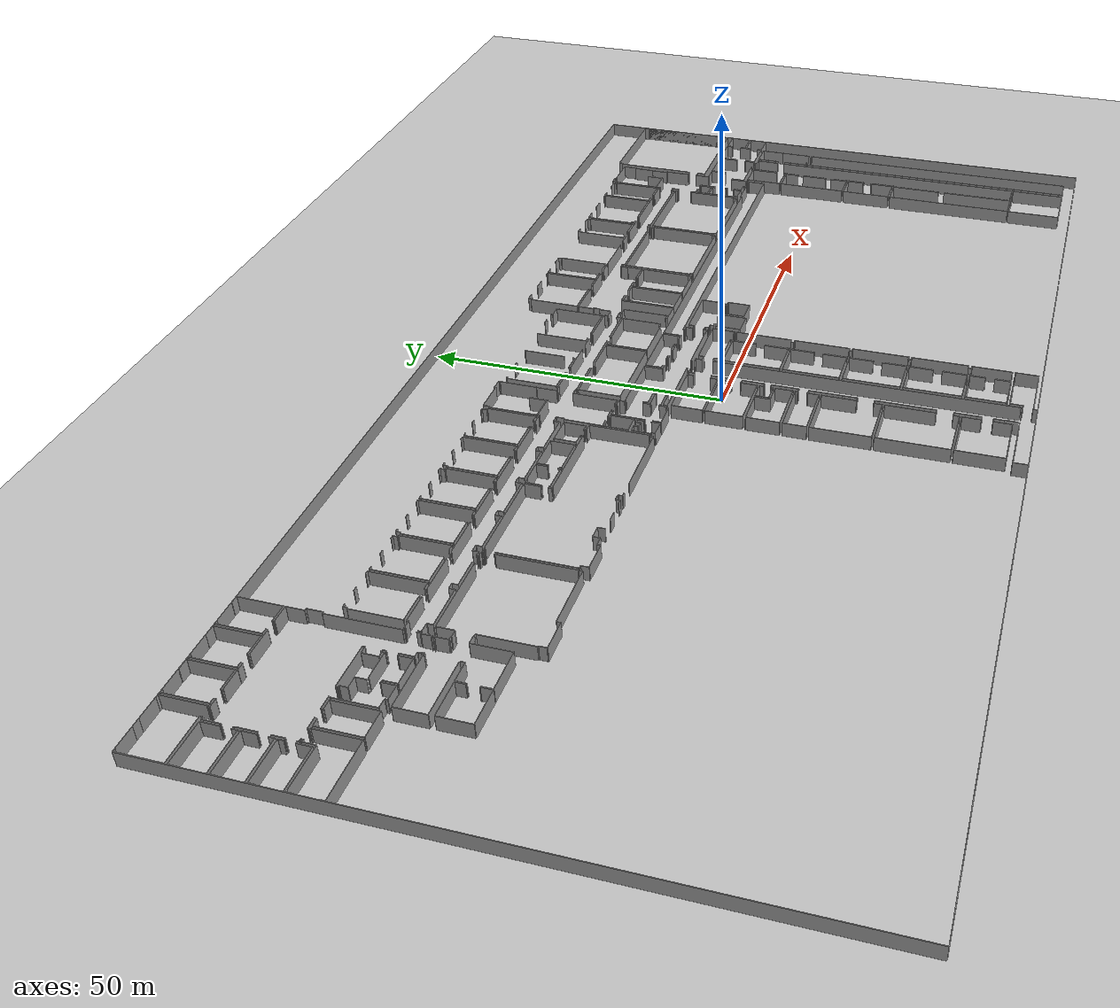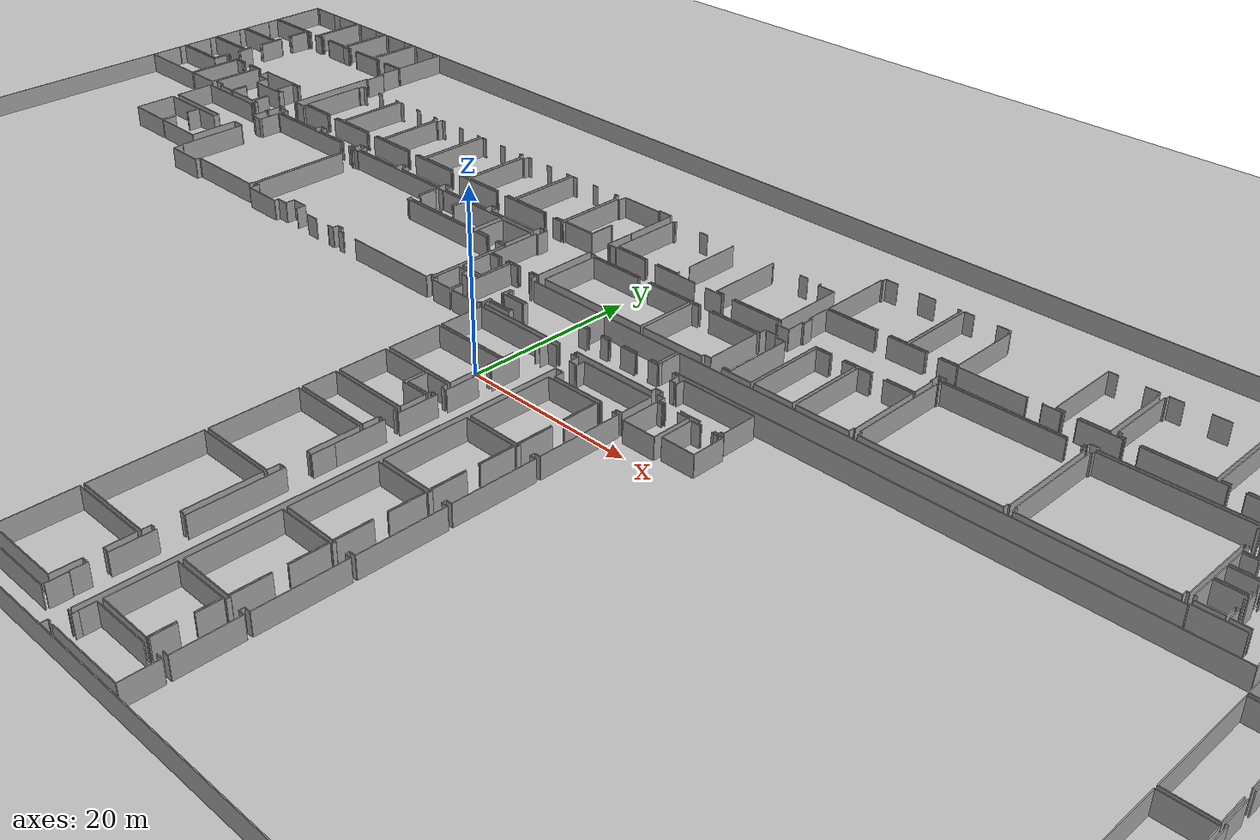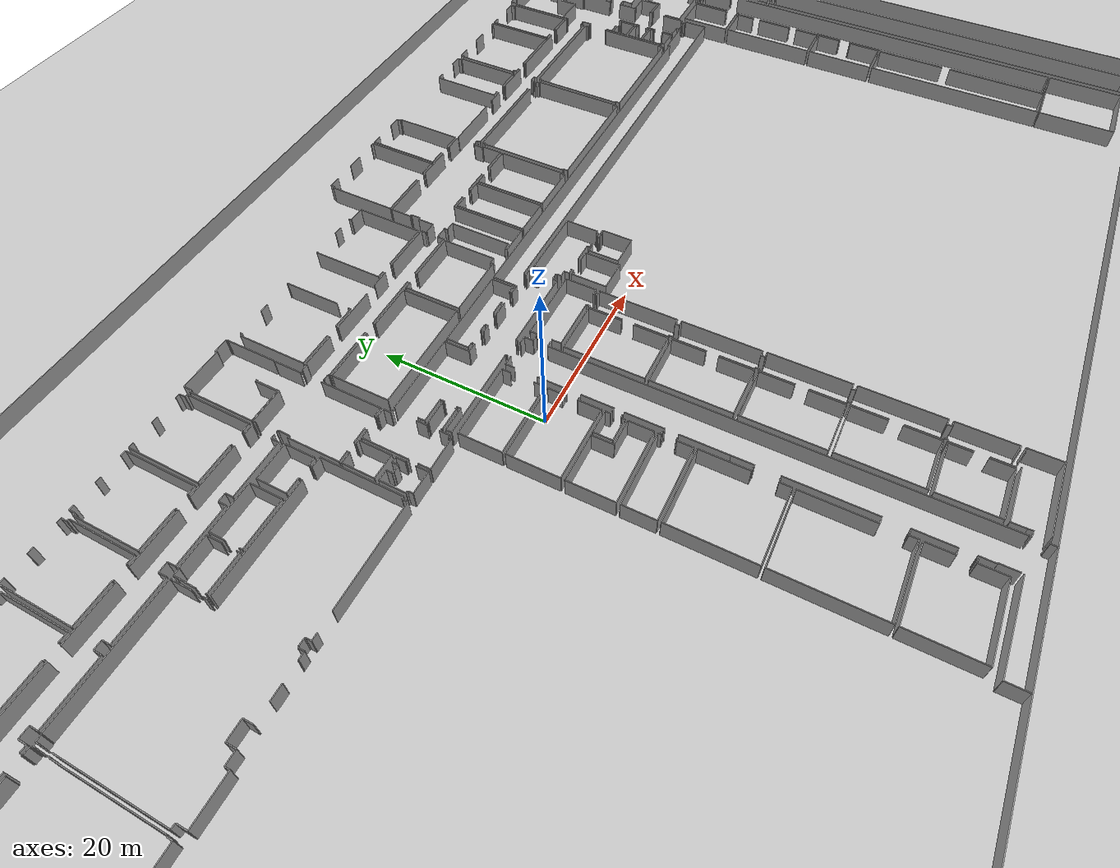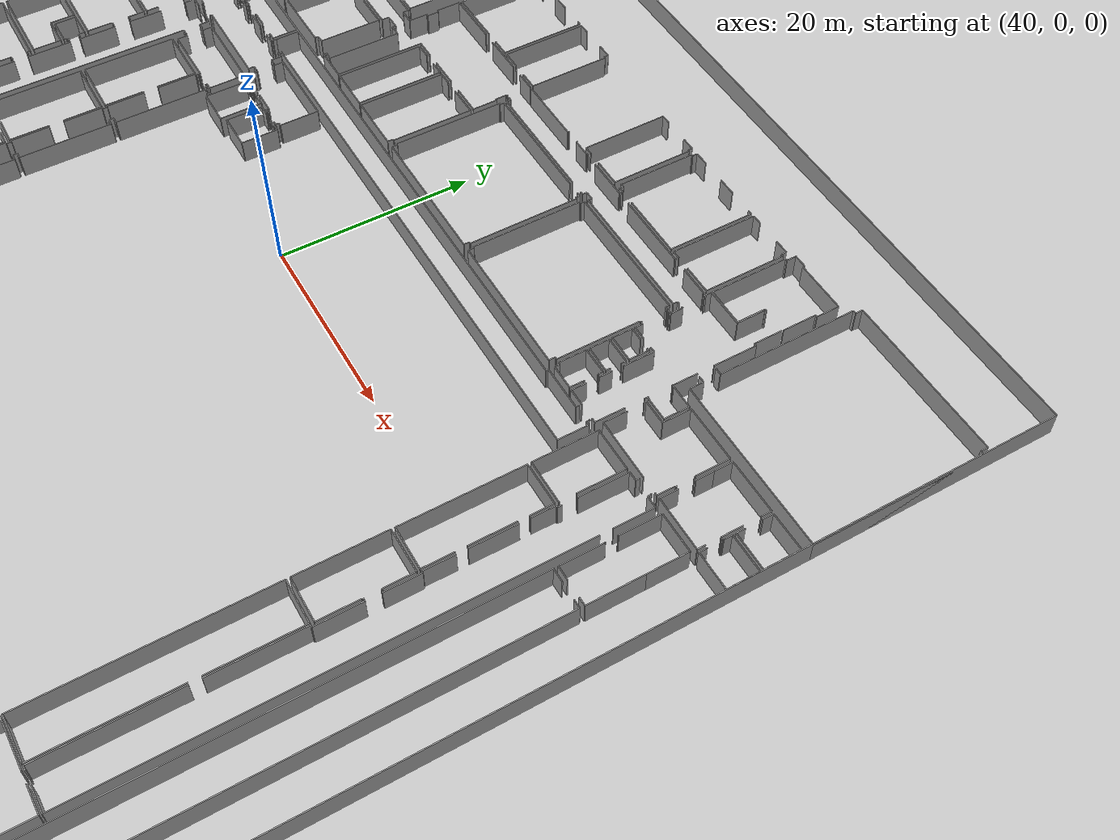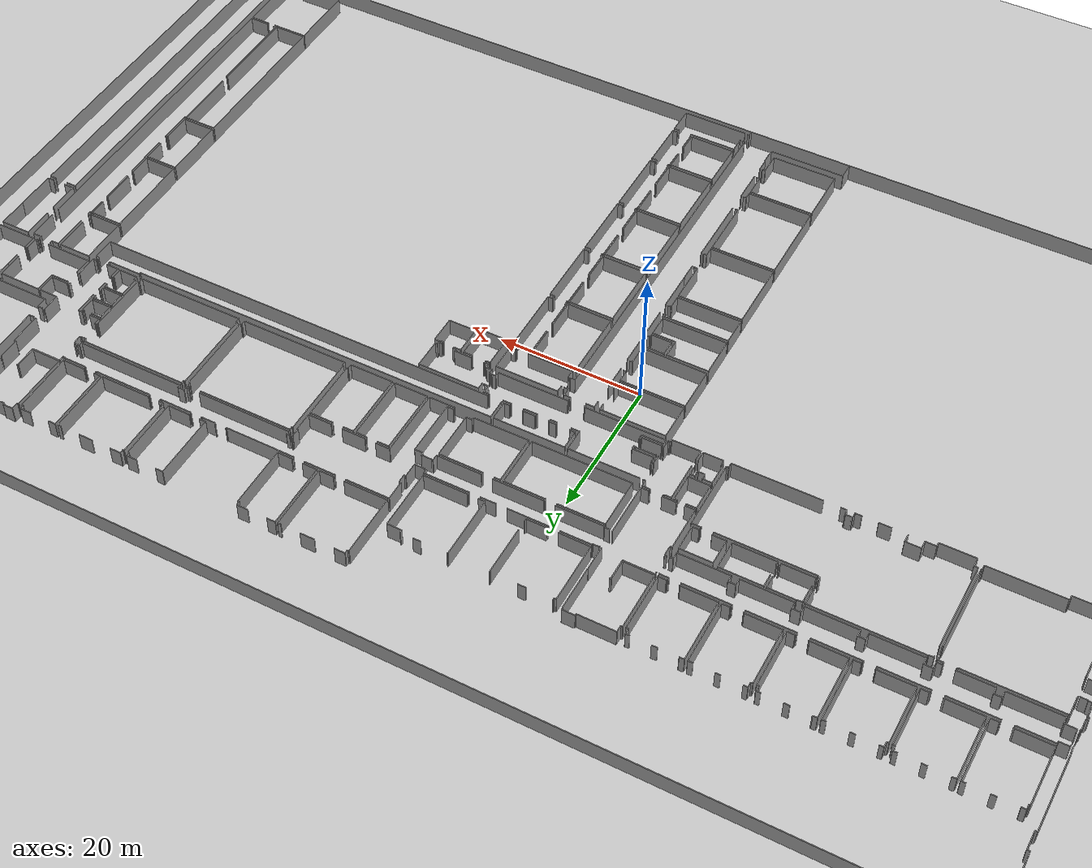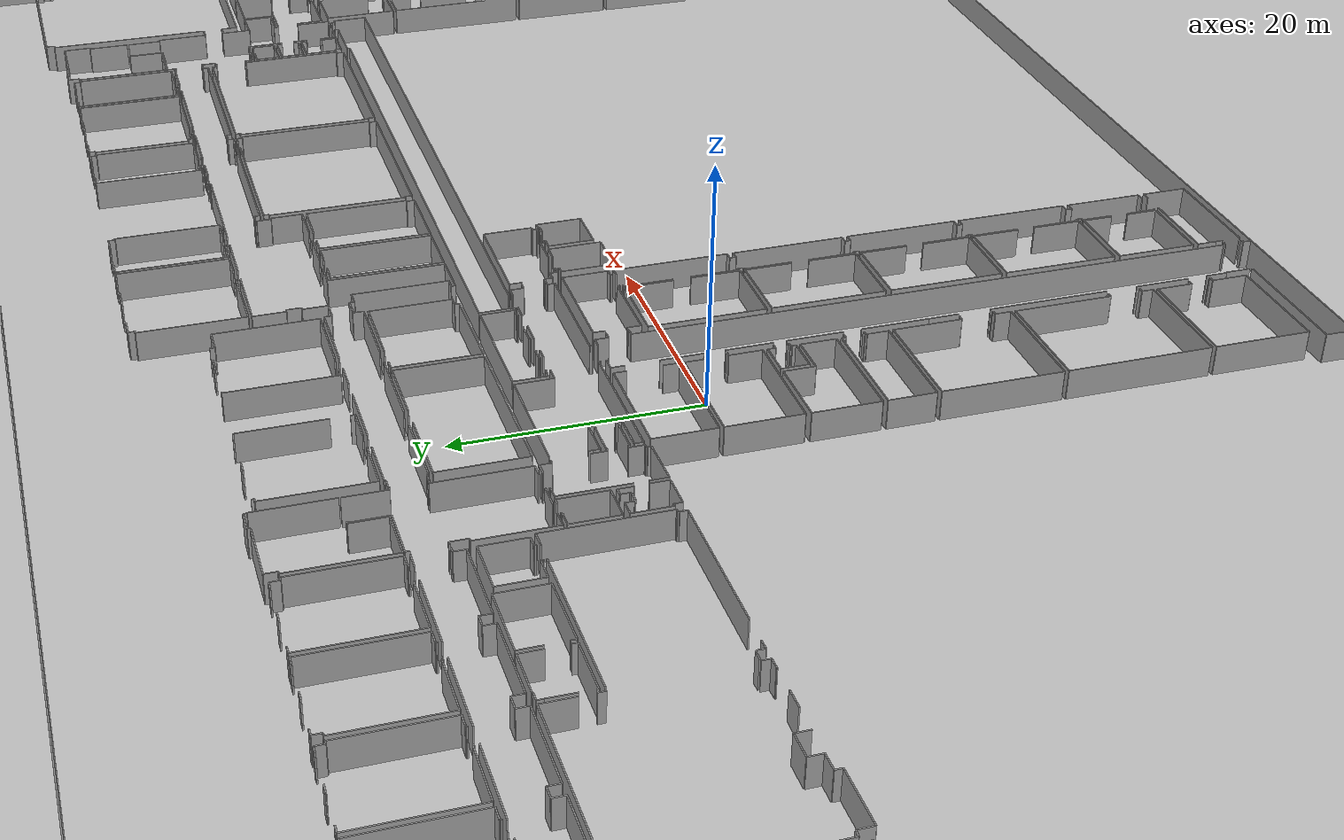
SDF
<sdf version="1.6">
  <world name="default">
    <light name="sun" type="directional">
      <cast_shadows>1</cast_shadows>
      <pose frame="">0 0 10 0 -0 0</pose>
      <diffuse>0.8 0.8 0.8 1</diffuse>
      <specular>0.1 0.1 0.1 1</specular>
      <attenuation>
        <range>1000</range>
        <constant>0.9</constant>
        <linear>0.01</linear>
        <quadratic>0.001</quadratic>
      </attenuation>
      <direction>-0.5 0.5 -1</direction>
    </light>
    <model name="ground_plane">
      <static>1</static>
      <link name="link">
        <collision name="collision">
          <geometry>
            <plane>
              <normal>0 0 1</normal>
              <size>100 100</size>
            </plane>
          </geometry>
          <surface>
            <friction>
              <ode>
                <mu>100</mu>
                <mu2>50</mu2>
              </ode>
              <torsional>
                <ode />
              </torsional>
            </friction>
            <contact>
              <ode />
            </contact>
            <bounce />
          </surface>
          <max_contacts>10</max_contacts>
        </collision>
        <visual name="visual">
          <cast_shadows>0</cast_shadows>
          <geometry>
            <plane>
              <normal>0 0 1</normal>
              <size>100 100</size>
            </plane>
          </geometry>
          <material>
            <script>
              <uri>file://media/materials/scripts/gazebo.material</uri>
              <name>Gazebo/Grey</name>
            </script>
          </material>
        </visual>
        <self_collide>0</self_collide>
        <kinematic>0</kinematic>
        <gravity>1</gravity>
      </link>
    </model>
    <gravity>0 0 -9.8</gravity>
    <magnetic_field>6e-06 2.3e-05 -4.2e-05</magnetic_field>
    <atmosphere type="adiabatic" />
    <physics default="0" name="default_physics" type="ode">
      <max_step_size>0.001</max_step_size>
      <real_time_factor>1</real_time_factor>
      <real_time_update_rate>1000</real_time_update_rate>
    </physics>
    <scene>
      <ambient>0.4 0.4 0.4 1</ambient>
      <background>0.7 0.7 0.7 1</background>
      <shadows>1</shadows>
    </scene>
    <spherical_coordinates>
      <surface_model>EARTH_WGS84</surface_model>
      <latitude_deg>0</latitude_deg>
      <longitude_deg>0</longitude_deg>
      <elevation>0</elevation>
      <heading_deg>0</heading_deg>
    </spherical_coordinates>
  <model name="0510035739_A_40_1_102">
		<static>1</static>
		<link name="Wall_0">
			<collision name="Wall_0_Collision">
				<geometry>
					<box>
						<size>6.92789996599 0.1 2.5</size>
					</box>
				</geometry>
				<pose frame="">3.463949983 0 1.25 0 0 0</pose>
			</collision>
			<visual name="Wall_0_Visual">
				<pose frame="">3.463949983 0 1.25 0 0 0</pose>
				<geometry>
					<box>
						<size>6.92789996599 0.1 2.5</size>
					</box>
				</geometry>
				<material>
					<script>
						<uri>file://media/materials/scripts/gazebo.material</uri>
						<name>Gazebo/Grey</name>
					</script>
					<ambient>1 1 1 1</ambient>
				</material>
			</visual>
			<pose frame="">0.0781993267726 -6.99540101353 0 0 0 1.57079632679</pose>
		</link>
		<link name="Wall_1">
			<collision name="Wall_1_Collision">
				<geometry>
					<box>
						<size>0.36170372644 0.1 2.5</size>
					</box>
				</geometry>
				<pose frame="">0.18085186322 0 1.25 0 0 0</pose>
			</collision>
			<visual name="Wall_1_Visual">
				<pose frame="">0.18085186322 0 1.25 0 0 0</pose>
				<geometry>
					<box>
						<size>0.36170372644 0.1 2.5</size>
					</box>
				</geometry>
				<material>
					<script>
						<uri>file://media/materials/scripts/gazebo.material</uri>
						<name>Gazebo/Grey</name>
					</script>
					<ambient>1 1 1 1</ambient>
				</material>
			</visual>
			<pose frame="">0.0781993267726 -0.0675010475398 0 0 0 0.0</pose>
		</link>
		<link name="Wall_2">
			<collision name="Wall_2_Collision">
				<geometry>
					<box>
						<size>0.0669916056716 0.1 2.5</size>
					</box>
				</geometry>
				<pose frame="">0.0334958028358 0 1.25 0 0 0</pose>
			</collision>
			<visual name="Wall_2_Visual">
				<pose frame="">0.0334958028358 0 1.25 0 0 0</pose>
				<geometry>
					<box>
						<size>0.0669916056716 0.1 2.5</size>
					</box>
				</geometry>
				<material>
					<script>
						<uri>file://media/materials/scripts/gazebo.material</uri>
						<name>Gazebo/Grey</name>
					</script>
					<ambient>1 1 1 1</ambient>
				</material>
			</visual>
			<pose frame="">0.439903053212 -0.0675010475398 0 0 0 1.57079632679</pose>
		</link>
		<link name="Wall_3">
			<collision name="Wall_3_Collision">
				<geometry>
					<box>
						<size>1.36326643937 0.1 2.5</size>
					</box>
				</geometry>
				<pose frame="">0.681633219685 0 1.25 0 0 0</pose>
			</collision>
			<visual name="Wall_3_Visual">
				<pose frame="">0.681633219685 0 1.25 0 0 0</pose>
				<geometry>
					<box>
						<size>1.36326643937 0.1 2.5</size>
					</box>
				</geometry>
				<material>
					<script>
						<uri>file://media/materials/scripts/gazebo.material</uri>
						<name>Gazebo/Grey</name>
					</script>
					<ambient>1 1 1 1</ambient>
				</material>
			</visual>
			<pose frame="">4.08470489943 -0.000509441868225 0 0 0 0.0</pose>
		</link>
		<link name="Wall_4">
			<collision name="Wall_4_Collision">
				<geometry>
					<box>
						<size>0.498234147124 0.1 2.5</size>
					</box>
				</geometry>
				<pose frame="">0.249117073562 0 1.25 0 0 0</pose>
			</collision>
			<visual name="Wall_4_Visual">
				<pose frame="">0.249117073562 0 1.25 0 0 0</pose>
				<geometry>
					<box>
						<size>0.498234147124 0.1 2.5</size>
					</box>
				</geometry>
				<material>
					<script>
						<uri>file://media/materials/scripts/gazebo.material</uri>
						<name>Gazebo/Grey</name>
					</script>
					<ambient>1 1 1 1</ambient>
				</material>
			</visual>
			<pose frame="">9.06169723106 -0.000509441868225 0 0 0 0.0</pose>
		</link>
		<link name="Wall_5">
			<collision name="Wall_5_Collision">
				<geometry>
					<box>
						<size>6.96763643172 0.1 2.5</size>
					</box>
				</geometry>
				<pose frame="">3.48381821586 0 1.25 0 0 0</pose>
			</collision>
			<visual name="Wall_5_Visual">
				<pose frame="">3.48381821586 0 1.25 0 0 0</pose>
				<geometry>
					<box>
						<size>6.96763643172 0.1 2.5</size>
					</box>
				</geometry>
				<material>
					<script>
						<uri>file://media/materials/scripts/gazebo.material</uri>
						<name>Gazebo/Grey</name>
					</script>
					<ambient>1 1 1 1</ambient>
				</material>
			</visual>
			<pose frame="">9.55993137818 -0.000509441868225 0 0 0 -1.57079632679</pose>
		</link>
		<link name="Wall_6">
			<collision name="Wall_6_Collision">
				<geometry>
					<box>
						<size>0.153342002336 0.1 2.5</size>
					</box>
				</geometry>
				<pose frame="">0.0766710011679 0 1.25 0 0 0</pose>
			</collision>
			<visual name="Wall_6_Visual">
				<pose frame="">0.0766710011679 0 1.25 0 0 0</pose>
				<geometry>
					<box>
						<size>0.153342002336 0.1 2.5</size>
					</box>
				</geometry>
				<material>
					<script>
						<uri>file://media/materials/scripts/gazebo.material</uri>
						<name>Gazebo/Grey</name>
					</script>
					<ambient>1 1 1 1</ambient>
				</material>
			</visual>
			<pose frame="">9.55993137818 -6.96814587358 0 0 0 3.14159265359</pose>
		</link>
		<link name="Wall_7">
			<collision name="Wall_7_Collision">
				<geometry>
					<box>
						<size>7.75298897859 0.1 2.5</size>
					</box>
				</geometry>
				<pose frame="">3.87649448929 0 1.25 0 0 0</pose>
			</collision>
			<visual name="Wall_7_Visual">
				<pose frame="">3.87649448929 0 1.25 0 0 0</pose>
				<geometry>
					<box>
						<size>7.75298897859 0.1 2.5</size>
					</box>
				</geometry>
				<material>
					<script>
						<uri>file://media/materials/scripts/gazebo.material</uri>
						<name>Gazebo/Grey</name>
					</script>
					<ambient>1 1 1 1</ambient>
				</material>
			</visual>
			<pose frame="">7.83114039836 -6.96814587358 0 0 0 -3.13807720991</pose>
		</link>
		<link name="Wall_8">
			<collision name="Wall_8_Collision">
				<geometry>
					<box>
						<size>6.92356971011 0.1 2.5</size>
					</box>
				</geometry>
				<pose frame="">3.46178485506 0 1.25 0 0 0</pose>
			</collision>
			<visual name="Wall_8_Visual">
				<pose frame="">3.46178485506 0 1.25 0 0 0</pose>
				<geometry>
					<box>
						<size>6.92356971011 0.1 2.5</size>
					</box>
				</geometry>
				<material>
					<script>
						<uri>file://media/materials/scripts/gazebo.material</uri>
						<name>Gazebo/Grey</name>
					</script>
					<ambient>1 1 1 1</ambient>
				</material>
			</visual>
			<pose frame="">0.0662274428693 -7.37391632163 0 0 0 0.0</pose>
		</link>
		<link name="Wall_9">
			<collision name="Wall_9_Collision">
				<geometry>
					<box>
						<size>2.82587404305 0.1 2.5</size>
					</box>
				</geometry>
				<pose frame="">1.41293702152 0 1.25 0 0 0</pose>
			</collision>
			<visual name="Wall_9_Visual">
				<pose frame="">1.41293702152 0 1.25 0 0 0</pose>
				<geometry>
					<box>
						<size>2.82587404305 0.1 2.5</size>
					</box>
				</geometry>
				<material>
					<script>
						<uri>file://media/materials/scripts/gazebo.material</uri>
						<name>Gazebo/Grey</name>
					</script>
					<ambient>1 1 1 1</ambient>
				</material>
			</visual>
			<pose frame="">6.98979715298 -7.37391632163 0 0 0 -1.57079632679</pose>
		</link>
		<link name="Wall_10">
			<collision name="Wall_10_Collision">
				<geometry>
					<box>
						<size>0.919542572147 0.1 2.5</size>
					</box>
				</geometry>
				<pose frame="">0.459771286073 0 1.25 0 0 0</pose>
			</collision>
			<visual name="Wall_10_Visual">
				<pose frame="">0.459771286073 0 1.25 0 0 0</pose>
				<geometry>
					<box>
						<size>0.919542572147 0.1 2.5</size>
					</box>
				</geometry>
				<material>
					<script>
						<uri>file://media/materials/scripts/gazebo.material</uri>
						<name>Gazebo/Grey</name>
					</script>
					<ambient>1 1 1 1</ambient>
				</material>
			</visual>
			<pose frame="">6.98979715298 -11.6766623407 0 0 0 -1.57079632679</pose>
		</link>
		<link name="Wall_11">
			<collision name="Wall_11_Collision">
				<geometry>
					<box>
						<size>6.93350382655 0.1 2.5</size>
					</box>
				</geometry>
				<pose frame="">3.46675191327 0 1.25 0 0 0</pose>
			</collision>
			<visual name="Wall_11_Visual">
				<pose frame="">3.46675191327 0 1.25 0 0 0</pose>
				<geometry>
					<box>
						<size>6.93350382655 0.1 2.5</size>
					</box>
				</geometry>
				<material>
					<script>
						<uri>file://media/materials/scripts/gazebo.material</uri>
						<name>Gazebo/Grey</name>
					</script>
					<ambient>1 1 1 1</ambient>
				</material>
			</visual>
			<pose frame="">6.98979715298 -12.5962049128 0 0 0 3.14159265359</pose>
		</link>
		<link name="Wall_12">
			<collision name="Wall_12_Collision">
				<geometry>
					<box>
						<size>1.46034890439 0.1 2.5</size>
					</box>
				</geometry>
				<pose frame="">0.730174452194 0 1.25 0 0 0</pose>
			</collision>
			<visual name="Wall_12_Visual">
				<pose frame="">0.730174452194 0 1.25 0 0 0</pose>
				<geometry>
					<box>
						<size>1.46034890439 0.1 2.5</size>
					</box>
				</geometry>
				<material>
					<script>
						<uri>file://media/materials/scripts/gazebo.material</uri>
						<name>Gazebo/Grey</name>
					</script>
					<ambient>1 1 1 1</ambient>
				</material>
			</visual>
			<pose frame="">0.0562933264389 -8.83423143689 0 0 0 1.56399371064</pose>
		</link>
		<link name="Wall_13">
			<collision name="Wall_13_Collision">
				<geometry>
					<box>
						<size>6.93706991962 0.1 2.5</size>
					</box>
				</geometry>
				<pose frame="">3.46853495981 0 1.25 0 0 0</pose>
			</collision>
			<visual name="Wall_13_Visual">
				<pose frame="">3.46853495981 0 1.25 0 0 0</pose>
				<geometry>
					<box>
						<size>6.93706991962 0.1 2.5</size>
					</box>
				</geometry>
				<material>
					<script>
						<uri>file://media/materials/scripts/gazebo.material</uri>
						<name>Gazebo/Grey</name>
					</script>
					<ambient>1 1 1 1</ambient>
				</material>
			</visual>
			<pose frame="">0.0621519079235 -12.982107128 0 0 0 0.0</pose>
		</link>
		<link name="Wall_14">
			<collision name="Wall_14_Collision">
				<geometry>
					<box>
						<size>2.17709982386 0.1 2.5</size>
					</box>
				</geometry>
				<pose frame="">1.08854991193 0 1.25 0 0 0</pose>
			</collision>
			<visual name="Wall_14_Visual">
				<pose frame="">1.08854991193 0 1.25 0 0 0</pose>
				<geometry>
					<box>
						<size>2.17709982386 0.1 2.5</size>
					</box>
				</geometry>
				<material>
					<script>
						<uri>file://media/materials/scripts/gazebo.material</uri>
						<name>Gazebo/Grey</name>
					</script>
					<ambient>1 1 1 1</ambient>
				</material>
			</visual>
			<pose frame="">6.99922182755 -12.982107128 0 0 0 -1.57079632679</pose>
		</link>
		<link name="Wall_15">
			<collision name="Wall_15_Collision">
				<geometry>
					<box>
						<size>0.906806525441 0.1 2.5</size>
					</box>
				</geometry>
				<pose frame="">0.45340326272 0 1.25 0 0 0</pose>
			</collision>
			<visual name="Wall_15_Visual">
				<pose frame="">0.45340326272 0 1.25 0 0 0</pose>
				<geometry>
					<box>
						<size>0.906806525441 0.1 2.5</size>
					</box>
				</geometry>
				<material>
					<script>
						<uri>file://media/materials/scripts/gazebo.material</uri>
						<name>Gazebo/Grey</name>
					</script>
					<ambient>1 1 1 1</ambient>
				</material>
			</visual>
			<pose frame="">6.99922182755 -16.6750512307 0 0 0 -1.57079632679</pose>
		</link>
		<link name="Wall_16">
			<collision name="Wall_16_Collision">
				<geometry>
					<box>
						<size>6.9615231293 0.1 2.5</size>
					</box>
				</geometry>
				<pose frame="">3.48076156465 0 1.25 0 0 0</pose>
			</collision>
			<visual name="Wall_16_Visual">
				<pose frame="">3.48076156465 0 1.25 0 0 0</pose>
				<geometry>
					<box>
						<size>6.9615231293 0.1 2.5</size>
					</box>
				</geometry>
				<material>
					<script>
						<uri>file://media/materials/scripts/gazebo.material</uri>
						<name>Gazebo/Grey</name>
					</script>
					<ambient>1 1 1 1</ambient>
				</material>
			</visual>
			<pose frame="">6.99922182755 -17.5818577562 0 0 0 3.14159265359</pose>
		</link>
		<link name="Wall_17">
			<collision name="Wall_17_Collision">
				<geometry>
					<box>
						<size>0.0766710011679 0.1 2.5</size>
					</box>
				</geometry>
				<pose frame="">0.038335500584 0 1.25 0 0 0</pose>
			</collision>
			<visual name="Wall_17_Visual">
				<pose frame="">0.038335500584 0 1.25 0 0 0</pose>
				<geometry>
					<box>
						<size>0.0766710011679 0.1 2.5</size>
					</box>
				</geometry>
				<material>
					<script>
						<uri>file://media/materials/scripts/gazebo.material</uri>
						<name>Gazebo/Grey</name>
					</script>
					<ambient>1 1 1 1</ambient>
				</material>
			</visual>
			<pose frame="">0.0376986982487 -17.5818577562 0 0 0 1.57079632679</pose>
		</link>
		<link name="Wall_18">
			<collision name="Wall_18_Collision">
				<geometry>
					<box>
						<size>0.896187200427 0.1 2.5</size>
					</box>
				</geometry>
				<pose frame="">0.448093600214 0 1.25 0 0 0</pose>
			</collision>
			<visual name="Wall_18_Visual">
				<pose frame="">0.448093600214 0 1.25 0 0 0</pose>
				<geometry>
					<box>
						<size>0.896187200427 0.1 2.5</size>
					</box>
				</geometry>
				<material>
					<script>
						<uri>file://media/materials/scripts/gazebo.material</uri>
						<name>Gazebo/Grey</name>
					</script>
					<ambient>1 1 1 1</ambient>
				</material>
			</visual>
			<pose frame="">0.0376986982487 -13.8779606533 0 0 0 1.54350711202</pose>
		</link>
		<link name="Wall_19">
			<collision name="Wall_19_Collision">
				<geometry>
					<box>
						<size>6.88994654681 0.1 2.5</size>
					</box>
				</geometry>
				<pose frame="">3.44497327341 0 1.25 0 0 0</pose>
			</collision>
			<visual name="Wall_19_Visual">
				<pose frame="">3.44497327341 0 1.25 0 0 0</pose>
				<geometry>
					<box>
						<size>6.88994654681 0.1 2.5</size>
					</box>
				</geometry>
				<material>
					<script>
						<uri>file://media/materials/scripts/gazebo.material</uri>
						<name>Gazebo/Grey</name>
					</script>
					<ambient>1 1 1 1</ambient>
				</material>
			</visual>
			<pose frame="">0.0751426755632 -17.9667410876 0 0 0 0.0</pose>
		</link>
		<link name="Wall_20">
			<collision name="Wall_20_Collision">
				<geometry>
					<box>
						<size>0.811031454215 0.1 2.5</size>
					</box>
				</geometry>
				<pose frame="">0.405515727107 0 1.25 0 0 0</pose>
			</collision>
			<visual name="Wall_20_Visual">
				<pose frame="">0.405515727107 0 1.25 0 0 0</pose>
				<geometry>
					<box>
						<size>0.811031454215 0.1 2.5</size>
					</box>
				</geometry>
				<material>
					<script>
						<uri>file://media/materials/scripts/gazebo.material</uri>
						<name>Gazebo/Grey</name>
					</script>
					<ambient>1 1 1 1</ambient>
				</material>
			</visual>
			<pose frame="">6.96508922238 -17.9667410876 0 0 0 -1.57079632679</pose>
		</link>
		<link name="Wall_21">
			<collision name="Wall_21_Collision">
				<geometry>
					<box>
						<size>2.24995001102 0.1 2.5</size>
					</box>
				</geometry>
				<pose frame="">1.12497500551 0 1.25 0 0 0</pose>
			</collision>
			<visual name="Wall_21_Visual">
				<pose frame="">1.12497500551 0 1.25 0 0 0</pose>
				<geometry>
					<box>
						<size>2.24995001102 0.1 2.5</size>
					</box>
				</geometry>
				<material>
					<script>
						<uri>file://media/materials/scripts/gazebo.material</uri>
						<name>Gazebo/Grey</name>
					</script>
					<ambient>1 1 1 1</ambient>
				</material>
			</visual>
			<pose frame="">6.96508922238 -20.3404854726 0 0 0 -1.57079632679</pose>
		</link>
		<link name="Wall_22">
			<collision name="Wall_22_Collision">
				<geometry>
					<box>
						<size>6.95286261754 0.1 2.5</size>
					</box>
				</geometry>
				<pose frame="">3.47643130877 0 1.25 0 0 0</pose>
			</collision>
			<visual name="Wall_22_Visual">
				<pose frame="">3.47643130877 0 1.25 0 0 0</pose>
				<geometry>
					<box>
						<size>6.95286261754 0.1 2.5</size>
					</box>
				</geometry>
				<material>
					<script>
						<uri>file://media/materials/scripts/gazebo.material</uri>
						<name>Gazebo/Grey</name>
					</script>
					<ambient>1 1 1 1</ambient>
				</material>
			</visual>
			<pose frame="">6.96508922238 -22.5904354836 0 0 0 3.14159265359</pose>
		</link>
		<link name="Wall_23">
			<collision name="Wall_23_Collision">
				<geometry>
					<box>
						<size>0.146973978983 0.1 2.5</size>
					</box>
				</geometry>
				<pose frame="">0.0734869894915 0 1.25 0 0 0</pose>
			</collision>
			<visual name="Wall_23_Visual">
				<pose frame="">0.0734869894915 0 1.25 0 0 0</pose>
				<geometry>
					<box>
						<size>0.146973978983 0.1 2.5</size>
					</box>
				</geometry>
				<material>
					<script>
						<uri>file://media/materials/scripts/gazebo.material</uri>
						<name>Gazebo/Grey</name>
					</script>
					<ambient>1 1 1 1</ambient>
				</material>
			</visual>
			<pose frame="">0.0122266048374 -22.5904354836 0 0 0 1.57079632679</pose>
		</link>
		<link name="Wall_24">
			<collision name="Wall_24_Collision">
				<geometry>
					<box>
						<size>0.0308212330276 0.1 2.5</size>
					</box>
				</geometry>
				<pose frame="">0.0154106165138 0 1.25 0 0 0</pose>
			</collision>
			<visual name="Wall_24_Visual">
				<pose frame="">0.0154106165138 0 1.25 0 0 0</pose>
				<geometry>
					<box>
						<size>0.0308212330276 0.1 2.5</size>
					</box>
				</geometry>
				<material>
					<script>
						<uri>file://media/materials/scripts/gazebo.material</uri>
						<name>Gazebo/Grey</name>
					</script>
					<ambient>1 1 1 1</ambient>
				</material>
			</visual>
			<pose frame="">0.0122266048374 -18.8651418222 0 0 0 1.57079632679</pose>
		</link>
		<link name="Wall_25">
			<collision name="Wall_25_Collision">
				<geometry>
					<box>
						<size>0.0427931169309 0.1 2.5</size>
					</box>
				</geometry>
				<pose frame="">0.0213965584655 0 1.25 0 0 0</pose>
			</collision>
			<visual name="Wall_25_Visual">
				<pose frame="">0.0213965584655 0 1.25 0 0 0</pose>
				<geometry>
					<box>
						<size>0.0427931169309 0.1 2.5</size>
					</box>
				</geometry>
				<material>
					<script>
						<uri>file://media/materials/scripts/gazebo.material</uri>
						<name>Gazebo/Grey</name>
					</script>
					<ambient>1 1 1 1</ambient>
				</material>
			</visual>
			<pose frame="">0.0122266048374 -18.8343205892 0 0 0 0.0</pose>
		</link>
		<link name="Wall_26">
			<collision name="Wall_26_Collision">
				<geometry>
					<box>
						<size>0.867812839755 0.1 2.5</size>
					</box>
				</geometry>
				<pose frame="">0.433906419878 0 1.25 0 0 0</pose>
			</collision>
			<visual name="Wall_26_Visual">
				<pose frame="">0.433906419878 0 1.25 0 0 0</pose>
				<geometry>
					<box>
						<size>0.867812839755 0.1 2.5</size>
					</box>
				</geometry>
				<material>
					<script>
						<uri>file://media/materials/scripts/gazebo.material</uri>
						<name>Gazebo/Grey</name>
					</script>
					<ambient>1 1 1 1</ambient>
				</material>
			</visual>
			<pose frame="">0.0550197217683 -18.8343205892 0 0 0 1.54760612192</pose>
		</link>
		<link name="Wall_27">
			<collision name="Wall_27_Collision">
				<geometry>
					<box>
						<size>0.50663993795 0.1 2.5</size>
					</box>
				</geometry>
				<pose frame="">0.253319968975 0 1.25 0 0 0</pose>
			</collision>
			<visual name="Wall_27_Visual">
				<pose frame="">0.253319968975 0 1.25 0 0 0</pose>
				<geometry>
					<box>
						<size>0.50663993795 0.1 2.5</size>
					</box>
				</geometry>
				<material>
					<script>
						<uri>file://media/materials/scripts/gazebo.material</uri>
						<name>Gazebo/Grey</name>
					</script>
					<ambient>1 1 1 1</ambient>
				</material>
			</visual>
			<pose frame="">0.0634255125941 -27.947216728 0 0 0 1.57079632679</pose>
		</link>
		<link name="Wall_28">
			<collision name="Wall_28_Collision">
				<geometry>
					<box>
						<size>0.0634255125941 0.1 2.5</size>
					</box>
				</geometry>
				<pose frame="">0.031712756297 0 1.25 0 0 0</pose>
			</collision>
			<visual name="Wall_28_Visual">
				<pose frame="">0.031712756297 0 1.25 0 0 0</pose>
				<geometry>
					<box>
						<size>0.0634255125941 0.1 2.5</size>
					</box>
				</geometry>
				<material>
					<script>
						<uri>file://media/materials/scripts/gazebo.material</uri>
						<name>Gazebo/Grey</name>
					</script>
					<ambient>1 1 1 1</ambient>
				</material>
			</visual>
			<pose frame="">0.0634255125941 -27.4405767901 0 0 0 3.14159265359</pose>
		</link>
		<link name="Wall_29">
			<collision name="Wall_29_Collision">
				<geometry>
					<box>
						<size>0.0853980185984 0.1 2.5</size>
					</box>
				</geometry>
				<pose frame="">0.0426990092992 0 1.25 0 0 0</pose>
			</collision>
			<visual name="Wall_29_Visual">
				<pose frame="">0.0426990092992 0 1.25 0 0 0</pose>
				<geometry>
					<box>
						<size>0.0853980185984 0.1 2.5</size>
					</box>
				</geometry>
				<material>
					<script>
						<uri>file://media/materials/scripts/gazebo.material</uri>
						<name>Gazebo/Grey</name>
					</script>
					<ambient>1 1 1 1</ambient>
				</material>
			</visual>
			<pose frame="">0.0 -23.8411152701 0 0 0 0.946385977168</pose>
		</link>
		<link name="Wall_30">
			<collision name="Wall_30_Collision">
				<geometry>
					<box>
						<size>0.837267710428 0.1 2.5</size>
					</box>
				</geometry>
				<pose frame="">0.418633855214 0 1.25 0 0 0</pose>
			</collision>
			<visual name="Wall_30_Visual">
				<pose frame="">0.418633855214 0 1.25 0 0 0</pose>
				<geometry>
					<box>
						<size>0.837267710428 0.1 2.5</size>
					</box>
				</geometry>
				<material>
					<script>
						<uri>file://media/materials/scripts/gazebo.material</uri>
						<name>Gazebo/Grey</name>
					</script>
					<ambient>1 1 1 1</ambient>
				</material>
			</visual>
			<pose frame="">0.0499253030861 -23.7718311761 0 0 0 1.57079632679</pose>
		</link>
		<link name="Wall_31">
			<collision name="Wall_31_Collision">
				<geometry>
					<box>
						<size>7.29826420419 0.1 2.5</size>
					</box>
				</geometry>
				<pose frame="">3.6491321021 0 1.25 0 0 0</pose>
			</collision>
			<visual name="Wall_31_Visual">
				<pose frame="">3.6491321021 0 1.25 0 0 0</pose>
				<geometry>
					<box>
						<size>7.29826420419 0.1 2.5</size>
					</box>
				</geometry>
				<material>
					<script>
						<uri>file://media/materials/scripts/gazebo.material</uri>
						<name>Gazebo/Grey</name>
					</script>
					<ambient>1 1 1 1</ambient>
				</material>
			</visual>
			<pose frame="">0.0499253030861 -22.9345634656 0 0 0 0.0</pose>
		</link>
		<link name="Wall_32">
			<collision name="Wall_32_Collision">
				<geometry>
					<box>
						<size>1.96695505322 0.1 2.5</size>
					</box>
				</geometry>
				<pose frame="">0.983477526609 0 1.25 0 0 0</pose>
			</collision>
			<visual name="Wall_32_Visual">
				<pose frame="">0.983477526609 0 1.25 0 0 0</pose>
				<geometry>
					<box>
						<size>1.96695505322 0.1 2.5</size>
					</box>
				</geometry>
				<material>
					<script>
						<uri>file://media/materials/scripts/gazebo.material</uri>
						<name>Gazebo/Grey</name>
					</script>
					<ambient>1 1 1 1</ambient>
				</material>
			</visual>
			<pose frame="">7.34818950728 -22.9345634656 0 0 0 1.57079632679</pose>
		</link>
		<link name="Wall_33">
			<collision name="Wall_33_Collision">
				<geometry>
					<box>
						<size>0.424619797166 0.1 2.5</size>
					</box>
				</geometry>
				<pose frame="">0.212309898583 0 1.25 0 0 0</pose>
			</collision>
			<visual name="Wall_33_Visual">
				<pose frame="">0.212309898583 0 1.25 0 0 0</pose>
				<geometry>
					<box>
						<size>0.424619797166 0.1 2.5</size>
					</box>
				</geometry>
				<material>
					<script>
						<uri>file://media/materials/scripts/gazebo.material</uri>
						<name>Gazebo/Grey</name>
					</script>
					<ambient>1 1 1 1</ambient>
				</material>
			</visual>
			<pose frame="">7.34818950728 -20.9676084124 0 0 0 0.0</pose>
		</link>
		<link name="Wall_34">
			<collision name="Wall_34_Collision">
				<geometry>
					<box>
						<size>0.289617702086 0.1 2.5</size>
					</box>
				</geometry>
				<pose frame="">0.144808851043 0 1.25 0 0 0</pose>
			</collision>
			<visual name="Wall_34_Visual">
				<pose frame="">0.144808851043 0 1.25 0 0 0</pose>
				<geometry>
					<box>
						<size>0.289617702086 0.1 2.5</size>
					</box>
				</geometry>
				<material>
					<script>
						<uri>file://media/materials/scripts/gazebo.material</uri>
						<name>Gazebo/Grey</name>
					</script>
					<ambient>1 1 1 1</ambient>
				</material>
			</visual>
			<pose frame="">9.26776646675 -20.9676084124 0 0 0 0.0</pose>
		</link>
		<link name="Wall_35">
			<collision name="Wall_35_Collision">
				<geometry>
					<box>
						<size>6.97782526908 0.1 2.5</size>
					</box>
				</geometry>
				<pose frame="">3.48891263454 0 1.25 0 0 0</pose>
			</collision>
			<visual name="Wall_35_Visual">
				<pose frame="">3.48891263454 0 1.25 0 0 0</pose>
				<geometry>
					<box>
						<size>6.97782526908 0.1 2.5</size>
					</box>
				</geometry>
				<material>
					<script>
						<uri>file://media/materials/scripts/gazebo.material</uri>
						<name>Gazebo/Grey</name>
					</script>
					<ambient>1 1 1 1</ambient>
				</material>
			</visual>
			<pose frame="">9.55738416884 -20.9676084124 0 0 0 -1.57079632679</pose>
		</link>
		<link name="Wall_36">
			<collision name="Wall_36_Collision">
				<geometry>
					<box>
						<size>9.49395882368 0.1 2.5</size>
					</box>
				</geometry>
				<pose frame="">4.74697941184 0 1.25 0 0 0</pose>
			</collision>
			<visual name="Wall_36_Visual">
				<pose frame="">4.74697941184 0 1.25 0 0 0</pose>
				<geometry>
					<box>
						<size>9.49395882368 0.1 2.5</size>
					</box>
				</geometry>
				<material>
					<script>
						<uri>file://media/materials/scripts/gazebo.material</uri>
						<name>Gazebo/Grey</name>
					</script>
					<ambient>1 1 1 1</ambient>
				</material>
			</visual>
			<pose frame="">9.55738416884 -27.9454336815 0 0 0 -3.14140484505</pose>
		</link>
		<link name="Wall_37">
			<collision name="Wall_37_Collision">
				<geometry>
					<box>
						<size>6.9526078966 0.1 2.5</size>
					</box>
				</geometry>
				<pose frame="">3.4763039483 0 1.25 0 0 0</pose>
			</collision>
			<visual name="Wall_37_Visual">
				<pose frame="">3.4763039483 0 1.25 0 0 0</pose>
				<geometry>
					<box>
						<size>6.9526078966 0.1 2.5</size>
					</box>
				</geometry>
				<material>
					<script>
						<uri>file://media/materials/scripts/gazebo.material</uri>
						<name>Gazebo/Grey</name>
					</script>
					<ambient>1 1 1 1</ambient>
				</material>
			</visual>
			<pose frame="">9.94863552364 -27.9334617976 0 0 0 1.57079632679</pose>
		</link>
		<link name="Wall_38">
			<collision name="Wall_38_Collision">
				<geometry>
					<box>
						<size>1.15286694779 0.1 2.5</size>
					</box>
				</geometry>
				<pose frame="">0.576433473897 0 1.25 0 0 0</pose>
			</collision>
			<visual name="Wall_38_Visual">
				<pose frame="">0.576433473897 0 1.25 0 0 0</pose>
				<geometry>
					<box>
						<size>1.15286694779 0.1 2.5</size>
					</box>
				</geometry>
				<material>
					<script>
						<uri>file://media/materials/scripts/gazebo.material</uri>
						<name>Gazebo/Grey</name>
					</script>
					<ambient>1 1 1 1</ambient>
				</material>
			</visual>
			<pose frame="">9.94863552364 -20.980853901 0 0 0 0.0</pose>
		</link>
		<link name="Wall_39">
			<collision name="Wall_39_Collision">
				<geometry>
					<box>
						<size>0.186959266014 0.1 2.5</size>
					</box>
				</geometry>
				<pose frame="">0.0934796330072 0 1.25 0 0 0</pose>
			</collision>
			<visual name="Wall_39_Visual">
				<pose frame="">0.0934796330072 0 1.25 0 0 0</pose>
				<geometry>
					<box>
						<size>0.186959266014 0.1 2.5</size>
					</box>
				</geometry>
				<material>
					<script>
						<uri>file://media/materials/scripts/gazebo.material</uri>
						<name>Gazebo/Grey</name>
					</script>
					<ambient>1 1 1 1</ambient>
				</material>
			</visual>
			<pose frame="">11.1015024714 -20.980853901 0 0 0 0.785398163397</pose>
		</link>
		<link name="Wall_40">
			<collision name="Wall_40_Collision">
				<geometry>
					<box>
						<size>0.17523856145 0.1 2.5</size>
					</box>
				</geometry>
				<pose frame="">0.0876192807252 0 1.25 0 0 0</pose>
			</collision>
			<visual name="Wall_40_Visual">
				<pose frame="">0.0876192807252 0 1.25 0 0 0</pose>
				<geometry>
					<box>
						<size>0.17523856145 0.1 2.5</size>
					</box>
				</geometry>
				<material>
					<script>
						<uri>file://media/materials/scripts/gazebo.material</uri>
						<name>Gazebo/Grey</name>
					</script>
					<ambient>1 1 1 1</ambient>
				</material>
			</visual>
			<pose frame="">12.7064990773 -20.8486537362 0 0 0 -0.505263125965</pose>
		</link>
		<link name="Wall_41">
			<collision name="Wall_41_Collision">
				<geometry>
					<box>
						<size>1.50336295313 0.1 2.5</size>
					</box>
				</geometry>
				<pose frame="">0.751681476566 0 1.25 0 0 0</pose>
			</collision>
			<visual name="Wall_41_Visual">
				<pose frame="">0.751681476566 0 1.25 0 0 0</pose>
				<geometry>
					<box>
						<size>1.50336295313 0.1 2.5</size>
					</box>
				</geometry>
				<material>
					<script>
						<uri>file://media/materials/scripts/gazebo.material</uri>
						<name>Gazebo/Grey</name>
					</script>
					<ambient>1 1 1 1</ambient>
				</material>
			</visual>
			<pose frame="">12.8598410796 -20.9334758072 0 0 0 0.0</pose>
		</link>
		<link name="Wall_42">
			<collision name="Wall_42_Collision">
				<geometry>
					<box>
						<size>6.99132547859 0.1 2.5</size>
					</box>
				</geometry>
				<pose frame="">3.49566273929 0 1.25 0 0 0</pose>
			</collision>
			<visual name="Wall_42_Visual">
				<pose frame="">3.49566273929 0 1.25 0 0 0</pose>
				<geometry>
					<box>
						<size>6.99132547859 0.1 2.5</size>
					</box>
				</geometry>
				<material>
					<script>
						<uri>file://media/materials/scripts/gazebo.material</uri>
						<name>Gazebo/Grey</name>
					</script>
					<ambient>1 1 1 1</ambient>
				</material>
			</visual>
			<pose frame="">14.3632040327 -20.9334758072 0 0 0 -1.57079632679</pose>
		</link>
		<link name="Wall_43">
			<collision name="Wall_43_Collision">
				<geometry>
					<box>
						<size>4.4145770042 0.1 2.5</size>
					</box>
				</geometry>
				<pose frame="">2.2072885021 0 1.25 0 0 0</pose>
			</collision>
			<visual name="Wall_43_Visual">
				<pose frame="">2.2072885021 0 1.25 0 0 0</pose>
				<geometry>
					<box>
						<size>4.4145770042 0.1 2.5</size>
					</box>
				</geometry>
				<material>
					<script>
						<uri>file://media/materials/scripts/gazebo.material</uri>
						<name>Gazebo/Grey</name>
					</script>
					<ambient>1 1 1 1</ambient>
				</material>
			</visual>
			<pose frame="">14.3632040327 -27.9248012858 0 0 0 -3.13963085356</pose>
		</link>
		<link name="Wall_44">
			<collision name="Wall_44_Collision">
				<geometry>
					<box>
						<size>6.57052649543 0.1 2.5</size>
					</box>
				</geometry>
				<pose frame="">3.28526324772 0 1.25 0 0 0</pose>
			</collision>
			<visual name="Wall_44_Visual">
				<pose frame="">3.28526324772 0 1.25 0 0 0</pose>
				<geometry>
					<box>
						<size>6.57052649543 0.1 2.5</size>
					</box>
				</geometry>
				<material>
					<script>
						<uri>file://media/materials/scripts/gazebo.material</uri>
						<name>Gazebo/Grey</name>
					</script>
					<ambient>1 1 1 1</ambient>
				</material>
			</visual>
			<pose frame="">14.7687197598 -27.4342087667 0 0 0 1.57079632679</pose>
		</link>
		<link name="Wall_45">
			<collision name="Wall_45_Collision">
				<geometry>
					<box>
						<size>0.074633233695 0.1 2.5</size>
					</box>
				</geometry>
				<pose frame="">0.0373166168475 0 1.25 0 0 0</pose>
			</collision>
			<visual name="Wall_45_Visual">
				<pose frame="">0.0373166168475 0 1.25 0 0 0</pose>
				<geometry>
					<box>
						<size>0.074633233695 0.1 2.5</size>
					</box>
				</geometry>
				<material>
					<script>
						<uri>file://media/materials/scripts/gazebo.material</uri>
						<name>Gazebo/Grey</name>
					</script>
					<ambient>1 1 1 1</ambient>
				</material>
			</visual>
			<pose frame="">14.7687197598 -20.8636822713 0 0 0 0.0</pose>
		</link>
		<link name="Wall_46">
			<collision name="Wall_46_Collision">
				<geometry>
					<box>
						<size>0.104180862052 0.1 2.5</size>
					</box>
				</geometry>
				<pose frame="">0.052090431026 0 1.25 0 0 0</pose>
			</collision>
			<visual name="Wall_46_Visual">
				<pose frame="">0.052090431026 0 1.25 0 0 0</pose>
				<geometry>
					<box>
						<size>0.104180862052 0.1 2.5</size>
					</box>
				</geometry>
				<material>
					<script>
						<uri>file://media/materials/scripts/gazebo.material</uri>
						<name>Gazebo/Grey</name>
					</script>
					<ambient>1 1 1 1</ambient>
				</material>
			</visual>
			<pose frame="">16.534954717 -20.8636822713 0 0 0 0.0</pose>
		</link>
		<link name="Wall_47">
			<collision name="Wall_47_Collision">
				<geometry>
					<box>
						<size>0.0876240013347 0.1 2.5</size>
					</box>
				</geometry>
				<pose frame="">0.0438120006674 0 1.25 0 0 0</pose>
			</collision>
			<visual name="Wall_47_Visual">
				<pose frame="">0.0438120006674 0 1.25 0 0 0</pose>
				<geometry>
					<box>
						<size>0.0876240013347 0.1 2.5</size>
					</box>
				</geometry>
				<material>
					<script>
						<uri>file://media/materials/scripts/gazebo.material</uri>
						<name>Gazebo/Grey</name>
					</script>
					<ambient>1 1 1 1</ambient>
				</material>
			</visual>
			<pose frame="">16.639135579 -20.8636822713 0 0 0 -1.57079632679</pose>
		</link>
		<link name="Wall_48">
			<collision name="Wall_48_Collision">
				<geometry>
					<box>
						<size>0.224409142953 0.1 2.5</size>
					</box>
				</geometry>
				<pose frame="">0.112204571477 0 1.25 0 0 0</pose>
			</collision>
			<visual name="Wall_48_Visual">
				<pose frame="">0.112204571477 0 1.25 0 0 0</pose>
				<geometry>
					<box>
						<size>0.224409142953 0.1 2.5</size>
					</box>
				</geometry>
				<material>
					<script>
						<uri>file://media/materials/scripts/gazebo.material</uri>
						<name>Gazebo/Grey</name>
					</script>
					<ambient>1 1 1 1</ambient>
				</material>
			</visual>
			<pose frame="">16.639135579 -20.9513062726 0 0 0 0.0</pose>
		</link>
		<link name="Wall_49">
			<collision name="Wall_49_Collision">
				<geometry>
					<box>
						<size>1.22444353028 0.1 2.5</size>
					</box>
				</geometry>
				<pose frame="">0.61222176514 0 1.25 0 0 0</pose>
			</collision>
			<visual name="Wall_49_Visual">
				<pose frame="">0.61222176514 0 1.25 0 0 0</pose>
				<geometry>
					<box>
						<size>1.22444353028 0.1 2.5</size>
					</box>
				</geometry>
				<material>
					<script>
						<uri>file://media/materials/scripts/gazebo.material</uri>
						<name>Gazebo/Grey</name>
					</script>
					<ambient>1 1 1 1</ambient>
				</material>
			</visual>
			<pose frame="">16.863544722 -20.9513062726 0 0 0 -1.57079632679</pose>
		</link>
		<link name="Wall_50">
			<collision name="Wall_50_Collision">
				<geometry>
					<box>
						<size>1.85131174913 0.1 2.5</size>
					</box>
				</geometry>
				<pose frame="">0.925655874565 0 1.25 0 0 0</pose>
			</collision>
			<visual name="Wall_50_Visual">
				<pose frame="">0.925655874565 0 1.25 0 0 0</pose>
				<geometry>
					<box>
						<size>1.85131174913 0.1 2.5</size>
					</box>
				</geometry>
				<material>
					<script>
						<uri>file://media/materials/scripts/gazebo.material</uri>
						<name>Gazebo/Grey</name>
					</script>
					<ambient>1 1 1 1</ambient>
				</material>
			</visual>
			<pose frame="">16.863544722 -22.1757498029 0 0 0 0.0</pose>
		</link>
		<link name="Wall_51">
			<collision name="Wall_51_Collision">
				<geometry>
					<box>
						<size>1.64804444371 0.1 2.5</size>
					</box>
				</geometry>
				<pose frame="">0.824022221854 0 1.25 0 0 0</pose>
			</collision>
			<visual name="Wall_51_Visual">
				<pose frame="">0.824022221854 0 1.25 0 0 0</pose>
				<geometry>
					<box>
						<size>1.64804444371 0.1 2.5</size>
					</box>
				</geometry>
				<material>
					<script>
						<uri>file://media/materials/scripts/gazebo.material</uri>
						<name>Gazebo/Grey</name>
					</script>
					<ambient>1 1 1 1</ambient>
				</material>
			</visual>
			<pose frame="">18.7148564711 -22.1757498029 0 0 0 -1.57079632679</pose>
		</link>
		<link name="Wall_52">
			<collision name="Wall_52_Collision">
				<geometry>
					<box>
						<size>0.0876240013347 0.1 2.5</size>
					</box>
				</geometry>
				<pose frame="">0.0438120006674 0 1.25 0 0 0</pose>
			</collision>
			<visual name="Wall_52_Visual">
				<pose frame="">0.0438120006674 0 1.25 0 0 0</pose>
				<geometry>
					<box>
						<size>0.0876240013347 0.1 2.5</size>
					</box>
				</geometry>
				<material>
					<script>
						<uri>file://media/materials/scripts/gazebo.material</uri>
						<name>Gazebo/Grey</name>
					</script>
					<ambient>1 1 1 1</ambient>
				</material>
			</visual>
			<pose frame="">18.7148564711 -25.6216145996 0 0 0 -1.57079632679</pose>
		</link>
		<link name="Wall_53">
			<collision name="Wall_53_Collision">
				<geometry>
					<box>
						<size>0.0486516984155 0.1 2.5</size>
					</box>
				</geometry>
				<pose frame="">0.0243258492077 0 1.25 0 0 0</pose>
			</collision>
			<visual name="Wall_53_Visual">
				<pose frame="">0.0243258492077 0 1.25 0 0 0</pose>
				<geometry>
					<box>
						<size>0.0486516984155 0.1 2.5</size>
					</box>
				</geometry>
				<material>
					<script>
						<uri>file://media/materials/scripts/gazebo.material</uri>
						<name>Gazebo/Grey</name>
					</script>
					<ambient>1 1 1 1</ambient>
				</material>
			</visual>
			<pose frame="">18.7148564711 -25.7092386009 0 0 0 0.0</pose>
		</link>
		<link name="Wall_54">
			<collision name="Wall_54_Collision">
				<geometry>
					<box>
						<size>2.17939231227 0.1 2.5</size>
					</box>
				</geometry>
				<pose frame="">1.08969615613 0 1.25 0 0 0</pose>
			</collision>
			<visual name="Wall_54_Visual">
				<pose frame="">1.08969615613 0 1.25 0 0 0</pose>
				<geometry>
					<box>
						<size>2.17939231227 0.1 2.5</size>
					</box>
				</geometry>
				<material>
					<script>
						<uri>file://media/materials/scripts/gazebo.material</uri>
						<name>Gazebo/Grey</name>
					</script>
					<ambient>1 1 1 1</ambient>
				</material>
			</visual>
			<pose frame="">18.7635081695 -25.7092386009 0 0 0 -1.57079632679</pose>
		</link>
		<link name="Wall_55">
			<collision name="Wall_55_Collision">
				<geometry>
					<box>
						<size>2.47435915397 0.1 2.5</size>
					</box>
				</geometry>
				<pose frame="">1.23717957698 0 1.25 0 0 0</pose>
			</collision>
			<visual name="Wall_55_Visual">
				<pose frame="">1.23717957698 0 1.25 0 0 0</pose>
				<geometry>
					<box>
						<size>2.47435915397 0.1 2.5</size>
					</box>
				</geometry>
				<material>
					<script>
						<uri>file://media/materials/scripts/gazebo.material</uri>
						<name>Gazebo/Grey</name>
					</script>
					<ambient>1 1 1 1</ambient>
				</material>
			</visual>
			<pose frame="">18.7635081695 -27.8886309132 0 0 0 3.14159265359</pose>
		</link>
		<link name="Wall_56">
			<collision name="Wall_56_Collision">
				<geometry>
					<box>
						<size>0.383609726774 0.1 2.5</size>
					</box>
				</geometry>
				<pose frame="">0.191804863387 0 1.25 0 0 0</pose>
			</collision>
			<visual name="Wall_56_Visual">
				<pose frame="">0.191804863387 0 1.25 0 0 0</pose>
				<geometry>
					<box>
						<size>0.383609726774 0.1 2.5</size>
					</box>
				</geometry>
				<material>
					<script>
						<uri>file://media/materials/scripts/gazebo.material</uri>
						<name>Gazebo/Grey</name>
					</script>
					<ambient>1 1 1 1</ambient>
				</material>
			</visual>
			<pose frame="">16.2891490156 -27.8886309132 0 0 0 1.57079632679</pose>
		</link>
		<link name="Wall_57">
			<collision name="Wall_57_Collision">
				<geometry>
					<box>
						<size>0.126815471802 0.1 2.5</size>
					</box>
				</geometry>
				<pose frame="">0.0634077359011 0 1.25 0 0 0</pose>
			</collision>
			<visual name="Wall_57_Visual">
				<pose frame="">0.0634077359011 0 1.25 0 0 0</pose>
				<geometry>
					<box>
						<size>0.126815471802 0.1 2.5</size>
					</box>
				</geometry>
				<material>
					<script>
						<uri>file://media/materials/scripts/gazebo.material</uri>
						<name>Gazebo/Grey</name>
					</script>
					<ambient>1 1 1 1</ambient>
				</material>
			</visual>
			<pose frame="">16.2891490156 -27.5050211864 0 0 0 2.60151762454</pose>
		</link>
		<link name="Wall_58">
			<collision name="Wall_58_Collision">
				<geometry>
					<box>
						<size>1.41167453959 0.1 2.5</size>
					</box>
				</geometry>
				<pose frame="">0.705837269796 0 1.25 0 0 0</pose>
			</collision>
			<visual name="Wall_58_Visual">
				<pose frame="">0.705837269796 0 1.25 0 0 0</pose>
				<geometry>
					<box>
						<size>1.41167453959 0.1 2.5</size>
					</box>
				</geometry>
				<material>
					<script>
						<uri>file://media/materials/scripts/gazebo.material</uri>
						<name>Gazebo/Grey</name>
					</script>
					<ambient>1 1 1 1</ambient>
				</material>
			</visual>
			<pose frame="">16.1803831767 -27.4398126273 0 0 0 3.13762298841</pose>
		</link>
		<link name="Wall_59">
			<collision name="Wall_59_Collision">
				<geometry>
					<box>
						<size>2.12539147424 0.1 2.5</size>
					</box>
				</geometry>
				<pose frame="">1.06269573712 0 1.25 0 0 0</pose>
			</collision>
			<visual name="Wall_59_Visual">
				<pose frame="">1.06269573712 0 1.25 0 0 0</pose>
				<geometry>
					<box>
						<size>2.12539147424 0.1 2.5</size>
					</box>
				</geometry>
				<material>
					<script>
						<uri>file://media/materials/scripts/gazebo.material</uri>
						<name>Gazebo/Grey</name>
					</script>
					<ambient>1 1 1 1</ambient>
				</material>
			</visual>
			<pose frame="">19.1076361515 -27.9186879834 0 0 0 1.57079632679</pose>
		</link>
		<link name="Wall_60">
			<collision name="Wall_60_Collision">
				<geometry>
					<box>
						<size>0.163736233212 0.1 2.5</size>
					</box>
				</geometry>
				<pose frame="">0.0818681166061 0 1.25 0 0 0</pose>
			</collision>
			<visual name="Wall_60_Visual">
				<pose frame="">0.0818681166061 0 1.25 0 0 0</pose>
				<geometry>
					<box>
						<size>0.163736233212 0.1 2.5</size>
					</box>
				</geometry>
				<material>
					<script>
						<uri>file://media/materials/scripts/gazebo.material</uri>
						<name>Gazebo/Grey</name>
					</script>
					<ambient>1 1 1 1</ambient>
				</material>
			</visual>
			<pose frame="">19.1076361515 -25.7932965092 0 0 0 2.40461476364</pose>
		</link>
		<link name="Wall_61">
			<collision name="Wall_61_Collision">
				<geometry>
					<box>
						<size>0.0948769660132 0.1 2.5</size>
					</box>
				</geometry>
				<pose frame="">0.0474384830066 0 1.25 0 0 0</pose>
			</collision>
			<visual name="Wall_61_Visual">
				<pose frame="">0.0474384830066 0 1.25 0 0 0</pose>
				<geometry>
					<box>
						<size>0.0948769660132 0.1 2.5</size>
					</box>
				</geometry>
				<material>
					<script>
						<uri>file://media/materials/scripts/gazebo.material</uri>
						<name>Gazebo/Grey</name>
					</script>
					<ambient>1 1 1 1</ambient>
				</material>
			</visual>
			<pose frame="">18.9863889869 -23.9424942019 0 0 0 0.867120509276</pose>
		</link>
		<link name="Wall_62">
			<collision name="Wall_62_Collision">
				<geometry>
					<box>
						<size>4.61248667491 0.1 2.5</size>
					</box>
				</geometry>
				<pose frame="">2.30624333746 0 1.25 0 0 0</pose>
			</collision>
			<visual name="Wall_62_Visual">
				<pose frame="">2.30624333746 0 1.25 0 0 0</pose>
				<geometry>
					<box>
						<size>4.61248667491 0.1 2.5</size>
					</box>
				</geometry>
				<material>
					<script>
						<uri>file://media/materials/scripts/gazebo.material</uri>
						<name>Gazebo/Grey</name>
					</script>
					<ambient>1 1 1 1</ambient>
				</material>
			</visual>
			<pose frame="">19.047776732 -23.8701534566 0 0 0 0.0</pose>
		</link>
		<link name="Wall_63">
			<collision name="Wall_63_Collision">
				<geometry>
					<box>
						<size>0.0433025587991 0.1 2.5</size>
					</box>
				</geometry>
				<pose frame="">0.0216512793996 0 1.25 0 0 0</pose>
			</collision>
			<visual name="Wall_63_Visual">
				<pose frame="">0.0216512793996 0 1.25 0 0 0</pose>
				<geometry>
					<box>
						<size>0.0433025587991 0.1 2.5</size>
					</box>
				</geometry>
				<material>
					<script>
						<uri>file://media/materials/scripts/gazebo.material</uri>
						<name>Gazebo/Grey</name>
					</script>
					<ambient>1 1 1 1</ambient>
				</material>
			</visual>
			<pose frame="">23.6602634069 -23.8701534566 0 0 0 -1.57079632679</pose>
		</link>
		<link name="Wall_64">
			<collision name="Wall_64_Collision">
				<geometry>
					<box>
						<size>0.197063315974 0.1 2.5</size>
					</box>
				</geometry>
				<pose frame="">0.0985316579869 0 1.25 0 0 0</pose>
			</collision>
			<visual name="Wall_64_Visual">
				<pose frame="">0.0985316579869 0 1.25 0 0 0</pose>
				<geometry>
					<box>
						<size>0.197063315974 0.1 2.5</size>
					</box>
				</geometry>
				<material>
					<script>
						<uri>file://media/materials/scripts/gazebo.material</uri>
						<name>Gazebo/Grey</name>
					</script>
					<ambient>1 1 1 1</ambient>
				</material>
			</visual>
			<pose frame="">23.6602634069 -25.5976708318 0 0 0 -1.85779605038</pose>
		</link>
		<link name="Wall_65">
			<collision name="Wall_65_Collision">
				<geometry>
					<box>
						<size>2.1019571483 0.1 2.5</size>
					</box>
				</geometry>
				<pose frame="">1.05097857415 0 1.25 0 0 0</pose>
			</collision>
			<visual name="Wall_65_Visual">
				<pose frame="">1.05097857415 0 1.25 0 0 0</pose>
				<geometry>
					<box>
						<size>2.1019571483 0.1 2.5</size>
					</box>
				</geometry>
				<material>
					<script>
						<uri>file://media/materials/scripts/gazebo.material</uri>
						<name>Gazebo/Grey</name>
					</script>
					<ambient>1 1 1 1</ambient>
				</material>
			</visual>
			<pose frame="">23.6044795223 -25.7866737649 0 0 0 -1.57079632679</pose>
		</link>
		<link name="Wall_66">
			<collision name="Wall_66_Collision">
				<geometry>
					<box>
						<size>4.496943821 0.1 2.5</size>
					</box>
				</geometry>
				<pose frame="">2.2484719105 0 1.25 0 0 0</pose>
			</collision>
			<visual name="Wall_66_Visual">
				<pose frame="">2.2484719105 0 1.25 0 0 0</pose>
				<geometry>
					<box>
						<size>4.496943821 0.1 2.5</size>
					</box>
				</geometry>
				<material>
					<script>
						<uri>file://media/materials/scripts/gazebo.material</uri>
						<name>Gazebo/Grey</name>
					</script>
					<ambient>1 1 1 1</ambient>
				</material>
			</visual>
			<pose frame="">23.6044795223 -27.8886309132 0 0 0 -3.13490871551</pose>
		</link>
		<link name="Wall_67">
			<collision name="Wall_67_Collision">
				<geometry>
					<box>
						<size>2.52173724771 0.1 2.5</size>
					</box>
				</geometry>
				<pose frame="">1.26086862386 0 1.25 0 0 0</pose>
			</collision>
			<visual name="Wall_67_Visual">
				<pose frame="">1.26086862386 0 1.25 0 0 0</pose>
				<geometry>
					<box>
						<size>2.52173724771 0.1 2.5</size>
					</box>
				</geometry>
				<material>
					<script>
						<uri>file://media/materials/scripts/gazebo.material</uri>
						<name>Gazebo/Grey</name>
					</script>
					<ambient>1 1 1 1</ambient>
				</material>
			</visual>
			<pose frame="">22.7967594403 -23.4916381485 0 0 0 1.57079632679</pose>
		</link>
		<link name="Wall_68">
			<collision name="Wall_68_Collision">
				<geometry>
					<box>
						<size>0.979911433531 0.1 2.5</size>
					</box>
				</geometry>
				<pose frame="">0.489955716766 0 1.25 0 0 0</pose>
			</collision>
			<visual name="Wall_68_Visual">
				<pose frame="">0.489955716766 0 1.25 0 0 0</pose>
				<geometry>
					<box>
						<size>0.979911433531 0.1 2.5</size>
					</box>
				</geometry>
				<material>
					<script>
						<uri>file://media/materials/scripts/gazebo.material</uri>
						<name>Gazebo/Grey</name>
					</script>
					<ambient>1 1 1 1</ambient>
				</material>
			</visual>
			<pose frame="">22.7967594403 -20.9699009008 0 0 0 0.0</pose>
		</link>
		<link name="Wall_69">
			<collision name="Wall_69_Collision">
				<geometry>
					<box>
						<size>0.088133443203 0.1 2.5</size>
					</box>
				</geometry>
				<pose frame="">0.0440667216015 0 1.25 0 0 0</pose>
			</collision>
			<visual name="Wall_69_Visual">
				<pose frame="">0.0440667216015 0 1.25 0 0 0</pose>
				<geometry>
					<box>
						<size>0.088133443203 0.1 2.5</size>
					</box>
				</geometry>
				<material>
					<script>
						<uri>file://media/materials/scripts/gazebo.material</uri>
						<name>Gazebo/Grey</name>
					</script>
					<ambient>1 1 1 1</ambient>
				</material>
			</visual>
			<pose frame="">23.7766708738 -23.3153712621 0 0 0 3.14159265359</pose>
		</link>
		<link name="Wall_70">
			<collision name="Wall_70_Collision">
				<geometry>
					<box>
						<size>0.187219886573 0.1 2.5</size>
					</box>
				</geometry>
				<pose frame="">0.0936099432864 0 1.25 0 0 0</pose>
			</collision>
			<visual name="Wall_70_Visual">
				<pose frame="">0.0936099432864 0 1.25 0 0 0</pose>
				<geometry>
					<box>
						<size>0.187219886573 0.1 2.5</size>
					</box>
				</geometry>
				<material>
					<script>
						<uri>file://media/materials/scripts/gazebo.material</uri>
						<name>Gazebo/Grey</name>
					</script>
					<ambient>1 1 1 1</ambient>
				</material>
			</visual>
			<pose frame="">23.6885374306 -23.3153712621 0 0 0 -1.57079632679</pose>
		</link>
		<link name="Wall_71">
			<collision name="Wall_71_Collision">
				<geometry>
					<box>
						<size>0.891845251289 0.1 2.5</size>
					</box>
				</geometry>
				<pose frame="">0.445922625644 0 1.25 0 0 0</pose>
			</collision>
			<visual name="Wall_71_Visual">
				<pose frame="">0.445922625644 0 1.25 0 0 0</pose>
				<geometry>
					<box>
						<size>0.891845251289 0.1 2.5</size>
					</box>
				</geometry>
				<material>
					<script>
						<uri>file://media/materials/scripts/gazebo.material</uri>
						<name>Gazebo/Grey</name>
					</script>
					<ambient>1 1 1 1</ambient>
				</material>
			</visual>
			<pose frame="">23.6885374306 -23.5025911487 0 0 0 3.12931106605</pose>
		</link>
		<link name="Wall_72">
			<collision name="Wall_72_Collision">
				<geometry>
					<box>
						<size>6.94267378017 0.1 2.5</size>
					</box>
				</geometry>
				<pose frame="">3.47133689009 0 1.25 0 0 0</pose>
			</collision>
			<visual name="Wall_72_Visual">
				<pose frame="">3.47133689009 0 1.25 0 0 0</pose>
				<geometry>
					<box>
						<size>6.94267378017 0.1 2.5</size>
					</box>
				</geometry>
				<material>
					<script>
						<uri>file://media/materials/scripts/gazebo.material</uri>
						<name>Gazebo/Grey</name>
					</script>
					<ambient>1 1 1 1</ambient>
				</material>
			</visual>
			<pose frame="">9.95449410512 -6.9951462926 0 0 0 1.57079632679</pose>
		</link>
		<link name="Wall_73">
			<collision name="Wall_73_Collision">
				<geometry>
					<box>
						<size>0.474799821186 0.1 2.5</size>
					</box>
				</geometry>
				<pose frame="">0.237399910593 0 1.25 0 0 0</pose>
			</collision>
			<visual name="Wall_73_Visual">
				<pose frame="">0.237399910593 0 1.25 0 0 0</pose>
				<geometry>
					<box>
						<size>0.474799821186 0.1 2.5</size>
					</box>
				</geometry>
				<material>
					<script>
						<uri>file://media/materials/scripts/gazebo.material</uri>
						<name>Gazebo/Grey</name>
					</script>
					<ambient>1 1 1 1</ambient>
				</material>
			</visual>
			<pose frame="">9.95449410512 -0.0524725124272 0 0 0 0.0</pose>
		</link>
		<link name="Wall_74">
			<collision name="Wall_74_Collision">
				<geometry>
					<box>
						<size>0.0524725124272 0.1 2.5</size>
					</box>
				</geometry>
				<pose frame="">0.0262362562136 0 1.25 0 0 0</pose>
			</collision>
			<visual name="Wall_74_Visual">
				<pose frame="">0.0262362562136 0 1.25 0 0 0</pose>
				<geometry>
					<box>
						<size>0.0524725124272 0.1 2.5</size>
					</box>
				</geometry>
				<material>
					<script>
						<uri>file://media/materials/scripts/gazebo.material</uri>
						<name>Gazebo/Grey</name>
					</script>
					<ambient>1 1 1 1</ambient>
				</material>
			</visual>
			<pose frame="">10.4292939263 -0.0524725124272 0 0 0 1.57079632679</pose>
		</link>
		<link name="Wall_75">
			<collision name="Wall_75_Collision">
				<geometry>
					<box>
						<size>0.0629160707258 0.1 2.5</size>
					</box>
				</geometry>
				<pose frame="">0.0314580353629 0 1.25 0 0 0</pose>
			</collision>
			<visual name="Wall_75_Visual">
				<pose frame="">0.0314580353629 0 1.25 0 0 0</pose>
				<geometry>
					<box>
						<size>0.0629160707258 0.1 2.5</size>
					</box>
				</geometry>
				<material>
					<script>
						<uri>file://media/materials/scripts/gazebo.material</uri>
						<name>Gazebo/Grey</name>
					</script>
					<ambient>1 1 1 1</ambient>
				</material>
			</visual>
			<pose frame="">14.0277365625 -0.0 0 0 0 0.0</pose>
		</link>
		<link name="Wall_76">
			<collision name="Wall_76_Collision">
				<geometry>
					<box>
						<size>0.0473780937449 0.1 2.5</size>
					</box>
				</geometry>
				<pose frame="">0.0236890468725 0 1.25 0 0 0</pose>
			</collision>
			<visual name="Wall_76_Visual">
				<pose frame="">0.0236890468725 0 1.25 0 0 0</pose>
				<geometry>
					<box>
						<size>0.0473780937449 0.1 2.5</size>
					</box>
				</geometry>
				<material>
					<script>
						<uri>file://media/materials/scripts/gazebo.material</uri>
						<name>Gazebo/Grey</name>
					</script>
					<ambient>1 1 1 1</ambient>
				</material>
			</visual>
			<pose frame="">14.0906526332 -0.0 0 0 0 -1.57079632679</pose>
		</link>
		<link name="Wall_77">
			<collision name="Wall_77_Collision">
				<geometry>
					<box>
						<size>1.80087700418 0.1 2.5</size>
					</box>
				</geometry>
				<pose frame="">0.900438502088 0 1.25 0 0 0</pose>
			</collision>
			<visual name="Wall_77_Visual">
				<pose frame="">0.900438502088 0 1.25 0 0 0</pose>
				<geometry>
					<box>
						<size>1.80087700418 0.1 2.5</size>
					</box>
				</geometry>
				<material>
					<script>
						<uri>file://media/materials/scripts/gazebo.material</uri>
						<name>Gazebo/Grey</name>
					</script>
					<ambient>1 1 1 1</ambient>
				</material>
			</visual>
			<pose frame="">14.0906526332 -0.0473780937449 0 0 0 0.0</pose>
		</link>
		<link name="Wall_78">
			<collision name="Wall_78_Collision">
				<geometry>
					<box>
						<size>6.9638156177 0.1 2.5</size>
					</box>
				</geometry>
				<pose frame="">3.48190780885 0 1.25 0 0 0</pose>
			</collision>
			<visual name="Wall_78_Visual">
				<pose frame="">3.48190780885 0 1.25 0 0 0</pose>
				<geometry>
					<box>
						<size>6.9638156177 0.1 2.5</size>
					</box>
				</geometry>
				<material>
					<script>
						<uri>file://media/materials/scripts/gazebo.material</uri>
						<name>Gazebo/Grey</name>
					</script>
					<ambient>1 1 1 1</ambient>
				</material>
			</visual>
			<pose frame="">15.8915296374 -0.0473780937449 0 0 0 -1.57079632679</pose>
		</link>
		<link name="Wall_79">
			<collision name="Wall_79_Collision">
				<geometry>
					<box>
						<size>3.50088451844 0.1 2.5</size>
					</box>
				</geometry>
				<pose frame="">1.75044225922 0 1.25 0 0 0</pose>
			</collision>
			<visual name="Wall_79_Visual">
				<pose frame="">1.75044225922 0 1.25 0 0 0</pose>
				<geometry>
					<box>
						<size>3.50088451844 0.1 2.5</size>
					</box>
				</geometry>
				<material>
					<script>
						<uri>file://media/materials/scripts/gazebo.material</uri>
						<name>Gazebo/Grey</name>
					</script>
					<ambient>1 1 1 1</ambient>
				</material>
			</visual>
			<pose frame="">15.8915296374 -7.01119371145 0 0 0 3.14159265359</pose>
		</link>
		<link name="Wall_80">
			<collision name="Wall_80_Collision">
				<geometry>
					<box>
						<size>0.93598228856 0.1 2.5</size>
					</box>
				</geometry>
				<pose frame="">0.46799114428 0 1.25 0 0 0</pose>
			</collision>
			<visual name="Wall_80_Visual">
				<pose frame="">0.46799114428 0 1.25 0 0 0</pose>
				<geometry>
					<box>
						<size>0.93598228856 0.1 2.5</size>
					</box>
				</geometry>
				<material>
					<script>
						<uri>file://media/materials/scripts/gazebo.material</uri>
						<name>Gazebo/Grey</name>
					</script>
					<ambient>1 1 1 1</ambient>
				</material>
			</visual>
			<pose frame="">10.8903388171 -7.01119371145 0 0 0 3.12444681083</pose>
		</link>
		<link name="Wall_81">
			<collision name="Wall_81_Collision">
				<geometry>
					<box>
						<size>6.93452271028 0.1 2.5</size>
					</box>
				</geometry>
				<pose frame="">3.46726135514 0 1.25 0 0 0</pose>
			</collision>
			<visual name="Wall_81_Visual">
				<pose frame="">3.46726135514 0 1.25 0 0 0</pose>
				<geometry>
					<box>
						<size>6.93452271028 0.1 2.5</size>
					</box>
				</geometry>
				<material>
					<script>
						<uri>file://media/materials/scripts/gazebo.material</uri>
						<name>Gazebo/Grey</name>
					</script>
					<ambient>1 1 1 1</ambient>
				</material>
			</visual>
			<pose frame="">16.2988284111 -7.00075015315 0 0 0 1.57079632679</pose>
		</link>
		<link name="Wall_82">
			<collision name="Wall_82_Collision">
				<geometry>
					<box>
						<size>0.467922355965 0.1 2.5</size>
					</box>
				</geometry>
				<pose frame="">0.233961177982 0 1.25 0 0 0</pose>
			</collision>
			<visual name="Wall_82_Visual">
				<pose frame="">0.233961177982 0 1.25 0 0 0</pose>
				<geometry>
					<box>
						<size>0.467922355965 0.1 2.5</size>
					</box>
				</geometry>
				<material>
					<script>
						<uri>file://media/materials/scripts/gazebo.material</uri>
						<name>Gazebo/Grey</name>
					</script>
					<ambient>1 1 1 1</ambient>
				</material>
			</visual>
			<pose frame="">16.2988284111 -0.0662274428693 0 0 0 0.0</pose>
		</link>
		<link name="Wall_83">
			<collision name="Wall_83_Collision">
				<geometry>
					<box>
						<size>0.056548047373 0.1 2.5</size>
					</box>
				</geometry>
				<pose frame="">0.0282740236865 0 1.25 0 0 0</pose>
			</collision>
			<visual name="Wall_83_Visual">
				<pose frame="">0.0282740236865 0 1.25 0 0 0</pose>
				<geometry>
					<box>
						<size>0.056548047373 0.1 2.5</size>
					</box>
				</geometry>
				<material>
					<script>
						<uri>file://media/materials/scripts/gazebo.material</uri>
						<name>Gazebo/Grey</name>
					</script>
					<ambient>1 1 1 1</ambient>
				</material>
			</visual>
			<pose frame="">16.766750767 -0.0662274428693 0 0 0 1.57079632679</pose>
		</link>
		<link name="Wall_84">
			<collision name="Wall_84_Collision">
				<geometry>
					<box>
						<size>1.78508430626 0.1 2.5</size>
					</box>
				</geometry>
				<pose frame="">0.892542153131 0 1.25 0 0 0</pose>
			</collision>
			<visual name="Wall_84_Visual">
				<pose frame="">0.892542153131 0 1.25 0 0 0</pose>
				<geometry>
					<box>
						<size>1.78508430626 0.1 2.5</size>
					</box>
				</geometry>
				<material>
					<script>
						<uri>file://media/materials/scripts/gazebo.material</uri>
						<name>Gazebo/Grey</name>
					</script>
					<ambient>1 1 1 1</ambient>
				</material>
			</visual>
			<pose frame="">20.4003448921 -0.00967939549628 0 0 0 0.0</pose>
		</link>
		<link name="Wall_85">
			<collision name="Wall_85_Collision">
				<geometry>
					<box>
						<size>7.02036366508 0.1 2.5</size>
					</box>
				</geometry>
				<pose frame="">3.51018183254 0 1.25 0 0 0</pose>
			</collision>
			<visual name="Wall_85_Visual">
				<pose frame="">3.51018183254 0 1.25 0 0 0</pose>
				<geometry>
					<box>
						<size>7.02036366508 0.1 2.5</size>
					</box>
				</geometry>
				<material>
					<script>
						<uri>file://media/materials/scripts/gazebo.material</uri>
						<name>Gazebo/Grey</name>
					</script>
					<ambient>1 1 1 1</ambient>
				</material>
			</visual>
			<pose frame="">22.1854291984 -0.00967939549628 0 0 0 -1.57079632679</pose>
		</link>
		<link name="Wall_86">
			<collision name="Wall_86_Collision">
				<geometry>
					<box>
						<size>3.49222400668 0.1 2.5</size>
					</box>
				</geometry>
				<pose frame="">1.74611200334 0 1.25 0 0 0</pose>
			</collision>
			<visual name="Wall_86_Visual">
				<pose frame="">1.74611200334 0 1.25 0 0 0</pose>
				<geometry>
					<box>
						<size>3.49222400668 0.1 2.5</size>
					</box>
				</geometry>
				<material>
					<script>
						<uri>file://media/materials/scripts/gazebo.material</uri>
						<name>Gazebo/Grey</name>
					</script>
					<ambient>1 1 1 1</ambient>
				</material>
			</visual>
			<pose frame="">22.1854291984 -7.03004306057 0 0 0 3.14159265359</pose>
		</link>
		<link name="Wall_87">
			<collision name="Wall_87_Collision">
				<geometry>
					<box>
						<size>0.915680980621 0.1 2.5</size>
					</box>
				</geometry>
				<pose frame="">0.457840490311 0 1.25 0 0 0</pose>
			</collision>
			<visual name="Wall_87_Visual">
				<pose frame="">0.457840490311 0 1.25 0 0 0</pose>
				<geometry>
					<box>
						<size>0.915680980621 0.1 2.5</size>
					</box>
				</geometry>
				<material>
					<script>
						<uri>file://media/materials/scripts/gazebo.material</uri>
						<name>Gazebo/Grey</name>
					</script>
					<ambient>1 1 1 1</ambient>
				</material>
			</visual>
			<pose frame="">17.2140407273 -7.03004306057 0 0 0 3.10959689673</pose>
		</link>
		<link name="Wall_88">
			<collision name="Wall_88_Collision">
				<geometry>
					<box>
						<size>6.95286261754 0.1 2.5</size>
					</box>
				</geometry>
				<pose frame="">3.47643130877 0 1.25 0 0 0</pose>
			</collision>
			<visual name="Wall_88_Visual">
				<pose frame="">3.47643130877 0 1.25 0 0 0</pose>
				<geometry>
					<box>
						<size>6.95286261754 0.1 2.5</size>
					</box>
				</geometry>
				<material>
					<script>
						<uri>file://media/materials/scripts/gazebo.material</uri>
						<name>Gazebo/Grey</name>
					</script>
					<ambient>1 1 1 1</ambient>
				</material>
			</visual>
			<pose frame="">22.6103037165 -6.99183492046 0 0 0 1.57079632679</pose>
		</link>
		<link name="Wall_89">
			<collision name="Wall_89_Collision">
				<geometry>
					<box>
						<size>0.514791007842 0.1 2.5</size>
					</box>
				</geometry>
				<pose frame="">0.257395503921 0 1.25 0 0 0</pose>
			</collision>
			<visual name="Wall_89_Visual">
				<pose frame="">0.257395503921 0 1.25 0 0 0</pose>
				<geometry>
					<box>
						<size>0.514791007842 0.1 2.5</size>
					</box>
				</geometry>
				<material>
					<script>
						<uri>file://media/materials/scripts/gazebo.material</uri>
						<name>Gazebo/Grey</name>
					</script>
					<ambient>1 1 1 1</ambient>
				</material>
			</visual>
			<pose frame="">22.6103037165 -0.0389723029192 0 0 0 0.0</pose>
		</link>
		<link name="Wall_90">
			<collision name="Wall_90_Collision">
				<geometry>
					<box>
						<size>1.25679308891 0.1 2.5</size>
					</box>
				</geometry>
				<pose frame="">0.628396544456 0 1.25 0 0 0</pose>
			</collision>
			<visual name="Wall_90_Visual">
				<pose frame="">0.628396544456 0 1.25 0 0 0</pose>
				<geometry>
					<box>
						<size>1.25679308891 0.1 2.5</size>
					</box>
				</geometry>
				<material>
					<script>
						<uri>file://media/materials/scripts/gazebo.material</uri>
						<name>Gazebo/Grey</name>
					</script>
					<ambient>1 1 1 1</ambient>
				</material>
			</visual>
			<pose frame="">26.7400942213 -0.0389723029192 0 0 0 0.0</pose>
		</link>
		<link name="Wall_91">
			<collision name="Wall_91_Collision">
				<geometry>
					<box>
						<size>6.97451389694 0.1 2.5</size>
					</box>
				</geometry>
				<pose frame="">3.48725694847 0 1.25 0 0 0</pose>
			</collision>
			<visual name="Wall_91_Visual">
				<pose frame="">3.48725694847 0 1.25 0 0 0</pose>
				<geometry>
					<box>
						<size>6.97451389694 0.1 2.5</size>
					</box>
				</geometry>
				<material>
					<script>
						<uri>file://media/materials/scripts/gazebo.material</uri>
						<name>Gazebo/Grey</name>
					</script>
					<ambient>1 1 1 1</ambient>
				</material>
			</visual>
			<pose frame="">27.9968873102 -0.0389723029192 0 0 0 -1.57079632679</pose>
		</link>
		<link name="Wall_92">
			<collision name="Wall_92_Collision">
				<geometry>
					<box>
						<size>2.98991432461 0.1 2.5</size>
					</box>
				</geometry>
				<pose frame="">1.49495716231 0 1.25 0 0 0</pose>
			</collision>
			<visual name="Wall_92_Visual">
				<pose frame="">1.49495716231 0 1.25 0 0 0</pose>
				<geometry>
					<box>
						<size>2.98991432461 0.1 2.5</size>
					</box>
				</geometry>
				<material>
					<script>
						<uri>file://media/materials/scripts/gazebo.material</uri>
						<name>Gazebo/Grey</name>
					</script>
					<ambient>1 1 1 1</ambient>
				</material>
			</visual>
			<pose frame="">27.9968873102 -7.01348619986 0 0 0 3.14159265359</pose>
		</link>
		<link name="Wall_93">
			<collision name="Wall_93_Collision">
				<geometry>
					<box>
						<size>0.900698769813 0.1 2.5</size>
					</box>
				</geometry>
				<pose frame="">0.450349384906 0 1.25 0 0 0</pose>
			</collision>
			<visual name="Wall_93_Visual">
				<pose frame="">0.450349384906 0 1.25 0 0 0</pose>
				<geometry>
					<box>
						<size>0.900698769813 0.1 2.5</size>
					</box>
				</geometry>
				<material>
					<script>
						<uri>file://media/materials/scripts/gazebo.material</uri>
						<name>Gazebo/Grey</name>
					</script>
					<ambient>1 1 1 1</ambient>
				</material>
			</visual>
			<pose frame="">23.5107422186 -7.01348619986 0 0 0 3.11755202443</pose>
		</link>
		<link name="Wall_94">
			<collision name="Wall_94_Collision">
				<geometry>
					<box>
						<size>2.70462687841 0.1 2.5</size>
					</box>
				</geometry>
				<pose frame="">1.3523134392 0 1.25 0 0 0</pose>
			</collision>
			<visual name="Wall_94_Visual">
				<pose frame="">1.3523134392 0 1.25 0 0 0</pose>
				<geometry>
					<box>
						<size>2.70462687841 0.1 2.5</size>
					</box>
				</geometry>
				<material>
					<script>
						<uri>file://media/materials/scripts/gazebo.material</uri>
						<name>Gazebo/Grey</name>
					</script>
					<ambient>1 1 1 1</ambient>
				</material>
			</visual>
			<pose frame="">7.35379336783 -10.0584202462 0 0 0 1.57079632679</pose>
		</link>
		<link name="Wall_95">
			<collision name="Wall_95_Collision">
				<geometry>
					<box>
						<size>0.31152370242 0.1 2.5</size>
					</box>
				</geometry>
				<pose frame="">0.15576185121 0 1.25 0 0 0</pose>
			</collision>
			<visual name="Wall_95_Visual">
				<pose frame="">0.15576185121 0 1.25 0 0 0</pose>
				<geometry>
					<box>
						<size>0.31152370242 0.1 2.5</size>
					</box>
				</geometry>
				<material>
					<script>
						<uri>file://media/materials/scripts/gazebo.material</uri>
						<name>Gazebo/Grey</name>
					</script>
					<ambient>1 1 1 1</ambient>
				</material>
			</visual>
			<pose frame="">7.35379336783 -7.35379336783 0 0 0 0.0</pose>
		</link>
		<link name="Wall_96">
			<collision name="Wall_96_Collision">
				<geometry>
					<box>
						<size>0.154825493918 0.1 2.5</size>
					</box>
				</geometry>
				<pose frame="">0.077412746959 0 1.25 0 0 0</pose>
			</collision>
			<visual name="Wall_96_Visual">
				<pose frame="">0.077412746959 0 1.25 0 0 0</pose>
				<geometry>
					<box>
						<size>0.154825493918 0.1 2.5</size>
					</box>
				</geometry>
				<material>
					<script>
						<uri>file://media/materials/scripts/gazebo.material</uri>
						<name>Gazebo/Grey</name>
					</script>
					<ambient>1 1 1 1</ambient>
				</material>
			</visual>
			<pose frame="">7.66531707025 -7.35379336783 0 0 0 0.652385376521</pose>
		</link>
		<link name="Wall_97">
			<collision name="Wall_97_Collision">
				<geometry>
					<box>
						<size>0.123794373979 0.1 2.5</size>
					</box>
				</geometry>
				<pose frame="">0.0618971869894 0 1.25 0 0 0</pose>
			</collision>
			<visual name="Wall_97_Visual">
				<pose frame="">0.0618971869894 0 1.25 0 0 0</pose>
				<geometry>
					<box>
						<size>0.123794373979 0.1 2.5</size>
					</box>
				</geometry>
				<material>
					<script>
						<uri>file://media/materials/scripts/gazebo.material</uri>
						<name>Gazebo/Grey</name>
					</script>
					<ambient>1 1 1 1</ambient>
				</material>
			</visual>
			<pose frame="">9.26267204807 -7.25980134314 0 0 0 0.0</pose>
		</link>
		<link name="Wall_98">
			<collision name="Wall_98_Collision">
				<geometry>
					<box>
						<size>0.0720860243539 0.1 2.5</size>
					</box>
				</geometry>
				<pose frame="">0.0360430121769 0 1.25 0 0 0</pose>
			</collision>
			<visual name="Wall_98_Visual">
				<pose frame="">0.0360430121769 0 1.25 0 0 0</pose>
				<geometry>
					<box>
						<size>0.0720860243539 0.1 2.5</size>
					</box>
				</geometry>
				<material>
					<script>
						<uri>file://media/materials/scripts/gazebo.material</uri>
						<name>Gazebo/Grey</name>
					</script>
					<ambient>1 1 1 1</ambient>
				</material>
			</visual>
			<pose frame="">9.38646642205 -7.25980134314 0 0 0 -1.57079632679</pose>
		</link>
		<link name="Wall_99">
			<collision name="Wall_99_Collision">
				<geometry>
					<box>
						<size>1.35205871827 0.1 2.5</size>
					</box>
				</geometry>
				<pose frame="">0.676029359135 0 1.25 0 0 0</pose>
			</collision>
			<visual name="Wall_99_Visual">
				<pose frame="">0.676029359135 0 1.25 0 0 0</pose>
				<geometry>
					<box>
						<size>1.35205871827 0.1 2.5</size>
					</box>
				</geometry>
				<material>
					<script>
						<uri>file://media/materials/scripts/gazebo.material</uri>
						<name>Gazebo/Grey</name>
					</script>
					<ambient>1 1 1 1</ambient>
				</material>
			</visual>
			<pose frame="">9.38646642205 -7.3318873675 0 0 0 0.0</pose>
		</link>
		<link name="Wall_100">
			<collision name="Wall_100_Collision">
				<geometry>
					<box>
						<size>0.141461879979 0.1 2.5</size>
					</box>
				</geometry>
				<pose frame="">0.0707309399897 0 1.25 0 0 0</pose>
			</collision>
			<visual name="Wall_100_Visual">
				<pose frame="">0.0707309399897 0 1.25 0 0 0</pose>
				<geometry>
					<box>
						<size>0.141461879979 0.1 2.5</size>
					</box>
				</geometry>
				<material>
					<script>
						<uri>file://media/materials/scripts/gazebo.material</uri>
						<name>Gazebo/Grey</name>
					</script>
					<ambient>1 1 1 1</ambient>
				</material>
			</visual>
			<pose frame="">10.7385251403 -7.3318873675 0 0 0 0.568524547731</pose>
		</link>
		<link name="Wall_101">
			<collision name="Wall_101_Collision">
				<geometry>
					<box>
						<size>0.180963941578 0.1 2.5</size>
					</box>
				</geometry>
				<pose frame="">0.0904819707891 0 1.25 0 0 0</pose>
			</collision>
			<visual name="Wall_101_Visual">
				<pose frame="">0.0904819707891 0 1.25 0 0 0</pose>
				<geometry>
					<box>
						<size>0.180963941578 0.1 2.5</size>
					</box>
				</geometry>
				<material>
					<script>
						<uri>file://media/materials/scripts/gazebo.material</uri>
						<name>Gazebo/Grey</name>
					</script>
					<ambient>1 1 1 1</ambient>
				</material>
			</visual>
			<pose frame="">12.3259460017 -7.2557258082 0 0 0 -0.28390671548</pose>
		</link>
		<link name="Wall_102">
			<collision name="Wall_102_Collision">
				<geometry>
					<box>
						<size>3.40026974947 0.1 2.5</size>
					</box>
				</geometry>
				<pose frame="">1.70013487473 0 1.25 0 0 0</pose>
			</collision>
			<visual name="Wall_102_Visual">
				<pose frame="">1.70013487473 0 1.25 0 0 0</pose>
				<geometry>
					<box>
						<size>3.40026974947 0.1 2.5</size>
					</box>
				</geometry>
				<material>
					<script>
						<uri>file://media/materials/scripts/gazebo.material</uri>
						<name>Gazebo/Grey</name>
					</script>
					<ambient>1 1 1 1</ambient>
				</material>
			</visual>
			<pose frame="">12.4996656788 -7.30641527409 0 0 0 0.0</pose>
		</link>
		<link name="Wall_103">
			<collision name="Wall_103_Collision">
				<geometry>
					<box>
						<size>0.0394817447875 0.1 2.5</size>
					</box>
				</geometry>
				<pose frame="">0.0197408723937 0 1.25 0 0 0</pose>
			</collision>
			<visual name="Wall_103_Visual">
				<pose frame="">0.0197408723937 0 1.25 0 0 0</pose>
				<geometry>
					<box>
						<size>0.0394817447875 0.1 2.5</size>
					</box>
				</geometry>
				<material>
					<script>
						<uri>file://media/materials/scripts/gazebo.material</uri>
						<name>Gazebo/Grey</name>
					</script>
					<ambient>1 1 1 1</ambient>
				</material>
			</visual>
			<pose frame="">15.8999354282 -7.30641527409 0 0 0 -1.57079632679</pose>
		</link>
		<link name="Wall_104">
			<collision name="Wall_104_Collision">
				<geometry>
					<box>
						<size>1.13325343587 0.1 2.5</size>
					</box>
				</geometry>
				<pose frame="">0.566626717933 0 1.25 0 0 0</pose>
			</collision>
			<visual name="Wall_104_Visual">
				<pose frame="">0.566626717933 0 1.25 0 0 0</pose>
				<geometry>
					<box>
						<size>1.13325343587 0.1 2.5</size>
					</box>
				</geometry>
				<material>
					<script>
						<uri>file://media/materials/scripts/gazebo.material</uri>
						<name>Gazebo/Grey</name>
					</script>
					<ambient>1 1 1 1</ambient>
				</material>
			</visual>
			<pose frame="">15.8999354282 -7.34589701887 0 0 0 0.0</pose>
		</link>
		<link name="Wall_105">
			<collision name="Wall_105_Collision">
				<geometry>
					<box>
						<size>0.157966414887 0.1 2.5</size>
					</box>
				</geometry>
				<pose frame="">0.0789832074434 0 1.25 0 0 0</pose>
			</collision>
			<visual name="Wall_105_Visual">
				<pose frame="">0.0789832074434 0 1.25 0 0 0</pose>
				<geometry>
					<box>
						<size>0.157966414887 0.1 2.5</size>
					</box>
				</geometry>
				<material>
					<script>
						<uri>file://media/materials/scripts/gazebo.material</uri>
						<name>Gazebo/Grey</name>
					</script>
					<ambient>1 1 1 1</ambient>
				</material>
			</visual>
			<pose frame="">17.0331888641 -7.34589701887 0 0 0 0.588002603548</pose>
		</link>
		<link name="Wall_106">
			<collision name="Wall_106_Collision">
				<geometry>
					<box>
						<size>0.195821429344 0.1 2.5</size>
					</box>
				</geometry>
				<pose frame="">0.0979107146721 0 1.25 0 0 0</pose>
			</collision>
			<visual name="Wall_106_Visual">
				<pose frame="">0.0979107146721 0 1.25 0 0 0</pose>
				<geometry>
					<box>
						<size>0.195821429344 0.1 2.5</size>
					</box>
				</geometry>
				<material>
					<script>
						<uri>file://media/materials/scripts/gazebo.material</uri>
						<name>Gazebo/Grey</name>
					</script>
					<ambient>1 1 1 1</ambient>
				</material>
			</visual>
			<pose frame="">18.6435346096 -7.25827301754 0 0 0 -0.314757661391</pose>
		</link>
		<link name="Wall_107">
			<collision name="Wall_107_Collision">
				<geometry>
					<box>
						<size>4.51645688275 0.1 2.5</size>
					</box>
				</geometry>
				<pose frame="">2.25822844138 0 1.25 0 0 0</pose>
			</collision>
			<visual name="Wall_107_Visual">
				<pose frame="">2.25822844138 0 1.25 0 0 0</pose>
				<geometry>
					<box>
						<size>4.51645688275 0.1 2.5</size>
					</box>
				</geometry>
				<material>
					<script>
						<uri>file://media/materials/scripts/gazebo.material</uri>
						<name>Gazebo/Grey</name>
					</script>
					<ambient>1 1 1 1</ambient>
				</material>
			</visual>
			<pose frame="">18.8297356124 -7.31889659986 0 0 0 0.0</pose>
		</link>
		<link name="Wall_108">
			<collision name="Wall_108_Collision">
				<geometry>
					<box>
						<size>0.0560386055048 0.1 2.5</size>
					</box>
				</geometry>
				<pose frame="">0.0280193027524 0 1.25 0 0 0</pose>
			</collision>
			<visual name="Wall_108_Visual">
				<pose frame="">0.0280193027524 0 1.25 0 0 0</pose>
				<geometry>
					<box>
						<size>0.0560386055048 0.1 2.5</size>
					</box>
				</geometry>
				<material>
					<script>
						<uri>file://media/materials/scripts/gazebo.material</uri>
						<name>Gazebo/Grey</name>
					</script>
					<ambient>1 1 1 1</ambient>
				</material>
			</visual>
			<pose frame="">23.3461924952 -7.31889659986 0 0 0 1.57079632679</pose>
		</link>
		<link name="Wall_109">
			<collision name="Wall_109_Collision">
				<geometry>
					<box>
						<size>0.126086862386 0.1 2.5</size>
					</box>
				</geometry>
				<pose frame="">0.0630434311929 0 1.25 0 0 0</pose>
			</collision>
			<visual name="Wall_109_Visual">
				<pose frame="">0.0630434311929 0 1.25 0 0 0</pose>
				<geometry>
					<box>
						<size>0.126086862386 0.1 2.5</size>
					</box>
				</geometry>
				<material>
					<script>
						<uri>file://media/materials/scripts/gazebo.material</uri>
						<name>Gazebo/Grey</name>
					</script>
					<ambient>1 1 1 1</ambient>
				</material>
			</visual>
			<pose frame="">23.3461924952 -7.26285799435 0 0 0 0.0</pose>
		</link>
		<link name="Wall_110">
			<collision name="Wall_110_Collision">
				<geometry>
					<box>
						<size>0.147483420851 0.1 2.5</size>
					</box>
				</geometry>
				<pose frame="">0.0737417104256 0 1.25 0 0 0</pose>
			</collision>
			<visual name="Wall_110_Visual">
				<pose frame="">0.0737417104256 0 1.25 0 0 0</pose>
				<geometry>
					<box>
						<size>0.147483420851 0.1 2.5</size>
					</box>
				</geometry>
				<material>
					<script>
						<uri>file://media/materials/scripts/gazebo.material</uri>
						<name>Gazebo/Grey</name>
					</script>
					<ambient>1 1 1 1</ambient>
				</material>
			</visual>
			<pose frame="">24.9595948918 -7.26285799435 0 0 0 0.0</pose>
		</link>
		<link name="Wall_111">
			<collision name="Wall_111_Collision">
				<geometry>
					<box>
						<size>0.0547650008342 0.1 2.5</size>
					</box>
				</geometry>
				<pose frame="">0.0273825004171 0 1.25 0 0 0</pose>
			</collision>
			<visual name="Wall_111_Visual">
				<pose frame="">0.0273825004171 0 1.25 0 0 0</pose>
				<geometry>
					<box>
						<size>0.0547650008342 0.1 2.5</size>
					</box>
				</geometry>
				<material>
					<script>
						<uri>file://media/materials/scripts/gazebo.material</uri>
						<name>Gazebo/Grey</name>
					</script>
					<ambient>1 1 1 1</ambient>
				</material>
			</visual>
			<pose frame="">25.1070783127 -7.26285799435 0 0 0 -1.57079632679</pose>
		</link>
		<link name="Wall_112">
			<collision name="Wall_112_Collision">
				<geometry>
					<box>
						<size>2.88267681135 0.1 2.5</size>
					</box>
				</geometry>
				<pose frame="">1.44133840568 0 1.25 0 0 0</pose>
			</collision>
			<visual name="Wall_112_Visual">
				<pose frame="">1.44133840568 0 1.25 0 0 0</pose>
				<geometry>
					<box>
						<size>2.88267681135 0.1 2.5</size>
					</box>
				</geometry>
				<material>
					<script>
						<uri>file://media/materials/scripts/gazebo.material</uri>
						<name>Gazebo/Grey</name>
					</script>
					<ambient>1 1 1 1</ambient>
				</material>
			</visual>
			<pose frame="">25.1070783127 -7.31762299519 0 0 0 0.0</pose>
		</link>
		<link name="Wall_113">
			<collision name="Wall_113_Collision">
				<geometry>
					<box>
						<size>2.83657232228 0.1 2.5</size>
					</box>
				</geometry>
				<pose frame="">1.41828616114 0 1.25 0 0 0</pose>
			</collision>
			<visual name="Wall_113_Visual">
				<pose frame="">1.41828616114 0 1.25 0 0 0</pose>
				<geometry>
					<box>
						<size>2.83657232228 0.1 2.5</size>
					</box>
				</geometry>
				<material>
					<script>
						<uri>file://media/materials/scripts/gazebo.material</uri>
						<name>Gazebo/Grey</name>
					</script>
					<ambient>1 1 1 1</ambient>
				</material>
			</visual>
			<pose frame="">27.989755124 -7.31762299519 0 0 0 -1.57079632679</pose>
		</link>
		<link name="Wall_114">
			<collision name="Wall_114_Collision">
				<geometry>
					<box>
						<size>0.365269819517 0.1 2.5</size>
					</box>
				</geometry>
				<pose frame="">0.182634909759 0 1.25 0 0 0</pose>
			</collision>
			<visual name="Wall_114_Visual">
				<pose frame="">0.182634909759 0 1.25 0 0 0</pose>
				<geometry>
					<box>
						<size>0.365269819517 0.1 2.5</size>
					</box>
				</geometry>
				<material>
					<script>
						<uri>file://media/materials/scripts/gazebo.material</uri>
						<name>Gazebo/Grey</name>
					</script>
					<ambient>1 1 1 1</ambient>
				</material>
			</visual>
			<pose frame="">27.989755124 -10.1541953175 0 0 0 0.0</pose>
		</link>
		<link name="Wall_115">
			<collision name="Wall_115_Collision">
				<geometry>
					<box>
						<size>2.53269024788 0.1 2.5</size>
					</box>
				</geometry>
				<pose frame="">1.26634512394 0 1.25 0 0 0</pose>
			</collision>
			<visual name="Wall_115_Visual">
				<pose frame="">1.26634512394 0 1.25 0 0 0</pose>
				<geometry>
					<box>
						<size>2.53269024788 0.1 2.5</size>
					</box>
				</geometry>
				<material>
					<script>
						<uri>file://media/materials/scripts/gazebo.material</uri>
						<name>Gazebo/Grey</name>
					</script>
					<ambient>1 1 1 1</ambient>
				</material>
			</visual>
			<pose frame="">28.3550249435 -10.1541953175 0 0 0 -1.57079632679</pose>
		</link>
		<link name="Wall_116">
			<collision name="Wall_116_Collision">
				<geometry>
					<box>
						<size>0.291146027691 0.1 2.5</size>
					</box>
				</geometry>
				<pose frame="">0.145573013845 0 1.25 0 0 0</pose>
			</collision>
			<visual name="Wall_116_Visual">
				<pose frame="">0.145573013845 0 1.25 0 0 0</pose>
				<geometry>
					<box>
						<size>0.291146027691 0.1 2.5</size>
					</box>
				</geometry>
				<material>
					<script>
						<uri>file://media/materials/scripts/gazebo.material</uri>
						<name>Gazebo/Grey</name>
					</script>
					<ambient>1 1 1 1</ambient>
				</material>
			</visual>
			<pose frame="">28.3550249435 -12.6868855653 0 0 0 3.14159265359</pose>
		</link>
		<link name="Wall_117">
			<collision name="Wall_117_Collision">
				<geometry>
					<box>
						<size>11.5452263387 0.1 2.5</size>
					</box>
				</geometry>
				<pose frame="">5.77261316933 0 1.25 0 0 0</pose>
			</collision>
			<visual name="Wall_117_Visual">
				<pose frame="">5.77261316933 0 1.25 0 0 0</pose>
				<geometry>
					<box>
						<size>11.5452263387 0.1 2.5</size>
					</box>
				</geometry>
				<material>
					<script>
						<uri>file://media/materials/scripts/gazebo.material</uri>
						<name>Gazebo/Grey</name>
					</script>
					<ambient>1 1 1 1</ambient>
				</material>
			</visual>
			<pose frame="">28.0638789159 -12.6868855653 0 0 0 -1.57079632679</pose>
		</link>
		<link name="Wall_118">
			<collision name="Wall_118_Collision">
				<geometry>
					<box>
						<size>0.0494158612179 0.1 2.5</size>
					</box>
				</geometry>
				<pose frame="">0.0247079306089 0 1.25 0 0 0</pose>
			</collision>
			<visual name="Wall_118_Visual">
				<pose frame="">0.0247079306089 0 1.25 0 0 0</pose>
				<geometry>
					<box>
						<size>0.0494158612179 0.1 2.5</size>
					</box>
				</geometry>
				<material>
					<script>
						<uri>file://media/materials/scripts/gazebo.material</uri>
						<name>Gazebo/Grey</name>
					</script>
					<ambient>1 1 1 1</ambient>
				</material>
			</visual>
			<pose frame="">28.0638789159 -24.232111904 0 0 0 0.0</pose>
		</link>
		<link name="Wall_119">
			<collision name="Wall_119_Collision">
				<geometry>
					<box>
						<size>0.253447329442 0.1 2.5</size>
					</box>
				</geometry>
				<pose frame="">0.126723664721 0 1.25 0 0 0</pose>
			</collision>
			<visual name="Wall_119_Visual">
				<pose frame="">0.126723664721 0 1.25 0 0 0</pose>
				<geometry>
					<box>
						<size>0.253447329442 0.1 2.5</size>
					</box>
				</geometry>
				<material>
					<script>
						<uri>file://media/materials/scripts/gazebo.material</uri>
						<name>Gazebo/Grey</name>
					</script>
					<ambient>1 1 1 1</ambient>
				</material>
			</visual>
			<pose frame="">28.1132947771 -24.232111904 0 0 0 -1.57079632679</pose>
		</link>
		<link name="Wall_120">
			<collision name="Wall_120_Collision">
				<geometry>
					<box>
						<size>0.537715891912 0.1 2.5</size>
					</box>
				</geometry>
				<pose frame="">0.268857945956 0 1.25 0 0 0</pose>
			</collision>
			<visual name="Wall_120_Visual">
				<pose frame="">0.268857945956 0 1.25 0 0 0</pose>
				<geometry>
					<box>
						<size>0.537715891912 0.1 2.5</size>
					</box>
				</geometry>
				<material>
					<script>
						<uri>file://media/materials/scripts/gazebo.material</uri>
						<name>Gazebo/Grey</name>
					</script>
					<ambient>1 1 1 1</ambient>
				</material>
			</visual>
			<pose frame="">28.1132947771 -26.2087463527 0 0 0 -1.57079632679</pose>
		</link>
		<link name="Wall_121">
			<collision name="Wall_121_Collision">
				<geometry>
					<box>
						<size>0.181700496562 0.1 2.5</size>
					</box>
				</geometry>
				<pose frame="">0.090850248281 0 1.25 0 0 0</pose>
			</collision>
			<visual name="Wall_121_Visual">
				<pose frame="">0.090850248281 0 1.25 0 0 0</pose>
				<geometry>
					<box>
						<size>0.181700496562 0.1 2.5</size>
					</box>
				</geometry>
				<material>
					<script>
						<uri>file://media/materials/scripts/gazebo.material</uri>
						<name>Gazebo/Grey</name>
					</script>
					<ambient>1 1 1 1</ambient>
				</material>
			</visual>
			<pose frame="">28.1132947771 -26.7464622446 0 0 0 -2.08524763985</pose>
		</link>
		<link name="Wall_122">
			<collision name="Wall_122_Collision">
				<geometry>
					<box>
						<size>1.56551486106 0.1 2.5</size>
					</box>
				</geometry>
				<pose frame="">0.782757430528 0 1.25 0 0 0</pose>
			</collision>
			<visual name="Wall_122_Visual">
				<pose frame="">0.782757430528 0 1.25 0 0 0</pose>
				<geometry>
					<box>
						<size>1.56551486106 0.1 2.5</size>
					</box>
				</geometry>
				<material>
					<script>
						<uri>file://media/materials/scripts/gazebo.material</uri>
						<name>Gazebo/Grey</name>
					</script>
					<ambient>1 1 1 1</ambient>
				</material>
			</visual>
			<pose frame="">28.0238877292 -26.9046439447 0 0 0 -1.57079632679</pose>
		</link>
		<link name="Wall_123">
			<collision name="Wall_123_Collision">
				<geometry>
					<box>
						<size>0.291400748625 0.1 2.5</size>
					</box>
				</geometry>
				<pose frame="">0.145700374312 0 1.25 0 0 0</pose>
			</collision>
			<visual name="Wall_123_Visual">
				<pose frame="">0.145700374312 0 1.25 0 0 0</pose>
				<geometry>
					<box>
						<size>0.291400748625 0.1 2.5</size>
					</box>
				</geometry>
				<material>
					<script>
						<uri>file://media/materials/scripts/gazebo.material</uri>
						<name>Gazebo/Grey</name>
					</script>
					<ambient>1 1 1 1</ambient>
				</material>
			</visual>
			<pose frame="">28.0238877292 -28.4701588058 0 0 0 3.14159265359</pose>
		</link>
		<link name="Wall_124">
			<collision name="Wall_124_Collision">
				<geometry>
					<box>
						<size>0.201229537949 0.1 2.5</size>
					</box>
				</geometry>
				<pose frame="">0.100614768974 0 1.25 0 0 0</pose>
			</collision>
			<visual name="Wall_124_Visual">
				<pose frame="">0.100614768974 0 1.25 0 0 0</pose>
				<geometry>
					<box>
						<size>0.201229537949 0.1 2.5</size>
					</box>
				</geometry>
				<material>
					<script>
						<uri>file://media/materials/scripts/gazebo.material</uri>
						<name>Gazebo/Grey</name>
					</script>
					<ambient>1 1 1 1</ambient>
				</material>
			</visual>
			<pose frame="">24.9924538923 -28.4701588058 0 0 0 3.14159265359</pose>
		</link>
		<link name="Wall_125">
			<collision name="Wall_125_Collision">
				<geometry>
					<box>
						<size>0.517592938117 0.1 2.5</size>
					</box>
				</geometry>
				<pose frame="">0.258796469058 0 1.25 0 0 0</pose>
			</collision>
			<visual name="Wall_125_Visual">
				<pose frame="">0.258796469058 0 1.25 0 0 0</pose>
				<geometry>
					<box>
						<size>0.517592938117 0.1 2.5</size>
					</box>
				</geometry>
				<material>
					<script>
						<uri>file://media/materials/scripts/gazebo.material</uri>
						<name>Gazebo/Grey</name>
					</script>
					<ambient>1 1 1 1</ambient>
				</material>
			</visual>
			<pose frame="">24.7912243544 -28.4701588058 0 0 0 1.57079632679</pose>
		</link>
		<link name="Wall_126">
			<collision name="Wall_126_Collision">
				<geometry>
					<box>
						<size>0.109088682318 0.1 2.5</size>
					</box>
				</geometry>
				<pose frame="">0.054544341159 0 1.25 0 0 0</pose>
			</collision>
			<visual name="Wall_126_Visual">
				<pose frame="">0.054544341159 0 1.25 0 0 0</pose>
				<geometry>
					<box>
						<size>0.109088682318 0.1 2.5</size>
					</box>
				</geometry>
				<material>
					<script>
						<uri>file://media/materials/scripts/gazebo.material</uri>
						<name>Gazebo/Grey</name>
					</script>
					<ambient>1 1 1 1</ambient>
				</material>
			</visual>
			<pose frame="">24.7912243544 -27.9525658676 0 0 0 2.48034469261</pose>
		</link>
		<link name="Wall_127">
			<collision name="Wall_127_Collision">
				<geometry>
					<box>
						<size>0.72773770876 0.1 2.5</size>
					</box>
				</geometry>
				<pose frame="">0.36386885438 0 1.25 0 0 0</pose>
			</collision>
			<visual name="Wall_127_Visual">
				<pose frame="">0.36386885438 0 1.25 0 0 0</pose>
				<geometry>
					<box>
						<size>0.72773770876 0.1 2.5</size>
					</box>
				</geometry>
				<material>
					<script>
						<uri>file://media/materials/scripts/gazebo.material</uri>
						<name>Gazebo/Grey</name>
					</script>
					<ambient>1 1 1 1</ambient>
				</material>
			</visual>
			<pose frame="">24.7051286786 -27.885574262 0 0 0 3.14159265359</pose>
		</link>
		<link name="Wall_128">
			<collision name="Wall_128_Collision">
				<geometry>
					<box>
						<size>2.23110066189 0.1 2.5</size>
					</box>
				</geometry>
				<pose frame="">1.11555033095 0 1.25 0 0 0</pose>
			</collision>
			<visual name="Wall_128_Visual">
				<pose frame="">1.11555033095 0 1.25 0 0 0</pose>
				<geometry>
					<box>
						<size>2.23110066189 0.1 2.5</size>
					</box>
				</geometry>
				<material>
					<script>
						<uri>file://media/materials/scripts/gazebo.material</uri>
						<name>Gazebo/Grey</name>
					</script>
					<ambient>1 1 1 1</ambient>
				</material>
			</visual>
			<pose frame="">23.9773909699 -27.885574262 0 0 0 1.57079632679</pose>
		</link>
		<link name="Wall_129">
			<collision name="Wall_129_Collision">
				<geometry>
					<box>
						<size>0.628905986324 0.1 2.5</size>
					</box>
				</geometry>
				<pose frame="">0.314452993162 0 1.25 0 0 0</pose>
			</collision>
			<visual name="Wall_129_Visual">
				<pose frame="">0.314452993162 0 1.25 0 0 0</pose>
				<geometry>
					<box>
						<size>0.628905986324 0.1 2.5</size>
					</box>
				</geometry>
				<material>
					<script>
						<uri>file://media/materials/scripts/gazebo.material</uri>
						<name>Gazebo/Grey</name>
					</script>
					<ambient>1 1 1 1</ambient>
				</material>
			</visual>
			<pose frame="">23.9773909699 -23.9779004118 0 0 0 1.57079632679</pose>
		</link>
		<link name="Wall_130">
			<collision name="Wall_130_Collision">
				<geometry>
					<box>
						<size>0.284778004338 0.1 2.5</size>
					</box>
				</geometry>
				<pose frame="">0.142389002169 0 1.25 0 0 0</pose>
			</collision>
			<visual name="Wall_130_Visual">
				<pose frame="">0.142389002169 0 1.25 0 0 0</pose>
				<geometry>
					<box>
						<size>0.284778004338 0.1 2.5</size>
					</box>
				</geometry>
				<material>
					<script>
						<uri>file://media/materials/scripts/gazebo.material</uri>
						<name>Gazebo/Grey</name>
					</script>
					<ambient>1 1 1 1</ambient>
				</material>
			</visual>
			<pose frame="">23.9773909699 -20.9678631333 0 0 0 1.57079632679</pose>
		</link>
		<link name="Wall_131">
			<collision name="Wall_131_Collision">
				<geometry>
					<box>
						<size>0.109701655698 0.1 2.5</size>
					</box>
				</geometry>
				<pose frame="">0.0548508278492 0 1.25 0 0 0</pose>
			</collision>
			<visual name="Wall_131_Visual">
				<pose frame="">0.0548508278492 0 1.25 0 0 0</pose>
				<geometry>
					<box>
						<size>0.109701655698 0.1 2.5</size>
					</box>
				</geometry>
				<material>
					<script>
						<uri>file://media/materials/scripts/gazebo.material</uri>
						<name>Gazebo/Grey</name>
					</script>
					<ambient>1 1 1 1</ambient>
				</material>
			</visual>
			<pose frame="">23.9773909699 -20.683085129 0 0 0 2.29705301381</pose>
		</link>
		<link name="Wall_132">
			<collision name="Wall_132_Collision">
				<geometry>
					<box>
						<size>7.31354746024 0.1 2.5</size>
					</box>
				</geometry>
				<pose frame="">3.65677373012 0 1.25 0 0 0</pose>
			</collision>
			<visual name="Wall_132_Visual">
				<pose frame="">3.65677373012 0 1.25 0 0 0</pose>
				<geometry>
					<box>
						<size>7.31354746024 0.1 2.5</size>
					</box>
				</geometry>
				<material>
					<script>
						<uri>file://media/materials/scripts/gazebo.material</uri>
						<name>Gazebo/Grey</name>
					</script>
					<ambient>1 1 1 1</ambient>
				</material>
			</visual>
			<pose frame="">23.9045407827 -20.6010649882 0 0 0 3.14159265359</pose>
		</link>
		<link name="Wall_133">
			<collision name="Wall_133_Collision">
				<geometry>
					<box>
						<size>2.12131593929 0.1 2.5</size>
					</box>
				</geometry>
				<pose frame="">1.06065796964 0 1.25 0 0 0</pose>
			</collision>
			<visual name="Wall_133_Visual">
				<pose frame="">1.06065796964 0 1.25 0 0 0</pose>
				<geometry>
					<box>
						<size>2.12131593929 0.1 2.5</size>
					</box>
				</geometry>
				<material>
					<script>
						<uri>file://media/materials/scripts/gazebo.material</uri>
						<name>Gazebo/Grey</name>
					</script>
					<ambient>1 1 1 1</ambient>
				</material>
			</visual>
			<pose frame="">14.8902216454 -20.6010649882 0 0 0 3.14159265359</pose>
		</link>
		<link name="Wall_134">
			<collision name="Wall_134_Collision">
				<geometry>
					<box>
						<size>1.87245358666 0.1 2.5</size>
					</box>
				</geometry>
				<pose frame="">0.936226793331 0 1.25 0 0 0</pose>
			</collision>
			<visual name="Wall_134_Visual">
				<pose frame="">0.936226793331 0 1.25 0 0 0</pose>
				<geometry>
					<box>
						<size>1.87245358666 0.1 2.5</size>
					</box>
				</geometry>
				<material>
					<script>
						<uri>file://media/materials/scripts/gazebo.material</uri>
						<name>Gazebo/Grey</name>
					</script>
					<ambient>1 1 1 1</ambient>
				</material>
			</visual>
			<pose frame="">11.273439102 -20.6010649882 0 0 0 3.14159265359</pose>
		</link>
		<link name="Wall_135">
			<collision name="Wall_135_Collision">
				<geometry>
					<box>
						<size>0.0876240013347 0.1 2.5</size>
					</box>
				</geometry>
				<pose frame="">0.0438120006674 0 1.25 0 0 0</pose>
			</collision>
			<visual name="Wall_135_Visual">
				<pose frame="">0.0438120006674 0 1.25 0 0 0</pose>
				<geometry>
					<box>
						<size>0.0876240013347 0.1 2.5</size>
					</box>
				</geometry>
				<material>
					<script>
						<uri>file://media/materials/scripts/gazebo.material</uri>
						<name>Gazebo/Grey</name>
					</script>
					<ambient>1 1 1 1</ambient>
				</material>
			</visual>
			<pose frame="">9.40098551529 -20.6010649882 0 0 0 -1.57079632679</pose>
		</link>
		<link name="Wall_136">
			<collision name="Wall_136_Collision">
				<geometry>
					<box>
						<size>0.0766710011679 0.1 2.5</size>
					</box>
				</geometry>
				<pose frame="">0.038335500584 0 1.25 0 0 0</pose>
			</collision>
			<visual name="Wall_136_Visual">
				<pose frame="">0.038335500584 0 1.25 0 0 0</pose>
				<geometry>
					<box>
						<size>0.0766710011679 0.1 2.5</size>
					</box>
				</geometry>
				<material>
					<script>
						<uri>file://media/materials/scripts/gazebo.material</uri>
						<name>Gazebo/Grey</name>
					</script>
					<ambient>1 1 1 1</ambient>
				</material>
			</visual>
			<pose frame="">9.40098551529 -20.6886889896 0 0 0 3.14159265359</pose>
		</link>
		<link name="Wall_137">
			<collision name="Wall_137_Collision">
				<geometry>
					<box>
						<size>0.152068397665 0.1 2.5</size>
					</box>
				</geometry>
				<pose frame="">0.0760341988326 0 1.25 0 0 0</pose>
			</collision>
			<visual name="Wall_137_Visual">
				<pose frame="">0.0760341988326 0 1.25 0 0 0</pose>
				<geometry>
					<box>
						<size>0.152068397665 0.1 2.5</size>
					</box>
				</geometry>
				<material>
					<script>
						<uri>file://media/materials/scripts/gazebo.material</uri>
						<name>Gazebo/Grey</name>
					</script>
					<ambient>1 1 1 1</ambient>
				</material>
			</visual>
			<pose frame="">7.82451765407 -20.6886889896 0 0 0 3.14159265359</pose>
		</link>
		<link name="Wall_138">
			<collision name="Wall_138_Collision">
				<geometry>
					<box>
						<size>0.0914448153464 0.1 2.5</size>
					</box>
				</geometry>
				<pose frame="">0.0457224076732 0 1.25 0 0 0</pose>
			</collision>
			<visual name="Wall_138_Visual">
				<pose frame="">0.0457224076732 0 1.25 0 0 0</pose>
				<geometry>
					<box>
						<size>0.0914448153464 0.1 2.5</size>
					</box>
				</geometry>
				<material>
					<script>
						<uri>file://media/materials/scripts/gazebo.material</uri>
						<name>Gazebo/Grey</name>
					</script>
					<ambient>1 1 1 1</ambient>
				</material>
			</visual>
			<pose frame="">7.67244925641 -20.6886889896 0 0 0 1.57079632679</pose>
		</link>
		<link name="Wall_139">
			<collision name="Wall_139_Collision">
				<geometry>
					<box>
						<size>0.275098608842 0.1 2.5</size>
					</box>
				</geometry>
				<pose frame="">0.137549304421 0 1.25 0 0 0</pose>
			</collision>
			<visual name="Wall_139_Visual">
				<pose frame="">0.137549304421 0 1.25 0 0 0</pose>
				<geometry>
					<box>
						<size>0.275098608842 0.1 2.5</size>
					</box>
				</geometry>
				<material>
					<script>
						<uri>file://media/materials/scripts/gazebo.material</uri>
						<name>Gazebo/Grey</name>
					</script>
					<ambient>1 1 1 1</ambient>
				</material>
			</visual>
			<pose frame="">7.67244925641 -20.5972441742 0 0 0 3.14159265359</pose>
		</link>
		<link name="Wall_140">
			<collision name="Wall_140_Collision">
				<geometry>
					<box>
						<size>0.0868598385324 0.1 2.5</size>
					</box>
				</geometry>
				<pose frame="">0.0434299192662 0 1.25 0 0 0</pose>
			</collision>
			<visual name="Wall_140_Visual">
				<pose frame="">0.0434299192662 0 1.25 0 0 0</pose>
				<geometry>
					<box>
						<size>0.0868598385324 0.1 2.5</size>
					</box>
				</geometry>
				<material>
					<script>
						<uri>file://media/materials/scripts/gazebo.material</uri>
						<name>Gazebo/Grey</name>
					</script>
					<ambient>1 1 1 1</ambient>
				</material>
			</visual>
			<pose frame="">7.39735064756 -20.5972441742 0 0 0 1.57079632679</pose>
		</link>
		<link name="Wall_141">
			<collision name="Wall_141_Collision">
				<geometry>
					<box>
						<size>0.199631021793 0.1 2.5</size>
					</box>
				</geometry>
				<pose frame="">0.0998155108963 0 1.25 0 0 0</pose>
			</collision>
			<visual name="Wall_141_Visual">
				<pose frame="">0.0998155108963 0 1.25 0 0 0</pose>
				<geometry>
					<box>
						<size>0.199631021793 0.1 2.5</size>
					</box>
				</geometry>
				<material>
					<script>
						<uri>file://media/materials/scripts/gazebo.material</uri>
						<name>Gazebo/Grey</name>
					</script>
					<ambient>1 1 1 1</ambient>
				</material>
			</visual>
			<pose frame="">7.39735064756 -20.5103843357 0 0 0 2.38145987098</pose>
		</link>
		<link name="Wall_142">
			<collision name="Wall_142_Collision">
				<geometry>
					<box>
						<size>0.192148918567 0.1 2.5</size>
					</box>
				</geometry>
				<pose frame="">0.0960744592836 0 1.25 0 0 0</pose>
			</collision>
			<visual name="Wall_142_Visual">
				<pose frame="">0.0960744592836 0 1.25 0 0 0</pose>
				<geometry>
					<box>
						<size>0.192148918567 0.1 2.5</size>
					</box>
				</geometry>
				<material>
					<script>
						<uri>file://media/materials/scripts/gazebo.material</uri>
						<name>Gazebo/Grey</name>
					</script>
					<ambient>1 1 1 1</ambient>
				</material>
			</visual>
			<pose frame="">7.25266915699 -18.8722740084 0 0 0 0.957789740817</pose>
		</link>
		<link name="Wall_143">
			<collision name="Wall_143_Collision">
				<geometry>
					<box>
						<size>1.88595379617 0.1 2.5</size>
					</box>
				</geometry>
				<pose frame="">0.942976898085 0 1.25 0 0 0</pose>
			</collision>
			<visual name="Wall_143_Visual">
				<pose frame="">0.942976898085 0 1.25 0 0 0</pose>
				<geometry>
					<box>
						<size>1.88595379617 0.1 2.5</size>
					</box>
				</geometry>
				<material>
					<script>
						<uri>file://media/materials/scripts/gazebo.material</uri>
						<name>Gazebo/Grey</name>
					</script>
					<ambient>1 1 1 1</ambient>
				</material>
			</visual>
			<pose frame="">7.36321804239 -18.7151111921 0 0 0 1.57079632679</pose>
		</link>
		<link name="Wall_144">
			<collision name="Wall_144_Collision">
				<geometry>
					<box>
						<size>3.23189921202 0.1 2.5</size>
					</box>
				</geometry>
				<pose frame="">1.61594960601 0 1.25 0 0 0</pose>
			</collision>
			<visual name="Wall_144_Visual">
				<pose frame="">1.61594960601 0 1.25 0 0 0</pose>
				<geometry>
					<box>
						<size>3.23189921202 0.1 2.5</size>
					</box>
				</geometry>
				<material>
					<script>
						<uri>file://media/materials/scripts/gazebo.material</uri>
						<name>Gazebo/Grey</name>
					</script>
					<ambient>1 1 1 1</ambient>
				</material>
			</visual>
			<pose frame="">7.36321804239 -15.0830453925 0 0 0 1.57079632679</pose>
		</link>
		<link name="Wall_145">
			<collision name="Wall_145_Collision">
				<geometry>
					<box>
						<size>0.178771637217 0.1 2.5</size>
					</box>
				</geometry>
				<pose frame="">0.0893858186086 0 1.25 0 0 0</pose>
			</collision>
			<visual name="Wall_145_Visual">
				<pose frame="">0.0893858186086 0 1.25 0 0 0</pose>
				<geometry>
					<box>
						<size>0.178771637217 0.1 2.5</size>
					</box>
				</geometry>
				<material>
					<script>
						<uri>file://media/materials/scripts/gazebo.material</uri>
						<name>Gazebo/Grey</name>
					</script>
					<ambient>1 1 1 1</ambient>
				</material>
			</visual>
			<pose frame="">7.36321804239 -11.8511461805 0 0 0 2.12441154204</pose>
		</link>
		<link name="Wall_146">
			<collision name="Wall_146_Collision">
				<geometry>
					<box>
						<size>0.17712631486 0.1 2.5</size>
					</box>
				</geometry>
				<pose frame="">0.0885631574302 0 1.25 0 0 0</pose>
			</collision>
			<visual name="Wall_146_Visual">
				<pose frame="">0.0885631574302 0 1.25 0 0 0</pose>
				<geometry>
					<box>
						<size>0.17712631486 0.1 2.5</size>
					</box>
				</geometry>
				<material>
					<script>
						<uri>file://media/materials/scripts/gazebo.material</uri>
						<name>Gazebo/Grey</name>
					</script>
					<ambient>1 1 1 1</ambient>
				</material>
			</visual>
			<pose frame="">7.26922601771 -10.214054737 0 0 0 1.07305639818</pose>
		</link>
		<link name="Wall_147">
			<collision name="Wall_147_Collision">
				<geometry>
					<box>
						<size>4.9357275403 0.1 2.5</size>
					</box>
				</geometry>
				<pose frame="">2.46786377015 0 1.25 0 0 0</pose>
			</collision>
			<visual name="Wall_147_Visual">
				<pose frame="">2.46786377015 0 1.25 0 0 0</pose>
				<geometry>
					<box>
						<size>4.9357275403 0.1 2.5</size>
					</box>
				</geometry>
				<material>
					<script>
						<uri>file://media/materials/scripts/gazebo.material</uri>
						<name>Gazebo/Grey</name>
					</script>
					<ambient>1 1 1 1</ambient>
				</material>
			</visual>
			<pose frame="">15.3194264194 -33.7441557466 0 0 0 1.57079632679</pose>
		</link>
		<link name="Wall_148">
			<collision name="Wall_148_Collision">
				<geometry>
					<box>
						<size>9.35055077034 0.1 2.5</size>
					</box>
				</geometry>
				<pose frame="">4.67527538517 0 1.25 0 0 0</pose>
			</collision>
			<visual name="Wall_148_Visual">
				<pose frame="">4.67527538517 0 1.25 0 0 0</pose>
				<geometry>
					<box>
						<size>9.35055077034 0.1 2.5</size>
					</box>
				</geometry>
				<material>
					<script>
						<uri>file://media/materials/scripts/gazebo.material</uri>
						<name>Gazebo/Grey</name>
					</script>
					<ambient>1 1 1 1</ambient>
				</material>
			</visual>
			<pose frame="">15.3194264194 -28.8084282063 0 0 0 0.0</pose>
		</link>
		<link name="Wall_149">
			<collision name="Wall_149_Collision">
				<geometry>
					<box>
						<size>9.35055876398 0.1 2.5</size>
					</box>
				</geometry>
				<pose frame="">4.67527938199 0 1.25 0 0 0</pose>
			</collision>
			<visual name="Wall_149_Visual">
				<pose frame="">4.67527938199 0 1.25 0 0 0</pose>
				<geometry>
					<box>
						<size>9.35055876398 0.1 2.5</size>
					</box>
				</geometry>
				<material>
					<script>
						<uri>file://media/materials/scripts/gazebo.material</uri>
						<name>Gazebo/Grey</name>
					</script>
					<ambient>1 1 1 1</ambient>
				</material>
			</visual>
			<pose frame="">24.6699771897 -33.7563823514 0 0 0 3.14028507309</pose>
		</link>
		<link name="Wall_150">
			<collision name="Wall_150_Collision">
				<geometry>
					<box>
						<size>0.0435572797333 0.1 2.5</size>
					</box>
				</geometry>
				<pose frame="">0.0217786398666 0 1.25 0 0 0</pose>
			</collision>
			<visual name="Wall_150_Visual">
				<pose frame="">0.0217786398666 0 1.25 0 0 0</pose>
				<geometry>
					<box>
						<size>0.0435572797333 0.1 2.5</size>
					</box>
				</geometry>
				<material>
					<script>
						<uri>file://media/materials/scripts/gazebo.material</uri>
						<name>Gazebo/Grey</name>
					</script>
					<ambient>1 1 1 1</ambient>
				</material>
			</visual>
			<pose frame="">21.4492856988 -34.5717440615 0 0 0 1.57079632679</pose>
		</link>
		<link name="Wall_151">
			<collision name="Wall_151_Collision">
				<geometry>
					<box>
						<size>3.26246572411 0.1 2.5</size>
					</box>
				</geometry>
				<pose frame="">1.63123286206 0 1.25 0 0 0</pose>
			</collision>
			<visual name="Wall_151_Visual">
				<pose frame="">1.63123286206 0 1.25 0 0 0</pose>
				<geometry>
					<box>
						<size>3.26246572411 0.1 2.5</size>
					</box>
				</geometry>
				<material>
					<script>
						<uri>file://media/materials/scripts/gazebo.material</uri>
						<name>Gazebo/Grey</name>
					</script>
					<ambient>1 1 1 1</ambient>
				</material>
			</visual>
			<pose frame="">21.4492856988 -34.5281867818 0 0 0 0.0</pose>
		</link>
		<link name="Wall_152">
			<collision name="Wall_152_Collision">
				<geometry>
					<box>
						<size>0.713728057384 0.1 2.5</size>
					</box>
				</geometry>
				<pose frame="">0.356864028692 0 1.25 0 0 0</pose>
			</collision>
			<visual name="Wall_152_Visual">
				<pose frame="">0.356864028692 0 1.25 0 0 0</pose>
				<geometry>
					<box>
						<size>0.713728057384 0.1 2.5</size>
					</box>
				</geometry>
				<material>
					<script>
						<uri>file://media/materials/scripts/gazebo.material</uri>
						<name>Gazebo/Grey</name>
					</script>
					<ambient>1 1 1 1</ambient>
				</material>
			</visual>
			<pose frame="">24.7117514229 -34.5281867818 0 0 0 1.57079632679</pose>
		</link>
		<link name="Wall_153">
			<collision name="Wall_153_Collision">
				<geometry>
					<box>
						<size>0.290127143954 0.1 2.5</size>
					</box>
				</geometry>
				<pose frame="">0.145063571977 0 1.25 0 0 0</pose>
			</collision>
			<visual name="Wall_153_Visual">
				<pose frame="">0.145063571977 0 1.25 0 0 0</pose>
				<geometry>
					<box>
						<size>0.290127143954 0.1 2.5</size>
					</box>
				</geometry>
				<material>
					<script>
						<uri>file://media/materials/scripts/gazebo.material</uri>
						<name>Gazebo/Grey</name>
					</script>
					<ambient>1 1 1 1</ambient>
				</material>
			</visual>
			<pose frame="">24.7117514229 -28.7951827177 0 0 0 0.0</pose>
		</link>
		<link name="Wall_154">
			<collision name="Wall_154_Collision">
				<geometry>
					<box>
						<size>0.312287865222 0.1 2.5</size>
					</box>
				</geometry>
				<pose frame="">0.156143932611 0 1.25 0 0 0</pose>
			</collision>
			<visual name="Wall_154_Visual">
				<pose frame="">0.156143932611 0 1.25 0 0 0</pose>
				<geometry>
					<box>
						<size>0.312287865222 0.1 2.5</size>
					</box>
				</geometry>
				<material>
					<script>
						<uri>file://media/materials/scripts/gazebo.material</uri>
						<name>Gazebo/Grey</name>
					</script>
					<ambient>1 1 1 1</ambient>
				</material>
			</visual>
			<pose frame="">27.676703096 -28.7951827177 0 0 0 0.0</pose>
		</link>
		<link name="Wall_155">
			<collision name="Wall_155_Collision">
				<geometry>
					<box>
						<size>1.97561556498 0.1 2.5</size>
					</box>
				</geometry>
				<pose frame="">0.987807782489 0 1.25 0 0 0</pose>
			</collision>
			<visual name="Wall_155_Visual">
				<pose frame="">0.987807782489 0 1.25 0 0 0</pose>
				<geometry>
					<box>
						<size>1.97561556498 0.1 2.5</size>
					</box>
				</geometry>
				<material>
					<script>
						<uri>file://media/materials/scripts/gazebo.material</uri>
						<name>Gazebo/Grey</name>
					</script>
					<ambient>1 1 1 1</ambient>
				</material>
			</visual>
			<pose frame="">27.9889909612 -28.7951827177 0 0 0 -1.57079632679</pose>
		</link>
		<link name="Wall_156">
			<collision name="Wall_156_Collision">
				<geometry>
					<box>
						<size>0.13903307005 0.1 2.5</size>
					</box>
				</geometry>
				<pose frame="">0.0695165350248 0 1.25 0 0 0</pose>
			</collision>
			<visual name="Wall_156_Visual">
				<pose frame="">0.0695165350248 0 1.25 0 0 0</pose>
				<geometry>
					<box>
						<size>0.13903307005 0.1 2.5</size>
					</box>
				</geometry>
				<material>
					<script>
						<uri>file://media/materials/scripts/gazebo.material</uri>
						<name>Gazebo/Grey</name>
					</script>
					<ambient>1 1 1 1</ambient>
				</material>
			</visual>
			<pose frame="">27.9889909612 -30.7707982827 0 0 0 -0.588510733585</pose>
		</link>
		<link name="Wall_157">
			<collision name="Wall_157_Collision">
				<geometry>
					<box>
						<size>0.429599145698 0.1 2.5</size>
					</box>
				</geometry>
				<pose frame="">0.214799572849 0 1.25 0 0 0</pose>
			</collision>
			<visual name="Wall_157_Visual">
				<pose frame="">0.214799572849 0 1.25 0 0 0</pose>
				<geometry>
					<box>
						<size>0.429599145698 0.1 2.5</size>
					</box>
				</geometry>
				<material>
					<script>
						<uri>file://media/materials/scripts/gazebo.material</uri>
						<name>Gazebo/Grey</name>
					</script>
					<ambient>1 1 1 1</ambient>
				</material>
			</visual>
			<pose frame="">28.1046342653 -30.8479787257 0 0 0 -0.0254986241707</pose>
		</link>
		<link name="Wall_158">
			<collision name="Wall_158_Collision">
				<geometry>
					<box>
						<size>0.0789634895749 0.1 2.5</size>
					</box>
				</geometry>
				<pose frame="">0.0394817447875 0 1.25 0 0 0</pose>
			</collision>
			<visual name="Wall_158_Visual">
				<pose frame="">0.0394817447875 0 1.25 0 0 0</pose>
				<geometry>
					<box>
						<size>0.0789634895749 0.1 2.5</size>
					</box>
				</geometry>
				<material>
					<script>
						<uri>file://media/materials/scripts/gazebo.material</uri>
						<name>Gazebo/Grey</name>
					</script>
					<ambient>1 1 1 1</ambient>
				</material>
			</visual>
			<pose frame="">28.5340937602 -30.8589317259 0 0 0 -1.57079632679</pose>
		</link>
		<link name="Wall_159">
			<collision name="Wall_159_Collision">
				<geometry>
					<box>
						<size>0.949344921438 0.1 2.5</size>
					</box>
				</geometry>
				<pose frame="">0.474672460719 0 1.25 0 0 0</pose>
			</collision>
			<visual name="Wall_159_Visual">
				<pose frame="">0.474672460719 0 1.25 0 0 0</pose>
				<geometry>
					<box>
						<size>0.949344921438 0.1 2.5</size>
					</box>
				</geometry>
				<material>
					<script>
						<uri>file://media/materials/scripts/gazebo.material</uri>
						<name>Gazebo/Grey</name>
					</script>
					<ambient>1 1 1 1</ambient>
				</material>
			</visual>
			<pose frame="">28.5340937602 -30.9378952154 0 0 0 0.0</pose>
		</link>
		<link name="Wall_160">
			<collision name="Wall_160_Collision">
				<geometry>
					<box>
						<size>1.42185225422 0.1 2.5</size>
					</box>
				</geometry>
				<pose frame="">0.710926127108 0 1.25 0 0 0</pose>
			</collision>
			<visual name="Wall_160_Visual">
				<pose frame="">0.710926127108 0 1.25 0 0 0</pose>
				<geometry>
					<box>
						<size>1.42185225422 0.1 2.5</size>
					</box>
				</geometry>
				<material>
					<script>
						<uri>file://media/materials/scripts/gazebo.material</uri>
						<name>Gazebo/Grey</name>
					</script>
					<ambient>1 1 1 1</ambient>
				</material>
			</visual>
			<pose frame="">29.4834386817 -33.6460881869 0 0 0 3.14159265359</pose>
		</link>
		<link name="Wall_161">
			<collision name="Wall_161_Collision">
				<geometry>
					<box>
						<size>6.16577493113 0.1 2.5</size>
					</box>
				</geometry>
				<pose frame="">3.08288746556 0 1.25 0 0 0</pose>
			</collision>
			<visual name="Wall_161_Visual">
				<pose frame="">3.08288746556 0 1.25 0 0 0</pose>
				<geometry>
					<box>
						<size>6.16577493113 0.1 2.5</size>
					</box>
				</geometry>
				<material>
					<script>
						<uri>file://media/materials/scripts/gazebo.material</uri>
						<name>Gazebo/Grey</name>
					</script>
					<ambient>1 1 1 1</ambient>
				</material>
			</visual>
			<pose frame="">28.0615864274 -33.6460881869 0 0 0 -1.57079632679</pose>
		</link>
		<link name="Wall_162">
			<collision name="Wall_162_Collision">
				<geometry>
					<box>
						<size>6.66477324106 0.1 2.5</size>
					</box>
				</geometry>
				<pose frame="">3.33238662053 0 1.25 0 0 0</pose>
			</collision>
			<visual name="Wall_162_Visual">
				<pose frame="">3.33238662053 0 1.25 0 0 0</pose>
				<geometry>
					<box>
						<size>6.66477324106 0.1 2.5</size>
					</box>
				</geometry>
				<material>
					<script>
						<uri>file://media/materials/scripts/gazebo.material</uri>
						<name>Gazebo/Grey</name>
					</script>
					<ambient>1 1 1 1</ambient>
				</material>
			</visual>
			<pose frame="">28.0615864274 -39.8118631181 0 0 0 3.14159265359</pose>
		</link>
		<link name="Wall_163">
			<collision name="Wall_163_Collision">
				<geometry>
					<box>
						<size>1.78253709692 0.1 2.5</size>
					</box>
				</geometry>
				<pose frame="">0.89126854846 0 1.25 0 0 0</pose>
			</collision>
			<visual name="Wall_163_Visual">
				<pose frame="">0.89126854846 0 1.25 0 0 0</pose>
				<geometry>
					<box>
						<size>1.78253709692 0.1 2.5</size>
					</box>
				</geometry>
				<material>
					<script>
						<uri>file://media/materials/scripts/gazebo.material</uri>
						<name>Gazebo/Grey</name>
					</script>
					<ambient>1 1 1 1</ambient>
				</material>
			</visual>
			<pose frame="">21.3968131864 -39.8118631181 0 0 0 1.57079632679</pose>
		</link>
		<link name="Wall_164">
			<collision name="Wall_164_Collision">
				<geometry>
					<box>
						<size>1.70713970042 0.1 2.5</size>
					</box>
				</geometry>
				<pose frame="">0.853569850211 0 1.25 0 0 0</pose>
			</collision>
			<visual name="Wall_164_Visual">
				<pose frame="">0.853569850211 0 1.25 0 0 0</pose>
				<geometry>
					<box>
						<size>1.70713970042 0.1 2.5</size>
					</box>
				</geometry>
				<material>
					<script>
						<uri>file://media/materials/scripts/gazebo.material</uri>
						<name>Gazebo/Grey</name>
					</script>
					<ambient>1 1 1 1</ambient>
				</material>
			</visual>
			<pose frame="">21.3968131864 -36.2330339938 0 0 0 1.57079632679</pose>
		</link>
		<link name="Wall_165">
			<collision name="Wall_165_Collision">
				<geometry>
					<box>
						<size>0.0696818900356 0.1 2.5</size>
					</box>
				</geometry>
				<pose frame="">0.0348409450178 0 1.25 0 0 0</pose>
			</collision>
			<visual name="Wall_165_Visual">
				<pose frame="">0.0348409450178 0 1.25 0 0 0</pose>
				<geometry>
					<box>
						<size>0.0696818900356 0.1 2.5</size>
					</box>
				</geometry>
				<material>
					<script>
						<uri>file://media/materials/scripts/gazebo.material</uri>
						<name>Gazebo/Grey</name>
					</script>
					<ambient>1 1 1 1</ambient>
				</material>
			</visual>
			<pose frame="">21.3968131864 -34.5258942934 0 0 0 -0.718142241821</pose>
		</link>
		<link name="Wall_166">
			<collision name="Wall_166_Collision">
				<geometry>
					<box>
						<size>5.23986433563 0.1 2.5</size>
					</box>
				</geometry>
				<pose frame="">2.61993216782 0 1.25 0 0 0</pose>
			</collision>
			<visual name="Wall_166_Visual">
				<pose frame="">2.61993216782 0 1.25 0 0 0</pose>
				<geometry>
					<box>
						<size>5.23986433563 0.1 2.5</size>
					</box>
				</geometry>
				<material>
					<script>
						<uri>file://media/materials/scripts/gazebo.material</uri>
						<name>Gazebo/Grey</name>
					</script>
					<ambient>1 1 1 1</ambient>
				</material>
			</visual>
			<pose frame="">15.3589081642 -39.7988723504 0 0 0 1.57079632679</pose>
		</link>
		<link name="Wall_167">
			<collision name="Wall_167_Collision">
				<geometry>
					<box>
						<size>5.8960254619 0.1 2.5</size>
					</box>
				</geometry>
				<pose frame="">2.94801273095 0 1.25 0 0 0</pose>
			</collision>
			<visual name="Wall_167_Visual">
				<pose frame="">2.94801273095 0 1.25 0 0 0</pose>
				<geometry>
					<box>
						<size>5.8960254619 0.1 2.5</size>
					</box>
				</geometry>
				<material>
					<script>
						<uri>file://media/materials/scripts/gazebo.material</uri>
						<name>Gazebo/Grey</name>
					</script>
					<ambient>1 1 1 1</ambient>
				</material>
			</visual>
			<pose frame="">15.3589081642 -34.5590080148 0 0 0 0.0</pose>
		</link>
		<link name="Wall_168">
			<collision name="Wall_168_Collision">
				<geometry>
					<box>
						<size>1.61875153629 0.1 2.5</size>
					</box>
				</geometry>
				<pose frame="">0.809375768143 0 1.25 0 0 0</pose>
			</collision>
			<visual name="Wall_168_Visual">
				<pose frame="">0.809375768143 0 1.25 0 0 0</pose>
				<geometry>
					<box>
						<size>1.61875153629 0.1 2.5</size>
					</box>
				</geometry>
				<material>
					<script>
						<uri>file://media/materials/scripts/gazebo.material</uri>
						<name>Gazebo/Grey</name>
					</script>
					<ambient>1 1 1 1</ambient>
				</material>
			</visual>
			<pose frame="">21.2549336261 -34.5590080148 0 0 0 -1.57079632679</pose>
		</link>
		<link name="Wall_169">
			<collision name="Wall_169_Collision">
				<geometry>
					<box>
						<size>0.0990864433698 0.1 2.5</size>
					</box>
				</geometry>
				<pose frame="">0.0495432216849 0 1.25 0 0 0</pose>
			</collision>
			<visual name="Wall_169_Visual">
				<pose frame="">0.0495432216849 0 1.25 0 0 0</pose>
				<geometry>
					<box>
						<size>0.0990864433698 0.1 2.5</size>
					</box>
				</geometry>
				<material>
					<script>
						<uri>file://media/materials/scripts/gazebo.material</uri>
						<name>Gazebo/Grey</name>
					</script>
					<ambient>1 1 1 1</ambient>
				</material>
			</visual>
			<pose frame="">21.2549336261 -36.1777595511 0 0 0 3.14159265359</pose>
		</link>
		<link name="Wall_170">
			<collision name="Wall_170_Collision">
				<geometry>
					<box>
						<size>0.101888373645 0.1 2.5</size>
					</box>
				</geometry>
				<pose frame="">0.0509441868225 0 1.25 0 0 0</pose>
			</collision>
			<visual name="Wall_170_Visual">
				<pose frame="">0.0509441868225 0 1.25 0 0 0</pose>
				<geometry>
					<box>
						<size>0.101888373645 0.1 2.5</size>
					</box>
				</geometry>
				<material>
					<script>
						<uri>file://media/materials/scripts/gazebo.material</uri>
						<name>Gazebo/Grey</name>
					</script>
					<ambient>1 1 1 1</ambient>
				</material>
			</visual>
			<pose frame="">21.1558471827 -38.0265240909 0 0 0 0.0</pose>
		</link>
		<link name="Wall_171">
			<collision name="Wall_171_Collision">
				<geometry>
					<box>
						<size>1.7883956784 0.1 2.5</size>
					</box>
				</geometry>
				<pose frame="">0.894197839202 0 1.25 0 0 0</pose>
			</collision>
			<visual name="Wall_171_Visual">
				<pose frame="">0.894197839202 0 1.25 0 0 0</pose>
				<geometry>
					<box>
						<size>1.7883956784 0.1 2.5</size>
					</box>
				</geometry>
				<material>
					<script>
						<uri>file://media/materials/scripts/gazebo.material</uri>
						<name>Gazebo/Grey</name>
					</script>
					<ambient>1 1 1 1</ambient>
				</material>
			</visual>
			<pose frame="">21.2577355564 -38.0265240909 0 0 0 -1.57079632679</pose>
		</link>
		<link name="Wall_172">
			<collision name="Wall_172_Collision">
				<geometry>
					<box>
						<size>5.89884922018 0.1 2.5</size>
					</box>
				</geometry>
				<pose frame="">2.94942461009 0 1.25 0 0 0</pose>
			</collision>
			<visual name="Wall_172_Visual">
				<pose frame="">2.94942461009 0 1.25 0 0 0</pose>
				<geometry>
					<box>
						<size>5.89884922018 0.1 2.5</size>
					</box>
				</geometry>
				<material>
					<script>
						<uri>file://media/materials/scripts/gazebo.material</uri>
						<name>Gazebo/Grey</name>
					</script>
					<ambient>1 1 1 1</ambient>
				</material>
			</visual>
			<pose frame="">21.2577355564 -39.8149197693 0 0 0 3.13887221812</pose>
		</link>
		<link name="Wall_173">
			<collision name="Wall_173_Collision">
				<geometry>
					<box>
						<size>1.17782959934 0.1 2.5</size>
					</box>
				</geometry>
				<pose frame="">0.588914799668 0 1.25 0 0 0</pose>
			</collision>
			<visual name="Wall_173_Visual">
				<pose frame="">0.588914799668 0 1.25 0 0 0</pose>
				<geometry>
					<box>
						<size>1.17782959934 0.1 2.5</size>
					</box>
				</geometry>
				<material>
					<script>
						<uri>file://media/materials/scripts/gazebo.material</uri>
						<name>Gazebo/Grey</name>
					</script>
					<ambient>1 1 1 1</ambient>
				</material>
			</visual>
			<pose frame="">29.9253795024 -43.6255449436 0 0 0 1.57079632679</pose>
		</link>
		<link name="Wall_174">
			<collision name="Wall_174_Collision">
				<geometry>
					<box>
						<size>0.172311322414 0.1 2.5</size>
					</box>
				</geometry>
				<pose frame="">0.0861556612071 0 1.25 0 0 0</pose>
			</collision>
			<visual name="Wall_174_Visual">
				<pose frame="">0.0861556612071 0 1.25 0 0 0</pose>
				<geometry>
					<box>
						<size>0.172311322414 0.1 2.5</size>
					</box>
				</geometry>
				<material>
					<script>
						<uri>file://media/materials/scripts/gazebo.material</uri>
						<name>Gazebo/Grey</name>
					</script>
					<ambient>1 1 1 1</ambient>
				</material>
			</visual>
			<pose frame="">29.9253795024 -42.4477153443 0 0 0 2.5125789995</pose>
		</link>
		<link name="Wall_175">
			<collision name="Wall_175_Collision">
				<geometry>
					<box>
						<size>8.48806568743 0.1 2.5</size>
					</box>
				</geometry>
				<pose frame="">4.24403284372 0 1.25 0 0 0</pose>
			</collision>
			<visual name="Wall_175_Visual">
				<pose frame="">4.24403284372 0 1.25 0 0 0</pose>
				<geometry>
					<box>
						<size>8.48806568743 0.1 2.5</size>
					</box>
				</geometry>
				<material>
					<script>
						<uri>file://media/materials/scripts/gazebo.material</uri>
						<name>Gazebo/Grey</name>
					</script>
					<ambient>1 1 1 1</ambient>
				</material>
			</visual>
			<pose frame="">29.7860471514 -42.3463364125 0 0 0 1.57079632679</pose>
		</link>
		<link name="Wall_176">
			<collision name="Wall_176_Collision">
				<geometry>
					<box>
						<size>0.222223687499 0.1 2.5</size>
					</box>
				</geometry>
				<pose frame="">0.11111184375 0 1.25 0 0 0</pose>
			</collision>
			<visual name="Wall_176_Visual">
				<pose frame="">0.11111184375 0 1.25 0 0 0</pose>
				<geometry>
					<box>
						<size>0.222223687499 0.1 2.5</size>
					</box>
				</geometry>
				<material>
					<script>
						<uri>file://media/materials/scripts/gazebo.material</uri>
						<name>Gazebo/Grey</name>
					</script>
					<ambient>1 1 1 1</ambient>
				</material>
			</visual>
			<pose frame="">29.7860471514 -33.8582707251 0 0 0 2.23676556417</pose>
		</link>
		<link name="Wall_177">
			<collision name="Wall_177_Collision">
				<geometry>
					<box>
						<size>0.223359034115 0.1 2.5</size>
					</box>
				</geometry>
				<pose frame="">0.111679517057 0 1.25 0 0 0</pose>
			</collision>
			<visual name="Wall_177_Visual">
				<pose frame="">0.111679517057 0 1.25 0 0 0</pose>
				<geometry>
					<box>
						<size>0.223359034115 0.1 2.5</size>
					</box>
				</geometry>
				<material>
					<script>
						<uri>file://media/materials/scripts/gazebo.material</uri>
						<name>Gazebo/Grey</name>
					</script>
					<ambient>1 1 1 1</ambient>
				</material>
			</visual>
			<pose frame="">29.6487525679 -30.958782332 0 0 0 1.06480548699</pose>
		</link>
		<link name="Wall_178">
			<collision name="Wall_178_Collision">
				<geometry>
					<box>
						<size>2.5596906669 0.1 2.5</size>
					</box>
				</geometry>
				<pose frame="">1.27984533345 0 1.25 0 0 0</pose>
			</collision>
			<visual name="Wall_178_Visual">
				<pose frame="">1.27984533345 0 1.25 0 0 0</pose>
				<geometry>
					<box>
						<size>2.5596906669 0.1 2.5</size>
					</box>
				</geometry>
				<material>
					<script>
						<uri>file://media/materials/scripts/gazebo.material</uri>
						<name>Gazebo/Grey</name>
					</script>
					<ambient>1 1 1 1</ambient>
				</material>
			</visual>
			<pose frame="">29.7570089649 -30.7634113756 0 0 0 1.57079632679</pose>
		</link>
		<link name="Wall_179">
			<collision name="Wall_179_Collision">
				<geometry>
					<box>
						<size>0.181485224556 0.1 2.5</size>
					</box>
				</geometry>
				<pose frame="">0.0907426122778 0 1.25 0 0 0</pose>
			</collision>
			<visual name="Wall_179_Visual">
				<pose frame="">0.0907426122778 0 1.25 0 0 0</pose>
				<geometry>
					<box>
						<size>0.181485224556 0.1 2.5</size>
					</box>
				</geometry>
				<material>
					<script>
						<uri>file://media/materials/scripts/gazebo.material</uri>
						<name>Gazebo/Grey</name>
					</script>
					<ambient>1 1 1 1</ambient>
				</material>
			</visual>
			<pose frame="">29.7570089649 -28.2037207087 0 0 0 0.425349761217</pose>
		</link>
		<link name="Wall_180">
			<collision name="Wall_180_Collision">
				<geometry>
					<box>
						<size>12.6568284951 0.1 2.5</size>
					</box>
				</geometry>
				<pose frame="">6.32841424756 0 1.25 0 0 0</pose>
			</collision>
			<visual name="Wall_180_Visual">
				<pose frame="">6.32841424756 0 1.25 0 0 0</pose>
				<geometry>
					<box>
						<size>12.6568284951 0.1 2.5</size>
					</box>
				</geometry>
				<material>
					<script>
						<uri>file://media/materials/scripts/gazebo.material</uri>
						<name>Gazebo/Grey</name>
					</script>
					<ambient>1 1 1 1</ambient>
				</material>
			</visual>
			<pose frame="">29.9223228511 -28.1288327541 0 0 0 0.0</pose>
		</link>
		<link name="Wall_181">
			<collision name="Wall_181_Collision">
				<geometry>
					<box>
						<size>0.20680610517 0.1 2.5</size>
					</box>
				</geometry>
				<pose frame="">0.103403052585 0 1.25 0 0 0</pose>
			</collision>
			<visual name="Wall_181_Visual">
				<pose frame="">0.103403052585 0 1.25 0 0 0</pose>
				<geometry>
					<box>
						<size>0.20680610517 0.1 2.5</size>
					</box>
				</geometry>
				<material>
					<script>
						<uri>file://media/materials/scripts/gazebo.material</uri>
						<name>Gazebo/Grey</name>
					</script>
					<ambient>1 1 1 1</ambient>
				</material>
			</visual>
			<pose frame="">42.5791513463 -28.1288327541 0 0 0 0.699942455676</pose>
		</link>
		<link name="Wall_182">
			<collision name="Wall_182_Collision">
				<geometry>
					<box>
						<size>0.123794373979 0.1 2.5</size>
					</box>
				</geometry>
				<pose frame="">0.0618971869894 0 1.25 0 0 0</pose>
			</collision>
			<visual name="Wall_182_Visual">
				<pose frame="">0.0618971869894 0 1.25 0 0 0</pose>
				<geometry>
					<box>
						<size>0.123794373979 0.1 2.5</size>
					</box>
				</geometry>
				<material>
					<script>
						<uri>file://media/materials/scripts/gazebo.material</uri>
						<name>Gazebo/Grey</name>
					</script>
					<ambient>1 1 1 1</ambient>
				</material>
			</visual>
			<pose frame="">44.1984123244 -27.9956137055 0 0 0 0.0</pose>
		</link>
		<link name="Wall_183">
			<collision name="Wall_183_Collision">
				<geometry>
					<box>
						<size>0.0985770015016 0.1 2.5</size>
					</box>
				</geometry>
				<pose frame="">0.0492885007508 0 1.25 0 0 0</pose>
			</collision>
			<visual name="Wall_183_Visual">
				<pose frame="">0.0492885007508 0 1.25 0 0 0</pose>
				<geometry>
					<box>
						<size>0.0985770015016 0.1 2.5</size>
					</box>
				</geometry>
				<material>
					<script>
						<uri>file://media/materials/scripts/gazebo.material</uri>
						<name>Gazebo/Grey</name>
					</script>
					<ambient>1 1 1 1</ambient>
				</material>
			</visual>
			<pose frame="">44.3222066984 -27.9956137055 0 0 0 -1.57079632679</pose>
		</link>
		<link name="Wall_184">
			<collision name="Wall_184_Collision">
				<geometry>
					<box>
						<size>0.690293731445 0.1 2.5</size>
					</box>
				</geometry>
				<pose frame="">0.345146865723 0 1.25 0 0 0</pose>
			</collision>
			<visual name="Wall_184_Visual">
				<pose frame="">0.345146865723 0 1.25 0 0 0</pose>
				<geometry>
					<box>
						<size>0.690293731445 0.1 2.5</size>
					</box>
				</geometry>
				<material>
					<script>
						<uri>file://media/materials/scripts/gazebo.material</uri>
						<name>Gazebo/Grey</name>
					</script>
					<ambient>1 1 1 1</ambient>
				</material>
			</visual>
			<pose frame="">44.3222066984 -28.094190707 0 0 0 0.0</pose>
		</link>
		<link name="Wall_185">
			<collision name="Wall_185_Collision">
				<geometry>
					<box>
						<size>0.0624066288576 0.1 2.5</size>
					</box>
				</geometry>
				<pose frame="">0.0312033144288 0 1.25 0 0 0</pose>
			</collision>
			<visual name="Wall_185_Visual">
				<pose frame="">0.0312033144288 0 1.25 0 0 0</pose>
				<geometry>
					<box>
						<size>0.0624066288576 0.1 2.5</size>
					</box>
				</geometry>
				<material>
					<script>
						<uri>file://media/materials/scripts/gazebo.material</uri>
						<name>Gazebo/Grey</name>
					</script>
					<ambient>1 1 1 1</ambient>
				</material>
			</visual>
			<pose frame="">45.0125004298 -28.094190707 0 0 0 -1.57079632679</pose>
		</link>
		<link name="Wall_186">
			<collision name="Wall_186_Collision">
				<geometry>
					<box>
						<size>0.0804918151796 0.1 2.5</size>
					</box>
				</geometry>
				<pose frame="">0.0402459075898 0 1.25 0 0 0</pose>
			</collision>
			<visual name="Wall_186_Visual">
				<pose frame="">0.0402459075898 0 1.25 0 0 0</pose>
				<geometry>
					<box>
						<size>0.0804918151796 0.1 2.5</size>
					</box>
				</geometry>
				<material>
					<script>
						<uri>file://media/materials/scripts/gazebo.material</uri>
						<name>Gazebo/Grey</name>
					</script>
					<ambient>1 1 1 1</ambient>
				</material>
			</visual>
			<pose frame="">45.0125004298 -28.1565973359 0 0 0 0.0</pose>
		</link>
		<link name="Wall_187">
			<collision name="Wall_187_Collision">
				<geometry>
					<box>
						<size>0.219060003337 0.1 2.5</size>
					</box>
				</geometry>
				<pose frame="">0.109530001668 0 1.25 0 0 0</pose>
			</collision>
			<visual name="Wall_187_Visual">
				<pose frame="">0.109530001668 0 1.25 0 0 0</pose>
				<geometry>
					<box>
						<size>0.219060003337 0.1 2.5</size>
					</box>
				</geometry>
				<material>
					<script>
						<uri>file://media/materials/scripts/gazebo.material</uri>
						<name>Gazebo/Grey</name>
					</script>
					<ambient>1 1 1 1</ambient>
				</material>
			</visual>
			<pose frame="">45.092992245 -28.1565973359 0 0 0 -1.57079632679</pose>
		</link>
		<link name="Wall_188">
			<collision name="Wall_188_Collision">
				<geometry>
					<box>
						<size>0.0766710011679 0.1 2.5</size>
					</box>
				</geometry>
				<pose frame="">0.0383355005839 0 1.25 0 0 0</pose>
			</collision>
			<visual name="Wall_188_Visual">
				<pose frame="">0.0383355005839 0 1.25 0 0 0</pose>
				<geometry>
					<box>
						<size>0.0766710011679 0.1 2.5</size>
					</box>
				</geometry>
				<material>
					<script>
						<uri>file://media/materials/scripts/gazebo.material</uri>
						<name>Gazebo/Grey</name>
					</script>
					<ambient>1 1 1 1</ambient>
				</material>
			</visual>
			<pose frame="">45.092992245 -28.3756573392 0 0 0 0.0</pose>
		</link>
		<link name="Wall_189">
			<collision name="Wall_189_Collision">
				<geometry>
					<box>
						<size>0.103926141118 0.1 2.5</size>
					</box>
				</geometry>
				<pose frame="">0.051963070559 0 1.25 0 0 0</pose>
			</collision>
			<visual name="Wall_189_Visual">
				<pose frame="">0.051963070559 0 1.25 0 0 0</pose>
				<geometry>
					<box>
						<size>0.103926141118 0.1 2.5</size>
					</box>
				</geometry>
				<material>
					<script>
						<uri>file://media/materials/scripts/gazebo.material</uri>
						<name>Gazebo/Grey</name>
					</script>
					<ambient>1 1 1 1</ambient>
				</material>
			</visual>
			<pose frame="">45.1696632462 -28.3756573392 0 0 0 -1.57079632679</pose>
		</link>
		<link name="Wall_190">
			<collision name="Wall_190_Collision">
				<geometry>
					<box>
						<size>0.16658749091 0.1 2.5</size>
					</box>
				</geometry>
				<pose frame="">0.0832937454548 0 1.25 0 0 0</pose>
			</collision>
			<visual name="Wall_190_Visual">
				<pose frame="">0.0832937454548 0 1.25 0 0 0</pose>
				<geometry>
					<box>
						<size>0.16658749091 0.1 2.5</size>
					</box>
				</geometry>
				<material>
					<script>
						<uri>file://media/materials/scripts/gazebo.material</uri>
						<name>Gazebo/Grey</name>
					</script>
					<ambient>1 1 1 1</ambient>
				</material>
			</visual>
			<pose frame="">45.1696632462 -29.9689367821 0 0 0 -1.57079632679</pose>
		</link>
		<link name="Wall_191">
			<collision name="Wall_191_Collision">
				<geometry>
					<box>
						<size>0.0590952567141 0.1 2.5</size>
					</box>
				</geometry>
				<pose frame="">0.0295476283571 0 1.25 0 0 0</pose>
			</collision>
			<visual name="Wall_191_Visual">
				<pose frame="">0.0295476283571 0 1.25 0 0 0</pose>
				<geometry>
					<box>
						<size>0.0590952567141 0.1 2.5</size>
					</box>
				</geometry>
				<material>
					<script>
						<uri>file://media/materials/scripts/gazebo.material</uri>
						<name>Gazebo/Grey</name>
					</script>
					<ambient>1 1 1 1</ambient>
				</material>
			</visual>
			<pose frame="">45.1696632462 -30.135524273 0 0 0 3.14159265359</pose>
		</link>
		<link name="Wall_192">
			<collision name="Wall_192_Collision">
				<geometry>
					<box>
						<size>12.2092838139 0.1 2.5</size>
					</box>
				</geometry>
				<pose frame="">6.10464190694 0 1.25 0 0 0</pose>
			</collision>
			<visual name="Wall_192_Visual">
				<pose frame="">6.10464190694 0 1.25 0 0 0</pose>
				<geometry>
					<box>
						<size>12.2092838139 0.1 2.5</size>
					</box>
				</geometry>
				<material>
					<script>
						<uri>file://media/materials/scripts/gazebo.material</uri>
						<name>Gazebo/Grey</name>
					</script>
					<ambient>1 1 1 1</ambient>
				</material>
			</visual>
			<pose frame="">45.1105679895 -30.135524273 0 0 0 -1.57079632679</pose>
		</link>
		<link name="Wall_193">
			<collision name="Wall_193_Collision">
				<geometry>
					<box>
						<size>0.182437812112 0.1 2.5</size>
					</box>
				</geometry>
				<pose frame="">0.0912189060558 0 1.25 0 0 0</pose>
			</collision>
			<visual name="Wall_193_Visual">
				<pose frame="">0.0912189060558 0 1.25 0 0 0</pose>
				<geometry>
					<box>
						<size>0.182437812112 0.1 2.5</size>
					</box>
				</geometry>
				<material>
					<script>
						<uri>file://media/materials/scripts/gazebo.material</uri>
						<name>Gazebo/Grey</name>
					</script>
					<ambient>1 1 1 1</ambient>
				</material>
			</visual>
			<pose frame="">45.1105679895 -42.3448080869 0 0 0 -2.23943180629</pose>
		</link>
		<link name="Wall_194">
			<collision name="Wall_194_Collision">
				<geometry>
					<box>
						<size>0.572612659885 0.1 2.5</size>
					</box>
				</geometry>
				<pose frame="">0.286306329943 0 1.25 0 0 0</pose>
			</collision>
			<visual name="Wall_194_Visual">
				<pose frame="">0.286306329943 0 1.25 0 0 0</pose>
				<geometry>
					<box>
						<size>0.572612659885 0.1 2.5</size>
					</box>
				</geometry>
				<material>
					<script>
						<uri>file://media/materials/scripts/gazebo.material</uri>
						<name>Gazebo/Grey</name>
					</script>
					<ambient>1 1 1 1</ambient>
				</material>
			</visual>
			<pose frame="">44.9974718947 -42.4879612519 0 0 0 -1.57079632679</pose>
		</link>
		<link name="Wall_195">
			<collision name="Wall_195_Collision">
				<geometry>
					<box>
						<size>10.1786485271 0.1 2.5</size>
					</box>
				</geometry>
				<pose frame="">5.08932426357 0 1.25 0 0 0</pose>
			</collision>
			<visual name="Wall_195_Visual">
				<pose frame="">5.08932426357 0 1.25 0 0 0</pose>
				<geometry>
					<box>
						<size>10.1786485271 0.1 2.5</size>
					</box>
				</geometry>
				<material>
					<script>
						<uri>file://media/materials/scripts/gazebo.material</uri>
						<name>Gazebo/Grey</name>
					</script>
					<ambient>1 1 1 1</ambient>
				</material>
			</visual>
			<pose frame="">44.9974718947 -43.0605739117 0 0 0 3.14159265359</pose>
		</link>
		<link name="Wall_196">
			<collision name="Wall_196_Collision">
				<geometry>
					<box>
						<size>0.147182419809 0.1 2.5</size>
					</box>
				</geometry>
				<pose frame="">0.0735912099046 0 1.25 0 0 0</pose>
			</collision>
			<visual name="Wall_196_Visual">
				<pose frame="">0.0735912099046 0 1.25 0 0 0</pose>
				<geometry>
					<box>
						<size>0.147182419809 0.1 2.5</size>
					</box>
				</geometry>
				<material>
					<script>
						<uri>file://media/materials/scripts/gazebo.material</uri>
						<name>Gazebo/Grey</name>
					</script>
					<ambient>1 1 1 1</ambient>
				</material>
			</visual>
			<pose frame="">34.8188233676 -43.0605739117 0 0 0 -2.20633637152</pose>
		</link>
		<link name="Wall_197">
			<collision name="Wall_197_Collision">
				<geometry>
					<box>
						<size>0.524215682404 0.1 2.5</size>
					</box>
				</geometry>
				<pose frame="">0.262107841202 0 1.25 0 0 0</pose>
			</collision>
			<visual name="Wall_197_Visual">
				<pose frame="">0.262107841202 0 1.25 0 0 0</pose>
				<geometry>
					<box>
						<size>0.524215682404 0.1 2.5</size>
					</box>
				</geometry>
				<material>
					<script>
						<uri>file://media/materials/scripts/gazebo.material</uri>
						<name>Gazebo/Grey</name>
					</script>
					<ambient>1 1 1 1</ambient>
				</material>
			</visual>
			<pose frame="">34.7314540872 -43.1790191461 0 0 0 -1.57079632679</pose>
		</link>
		<link name="Wall_198">
			<collision name="Wall_198_Collision">
				<geometry>
					<box>
						<size>4.8267069805 0.1 2.5</size>
					</box>
				</geometry>
				<pose frame="">2.41335349025 0 1.25 0 0 0</pose>
			</collision>
			<visual name="Wall_198_Visual">
				<pose frame="">2.41335349025 0 1.25 0 0 0</pose>
				<geometry>
					<box>
						<size>4.8267069805 0.1 2.5</size>
					</box>
				</geometry>
				<material>
					<script>
						<uri>file://media/materials/scripts/gazebo.material</uri>
						<name>Gazebo/Grey</name>
					</script>
					<ambient>1 1 1 1</ambient>
				</material>
			</visual>
			<pose frame="">34.7314540872 -43.7032348285 0 0 0 3.14159265359</pose>
		</link>
		<link name="Wall_199">
			<collision name="Wall_199_Collision">
				<geometry>
					<box>
						<size>0.0803829208679 0.1 2.5</size>
					</box>
				</geometry>
				<pose frame="">0.0401914604339 0 1.25 0 0 0</pose>
			</collision>
			<visual name="Wall_199_Visual">
				<pose frame="">0.0401914604339 0 1.25 0 0 0</pose>
				<geometry>
					<box>
						<size>0.0803829208679 0.1 2.5</size>
					</box>
				</geometry>
				<material>
					<script>
						<uri>file://media/materials/scripts/gazebo.material</uri>
						<name>Gazebo/Grey</name>
					</script>
					<ambient>1 1 1 1</ambient>
				</material>
			</visual>
			<pose frame="">29.9047471067 -43.7032348285 0 0 0 1.31121455115</pose>
		</link>
		<link name="Wall_200">
			<collision name="Wall_200_Collision">
				<geometry>
					<box>
						<size>0.861211478235 0.1 2.5</size>
					</box>
				</geometry>
				<pose frame="">0.430605739117 0 1.25 0 0 0</pose>
			</collision>
			<visual name="Wall_200_Visual">
				<pose frame="">0.430605739117 0 1.25 0 0 0</pose>
				<geometry>
					<box>
						<size>0.861211478235 0.1 2.5</size>
					</box>
				</geometry>
				<material>
					<script>
						<uri>file://media/materials/scripts/gazebo.material</uri>
						<name>Gazebo/Grey</name>
					</script>
					<ambient>1 1 1 1</ambient>
				</material>
			</visual>
			<pose frame="">29.9633329215 -27.7447135854 0 0 0 1.57079632679</pose>
		</link>
		<link name="Wall_201">
			<collision name="Wall_201_Collision">
				<geometry>
					<box>
						<size>0.152452766643 0.1 2.5</size>
					</box>
				</geometry>
				<pose frame="">0.0762263833216 0 1.25 0 0 0</pose>
			</collision>
			<visual name="Wall_201_Visual">
				<pose frame="">0.0762263833216 0 1.25 0 0 0</pose>
				<geometry>
					<box>
						<size>0.152452766643 0.1 2.5</size>
					</box>
				</geometry>
				<material>
					<script>
						<uri>file://media/materials/scripts/gazebo.material</uri>
						<name>Gazebo/Grey</name>
					</script>
					<ambient>1 1 1 1</ambient>
				</material>
			</visual>
			<pose frame="">29.9633329215 -26.8835021072 0 0 0 2.41411778917</pose>
		</link>
		<link name="Wall_202">
			<collision name="Wall_202_Collision">
				<geometry>
					<box>
						<size>1.44375825455 0.1 2.5</size>
					</box>
				</geometry>
				<pose frame="">0.721879127275 0 1.25 0 0 0</pose>
			</collision>
			<visual name="Wall_202_Visual">
				<pose frame="">0.721879127275 0 1.25 0 0 0</pose>
				<geometry>
					<box>
						<size>1.44375825455 0.1 2.5</size>
					</box>
				</geometry>
				<material>
					<script>
						<uri>file://media/materials/scripts/gazebo.material</uri>
						<name>Gazebo/Grey</name>
					</script>
					<ambient>1 1 1 1</ambient>
				</material>
			</visual>
			<pose frame="">29.849472664 -26.7821231754 0 0 0 3.14159265359</pose>
		</link>
		<link name="Wall_203">
			<collision name="Wall_203_Collision">
				<geometry>
					<box>
						<size>0.544593357133 0.1 2.5</size>
					</box>
				</geometry>
				<pose frame="">0.272296678566 0 1.25 0 0 0</pose>
			</collision>
			<visual name="Wall_203_Visual">
				<pose frame="">0.272296678566 0 1.25 0 0 0</pose>
				<geometry>
					<box>
						<size>0.544593357133 0.1 2.5</size>
					</box>
				</geometry>
				<material>
					<script>
						<uri>file://media/materials/scripts/gazebo.material</uri>
						<name>Gazebo/Grey</name>
					</script>
					<ambient>1 1 1 1</ambient>
				</material>
			</visual>
			<pose frame="">28.4057144094 -26.7821231754 0 0 0 1.57079632679</pose>
		</link>
		<link name="Wall_204">
			<collision name="Wall_204_Collision">
				<geometry>
					<box>
						<size>0.190021816848 0.1 2.5</size>
					</box>
				</geometry>
				<pose frame="">0.095010908424 0 1.25 0 0 0</pose>
			</collision>
			<visual name="Wall_204_Visual">
				<pose frame="">0.095010908424 0 1.25 0 0 0</pose>
				<geometry>
					<box>
						<size>0.190021816848 0.1 2.5</size>
					</box>
				</geometry>
				<material>
					<script>
						<uri>file://media/materials/scripts/gazebo.material</uri>
						<name>Gazebo/Grey</name>
					</script>
					<ambient>1 1 1 1</ambient>
				</material>
			</visual>
			<pose frame="">28.4057144094 -24.502625536 0 0 0 1.57079632679</pose>
		</link>
		<link name="Wall_205">
			<collision name="Wall_205_Collision">
				<geometry>
					<box>
						<size>1.34237932277 0.1 2.5</size>
					</box>
				</geometry>
				<pose frame="">0.671189661387 0 1.25 0 0 0</pose>
			</collision>
			<visual name="Wall_205_Visual">
				<pose frame="">0.671189661387 0 1.25 0 0 0</pose>
				<geometry>
					<box>
						<size>1.34237932277 0.1 2.5</size>
					</box>
				</geometry>
				<material>
					<script>
						<uri>file://media/materials/scripts/gazebo.material</uri>
						<name>Gazebo/Grey</name>
					</script>
					<ambient>1 1 1 1</ambient>
				</material>
			</visual>
			<pose frame="">28.4057144094 -24.3126037192 0 0 0 0.0</pose>
		</link>
		<link name="Wall_206">
			<collision name="Wall_206_Collision">
				<geometry>
					<box>
						<size>0.303882074396 0.1 2.5</size>
					</box>
				</geometry>
				<pose frame="">0.151941037198 0 1.25 0 0 0</pose>
			</collision>
			<visual name="Wall_206_Visual">
				<pose frame="">0.151941037198 0 1.25 0 0 0</pose>
				<geometry>
					<box>
						<size>0.303882074396 0.1 2.5</size>
					</box>
				</geometry>
				<material>
					<script>
						<uri>file://media/materials/scripts/gazebo.material</uri>
						<name>Gazebo/Grey</name>
					</script>
					<ambient>1 1 1 1</ambient>
				</material>
			</visual>
			<pose frame="">29.7480937322 -24.3126037192 0 0 0 1.57079632679</pose>
		</link>
		<link name="Wall_207">
			<collision name="Wall_207_Collision">
				<geometry>
					<box>
						<size>4.81244260819 0.1 2.5</size>
					</box>
				</geometry>
				<pose frame="">2.40622130409 0 1.25 0 0 0</pose>
			</collision>
			<visual name="Wall_207_Visual">
				<pose frame="">2.40622130409 0 1.25 0 0 0</pose>
				<geometry>
					<box>
						<size>4.81244260819 0.1 2.5</size>
					</box>
				</geometry>
				<material>
					<script>
						<uri>file://media/materials/scripts/gazebo.material</uri>
						<name>Gazebo/Grey</name>
					</script>
					<ambient>1 1 1 1</ambient>
				</material>
			</visual>
			<pose frame="">29.7480937322 -24.0087216448 0 0 0 0.0</pose>
		</link>
		<link name="Wall_208">
			<collision name="Wall_208_Collision">
				<geometry>
					<box>
						<size>6.55447907659 0.1 2.5</size>
					</box>
				</geometry>
				<pose frame="">3.27723953829 0 1.25 0 0 0</pose>
			</collision>
			<visual name="Wall_208_Visual">
				<pose frame="">3.27723953829 0 1.25 0 0 0</pose>
				<geometry>
					<box>
						<size>6.55447907659 0.1 2.5</size>
					</box>
				</geometry>
				<material>
					<script>
						<uri>file://media/materials/scripts/gazebo.material</uri>
						<name>Gazebo/Grey</name>
					</script>
					<ambient>1 1 1 1</ambient>
				</material>
			</visual>
			<pose frame="">36.0397008048 -24.0087216448 0 0 0 0.0</pose>
		</link>
		<link name="Wall_209">
			<collision name="Wall_209_Collision">
				<geometry>
					<box>
						<size>6.54276191362 0.1 2.5</size>
					</box>
				</geometry>
				<pose frame="">3.27138095681 0 1.25 0 0 0</pose>
			</collision>
			<visual name="Wall_209_Visual">
				<pose frame="">3.27138095681 0 1.25 0 0 0</pose>
				<geometry>
					<box>
						<size>6.54276191362 0.1 2.5</size>
					</box>
				</geometry>
				<material>
					<script>
						<uri>file://media/materials/scripts/gazebo.material</uri>
						<name>Gazebo/Grey</name>
					</script>
					<ambient>1 1 1 1</ambient>
				</material>
			</visual>
			<pose frame="">44.0855709506 -24.0087216448 0 0 0 0.0</pose>
		</link>
		<link name="Wall_210">
			<collision name="Wall_210_Collision">
				<geometry>
					<box>
						<size>6.49512909894 0.1 2.5</size>
					</box>
				</geometry>
				<pose frame="">3.24756454947 0 1.25 0 0 0</pose>
			</collision>
			<visual name="Wall_210_Visual">
				<pose frame="">3.24756454947 0 1.25 0 0 0</pose>
				<geometry>
					<box>
						<size>6.49512909894 0.1 2.5</size>
					</box>
				</geometry>
				<material>
					<script>
						<uri>file://media/materials/scripts/gazebo.material</uri>
						<name>Gazebo/Grey</name>
					</script>
					<ambient>1 1 1 1</ambient>
				</material>
			</visual>
			<pose frame="">52.1209975381 -24.0087216448 0 0 0 0.0</pose>
		</link>
		<link name="Wall_211">
			<collision name="Wall_211_Collision">
				<geometry>
					<box>
						<size>6.51168595965 0.1 2.5</size>
					</box>
				</geometry>
				<pose frame="">3.25584297983 0 1.25 0 0 0</pose>
			</collision>
			<visual name="Wall_211_Visual">
				<pose frame="">3.25584297983 0 1.25 0 0 0</pose>
				<geometry>
					<box>
						<size>6.51168595965 0.1 2.5</size>
					</box>
				</geometry>
				<material>
					<script>
						<uri>file://media/materials/scripts/gazebo.material</uri>
						<name>Gazebo/Grey</name>
					</script>
					<ambient>1 1 1 1</ambient>
				</material>
			</visual>
			<pose frame="">60.1571882884 -24.0087216448 0 0 0 0.0</pose>
		</link>
		<link name="Wall_212">
			<collision name="Wall_212_Collision">
				<geometry>
					<box>
						<size>6.51525205273 0.1 2.5</size>
					</box>
				</geometry>
				<pose frame="">3.25762602637 0 1.25 0 0 0</pose>
			</collision>
			<visual name="Wall_212_Visual">
				<pose frame="">3.25762602637 0 1.25 0 0 0</pose>
				<geometry>
					<box>
						<size>6.51525205273 0.1 2.5</size>
					</box>
				</geometry>
				<material>
					<script>
						<uri>file://media/materials/scripts/gazebo.material</uri>
						<name>Gazebo/Grey</name>
					</script>
					<ambient>1 1 1 1</ambient>
				</material>
			</visual>
			<pose frame="">68.1760580152 -24.0087216448 0 0 0 0.0</pose>
		</link>
		<link name="Wall_213">
			<collision name="Wall_213_Collision">
				<geometry>
					<box>
						<size>1.33219048541 0.1 2.5</size>
					</box>
				</geometry>
				<pose frame="">0.666095242704 0 1.25 0 0 0</pose>
			</collision>
			<visual name="Wall_213_Visual">
				<pose frame="">0.666095242704 0 1.25 0 0 0</pose>
				<geometry>
					<box>
						<size>1.33219048541 0.1 2.5</size>
					</box>
				</geometry>
				<material>
					<script>
						<uri>file://media/materials/scripts/gazebo.material</uri>
						<name>Gazebo/Grey</name>
					</script>
					<ambient>1 1 1 1</ambient>
				</material>
			</visual>
			<pose frame="">76.1781161604 -24.0087216448 0 0 0 0.0</pose>
		</link>
		<link name="Wall_214">
			<collision name="Wall_214_Collision">
				<geometry>
					<box>
						<size>0.0649538381987 0.1 2.5</size>
					</box>
				</geometry>
				<pose frame="">0.0324769190994 0 1.25 0 0 0</pose>
			</collision>
			<visual name="Wall_214_Visual">
				<pose frame="">0.0324769190994 0 1.25 0 0 0</pose>
				<geometry>
					<box>
						<size>0.0649538381987 0.1 2.5</size>
					</box>
				</geometry>
				<material>
					<script>
						<uri>file://media/materials/scripts/gazebo.material</uri>
						<name>Gazebo/Grey</name>
					</script>
					<ambient>1 1 1 1</ambient>
				</material>
			</visual>
			<pose frame="">77.5103066458 -24.0087216448 0 0 0 -1.57079632679</pose>
		</link>
		<link name="Wall_215">
			<collision name="Wall_215_Collision">
				<geometry>
					<box>
						<size>0.5010360774 0.1 2.5</size>
					</box>
				</geometry>
				<pose frame="">0.2505180387 0 1.25 0 0 0</pose>
			</collision>
			<visual name="Wall_215_Visual">
				<pose frame="">0.2505180387 0 1.25 0 0 0</pose>
				<geometry>
					<box>
						<size>0.5010360774 0.1 2.5</size>
					</box>
				</geometry>
				<material>
					<script>
						<uri>file://media/materials/scripts/gazebo.material</uri>
						<name>Gazebo/Grey</name>
					</script>
					<ambient>1 1 1 1</ambient>
				</material>
			</visual>
			<pose frame="">77.5103066458 -26.7518113842 0 0 0 3.14159265359</pose>
		</link>
		<link name="Wall_216">
			<collision name="Wall_216_Collision">
				<geometry>
					<box>
						<size>0.971505642705 0.1 2.5</size>
					</box>
				</geometry>
				<pose frame="">0.485752821353 0 1.25 0 0 0</pose>
			</collision>
			<visual name="Wall_216_Visual">
				<pose frame="">0.485752821353 0 1.25 0 0 0</pose>
				<geometry>
					<box>
						<size>0.971505642705 0.1 2.5</size>
					</box>
				</geometry>
				<material>
					<script>
						<uri>file://media/materials/scripts/gazebo.material</uri>
						<name>Gazebo/Grey</name>
					</script>
					<ambient>1 1 1 1</ambient>
				</material>
			</visual>
			<pose frame="">77.0092705684 -26.7518113842 0 0 0 -1.57079632679</pose>
		</link>
		<link name="Wall_217">
			<collision name="Wall_217_Collision">
				<geometry>
					<box>
						<size>6.95057012913 0.1 2.5</size>
					</box>
				</geometry>
				<pose frame="">3.47528506457 0 1.25 0 0 0</pose>
			</collision>
			<visual name="Wall_217_Visual">
				<pose frame="">3.47528506457 0 1.25 0 0 0</pose>
				<geometry>
					<box>
						<size>6.95057012913 0.1 2.5</size>
					</box>
				</geometry>
				<material>
					<script>
						<uri>file://media/materials/scripts/gazebo.material</uri>
						<name>Gazebo/Grey</name>
					</script>
					<ambient>1 1 1 1</ambient>
				</material>
			</visual>
			<pose frame="">77.0092705684 -27.7233170269 0 0 0 3.14159265359</pose>
		</link>
		<link name="Wall_218">
			<collision name="Wall_218_Collision">
				<geometry>
					<box>
						<size>0.937882479403 0.1 2.5</size>
					</box>
				</geometry>
				<pose frame="">0.468941239701 0 1.25 0 0 0</pose>
			</collision>
			<visual name="Wall_218_Visual">
				<pose frame="">0.468941239701 0 1.25 0 0 0</pose>
				<geometry>
					<box>
						<size>0.937882479403 0.1 2.5</size>
					</box>
				</geometry>
				<material>
					<script>
						<uri>file://media/materials/scripts/gazebo.material</uri>
						<name>Gazebo/Grey</name>
					</script>
					<ambient>1 1 1 1</ambient>
				</material>
			</visual>
			<pose frame="">70.0587004393 -27.7233170269 0 0 0 1.57079632679</pose>
		</link>
		<link name="Wall_219">
			<collision name="Wall_219_Collision">
				<geometry>
					<box>
						<size>1.00487408507 0.1 2.5</size>
					</box>
				</geometry>
				<pose frame="">0.502437042537 0 1.25 0 0 0</pose>
			</collision>
			<visual name="Wall_219_Visual">
				<pose frame="">0.502437042537 0 1.25 0 0 0</pose>
				<geometry>
					<box>
						<size>1.00487408507 0.1 2.5</size>
					</box>
				</geometry>
				<material>
					<script>
						<uri>file://media/materials/scripts/gazebo.material</uri>
						<name>Gazebo/Grey</name>
					</script>
					<ambient>1 1 1 1</ambient>
				</material>
			</visual>
			<pose frame="">70.0587004393 -26.7854345475 0 0 0 3.14159265359</pose>
		</link>
		<link name="Wall_220">
			<collision name="Wall_220_Collision">
				<geometry>
					<box>
						<size>0.954694061054 0.1 2.5</size>
					</box>
				</geometry>
				<pose frame="">0.477347030527 0 1.25 0 0 0</pose>
			</collision>
			<visual name="Wall_220_Visual">
				<pose frame="">0.477347030527 0 1.25 0 0 0</pose>
				<geometry>
					<box>
						<size>0.954694061054 0.1 2.5</size>
					</box>
				</geometry>
				<material>
					<script>
						<uri>file://media/materials/scripts/gazebo.material</uri>
						<name>Gazebo/Grey</name>
					</script>
					<ambient>1 1 1 1</ambient>
				</material>
			</visual>
			<pose frame="">69.0538263542 -26.7854345475 0 0 0 -1.57079632679</pose>
		</link>
		<link name="Wall_221">
			<collision name="Wall_221_Collision">
				<geometry>
					<box>
						<size>6.91694696583 0.1 2.5</size>
					</box>
				</geometry>
				<pose frame="">3.45847348291 0 1.25 0 0 0</pose>
			</collision>
			<visual name="Wall_221_Visual">
				<pose frame="">3.45847348291 0 1.25 0 0 0</pose>
				<geometry>
					<box>
						<size>6.91694696583 0.1 2.5</size>
					</box>
				</geometry>
				<material>
					<script>
						<uri>file://media/materials/scripts/gazebo.material</uri>
						<name>Gazebo/Grey</name>
					</script>
					<ambient>1 1 1 1</ambient>
				</material>
			</visual>
			<pose frame="">69.0538263542 -27.7401286086 0 0 0 3.14159265359</pose>
		</link>
		<link name="Wall_222">
			<collision name="Wall_222_Collision">
				<geometry>
					<box>
						<size>0.954694061054 0.1 2.5</size>
					</box>
				</geometry>
				<pose frame="">0.477347030527 0 1.25 0 0 0</pose>
			</collision>
			<visual name="Wall_222_Visual">
				<pose frame="">0.477347030527 0 1.25 0 0 0</pose>
				<geometry>
					<box>
						<size>0.954694061054 0.1 2.5</size>
					</box>
				</geometry>
				<material>
					<script>
						<uri>file://media/materials/scripts/gazebo.material</uri>
						<name>Gazebo/Grey</name>
					</script>
					<ambient>1 1 1 1</ambient>
				</material>
			</visual>
			<pose frame="">62.1368793884 -27.7401286086 0 0 0 1.57079632679</pose>
		</link>
		<link name="Wall_223">
			<collision name="Wall_223_Collision">
				<geometry>
					<box>
						<size>1.15566887807 0.1 2.5</size>
					</box>
				</geometry>
				<pose frame="">0.577834439034 0 1.25 0 0 0</pose>
			</collision>
			<visual name="Wall_223_Visual">
				<pose frame="">0.577834439034 0 1.25 0 0 0</pose>
				<geometry>
					<box>
						<size>1.15566887807 0.1 2.5</size>
					</box>
				</geometry>
				<material>
					<script>
						<uri>file://media/materials/scripts/gazebo.material</uri>
						<name>Gazebo/Grey</name>
					</script>
					<ambient>1 1 1 1</ambient>
				</material>
			</visual>
			<pose frame="">62.1368793884 -26.7854345475 0 0 0 3.14159265359</pose>
		</link>
		<link name="Wall_224">
			<collision name="Wall_224_Collision">
				<geometry>
					<box>
						<size>0.954694061054 0.1 2.5</size>
					</box>
				</geometry>
				<pose frame="">0.477347030527 0 1.25 0 0 0</pose>
			</collision>
			<visual name="Wall_224_Visual">
				<pose frame="">0.477347030527 0 1.25 0 0 0</pose>
				<geometry>
					<box>
						<size>0.954694061054 0.1 2.5</size>
					</box>
				</geometry>
				<material>
					<script>
						<uri>file://media/materials/scripts/gazebo.material</uri>
						<name>Gazebo/Grey</name>
					</script>
					<ambient>1 1 1 1</ambient>
				</material>
			</visual>
			<pose frame="">60.9812105103 -26.7854345475 0 0 0 -1.57079632679</pose>
		</link>
		<link name="Wall_225">
			<collision name="Wall_225_Collision">
				<geometry>
					<box>
						<size>6.90039010511 0.1 2.5</size>
					</box>
				</geometry>
				<pose frame="">3.45019505256 0 1.25 0 0 0</pose>
			</collision>
			<visual name="Wall_225_Visual">
				<pose frame="">3.45019505256 0 1.25 0 0 0</pose>
				<geometry>
					<box>
						<size>6.90039010511 0.1 2.5</size>
					</box>
				</geometry>
				<material>
					<script>
						<uri>file://media/materials/scripts/gazebo.material</uri>
						<name>Gazebo/Grey</name>
					</script>
					<ambient>1 1 1 1</ambient>
				</material>
			</visual>
			<pose frame="">60.9812105103 -27.7401286086 0 0 0 3.14159265359</pose>
		</link>
		<link name="Wall_226">
			<collision name="Wall_226_Collision">
				<geometry>
					<box>
						<size>0.938137200337 0.1 2.5</size>
					</box>
				</geometry>
				<pose frame="">0.469068600168 0 1.25 0 0 0</pose>
			</collision>
			<visual name="Wall_226_Visual">
				<pose frame="">0.469068600168 0 1.25 0 0 0</pose>
				<geometry>
					<box>
						<size>0.938137200337 0.1 2.5</size>
					</box>
				</geometry>
				<material>
					<script>
						<uri>file://media/materials/scripts/gazebo.material</uri>
						<name>Gazebo/Grey</name>
					</script>
					<ambient>1 1 1 1</ambient>
				</material>
			</visual>
			<pose frame="">54.0808204052 -27.7401286086 0 0 0 1.57079632679</pose>
		</link>
		<link name="Wall_227">
			<collision name="Wall_227_Collision">
				<geometry>
					<box>
						<size>0.988062503423 0.1 2.5</size>
					</box>
				</geometry>
				<pose frame="">0.494031251711 0 1.25 0 0 0</pose>
			</collision>
			<visual name="Wall_227_Visual">
				<pose frame="">0.494031251711 0 1.25 0 0 0</pose>
				<geometry>
					<box>
						<size>0.988062503423 0.1 2.5</size>
					</box>
				</geometry>
				<material>
					<script>
						<uri>file://media/materials/scripts/gazebo.material</uri>
						<name>Gazebo/Grey</name>
					</script>
					<ambient>1 1 1 1</ambient>
				</material>
			</visual>
			<pose frame="">54.0808204052 -26.8019914083 0 0 0 3.14159265359</pose>
		</link>
		<link name="Wall_228">
			<collision name="Wall_228_Collision">
				<geometry>
					<box>
						<size>0.954694061054 0.1 2.5</size>
					</box>
				</geometry>
				<pose frame="">0.477347030527 0 1.25 0 0 0</pose>
			</collision>
			<visual name="Wall_228_Visual">
				<pose frame="">0.477347030527 0 1.25 0 0 0</pose>
				<geometry>
					<box>
						<size>0.954694061054 0.1 2.5</size>
					</box>
				</geometry>
				<material>
					<script>
						<uri>file://media/materials/scripts/gazebo.material</uri>
						<name>Gazebo/Grey</name>
					</script>
					<ambient>1 1 1 1</ambient>
				</material>
			</visual>
			<pose frame="">53.0927579018 -26.8019914083 0 0 0 -1.57079632679</pose>
		</link>
		<link name="Wall_229">
			<collision name="Wall_229_Collision">
				<geometry>
					<box>
						<size>6.90879589594 0.1 2.5</size>
					</box>
				</geometry>
				<pose frame="">3.45439794797 0 1.25 0 0 0</pose>
			</collision>
			<visual name="Wall_229_Visual">
				<pose frame="">3.45439794797 0 1.25 0 0 0</pose>
				<geometry>
					<box>
						<size>6.90879589594 0.1 2.5</size>
					</box>
				</geometry>
				<material>
					<script>
						<uri>file://media/materials/scripts/gazebo.material</uri>
						<name>Gazebo/Grey</name>
					</script>
					<ambient>1 1 1 1</ambient>
				</material>
			</visual>
			<pose frame="">53.0927579018 -27.7566854693 0 0 0 3.14159265359</pose>
		</link>
		<link name="Wall_230">
			<collision name="Wall_230_Collision">
				<geometry>
					<box>
						<size>0.867070059719 0.1 2.5</size>
					</box>
				</geometry>
				<pose frame="">0.43353502986 0 1.25 0 0 0</pose>
			</collision>
			<visual name="Wall_230_Visual">
				<pose frame="">0.43353502986 0 1.25 0 0 0</pose>
				<geometry>
					<box>
						<size>0.867070059719 0.1 2.5</size>
					</box>
				</geometry>
				<material>
					<script>
						<uri>file://media/materials/scripts/gazebo.material</uri>
						<name>Gazebo/Grey</name>
					</script>
					<ambient>1 1 1 1</ambient>
				</material>
			</visual>
			<pose frame="">46.1839620058 -27.7566854693 0 0 0 1.57079632679</pose>
		</link>
		<link name="Wall_231">
			<collision name="Wall_231_Collision">
				<geometry>
					<box>
						<size>0.105199745789 0.1 2.5</size>
					</box>
				</geometry>
				<pose frame="">0.0525998728943 0 1.25 0 0 0</pose>
			</collision>
			<visual name="Wall_231_Visual">
				<pose frame="">0.0525998728943 0 1.25 0 0 0</pose>
				<geometry>
					<box>
						<size>0.105199745789 0.1 2.5</size>
					</box>
				</geometry>
				<material>
					<script>
						<uri>file://media/materials/scripts/gazebo.material</uri>
						<name>Gazebo/Grey</name>
					</script>
					<ambient>1 1 1 1</ambient>
				</material>
			</visual>
			<pose frame="">46.1839620058 -26.8896154096 0 0 0 1.57079632679</pose>
		</link>
		<link name="Wall_232">
			<collision name="Wall_232_Collision">
				<geometry>
					<box>
						<size>1.16840492477 0.1 2.5</size>
					</box>
				</geometry>
				<pose frame="">0.584202462387 0 1.25 0 0 0</pose>
			</collision>
			<visual name="Wall_232_Visual">
				<pose frame="">0.584202462387 0 1.25 0 0 0</pose>
				<geometry>
					<box>
						<size>1.16840492477 0.1 2.5</size>
					</box>
				</geometry>
				<material>
					<script>
						<uri>file://media/materials/scripts/gazebo.material</uri>
						<name>Gazebo/Grey</name>
					</script>
					<ambient>1 1 1 1</ambient>
				</material>
			</visual>
			<pose frame="">46.1839620058 -26.7844156638 0 0 0 3.14159265359</pose>
		</link>
		<link name="Wall_233">
			<collision name="Wall_233_Collision">
				<geometry>
					<box>
						<size>0.938391921271 0.1 2.5</size>
					</box>
				</geometry>
				<pose frame="">0.469195960635 0 1.25 0 0 0</pose>
			</collision>
			<visual name="Wall_233_Visual">
				<pose frame="">0.469195960635 0 1.25 0 0 0</pose>
				<geometry>
					<box>
						<size>0.938391921271 0.1 2.5</size>
					</box>
				</geometry>
				<material>
					<script>
						<uri>file://media/materials/scripts/gazebo.material</uri>
						<name>Gazebo/Grey</name>
					</script>
					<ambient>1 1 1 1</ambient>
				</material>
			</visual>
			<pose frame="">45.0155570811 -26.7844156638 0 0 0 -1.57079632679</pose>
		</link>
		<link name="Wall_234">
			<collision name="Wall_234_Collision">
				<geometry>
					<box>
						<size>0.72773770876 0.1 2.5</size>
					</box>
				</geometry>
				<pose frame="">0.36386885438 0 1.25 0 0 0</pose>
			</collision>
			<visual name="Wall_234_Visual">
				<pose frame="">0.36386885438 0 1.25 0 0 0</pose>
				<geometry>
					<box>
						<size>0.72773770876 0.1 2.5</size>
					</box>
				</geometry>
				<material>
					<script>
						<uri>file://media/materials/scripts/gazebo.material</uri>
						<name>Gazebo/Grey</name>
					</script>
					<ambient>1 1 1 1</ambient>
				</material>
			</visual>
			<pose frame="">45.0155570811 -27.7228075851 0 0 0 3.14159265359</pose>
		</link>
		<link name="Wall_235">
			<collision name="Wall_235_Collision">
				<geometry>
					<box>
						<size>4.75920593296 0.1 2.5</size>
					</box>
				</geometry>
				<pose frame="">2.37960296648 0 1.25 0 0 0</pose>
			</collision>
			<visual name="Wall_235_Visual">
				<pose frame="">2.37960296648 0 1.25 0 0 0</pose>
				<geometry>
					<box>
						<size>4.75920593296 0.1 2.5</size>
					</box>
				</geometry>
				<material>
					<script>
						<uri>file://media/materials/scripts/gazebo.material</uri>
						<name>Gazebo/Grey</name>
					</script>
					<ambient>1 1 1 1</ambient>
				</material>
			</visual>
			<pose frame="">42.7556729536 -27.7228075851 0 0 0 3.14159265359</pose>
		</link>
		<link name="Wall_236">
			<collision name="Wall_236_Collision">
				<geometry>
					<box>
						<size>0.938391921271 0.1 2.5</size>
					</box>
				</geometry>
				<pose frame="">0.469195960635 0 1.25 0 0 0</pose>
			</collision>
			<visual name="Wall_236_Visual">
				<pose frame="">0.469195960635 0 1.25 0 0 0</pose>
				<geometry>
					<box>
						<size>0.938391921271 0.1 2.5</size>
					</box>
				</geometry>
				<material>
					<script>
						<uri>file://media/materials/scripts/gazebo.material</uri>
						<name>Gazebo/Grey</name>
					</script>
					<ambient>1 1 1 1</ambient>
				</material>
			</visual>
			<pose frame="">37.9964670206 -27.7228075851 0 0 0 1.57079632679</pose>
		</link>
		<link name="Wall_237">
			<collision name="Wall_237_Collision">
				<geometry>
					<box>
						<size>1.00538352694 0.1 2.5</size>
					</box>
				</geometry>
				<pose frame="">0.502691763471 0 1.25 0 0 0</pose>
			</collision>
			<visual name="Wall_237_Visual">
				<pose frame="">0.502691763471 0 1.25 0 0 0</pose>
				<geometry>
					<box>
						<size>1.00538352694 0.1 2.5</size>
					</box>
				</geometry>
				<material>
					<script>
						<uri>file://media/materials/scripts/gazebo.material</uri>
						<name>Gazebo/Grey</name>
					</script>
					<ambient>1 1 1 1</ambient>
				</material>
			</visual>
			<pose frame="">37.9964670206 -26.7844156638 0 0 0 3.14159265359</pose>
		</link>
		<link name="Wall_238">
			<collision name="Wall_238_Collision">
				<geometry>
					<box>
						<size>0.928712525775 0.1 2.5</size>
					</box>
				</geometry>
				<pose frame="">0.464356262887 0 1.25 0 0 0</pose>
			</collision>
			<visual name="Wall_238_Visual">
				<pose frame="">0.464356262887 0 1.25 0 0 0</pose>
				<geometry>
					<box>
						<size>0.928712525775 0.1 2.5</size>
					</box>
				</geometry>
				<material>
					<script>
						<uri>file://media/materials/scripts/gazebo.material</uri>
						<name>Gazebo/Grey</name>
					</script>
					<ambient>1 1 1 1</ambient>
				</material>
			</visual>
			<pose frame="">36.9910834937 -26.7844156638 0 0 0 -1.57079632679</pose>
		</link>
		<link name="Wall_239">
			<collision name="Wall_239_Collision">
				<geometry>
					<box>
						<size>7.02782155023 0.1 2.5</size>
					</box>
				</geometry>
				<pose frame="">3.51391077511 0 1.25 0 0 0</pose>
			</collision>
			<visual name="Wall_239_Visual">
				<pose frame="">3.51391077511 0 1.25 0 0 0</pose>
				<geometry>
					<box>
						<size>7.02782155023 0.1 2.5</size>
					</box>
				</geometry>
				<material>
					<script>
						<uri>file://media/materials/scripts/gazebo.material</uri>
						<name>Gazebo/Grey</name>
					</script>
					<ambient>1 1 1 1</ambient>
				</material>
			</visual>
			<pose frame="">36.9910834937 -27.7131281896 0 0 0 -3.13709830183</pose>
		</link>
		<link name="Wall_240">
			<collision name="Wall_240_Collision">
				<geometry>
					<box>
						<size>12.3529464207 0.1 2.5</size>
					</box>
				</geometry>
				<pose frame="">6.17647321036 0 1.25 0 0 0</pose>
			</collision>
			<visual name="Wall_240_Visual">
				<pose frame="">6.17647321036 0 1.25 0 0 0</pose>
				<geometry>
					<box>
						<size>12.3529464207 0.1 2.5</size>
					</box>
				</geometry>
				<material>
					<script>
						<uri>file://media/materials/scripts/gazebo.material</uri>
						<name>Gazebo/Grey</name>
					</script>
					<ambient>1 1 1 1</ambient>
				</material>
			</visual>
			<pose frame="">45.4895927394 -42.3718085059 0 0 0 1.57079632679</pose>
		</link>
		<link name="Wall_241">
			<collision name="Wall_241_Collision">
				<geometry>
					<box>
						<size>0.286306329943 0.1 2.5</size>
					</box>
				</geometry>
				<pose frame="">0.143153164971 0 1.25 0 0 0</pose>
			</collision>
			<visual name="Wall_241_Visual">
				<pose frame="">0.143153164971 0 1.25 0 0 0</pose>
				<geometry>
					<box>
						<size>0.286306329943 0.1 2.5</size>
					</box>
				</geometry>
				<material>
					<script>
						<uri>file://media/materials/scripts/gazebo.material</uri>
						<name>Gazebo/Grey</name>
					</script>
					<ambient>1 1 1 1</ambient>
				</material>
			</visual>
			<pose frame="">45.4895927394 -28.4913006433 0 0 0 1.57079632679</pose>
		</link>
		<link name="Wall_242">
			<collision name="Wall_242_Collision">
				<geometry>
					<box>
						<size>0.598084753296 0.1 2.5</size>
					</box>
				</geometry>
				<pose frame="">0.299042376648 0 1.25 0 0 0</pose>
			</collision>
			<visual name="Wall_242_Visual">
				<pose frame="">0.299042376648 0 1.25 0 0 0</pose>
				<geometry>
					<box>
						<size>0.598084753296 0.1 2.5</size>
					</box>
				</geometry>
				<material>
					<script>
						<uri>file://media/materials/scripts/gazebo.material</uri>
						<name>Gazebo/Grey</name>
					</script>
					<ambient>1 1 1 1</ambient>
				</material>
			</visual>
			<pose frame="">45.4895927394 -28.2049943134 0 0 0 0.0</pose>
		</link>
		<link name="Wall_243">
			<collision name="Wall_243_Collision">
				<geometry>
					<box>
						<size>0.101700024465 0.1 2.5</size>
					</box>
				</geometry>
				<pose frame="">0.0508500122327 0 1.25 0 0 0</pose>
			</collision>
			<visual name="Wall_243_Visual">
				<pose frame="">0.0508500122327 0 1.25 0 0 0</pose>
				<geometry>
					<box>
						<size>0.101700024465 0.1 2.5</size>
					</box>
				</geometry>
				<material>
					<script>
						<uri>file://media/materials/scripts/gazebo.material</uri>
						<name>Gazebo/Grey</name>
					</script>
					<ambient>1 1 1 1</ambient>
				</material>
			</visual>
			<pose frame="">46.0876774927 -28.2049943134 0 0 0 0.709169602691</pose>
		</link>
		<link name="Wall_244">
			<collision name="Wall_244_Collision">
				<geometry>
					<box>
						<size>14.8395321795 0.1 2.5</size>
					</box>
				</geometry>
				<pose frame="">7.41976608977 0 1.25 0 0 0</pose>
			</collision>
			<visual name="Wall_244_Visual">
				<pose frame="">7.41976608977 0 1.25 0 0 0</pose>
				<geometry>
					<box>
						<size>14.8395321795 0.1 2.5</size>
					</box>
				</geometry>
				<material>
					<script>
						<uri>file://media/materials/scripts/gazebo.material</uri>
						<name>Gazebo/Grey</name>
					</script>
					<ambient>1 1 1 1</ambient>
				</material>
			</visual>
			<pose frame="">46.1648579358 -28.1387668705 0 0 0 0.0</pose>
		</link>
		<link name="Wall_245">
			<collision name="Wall_245_Collision">
				<geometry>
					<box>
						<size>2.58821941152 0.1 2.5</size>
					</box>
				</geometry>
				<pose frame="">1.29410970576 0 1.25 0 0 0</pose>
			</collision>
			<visual name="Wall_245_Visual">
				<pose frame="">1.29410970576 0 1.25 0 0 0</pose>
				<geometry>
					<box>
						<size>2.58821941152 0.1 2.5</size>
					</box>
				</geometry>
				<material>
					<script>
						<uri>file://media/materials/scripts/gazebo.material</uri>
						<name>Gazebo/Grey</name>
					</script>
					<ambient>1 1 1 1</ambient>
				</material>
			</visual>
			<pose frame="">61.0043901153 -28.1387668705 0 0 0 -1.57079632679</pose>
		</link>
		<link name="Wall_246">
			<collision name="Wall_246_Collision">
				<geometry>
					<box>
						<size>0.586622311261 0.1 2.5</size>
					</box>
				</geometry>
				<pose frame="">0.293311155631 0 1.25 0 0 0</pose>
			</collision>
			<visual name="Wall_246_Visual">
				<pose frame="">0.293311155631 0 1.25 0 0 0</pose>
				<geometry>
					<box>
						<size>0.586622311261 0.1 2.5</size>
					</box>
				</geometry>
				<material>
					<script>
						<uri>file://media/materials/scripts/gazebo.material</uri>
						<name>Gazebo/Grey</name>
					</script>
					<ambient>1 1 1 1</ambient>
				</material>
			</visual>
			<pose frame="">61.0043901153 -31.8999761836 0 0 0 -1.57079632679</pose>
		</link>
		<link name="Wall_247">
			<collision name="Wall_247_Collision">
				<geometry>
					<box>
						<size>0.685454033697 0.1 2.5</size>
					</box>
				</geometry>
				<pose frame="">0.342727016849 0 1.25 0 0 0</pose>
			</collision>
			<visual name="Wall_247_Visual">
				<pose frame="">0.342727016849 0 1.25 0 0 0</pose>
				<geometry>
					<box>
						<size>0.685454033697 0.1 2.5</size>
					</box>
				</geometry>
				<material>
					<script>
						<uri>file://media/materials/scripts/gazebo.material</uri>
						<name>Gazebo/Grey</name>
					</script>
					<ambient>1 1 1 1</ambient>
				</material>
			</visual>
			<pose frame="">61.0754572559 -42.3970258784 0 0 0 -1.57079632679</pose>
		</link>
		<link name="Wall_248">
			<collision name="Wall_248_Collision">
				<geometry>
					<box>
						<size>0.86834366439 0.1 2.5</size>
					</box>
				</geometry>
				<pose frame="">0.434171832195 0 1.25 0 0 0</pose>
			</collision>
			<visual name="Wall_248_Visual">
				<pose frame="">0.434171832195 0 1.25 0 0 0</pose>
				<geometry>
					<box>
						<size>0.86834366439 0.1 2.5</size>
					</box>
				</geometry>
				<material>
					<script>
						<uri>file://media/materials/scripts/gazebo.material</uri>
						<name>Gazebo/Grey</name>
					</script>
					<ambient>1 1 1 1</ambient>
				</material>
			</visual>
			<pose frame="">61.0754572559 -43.0824799121 0 0 0 3.14159265359</pose>
		</link>
		<link name="Wall_249">
			<collision name="Wall_249_Collision">
				<geometry>
					<box>
						<size>0.0596046985824 0.1 2.5</size>
					</box>
				</geometry>
				<pose frame="">0.0298023492912 0 1.25 0 0 0</pose>
			</collision>
			<visual name="Wall_249_Visual">
				<pose frame="">0.0298023492912 0 1.25 0 0 0</pose>
				<geometry>
					<box>
						<size>0.0596046985824 0.1 2.5</size>
					</box>
				</geometry>
				<material>
					<script>
						<uri>file://media/materials/scripts/gazebo.material</uri>
						<name>Gazebo/Grey</name>
					</script>
					<ambient>1 1 1 1</ambient>
				</material>
			</visual>
			<pose frame="">60.2071135915 -43.0824799121 0 0 0 -1.57079632679</pose>
		</link>
		<link name="Wall_250">
			<collision name="Wall_250_Collision">
				<geometry>
					<box>
						<size>0.0415195122604 0.1 2.5</size>
					</box>
				</geometry>
				<pose frame="">0.0207597561302 0 1.25 0 0 0</pose>
			</collision>
			<visual name="Wall_250_Visual">
				<pose frame="">0.0207597561302 0 1.25 0 0 0</pose>
				<geometry>
					<box>
						<size>0.0415195122604 0.1 2.5</size>
					</box>
				</geometry>
				<material>
					<script>
						<uri>file://media/materials/scripts/gazebo.material</uri>
						<name>Gazebo/Grey</name>
					</script>
					<ambient>1 1 1 1</ambient>
				</material>
			</visual>
			<pose frame="">58.067203024 -43.1420846107 0 0 0 1.57079632679</pose>
		</link>
		<link name="Wall_251">
			<collision name="Wall_251_Collision">
				<geometry>
					<box>
						<size>1.6569596764 0.1 2.5</size>
					</box>
				</geometry>
				<pose frame="">0.828479838201 0 1.25 0 0 0</pose>
			</collision>
			<visual name="Wall_251_Visual">
				<pose frame="">0.828479838201 0 1.25 0 0 0</pose>
				<geometry>
					<box>
						<size>1.6569596764 0.1 2.5</size>
					</box>
				</geometry>
				<material>
					<script>
						<uri>file://media/materials/scripts/gazebo.material</uri>
						<name>Gazebo/Grey</name>
					</script>
					<ambient>1 1 1 1</ambient>
				</material>
			</visual>
			<pose frame="">58.067203024 -43.1005650984 0 0 0 3.14159265359</pose>
		</link>
		<link name="Wall_252">
			<collision name="Wall_252_Collision">
				<geometry>
					<box>
						<size>1.16331050609 0.1 2.5</size>
					</box>
				</geometry>
				<pose frame="">0.581655253046 0 1.25 0 0 0</pose>
			</collision>
			<visual name="Wall_252_Visual">
				<pose frame="">0.581655253046 0 1.25 0 0 0</pose>
				<geometry>
					<box>
						<size>1.16331050609 0.1 2.5</size>
					</box>
				</geometry>
				<material>
					<script>
						<uri>file://media/materials/scripts/gazebo.material</uri>
						<name>Gazebo/Grey</name>
					</script>
					<ambient>1 1 1 1</ambient>
				</material>
			</visual>
			<pose frame="">54.3699286654 -43.1005650984 0 0 0 1.57079632679</pose>
		</link>
		<link name="Wall_253">
			<collision name="Wall_253_Collision">
				<geometry>
					<box>
						<size>2.09329663654 0.1 2.5</size>
					</box>
				</geometry>
				<pose frame="">1.04664831827 0 1.25 0 0 0</pose>
			</collision>
			<visual name="Wall_253_Visual">
				<pose frame="">1.04664831827 0 1.25 0 0 0</pose>
				<geometry>
					<box>
						<size>2.09329663654 0.1 2.5</size>
					</box>
				</geometry>
				<material>
					<script>
						<uri>file://media/materials/scripts/gazebo.material</uri>
						<name>Gazebo/Grey</name>
					</script>
					<ambient>1 1 1 1</ambient>
				</material>
			</visual>
			<pose frame="">54.3699286654 -41.9372545923 0 0 0 3.14159265359</pose>
		</link>
		<link name="Wall_254">
			<collision name="Wall_254_Collision">
				<geometry>
					<box>
						<size>1.1342723196 0.1 2.5</size>
					</box>
				</geometry>
				<pose frame="">0.567136159802 0 1.25 0 0 0</pose>
			</collision>
			<visual name="Wall_254_Visual">
				<pose frame="">0.567136159802 0 1.25 0 0 0</pose>
				<geometry>
					<box>
						<size>1.1342723196 0.1 2.5</size>
					</box>
				</geometry>
				<material>
					<script>
						<uri>file://media/materials/scripts/gazebo.material</uri>
						<name>Gazebo/Grey</name>
					</script>
					<ambient>1 1 1 1</ambient>
				</material>
			</visual>
			<pose frame="">52.2766320289 -41.9372545923 0 0 0 -1.57079632679</pose>
		</link>
		<link name="Wall_255">
			<collision name="Wall_255_Collision">
				<geometry>
					<box>
						<size>1.45318292911 0.1 2.5</size>
					</box>
				</geometry>
				<pose frame="">0.726591464556 0 1.25 0 0 0</pose>
			</collision>
			<visual name="Wall_255_Visual">
				<pose frame="">0.726591464556 0 1.25 0 0 0</pose>
				<geometry>
					<box>
						<size>1.45318292911 0.1 2.5</size>
					</box>
				</geometry>
				<material>
					<script>
						<uri>file://media/materials/scripts/gazebo.material</uri>
						<name>Gazebo/Grey</name>
					</script>
					<ambient>1 1 1 1</ambient>
				</material>
			</visual>
			<pose frame="">52.2766320289 -43.0715269119 0 0 0 3.14159265359</pose>
		</link>
		<link name="Wall_256">
			<collision name="Wall_256_Collision">
				<geometry>
					<box>
						<size>0.571593776149 0.1 2.5</size>
					</box>
				</geometry>
				<pose frame="">0.285796888074 0 1.25 0 0 0</pose>
			</collision>
			<visual name="Wall_256_Visual">
				<pose frame="">0.285796888074 0 1.25 0 0 0</pose>
				<geometry>
					<box>
						<size>0.571593776149 0.1 2.5</size>
					</box>
				</geometry>
				<material>
					<script>
						<uri>file://media/materials/scripts/gazebo.material</uri>
						<name>Gazebo/Grey</name>
					</script>
					<ambient>1 1 1 1</ambient>
				</material>
			</visual>
			<pose frame="">50.8234490998 -43.0715269119 0 0 0 -1.57079632679</pose>
		</link>
		<link name="Wall_257">
			<collision name="Wall_257_Collision">
				<geometry>
					<box>
						<size>4.81295205006 0.1 2.5</size>
					</box>
				</geometry>
				<pose frame="">2.40647602503 0 1.25 0 0 0</pose>
			</collision>
			<visual name="Wall_257_Visual">
				<pose frame="">2.40647602503 0 1.25 0 0 0</pose>
				<geometry>
					<box>
						<size>4.81295205006 0.1 2.5</size>
					</box>
				</geometry>
				<material>
					<script>
						<uri>file://media/materials/scripts/gazebo.material</uri>
						<name>Gazebo/Grey</name>
					</script>
					<ambient>1 1 1 1</ambient>
				</material>
			</visual>
			<pose frame="">50.8234490998 -43.6431206881 0 0 0 3.14159265359</pose>
		</link>
		<link name="Wall_258">
			<collision name="Wall_258_Collision">
				<geometry>
					<box>
						<size>1.22138687907 0.1 2.5</size>
					</box>
				</geometry>
				<pose frame="">0.610693439535 0 1.25 0 0 0</pose>
			</collision>
			<visual name="Wall_258_Visual">
				<pose frame="">0.610693439535 0 1.25 0 0 0</pose>
				<geometry>
					<box>
						<size>1.22138687907 0.1 2.5</size>
					</box>
				</geometry>
				<material>
					<script>
						<uri>file://media/materials/scripts/gazebo.material</uri>
						<name>Gazebo/Grey</name>
					</script>
					<ambient>1 1 1 1</ambient>
				</material>
			</visual>
			<pose frame="">46.0104970497 -43.6431206881 0 0 0 1.57079632679</pose>
		</link>
		<link name="Wall_259">
			<collision name="Wall_259_Collision">
				<geometry>
					<box>
						<size>0.52329134938 0.1 2.5</size>
					</box>
				</geometry>
				<pose frame="">0.26164567469 0 1.25 0 0 0</pose>
			</collision>
			<visual name="Wall_259_Visual">
				<pose frame="">0.26164567469 0 1.25 0 0 0</pose>
				<geometry>
					<box>
						<size>0.52329134938 0.1 2.5</size>
					</box>
				</geometry>
				<material>
					<script>
						<uri>file://media/materials/scripts/gazebo.material</uri>
						<name>Gazebo/Grey</name>
					</script>
					<ambient>1 1 1 1</ambient>
				</material>
			</visual>
			<pose frame="">46.0104970497 -42.421733809 0 0 0 3.04604099808</pose>
		</link>
		<link name="Wall_260">
			<collision name="Wall_260_Collision">
				<geometry>
					<box>
						<size>13.2200164804 0.1 2.5</size>
					</box>
				</geometry>
				<pose frame="">6.61000824022 0 1.25 0 0 0</pose>
			</collision>
			<visual name="Wall_260_Visual">
				<pose frame="">6.61000824022 0 1.25 0 0 0</pose>
				<geometry>
					<box>
						<size>13.2200164804 0.1 2.5</size>
					</box>
				</geometry>
				<material>
					<script>
						<uri>file://media/materials/scripts/gazebo.material</uri>
						<name>Gazebo/Grey</name>
					</script>
					<ambient>1 1 1 1</ambient>
				</material>
			</visual>
			<pose frame="">61.3579427718 -32.5064667277 0 0 0 0.0</pose>
		</link>
		<link name="Wall_261">
			<collision name="Wall_261_Collision">
				<geometry>
					<box>
						<size>1.33244520634 0.1 2.5</size>
					</box>
				</geometry>
				<pose frame="">0.666222603172 0 1.25 0 0 0</pose>
			</collision>
			<visual name="Wall_261_Visual">
				<pose frame="">0.666222603172 0 1.25 0 0 0</pose>
				<geometry>
					<box>
						<size>1.33244520634 0.1 2.5</size>
					</box>
				</geometry>
				<material>
					<script>
						<uri>file://media/materials/scripts/gazebo.material</uri>
						<name>Gazebo/Grey</name>
					</script>
					<ambient>1 1 1 1</ambient>
				</material>
			</visual>
			<pose frame="">76.0976243452 -32.5064667277 0 0 0 0.0</pose>
		</link>
		<link name="Wall_262">
			<collision name="Wall_262_Collision">
				<geometry>
					<box>
						<size>9.85795487109 0.1 2.5</size>
					</box>
				</geometry>
				<pose frame="">4.92897743555 0 1.25 0 0 0</pose>
			</collision>
			<visual name="Wall_262_Visual">
				<pose frame="">4.92897743555 0 1.25 0 0 0</pose>
				<geometry>
					<box>
						<size>9.85795487109 0.1 2.5</size>
					</box>
				</geometry>
				<material>
					<script>
						<uri>file://media/materials/scripts/gazebo.material</uri>
						<name>Gazebo/Grey</name>
					</script>
					<ambient>1 1 1 1</ambient>
				</material>
			</visual>
			<pose frame="">77.4300695516 -32.5064667277 0 0 0 -1.57079632679</pose>
		</link>
		<link name="Wall_263">
			<collision name="Wall_263_Collision">
				<geometry>
					<box>
						<size>0.239437678066 0.1 2.5</size>
					</box>
				</geometry>
				<pose frame="">0.119718839033 0 1.25 0 0 0</pose>
			</collision>
			<visual name="Wall_263_Visual">
				<pose frame="">0.119718839033 0 1.25 0 0 0</pose>
				<geometry>
					<box>
						<size>0.239437678066 0.1 2.5</size>
					</box>
				</geometry>
				<material>
					<script>
						<uri>file://media/materials/scripts/gazebo.material</uri>
						<name>Gazebo/Grey</name>
					</script>
					<ambient>1 1 1 1</ambient>
				</material>
			</visual>
			<pose frame="">77.4300695516 -42.3644215988 0 0 0 3.14159265359</pose>
		</link>
		<link name="Wall_264">
			<collision name="Wall_264_Collision">
				<geometry>
					<box>
						<size>0.13298530871 0.1 2.5</size>
					</box>
				</geometry>
				<pose frame="">0.0664926543552 0 1.25 0 0 0</pose>
			</collision>
			<visual name="Wall_264_Visual">
				<pose frame="">0.0664926543552 0 1.25 0 0 0</pose>
				<geometry>
					<box>
						<size>0.13298530871 0.1 2.5</size>
					</box>
				</geometry>
				<material>
					<script>
						<uri>file://media/materials/scripts/gazebo.material</uri>
						<name>Gazebo/Grey</name>
					</script>
					<ambient>1 1 1 1</ambient>
				</material>
			</visual>
			<pose frame="">77.1906318735 -42.3644215988 0 0 0 -2.09873290124</pose>
		</link>
		<link name="Wall_265">
			<collision name="Wall_265_Collision">
				<geometry>
					<box>
						<size>0.603179171979 0.1 2.5</size>
					</box>
				</geometry>
				<pose frame="">0.301589585989 0 1.25 0 0 0</pose>
			</collision>
			<visual name="Wall_265_Visual">
				<pose frame="">0.301589585989 0 1.25 0 0 0</pose>
				<geometry>
					<box>
						<size>0.603179171979 0.1 2.5</size>
					</box>
				</geometry>
				<material>
					<script>
						<uri>file://media/materials/scripts/gazebo.material</uri>
						<name>Gazebo/Grey</name>
					</script>
					<ambient>1 1 1 1</ambient>
				</material>
			</visual>
			<pose frame="">77.1236402678 -42.4793007401 0 0 0 -1.57079632679</pose>
		</link>
		<link name="Wall_266">
			<collision name="Wall_266_Collision">
				<geometry>
					<box>
						<size>12.0536493231 0.1 2.5</size>
					</box>
				</geometry>
				<pose frame="">6.02682466157 0 1.25 0 0 0</pose>
			</collision>
			<visual name="Wall_266_Visual">
				<pose frame="">6.02682466157 0 1.25 0 0 0</pose>
				<geometry>
					<box>
						<size>12.0536493231 0.1 2.5</size>
					</box>
				</geometry>
				<material>
					<script>
						<uri>file://media/materials/scripts/gazebo.material</uri>
						<name>Gazebo/Grey</name>
					</script>
					<ambient>1 1 1 1</ambient>
				</material>
			</visual>
			<pose frame="">77.1236402678 -43.0824799121 0 0 0 3.14159265359</pose>
		</link>
		<link name="Wall_267">
			<collision name="Wall_267_Collision">
				<geometry>
					<box>
						<size>0.799314291245 0.1 2.5</size>
					</box>
				</geometry>
				<pose frame="">0.399657145623 0 1.25 0 0 0</pose>
			</collision>
			<visual name="Wall_267_Visual">
				<pose frame="">0.399657145623 0 1.25 0 0 0</pose>
				<geometry>
					<box>
						<size>0.799314291245 0.1 2.5</size>
					</box>
				</geometry>
				<material>
					<script>
						<uri>file://media/materials/scripts/gazebo.material</uri>
						<name>Gazebo/Grey</name>
					</script>
					<ambient>1 1 1 1</ambient>
				</material>
			</visual>
			<pose frame="">62.8801550741 -43.0824799121 0 0 0 3.14159265359</pose>
		</link>
		<link name="Wall_268">
			<collision name="Wall_268_Collision">
				<geometry>
					<box>
						<size>0.606490544122 0.1 2.5</size>
					</box>
				</geometry>
				<pose frame="">0.303245272061 0 1.25 0 0 0</pose>
			</collision>
			<visual name="Wall_268_Visual">
				<pose frame="">0.303245272061 0 1.25 0 0 0</pose>
				<geometry>
					<box>
						<size>0.606490544122 0.1 2.5</size>
					</box>
				</geometry>
				<material>
					<script>
						<uri>file://media/materials/scripts/gazebo.material</uri>
						<name>Gazebo/Grey</name>
					</script>
					<ambient>1 1 1 1</ambient>
				</material>
			</visual>
			<pose frame="">62.0808407829 -43.0824799121 0 0 0 1.57079632679</pose>
		</link>
		<link name="Wall_269">
			<collision name="Wall_269_Collision">
				<geometry>
					<box>
						<size>0.159152485242 0.1 2.5</size>
					</box>
				</geometry>
				<pose frame="">0.0795762426211 0 1.25 0 0 0</pose>
			</collision>
			<visual name="Wall_269_Visual">
				<pose frame="">0.0795762426211 0 1.25 0 0 0</pose>
				<geometry>
					<box>
						<size>0.159152485242 0.1 2.5</size>
					</box>
				</geometry>
				<material>
					<script>
						<uri>file://media/materials/scripts/gazebo.material</uri>
						<name>Gazebo/Grey</name>
					</script>
					<ambient>1 1 1 1</ambient>
				</material>
			</visual>
			<pose frame="">62.0808407829 -42.4759893679 0 0 0 2.39354969862</pose>
		</link>
		<link name="Wall_270">
			<collision name="Wall_270_Collision">
				<geometry>
					<box>
						<size>0.749388988159 0.1 2.5</size>
					</box>
				</geometry>
				<pose frame="">0.37469449408 0 1.25 0 0 0</pose>
			</collision>
			<visual name="Wall_270_Visual">
				<pose frame="">0.37469449408 0 1.25 0 0 0</pose>
				<geometry>
					<box>
						<size>0.749388988159 0.1 2.5</size>
					</box>
				</geometry>
				<material>
					<script>
						<uri>file://media/materials/scripts/gazebo.material</uri>
						<name>Gazebo/Grey</name>
					</script>
					<ambient>1 1 1 1</ambient>
				</material>
			</visual>
			<pose frame="">61.964178595 -42.367732971 0 0 0 3.14159265359</pose>
		</link>
		<link name="Wall_271">
			<collision name="Wall_271_Collision">
				<geometry>
					<box>
						<size>0.143887569685 0.1 2.5</size>
					</box>
				</geometry>
				<pose frame="">0.0719437848426 0 1.25 0 0 0</pose>
			</collision>
			<visual name="Wall_271_Visual">
				<pose frame="">0.0719437848426 0 1.25 0 0 0</pose>
				<geometry>
					<box>
						<size>0.143887569685 0.1 2.5</size>
					</box>
				</geometry>
				<material>
					<script>
						<uri>file://media/materials/scripts/gazebo.material</uri>
						<name>Gazebo/Grey</name>
					</script>
					<ambient>1 1 1 1</ambient>
				</material>
			</visual>
			<pose frame="">61.2147896069 -32.4919476345 0 0 0 -0.101077846556</pose>
		</link>
		<link name="Wall_272">
			<collision name="Wall_272_Collision">
				<geometry>
					<box>
						<size>0.481167844539 0.1 2.5</size>
					</box>
				</geometry>
				<pose frame="">0.240583922269 0 1.25 0 0 0</pose>
			</collision>
			<visual name="Wall_272_Visual">
				<pose frame="">0.240583922269 0 1.25 0 0 0</pose>
				<geometry>
					<box>
						<size>0.481167844539 0.1 2.5</size>
					</box>
				</geometry>
				<material>
					<script>
						<uri>file://media/materials/scripts/gazebo.material</uri>
						<name>Gazebo/Grey</name>
					</script>
					<ambient>1 1 1 1</ambient>
				</material>
			</visual>
			<pose frame="">61.3579427718 -28.6690958553 0 0 0 1.57079632679</pose>
		</link>
		<link name="Wall_273">
			<collision name="Wall_273_Collision">
				<geometry>
					<box>
						<size>0.759832546458 0.1 2.5</size>
					</box>
				</geometry>
				<pose frame="">0.379916273229 0 1.25 0 0 0</pose>
			</collision>
			<visual name="Wall_273_Visual">
				<pose frame="">0.379916273229 0 1.25 0 0 0</pose>
				<geometry>
					<box>
						<size>0.759832546458 0.1 2.5</size>
					</box>
				</geometry>
				<material>
					<script>
						<uri>file://media/materials/scripts/gazebo.material</uri>
						<name>Gazebo/Grey</name>
					</script>
					<ambient>1 1 1 1</ambient>
				</material>
			</visual>
			<pose frame="">61.3579427718 -28.1879280108 0 0 0 0.0</pose>
		</link>
		<link name="Wall_274">
			<collision name="Wall_274_Collision">
				<geometry>
					<box>
						<size>0.063425512594 0.1 2.5</size>
					</box>
				</geometry>
				<pose frame="">0.031712756297 0 1.25 0 0 0</pose>
			</collision>
			<visual name="Wall_274_Visual">
				<pose frame="">0.031712756297 0 1.25 0 0 0</pose>
				<geometry>
					<box>
						<size>0.063425512594 0.1 2.5</size>
					</box>
				</geometry>
				<material>
					<script>
						<uri>file://media/materials/scripts/gazebo.material</uri>
						<name>Gazebo/Grey</name>
					</script>
					<ambient>1 1 1 1</ambient>
				</material>
			</visual>
			<pose frame="">62.1177753183 -28.1879280108 0 0 0 1.57079632679</pose>
		</link>
		<link name="Wall_275">
			<collision name="Wall_275_Collision">
				<geometry>
					<box>
						<size>3.71051984722 0.1 2.5</size>
					</box>
				</geometry>
				<pose frame="">1.85525992361 0 1.25 0 0 0</pose>
			</collision>
			<visual name="Wall_275_Visual">
				<pose frame="">1.85525992361 0 1.25 0 0 0</pose>
				<geometry>
					<box>
						<size>3.71051984722 0.1 2.5</size>
					</box>
				</geometry>
				<material>
					<script>
						<uri>file://media/materials/scripts/gazebo.material</uri>
						<name>Gazebo/Grey</name>
					</script>
					<ambient>1 1 1 1</ambient>
				</material>
			</visual>
			<pose frame="">62.1177753183 -28.1245024982 0 0 0 0.0</pose>
		</link>
		<link name="Wall_276">
			<collision name="Wall_276_Collision">
				<geometry>
					<box>
						<size>1.82380188825 0.1 2.5</size>
					</box>
				</geometry>
				<pose frame="">0.911900944123 0 1.25 0 0 0</pose>
			</collision>
			<visual name="Wall_276_Visual">
				<pose frame="">0.911900944123 0 1.25 0 0 0</pose>
				<geometry>
					<box>
						<size>1.82380188825 0.1 2.5</size>
					</box>
				</geometry>
				<material>
					<script>
						<uri>file://media/materials/scripts/gazebo.material</uri>
						<name>Gazebo/Grey</name>
					</script>
					<ambient>1 1 1 1</ambient>
				</material>
			</visual>
			<pose frame="">65.8282951655 -28.1245024982 0 0 0 -1.57079632679</pose>
		</link>
		<link name="Wall_277">
			<collision name="Wall_277_Collision">
				<geometry>
					<box>
						<size>0.421308425022 0.1 2.5</size>
					</box>
				</geometry>
				<pose frame="">0.210654212511 0 1.25 0 0 0</pose>
			</collision>
			<visual name="Wall_277_Visual">
				<pose frame="">0.210654212511 0 1.25 0 0 0</pose>
				<geometry>
					<box>
						<size>0.421308425022 0.1 2.5</size>
					</box>
				</geometry>
				<material>
					<script>
						<uri>file://media/materials/scripts/gazebo.material</uri>
						<name>Gazebo/Grey</name>
					</script>
					<ambient>1 1 1 1</ambient>
				</material>
			</visual>
			<pose frame="">65.8282951655 -31.6776048081 0 0 0 -1.57079632679</pose>
		</link>
		<link name="Wall_278">
			<collision name="Wall_278_Collision">
				<geometry>
					<box>
						<size>4.49531504522 0.1 2.5</size>
					</box>
				</geometry>
				<pose frame="">2.24765752261 0 1.25 0 0 0</pose>
			</collision>
			<visual name="Wall_278_Visual">
				<pose frame="">2.24765752261 0 1.25 0 0 0</pose>
				<geometry>
					<box>
						<size>4.49531504522 0.1 2.5</size>
					</box>
				</geometry>
				<material>
					<script>
						<uri>file://media/materials/scripts/gazebo.material</uri>
						<name>Gazebo/Grey</name>
					</script>
					<ambient>1 1 1 1</ambient>
				</material>
			</visual>
			<pose frame="">65.8282951655 -32.0989132331 0 0 0 3.14159265359</pose>
		</link>
		<link name="Wall_279">
			<collision name="Wall_279_Collision">
				<geometry>
					<box>
						<size>0.14366260684 0.1 2.5</size>
					</box>
				</geometry>
				<pose frame="">0.0718313034198 0 1.25 0 0 0</pose>
			</collision>
			<visual name="Wall_279_Visual">
				<pose frame="">0.0718313034198 0 1.25 0 0 0</pose>
				<geometry>
					<box>
						<size>0.14366260684 0.1 2.5</size>
					</box>
				</geometry>
				<material>
					<script>
						<uri>file://media/materials/scripts/gazebo.material</uri>
						<name>Gazebo/Grey</name>
					</script>
					<ambient>1 1 1 1</ambient>
				</material>
			</visual>
			<pose frame="">61.3329801203 -32.0989132331 0 0 0 1.57079632679</pose>
		</link>
		<link name="Wall_280">
			<collision name="Wall_280_Collision">
				<geometry>
					<box>
						<size>2.15686660749 0.1 2.5</size>
					</box>
				</geometry>
				<pose frame="">1.07843330375 0 1.25 0 0 0</pose>
			</collision>
			<visual name="Wall_280_Visual">
				<pose frame="">1.07843330375 0 1.25 0 0 0</pose>
				<geometry>
					<box>
						<size>2.15686660749 0.1 2.5</size>
					</box>
				</geometry>
				<material>
					<script>
						<uri>file://media/materials/scripts/gazebo.material</uri>
						<name>Gazebo/Grey</name>
					</script>
					<ambient>1 1 1 1</ambient>
				</material>
			</visual>
			<pose frame="">61.3329801203 -30.8258180044 0 0 0 1.55922249614</pose>
		</link>
		<link name="Wall_281">
			<collision name="Wall_281_Collision">
				<geometry>
					<box>
						<size>0.429459494914 0.1 2.5</size>
					</box>
				</geometry>
				<pose frame="">0.214729747457 0 1.25 0 0 0</pose>
			</collision>
			<visual name="Wall_281_Visual">
				<pose frame="">0.214729747457 0 1.25 0 0 0</pose>
				<geometry>
					<box>
						<size>0.429459494914 0.1 2.5</size>
					</box>
				</geometry>
				<material>
					<script>
						<uri>file://media/materials/scripts/gazebo.material</uri>
						<name>Gazebo/Grey</name>
					</script>
					<ambient>1 1 1 1</ambient>
				</material>
			</visual>
			<pose frame="">66.1629984729 -32.1363572104 0 0 0 1.57079632679</pose>
		</link>
		<link name="Wall_282">
			<collision name="Wall_282_Collision">
				<geometry>
					<box>
						<size>1.87678384254 0.1 2.5</size>
					</box>
				</geometry>
				<pose frame="">0.938391921271 0 1.25 0 0 0</pose>
			</collision>
			<visual name="Wall_282_Visual">
				<pose frame="">0.938391921271 0 1.25 0 0 0</pose>
				<geometry>
					<box>
						<size>1.87678384254 0.1 2.5</size>
					</box>
				</geometry>
				<material>
					<script>
						<uri>file://media/materials/scripts/gazebo.material</uri>
						<name>Gazebo/Grey</name>
					</script>
					<ambient>1 1 1 1</ambient>
				</material>
			</visual>
			<pose frame="">66.1629984729 -30.0017957826 0 0 0 1.57079632679</pose>
		</link>
		<link name="Wall_283">
			<collision name="Wall_283_Collision">
				<geometry>
					<box>
						<size>5.83743964706 0.1 2.5</size>
					</box>
				</geometry>
				<pose frame="">2.91871982353 0 1.25 0 0 0</pose>
			</collision>
			<visual name="Wall_283_Visual">
				<pose frame="">2.91871982353 0 1.25 0 0 0</pose>
				<geometry>
					<box>
						<size>5.83743964706 0.1 2.5</size>
					</box>
				</geometry>
				<material>
					<script>
						<uri>file://media/materials/scripts/gazebo.material</uri>
						<name>Gazebo/Grey</name>
					</script>
					<ambient>1 1 1 1</ambient>
				</material>
			</visual>
			<pose frame="">66.1629984729 -28.12501194 0 0 0 0.0</pose>
		</link>
		<link name="Wall_284">
			<collision name="Wall_284_Collision">
				<geometry>
					<box>
						<size>3.99198647941 0.1 2.5</size>
					</box>
				</geometry>
				<pose frame="">1.99599323971 0 1.25 0 0 0</pose>
			</collision>
			<visual name="Wall_284_Visual">
				<pose frame="">1.99599323971 0 1.25 0 0 0</pose>
				<geometry>
					<box>
						<size>3.99198647941 0.1 2.5</size>
					</box>
				</geometry>
				<material>
					<script>
						<uri>file://media/materials/scripts/gazebo.material</uri>
						<name>Gazebo/Grey</name>
					</script>
					<ambient>1 1 1 1</ambient>
				</material>
			</visual>
			<pose frame="">72.00043812 -28.12501194 0 0 0 -1.57079632679</pose>
		</link>
		<link name="Wall_285">
			<collision name="Wall_285_Collision">
				<geometry>
					<box>
						<size>5.8374717469 0.1 2.5</size>
					</box>
				</geometry>
				<pose frame="">2.91873587345 0 1.25 0 0 0</pose>
			</collision>
			<visual name="Wall_285_Visual">
				<pose frame="">2.91873587345 0 1.25 0 0 0</pose>
				<geometry>
					<box>
						<size>5.8374717469 0.1 2.5</size>
					</box>
				</geometry>
				<material>
					<script>
						<uri>file://media/materials/scripts/gazebo.material</uri>
						<name>Gazebo/Grey</name>
					</script>
					<ambient>1 1 1 1</ambient>
				</material>
			</visual>
			<pose frame="">72.00043812 -32.1169984195 0 0 0 -3.13827635035</pose>
		</link>
		<link name="Wall_286">
			<collision name="Wall_286_Collision">
				<geometry>
					<box>
						<size>3.64709433462 0.1 2.5</size>
					</box>
				</geometry>
				<pose frame="">1.82354716731 0 1.25 0 0 0</pose>
			</collision>
			<visual name="Wall_286_Visual">
				<pose frame="">1.82354716731 0 1.25 0 0 0</pose>
				<geometry>
					<box>
						<size>3.64709433462 0.1 2.5</size>
					</box>
				</geometry>
				<material>
					<script>
						<uri>file://media/materials/scripts/gazebo.material</uri>
						<name>Gazebo/Grey</name>
					</script>
					<ambient>1 1 1 1</ambient>
				</material>
			</visual>
			<pose frame="">72.6795241304 -32.0629975814 0 0 0 1.57079632679</pose>
		</link>
		<link name="Wall_287">
			<collision name="Wall_287_Collision">
				<geometry>
					<box>
						<size>4.4451350212 0.1 2.5</size>
					</box>
				</geometry>
				<pose frame="">2.2225675106 0 1.25 0 0 0</pose>
			</collision>
			<visual name="Wall_287_Visual">
				<pose frame="">2.2225675106 0 1.25 0 0 0</pose>
				<geometry>
					<box>
						<size>4.4451350212 0.1 2.5</size>
					</box>
				</geometry>
				<material>
					<script>
						<uri>file://media/materials/scripts/gazebo.material</uri>
						<name>Gazebo/Grey</name>
					</script>
					<ambient>1 1 1 1</ambient>
				</material>
			</visual>
			<pose frame="">72.6795241304 -28.4159032468 0 0 0 0.0</pose>
		</link>
		<link name="Wall_288">
			<collision name="Wall_288_Collision">
				<geometry>
					<box>
						<size>3.64709433462 0.1 2.5</size>
					</box>
				</geometry>
				<pose frame="">1.82354716731 0 1.25 0 0 0</pose>
			</collision>
			<visual name="Wall_288_Visual">
				<pose frame="">1.82354716731 0 1.25 0 0 0</pose>
				<geometry>
					<box>
						<size>3.64709433462 0.1 2.5</size>
					</box>
				</geometry>
				<material>
					<script>
						<uri>file://media/materials/scripts/gazebo.material</uri>
						<name>Gazebo/Grey</name>
					</script>
					<ambient>1 1 1 1</ambient>
				</material>
			</visual>
			<pose frame="">77.1246591516 -28.4159032468 0 0 0 -1.57079632679</pose>
		</link>
		<link name="Wall_289">
			<collision name="Wall_289_Collision">
				<geometry>
					<box>
						<size>0.924382269895 0.1 2.5</size>
					</box>
				</geometry>
				<pose frame="">0.462191134947 0 1.25 0 0 0</pose>
			</collision>
			<visual name="Wall_289_Visual">
				<pose frame="">0.462191134947 0 1.25 0 0 0</pose>
				<geometry>
					<box>
						<size>0.924382269895 0.1 2.5</size>
					</box>
				</geometry>
				<material>
					<script>
						<uri>file://media/materials/scripts/gazebo.material</uri>
						<name>Gazebo/Grey</name>
					</script>
					<ambient>1 1 1 1</ambient>
				</material>
			</visual>
			<pose frame="">77.1246591516 -32.0629975814 0 0 0 3.14159265359</pose>
		</link>
		<link name="Wall_290">
			<collision name="Wall_290_Collision">
				<geometry>
					<box>
						<size>0.177285770142 0.1 2.5</size>
					</box>
				</geometry>
				<pose frame="">0.0886428850712 0 1.25 0 0 0</pose>
			</collision>
			<visual name="Wall_290_Visual">
				<pose frame="">0.0886428850712 0 1.25 0 0 0</pose>
				<geometry>
					<box>
						<size>0.177285770142 0.1 2.5</size>
					</box>
				</geometry>
				<material>
					<script>
						<uri>file://media/materials/scripts/gazebo.material</uri>
						<name>Gazebo/Grey</name>
					</script>
					<ambient>1 1 1 1</ambient>
				</material>
			</visual>
			<pose frame="">76.2002768817 -32.0629975814 0 0 0 -1.57079632679</pose>
		</link>
		<link name="Wall_291">
			<collision name="Wall_291_Collision">
				<geometry>
					<box>
						<size>0.0634255125941 0.1 2.5</size>
					</box>
				</geometry>
				<pose frame="">0.031712756297 0 1.25 0 0 0</pose>
			</collision>
			<visual name="Wall_291_Visual">
				<pose frame="">0.031712756297 0 1.25 0 0 0</pose>
				<geometry>
					<box>
						<size>0.0634255125941 0.1 2.5</size>
					</box>
				</geometry>
				<material>
					<script>
						<uri>file://media/materials/scripts/gazebo.material</uri>
						<name>Gazebo/Grey</name>
					</script>
					<ambient>1 1 1 1</ambient>
				</material>
			</visual>
			<pose frame="">76.2002768817 -32.2402833516 0 0 0 3.14159265359</pose>
		</link>
		<link name="Wall_292">
			<collision name="Wall_292_Collision">
				<geometry>
					<box>
						<size>0.0669916056716 0.1 2.5</size>
					</box>
				</geometry>
				<pose frame="">0.0334958028358 0 1.25 0 0 0</pose>
			</collision>
			<visual name="Wall_292_Visual">
				<pose frame="">0.0334958028358 0 1.25 0 0 0</pose>
				<geometry>
					<box>
						<size>0.0669916056716 0.1 2.5</size>
					</box>
				</geometry>
				<material>
					<script>
						<uri>file://media/materials/scripts/gazebo.material</uri>
						<name>Gazebo/Grey</name>
					</script>
					<ambient>1 1 1 1</ambient>
				</material>
			</visual>
			<pose frame="">74.5955349967 -32.2402833516 0 0 0 3.14159265359</pose>
		</link>
		<link name="Wall_293">
			<collision name="Wall_293_Collision">
				<geometry>
					<box>
						<size>0.160474188491 0.1 2.5</size>
					</box>
				</geometry>
				<pose frame="">0.0802370942455 0 1.25 0 0 0</pose>
			</collision>
			<visual name="Wall_293_Visual">
				<pose frame="">0.0802370942455 0 1.25 0 0 0</pose>
				<geometry>
					<box>
						<size>0.160474188491 0.1 2.5</size>
					</box>
				</geometry>
				<material>
					<script>
						<uri>file://media/materials/scripts/gazebo.material</uri>
						<name>Gazebo/Grey</name>
					</script>
					<ambient>1 1 1 1</ambient>
				</material>
			</visual>
			<pose frame="">74.5285433911 -32.2402833516 0 0 0 1.57079632679</pose>
		</link>
		<link name="Wall_294">
			<collision name="Wall_294_Collision">
				<geometry>
					<box>
						<size>1.84909568595 0.1 2.5</size>
					</box>
				</geometry>
				<pose frame="">0.924547842976 0 1.25 0 0 0</pose>
			</collision>
			<visual name="Wall_294_Visual">
				<pose frame="">0.924547842976 0 1.25 0 0 0</pose>
				<geometry>
					<box>
						<size>1.84909568595 0.1 2.5</size>
					</box>
				</geometry>
				<material>
					<script>
						<uri>file://media/materials/scripts/gazebo.material</uri>
						<name>Gazebo/Grey</name>
					</script>
					<ambient>1 1 1 1</ambient>
				</material>
			</visual>
			<pose frame="">74.5285433911 -32.0798091631 0 0 0 3.13250074266</pose>
		</link>
		<link name="Wall_295">
			<collision name="Wall_295_Collision">
				<geometry>
					<box>
						<size>8.18571193864 0.1 2.5</size>
					</box>
				</geometry>
				<pose frame="">4.09285596932 0 1.25 0 0 0</pose>
			</collision>
			<visual name="Wall_295_Visual">
				<pose frame="">4.09285596932 0 1.25 0 0 0</pose>
				<geometry>
					<box>
						<size>8.18571193864 0.1 2.5</size>
					</box>
				</geometry>
				<material>
					<script>
						<uri>file://media/materials/scripts/gazebo.material</uri>
						<name>Gazebo/Grey</name>
					</script>
					<ambient>1 1 1 1</ambient>
				</material>
			</visual>
			<pose frame="">29.7707638953 -23.5955642897 0 0 0 1.57079632679</pose>
		</link>
		<link name="Wall_296">
			<collision name="Wall_296_Collision">
				<geometry>
					<box>
						<size>0.189378290926 0.1 2.5</size>
					</box>
				</geometry>
				<pose frame="">0.0946891454628 0 1.25 0 0 0</pose>
			</collision>
			<visual name="Wall_296_Visual">
				<pose frame="">0.0946891454628 0 1.25 0 0 0</pose>
				<geometry>
					<box>
						<size>0.189378290926 0.1 2.5</size>
					</box>
				</geometry>
				<material>
					<script>
						<uri>file://media/materials/scripts/gazebo.material</uri>
						<name>Gazebo/Grey</name>
					</script>
					<ambient>1 1 1 1</ambient>
				</material>
			</visual>
			<pose frame="">29.7707638953 -15.409852351 0 0 0 0.487109007348</pose>
		</link>
		<link name="Wall_297">
			<collision name="Wall_297_Collision">
				<geometry>
					<box>
						<size>0.64597228891 0.1 2.5</size>
					</box>
				</geometry>
				<pose frame="">0.322986144455 0 1.25 0 0 0</pose>
			</collision>
			<visual name="Wall_297_Visual">
				<pose frame="">0.322986144455 0 1.25 0 0 0</pose>
				<geometry>
					<box>
						<size>0.64597228891 0.1 2.5</size>
					</box>
				</geometry>
				<material>
					<script>
						<uri>file://media/materials/scripts/gazebo.material</uri>
						<name>Gazebo/Grey</name>
					</script>
					<ambient>1 1 1 1</ambient>
				</material>
			</visual>
			<pose frame="">29.9381155491 -15.3212094659 0 0 0 1.57079632679</pose>
		</link>
		<link name="Wall_298">
			<collision name="Wall_298_Collision">
				<geometry>
					<box>
						<size>0.608018869727 0.1 2.5</size>
					</box>
				</geometry>
				<pose frame="">0.304009434863 0 1.25 0 0 0</pose>
			</collision>
			<visual name="Wall_298_Visual">
				<pose frame="">0.304009434863 0 1.25 0 0 0</pose>
				<geometry>
					<box>
						<size>0.608018869727 0.1 2.5</size>
					</box>
				</geometry>
				<material>
					<script>
						<uri>file://media/materials/scripts/gazebo.material</uri>
						<name>Gazebo/Grey</name>
					</script>
					<ambient>1 1 1 1</ambient>
				</material>
			</visual>
			<pose frame="">29.9381155491 -14.675237177 0 0 0 0.0</pose>
		</link>
		<link name="Wall_299">
			<collision name="Wall_299_Collision">
				<geometry>
					<box>
						<size>0.0379534191828 0.1 2.5</size>
					</box>
				</geometry>
				<pose frame="">0.0189767095914 0 1.25 0 0 0</pose>
			</collision>
			<visual name="Wall_299_Visual">
				<pose frame="">0.0189767095914 0 1.25 0 0 0</pose>
				<geometry>
					<box>
						<size>0.0379534191828 0.1 2.5</size>
					</box>
				</geometry>
				<material>
					<script>
						<uri>file://media/materials/scripts/gazebo.material</uri>
						<name>Gazebo/Grey</name>
					</script>
					<ambient>1 1 1 1</ambient>
				</material>
			</visual>
			<pose frame="">30.5461344188 -14.675237177 0 0 0 1.57079632679</pose>
		</link>
		<link name="Wall_300">
			<collision name="Wall_300_Collision">
				<geometry>
					<box>
						<size>0.747351220686 0.1 2.5</size>
					</box>
				</geometry>
				<pose frame="">0.373675610343 0 1.25 0 0 0</pose>
			</collision>
			<visual name="Wall_300_Visual">
				<pose frame="">0.373675610343 0 1.25 0 0 0</pose>
				<geometry>
					<box>
						<size>0.747351220686 0.1 2.5</size>
					</box>
				</geometry>
				<material>
					<script>
						<uri>file://media/materials/scripts/gazebo.material</uri>
						<name>Gazebo/Grey</name>
					</script>
					<ambient>1 1 1 1</ambient>
				</material>
			</visual>
			<pose frame="">33.1926849242 -14.6372837578 0 0 0 0.0</pose>
		</link>
		<link name="Wall_301">
			<collision name="Wall_301_Collision">
				<geometry>
					<box>
						<size>0.620754916432 0.1 2.5</size>
					</box>
				</geometry>
				<pose frame="">0.310377458216 0 1.25 0 0 0</pose>
			</collision>
			<visual name="Wall_301_Visual">
				<pose frame="">0.310377458216 0 1.25 0 0 0</pose>
				<geometry>
					<box>
						<size>0.620754916432 0.1 2.5</size>
					</box>
				</geometry>
				<material>
					<script>
						<uri>file://media/materials/scripts/gazebo.material</uri>
						<name>Gazebo/Grey</name>
					</script>
					<ambient>1 1 1 1</ambient>
				</material>
			</visual>
			<pose frame="">36.6500121629 -14.6372837578 0 0 0 0.0</pose>
		</link>
		<link name="Wall_302">
			<collision name="Wall_302_Collision">
				<geometry>
					<box>
						<size>8.9679599273 0.1 2.5</size>
					</box>
				</geometry>
				<pose frame="">4.48397996365 0 1.25 0 0 0</pose>
			</collision>
			<visual name="Wall_302_Visual">
				<pose frame="">4.48397996365 0 1.25 0 0 0</pose>
				<geometry>
					<box>
						<size>8.9679599273 0.1 2.5</size>
					</box>
				</geometry>
				<material>
					<script>
						<uri>file://media/materials/scripts/gazebo.material</uri>
						<name>Gazebo/Grey</name>
					</script>
					<ambient>1 1 1 1</ambient>
				</material>
			</visual>
			<pose frame="">37.2707670794 -14.6372837578 0 0 0 -1.57079632679</pose>
		</link>
		<link name="Wall_303">
			<collision name="Wall_303_Collision">
				<geometry>
					<box>
						<size>1.08281869091 0.1 2.5</size>
					</box>
				</geometry>
				<pose frame="">0.541409345456 0 1.25 0 0 0</pose>
			</collision>
			<visual name="Wall_303_Visual">
				<pose frame="">0.541409345456 0 1.25 0 0 0</pose>
				<geometry>
					<box>
						<size>1.08281869091 0.1 2.5</size>
					</box>
				</geometry>
				<material>
					<script>
						<uri>file://media/materials/scripts/gazebo.material</uri>
						<name>Gazebo/Grey</name>
					</script>
					<ambient>1 1 1 1</ambient>
				</material>
			</visual>
			<pose frame="">37.2707670794 -23.6052436851 0 0 0 3.14159265359</pose>
		</link>
		<link name="Wall_304">
			<collision name="Wall_304_Collision">
				<geometry>
					<box>
						<size>0.134577774466 0.1 2.5</size>
					</box>
				</geometry>
				<pose frame="">0.0672888872328 0 1.25 0 0 0</pose>
			</collision>
			<visual name="Wall_304_Visual">
				<pose frame="">0.0672888872328 0 1.25 0 0 0</pose>
				<geometry>
					<box>
						<size>0.134577774466 0.1 2.5</size>
					</box>
				</geometry>
				<material>
					<script>
						<uri>file://media/materials/scripts/gazebo.material</uri>
						<name>Gazebo/Grey</name>
					</script>
					<ambient>1 1 1 1</ambient>
				</material>
			</visual>
			<pose frame="">36.1879483884 -23.6052436851 0 0 0 -2.43255578818</pose>
		</link>
		<link name="Wall_305">
			<collision name="Wall_305_Collision">
				<geometry>
					<box>
						<size>0.186364530862 0.1 2.5</size>
					</box>
				</geometry>
				<pose frame="">0.0931822654311 0 1.25 0 0 0</pose>
			</collision>
			<visual name="Wall_305_Visual">
				<pose frame="">0.0931822654311 0 1.25 0 0 0</pose>
				<geometry>
					<box>
						<size>0.186364530862 0.1 2.5</size>
					</box>
				</geometry>
				<material>
					<script>
						<uri>file://media/materials/scripts/gazebo.material</uri>
						<name>Gazebo/Grey</name>
					</script>
					<ambient>1 1 1 1</ambient>
				</material>
			</visual>
			<pose frame="">34.5936500618 -23.6928676865 0 0 0 2.67672255131</pose>
		</link>
		<link name="Wall_306">
			<collision name="Wall_306_Collision">
				<geometry>
					<box>
						<size>4.6563189919 0.1 2.5</size>
					</box>
				</geometry>
				<pose frame="">2.32815949595 0 1.25 0 0 0</pose>
			</collision>
			<visual name="Wall_306_Visual">
				<pose frame="">2.32815949595 0 1.25 0 0 0</pose>
				<geometry>
					<box>
						<size>4.6563189919 0.1 2.5</size>
					</box>
				</geometry>
				<material>
					<script>
						<uri>file://media/materials/scripts/gazebo.material</uri>
						<name>Gazebo/Grey</name>
					</script>
					<ambient>1 1 1 1</ambient>
				</material>
			</visual>
			<pose frame="">34.4270625709 -23.6093192201 0 0 0 3.13863861404</pose>
		</link>
		<link name="Wall_307">
			<collision name="Wall_307_Collision">
				<geometry>
					<box>
						<size>8.92796874065 0.1 2.5</size>
					</box>
				</geometry>
				<pose frame="">4.46398437032 0 1.25 0 0 0</pose>
			</collision>
			<visual name="Wall_307_Visual">
				<pose frame="">4.46398437032 0 1.25 0 0 0</pose>
				<geometry>
					<box>
						<size>8.92796874065 0.1 2.5</size>
					</box>
				</geometry>
				<material>
					<script>
						<uri>file://media/materials/scripts/gazebo.material</uri>
						<name>Gazebo/Grey</name>
					</script>
					<ambient>1 1 1 1</ambient>
				</material>
			</visual>
			<pose frame="">37.6918207834 -23.5988756618 0 0 0 1.57079632679</pose>
		</link>
		<link name="Wall_308">
			<collision name="Wall_308_Collision">
				<geometry>
					<box>
						<size>0.599103637033 0.1 2.5</size>
					</box>
				</geometry>
				<pose frame="">0.299551818516 0 1.25 0 0 0</pose>
			</collision>
			<visual name="Wall_308_Visual">
				<pose frame="">0.299551818516 0 1.25 0 0 0</pose>
				<geometry>
					<box>
						<size>0.599103637033 0.1 2.5</size>
					</box>
				</geometry>
				<material>
					<script>
						<uri>file://media/materials/scripts/gazebo.material</uri>
						<name>Gazebo/Grey</name>
					</script>
					<ambient>1 1 1 1</ambient>
				</material>
			</visual>
			<pose frame="">37.6918207834 -14.6709069211 0 0 0 0.0</pose>
		</link>
		<link name="Wall_309">
			<collision name="Wall_309_Collision">
				<geometry>
					<box>
						<size>0.726718825023 0.1 2.5</size>
					</box>
				</geometry>
				<pose frame="">0.363359412512 0 1.25 0 0 0</pose>
			</collision>
			<visual name="Wall_309_Visual">
				<pose frame="">0.363359412512 0 1.25 0 0 0</pose>
				<geometry>
					<box>
						<size>0.726718825023 0.1 2.5</size>
					</box>
				</geometry>
				<material>
					<script>
						<uri>file://media/materials/scripts/gazebo.material</uri>
						<name>Gazebo/Grey</name>
					</script>
					<ambient>1 1 1 1</ambient>
				</material>
			</visual>
			<pose frame="">41.0110892759 -14.6709069211 0 0 0 0.0</pose>
		</link>
		<link name="Wall_310">
			<collision name="Wall_310_Collision">
				<geometry>
					<box>
						<size>0.561659659718 0.1 2.5</size>
					</box>
				</geometry>
				<pose frame="">0.280829829859 0 1.25 0 0 0</pose>
			</collision>
			<visual name="Wall_310_Visual">
				<pose frame="">0.280829829859 0 1.25 0 0 0</pose>
				<geometry>
					<box>
						<size>0.561659659718 0.1 2.5</size>
					</box>
				</geometry>
				<material>
					<script>
						<uri>file://media/materials/scripts/gazebo.material</uri>
						<name>Gazebo/Grey</name>
					</script>
					<ambient>1 1 1 1</ambient>
				</material>
			</visual>
			<pose frame="">44.435812235 -14.6709069211 0 0 0 0.0</pose>
		</link>
		<link name="Wall_311">
			<collision name="Wall_311_Collision">
				<geometry>
					<box>
						<size>0.705831708426 0.1 2.5</size>
					</box>
				</geometry>
				<pose frame="">0.352915854213 0 1.25 0 0 0</pose>
			</collision>
			<visual name="Wall_311_Visual">
				<pose frame="">0.352915854213 0 1.25 0 0 0</pose>
				<geometry>
					<box>
						<size>0.705831708426 0.1 2.5</size>
					</box>
				</geometry>
				<material>
					<script>
						<uri>file://media/materials/scripts/gazebo.material</uri>
						<name>Gazebo/Grey</name>
					</script>
					<ambient>1 1 1 1</ambient>
				</material>
			</visual>
			<pose frame="">44.9974718947 -14.6709069211 0 0 0 -1.57079632679</pose>
		</link>
		<link name="Wall_312">
			<collision name="Wall_312_Collision">
				<geometry>
					<box>
						<size>0.312542586156 0.1 2.5</size>
					</box>
				</geometry>
				<pose frame="">0.156271293078 0 1.25 0 0 0</pose>
			</collision>
			<visual name="Wall_312_Visual">
				<pose frame="">0.156271293078 0 1.25 0 0 0</pose>
				<geometry>
					<box>
						<size>0.312542586156 0.1 2.5</size>
					</box>
				</geometry>
				<material>
					<script>
						<uri>file://media/materials/scripts/gazebo.material</uri>
						<name>Gazebo/Grey</name>
					</script>
					<ambient>1 1 1 1</ambient>
				</material>
			</visual>
			<pose frame="">44.9974718947 -15.3767386296 0 0 0 0.0</pose>
		</link>
		<link name="Wall_313">
			<collision name="Wall_313_Collision">
				<geometry>
					<box>
						<size>8.20303296216 0.1 2.5</size>
					</box>
				</geometry>
				<pose frame="">4.10151648108 0 1.25 0 0 0</pose>
			</collision>
			<visual name="Wall_313_Visual">
				<pose frame="">4.10151648108 0 1.25 0 0 0</pose>
				<geometry>
					<box>
						<size>8.20303296216 0.1 2.5</size>
					</box>
				</geometry>
				<material>
					<script>
						<uri>file://media/materials/scripts/gazebo.material</uri>
						<name>Gazebo/Grey</name>
					</script>
					<ambient>1 1 1 1</ambient>
				</material>
			</visual>
			<pose frame="">45.3100144809 -15.3767386296 0 0 0 -1.57079632679</pose>
		</link>
		<link name="Wall_314">
			<collision name="Wall_314_Collision">
				<geometry>
					<box>
						<size>1.02830841101 0.1 2.5</size>
					</box>
				</geometry>
				<pose frame="">0.514154205506 0 1.25 0 0 0</pose>
			</collision>
			<visual name="Wall_314_Visual">
				<pose frame="">0.514154205506 0 1.25 0 0 0</pose>
				<geometry>
					<box>
						<size>1.02830841101 0.1 2.5</size>
					</box>
				</geometry>
				<material>
					<script>
						<uri>file://media/materials/scripts/gazebo.material</uri>
						<name>Gazebo/Grey</name>
					</script>
					<ambient>1 1 1 1</ambient>
				</material>
			</visual>
			<pose frame="">45.3100144809 -23.5797715917 0 0 0 3.14159265359</pose>
		</link>
		<link name="Wall_315">
			<collision name="Wall_315_Collision">
				<geometry>
					<box>
						<size>0.174100407527 0.1 2.5</size>
					</box>
				</geometry>
				<pose frame="">0.0870502037634 0 1.25 0 0 0</pose>
			</collision>
			<visual name="Wall_315_Visual">
				<pose frame="">0.0870502037634 0 1.25 0 0 0</pose>
				<geometry>
					<box>
						<size>0.174100407527 0.1 2.5</size>
					</box>
				</geometry>
				<material>
					<script>
						<uri>file://media/materials/scripts/gazebo.material</uri>
						<name>Gazebo/Grey</name>
					</script>
					<ambient>1 1 1 1</ambient>
				</material>
			</visual>
			<pose frame="">44.2817060699 -23.5797715917 0 0 0 -2.5361405226</pose>
		</link>
		<link name="Wall_316">
			<collision name="Wall_316_Collision">
				<geometry>
					<box>
						<size>0.204486342414 0.1 2.5</size>
					</box>
				</geometry>
				<pose frame="">0.102243171207 0 1.25 0 0 0</pose>
			</collision>
			<visual name="Wall_316_Visual">
				<pose frame="">0.102243171207 0 1.25 0 0 0</pose>
				<geometry>
					<box>
						<size>0.204486342414 0.1 2.5</size>
					</box>
				</geometry>
				<material>
					<script>
						<uri>file://media/materials/scripts/gazebo.material</uri>
						<name>Gazebo/Grey</name>
					</script>
					<ambient>1 1 1 1</ambient>
				</material>
			</visual>
			<pose frame="">42.6374824402 -23.6788580351 0 0 0 2.78398833357</pose>
		</link>
		<link name="Wall_317">
			<collision name="Wall_317_Collision">
				<geometry>
					<box>
						<size>4.75411894545 0.1 2.5</size>
					</box>
				</geometry>
				<pose frame="">2.37705947273 0 1.25 0 0 0</pose>
			</collision>
			<visual name="Wall_317_Visual">
				<pose frame="">2.37705947273 0 1.25 0 0 0</pose>
				<geometry>
					<box>
						<size>4.75411894545 0.1 2.5</size>
					</box>
				</geometry>
				<material>
					<script>
						<uri>file://media/materials/scripts/gazebo.material</uri>
						<name>Gazebo/Grey</name>
					</script>
					<ambient>1 1 1 1</ambient>
				</material>
			</visual>
			<pose frame="">42.4459322977 -23.6072814526 0 0 0 3.1398245457</pose>
		</link>
		<link name="Wall_318">
			<collision name="Wall_318_Collision">
				<geometry>
					<box>
						<size>8.18749498518 0.1 2.5</size>
					</box>
				</geometry>
				<pose frame="">4.09374749259 0 1.25 0 0 0</pose>
			</collision>
			<visual name="Wall_318_Visual">
				<pose frame="">4.09374749259 0 1.25 0 0 0</pose>
				<geometry>
					<box>
						<size>8.18749498518 0.1 2.5</size>
					</box>
				</geometry>
				<material>
					<script>
						<uri>file://media/materials/scripts/gazebo.material</uri>
						<name>Gazebo/Grey</name>
					</script>
					<ambient>1 1 1 1</ambient>
				</material>
			</visual>
			<pose frame="">45.7147660452 -23.6052436851 0 0 0 1.57079632679</pose>
		</link>
		<link name="Wall_319">
			<collision name="Wall_319_Collision">
				<geometry>
					<box>
						<size>0.287070492745 0.1 2.5</size>
					</box>
				</geometry>
				<pose frame="">0.143535246372 0 1.25 0 0 0</pose>
			</collision>
			<visual name="Wall_319_Visual">
				<pose frame="">0.143535246372 0 1.25 0 0 0</pose>
				<geometry>
					<box>
						<size>0.287070492745 0.1 2.5</size>
					</box>
				</geometry>
				<material>
					<script>
						<uri>file://media/materials/scripts/gazebo.material</uri>
						<name>Gazebo/Grey</name>
					</script>
					<ambient>1 1 1 1</ambient>
				</material>
			</visual>
			<pose frame="">45.7147660452 -15.4177487 0 0 0 0.0</pose>
		</link>
		<link name="Wall_320">
			<collision name="Wall_320_Collision">
				<geometry>
					<box>
						<size>0.756521174314 0.1 2.5</size>
					</box>
				</geometry>
				<pose frame="">0.378260587157 0 1.25 0 0 0</pose>
			</collision>
			<visual name="Wall_320_Visual">
				<pose frame="">0.378260587157 0 1.25 0 0 0</pose>
				<geometry>
					<box>
						<size>0.756521174314 0.1 2.5</size>
					</box>
				</geometry>
				<material>
					<script>
						<uri>file://media/materials/scripts/gazebo.material</uri>
						<name>Gazebo/Grey</name>
					</script>
					<ambient>1 1 1 1</ambient>
				</material>
			</visual>
			<pose frame="">46.0018365379 -15.4177487 0 0 0 1.57079632679</pose>
		</link>
		<link name="Wall_321">
			<collision name="Wall_321_Collision">
				<geometry>
					<box>
						<size>0.545866961803 0.1 2.5</size>
					</box>
				</geometry>
				<pose frame="">0.272933480902 0 1.25 0 0 0</pose>
			</collision>
			<visual name="Wall_321_Visual">
				<pose frame="">0.272933480902 0 1.25 0 0 0</pose>
				<geometry>
					<box>
						<size>0.545866961803 0.1 2.5</size>
					</box>
				</geometry>
				<material>
					<script>
						<uri>file://media/materials/scripts/gazebo.material</uri>
						<name>Gazebo/Grey</name>
					</script>
					<ambient>1 1 1 1</ambient>
				</material>
			</visual>
			<pose frame="">46.0018365379 -14.6612275257 0 0 0 0.0</pose>
		</link>
		<link name="Wall_322">
			<collision name="Wall_322_Collision">
				<geometry>
					<box>
						<size>0.708633638701 0.1 2.5</size>
					</box>
				</geometry>
				<pose frame="">0.354316819351 0 1.25 0 0 0</pose>
			</collision>
			<visual name="Wall_322_Visual">
				<pose frame="">0.354316819351 0 1.25 0 0 0</pose>
				<geometry>
					<box>
						<size>0.708633638701 0.1 2.5</size>
					</box>
				</geometry>
				<material>
					<script>
						<uri>file://media/materials/scripts/gazebo.material</uri>
						<name>Gazebo/Grey</name>
					</script>
					<ambient>1 1 1 1</ambient>
				</material>
			</visual>
			<pose frame="">49.2673589133 -14.6612275257 0 0 0 0.0</pose>
		</link>
		<link name="Wall_323">
			<collision name="Wall_323_Collision">
				<geometry>
					<box>
						<size>0.593754497416 0.1 2.5</size>
					</box>
				</geometry>
				<pose frame="">0.296877248708 0 1.25 0 0 0</pose>
			</collision>
			<visual name="Wall_323_Visual">
				<pose frame="">0.296877248708 0 1.25 0 0 0</pose>
				<geometry>
					<box>
						<size>0.593754497416 0.1 2.5</size>
					</box>
				</geometry>
				<material>
					<script>
						<uri>file://media/materials/scripts/gazebo.material</uri>
						<name>Gazebo/Grey</name>
					</script>
					<ambient>1 1 1 1</ambient>
				</material>
			</visual>
			<pose frame="">52.70507264 -14.6612275257 0 0 0 0.0</pose>
		</link>
		<link name="Wall_324">
			<collision name="Wall_324_Collision">
				<geometry>
					<box>
						<size>8.94070478735 0.1 2.5</size>
					</box>
				</geometry>
				<pose frame="">4.47035239368 0 1.25 0 0 0</pose>
			</collision>
			<visual name="Wall_324_Visual">
				<pose frame="">4.47035239368 0 1.25 0 0 0</pose>
				<geometry>
					<box>
						<size>8.94070478735 0.1 2.5</size>
					</box>
				</geometry>
				<material>
					<script>
						<uri>file://media/materials/scripts/gazebo.material</uri>
						<name>Gazebo/Grey</name>
					</script>
					<ambient>1 1 1 1</ambient>
				</material>
			</visual>
			<pose frame="">53.2988271375 -14.6612275257 0 0 0 -1.57079632679</pose>
		</link>
		<link name="Wall_325">
			<collision name="Wall_325_Collision">
				<geometry>
					<box>
						<size>1.02219510859 0.1 2.5</size>
					</box>
				</geometry>
				<pose frame="">0.511097554297 0 1.25 0 0 0</pose>
			</collision>
			<visual name="Wall_325_Visual">
				<pose frame="">0.511097554297 0 1.25 0 0 0</pose>
				<geometry>
					<box>
						<size>1.02219510859 0.1 2.5</size>
					</box>
				</geometry>
				<material>
					<script>
						<uri>file://media/materials/scripts/gazebo.material</uri>
						<name>Gazebo/Grey</name>
					</script>
					<ambient>1 1 1 1</ambient>
				</material>
			</visual>
			<pose frame="">53.2988271375 -23.601932313 0 0 0 3.14159265359</pose>
		</link>
		<link name="Wall_326">
			<collision name="Wall_326_Collision">
				<geometry>
					<box>
						<size>0.0990864433698 0.1 2.5</size>
					</box>
				</geometry>
				<pose frame="">0.0495432216849 0 1.25 0 0 0</pose>
			</collision>
			<visual name="Wall_326_Visual">
				<pose frame="">0.0495432216849 0 1.25 0 0 0</pose>
				<geometry>
					<box>
						<size>0.0990864433698 0.1 2.5</size>
					</box>
				</geometry>
				<material>
					<script>
						<uri>file://media/materials/scripts/gazebo.material</uri>
						<name>Gazebo/Grey</name>
					</script>
					<ambient>1 1 1 1</ambient>
				</material>
			</visual>
			<pose frame="">52.2766320289 -23.601932313 0 0 0 -1.57079632679</pose>
		</link>
		<link name="Wall_327">
			<collision name="Wall_327_Collision">
				<geometry>
					<box>
						<size>0.0990864433698 0.1 2.5</size>
					</box>
				</geometry>
				<pose frame="">0.0495432216849 0 1.25 0 0 0</pose>
			</collision>
			<visual name="Wall_327_Visual">
				<pose frame="">0.0495432216849 0 1.25 0 0 0</pose>
				<geometry>
					<box>
						<size>0.0990864433698 0.1 2.5</size>
					</box>
				</geometry>
				<material>
					<script>
						<uri>file://media/materials/scripts/gazebo.material</uri>
						<name>Gazebo/Grey</name>
					</script>
					<ambient>1 1 1 1</ambient>
				</material>
			</visual>
			<pose frame="">52.2766320289 -23.7010187564 0 0 0 3.14159265359</pose>
		</link>
		<link name="Wall_328">
			<collision name="Wall_328_Collision">
				<geometry>
					<box>
						<size>0.154106165138 0.1 2.5</size>
					</box>
				</geometry>
				<pose frame="">0.0770530825691 0 1.25 0 0 0</pose>
			</collision>
			<visual name="Wall_328_Visual">
				<pose frame="">0.0770530825691 0 1.25 0 0 0</pose>
				<geometry>
					<box>
						<size>0.154106165138 0.1 2.5</size>
					</box>
				</geometry>
				<material>
					<script>
						<uri>file://media/materials/scripts/gazebo.material</uri>
						<name>Gazebo/Grey</name>
					</script>
					<ambient>1 1 1 1</ambient>
				</material>
			</visual>
			<pose frame="">50.6576257716 -23.7010187564 0 0 0 3.14159265359</pose>
		</link>
		<link name="Wall_329">
			<collision name="Wall_329_Collision">
				<geometry>
					<box>
						<size>0.121247164638 0.1 2.5</size>
					</box>
				</geometry>
				<pose frame="">0.0606235823188 0 1.25 0 0 0</pose>
			</collision>
			<visual name="Wall_329_Visual">
				<pose frame="">0.0606235823188 0 1.25 0 0 0</pose>
				<geometry>
					<box>
						<size>0.121247164638 0.1 2.5</size>
					</box>
				</geometry>
				<material>
					<script>
						<uri>file://media/materials/scripts/gazebo.material</uri>
						<name>Gazebo/Grey</name>
					</script>
					<ambient>1 1 1 1</ambient>
				</material>
			</visual>
			<pose frame="">50.5035196065 -23.7010187564 0 0 0 1.57079632679</pose>
		</link>
		<link name="Wall_330">
			<collision name="Wall_330_Collision">
				<geometry>
					<box>
						<size>4.78882130577 0.1 2.5</size>
					</box>
				</geometry>
				<pose frame="">2.39441065288 0 1.25 0 0 0</pose>
			</collision>
			<visual name="Wall_330_Visual">
				<pose frame="">2.39441065288 0 1.25 0 0 0</pose>
				<geometry>
					<box>
						<size>4.78882130577 0.1 2.5</size>
					</box>
				</geometry>
				<material>
					<script>
						<uri>file://media/materials/scripts/gazebo.material</uri>
						<name>Gazebo/Grey</name>
					</script>
					<ambient>1 1 1 1</ambient>
				</material>
			</visual>
			<pose frame="">50.5035196065 -23.5797715917 0 0 0 -3.13627355482</pose>
		</link>
		<link name="Wall_331">
			<collision name="Wall_331_Collision">
				<geometry>
					<box>
						<size>8.92363848477 0.1 2.5</size>
					</box>
				</geometry>
				<pose frame="">4.46181924238 0 1.25 0 0 0</pose>
			</collision>
			<visual name="Wall_331_Visual">
				<pose frame="">4.46181924238 0 1.25 0 0 0</pose>
				<geometry>
					<box>
						<size>8.92363848477 0.1 2.5</size>
					</box>
				</geometry>
				<material>
					<script>
						<uri>file://media/materials/scripts/gazebo.material</uri>
						<name>Gazebo/Grey</name>
					</script>
					<ambient>1 1 1 1</ambient>
				</material>
			</visual>
			<pose frame="">53.7412774 -23.5907245919 0 0 0 1.57079632679</pose>
		</link>
		<link name="Wall_332">
			<collision name="Wall_332_Collision">
				<geometry>
					<box>
						<size>0.598084753296 0.1 2.5</size>
					</box>
				</geometry>
				<pose frame="">0.299042376648 0 1.25 0 0 0</pose>
			</collision>
			<visual name="Wall_332_Visual">
				<pose frame="">0.299042376648 0 1.25 0 0 0</pose>
				<geometry>
					<box>
						<size>0.598084753296 0.1 2.5</size>
					</box>
				</geometry>
				<material>
					<script>
						<uri>file://media/materials/scripts/gazebo.material</uri>
						<name>Gazebo/Grey</name>
					</script>
					<ambient>1 1 1 1</ambient>
				</material>
			</visual>
			<pose frame="">53.7412774 -14.6670861071 0 0 0 0.0</pose>
		</link>
		<link name="Wall_333">
			<collision name="Wall_333_Collision">
				<geometry>
					<box>
						<size>0.0506894658884 0.1 2.5</size>
					</box>
				</geometry>
				<pose frame="">0.0253447329442 0 1.25 0 0 0</pose>
			</collision>
			<visual name="Wall_333_Visual">
				<pose frame="">0.0253447329442 0 1.25 0 0 0</pose>
				<geometry>
					<box>
						<size>0.0506894658884 0.1 2.5</size>
					</box>
				</geometry>
				<material>
					<script>
						<uri>file://media/materials/scripts/gazebo.material</uri>
						<name>Gazebo/Grey</name>
					</script>
					<ambient>1 1 1 1</ambient>
				</material>
			</visual>
			<pose frame="">54.3393621533 -14.6670861071 0 0 0 1.57079632679</pose>
		</link>
		<link name="Wall_334">
			<collision name="Wall_334_Collision">
				<geometry>
					<box>
						<size>0.036170372644 0.1 2.5</size>
					</box>
				</geometry>
				<pose frame="">0.018085186322 0 1.25 0 0 0</pose>
			</collision>
			<visual name="Wall_334_Visual">
				<pose frame="">0.018085186322 0 1.25 0 0 0</pose>
				<geometry>
					<box>
						<size>0.036170372644 0.1 2.5</size>
					</box>
				</geometry>
				<material>
					<script>
						<uri>file://media/materials/scripts/gazebo.material</uri>
						<name>Gazebo/Grey</name>
					</script>
					<ambient>1 1 1 1</ambient>
				</material>
			</visual>
			<pose frame="">57.0256491245 -14.6163966412 0 0 0 -1.57079632679</pose>
		</link>
		<link name="Wall_335">
			<collision name="Wall_335_Collision">
				<geometry>
					<box>
						<size>0.745822895082 0.1 2.5</size>
					</box>
				</geometry>
				<pose frame="">0.372911447541 0 1.25 0 0 0</pose>
			</collision>
			<visual name="Wall_335_Visual">
				<pose frame="">0.372911447541 0 1.25 0 0 0</pose>
				<geometry>
					<box>
						<size>0.745822895082 0.1 2.5</size>
					</box>
				</geometry>
				<material>
					<script>
						<uri>file://media/materials/scripts/gazebo.material</uri>
						<name>Gazebo/Grey</name>
					</script>
					<ambient>1 1 1 1</ambient>
				</material>
			</visual>
			<pose frame="">57.0256491245 -14.6525670139 0 0 0 0.0</pose>
		</link>
		<link name="Wall_336">
			<collision name="Wall_336_Collision">
				<geometry>
					<box>
						<size>0.564971031862 0.1 2.5</size>
					</box>
				</geometry>
				<pose frame="">0.282485515931 0 1.25 0 0 0</pose>
			</collision>
			<visual name="Wall_336_Visual">
				<pose frame="">0.282485515931 0 1.25 0 0 0</pose>
				<geometry>
					<box>
						<size>0.564971031862 0.1 2.5</size>
					</box>
				</geometry>
				<material>
					<script>
						<uri>file://media/materials/scripts/gazebo.material</uri>
						<name>Gazebo/Grey</name>
					</script>
					<ambient>1 1 1 1</ambient>
				</material>
			</visual>
			<pose frame="">60.5010615495 -14.6525670139 0 0 0 0.0</pose>
		</link>
		<link name="Wall_337">
			<collision name="Wall_337_Collision">
				<geometry>
					<box>
						<size>0.738690708927 0.1 2.5</size>
					</box>
				</geometry>
				<pose frame="">0.369345354463 0 1.25 0 0 0</pose>
			</collision>
			<visual name="Wall_337_Visual">
				<pose frame="">0.369345354463 0 1.25 0 0 0</pose>
				<geometry>
					<box>
						<size>0.738690708927 0.1 2.5</size>
					</box>
				</geometry>
				<material>
					<script>
						<uri>file://media/materials/scripts/gazebo.material</uri>
						<name>Gazebo/Grey</name>
					</script>
					<ambient>1 1 1 1</ambient>
				</material>
			</visual>
			<pose frame="">61.0660325814 -14.6525670139 0 0 0 -1.57079632679</pose>
		</link>
		<link name="Wall_338">
			<collision name="Wall_338_Collision">
				<geometry>
					<box>
						<size>0.267711701752 0.1 2.5</size>
					</box>
				</geometry>
				<pose frame="">0.133855850876 0 1.25 0 0 0</pose>
			</collision>
			<visual name="Wall_338_Visual">
				<pose frame="">0.133855850876 0 1.25 0 0 0</pose>
				<geometry>
					<box>
						<size>0.267711701752 0.1 2.5</size>
					</box>
				</geometry>
				<material>
					<script>
						<uri>file://media/materials/scripts/gazebo.material</uri>
						<name>Gazebo/Grey</name>
					</script>
					<ambient>1 1 1 1</ambient>
				</material>
			</visual>
			<pose frame="">61.0660325814 -15.3912577228 0 0 0 0.0</pose>
		</link>
		<link name="Wall_339">
			<collision name="Wall_339_Collision">
				<geometry>
					<box>
						<size>8.19641021788 0.1 2.5</size>
					</box>
				</geometry>
				<pose frame="">4.09820510894 0 1.25 0 0 0</pose>
			</collision>
			<visual name="Wall_339_Visual">
				<pose frame="">4.09820510894 0 1.25 0 0 0</pose>
				<geometry>
					<box>
						<size>8.19641021788 0.1 2.5</size>
					</box>
				</geometry>
				<material>
					<script>
						<uri>file://media/materials/scripts/gazebo.material</uri>
						<name>Gazebo/Grey</name>
					</script>
					<ambient>1 1 1 1</ambient>
				</material>
			</visual>
			<pose frame="">61.3337442831 -15.3912577228 0 0 0 -1.57079632679</pose>
		</link>
		<link name="Wall_340">
			<collision name="Wall_340_Collision">
				<geometry>
					<box>
						<size>1.03544059717 0.1 2.5</size>
					</box>
				</geometry>
				<pose frame="">0.517720298584 0 1.25 0 0 0</pose>
			</collision>
			<visual name="Wall_340_Visual">
				<pose frame="">0.517720298584 0 1.25 0 0 0</pose>
				<geometry>
					<box>
						<size>1.03544059717 0.1 2.5</size>
					</box>
				</geometry>
				<material>
					<script>
						<uri>file://media/materials/scripts/gazebo.material</uri>
						<name>Gazebo/Grey</name>
					</script>
					<ambient>1 1 1 1</ambient>
				</material>
			</visual>
			<pose frame="">61.3337442831 -23.5876679407 0 0 0 3.14159265359</pose>
		</link>
		<link name="Wall_341">
			<collision name="Wall_341_Collision">
				<geometry>
					<box>
						<size>0.0797276523773 0.1 2.5</size>
					</box>
				</geometry>
				<pose frame="">0.0398638261886 0 1.25 0 0 0</pose>
			</collision>
			<visual name="Wall_341_Visual">
				<pose frame="">0.0398638261886 0 1.25 0 0 0</pose>
				<geometry>
					<box>
						<size>0.0797276523773 0.1 2.5</size>
					</box>
				</geometry>
				<material>
					<script>
						<uri>file://media/materials/scripts/gazebo.material</uri>
						<name>Gazebo/Grey</name>
					</script>
					<ambient>1 1 1 1</ambient>
				</material>
			</visual>
			<pose frame="">60.2983036859 -23.5876679407 0 0 0 -1.57079632679</pose>
		</link>
		<link name="Wall_342">
			<collision name="Wall_342_Collision">
				<geometry>
					<box>
						<size>0.0868598385324 0.1 2.5</size>
					</box>
				</geometry>
				<pose frame="">0.0434299192662 0 1.25 0 0 0</pose>
			</collision>
			<visual name="Wall_342_Visual">
				<pose frame="">0.0434299192662 0 1.25 0 0 0</pose>
				<geometry>
					<box>
						<size>0.0868598385324 0.1 2.5</size>
					</box>
				</geometry>
				<material>
					<script>
						<uri>file://media/materials/scripts/gazebo.material</uri>
						<name>Gazebo/Grey</name>
					</script>
					<ambient>1 1 1 1</ambient>
				</material>
			</visual>
			<pose frame="">60.2983036859 -23.6673955931 0 0 0 3.14159265359</pose>
		</link>
		<link name="Wall_343">
			<collision name="Wall_343_Collision">
				<geometry>
					<box>
						<size>0.158181700084 0.1 2.5</size>
					</box>
				</geometry>
				<pose frame="">0.079090850042 0 1.25 0 0 0</pose>
			</collision>
			<visual name="Wall_343_Visual">
				<pose frame="">0.079090850042 0 1.25 0 0 0</pose>
				<geometry>
					<box>
						<size>0.158181700084 0.1 2.5</size>
					</box>
				</geometry>
				<material>
					<script>
						<uri>file://media/materials/scripts/gazebo.material</uri>
						<name>Gazebo/Grey</name>
					</script>
					<ambient>1 1 1 1</ambient>
				</material>
			</visual>
			<pose frame="">58.6749671728 -23.6673955931 0 0 0 3.14159265359</pose>
		</link>
		<link name="Wall_344">
			<collision name="Wall_344_Collision">
				<geometry>
					<box>
						<size>0.0601141404506 0.1 2.5</size>
					</box>
				</geometry>
				<pose frame="">0.0300570702253 0 1.25 0 0 0</pose>
			</collision>
			<visual name="Wall_344_Visual">
				<pose frame="">0.0300570702253 0 1.25 0 0 0</pose>
				<geometry>
					<box>
						<size>0.0601141404506 0.1 2.5</size>
					</box>
				</geometry>
				<material>
					<script>
						<uri>file://media/materials/scripts/gazebo.material</uri>
						<name>Gazebo/Grey</name>
					</script>
					<ambient>1 1 1 1</ambient>
				</material>
			</visual>
			<pose frame="">58.5167854728 -23.6673955931 0 0 0 1.57079632679</pose>
		</link>
		<link name="Wall_345">
			<collision name="Wall_345_Collision">
				<geometry>
					<box>
						<size>4.77553677428 0.1 2.5</size>
					</box>
				</geometry>
				<pose frame="">2.38776838714 0 1.25 0 0 0</pose>
			</collision>
			<visual name="Wall_345_Visual">
				<pose frame="">2.38776838714 0 1.25 0 0 0</pose>
				<geometry>
					<box>
						<size>4.77553677428 0.1 2.5</size>
					</box>
				</geometry>
				<material>
					<script>
						<uri>file://media/materials/scripts/gazebo.material</uri>
						<name>Gazebo/Grey</name>
					</script>
					<ambient>1 1 1 1</ambient>
				</material>
			</visual>
			<pose frame="">58.5167854728 -23.6072814526 0 0 0 3.138125631</pose>
		</link>
		<link name="Wall_346">
			<collision name="Wall_346_Collision">
				<geometry>
					<box>
						<size>8.19080635733 0.1 2.5</size>
					</box>
				</geometry>
				<pose frame="">4.09540317866 0 1.25 0 0 0</pose>
			</collision>
			<visual name="Wall_346_Visual">
				<pose frame="">4.09540317866 0 1.25 0 0 0</pose>
				<geometry>
					<box>
						<size>8.19080635733 0.1 2.5</size>
					</box>
				</geometry>
				<material>
					<script>
						<uri>file://media/materials/scripts/gazebo.material</uri>
						<name>Gazebo/Grey</name>
					</script>
					<ambient>1 1 1 1</ambient>
				</material>
			</visual>
			<pose frame="">61.7726284526 -23.5988756618 0 0 0 1.57079632679</pose>
		</link>
		<link name="Wall_347">
			<collision name="Wall_347_Collision">
				<geometry>
					<box>
						<size>0.268985306423 0.1 2.5</size>
					</box>
				</geometry>
				<pose frame="">0.134492653211 0 1.25 0 0 0</pose>
			</collision>
			<visual name="Wall_347_Visual">
				<pose frame="">0.134492653211 0 1.25 0 0 0</pose>
				<geometry>
					<box>
						<size>0.268985306423 0.1 2.5</size>
					</box>
				</geometry>
				<material>
					<script>
						<uri>file://media/materials/scripts/gazebo.material</uri>
						<name>Gazebo/Grey</name>
					</script>
					<ambient>1 1 1 1</ambient>
				</material>
			</visual>
			<pose frame="">61.7726284526 -15.4080693045 0 0 0 0.0</pose>
		</link>
		<link name="Wall_348">
			<collision name="Wall_348_Collision">
				<geometry>
					<box>
						<size>0.737162383322 0.1 2.5</size>
					</box>
				</geometry>
				<pose frame="">0.368581191661 0 1.25 0 0 0</pose>
			</collision>
			<visual name="Wall_348_Visual">
				<pose frame="">0.368581191661 0 1.25 0 0 0</pose>
				<geometry>
					<box>
						<size>0.737162383322 0.1 2.5</size>
					</box>
				</geometry>
				<material>
					<script>
						<uri>file://media/materials/scripts/gazebo.material</uri>
						<name>Gazebo/Grey</name>
					</script>
					<ambient>1 1 1 1</ambient>
				</material>
			</visual>
			<pose frame="">62.041613759 -15.4080693045 0 0 0 1.57079632679</pose>
		</link>
		<link name="Wall_349">
			<collision name="Wall_349_Collision">
				<geometry>
					<box>
						<size>0.593754497416 0.1 2.5</size>
					</box>
				</geometry>
				<pose frame="">0.296877248708 0 1.25 0 0 0</pose>
			</collision>
			<visual name="Wall_349_Visual">
				<pose frame="">0.296877248708 0 1.25 0 0 0</pose>
				<geometry>
					<box>
						<size>0.593754497416 0.1 2.5</size>
					</box>
				</geometry>
				<material>
					<script>
						<uri>file://media/materials/scripts/gazebo.material</uri>
						<name>Gazebo/Grey</name>
					</script>
					<ambient>1 1 1 1</ambient>
				</material>
			</visual>
			<pose frame="">62.041613759 -14.6709069211 0 0 0 0.0</pose>
		</link>
		<link name="Wall_350">
			<collision name="Wall_350_Collision">
				<geometry>
					<box>
						<size>0.711435568976 0.1 2.5</size>
					</box>
				</geometry>
				<pose frame="">0.355717784488 0 1.25 0 0 0</pose>
			</collision>
			<visual name="Wall_350_Visual">
				<pose frame="">0.355717784488 0 1.25 0 0 0</pose>
				<geometry>
					<box>
						<size>0.711435568976 0.1 2.5</size>
					</box>
				</geometry>
				<material>
					<script>
						<uri>file://media/materials/scripts/gazebo.material</uri>
						<name>Gazebo/Grey</name>
					</script>
					<ambient>1 1 1 1</ambient>
				</material>
			</visual>
			<pose frame="">65.3427970651 -14.6709069211 0 0 0 0.0</pose>
		</link>
		<link name="Wall_351">
			<collision name="Wall_351_Collision">
				<geometry>
					<box>
						<size>0.666604684573 0.1 2.5</size>
					</box>
				</geometry>
				<pose frame="">0.333302342286 0 1.25 0 0 0</pose>
			</collision>
			<visual name="Wall_351_Visual">
				<pose frame="">0.333302342286 0 1.25 0 0 0</pose>
				<geometry>
					<box>
						<size>0.666604684573 0.1 2.5</size>
					</box>
				</geometry>
				<material>
					<script>
						<uri>file://media/materials/scripts/gazebo.material</uri>
						<name>Gazebo/Grey</name>
					</script>
					<ambient>1 1 1 1</ambient>
				</material>
			</visual>
			<pose frame="">68.7155569537 -14.6709069211 0 0 0 0.0</pose>
		</link>
		<link name="Wall_352">
			<collision name="Wall_352_Collision">
				<geometry>
					<box>
						<size>8.93128011279 0.1 2.5</size>
					</box>
				</geometry>
				<pose frame="">4.4656400564 0 1.25 0 0 0</pose>
			</collision>
			<visual name="Wall_352_Visual">
				<pose frame="">4.4656400564 0 1.25 0 0 0</pose>
				<geometry>
					<box>
						<size>8.93128011279 0.1 2.5</size>
					</box>
				</geometry>
				<material>
					<script>
						<uri>file://media/materials/scripts/gazebo.material</uri>
						<name>Gazebo/Grey</name>
					</script>
					<ambient>1 1 1 1</ambient>
				</material>
			</visual>
			<pose frame="">69.3821616383 -14.6709069211 0 0 0 -1.57079632679</pose>
		</link>
		<link name="Wall_353">
			<collision name="Wall_353_Collision">
				<geometry>
					<box>
						<size>1.06091269058 0.1 2.5</size>
					</box>
				</geometry>
				<pose frame="">0.53045634529 0 1.25 0 0 0</pose>
			</collision>
			<visual name="Wall_353_Visual">
				<pose frame="">0.53045634529 0 1.25 0 0 0</pose>
				<geometry>
					<box>
						<size>1.06091269058 0.1 2.5</size>
					</box>
				</geometry>
				<material>
					<script>
						<uri>file://media/materials/scripts/gazebo.material</uri>
						<name>Gazebo/Grey</name>
					</script>
					<ambient>1 1 1 1</ambient>
				</material>
			</visual>
			<pose frame="">69.3821616383 -23.6021870339 0 0 0 3.14159265359</pose>
		</link>
		<link name="Wall_354">
			<collision name="Wall_354_Collision">
				<geometry>
					<box>
						<size>0.0797276523773 0.1 2.5</size>
					</box>
				</geometry>
				<pose frame="">0.0398638261886 0 1.25 0 0 0</pose>
			</collision>
			<visual name="Wall_354_Visual">
				<pose frame="">0.0398638261886 0 1.25 0 0 0</pose>
				<geometry>
					<box>
						<size>0.0797276523773 0.1 2.5</size>
					</box>
				</geometry>
				<material>
					<script>
						<uri>file://media/materials/scripts/gazebo.material</uri>
						<name>Gazebo/Grey</name>
					</script>
					<ambient>1 1 1 1</ambient>
				</material>
			</visual>
			<pose frame="">68.3212489477 -23.6021870339 0 0 0 -1.57079632679</pose>
		</link>
		<link name="Wall_355">
			<collision name="Wall_355_Collision">
				<geometry>
					<box>
						<size>0.101378931777 0.1 2.5</size>
					</box>
				</geometry>
				<pose frame="">0.0506894658884 0 1.25 0 0 0</pose>
			</collision>
			<visual name="Wall_355_Visual">
				<pose frame="">0.0506894658884 0 1.25 0 0 0</pose>
				<geometry>
					<box>
						<size>0.101378931777 0.1 2.5</size>
					</box>
				</geometry>
				<material>
					<script>
						<uri>file://media/materials/scripts/gazebo.material</uri>
						<name>Gazebo/Grey</name>
					</script>
					<ambient>1 1 1 1</ambient>
				</material>
			</visual>
			<pose frame="">68.3212489477 -23.6819146863 0 0 0 3.14159265359</pose>
		</link>
		<link name="Wall_356">
			<collision name="Wall_356_Collision">
				<geometry>
					<box>
						<size>0.143407885905 0.1 2.5</size>
					</box>
				</geometry>
				<pose frame="">0.0717039429527 0 1.25 0 0 0</pose>
			</collision>
			<visual name="Wall_356_Visual">
				<pose frame="">0.0717039429527 0 1.25 0 0 0</pose>
				<geometry>
					<box>
						<size>0.143407885905 0.1 2.5</size>
					</box>
				</geometry>
				<material>
					<script>
						<uri>file://media/materials/scripts/gazebo.material</uri>
						<name>Gazebo/Grey</name>
					</script>
					<ambient>1 1 1 1</ambient>
				</material>
			</visual>
			<pose frame="">66.6953652252 -23.6819146863 0 0 0 3.14159265359</pose>
		</link>
		<link name="Wall_357">
			<collision name="Wall_357_Collision">
				<geometry>
					<box>
						<size>0.0766710011679 0.1 2.5</size>
					</box>
				</geometry>
				<pose frame="">0.038335500584 0 1.25 0 0 0</pose>
			</collision>
			<visual name="Wall_357_Visual">
				<pose frame="">0.038335500584 0 1.25 0 0 0</pose>
				<geometry>
					<box>
						<size>0.0766710011679 0.1 2.5</size>
					</box>
				</geometry>
				<material>
					<script>
						<uri>file://media/materials/scripts/gazebo.material</uri>
						<name>Gazebo/Grey</name>
					</script>
					<ambient>1 1 1 1</ambient>
				</material>
			</visual>
			<pose frame="">66.5519573393 -23.6819146863 0 0 0 1.57079632679</pose>
		</link>
		<link name="Wall_358">
			<collision name="Wall_358_Collision">
				<geometry>
					<box>
						<size>4.77933312916 0.1 2.5</size>
					</box>
				</geometry>
				<pose frame="">2.38966656458 0 1.25 0 0 0</pose>
			</collision>
			<visual name="Wall_358_Visual">
				<pose frame="">2.38966656458 0 1.25 0 0 0</pose>
				<geometry>
					<box>
						<size>4.77933312916 0.1 2.5</size>
					</box>
				</geometry>
				<material>
					<script>
						<uri>file://media/materials/scripts/gazebo.material</uri>
						<name>Gazebo/Grey</name>
					</script>
					<ambient>1 1 1 1</ambient>
				</material>
			</visual>
			<pose frame="">66.5519573393 -23.6052436851 0 0 0 3.14026024485</pose>
		</link>
		<link name="Wall_359">
			<collision name="Wall_359_Collision">
				<geometry>
					<box>
						<size>8.94962002005 0.1 2.5</size>
					</box>
				</geometry>
				<pose frame="">4.47481001002 0 1.25 0 0 0</pose>
			</collision>
			<visual name="Wall_359_Visual">
				<pose frame="">4.47481001002 0 1.25 0 0 0</pose>
				<geometry>
					<box>
						<size>8.94962002005 0.1 2.5</size>
					</box>
				</geometry>
				<material>
					<script>
						<uri>file://media/materials/scripts/gazebo.material</uri>
						<name>Gazebo/Grey</name>
					</script>
					<ambient>1 1 1 1</ambient>
				</material>
			</visual>
			<pose frame="">69.7861490398 -23.6238383133 0 0 0 1.57079632679</pose>
		</link>
		<link name="Wall_360">
			<collision name="Wall_360_Collision">
				<geometry>
					<box>
						<size>0.634764567809 0.1 2.5</size>
					</box>
				</geometry>
				<pose frame="">0.317382283904 0 1.25 0 0 0</pose>
			</collision>
			<visual name="Wall_360_Visual">
				<pose frame="">0.317382283904 0 1.25 0 0 0</pose>
				<geometry>
					<box>
						<size>0.634764567809 0.1 2.5</size>
					</box>
				</geometry>
				<material>
					<script>
						<uri>file://media/materials/scripts/gazebo.material</uri>
						<name>Gazebo/Grey</name>
					</script>
					<ambient>1 1 1 1</ambient>
				</material>
			</visual>
			<pose frame="">69.7861490398 -14.6742182933 0 0 0 0.0</pose>
		</link>
		<link name="Wall_361">
			<collision name="Wall_361_Collision">
				<geometry>
					<box>
						<size>0.0433025587991 0.1 2.5</size>
					</box>
				</geometry>
				<pose frame="">0.0216512793996 0 1.25 0 0 0</pose>
			</collision>
			<visual name="Wall_361_Visual">
				<pose frame="">0.0216512793996 0 1.25 0 0 0</pose>
				<geometry>
					<box>
						<size>0.0433025587991 0.1 2.5</size>
					</box>
				</geometry>
				<material>
					<script>
						<uri>file://media/materials/scripts/gazebo.material</uri>
						<name>Gazebo/Grey</name>
					</script>
					<ambient>1 1 1 1</ambient>
				</material>
			</visual>
			<pose frame="">70.4209136076 -14.6742182933 0 0 0 1.57079632679</pose>
		</link>
		<link name="Wall_362">
			<collision name="Wall_362_Collision">
				<geometry>
					<box>
						<size>0.781993267726 0.1 2.5</size>
					</box>
				</geometry>
				<pose frame="">0.390996633863 0 1.25 0 0 0</pose>
			</collision>
			<visual name="Wall_362_Visual">
				<pose frame="">0.390996633863 0 1.25 0 0 0</pose>
				<geometry>
					<box>
						<size>0.781993267726 0.1 2.5</size>
					</box>
				</geometry>
				<material>
					<script>
						<uri>file://media/materials/scripts/gazebo.material</uri>
						<name>Gazebo/Grey</name>
					</script>
					<ambient>1 1 1 1</ambient>
				</material>
			</visual>
			<pose frame="">73.0929362064 -14.6309157345 0 0 0 0.0</pose>
		</link>
		<link name="Wall_363">
			<collision name="Wall_363_Collision">
				<geometry>
					<box>
						<size>0.557074682904 0.1 2.5</size>
					</box>
				</geometry>
				<pose frame="">0.278537341452 0 1.25 0 0 0</pose>
			</collision>
			<visual name="Wall_363_Visual">
				<pose frame="">0.278537341452 0 1.25 0 0 0</pose>
				<geometry>
					<box>
						<size>0.557074682904 0.1 2.5</size>
					</box>
				</geometry>
				<material>
					<script>
						<uri>file://media/materials/scripts/gazebo.material</uri>
						<name>Gazebo/Grey</name>
					</script>
					<ambient>1 1 1 1</ambient>
				</material>
			</visual>
			<pose frame="">76.5675844686 -14.6309157345 0 0 0 0.0</pose>
		</link>
		<link name="Wall_364">
			<collision name="Wall_364_Collision">
				<geometry>
					<box>
						<size>0.774351639702 0.1 2.5</size>
					</box>
				</geometry>
				<pose frame="">0.387175819851 0 1.25 0 0 0</pose>
			</collision>
			<visual name="Wall_364_Visual">
				<pose frame="">0.387175819851 0 1.25 0 0 0</pose>
				<geometry>
					<box>
						<size>0.774351639702 0.1 2.5</size>
					</box>
				</geometry>
				<material>
					<script>
						<uri>file://media/materials/scripts/gazebo.material</uri>
						<name>Gazebo/Grey</name>
					</script>
					<ambient>1 1 1 1</ambient>
				</material>
			</visual>
			<pose frame="">77.1246591516 -14.6309157345 0 0 0 -1.57079632679</pose>
		</link>
		<link name="Wall_365">
			<collision name="Wall_365_Collision">
				<geometry>
					<box>
						<size>0.319165330443 0.1 2.5</size>
					</box>
				</geometry>
				<pose frame="">0.159582665222 0 1.25 0 0 0</pose>
			</collision>
			<visual name="Wall_365_Visual">
				<pose frame="">0.159582665222 0 1.25 0 0 0</pose>
				<geometry>
					<box>
						<size>0.319165330443 0.1 2.5</size>
					</box>
				</geometry>
				<material>
					<script>
						<uri>file://media/materials/scripts/gazebo.material</uri>
						<name>Gazebo/Grey</name>
					</script>
					<ambient>1 1 1 1</ambient>
				</material>
			</visual>
			<pose frame="">77.1246591516 -15.4052673742 0 0 0 0.0</pose>
		</link>
		<link name="Wall_366">
			<collision name="Wall_366_Collision">
				<geometry>
					<box>
						<size>8.1936082876 0.1 2.5</size>
					</box>
				</geometry>
				<pose frame="">4.0968041438 0 1.25 0 0 0</pose>
			</collision>
			<visual name="Wall_366_Visual">
				<pose frame="">4.0968041438 0 1.25 0 0 0</pose>
				<geometry>
					<box>
						<size>8.1936082876 0.1 2.5</size>
					</box>
				</geometry>
				<material>
					<script>
						<uri>file://media/materials/scripts/gazebo.material</uri>
						<name>Gazebo/Grey</name>
					</script>
					<ambient>1 1 1 1</ambient>
				</material>
			</visual>
			<pose frame="">77.443824482 -15.4052673742 0 0 0 -1.57079632679</pose>
		</link>
		<link name="Wall_367">
			<collision name="Wall_367_Collision">
				<geometry>
					<box>
						<size>1.06575238833 0.1 2.5</size>
					</box>
				</geometry>
				<pose frame="">0.532876194164 0 1.25 0 0 0</pose>
			</collision>
			<visual name="Wall_367_Visual">
				<pose frame="">0.532876194164 0 1.25 0 0 0</pose>
				<geometry>
					<box>
						<size>1.06575238833 0.1 2.5</size>
					</box>
				</geometry>
				<material>
					<script>
						<uri>file://media/materials/scripts/gazebo.material</uri>
						<name>Gazebo/Grey</name>
					</script>
					<ambient>1 1 1 1</ambient>
				</material>
			</visual>
			<pose frame="">77.443824482 -23.5988756618 0 0 0 3.14159265359</pose>
		</link>
		<link name="Wall_368">
			<collision name="Wall_368_Collision">
				<geometry>
					<box>
						<size>0.0748879546291 0.1 2.5</size>
					</box>
				</geometry>
				<pose frame="">0.0374439773146 0 1.25 0 0 0</pose>
			</collision>
			<visual name="Wall_368_Visual">
				<pose frame="">0.0374439773146 0 1.25 0 0 0</pose>
				<geometry>
					<box>
						<size>0.0748879546291 0.1 2.5</size>
					</box>
				</geometry>
				<material>
					<script>
						<uri>file://media/materials/scripts/gazebo.material</uri>
						<name>Gazebo/Grey</name>
					</script>
					<ambient>1 1 1 1</ambient>
				</material>
			</visual>
			<pose frame="">76.3780720937 -23.5988756618 0 0 0 -1.57079632679</pose>
		</link>
		<link name="Wall_369">
			<collision name="Wall_369_Collision">
				<geometry>
					<box>
						<size>0.133219048541 0.1 2.5</size>
					</box>
				</geometry>
				<pose frame="">0.0666095242704 0 1.25 0 0 0</pose>
			</collision>
			<visual name="Wall_369_Visual">
				<pose frame="">0.0666095242704 0 1.25 0 0 0</pose>
				<geometry>
					<box>
						<size>0.133219048541 0.1 2.5</size>
					</box>
				</geometry>
				<material>
					<script>
						<uri>file://media/materials/scripts/gazebo.material</uri>
						<name>Gazebo/Grey</name>
					</script>
					<ambient>1 1 1 1</ambient>
				</material>
			</visual>
			<pose frame="">76.3780720937 -23.6737636164 0 0 0 3.14159265359</pose>
		</link>
		<link name="Wall_370">
			<collision name="Wall_370_Collision">
				<geometry>
					<box>
						<size>0.109530001668 0.1 2.5</size>
					</box>
				</geometry>
				<pose frame="">0.0547650008342 0 1.25 0 0 0</pose>
			</collision>
			<visual name="Wall_370_Visual">
				<pose frame="">0.0547650008342 0 1.25 0 0 0</pose>
				<geometry>
					<box>
						<size>0.109530001668 0.1 2.5</size>
					</box>
				</geometry>
				<material>
					<script>
						<uri>file://media/materials/scripts/gazebo.material</uri>
						<name>Gazebo/Grey</name>
					</script>
					<ambient>1 1 1 1</ambient>
				</material>
			</visual>
			<pose frame="">74.7129613474 -23.6737636164 0 0 0 3.14159265359</pose>
		</link>
		<link name="Wall_371">
			<collision name="Wall_371_Collision">
				<geometry>
					<box>
						<size>0.0613877451211 0.1 2.5</size>
					</box>
				</geometry>
				<pose frame="">0.0306938725606 0 1.25 0 0 0</pose>
			</collision>
			<visual name="Wall_371_Visual">
				<pose frame="">0.0306938725606 0 1.25 0 0 0</pose>
				<geometry>
					<box>
						<size>0.0613877451211 0.1 2.5</size>
					</box>
				</geometry>
				<material>
					<script>
						<uri>file://media/materials/scripts/gazebo.material</uri>
						<name>Gazebo/Grey</name>
					</script>
					<ambient>1 1 1 1</ambient>
				</material>
			</visual>
			<pose frame="">74.6034313457 -23.6737636164 0 0 0 1.57079632679</pose>
		</link>
		<link name="Wall_372">
			<collision name="Wall_372_Collision">
				<geometry>
					<box>
						<size>4.81729594302 0.1 2.5</size>
					</box>
				</geometry>
				<pose frame="">2.40864797151 0 1.25 0 0 0</pose>
			</collision>
			<visual name="Wall_372_Visual">
				<pose frame="">2.40864797151 0 1.25 0 0 0</pose>
				<geometry>
					<box>
						<size>4.81729594302 0.1 2.5</size>
					</box>
				</geometry>
				<material>
					<script>
						<uri>file://media/materials/scripts/gazebo.material</uri>
						<name>Gazebo/Grey</name>
					</script>
					<ambient>1 1 1 1</ambient>
				</material>
			</visual>
			<pose frame="">74.6034313457 -23.6123758713 0 0 0 -3.13921321646</pose>
		</link>
		<link name="Wall_373">
			<collision name="Wall_373_Collision">
				<geometry>
					<box>
						<size>8.1936082876 0.1 2.5</size>
					</box>
				</geometry>
				<pose frame="">4.0968041438 0 1.25 0 0 0</pose>
			</collision>
			<visual name="Wall_373_Visual">
				<pose frame="">4.0968041438 0 1.25 0 0 0</pose>
				<geometry>
					<box>
						<size>8.1936082876 0.1 2.5</size>
					</box>
				</geometry>
				<material>
					<script>
						<uri>file://media/materials/scripts/gazebo.material</uri>
						<name>Gazebo/Grey</name>
					</script>
					<ambient>1 1 1 1</ambient>
				</material>
			</visual>
			<pose frame="">77.8338022321 -23.6034606386 0 0 0 1.57079632679</pose>
		</link>
		<link name="Wall_374">
			<collision name="Wall_374_Collision">
				<geometry>
					<box>
						<size>0.240711282736 0.1 2.5</size>
					</box>
				</geometry>
				<pose frame="">0.120355641368 0 1.25 0 0 0</pose>
			</collision>
			<visual name="Wall_374_Visual">
				<pose frame="">0.120355641368 0 1.25 0 0 0</pose>
				<geometry>
					<box>
						<size>0.240711282736 0.1 2.5</size>
					</box>
				</geometry>
				<material>
					<script>
						<uri>file://media/materials/scripts/gazebo.material</uri>
						<name>Gazebo/Grey</name>
					</script>
					<ambient>1 1 1 1</ambient>
				</material>
			</visual>
			<pose frame="">77.8338022321 -15.409852351 0 0 0 0.0</pose>
		</link>
		<link name="Wall_375">
			<collision name="Wall_375_Collision">
				<geometry>
					<box>
						<size>1.00054382919 0.1 2.5</size>
					</box>
				</geometry>
				<pose frame="">0.500271914597 0 1.25 0 0 0</pose>
			</collision>
			<visual name="Wall_375_Visual">
				<pose frame="">0.500271914597 0 1.25 0 0 0</pose>
				<geometry>
					<box>
						<size>1.00054382919 0.1 2.5</size>
					</box>
				</geometry>
				<material>
					<script>
						<uri>file://media/materials/scripts/gazebo.material</uri>
						<name>Gazebo/Grey</name>
					</script>
					<ambient>1 1 1 1</ambient>
				</material>
			</visual>
			<pose frame="">78.0745135149 -15.409852351 0 0 0 1.57079632679</pose>
		</link>
		<link name="Wall_376">
			<collision name="Wall_376_Collision">
				<geometry>
					<box>
						<size>5.17949547425 0.1 2.5</size>
					</box>
				</geometry>
				<pose frame="">2.58974773712 0 1.25 0 0 0</pose>
			</collision>
			<visual name="Wall_376_Visual">
				<pose frame="">2.58974773712 0 1.25 0 0 0</pose>
				<geometry>
					<box>
						<size>5.17949547425 0.1 2.5</size>
					</box>
				</geometry>
				<material>
					<script>
						<uri>file://media/materials/scripts/gazebo.material</uri>
						<name>Gazebo/Grey</name>
					</script>
					<ambient>1 1 1 1</ambient>
				</material>
			</visual>
			<pose frame="">78.0745135149 -14.4093085218 0 0 0 0.0</pose>
		</link>
		<link name="Wall_377">
			<collision name="Wall_377_Collision">
				<geometry>
					<box>
						<size>0.240711282736 0.1 2.5</size>
					</box>
				</geometry>
				<pose frame="">0.120355641368 0 1.25 0 0 0</pose>
			</collision>
			<visual name="Wall_377_Visual">
				<pose frame="">0.120355641368 0 1.25 0 0 0</pose>
				<geometry>
					<box>
						<size>0.240711282736 0.1 2.5</size>
					</box>
				</geometry>
				<material>
					<script>
						<uri>file://media/materials/scripts/gazebo.material</uri>
						<name>Gazebo/Grey</name>
					</script>
					<ambient>1 1 1 1</ambient>
				</material>
			</visual>
			<pose frame="">83.2540089891 -14.4093085218 0 0 0 1.57079632679</pose>
		</link>
		<link name="Wall_378">
			<collision name="Wall_378_Collision">
				<geometry>
					<box>
						<size>1.73515900318 0.1 2.5</size>
					</box>
				</geometry>
				<pose frame="">0.867579501588 0 1.25 0 0 0</pose>
			</collision>
			<visual name="Wall_378_Visual">
				<pose frame="">0.867579501588 0 1.25 0 0 0</pose>
				<geometry>
					<box>
						<size>1.73515900318 0.1 2.5</size>
					</box>
				</geometry>
				<material>
					<script>
						<uri>file://media/materials/scripts/gazebo.material</uri>
						<name>Gazebo/Grey</name>
					</script>
					<ambient>1 1 1 1</ambient>
				</material>
			</visual>
			<pose frame="">83.2540089891 -14.1685972391 0 0 0 0.0</pose>
		</link>
		<link name="Wall_379">
			<collision name="Wall_379_Collision">
				<geometry>
					<box>
						<size>0.240711282736 0.1 2.5</size>
					</box>
				</geometry>
				<pose frame="">0.120355641368 0 1.25 0 0 0</pose>
			</collision>
			<visual name="Wall_379_Visual">
				<pose frame="">0.120355641368 0 1.25 0 0 0</pose>
				<geometry>
					<box>
						<size>0.240711282736 0.1 2.5</size>
					</box>
				</geometry>
				<material>
					<script>
						<uri>file://media/materials/scripts/gazebo.material</uri>
						<name>Gazebo/Grey</name>
					</script>
					<ambient>1 1 1 1</ambient>
				</material>
			</visual>
			<pose frame="">84.9891679923 -14.1685972391 0 0 0 -1.57079632679</pose>
		</link>
		<link name="Wall_380">
			<collision name="Wall_380_Collision">
				<geometry>
					<box>
						<size>0.0547650008342 0.1 2.5</size>
					</box>
				</geometry>
				<pose frame="">0.0273825004171 0 1.25 0 0 0</pose>
			</collision>
			<visual name="Wall_380_Visual">
				<pose frame="">0.0273825004171 0 1.25 0 0 0</pose>
				<geometry>
					<box>
						<size>0.0547650008342 0.1 2.5</size>
					</box>
				</geometry>
				<material>
					<script>
						<uri>file://media/materials/scripts/gazebo.material</uri>
						<name>Gazebo/Grey</name>
					</script>
					<ambient>1 1 1 1</ambient>
				</material>
			</visual>
			<pose frame="">84.9891679923 -14.4093085218 0 0 0 0.0</pose>
		</link>
		<link name="Wall_381">
			<collision name="Wall_381_Collision">
				<geometry>
					<box>
						<size>6.28523904923 0.1 2.5</size>
					</box>
				</geometry>
				<pose frame="">3.14261952461 0 1.25 0 0 0</pose>
			</collision>
			<visual name="Wall_381_Visual">
				<pose frame="">3.14261952461 0 1.25 0 0 0</pose>
				<geometry>
					<box>
						<size>6.28523904923 0.1 2.5</size>
					</box>
				</geometry>
				<material>
					<script>
						<uri>file://media/materials/scripts/gazebo.material</uri>
						<name>Gazebo/Grey</name>
					</script>
					<ambient>1 1 1 1</ambient>
				</material>
			</visual>
			<pose frame="">85.0439329931 -14.4093085218 0 0 0 -1.57079632679</pose>
		</link>
		<link name="Wall_382">
			<collision name="Wall_382_Collision">
				<geometry>
					<box>
						<size>0.217786398666 0.1 2.5</size>
					</box>
				</geometry>
				<pose frame="">0.108893199333 0 1.25 0 0 0</pose>
			</collision>
			<visual name="Wall_382_Visual">
				<pose frame="">0.108893199333 0 1.25 0 0 0</pose>
				<geometry>
					<box>
						<size>0.217786398666 0.1 2.5</size>
					</box>
				</geometry>
				<material>
					<script>
						<uri>file://media/materials/scripts/gazebo.material</uri>
						<name>Gazebo/Grey</name>
					</script>
					<ambient>1 1 1 1</ambient>
				</material>
			</visual>
			<pose frame="">82.2017568103 -20.694547571 0 0 0 3.14159265359</pose>
		</link>
		<link name="Wall_383">
			<collision name="Wall_383_Collision">
				<geometry>
					<box>
						<size>2.91477164905 0.1 2.5</size>
					</box>
				</geometry>
				<pose frame="">1.45738582453 0 1.25 0 0 0</pose>
			</collision>
			<visual name="Wall_383_Visual">
				<pose frame="">1.45738582453 0 1.25 0 0 0</pose>
				<geometry>
					<box>
						<size>2.91477164905 0.1 2.5</size>
					</box>
				</geometry>
				<material>
					<script>
						<uri>file://media/materials/scripts/gazebo.material</uri>
						<name>Gazebo/Grey</name>
					</script>
					<ambient>1 1 1 1</ambient>
				</material>
			</visual>
			<pose frame="">81.9839704116 -20.694547571 0 0 0 -1.57079632679</pose>
		</link>
		<link name="Wall_384">
			<collision name="Wall_384_Collision">
				<geometry>
					<box>
						<size>4.15017231463 0.1 2.5</size>
					</box>
				</geometry>
				<pose frame="">2.07508615731 0 1.25 0 0 0</pose>
			</collision>
			<visual name="Wall_384_Visual">
				<pose frame="">2.07508615731 0 1.25 0 0 0</pose>
				<geometry>
					<box>
						<size>4.15017231463 0.1 2.5</size>
					</box>
				</geometry>
				<material>
					<script>
						<uri>file://media/materials/scripts/gazebo.material</uri>
						<name>Gazebo/Grey</name>
					</script>
					<ambient>1 1 1 1</ambient>
				</material>
			</visual>
			<pose frame="">81.9839704116 -23.6093192201 0 0 0 3.14018100535</pose>
		</link>
		<link name="Wall_385">
			<collision name="Wall_385_Collision">
				<geometry>
					<box>
						<size>1.47559837131 0.1 2.5</size>
					</box>
				</geometry>
				<pose frame="">0.737799185657 0 1.25 0 0 0</pose>
			</collision>
			<visual name="Wall_385_Visual">
				<pose frame="">0.737799185657 0 1.25 0 0 0</pose>
				<geometry>
					<box>
						<size>1.47559837131 0.1 2.5</size>
					</box>
				</geometry>
				<material>
					<script>
						<uri>file://media/materials/scripts/gazebo.material</uri>
						<name>Gazebo/Grey</name>
					</script>
					<ambient>1 1 1 1</ambient>
				</material>
			</visual>
			<pose frame="">81.139825236 -43.0824799121 0 0 0 1.57079632679</pose>
		</link>
		<link name="Wall_386">
			<collision name="Wall_386_Collision">
				<geometry>
					<box>
						<size>5.66244636532 0.1 2.5</size>
					</box>
				</geometry>
				<pose frame="">2.83122318266 0 1.25 0 0 0</pose>
			</collision>
			<visual name="Wall_386_Visual">
				<pose frame="">2.83122318266 0 1.25 0 0 0</pose>
				<geometry>
					<box>
						<size>5.66244636532 0.1 2.5</size>
					</box>
				</geometry>
				<material>
					<script>
						<uri>file://media/materials/scripts/gazebo.material</uri>
						<name>Gazebo/Grey</name>
					</script>
					<ambient>1 1 1 1</ambient>
				</material>
			</visual>
			<pose frame="">81.139825236 -40.5192231521 0 0 0 1.57079632679</pose>
		</link>
		<link name="Wall_387">
			<collision name="Wall_387_Collision">
				<geometry>
					<box>
						<size>0.983732247543 0.1 2.5</size>
					</box>
				</geometry>
				<pose frame="">0.491866123771 0 1.25 0 0 0</pose>
			</collision>
			<visual name="Wall_387_Visual">
				<pose frame="">0.491866123771 0 1.25 0 0 0</pose>
				<geometry>
					<box>
						<size>0.983732247543 0.1 2.5</size>
					</box>
				</geometry>
				<material>
					<script>
						<uri>file://media/materials/scripts/gazebo.material</uri>
						<name>Gazebo/Grey</name>
					</script>
					<ambient>1 1 1 1</ambient>
				</material>
			</visual>
			<pose frame="">81.139825236 -34.8567767868 0 0 0 0.0</pose>
		</link>
		<link name="Wall_388">
			<collision name="Wall_388_Collision">
				<geometry>
					<box>
						<size>0.0664821638034 0.1 2.5</size>
					</box>
				</geometry>
				<pose frame="">0.0332410819017 0 1.25 0 0 0</pose>
			</collision>
			<visual name="Wall_388_Visual">
				<pose frame="">0.0332410819017 0 1.25 0 0 0</pose>
				<geometry>
					<box>
						<size>0.0664821638034 0.1 2.5</size>
					</box>
				</geometry>
				<material>
					<script>
						<uri>file://media/materials/scripts/gazebo.material</uri>
						<name>Gazebo/Grey</name>
					</script>
					<ambient>1 1 1 1</ambient>
				</material>
			</visual>
			<pose frame="">82.1235574835 -34.8567767868 0 0 0 1.57079632679</pose>
		</link>
		<link name="Wall_389">
			<collision name="Wall_389_Collision">
				<geometry>
					<box>
						<size>0.0832937454548 0.1 2.5</size>
					</box>
				</geometry>
				<pose frame="">0.0416468727274 0 1.25 0 0 0</pose>
			</collision>
			<visual name="Wall_389_Visual">
				<pose frame="">0.0416468727274 0 1.25 0 0 0</pose>
				<geometry>
					<box>
						<size>0.0832937454548 0.1 2.5</size>
					</box>
				</geometry>
				<material>
					<script>
						<uri>file://media/materials/scripts/gazebo.material</uri>
						<name>Gazebo/Grey</name>
					</script>
					<ambient>1 1 1 1</ambient>
				</material>
			</visual>
			<pose frame="">82.1235574835 -34.790294623 0 0 0 0.0</pose>
		</link>
		<link name="Wall_390">
			<collision name="Wall_390_Collision">
				<geometry>
					<box>
						<size>0.158181700084 0.1 2.5</size>
					</box>
				</geometry>
				<pose frame="">0.079090850042 0 1.25 0 0 0</pose>
			</collision>
			<visual name="Wall_390_Visual">
				<pose frame="">0.079090850042 0 1.25 0 0 0</pose>
				<geometry>
					<box>
						<size>0.158181700084 0.1 2.5</size>
					</box>
				</geometry>
				<material>
					<script>
						<uri>file://media/materials/scripts/gazebo.material</uri>
						<name>Gazebo/Grey</name>
					</script>
					<ambient>1 1 1 1</ambient>
				</material>
			</visual>
			<pose frame="">83.8971793477 -34.790294623 0 0 0 0.0</pose>
		</link>
		<link name="Wall_391">
			<collision name="Wall_391_Collision">
				<geometry>
					<box>
						<size>0.0415195122604 0.1 2.5</size>
					</box>
				</geometry>
				<pose frame="">0.0207597561302 0 1.25 0 0 0</pose>
			</collision>
			<visual name="Wall_391_Visual">
				<pose frame="">0.0207597561302 0 1.25 0 0 0</pose>
				<geometry>
					<box>
						<size>0.0415195122604 0.1 2.5</size>
					</box>
				</geometry>
				<material>
					<script>
						<uri>file://media/materials/scripts/gazebo.material</uri>
						<name>Gazebo/Grey</name>
					</script>
					<ambient>1 1 1 1</ambient>
				</material>
			</visual>
			<pose frame="">84.0553610478 -34.790294623 0 0 0 -1.57079632679</pose>
		</link>
		<link name="Wall_392">
			<collision name="Wall_392_Collision">
				<geometry>
					<box>
						<size>0.974307572981 0.1 2.5</size>
					</box>
				</geometry>
				<pose frame="">0.48715378649 0 1.25 0 0 0</pose>
			</collision>
			<visual name="Wall_392_Visual">
				<pose frame="">0.48715378649 0 1.25 0 0 0</pose>
				<geometry>
					<box>
						<size>0.974307572981 0.1 2.5</size>
					</box>
				</geometry>
				<material>
					<script>
						<uri>file://media/materials/scripts/gazebo.material</uri>
						<name>Gazebo/Grey</name>
					</script>
					<ambient>1 1 1 1</ambient>
				</material>
			</visual>
			<pose frame="">84.0553610478 -34.8318141352 0 0 0 0.0</pose>
		</link>
		<link name="Wall_393">
			<collision name="Wall_393_Collision">
				<geometry>
					<box>
						<size>0.919797293081 0.1 2.5</size>
					</box>
				</geometry>
				<pose frame="">0.45989864654 0 1.25 0 0 0</pose>
			</collision>
			<visual name="Wall_393_Visual">
				<pose frame="">0.45989864654 0 1.25 0 0 0</pose>
				<geometry>
					<box>
						<size>0.919797293081 0.1 2.5</size>
					</box>
				</geometry>
				<material>
					<script>
						<uri>file://media/materials/scripts/gazebo.material</uri>
						<name>Gazebo/Grey</name>
					</script>
					<ambient>1 1 1 1</ambient>
				</material>
			</visual>
			<pose frame="">85.0296686208 -34.8318141352 0 0 0 -1.57079632679</pose>
		</link>
		<link name="Wall_394">
			<collision name="Wall_394_Collision">
				<geometry>
					<box>
						<size>0.34005244704 0.1 2.5</size>
					</box>
				</geometry>
				<pose frame="">0.17002622352 0 1.25 0 0 0</pose>
			</collision>
			<visual name="Wall_394_Visual">
				<pose frame="">0.17002622352 0 1.25 0 0 0</pose>
				<geometry>
					<box>
						<size>0.34005244704 0.1 2.5</size>
					</box>
				</geometry>
				<material>
					<script>
						<uri>file://media/materials/scripts/gazebo.material</uri>
						<name>Gazebo/Grey</name>
					</script>
					<ambient>1 1 1 1</ambient>
				</material>
			</visual>
			<pose frame="">85.0296686208 -35.7516114283 0 0 0 0.0</pose>
		</link>
		<link name="Wall_395">
			<collision name="Wall_395_Collision">
				<geometry>
					<box>
						<size>1.31767139216 0.1 2.5</size>
					</box>
				</geometry>
				<pose frame="">0.658835696082 0 1.25 0 0 0</pose>
			</collision>
			<visual name="Wall_395_Visual">
				<pose frame="">0.658835696082 0 1.25 0 0 0</pose>
				<geometry>
					<box>
						<size>1.31767139216 0.1 2.5</size>
					</box>
				</geometry>
				<material>
					<script>
						<uri>file://media/materials/scripts/gazebo.material</uri>
						<name>Gazebo/Grey</name>
					</script>
					<ambient>1 1 1 1</ambient>
				</material>
			</visual>
			<pose frame="">85.3697210678 -38.6373448909 0 0 0 -1.57079632679</pose>
		</link>
		<link name="Wall_396">
			<collision name="Wall_396_Collision">
				<geometry>
					<box>
						<size>1.23183043737 0.1 2.5</size>
					</box>
				</geometry>
				<pose frame="">0.615915218684 0 1.25 0 0 0</pose>
			</collision>
			<visual name="Wall_396_Visual">
				<pose frame="">0.615915218684 0 1.25 0 0 0</pose>
				<geometry>
					<box>
						<size>1.23183043737 0.1 2.5</size>
					</box>
				</geometry>
				<material>
					<script>
						<uri>file://media/materials/scripts/gazebo.material</uri>
						<name>Gazebo/Grey</name>
					</script>
					<ambient>1 1 1 1</ambient>
				</material>
			</visual>
			<pose frame="">85.3697210678 -41.4227183054 0 0 0 -1.57079632679</pose>
		</link>
		<link name="Wall_397">
			<collision name="Wall_397_Collision">
				<geometry>
					<box>
						<size>0.215748631193 0.1 2.5</size>
					</box>
				</geometry>
				<pose frame="">0.107874315597 0 1.25 0 0 0</pose>
			</collision>
			<visual name="Wall_397_Visual">
				<pose frame="">0.107874315597 0 1.25 0 0 0</pose>
				<geometry>
					<box>
						<size>0.215748631193 0.1 2.5</size>
					</box>
				</geometry>
				<material>
					<script>
						<uri>file://media/materials/scripts/gazebo.material</uri>
						<name>Gazebo/Grey</name>
					</script>
					<ambient>1 1 1 1</ambient>
				</material>
			</visual>
			<pose frame="">85.3697210678 -42.6545487428 0 0 0 3.14159265359</pose>
		</link>
		<link name="Wall_398">
			<collision name="Wall_398_Collision">
				<geometry>
					<box>
						<size>0.139614028806 0.1 2.5</size>
					</box>
				</geometry>
				<pose frame="">0.0698070144028 0 1.25 0 0 0</pose>
			</collision>
			<visual name="Wall_398_Visual">
				<pose frame="">0.0698070144028 0 1.25 0 0 0</pose>
				<geometry>
					<box>
						<size>0.139614028806 0.1 2.5</size>
					</box>
				</geometry>
				<material>
					<script>
						<uri>file://media/materials/scripts/gazebo.material</uri>
						<name>Gazebo/Grey</name>
					</script>
					<ambient>1 1 1 1</ambient>
				</material>
			</visual>
			<pose frame="">85.1539724366 -42.6545487428 0 0 0 -2.30198409072</pose>
		</link>
		<link name="Wall_399">
			<collision name="Wall_399_Collision">
				<geometry>
					<box>
						<size>0.279174143787 0.1 2.5</size>
					</box>
				</geometry>
				<pose frame="">0.139587071894 0 1.25 0 0 0</pose>
			</collision>
			<visual name="Wall_399_Visual">
				<pose frame="">0.139587071894 0 1.25 0 0 0</pose>
				<geometry>
					<box>
						<size>0.279174143787 0.1 2.5</size>
					</box>
				</geometry>
				<material>
					<script>
						<uri>file://media/materials/scripts/gazebo.material</uri>
						<name>Gazebo/Grey</name>
					</script>
					<ambient>1 1 1 1</ambient>
				</material>
			</visual>
			<pose frame="">85.0607445748 -42.7584748839 0 0 0 -1.57079632679</pose>
		</link>
		<link name="Wall_400">
			<collision name="Wall_400_Collision">
				<geometry>
					<box>
						<size>3.9211756234 0.1 2.5</size>
					</box>
				</geometry>
				<pose frame="">1.9605878117 0 1.25 0 0 0</pose>
			</collision>
			<visual name="Wall_400_Visual">
				<pose frame="">1.9605878117 0 1.25 0 0 0</pose>
				<geometry>
					<box>
						<size>3.9211756234 0.1 2.5</size>
					</box>
				</geometry>
				<material>
					<script>
						<uri>file://media/materials/scripts/gazebo.material</uri>
						<name>Gazebo/Grey</name>
					</script>
					<ambient>1 1 1 1</ambient>
				</material>
			</visual>
			<pose frame="">85.0607445748 -43.0376490277 0 0 0 -3.1301593832</pose>
		</link>
		<link name="Wall_401">
			<collision name="Wall_401_Collision">
				<geometry>
					<box>
						<size>3.88806033829 0.1 2.5</size>
					</box>
				</geometry>
				<pose frame="">1.94403016915 0 1.25 0 0 0</pose>
			</collision>
			<visual name="Wall_401_Visual">
				<pose frame="">1.94403016915 0 1.25 0 0 0</pose>
				<geometry>
					<box>
						<size>3.88806033829 0.1 2.5</size>
					</box>
				</geometry>
				<material>
					<script>
						<uri>file://media/materials/scripts/gazebo.material</uri>
						<name>Gazebo/Grey</name>
					</script>
					<ambient>1 1 1 1</ambient>
				</material>
			</visual>
			<pose frame="">77.8350758368 -38.7206386363 0 0 0 1.57079632679</pose>
		</link>
		<link name="Wall_402">
			<collision name="Wall_402_Collision">
				<geometry>
					<box>
						<size>1.28939736848 0.1 2.5</size>
					</box>
				</geometry>
				<pose frame="">0.644698684239 0 1.25 0 0 0</pose>
			</collision>
			<visual name="Wall_402_Visual">
				<pose frame="">0.644698684239 0 1.25 0 0 0</pose>
				<geometry>
					<box>
						<size>1.28939736848 0.1 2.5</size>
					</box>
				</geometry>
				<material>
					<script>
						<uri>file://media/materials/scripts/gazebo.material</uri>
						<name>Gazebo/Grey</name>
					</script>
					<ambient>1 1 1 1</ambient>
				</material>
			</visual>
			<pose frame="">77.8350758368 -34.832578298 0 0 0 0.0</pose>
		</link>
		<link name="Wall_403">
			<collision name="Wall_403_Collision">
				<geometry>
					<box>
						<size>0.0433025587991 0.1 2.5</size>
					</box>
				</geometry>
				<pose frame="">0.0216512793996 0 1.25 0 0 0</pose>
			</collision>
			<visual name="Wall_403_Visual">
				<pose frame="">0.0216512793996 0 1.25 0 0 0</pose>
				<geometry>
					<box>
						<size>0.0433025587991 0.1 2.5</size>
					</box>
				</geometry>
				<material>
					<script>
						<uri>file://media/materials/scripts/gazebo.material</uri>
						<name>Gazebo/Grey</name>
					</script>
					<ambient>1 1 1 1</ambient>
				</material>
			</visual>
			<pose frame="">79.1244732053 -34.832578298 0 0 0 1.57079632679</pose>
		</link>
		<link name="Wall_404">
			<collision name="Wall_404_Collision">
				<geometry>
					<box>
						<size>0.0794729314431 0.1 2.5</size>
					</box>
				</geometry>
				<pose frame="">0.0397364657216 0 1.25 0 0 0</pose>
			</collision>
			<visual name="Wall_404_Visual">
				<pose frame="">0.0397364657216 0 1.25 0 0 0</pose>
				<geometry>
					<box>
						<size>0.0794729314431 0.1 2.5</size>
					</box>
				</geometry>
				<material>
					<script>
						<uri>file://media/materials/scripts/gazebo.material</uri>
						<name>Gazebo/Grey</name>
					</script>
					<ambient>1 1 1 1</ambient>
				</material>
			</visual>
			<pose frame="">79.1244732053 -34.7892757392 0 0 0 0.0</pose>
		</link>
		<link name="Wall_405">
			<collision name="Wall_405_Collision">
				<geometry>
					<box>
						<size>0.48498865855 0.1 2.5</size>
					</box>
				</geometry>
				<pose frame="">0.242494329275 0 1.25 0 0 0</pose>
			</collision>
			<visual name="Wall_405_Visual">
				<pose frame="">0.242494329275 0 1.25 0 0 0</pose>
				<geometry>
					<box>
						<size>0.48498865855 0.1 2.5</size>
					</box>
				</geometry>
				<material>
					<script>
						<uri>file://media/materials/scripts/gazebo.material</uri>
						<name>Gazebo/Grey</name>
					</script>
					<ambient>1 1 1 1</ambient>
				</material>
			</visual>
			<pose frame="">80.3119822001 -34.7892757392 0 0 0 0.0</pose>
		</link>
		<link name="Wall_406">
			<collision name="Wall_406_Collision">
				<geometry>
					<box>
						<size>3.94842919968 0.1 2.5</size>
					</box>
				</geometry>
				<pose frame="">1.97421459984 0 1.25 0 0 0</pose>
			</collision>
			<visual name="Wall_406_Visual">
				<pose frame="">1.97421459984 0 1.25 0 0 0</pose>
				<geometry>
					<box>
						<size>3.94842919968 0.1 2.5</size>
					</box>
				</geometry>
				<material>
					<script>
						<uri>file://media/materials/scripts/gazebo.material</uri>
						<name>Gazebo/Grey</name>
					</script>
					<ambient>1 1 1 1</ambient>
				</material>
			</visual>
			<pose frame="">80.7969708587 -34.7892757392 0 0 0 -1.57079632679</pose>
		</link>
		<link name="Wall_407">
			<collision name="Wall_407_Collision">
				<geometry>
					<box>
						<size>2.96194418908 0.1 2.5</size>
					</box>
				</geometry>
				<pose frame="">1.48097209454 0 1.25 0 0 0</pose>
			</collision>
			<visual name="Wall_407_Visual">
				<pose frame="">1.48097209454 0 1.25 0 0 0</pose>
				<geometry>
					<box>
						<size>2.96194418908 0.1 2.5</size>
					</box>
				</geometry>
				<material>
					<script>
						<uri>file://media/materials/scripts/gazebo.material</uri>
						<name>Gazebo/Grey</name>
					</script>
					<ambient>1 1 1 1</ambient>
				</material>
			</visual>
			<pose frame="">80.7969708587 -38.7377049389 0 0 0 3.13583076345</pose>
		</link>
		<link name="Wall_408">
			<collision name="Wall_408_Collision">
				<geometry>
					<box>
						<size>3.16439816448 0.1 2.5</size>
					</box>
				</geometry>
				<pose frame="">1.58219908224 0 1.25 0 0 0</pose>
			</collision>
			<visual name="Wall_408_Visual">
				<pose frame="">1.58219908224 0 1.25 0 0 0</pose>
				<geometry>
					<box>
						<size>3.16439816448 0.1 2.5</size>
					</box>
				</geometry>
				<material>
					<script>
						<uri>file://media/materials/scripts/gazebo.material</uri>
						<name>Gazebo/Grey</name>
					</script>
					<ambient>1 1 1 1</ambient>
				</material>
			</visual>
			<pose frame="">77.8427174648 -42.3847992735 0 0 0 1.57079632679</pose>
		</link>
		<link name="Wall_409">
			<collision name="Wall_409_Collision">
				<geometry>
					<box>
						<size>1.28175574045 0.1 2.5</size>
					</box>
				</geometry>
				<pose frame="">0.640877870227 0 1.25 0 0 0</pose>
			</collision>
			<visual name="Wall_409_Visual">
				<pose frame="">0.640877870227 0 1.25 0 0 0</pose>
				<geometry>
					<box>
						<size>1.28175574045 0.1 2.5</size>
					</box>
				</geometry>
				<material>
					<script>
						<uri>file://media/materials/scripts/gazebo.material</uri>
						<name>Gazebo/Grey</name>
					</script>
					<ambient>1 1 1 1</ambient>
				</material>
			</visual>
			<pose frame="">77.8427174648 -39.2204011091 0 0 0 0.0</pose>
		</link>
		<link name="Wall_410">
			<collision name="Wall_410_Collision">
				<geometry>
					<box>
						<size>0.673482149794 0.1 2.5</size>
					</box>
				</geometry>
				<pose frame="">0.336741074897 0 1.25 0 0 0</pose>
			</collision>
			<visual name="Wall_410_Visual">
				<pose frame="">0.336741074897 0 1.25 0 0 0</pose>
				<geometry>
					<box>
						<size>0.673482149794 0.1 2.5</size>
					</box>
				</geometry>
				<material>
					<script>
						<uri>file://media/materials/scripts/gazebo.material</uri>
						<name>Gazebo/Grey</name>
					</script>
					<ambient>1 1 1 1</ambient>
				</material>
			</visual>
			<pose frame="">79.1244732053 -39.2204011091 0 0 0 -1.57079632679</pose>
		</link>
		<link name="Wall_411">
			<collision name="Wall_411_Collision">
				<geometry>
					<box>
						<size>0.199631021793 0.1 2.5</size>
					</box>
				</geometry>
				<pose frame="">0.0998155108963 0 1.25 0 0 0</pose>
			</collision>
			<visual name="Wall_411_Visual">
				<pose frame="">0.0998155108963 0 1.25 0 0 0</pose>
				<geometry>
					<box>
						<size>0.199631021793 0.1 2.5</size>
					</box>
				</geometry>
				<material>
					<script>
						<uri>file://media/materials/scripts/gazebo.material</uri>
						<name>Gazebo/Grey</name>
					</script>
					<ambient>1 1 1 1</ambient>
				</material>
			</visual>
			<pose frame="">79.1244732053 -39.8938832588 0 0 0 -0.760132782611</pose>
		</link>
		<link name="Wall_412">
			<collision name="Wall_412_Collision">
				<geometry>
					<box>
						<size>0.752955081237 0.1 2.5</size>
					</box>
				</geometry>
				<pose frame="">0.376477540618 0 1.25 0 0 0</pose>
			</collision>
			<visual name="Wall_412_Visual">
				<pose frame="">0.376477540618 0 1.25 0 0 0</pose>
				<geometry>
					<box>
						<size>0.752955081237 0.1 2.5</size>
					</box>
				</geometry>
				<material>
					<script>
						<uri>file://media/materials/scripts/gazebo.material</uri>
						<name>Gazebo/Grey</name>
					</script>
					<ambient>1 1 1 1</ambient>
				</material>
			</visual>
			<pose frame="">79.2691546958 -40.0314325633 0 0 0 0.0</pose>
		</link>
		<link name="Wall_413">
			<collision name="Wall_413_Collision">
				<geometry>
					<box>
						<size>0.174473427606 0.1 2.5</size>
					</box>
				</geometry>
				<pose frame="">0.0872367138029 0 1.25 0 0 0</pose>
			</collision>
			<visual name="Wall_413_Visual">
				<pose frame="">0.0872367138029 0 1.25 0 0 0</pose>
				<geometry>
					<box>
						<size>0.174473427606 0.1 2.5</size>
					</box>
				</geometry>
				<material>
					<script>
						<uri>file://media/materials/scripts/gazebo.material</uri>
						<name>Gazebo/Grey</name>
					</script>
					<ambient>1 1 1 1</ambient>
				</material>
			</visual>
			<pose frame="">80.0221097771 -40.0314325633 0 0 0 0.726521099169</pose>
		</link>
		<link name="Wall_414">
			<collision name="Wall_414_Collision">
				<geometry>
					<box>
						<size>0.716931741898 0.1 2.5</size>
					</box>
				</geometry>
				<pose frame="">0.358465870949 0 1.25 0 0 0</pose>
			</collision>
			<visual name="Wall_414_Visual">
				<pose frame="">0.358465870949 0 1.25 0 0 0</pose>
				<geometry>
					<box>
						<size>0.716931741898 0.1 2.5</size>
					</box>
				</geometry>
				<material>
					<script>
						<uri>file://media/materials/scripts/gazebo.material</uri>
						<name>Gazebo/Grey</name>
					</script>
					<ambient>1 1 1 1</ambient>
				</material>
			</visual>
			<pose frame="">80.1525268953 -39.9155345382 0 0 0 1.59104942069</pose>
		</link>
		<link name="Wall_415">
			<collision name="Wall_415_Collision">
				<geometry>
					<box>
						<size>0.63731177715 0.1 2.5</size>
					</box>
				</geometry>
				<pose frame="">0.318655888575 0 1.25 0 0 0</pose>
			</collision>
			<visual name="Wall_415_Visual">
				<pose frame="">0.318655888575 0 1.25 0 0 0</pose>
				<geometry>
					<box>
						<size>0.63731177715 0.1 2.5</size>
					</box>
				</geometry>
				<material>
					<script>
						<uri>file://media/materials/scripts/gazebo.material</uri>
						<name>Gazebo/Grey</name>
					</script>
					<ambient>1 1 1 1</ambient>
				</material>
			</visual>
			<pose frame="">80.1380078021 -39.1987498297 0 0 0 0.0</pose>
		</link>
		<link name="Wall_416">
			<collision name="Wall_416_Collision">
				<geometry>
					<box>
						<size>1.15974441301 0.1 2.5</size>
					</box>
				</geometry>
				<pose frame="">0.579872206507 0 1.25 0 0 0</pose>
			</collision>
			<visual name="Wall_416_Visual">
				<pose frame="">0.579872206507 0 1.25 0 0 0</pose>
				<geometry>
					<box>
						<size>1.15974441301 0.1 2.5</size>
					</box>
				</geometry>
				<material>
					<script>
						<uri>file://media/materials/scripts/gazebo.material</uri>
						<name>Gazebo/Grey</name>
					</script>
					<ambient>1 1 1 1</ambient>
				</material>
			</visual>
			<pose frame="">80.7753195793 -39.1987498297 0 0 0 -1.57079632679</pose>
		</link>
		<link name="Wall_417">
			<collision name="Wall_417_Collision">
				<geometry>
					<box>
						<size>0.0466139309426 0.1 2.5</size>
					</box>
				</geometry>
				<pose frame="">0.0233069654713 0 1.25 0 0 0</pose>
			</collision>
			<visual name="Wall_417_Visual">
				<pose frame="">0.0233069654713 0 1.25 0 0 0</pose>
				<geometry>
					<box>
						<size>0.0466139309426 0.1 2.5</size>
					</box>
				</geometry>
				<material>
					<script>
						<uri>file://media/materials/scripts/gazebo.material</uri>
						<name>Gazebo/Grey</name>
					</script>
					<ambient>1 1 1 1</ambient>
				</material>
			</visual>
			<pose frame="">80.7753195793 -40.3584942427 0 0 0 0.0</pose>
		</link>
		<link name="Wall_418">
			<collision name="Wall_418_Collision">
				<geometry>
					<box>
						<size>0.0827843035866 0.1 2.5</size>
					</box>
				</geometry>
				<pose frame="">0.0413921517933 0 1.25 0 0 0</pose>
			</collision>
			<visual name="Wall_418_Visual">
				<pose frame="">0.0413921517933 0 1.25 0 0 0</pose>
				<geometry>
					<box>
						<size>0.0827843035866 0.1 2.5</size>
					</box>
				</geometry>
				<material>
					<script>
						<uri>file://media/materials/scripts/gazebo.material</uri>
						<name>Gazebo/Grey</name>
					</script>
					<ambient>1 1 1 1</ambient>
				</material>
			</visual>
			<pose frame="">80.8219335102 -40.3584942427 0 0 0 -1.57079632679</pose>
		</link>
		<link name="Wall_419">
			<collision name="Wall_419_Collision">
				<geometry>
					<box>
						<size>1.49088162736 0.1 2.5</size>
					</box>
				</geometry>
				<pose frame="">0.745440813681 0 1.25 0 0 0</pose>
			</collision>
			<visual name="Wall_419_Visual">
				<pose frame="">0.745440813681 0 1.25 0 0 0</pose>
				<geometry>
					<box>
						<size>1.49088162736 0.1 2.5</size>
					</box>
				</geometry>
				<material>
					<script>
						<uri>file://media/materials/scripts/gazebo.material</uri>
						<name>Gazebo/Grey</name>
					</script>
					<ambient>1 1 1 1</ambient>
				</material>
			</visual>
			<pose frame="">80.8219335102 -41.5538995865 0 0 0 -1.57079632679</pose>
		</link>
		<link name="Wall_420">
			<collision name="Wall_420_Collision">
				<geometry>
					<box>
						<size>2.71659876231 0.1 2.5</size>
					</box>
				</geometry>
				<pose frame="">1.35829938116 0 1.25 0 0 0</pose>
			</collision>
			<visual name="Wall_420_Visual">
				<pose frame="">1.35829938116 0 1.25 0 0 0</pose>
				<geometry>
					<box>
						<size>2.71659876231 0.1 2.5</size>
					</box>
				</geometry>
				<material>
					<script>
						<uri>file://media/materials/scripts/gazebo.material</uri>
						<name>Gazebo/Grey</name>
					</script>
					<ambient>1 1 1 1</ambient>
				</material>
			</visual>
			<pose frame="">80.8219335102 -43.0447812138 0 0 0 3.14159265359</pose>
		</link>
		<link name="Wall_421">
			<collision name="Wall_421_Collision">
				<geometry>
					<box>
						<size>0.648519498251 0.1 2.5</size>
					</box>
				</geometry>
				<pose frame="">0.324259749125 0 1.25 0 0 0</pose>
			</collision>
			<visual name="Wall_421_Visual">
				<pose frame="">0.324259749125 0 1.25 0 0 0</pose>
				<geometry>
					<box>
						<size>0.648519498251 0.1 2.5</size>
					</box>
				</geometry>
				<material>
					<script>
						<uri>file://media/materials/scripts/gazebo.material</uri>
						<name>Gazebo/Grey</name>
					</script>
					<ambient>1 1 1 1</ambient>
				</material>
			</visual>
			<pose frame="">78.1053347479 -43.0447812138 0 0 0 1.57079632679</pose>
		</link>
		<link name="Wall_422">
			<collision name="Wall_422_Collision">
				<geometry>
					<box>
						<size>0.262867314333 0.1 2.5</size>
					</box>
				</geometry>
				<pose frame="">0.131433657166 0 1.25 0 0 0</pose>
			</collision>
			<visual name="Wall_422_Visual">
				<pose frame="">0.131433657166 0 1.25 0 0 0</pose>
				<geometry>
					<box>
						<size>0.262867314333 0.1 2.5</size>
					</box>
				</geometry>
				<material>
					<script>
						<uri>file://media/materials/scripts/gazebo.material</uri>
						<name>Gazebo/Grey</name>
					</script>
					<ambient>1 1 1 1</ambient>
				</material>
			</visual>
			<pose frame="">78.1053347479 -42.3962617156 0 0 0 3.09797339386</pose>
		</link>
		<link name="Wall_423">
			<collision name="Wall_423_Collision">
				<geometry>
					<box>
						<size>6.36955167842 0.1 2.5</size>
					</box>
				</geometry>
				<pose frame="">3.18477583921 0 1.25 0 0 0</pose>
			</collision>
			<visual name="Wall_423_Visual">
				<pose frame="">3.18477583921 0 1.25 0 0 0</pose>
				<geometry>
					<box>
						<size>6.36955167842 0.1 2.5</size>
					</box>
				</geometry>
				<material>
					<script>
						<uri>file://media/materials/scripts/gazebo.material</uri>
						<name>Gazebo/Grey</name>
					</script>
					<ambient>1 1 1 1</ambient>
				</material>
			</visual>
			<pose frame="">77.8401702555 -34.5281867818 0 0 0 1.57079632679</pose>
		</link>
		<link name="Wall_424">
			<collision name="Wall_424_Collision">
				<geometry>
					<box>
						<size>0.274589166973 0.1 2.5</size>
					</box>
				</geometry>
				<pose frame="">0.137294583487 0 1.25 0 0 0</pose>
			</collision>
			<visual name="Wall_424_Visual">
				<pose frame="">0.137294583487 0 1.25 0 0 0</pose>
				<geometry>
					<box>
						<size>0.274589166973 0.1 2.5</size>
					</box>
				</geometry>
				<material>
					<script>
						<uri>file://media/materials/scripts/gazebo.material</uri>
						<name>Gazebo/Grey</name>
					</script>
					<ambient>1 1 1 1</ambient>
				</material>
			</visual>
			<pose frame="">77.8401702555 -28.1586351033 0 0 0 0.0</pose>
		</link>
		<link name="Wall_425">
			<collision name="Wall_425_Collision">
				<geometry>
					<box>
						<size>1.4068237191 0.1 2.5</size>
					</box>
				</geometry>
				<pose frame="">0.703411859552 0 1.25 0 0 0</pose>
			</collision>
			<visual name="Wall_425_Visual">
				<pose frame="">0.703411859552 0 1.25 0 0 0</pose>
				<geometry>
					<box>
						<size>1.4068237191 0.1 2.5</size>
					</box>
				</geometry>
				<material>
					<script>
						<uri>file://media/materials/scripts/gazebo.material</uri>
						<name>Gazebo/Grey</name>
					</script>
					<ambient>1 1 1 1</ambient>
				</material>
			</visual>
			<pose frame="">78.1147594224 -28.1586351033 0 0 0 1.57079632679</pose>
		</link>
		<link name="Wall_426">
			<collision name="Wall_426_Collision">
				<geometry>
					<box>
						<size>0.251154841035 0.1 2.5</size>
					</box>
				</geometry>
				<pose frame="">0.125577420518 0 1.25 0 0 0</pose>
			</collision>
			<visual name="Wall_426_Visual">
				<pose frame="">0.125577420518 0 1.25 0 0 0</pose>
				<geometry>
					<box>
						<size>0.251154841035 0.1 2.5</size>
					</box>
				</geometry>
				<material>
					<script>
						<uri>file://media/materials/scripts/gazebo.material</uri>
						<name>Gazebo/Grey</name>
					</script>
					<ambient>1 1 1 1</ambient>
				</material>
			</visual>
			<pose frame="">78.1147594224 -26.7518113842 0 0 0 3.14159265359</pose>
		</link>
		<link name="Wall_427">
			<collision name="Wall_427_Collision">
				<geometry>
					<box>
						<size>0.341835493579 0.1 2.5</size>
					</box>
				</geometry>
				<pose frame="">0.17091774679 0 1.25 0 0 0</pose>
			</collision>
			<visual name="Wall_427_Visual">
				<pose frame="">0.17091774679 0 1.25 0 0 0</pose>
				<geometry>
					<box>
						<size>0.341835493579 0.1 2.5</size>
					</box>
				</geometry>
				<material>
					<script>
						<uri>file://media/materials/scripts/gazebo.material</uri>
						<name>Gazebo/Grey</name>
					</script>
					<ambient>1 1 1 1</ambient>
				</material>
			</visual>
			<pose frame="">77.8636045814 -24.0846284831 0 0 0 1.57079632679</pose>
		</link>
		<link name="Wall_428">
			<collision name="Wall_428_Collision">
				<geometry>
					<box>
						<size>4.21282952929 0.1 2.5</size>
					</box>
				</geometry>
				<pose frame="">2.10641476464 0 1.25 0 0 0</pose>
			</collision>
			<visual name="Wall_428_Visual">
				<pose frame="">2.10641476464 0 1.25 0 0 0</pose>
				<geometry>
					<box>
						<size>4.21282952929 0.1 2.5</size>
					</box>
				</geometry>
				<material>
					<script>
						<uri>file://media/materials/scripts/gazebo.material</uri>
						<name>Gazebo/Grey</name>
					</script>
					<ambient>1 1 1 1</ambient>
				</material>
			</visual>
			<pose frame="">77.8636045814 -23.7427929896 0 0 0 0.0</pose>
		</link>
		<link name="Wall_429">
			<collision name="Wall_429_Collision">
				<geometry>
					<box>
						<size>2.93820597499 0.1 2.5</size>
					</box>
				</geometry>
				<pose frame="">1.46910298749 0 1.25 0 0 0</pose>
			</collision>
			<visual name="Wall_429_Visual">
				<pose frame="">1.46910298749 0 1.25 0 0 0</pose>
				<geometry>
					<box>
						<size>2.93820597499 0.1 2.5</size>
					</box>
				</geometry>
				<material>
					<script>
						<uri>file://media/materials/scripts/gazebo.material</uri>
						<name>Gazebo/Grey</name>
					</script>
					<ambient>1 1 1 1</ambient>
				</material>
			</visual>
			<pose frame="">82.0764341107 -23.7427929896 0 0 0 1.57079632679</pose>
		</link>
		<link name="Wall_430">
			<collision name="Wall_430_Collision">
				<geometry>
					<box>
						<size>0.120483001835 0.1 2.5</size>
					</box>
				</geometry>
				<pose frame="">0.0602415009176 0 1.25 0 0 0</pose>
			</collision>
			<visual name="Wall_430_Visual">
				<pose frame="">0.0602415009176 0 1.25 0 0 0</pose>
				<geometry>
					<box>
						<size>0.120483001835 0.1 2.5</size>
					</box>
				</geometry>
				<material>
					<script>
						<uri>file://media/materials/scripts/gazebo.material</uri>
						<name>Gazebo/Grey</name>
					</script>
					<ambient>1 1 1 1</ambient>
				</material>
			</visual>
			<pose frame="">82.0764341107 -20.8045870146 0 0 0 0.0</pose>
		</link>
		<link name="Wall_431">
			<collision name="Wall_431_Collision">
				<geometry>
					<box>
						<size>3.43007209876 0.1 2.5</size>
					</box>
				</geometry>
				<pose frame="">1.71503604938 0 1.25 0 0 0</pose>
			</collision>
			<visual name="Wall_431_Visual">
				<pose frame="">1.71503604938 0 1.25 0 0 0</pose>
				<geometry>
					<box>
						<size>3.43007209876 0.1 2.5</size>
					</box>
				</geometry>
				<material>
					<script>
						<uri>file://media/materials/scripts/gazebo.material</uri>
						<name>Gazebo/Grey</name>
					</script>
					<ambient>1 1 1 1</ambient>
				</material>
			</visual>
			<pose frame="">85.02126283 -20.8045870146 0 0 0 -1.57079632679</pose>
		</link>
		<link name="Wall_432">
			<collision name="Wall_432_Collision">
				<geometry>
					<box>
						<size>7.53566411479 0.1 2.5</size>
					</box>
				</geometry>
				<pose frame="">3.76783205739 0 1.25 0 0 0</pose>
			</collision>
			<visual name="Wall_432_Visual">
				<pose frame="">3.76783205739 0 1.25 0 0 0</pose>
				<geometry>
					<box>
						<size>7.53566411479 0.1 2.5</size>
					</box>
				</geometry>
				<material>
					<script>
						<uri>file://media/materials/scripts/gazebo.material</uri>
						<name>Gazebo/Grey</name>
					</script>
					<ambient>1 1 1 1</ambient>
				</material>
			</visual>
			<pose frame="">85.02126283 -26.9716355504 0 0 0 -1.57079632679</pose>
		</link>
		<link name="Wall_433">
			<collision name="Wall_433_Collision">
				<geometry>
					<box>
						<size>1.05785603937 0.1 2.5</size>
					</box>
				</geometry>
				<pose frame="">0.528928019685 0 1.25 0 0 0</pose>
			</collision>
			<visual name="Wall_433_Visual">
				<pose frame="">0.528928019685 0 1.25 0 0 0</pose>
				<geometry>
					<box>
						<size>1.05785603937 0.1 2.5</size>
					</box>
				</geometry>
				<material>
					<script>
						<uri>file://media/materials/scripts/gazebo.material</uri>
						<name>Gazebo/Grey</name>
					</script>
					<ambient>1 1 1 1</ambient>
				</material>
			</visual>
			<pose frame="">85.02126283 -34.5072996652 0 0 0 3.14159265359</pose>
		</link>
		<link name="Wall_434">
			<collision name="Wall_434_Collision">
				<geometry>
					<box>
						<size>1.88977461018 0.1 2.5</size>
					</box>
				</geometry>
				<pose frame="">0.944887305091 0 1.25 0 0 0</pose>
			</collision>
			<visual name="Wall_434_Visual">
				<pose frame="">0.944887305091 0 1.25 0 0 0</pose>
				<geometry>
					<box>
						<size>1.88977461018 0.1 2.5</size>
					</box>
				</geometry>
				<material>
					<script>
						<uri>file://media/materials/scripts/gazebo.material</uri>
						<name>Gazebo/Grey</name>
					</script>
					<ambient>1 1 1 1</ambient>
				</material>
			</visual>
			<pose frame="">82.2450593691 -34.5072996652 0 0 0 3.14159265359</pose>
		</link>
		<link name="Wall_435">
			<collision name="Wall_435_Collision">
				<geometry>
					<box>
						<size>1.40494122352 0.1 2.5</size>
					</box>
				</geometry>
				<pose frame="">0.702470611759 0 1.25 0 0 0</pose>
			</collision>
			<visual name="Wall_435_Visual">
				<pose frame="">0.702470611759 0 1.25 0 0 0</pose>
				<geometry>
					<box>
						<size>1.40494122352 0.1 2.5</size>
					</box>
				</geometry>
				<material>
					<script>
						<uri>file://media/materials/scripts/gazebo.material</uri>
						<name>Gazebo/Grey</name>
					</script>
					<ambient>1 1 1 1</ambient>
				</material>
			</visual>
			<pose frame="">79.2449562071 -34.5072996652 0 0 0 -3.12672520878</pose>
		</link>
		<link name="Wall_436">
			<collision name="Wall_436_Collision">
				<geometry>
					<box>
						<size>0.133983211343 0.1 2.5</size>
					</box>
				</geometry>
				<pose frame="">0.0669916056716 0 1.25 0 0 0</pose>
			</collision>
			<visual name="Wall_436_Visual">
				<pose frame="">0.0669916056716 0 1.25 0 0 0</pose>
				<geometry>
					<box>
						<size>0.133983211343 0.1 2.5</size>
					</box>
				</geometry>
				<material>
					<script>
						<uri>file://media/materials/scripts/gazebo.material</uri>
						<name>Gazebo/Grey</name>
					</script>
					<ambient>1 1 1 1</ambient>
				</material>
			</visual>
			<pose frame="">85.6557726768 -41.6173250991 0 0 0 1.57079632679</pose>
		</link>
		<link name="Wall_437">
			<collision name="Wall_437_Collision">
				<geometry>
					<box>
						<size>0.106982792327 0.1 2.5</size>
					</box>
				</geometry>
				<pose frame="">0.0534913961636 0 1.25 0 0 0</pose>
			</collision>
			<visual name="Wall_437_Visual">
				<pose frame="">0.0534913961636 0 1.25 0 0 0</pose>
				<geometry>
					<box>
						<size>0.106982792327 0.1 2.5</size>
					</box>
				</geometry>
				<material>
					<script>
						<uri>file://media/materials/scripts/gazebo.material</uri>
						<name>Gazebo/Grey</name>
					</script>
					<ambient>1 1 1 1</ambient>
				</material>
			</visual>
			<pose frame="">85.6557726768 -39.9848186323 0 0 0 1.57079632679</pose>
		</link>
		<link name="Wall_438">
			<collision name="Wall_438_Collision">
				<geometry>
					<box>
						<size>2.79428864722 0.1 2.5</size>
					</box>
				</geometry>
				<pose frame="">1.39714432361 0 1.25 0 0 0</pose>
			</collision>
			<visual name="Wall_438_Visual">
				<pose frame="">1.39714432361 0 1.25 0 0 0</pose>
				<geometry>
					<box>
						<size>2.79428864722 0.1 2.5</size>
					</box>
				</geometry>
				<material>
					<script>
						<uri>file://media/materials/scripts/gazebo.material</uri>
						<name>Gazebo/Grey</name>
					</script>
					<ambient>1 1 1 1</ambient>
				</material>
			</visual>
			<pose frame="">85.6557726768 -39.87783584 0 0 0 0.0</pose>
		</link>
		<link name="Wall_439">
			<collision name="Wall_439_Collision">
				<geometry>
					<box>
						<size>0.100614768974 0.1 2.5</size>
					</box>
				</geometry>
				<pose frame="">0.0503073844872 0 1.25 0 0 0</pose>
			</collision>
			<visual name="Wall_439_Visual">
				<pose frame="">0.0503073844872 0 1.25 0 0 0</pose>
				<geometry>
					<box>
						<size>0.100614768974 0.1 2.5</size>
					</box>
				</geometry>
				<material>
					<script>
						<uri>file://media/materials/scripts/gazebo.material</uri>
						<name>Gazebo/Grey</name>
					</script>
					<ambient>1 1 1 1</ambient>
				</material>
			</visual>
			<pose frame="">88.4500613241 -39.87783584 0 0 0 -1.57079632679</pose>
		</link>
		<link name="Wall_440">
			<collision name="Wall_440_Collision">
				<geometry>
					<box>
						<size>0.176266886406 0.1 2.5</size>
					</box>
				</geometry>
				<pose frame="">0.088133443203 0 1.25 0 0 0</pose>
			</collision>
			<visual name="Wall_440_Visual">
				<pose frame="">0.088133443203 0 1.25 0 0 0</pose>
				<geometry>
					<box>
						<size>0.176266886406 0.1 2.5</size>
					</box>
				</geometry>
				<material>
					<script>
						<uri>file://media/materials/scripts/gazebo.material</uri>
						<name>Gazebo/Grey</name>
					</script>
					<ambient>1 1 1 1</ambient>
				</material>
			</visual>
			<pose frame="">88.4500613241 -41.4392751661 0 0 0 -1.57079632679</pose>
		</link>
		<link name="Wall_441">
			<collision name="Wall_441_Collision">
				<geometry>
					<box>
						<size>2.7942892161 0.1 2.5</size>
					</box>
				</geometry>
				<pose frame="">1.39714460805 0 1.25 0 0 0</pose>
			</collision>
			<visual name="Wall_441_Visual">
				<pose frame="">1.39714460805 0 1.25 0 0 0</pose>
				<geometry>
					<box>
						<size>2.7942892161 0.1 2.5</size>
					</box>
				</geometry>
				<material>
					<script>
						<uri>file://media/materials/scripts/gazebo.material</uri>
						<name>Gazebo/Grey</name>
					</script>
					<ambient>1 1 1 1</ambient>
				</material>
			</visual>
			<pose frame="">88.4500613241 -41.6155420525 0 0 0 -3.14095454976</pose>
		</link>
		<link name="Wall_442">
			<collision name="Wall_442_Collision">
				<geometry>
					<box>
						<size>0.0433025587991 0.1 2.5</size>
					</box>
				</geometry>
				<pose frame="">0.0216512793996 0 1.25 0 0 0</pose>
			</collision>
			<visual name="Wall_442_Visual">
				<pose frame="">0.0216512793996 0 1.25 0 0 0</pose>
				<geometry>
					<box>
						<size>0.0433025587991 0.1 2.5</size>
					</box>
				</geometry>
				<material>
					<script>
						<uri>file://media/materials/scripts/gazebo.material</uri>
						<name>Gazebo/Grey</name>
					</script>
					<ambient>1 1 1 1</ambient>
				</material>
			</visual>
			<pose frame="">86.1914508013 -27.2080165772 0 0 0 1.57079632679</pose>
		</link>
		<link name="Wall_443">
			<collision name="Wall_443_Collision">
				<geometry>
					<box>
						<size>0.143918229438 0.1 2.5</size>
					</box>
				</geometry>
				<pose frame="">0.0719591147189 0 1.25 0 0 0</pose>
			</collision>
			<visual name="Wall_443_Visual">
				<pose frame="">0.0719591147189 0 1.25 0 0 0</pose>
				<geometry>
					<box>
						<size>0.143918229438 0.1 2.5</size>
					</box>
				</geometry>
				<material>
					<script>
						<uri>file://media/materials/scripts/gazebo.material</uri>
						<name>Gazebo/Grey</name>
					</script>
					<ambient>1 1 1 1</ambient>
				</material>
			</visual>
			<pose frame="">86.1914508013 -27.1647140184 0 0 0 2.42759112127</pose>
		</link>
		<link name="Wall_444">
			<collision name="Wall_444_Collision">
				<geometry>
					<box>
						<size>0.687746522104 0.1 2.5</size>
					</box>
				</geometry>
				<pose frame="">0.343873261052 0 1.25 0 0 0</pose>
			</collision>
			<visual name="Wall_444_Visual">
				<pose frame="">0.343873261052 0 1.25 0 0 0</pose>
				<geometry>
					<box>
						<size>0.687746522104 0.1 2.5</size>
					</box>
				</geometry>
				<material>
					<script>
						<uri>file://media/materials/scripts/gazebo.material</uri>
						<name>Gazebo/Grey</name>
					</script>
					<ambient>1 1 1 1</ambient>
				</material>
			</visual>
			<pose frame="">86.0826849624 -27.0704672728 0 0 0 3.14159265359</pose>
		</link>
		<link name="Wall_445">
			<collision name="Wall_445_Collision">
				<geometry>
					<box>
						<size>0.108613018253 0.1 2.5</size>
					</box>
				</geometry>
				<pose frame="">0.0543065091266 0 1.25 0 0 0</pose>
			</collision>
			<visual name="Wall_445_Visual">
				<pose frame="">0.0543065091266 0 1.25 0 0 0</pose>
				<geometry>
					<box>
						<size>0.108613018253 0.1 2.5</size>
					</box>
				</geometry>
				<material>
					<script>
						<uri>file://media/materials/scripts/gazebo.material</uri>
						<name>Gazebo/Grey</name>
					</script>
					<ambient>1 1 1 1</ambient>
				</material>
			</visual>
			<pose frame="">85.3949384403 -27.0704672728 0 0 0 2.21476647871</pose>
		</link>
		<link name="Wall_446">
			<collision name="Wall_446_Collision">
				<geometry>
					<box>
						<size>0.101378931777 0.1 2.5</size>
					</box>
				</geometry>
				<pose frame="">0.0506894658884 0 1.25 0 0 0</pose>
			</collision>
			<visual name="Wall_446_Visual">
				<pose frame="">0.0506894658884 0 1.25 0 0 0</pose>
				<geometry>
					<box>
						<size>0.101378931777 0.1 2.5</size>
					</box>
				</geometry>
				<material>
					<script>
						<uri>file://media/materials/scripts/gazebo.material</uri>
						<name>Gazebo/Grey</name>
					</script>
					<ambient>1 1 1 1</ambient>
				</material>
			</visual>
			<pose frame="">85.3297298812 -24.3044526493 0 0 0 1.57079632679</pose>
		</link>
		<link name="Wall_447">
			<collision name="Wall_447_Collision">
				<geometry>
					<box>
						<size>0.847201826859 0.1 2.5</size>
					</box>
				</geometry>
				<pose frame="">0.423600913429 0 1.25 0 0 0</pose>
			</collision>
			<visual name="Wall_447_Visual">
				<pose frame="">0.423600913429 0 1.25 0 0 0</pose>
				<geometry>
					<box>
						<size>0.847201826859 0.1 2.5</size>
					</box>
				</geometry>
				<material>
					<script>
						<uri>file://media/materials/scripts/gazebo.material</uri>
						<name>Gazebo/Grey</name>
					</script>
					<ambient>1 1 1 1</ambient>
				</material>
			</visual>
			<pose frame="">85.3297298812 -24.2030737175 0 0 0 0.0</pose>
		</link>
		<link name="Wall_448">
			<collision name="Wall_448_Collision">
				<geometry>
					<box>
						<size>0.123030211176 0.1 2.5</size>
					</box>
				</geometry>
				<pose frame="">0.0615151055882 0 1.25 0 0 0</pose>
			</collision>
			<visual name="Wall_448_Visual">
				<pose frame="">0.0615151055882 0 1.25 0 0 0</pose>
				<geometry>
					<box>
						<size>0.123030211176 0.1 2.5</size>
					</box>
				</geometry>
				<material>
					<script>
						<uri>file://media/materials/scripts/gazebo.material</uri>
						<name>Gazebo/Grey</name>
					</script>
					<ambient>1 1 1 1</ambient>
				</material>
			</visual>
			<pose frame="">86.176931708 -24.2030737175 0 0 0 1.57079632679</pose>
		</link>
		<link name="Wall_449">
			<collision name="Wall_449_Collision">
				<geometry>
					<box>
						<size>4.25689625089 0.1 2.5</size>
					</box>
				</geometry>
				<pose frame="">2.12844812544 0 1.25 0 0 0</pose>
			</collision>
			<visual name="Wall_449_Visual">
				<pose frame="">2.12844812544 0 1.25 0 0 0</pose>
				<geometry>
					<box>
						<size>4.25689625089 0.1 2.5</size>
					</box>
				</geometry>
				<material>
					<script>
						<uri>file://media/materials/scripts/gazebo.material</uri>
						<name>Gazebo/Grey</name>
					</script>
					<ambient>1 1 1 1</ambient>
				</material>
			</visual>
			<pose frame="">86.176931708 -24.0800435063 0 0 0 0.0</pose>
		</link>
		<link name="Wall_450">
			<collision name="Wall_450_Collision">
				<geometry>
					<box>
						<size>5.59418115498 0.1 2.5</size>
					</box>
				</geometry>
				<pose frame="">2.79709057749 0 1.25 0 0 0</pose>
			</collision>
			<visual name="Wall_450_Visual">
				<pose frame="">2.79709057749 0 1.25 0 0 0</pose>
				<geometry>
					<box>
						<size>5.59418115498 0.1 2.5</size>
					</box>
				</geometry>
				<material>
					<script>
						<uri>file://media/materials/scripts/gazebo.material</uri>
						<name>Gazebo/Grey</name>
					</script>
					<ambient>1 1 1 1</ambient>
				</material>
			</visual>
			<pose frame="">91.9313323306 -24.0800435063 0 0 0 0.0</pose>
		</link>
		<link name="Wall_451">
			<collision name="Wall_451_Collision">
				<geometry>
					<box>
						<size>2.17913759133 0.1 2.5</size>
					</box>
				</geometry>
				<pose frame="">1.08956879567 0 1.25 0 0 0</pose>
			</collision>
			<visual name="Wall_451_Visual">
				<pose frame="">1.08956879567 0 1.25 0 0 0</pose>
				<geometry>
					<box>
						<size>2.17913759133 0.1 2.5</size>
					</box>
				</geometry>
				<material>
					<script>
						<uri>file://media/materials/scripts/gazebo.material</uri>
						<name>Gazebo/Grey</name>
					</script>
					<ambient>1 1 1 1</ambient>
				</material>
			</visual>
			<pose frame="">99.0056968337 -24.0800435063 0 0 0 0.0</pose>
		</link>
		<link name="Wall_452">
			<collision name="Wall_452_Collision">
				<geometry>
					<box>
						<size>6.28931458417 0.1 2.5</size>
					</box>
				</geometry>
				<pose frame="">3.14465729209 0 1.25 0 0 0</pose>
			</collision>
			<visual name="Wall_452_Visual">
				<pose frame="">3.14465729209 0 1.25 0 0 0</pose>
				<geometry>
					<box>
						<size>6.28931458417 0.1 2.5</size>
					</box>
				</geometry>
				<material>
					<script>
						<uri>file://media/materials/scripts/gazebo.material</uri>
						<name>Gazebo/Grey</name>
					</script>
					<ambient>1 1 1 1</ambient>
				</material>
			</visual>
			<pose frame="">102.671640517 -24.0800435063 0 0 0 0.0</pose>
		</link>
		<link name="Wall_453">
			<collision name="Wall_453_Collision">
				<geometry>
					<box>
						<size>0.592990334614 0.1 2.5</size>
					</box>
				</geometry>
				<pose frame="">0.296495167307 0 1.25 0 0 0</pose>
			</collision>
			<visual name="Wall_453_Visual">
				<pose frame="">0.296495167307 0 1.25 0 0 0</pose>
				<geometry>
					<box>
						<size>0.592990334614 0.1 2.5</size>
					</box>
				</geometry>
				<material>
					<script>
						<uri>file://media/materials/scripts/gazebo.material</uri>
						<name>Gazebo/Grey</name>
					</script>
					<ambient>1 1 1 1</ambient>
				</material>
			</visual>
			<pose frame="">108.960955102 -24.0800435063 0 0 0 -1.57079632679</pose>
		</link>
		<link name="Wall_454">
			<collision name="Wall_454_Collision">
				<geometry>
					<box>
						<size>0.872419199336 0.1 2.5</size>
					</box>
				</geometry>
				<pose frame="">0.436209599668 0 1.25 0 0 0</pose>
			</collision>
			<visual name="Wall_454_Visual">
				<pose frame="">0.436209599668 0 1.25 0 0 0</pose>
				<geometry>
					<box>
						<size>0.872419199336 0.1 2.5</size>
					</box>
				</geometry>
				<material>
					<script>
						<uri>file://media/materials/scripts/gazebo.material</uri>
						<name>Gazebo/Grey</name>
					</script>
					<ambient>1 1 1 1</ambient>
				</material>
			</visual>
			<pose frame="">108.960955102 -26.3320312848 0 0 0 -1.57079632679</pose>
		</link>
		<link name="Wall_455">
			<collision name="Wall_455_Collision">
				<geometry>
					<box>
						<size>6.22181353663 0.1 2.5</size>
					</box>
				</geometry>
				<pose frame="">3.11090676832 0 1.25 0 0 0</pose>
			</collision>
			<visual name="Wall_455_Visual">
				<pose frame="">3.11090676832 0 1.25 0 0 0</pose>
				<geometry>
					<box>
						<size>6.22181353663 0.1 2.5</size>
					</box>
				</geometry>
				<material>
					<script>
						<uri>file://media/materials/scripts/gazebo.material</uri>
						<name>Gazebo/Grey</name>
					</script>
					<ambient>1 1 1 1</ambient>
				</material>
			</visual>
			<pose frame="">108.960955102 -27.2044504842 0 0 0 3.14159265359</pose>
		</link>
		<link name="Wall_456">
			<collision name="Wall_456_Collision">
				<geometry>
					<box>
						<size>7.00024071128 0.1 2.5</size>
					</box>
				</geometry>
				<pose frame="">3.50012035564 0 1.25 0 0 0</pose>
			</collision>
			<visual name="Wall_456_Visual">
				<pose frame="">3.50012035564 0 1.25 0 0 0</pose>
				<geometry>
					<box>
						<size>7.00024071128 0.1 2.5</size>
					</box>
				</geometry>
				<material>
					<script>
						<uri>file://media/materials/scripts/gazebo.material</uri>
						<name>Gazebo/Grey</name>
					</script>
					<ambient>1 1 1 1</ambient>
				</material>
			</visual>
			<pose frame="">101.216929263 -27.2044504842 0 0 0 3.14159265359</pose>
		</link>
		<link name="Wall_457">
			<collision name="Wall_457_Collision">
				<geometry>
					<box>
						<size>6.52187577197 0.1 2.5</size>
					</box>
				</geometry>
				<pose frame="">3.26093788599 0 1.25 0 0 0</pose>
			</collision>
			<visual name="Wall_457_Visual">
				<pose frame="">3.26093788599 0 1.25 0 0 0</pose>
				<geometry>
					<box>
						<size>6.52187577197 0.1 2.5</size>
					</box>
				</geometry>
				<material>
					<script>
						<uri>file://media/materials/scripts/gazebo.material</uri>
						<name>Gazebo/Grey</name>
					</script>
					<ambient>1 1 1 1</ambient>
				</material>
			</visual>
			<pose frame="">92.7133255983 -27.2044504842 0 0 0 -3.14104586408</pose>
		</link>
		<link name="Wall_458">
			<collision name="Wall_458_Collision">
				<geometry>
					<box>
						<size>8.55556673497 0.1 2.5</size>
					</box>
				</geometry>
				<pose frame="">4.27778336749 0 1.25 0 0 0</pose>
			</collision>
			<visual name="Wall_458_Visual">
				<pose frame="">4.27778336749 0 1.25 0 0 0</pose>
				<geometry>
					<box>
						<size>8.55556673497 0.1 2.5</size>
					</box>
				</geometry>
				<material>
					<script>
						<uri>file://media/materials/scripts/gazebo.material</uri>
						<name>Gazebo/Grey</name>
					</script>
					<ambient>1 1 1 1</ambient>
				</material>
			</visual>
			<pose frame="">86.1899224757 -23.7338777569 0 0 0 1.57079632679</pose>
		</link>
		<link name="Wall_459">
			<collision name="Wall_459_Collision">
				<geometry>
					<box>
						<size>0.289362981152 0.1 2.5</size>
					</box>
				</geometry>
				<pose frame="">0.144681490576 0 1.25 0 0 0</pose>
			</collision>
			<visual name="Wall_459_Visual">
				<pose frame="">0.144681490576 0 1.25 0 0 0</pose>
				<geometry>
					<box>
						<size>0.289362981152 0.1 2.5</size>
					</box>
				</geometry>
				<material>
					<script>
						<uri>file://media/materials/scripts/gazebo.material</uri>
						<name>Gazebo/Grey</name>
					</script>
					<ambient>1 1 1 1</ambient>
				</material>
			</visual>
			<pose frame="">86.1899224757 -15.1783110219 0 0 0 0.0</pose>
		</link>
		<link name="Wall_460">
			<collision name="Wall_460_Collision">
				<geometry>
					<box>
						<size>0.248862352628 0.1 2.5</size>
					</box>
				</geometry>
				<pose frame="">0.124431176314 0 1.25 0 0 0</pose>
			</collision>
			<visual name="Wall_460_Visual">
				<pose frame="">0.124431176314 0 1.25 0 0 0</pose>
				<geometry>
					<box>
						<size>0.248862352628 0.1 2.5</size>
					</box>
				</geometry>
				<material>
					<script>
						<uri>file://media/materials/scripts/gazebo.material</uri>
						<name>Gazebo/Grey</name>
					</script>
					<ambient>1 1 1 1</ambient>
				</material>
			</visual>
			<pose frame="">86.4792854568 -15.1783110219 0 0 0 1.57079632679</pose>
		</link>
		<link name="Wall_461">
			<collision name="Wall_461_Collision">
				<geometry>
					<box>
						<size>1.09173392361 0.1 2.5</size>
					</box>
				</geometry>
				<pose frame="">0.545866961803 0 1.25 0 0 0</pose>
			</collision>
			<visual name="Wall_461_Visual">
				<pose frame="">0.545866961803 0 1.25 0 0 0</pose>
				<geometry>
					<box>
						<size>1.09173392361 0.1 2.5</size>
					</box>
				</geometry>
				<material>
					<script>
						<uri>file://media/materials/scripts/gazebo.material</uri>
						<name>Gazebo/Grey</name>
					</script>
					<ambient>1 1 1 1</ambient>
				</material>
			</visual>
			<pose frame="">89.9936701848 -14.9294486693 0 0 0 0.0</pose>
		</link>
		<link name="Wall_462">
			<collision name="Wall_462_Collision">
				<geometry>
					<box>
						<size>0.110039443537 0.1 2.5</size>
					</box>
				</geometry>
				<pose frame="">0.0550197217683 0 1.25 0 0 0</pose>
			</collision>
			<visual name="Wall_462_Visual">
				<pose frame="">0.0550197217683 0 1.25 0 0 0</pose>
				<geometry>
					<box>
						<size>0.110039443537 0.1 2.5</size>
					</box>
				</geometry>
				<material>
					<script>
						<uri>file://media/materials/scripts/gazebo.material</uri>
						<name>Gazebo/Grey</name>
					</script>
					<ambient>1 1 1 1</ambient>
				</material>
			</visual>
			<pose frame="">94.6739126282 -14.9294486693 0 0 0 0.0</pose>
		</link>
		<link name="Wall_463">
			<collision name="Wall_463_Collision">
				<geometry>
					<box>
						<size>6.97120252479 0.1 2.5</size>
					</box>
				</geometry>
				<pose frame="">3.4856012624 0 1.25 0 0 0</pose>
			</collision>
			<visual name="Wall_463_Visual">
				<pose frame="">3.4856012624 0 1.25 0 0 0</pose>
				<geometry>
					<box>
						<size>6.97120252479 0.1 2.5</size>
					</box>
				</geometry>
				<material>
					<script>
						<uri>file://media/materials/scripts/gazebo.material</uri>
						<name>Gazebo/Grey</name>
					</script>
					<ambient>1 1 1 1</ambient>
				</material>
			</visual>
			<pose frame="">94.7839520717 -14.9294486693 0 0 0 -1.57079632679</pose>
		</link>
		<link name="Wall_464">
			<collision name="Wall_464_Collision">
				<geometry>
					<box>
						<size>0.362722610176 0.1 2.5</size>
					</box>
				</geometry>
				<pose frame="">0.181361305088 0 1.25 0 0 0</pose>
			</collision>
			<visual name="Wall_464_Visual">
				<pose frame="">0.181361305088 0 1.25 0 0 0</pose>
				<geometry>
					<box>
						<size>0.362722610176 0.1 2.5</size>
					</box>
				</geometry>
				<material>
					<script>
						<uri>file://media/materials/scripts/gazebo.material</uri>
						<name>Gazebo/Grey</name>
					</script>
					<ambient>1 1 1 1</ambient>
				</material>
			</visual>
			<pose frame="">94.7839520717 -23.4042688681 0 0 0 -1.57079632679</pose>
		</link>
		<link name="Wall_465">
			<collision name="Wall_465_Collision">
				<geometry>
					<box>
						<size>2.79709057749 0.1 2.5</size>
					</box>
				</geometry>
				<pose frame="">1.39854528875 0 1.25 0 0 0</pose>
			</collision>
			<visual name="Wall_465_Visual">
				<pose frame="">1.39854528875 0 1.25 0 0 0</pose>
				<geometry>
					<box>
						<size>2.79709057749 0.1 2.5</size>
					</box>
				</geometry>
				<material>
					<script>
						<uri>file://media/materials/scripts/gazebo.material</uri>
						<name>Gazebo/Grey</name>
					</script>
					<ambient>1 1 1 1</ambient>
				</material>
			</visual>
			<pose frame="">94.7839520717 -23.7669914783 0 0 0 3.14159265359</pose>
		</link>
		<link name="Wall_466">
			<collision name="Wall_466_Collision">
				<geometry>
					<box>
						<size>4.30032630406 0.1 2.5</size>
					</box>
				</geometry>
				<pose frame="">2.15016315203 0 1.25 0 0 0</pose>
			</collision>
			<visual name="Wall_466_Visual">
				<pose frame="">2.15016315203 0 1.25 0 0 0</pose>
				<geometry>
					<box>
						<size>4.30032630406 0.1 2.5</size>
					</box>
				</geometry>
				<material>
					<script>
						<uri>file://media/materials/scripts/gazebo.material</uri>
						<name>Gazebo/Grey</name>
					</script>
					<ambient>1 1 1 1</ambient>
				</material>
			</visual>
			<pose frame="">90.4901212854 -23.7669914783 0 0 0 3.13389229637</pose>
		</link>
		<link name="Wall_467">
			<collision name="Wall_467_Collision">
				<geometry>
					<box>
						<size>8.82404259953 0.1 2.5</size>
					</box>
				</geometry>
				<pose frame="">4.41202129976 0 1.25 0 0 0</pose>
			</collision>
			<visual name="Wall_467_Visual">
				<pose frame="">4.41202129976 0 1.25 0 0 0</pose>
				<geometry>
					<box>
						<size>8.82404259953 0.1 2.5</size>
					</box>
				</geometry>
				<material>
					<script>
						<uri>file://media/materials/scripts/gazebo.material</uri>
						<name>Gazebo/Grey</name>
					</script>
					<ambient>1 1 1 1</ambient>
				</material>
			</visual>
			<pose frame="">100.318783249 -23.7529818269 0 0 0 1.57079632679</pose>
		</link>
		<link name="Wall_468">
			<collision name="Wall_468_Collision">
				<geometry>
					<box>
						<size>0.121501885572 0.1 2.5</size>
					</box>
				</geometry>
				<pose frame="">0.0607509427859 0 1.25 0 0 0</pose>
			</collision>
			<visual name="Wall_468_Visual">
				<pose frame="">0.0607509427859 0 1.25 0 0 0</pose>
				<geometry>
					<box>
						<size>0.121501885572 0.1 2.5</size>
					</box>
				</geometry>
				<material>
					<script>
						<uri>file://media/materials/scripts/gazebo.material</uri>
						<name>Gazebo/Grey</name>
					</script>
					<ambient>1 1 1 1</ambient>
				</material>
			</visual>
			<pose frame="">100.318783249 -14.9289392274 0 0 0 0.0</pose>
		</link>
		<link name="Wall_469">
			<collision name="Wall_469_Collision">
				<geometry>
					<box>
						<size>1.07517706289 0.1 2.5</size>
					</box>
				</geometry>
				<pose frame="">0.537588531445 0 1.25 0 0 0</pose>
			</collision>
			<visual name="Wall_469_Visual">
				<pose frame="">0.537588531445 0 1.25 0 0 0</pose>
				<geometry>
					<box>
						<size>1.07517706289 0.1 2.5</size>
					</box>
				</geometry>
				<material>
					<script>
						<uri>file://media/materials/scripts/gazebo.material</uri>
						<name>Gazebo/Grey</name>
					</script>
					<ambient>1 1 1 1</ambient>
				</material>
			</visual>
			<pose frame="">103.978358909 -14.9289392274 0 0 0 0.0</pose>
		</link>
		<link name="Wall_470">
			<collision name="Wall_470_Collision">
				<geometry>
					<box>
						<size>0.383609726774 0.1 2.5</size>
					</box>
				</geometry>
				<pose frame="">0.191804863387 0 1.25 0 0 0</pose>
			</collision>
			<visual name="Wall_470_Visual">
				<pose frame="">0.191804863387 0 1.25 0 0 0</pose>
				<geometry>
					<box>
						<size>0.383609726774 0.1 2.5</size>
					</box>
				</geometry>
				<material>
					<script>
						<uri>file://media/materials/scripts/gazebo.material</uri>
						<name>Gazebo/Grey</name>
					</script>
					<ambient>1 1 1 1</ambient>
				</material>
			</visual>
			<pose frame="">106.770609789 -14.9289392274 0 0 0 -1.57079632679</pose>
		</link>
		<link name="Wall_471">
			<collision name="Wall_471_Collision">
				<geometry>
					<box>
						<size>2.03012584488 0.1 2.5</size>
					</box>
				</geometry>
				<pose frame="">1.01506292244 0 1.25 0 0 0</pose>
			</collision>
			<visual name="Wall_471_Visual">
				<pose frame="">1.01506292244 0 1.25 0 0 0</pose>
				<geometry>
					<box>
						<size>2.03012584488 0.1 2.5</size>
					</box>
				</geometry>
				<material>
					<script>
						<uri>file://media/materials/scripts/gazebo.material</uri>
						<name>Gazebo/Grey</name>
					</script>
					<ambient>1 1 1 1</ambient>
				</material>
			</visual>
			<pose frame="">106.770609789 -15.3125489542 0 0 0 0.0</pose>
		</link>
		<link name="Wall_472">
			<collision name="Wall_472_Collision">
				<geometry>
					<box>
						<size>8.4445084077 0.1 2.5</size>
					</box>
				</geometry>
				<pose frame="">4.22225420385 0 1.25 0 0 0</pose>
			</collision>
			<visual name="Wall_472_Visual">
				<pose frame="">4.22225420385 0 1.25 0 0 0</pose>
				<geometry>
					<box>
						<size>8.4445084077 0.1 2.5</size>
					</box>
				</geometry>
				<material>
					<script>
						<uri>file://media/materials/scripts/gazebo.material</uri>
						<name>Gazebo/Grey</name>
					</script>
					<ambient>1 1 1 1</ambient>
				</material>
			</visual>
			<pose frame="">108.800735634 -15.3125489542 0 0 0 -1.57079632679</pose>
		</link>
		<link name="Wall_473">
			<collision name="Wall_473_Collision">
				<geometry>
					<box>
						<size>6.07331123205 0.1 2.5</size>
					</box>
				</geometry>
				<pose frame="">3.03665561602 0 1.25 0 0 0</pose>
			</collision>
			<visual name="Wall_473_Visual">
				<pose frame="">3.03665561602 0 1.25 0 0 0</pose>
				<geometry>
					<box>
						<size>6.07331123205 0.1 2.5</size>
					</box>
				</geometry>
				<material>
					<script>
						<uri>file://media/materials/scripts/gazebo.material</uri>
						<name>Gazebo/Grey</name>
					</script>
					<ambient>1 1 1 1</ambient>
				</material>
			</visual>
			<pose frame="">108.800735634 -23.7570573619 0 0 0 3.14159265359</pose>
		</link>
		<link name="Wall_474">
			<collision name="Wall_474_Collision">
				<geometry>
					<box>
						<size>0.925410128066 0.1 2.5</size>
					</box>
				</geometry>
				<pose frame="">0.462705064033 0 1.25 0 0 0</pose>
			</collision>
			<visual name="Wall_474_Visual">
				<pose frame="">0.462705064033 0 1.25 0 0 0</pose>
				<geometry>
					<box>
						<size>0.925410128066 0.1 2.5</size>
					</box>
				</geometry>
				<material>
					<script>
						<uri>file://media/materials/scripts/gazebo.material</uri>
						<name>Gazebo/Grey</name>
					</script>
					<ambient>1 1 1 1</ambient>
				</material>
			</visual>
			<pose frame="">101.244184403 -23.7570573619 0 0 0 3.13718860829</pose>
		</link>
		<link name="Wall_475">
			<collision name="Wall_475_Collision">
				<geometry>
					<box>
						<size>7.10722350361 0.1 2.5</size>
					</box>
				</geometry>
				<pose frame="">3.55361175181 0 1.25 0 0 0</pose>
			</collision>
			<visual name="Wall_475_Visual">
				<pose frame="">3.55361175181 0 1.25 0 0 0</pose>
				<geometry>
					<box>
						<size>7.10722350361 0.1 2.5</size>
					</box>
				</geometry>
				<material>
					<script>
						<uri>file://media/materials/scripts/gazebo.material</uri>
						<name>Gazebo/Grey</name>
					</script>
					<ambient>1 1 1 1</ambient>
				</material>
			</visual>
			<pose frame="">86.1922149641 -34.6338959694 0 0 0 1.57079632679</pose>
		</link>
		<link name="Wall_476">
			<collision name="Wall_476_Collision">
				<geometry>
					<box>
						<size>6.47959112196 0.1 2.5</size>
					</box>
				</geometry>
				<pose frame="">3.23979556098 0 1.25 0 0 0</pose>
			</collision>
			<visual name="Wall_476_Visual">
				<pose frame="">3.23979556098 0 1.25 0 0 0</pose>
				<geometry>
					<box>
						<size>6.47959112196 0.1 2.5</size>
					</box>
				</geometry>
				<material>
					<script>
						<uri>file://media/materials/scripts/gazebo.material</uri>
						<name>Gazebo/Grey</name>
					</script>
					<ambient>1 1 1 1</ambient>
				</material>
			</visual>
			<pose frame="">86.1922149641 -27.5266724658 0 0 0 0.0</pose>
		</link>
		<link name="Wall_477">
			<collision name="Wall_477_Collision">
				<geometry>
					<box>
						<size>5.73937208743 0.1 2.5</size>
					</box>
				</geometry>
				<pose frame="">2.86968604371 0 1.25 0 0 0</pose>
			</collision>
			<visual name="Wall_477_Visual">
				<pose frame="">2.86968604371 0 1.25 0 0 0</pose>
				<geometry>
					<box>
						<size>5.73937208743 0.1 2.5</size>
					</box>
				</geometry>
				<material>
					<script>
						<uri>file://media/materials/scripts/gazebo.material</uri>
						<name>Gazebo/Grey</name>
					</script>
					<ambient>1 1 1 1</ambient>
				</material>
			</visual>
			<pose frame="">94.164216039 -27.5266724658 0 0 0 0.0</pose>
		</link>
		<link name="Wall_478">
			<collision name="Wall_478_Collision">
				<geometry>
					<box>
						<size>7.11766706191 0.1 2.5</size>
					</box>
				</geometry>
				<pose frame="">3.55883353095 0 1.25 0 0 0</pose>
			</collision>
			<visual name="Wall_478_Visual">
				<pose frame="">3.55883353095 0 1.25 0 0 0</pose>
				<geometry>
					<box>
						<size>7.11766706191 0.1 2.5</size>
					</box>
				</geometry>
				<material>
					<script>
						<uri>file://media/materials/scripts/gazebo.material</uri>
						<name>Gazebo/Grey</name>
					</script>
					<ambient>1 1 1 1</ambient>
				</material>
			</visual>
			<pose frame="">99.9035881264 -27.5266724658 0 0 0 -1.57079632679</pose>
		</link>
		<link name="Wall_479">
			<collision name="Wall_479_Collision">
				<geometry>
					<box>
						<size>13.7113771396 0.1 2.5</size>
					</box>
				</geometry>
				<pose frame="">6.85568856981 0 1.25 0 0 0</pose>
			</collision>
			<visual name="Wall_479_Visual">
				<pose frame="">6.85568856981 0 1.25 0 0 0</pose>
				<geometry>
					<box>
						<size>13.7113771396 0.1 2.5</size>
					</box>
				</geometry>
				<material>
					<script>
						<uri>file://media/materials/scripts/gazebo.material</uri>
						<name>Gazebo/Grey</name>
					</script>
					<ambient>1 1 1 1</ambient>
				</material>
			</visual>
			<pose frame="">99.9035881264 -34.6443395277 0 0 0 3.14083098252</pose>
		</link>
		<link name="Wall_480">
			<collision name="Wall_480_Collision">
				<geometry>
					<box>
						<size>7.10722350361 0.1 2.5</size>
					</box>
				</geometry>
				<pose frame="">3.55361175181 0 1.25 0 0 0</pose>
			</collision>
			<visual name="Wall_480_Visual">
				<pose frame="">3.55361175181 0 1.25 0 0 0</pose>
				<geometry>
					<box>
						<size>7.10722350361 0.1 2.5</size>
					</box>
				</geometry>
				<material>
					<script>
						<uri>file://media/materials/scripts/gazebo.material</uri>
						<name>Gazebo/Grey</name>
					</script>
					<ambient>1 1 1 1</ambient>
				</material>
			</visual>
			<pose frame="">100.318019086 -34.6443395277 0 0 0 1.57079632679</pose>
		</link>
		<link name="Wall_481">
			<collision name="Wall_481_Collision">
				<geometry>
					<box>
						<size>0.868598385324 0.1 2.5</size>
					</box>
				</geometry>
				<pose frame="">0.434299192662 0 1.25 0 0 0</pose>
			</collision>
			<visual name="Wall_481_Visual">
				<pose frame="">0.434299192662 0 1.25 0 0 0</pose>
				<geometry>
					<box>
						<size>0.868598385324 0.1 2.5</size>
					</box>
				</geometry>
				<material>
					<script>
						<uri>file://media/materials/scripts/gazebo.material</uri>
						<name>Gazebo/Grey</name>
					</script>
					<ambient>1 1 1 1</ambient>
				</material>
			</visual>
			<pose frame="">100.318019086 -27.5371160241 0 0 0 0.0</pose>
		</link>
		<link name="Wall_482">
			<collision name="Wall_482_Collision">
				<geometry>
					<box>
						<size>6.18538844306 0.1 2.5</size>
					</box>
				</geometry>
				<pose frame="">3.09269422153 0 1.25 0 0 0</pose>
			</collision>
			<visual name="Wall_482_Visual">
				<pose frame="">3.09269422153 0 1.25 0 0 0</pose>
				<geometry>
					<box>
						<size>6.18538844306 0.1 2.5</size>
					</box>
				</geometry>
				<material>
					<script>
						<uri>file://media/materials/scripts/gazebo.material</uri>
						<name>Gazebo/Grey</name>
					</script>
					<ambient>1 1 1 1</ambient>
				</material>
			</visual>
			<pose frame="">102.663234727 -27.5371160241 0 0 0 0.0</pose>
		</link>
		<link name="Wall_483">
			<collision name="Wall_483_Collision">
				<geometry>
					<box>
						<size>6.72030240469 0.1 2.5</size>
					</box>
				</geometry>
				<pose frame="">3.36015120235 0 1.25 0 0 0</pose>
			</collision>
			<visual name="Wall_483_Visual">
				<pose frame="">3.36015120235 0 1.25 0 0 0</pose>
				<geometry>
					<box>
						<size>6.72030240469 0.1 2.5</size>
					</box>
				</geometry>
				<material>
					<script>
						<uri>file://media/materials/scripts/gazebo.material</uri>
						<name>Gazebo/Grey</name>
					</script>
					<ambient>1 1 1 1</ambient>
				</material>
			</visual>
			<pose frame="">108.84862317 -27.5371160241 0 0 0 -1.57079632679</pose>
		</link>
		<link name="Wall_484">
			<collision name="Wall_484_Collision">
				<geometry>
					<box>
						<size>0.820201407843 0.1 2.5</size>
					</box>
				</geometry>
				<pose frame="">0.410100703921 0 1.25 0 0 0</pose>
			</collision>
			<visual name="Wall_484_Visual">
				<pose frame="">0.410100703921 0 1.25 0 0 0</pose>
				<geometry>
					<box>
						<size>0.820201407843 0.1 2.5</size>
					</box>
				</geometry>
				<material>
					<script>
						<uri>file://media/materials/scripts/gazebo.material</uri>
						<name>Gazebo/Grey</name>
					</script>
					<ambient>1 1 1 1</ambient>
				</material>
			</visual>
			<pose frame="">108.84862317 -34.2574184288 0 0 0 3.14159265359</pose>
		</link>
		<link name="Wall_485">
			<collision name="Wall_485_Collision">
				<geometry>
					<box>
						<size>0.366288703254 0.1 2.5</size>
					</box>
				</geometry>
				<pose frame="">0.183144351627 0 1.25 0 0 0</pose>
			</collision>
			<visual name="Wall_485_Visual">
				<pose frame="">0.183144351627 0 1.25 0 0 0</pose>
				<geometry>
					<box>
						<size>0.366288703254 0.1 2.5</size>
					</box>
				</geometry>
				<material>
					<script>
						<uri>file://media/materials/scripts/gazebo.material</uri>
						<name>Gazebo/Grey</name>
					</script>
					<ambient>1 1 1 1</ambient>
				</material>
			</visual>
			<pose frame="">108.028421762 -34.2574184288 0 0 0 -1.57079632679</pose>
		</link>
		<link name="Wall_486">
			<collision name="Wall_486_Collision">
				<geometry>
					<box>
						<size>7.71043028083 0.1 2.5</size>
					</box>
				</geometry>
				<pose frame="">3.85521514041 0 1.25 0 0 0</pose>
			</collision>
			<visual name="Wall_486_Visual">
				<pose frame="">3.85521514041 0 1.25 0 0 0</pose>
				<geometry>
					<box>
						<size>7.71043028083 0.1 2.5</size>
					</box>
				</geometry>
				<material>
					<script>
						<uri>file://media/materials/scripts/gazebo.material</uri>
						<name>Gazebo/Grey</name>
					</script>
					<ambient>1 1 1 1</ambient>
				</material>
			</visual>
			<pose frame="">108.028421762 -34.6237071321 0 0 0 -3.13891674323</pose>
		</link>
		<link name="Wall_487">
			<collision name="Wall_487_Collision">
				<geometry>
					<box>
						<size>2.72908008808 0.1 2.5</size>
					</box>
				</geometry>
				<pose frame="">1.36454004404 0 1.25 0 0 0</pose>
			</collision>
			<visual name="Wall_487_Visual">
				<pose frame="">1.36454004404 0 1.25 0 0 0</pose>
				<geometry>
					<box>
						<size>2.72908008808 0.1 2.5</size>
					</box>
				</geometry>
				<material>
					<script>
						<uri>file://media/materials/scripts/gazebo.material</uri>
						<name>Gazebo/Grey</name>
					</script>
					<ambient>1 1 1 1</ambient>
				</material>
			</visual>
			<pose frame="">95.9498097871 -38.4957200515 0 0 0 1.57079632679</pose>
		</link>
		<link name="Wall_488">
			<collision name="Wall_488_Collision">
				<geometry>
					<box>
						<size>9.93462587226 0.1 2.5</size>
					</box>
				</geometry>
				<pose frame="">4.96731293613 0 1.25 0 0 0</pose>
			</collision>
			<visual name="Wall_488_Visual">
				<pose frame="">4.96731293613 0 1.25 0 0 0</pose>
				<geometry>
					<box>
						<size>9.93462587226 0.1 2.5</size>
					</box>
				</geometry>
				<material>
					<script>
						<uri>file://media/materials/scripts/gazebo.material</uri>
						<name>Gazebo/Grey</name>
					</script>
					<ambient>1 1 1 1</ambient>
				</material>
			</visual>
			<pose frame="">95.9498097871 -35.7666399634 0 0 0 0.0</pose>
		</link>
		<link name="Wall_489">
			<collision name="Wall_489_Collision">
				<geometry>
					<box>
						<size>2.74589166973 0.1 2.5</size>
					</box>
				</geometry>
				<pose frame="">1.37294583487 0 1.25 0 0 0</pose>
			</collision>
			<visual name="Wall_489_Visual">
				<pose frame="">1.37294583487 0 1.25 0 0 0</pose>
				<geometry>
					<box>
						<size>2.74589166973 0.1 2.5</size>
					</box>
				</geometry>
				<material>
					<script>
						<uri>file://media/materials/scripts/gazebo.material</uri>
						<name>Gazebo/Grey</name>
					</script>
					<ambient>1 1 1 1</ambient>
				</material>
			</visual>
			<pose frame="">105.884435659 -35.7666399634 0 0 0 -1.57079632679</pose>
		</link>
		<link name="Wall_490">
			<collision name="Wall_490_Collision">
				<geometry>
					<box>
						<size>0.748879546291 0.1 2.5</size>
					</box>
				</geometry>
				<pose frame="">0.374439773146 0 1.25 0 0 0</pose>
			</collision>
			<visual name="Wall_490_Visual">
				<pose frame="">0.374439773146 0 1.25 0 0 0</pose>
				<geometry>
					<box>
						<size>0.748879546291 0.1 2.5</size>
					</box>
				</geometry>
				<material>
					<script>
						<uri>file://media/materials/scripts/gazebo.material</uri>
						<name>Gazebo/Grey</name>
					</script>
					<ambient>1 1 1 1</ambient>
				</material>
			</visual>
			<pose frame="">105.884435659 -38.5125316332 0 0 0 3.14159265359</pose>
		</link>
		<link name="Wall_491">
			<collision name="Wall_491_Collision">
				<geometry>
					<box>
						<size>0.110090434872 0.1 2.5</size>
					</box>
				</geometry>
				<pose frame="">0.0550452174361 0 1.25 0 0 0</pose>
			</collision>
			<visual name="Wall_491_Visual">
				<pose frame="">0.0550452174361 0 1.25 0 0 0</pose>
				<geometry>
					<box>
						<size>0.110090434872 0.1 2.5</size>
					</box>
				</geometry>
				<material>
					<script>
						<uri>file://media/materials/scripts/gazebo.material</uri>
						<name>Gazebo/Grey</name>
					</script>
					<ambient>1 1 1 1</ambient>
				</material>
			</visual>
			<pose frame="">105.135556113 -38.5125316332 0 0 0 -2.49901704199</pose>
		</link>
		<link name="Wall_492">
			<collision name="Wall_492_Collision">
				<geometry>
					<box>
						<size>0.226337001325 0.1 2.5</size>
					</box>
				</geometry>
				<pose frame="">0.113168500663 0 1.25 0 0 0</pose>
			</collision>
			<visual name="Wall_492_Visual">
				<pose frame="">0.113168500663 0 1.25 0 0 0</pose>
				<geometry>
					<box>
						<size>0.226337001325 0.1 2.5</size>
					</box>
				</geometry>
				<material>
					<script>
						<uri>file://media/materials/scripts/gazebo.material</uri>
						<name>Gazebo/Grey</name>
					</script>
					<ambient>1 1 1 1</ambient>
				</material>
			</visual>
			<pose frame="">103.304112597 -38.5785043551 0 0 0 2.76714680834</pose>
		</link>
		<link name="Wall_493">
			<collision name="Wall_493_Collision">
				<geometry>
					<box>
						<size>1.58945862886 0.1 2.5</size>
					</box>
				</geometry>
				<pose frame="">0.794729314431 0 1.25 0 0 0</pose>
			</collision>
			<visual name="Wall_493_Visual">
				<pose frame="">0.794729314431 0 1.25 0 0 0</pose>
				<geometry>
					<box>
						<size>1.58945862886 0.1 2.5</size>
					</box>
				</geometry>
				<material>
					<script>
						<uri>file://media/materials/scripts/gazebo.material</uri>
						<name>Gazebo/Grey</name>
					</script>
					<ambient>1 1 1 1</ambient>
				</material>
			</visual>
			<pose frame="">103.093458384 -38.4957200515 0 0 0 3.14159265359</pose>
		</link>
		<link name="Wall_494">
			<collision name="Wall_494_Collision">
				<geometry>
					<box>
						<size>0.163039306914 0.1 2.5</size>
					</box>
				</geometry>
				<pose frame="">0.081519653457 0 1.25 0 0 0</pose>
			</collision>
			<visual name="Wall_494_Visual">
				<pose frame="">0.081519653457 0 1.25 0 0 0</pose>
				<geometry>
					<box>
						<size>0.163039306914 0.1 2.5</size>
					</box>
				</geometry>
				<material>
					<script>
						<uri>file://media/materials/scripts/gazebo.material</uri>
						<name>Gazebo/Grey</name>
					</script>
					<ambient>1 1 1 1</ambient>
				</material>
			</visual>
			<pose frame="">101.503999755 -38.4957200515 0 0 0 -2.44025315302</pose>
		</link>
		<link name="Wall_495">
			<collision name="Wall_495_Collision">
				<geometry>
					<box>
						<size>0.151049513929 0.1 2.5</size>
					</box>
				</geometry>
				<pose frame="">0.0755247569644 0 1.25 0 0 0</pose>
			</collision>
			<visual name="Wall_495_Visual">
				<pose frame="">0.0755247569644 0 1.25 0 0 0</pose>
				<geometry>
					<box>
						<size>0.151049513929 0.1 2.5</size>
					</box>
				</geometry>
				<material>
					<script>
						<uri>file://media/materials/scripts/gazebo.material</uri>
						<name>Gazebo/Grey</name>
					</script>
					<ambient>1 1 1 1</ambient>
				</material>
			</visual>
			<pose frame="">99.6763770532 -38.6009197973 0 0 0 3.14159265359</pose>
		</link>
		<link name="Wall_496">
			<collision name="Wall_496_Collision">
				<geometry>
					<box>
						<size>0.0957750712263 0.1 2.5</size>
					</box>
				</geometry>
				<pose frame="">0.0478875356132 0 1.25 0 0 0</pose>
			</collision>
			<visual name="Wall_496_Visual">
				<pose frame="">0.0478875356132 0 1.25 0 0 0</pose>
				<geometry>
					<box>
						<size>0.0957750712263 0.1 2.5</size>
					</box>
				</geometry>
				<material>
					<script>
						<uri>file://media/materials/scripts/gazebo.material</uri>
						<name>Gazebo/Grey</name>
					</script>
					<ambient>1 1 1 1</ambient>
				</material>
			</visual>
			<pose frame="">99.5253275393 -38.6009197973 0 0 0 1.57079632679</pose>
		</link>
		<link name="Wall_497">
			<collision name="Wall_497_Collision">
				<geometry>
					<box>
						<size>0.91291982786 0.1 2.5</size>
					</box>
				</geometry>
				<pose frame="">0.45645991393 0 1.25 0 0 0</pose>
			</collision>
			<visual name="Wall_497_Visual">
				<pose frame="">0.45645991393 0 1.25 0 0 0</pose>
				<geometry>
					<box>
						<size>0.91291982786 0.1 2.5</size>
					</box>
				</geometry>
				<material>
					<script>
						<uri>file://media/materials/scripts/gazebo.material</uri>
						<name>Gazebo/Grey</name>
					</script>
					<ambient>1 1 1 1</ambient>
				</material>
			</visual>
			<pose frame="">99.5253275393 -38.5051447261 0 0 0 3.14159265359</pose>
		</link>
		<link name="Wall_498">
			<collision name="Wall_498_Collision">
				<geometry>
					<box>
						<size>0.0756521174314 0.1 2.5</size>
					</box>
				</geometry>
				<pose frame="">0.0378260587157 0 1.25 0 0 0</pose>
			</collision>
			<visual name="Wall_498_Visual">
				<pose frame="">0.0378260587157 0 1.25 0 0 0</pose>
				<geometry>
					<box>
						<size>0.0756521174314 0.1 2.5</size>
					</box>
				</geometry>
				<material>
					<script>
						<uri>file://media/materials/scripts/gazebo.material</uri>
						<name>Gazebo/Grey</name>
					</script>
					<ambient>1 1 1 1</ambient>
				</material>
			</visual>
			<pose frame="">98.6124077114 -38.5051447261 0 0 0 -1.57079632679</pose>
		</link>
		<link name="Wall_499">
			<collision name="Wall_499_Collision">
				<geometry>
					<box>
						<size>0.100614768975 0.1 2.5</size>
					</box>
				</geometry>
				<pose frame="">0.0503073844873 0 1.25 0 0 0</pose>
			</collision>
			<visual name="Wall_499_Visual">
				<pose frame="">0.0503073844873 0 1.25 0 0 0</pose>
				<geometry>
					<box>
						<size>0.100614768975 0.1 2.5</size>
					</box>
				</geometry>
				<material>
					<script>
						<uri>file://media/materials/scripts/gazebo.material</uri>
						<name>Gazebo/Grey</name>
					</script>
					<ambient>1 1 1 1</ambient>
				</material>
			</visual>
			<pose frame="">98.6124077114 -38.5807968435 0 0 0 3.14159265359</pose>
		</link>
		<link name="Wall_500">
			<collision name="Wall_500_Collision">
				<geometry>
					<box>
						<size>0.123030211176 0.1 2.5</size>
					</box>
				</geometry>
				<pose frame="">0.0615151055882 0 1.25 0 0 0</pose>
			</collision>
			<visual name="Wall_500_Visual">
				<pose frame="">0.0615151055882 0 1.25 0 0 0</pose>
				<geometry>
					<box>
						<size>0.123030211176 0.1 2.5</size>
					</box>
				</geometry>
				<material>
					<script>
						<uri>file://media/materials/scripts/gazebo.material</uri>
						<name>Gazebo/Grey</name>
					</script>
					<ambient>1 1 1 1</ambient>
				</material>
			</visual>
			<pose frame="">96.7773981021 -38.5807968435 0 0 0 3.14159265359</pose>
		</link>
		<link name="Wall_501">
			<collision name="Wall_501_Collision">
				<geometry>
					<box>
						<size>0.0481422565473 0.1 2.5</size>
					</box>
				</geometry>
				<pose frame="">0.0240711282736 0 1.25 0 0 0</pose>
			</collision>
			<visual name="Wall_501_Visual">
				<pose frame="">0.0240711282736 0 1.25 0 0 0</pose>
				<geometry>
					<box>
						<size>0.0481422565473 0.1 2.5</size>
					</box>
				</geometry>
				<material>
					<script>
						<uri>file://media/materials/scripts/gazebo.material</uri>
						<name>Gazebo/Grey</name>
					</script>
					<ambient>1 1 1 1</ambient>
				</material>
			</visual>
			<pose frame="">96.6543678909 -38.5807968435 0 0 0 1.57079632679</pose>
		</link>
		<link name="Wall_502">
			<collision name="Wall_502_Collision">
				<geometry>
					<box>
						<size>0.705525535666 0.1 2.5</size>
					</box>
				</geometry>
				<pose frame="">0.352762767833 0 1.25 0 0 0</pose>
			</collision>
			<visual name="Wall_502_Visual">
				<pose frame="">0.352762767833 0 1.25 0 0 0</pose>
				<geometry>
					<box>
						<size>0.705525535666 0.1 2.5</size>
					</box>
				</geometry>
				<material>
					<script>
						<uri>file://media/materials/scripts/gazebo.material</uri>
						<name>Gazebo/Grey</name>
					</script>
					<ambient>1 1 1 1</ambient>
				</material>
			</visual>
			<pose frame="">96.6543678909 -38.532654587 0 0 0 3.08921832459</pose>
		</link>
		<link name="Wall_503">
			<collision name="Wall_503_Collision">
				<geometry>
					<box>
						<size>0.70481282469 0.1 2.5</size>
					</box>
				</geometry>
				<pose frame="">0.352406412345 0 1.25 0 0 0</pose>
			</collision>
			<visual name="Wall_503_Visual">
				<pose frame="">0.352406412345 0 1.25 0 0 0</pose>
				<geometry>
					<box>
						<size>0.70481282469 0.1 2.5</size>
					</box>
				</geometry>
				<material>
					<script>
						<uri>file://media/materials/scripts/gazebo.material</uri>
						<name>Gazebo/Grey</name>
					</script>
					<ambient>1 1 1 1</ambient>
				</material>
			</visual>
			<pose frame="">85.7319342361 -42.6751811384 0 0 0 1.57079632679</pose>
		</link>
		<link name="Wall_504">
			<collision name="Wall_504_Collision">
				<geometry>
					<box>
						<size>2.94024374246 0.1 2.5</size>
					</box>
				</geometry>
				<pose frame="">1.47012187123 0 1.25 0 0 0</pose>
			</collision>
			<visual name="Wall_504_Visual">
				<pose frame="">1.47012187123 0 1.25 0 0 0</pose>
				<geometry>
					<box>
						<size>2.94024374246 0.1 2.5</size>
					</box>
				</geometry>
				<material>
					<script>
						<uri>file://media/materials/scripts/gazebo.material</uri>
						<name>Gazebo/Grey</name>
					</script>
					<ambient>1 1 1 1</ambient>
				</material>
			</visual>
			<pose frame="">85.7319342361 -41.9703683137 0 0 0 0.0</pose>
		</link>
		<link name="Wall_505">
			<collision name="Wall_505_Collision">
				<geometry>
					<box>
						<size>0.517592938117 0.1 2.5</size>
					</box>
				</geometry>
				<pose frame="">0.258796469058 0 1.25 0 0 0</pose>
			</collision>
			<visual name="Wall_505_Visual">
				<pose frame="">0.258796469058 0 1.25 0 0 0</pose>
				<geometry>
					<box>
						<size>0.517592938117 0.1 2.5</size>
					</box>
				</geometry>
				<material>
					<script>
						<uri>file://media/materials/scripts/gazebo.material</uri>
						<name>Gazebo/Grey</name>
					</script>
					<ambient>1 1 1 1</ambient>
				</material>
			</visual>
			<pose frame="">88.6721779786 -41.9703683137 0 0 0 1.57079632679</pose>
		</link>
		<link name="Wall_506">
			<collision name="Wall_506_Collision">
				<geometry>
					<box>
						<size>0.520140147458 0.1 2.5</size>
					</box>
				</geometry>
				<pose frame="">0.260070073729 0 1.25 0 0 0</pose>
			</collision>
			<visual name="Wall_506_Visual">
				<pose frame="">0.260070073729 0 1.25 0 0 0</pose>
				<geometry>
					<box>
						<size>0.520140147458 0.1 2.5</size>
					</box>
				</geometry>
				<material>
					<script>
						<uri>file://media/materials/scripts/gazebo.material</uri>
						<name>Gazebo/Grey</name>
					</script>
					<ambient>1 1 1 1</ambient>
				</material>
			</visual>
			<pose frame="">88.6721779786 -39.993733865 0 0 0 1.57079632679</pose>
		</link>
		<link name="Wall_507">
			<collision name="Wall_507_Collision">
				<geometry>
					<box>
						<size>2.9412626262 0.1 2.5</size>
					</box>
				</geometry>
				<pose frame="">1.4706313131 0 1.25 0 0 0</pose>
			</collision>
			<visual name="Wall_507_Visual">
				<pose frame="">1.4706313131 0 1.25 0 0 0</pose>
				<geometry>
					<box>
						<size>2.9412626262 0.1 2.5</size>
					</box>
				</geometry>
				<material>
					<script>
						<uri>file://media/materials/scripts/gazebo.material</uri>
						<name>Gazebo/Grey</name>
					</script>
					<ambient>1 1 1 1</ambient>
				</material>
			</visual>
			<pose frame="">88.6721779786 -39.4735937176 0 0 0 3.14159265359</pose>
		</link>
		<link name="Wall_508">
			<collision name="Wall_508_Collision">
				<geometry>
					<box>
						<size>0.571339055215 0.1 2.5</size>
					</box>
				</geometry>
				<pose frame="">0.285669527607 0 1.25 0 0 0</pose>
			</collision>
			<visual name="Wall_508_Visual">
				<pose frame="">0.285669527607 0 1.25 0 0 0</pose>
				<geometry>
					<box>
						<size>0.571339055215 0.1 2.5</size>
					</box>
				</geometry>
				<material>
					<script>
						<uri>file://media/materials/scripts/gazebo.material</uri>
						<name>Gazebo/Grey</name>
					</script>
					<ambient>1 1 1 1</ambient>
				</material>
			</visual>
			<pose frame="">85.7309153524 -39.4735937176 0 0 0 1.57079632679</pose>
		</link>
		<link name="Wall_509">
			<collision name="Wall_509_Collision">
				<geometry>
					<box>
						<size>0.267202259884 0.1 2.5</size>
					</box>
				</geometry>
				<pose frame="">0.133601129942 0 1.25 0 0 0</pose>
			</collision>
			<visual name="Wall_509_Visual">
				<pose frame="">0.133601129942 0 1.25 0 0 0</pose>
				<geometry>
					<box>
						<size>0.267202259884 0.1 2.5</size>
					</box>
				</geometry>
				<material>
					<script>
						<uri>file://media/materials/scripts/gazebo.material</uri>
						<name>Gazebo/Grey</name>
					</script>
					<ambient>1 1 1 1</ambient>
				</material>
			</visual>
			<pose frame="">85.7309153524 -38.9022546623 0 0 0 1.57079632679</pose>
		</link>
		<link name="Wall_510">
			<collision name="Wall_510_Collision">
				<geometry>
					<box>
						<size>9.80217098652 0.1 2.5</size>
					</box>
				</geometry>
				<pose frame="">4.90108549326 0 1.25 0 0 0</pose>
			</collision>
			<visual name="Wall_510_Visual">
				<pose frame="">4.90108549326 0 1.25 0 0 0</pose>
				<geometry>
					<box>
						<size>9.80217098652 0.1 2.5</size>
					</box>
				</geometry>
				<material>
					<script>
						<uri>file://media/materials/scripts/gazebo.material</uri>
						<name>Gazebo/Grey</name>
					</script>
					<ambient>1 1 1 1</ambient>
				</material>
			</visual>
			<pose frame="">85.7309153524 -35.7521208702 0 0 0 0.0</pose>
		</link>
		<link name="Wall_511">
			<collision name="Wall_511_Collision">
				<geometry>
					<box>
						<size>3.116001187 0.1 2.5</size>
					</box>
				</geometry>
				<pose frame="">1.5580005935 0 1.25 0 0 0</pose>
			</collision>
			<visual name="Wall_511_Visual">
				<pose frame="">1.5580005935 0 1.25 0 0 0</pose>
				<geometry>
					<box>
						<size>3.116001187 0.1 2.5</size>
					</box>
				</geometry>
				<material>
					<script>
						<uri>file://media/materials/scripts/gazebo.material</uri>
						<name>Gazebo/Grey</name>
					</script>
					<ambient>1 1 1 1</ambient>
				</material>
			</visual>
			<pose frame="">95.5330863389 -35.7521208702 0 0 0 -1.57079632679</pose>
		</link>
		<link name="Wall_512">
			<collision name="Wall_512_Collision">
				<geometry>
					<box>
						<size>1.1671313201 0.1 2.5</size>
					</box>
				</geometry>
				<pose frame="">0.583565660052 0 1.25 0 0 0</pose>
			</collision>
			<visual name="Wall_512_Visual">
				<pose frame="">0.583565660052 0 1.25 0 0 0</pose>
				<geometry>
					<box>
						<size>1.1671313201 0.1 2.5</size>
					</box>
				</geometry>
				<material>
					<script>
						<uri>file://media/materials/scripts/gazebo.material</uri>
						<name>Gazebo/Grey</name>
					</script>
					<ambient>1 1 1 1</ambient>
				</material>
			</visual>
			<pose frame="">95.5330863389 -38.8681220572 0 0 0 0.0</pose>
		</link>
		<link name="Wall_513">
			<collision name="Wall_513_Collision">
				<geometry>
					<box>
						<size>0.99901550359 0.1 2.5</size>
					</box>
				</geometry>
				<pose frame="">0.499507751795 0 1.25 0 0 0</pose>
			</collision>
			<visual name="Wall_513_Visual">
				<pose frame="">0.499507751795 0 1.25 0 0 0</pose>
				<geometry>
					<box>
						<size>0.99901550359 0.1 2.5</size>
					</box>
				</geometry>
				<material>
					<script>
						<uri>file://media/materials/scripts/gazebo.material</uri>
						<name>Gazebo/Grey</name>
					</script>
					<ambient>1 1 1 1</ambient>
				</material>
			</visual>
			<pose frame="">98.6093510602 -38.8681220572 0 0 0 0.0</pose>
		</link>
		<link name="Wall_514">
			<collision name="Wall_514_Collision">
				<geometry>
					<box>
						<size>1.95676621585 0.1 2.5</size>
					</box>
				</geometry>
				<pose frame="">0.978383107927 0 1.25 0 0 0</pose>
			</collision>
			<visual name="Wall_514_Visual">
				<pose frame="">0.978383107927 0 1.25 0 0 0</pose>
				<geometry>
					<box>
						<size>1.95676621585 0.1 2.5</size>
					</box>
				</geometry>
				<material>
					<script>
						<uri>file://media/materials/scripts/gazebo.material</uri>
						<name>Gazebo/Grey</name>
					</script>
					<ambient>1 1 1 1</ambient>
				</material>
			</visual>
			<pose frame="">101.333591451 -38.8681220572 0 0 0 0.0</pose>
		</link>
		<link name="Wall_515">
			<collision name="Wall_515_Collision">
				<geometry>
					<box>
						<size>1.20049976247 0.1 2.5</size>
					</box>
				</geometry>
				<pose frame="">0.600249881236 0 1.25 0 0 0</pose>
			</collision>
			<visual name="Wall_515_Visual">
				<pose frame="">0.600249881236 0 1.25 0 0 0</pose>
				<geometry>
					<box>
						<size>1.20049976247 0.1 2.5</size>
					</box>
				</geometry>
				<material>
					<script>
						<uri>file://media/materials/scripts/gazebo.material</uri>
						<name>Gazebo/Grey</name>
					</script>
					<ambient>1 1 1 1</ambient>
				</material>
			</visual>
			<pose frame="">105.014308948 -38.8681220572 0 0 0 0.0</pose>
		</link>
		<link name="Wall_516">
			<collision name="Wall_516_Collision">
				<geometry>
					<box>
						<size>0.0939920246875 0.1 2.5</size>
					</box>
				</geometry>
				<pose frame="">0.0469960123438 0 1.25 0 0 0</pose>
			</collision>
			<visual name="Wall_516_Visual">
				<pose frame="">0.0469960123438 0 1.25 0 0 0</pose>
				<geometry>
					<box>
						<size>0.0939920246875 0.1 2.5</size>
					</box>
				</geometry>
				<material>
					<script>
						<uri>file://media/materials/scripts/gazebo.material</uri>
						<name>Gazebo/Grey</name>
					</script>
					<ambient>1 1 1 1</ambient>
				</material>
			</visual>
			<pose frame="">108.228122974 -38.8681220572 0 0 0 -1.57079632679</pose>
		</link>
		<link name="Wall_517">
			<collision name="Wall_517_Collision">
				<geometry>
					<box>
						<size>0.757794778985 0.1 2.5</size>
					</box>
				</geometry>
				<pose frame="">0.378897389493 0 1.25 0 0 0</pose>
			</collision>
			<visual name="Wall_517_Visual">
				<pose frame="">0.378897389493 0 1.25 0 0 0</pose>
				<geometry>
					<box>
						<size>0.757794778985 0.1 2.5</size>
					</box>
				</geometry>
				<material>
					<script>
						<uri>file://media/materials/scripts/gazebo.material</uri>
						<name>Gazebo/Grey</name>
					</script>
					<ambient>1 1 1 1</ambient>
				</material>
			</visual>
			<pose frame="">108.228122974 -38.9621140819 0 0 0 0.0</pose>
		</link>
		<link name="Wall_518">
			<collision name="Wall_518_Collision">
				<geometry>
					<box>
						<size>1.12408348224 0.1 2.5</size>
					</box>
				</geometry>
				<pose frame="">0.562041741119 0 1.25 0 0 0</pose>
			</collision>
			<visual name="Wall_518_Visual">
				<pose frame="">0.562041741119 0 1.25 0 0 0</pose>
				<geometry>
					<box>
						<size>1.12408348224 0.1 2.5</size>
					</box>
				</geometry>
				<material>
					<script>
						<uri>file://media/materials/scripts/gazebo.material</uri>
						<name>Gazebo/Grey</name>
					</script>
					<ambient>1 1 1 1</ambient>
				</material>
			</visual>
			<pose frame="">108.985917753 -38.9621140819 0 0 0 -1.57079632679</pose>
		</link>
		<link name="Wall_519">
			<collision name="Wall_519_Collision">
				<geometry>
					<box>
						<size>0.591207288075 0.1 2.5</size>
					</box>
				</geometry>
				<pose frame="">0.295603644038 0 1.25 0 0 0</pose>
			</collision>
			<visual name="Wall_519_Visual">
				<pose frame="">0.295603644038 0 1.25 0 0 0</pose>
				<geometry>
					<box>
						<size>0.591207288075 0.1 2.5</size>
					</box>
				</geometry>
				<material>
					<script>
						<uri>file://media/materials/scripts/gazebo.material</uri>
						<name>Gazebo/Grey</name>
					</script>
					<ambient>1 1 1 1</ambient>
				</material>
			</visual>
			<pose frame="">108.985917753 -40.0861975641 0 0 0 0.0</pose>
		</link>
		<link name="Wall_520">
			<collision name="Wall_520_Collision">
				<geometry>
					<box>
						<size>0.0664821638034 0.1 2.5</size>
					</box>
				</geometry>
				<pose frame="">0.0332410819017 0 1.25 0 0 0</pose>
			</collision>
			<visual name="Wall_520_Visual">
				<pose frame="">0.0332410819017 0 1.25 0 0 0</pose>
				<geometry>
					<box>
						<size>0.0664821638034 0.1 2.5</size>
					</box>
				</geometry>
				<material>
					<script>
						<uri>file://media/materials/scripts/gazebo.material</uri>
						<name>Gazebo/Grey</name>
					</script>
					<ambient>1 1 1 1</ambient>
				</material>
			</visual>
			<pose frame="">109.577125041 -40.0861975641 0 0 0 -1.57079632679</pose>
		</link>
		<link name="Wall_521">
			<collision name="Wall_521_Collision">
				<geometry>
					<box>
						<size>0.076925722102 0.1 2.5</size>
					</box>
				</geometry>
				<pose frame="">0.038462861051 0 1.25 0 0 0</pose>
			</collision>
			<visual name="Wall_521_Visual">
				<pose frame="">0.038462861051 0 1.25 0 0 0</pose>
				<geometry>
					<box>
						<size>0.076925722102 0.1 2.5</size>
					</box>
				</geometry>
				<material>
					<script>
						<uri>file://media/materials/scripts/gazebo.material</uri>
						<name>Gazebo/Grey</name>
					</script>
					<ambient>1 1 1 1</ambient>
				</material>
			</visual>
			<pose frame="">109.577125041 -41.9594153136 0 0 0 -1.57079632679</pose>
		</link>
		<link name="Wall_522">
			<collision name="Wall_522_Collision">
				<geometry>
					<box>
						<size>0.554272752629 0.1 2.5</size>
					</box>
				</geometry>
				<pose frame="">0.277136376315 0 1.25 0 0 0</pose>
			</collision>
			<visual name="Wall_522_Visual">
				<pose frame="">0.277136376315 0 1.25 0 0 0</pose>
				<geometry>
					<box>
						<size>0.554272752629 0.1 2.5</size>
					</box>
				</geometry>
				<material>
					<script>
						<uri>file://media/materials/scripts/gazebo.material</uri>
						<name>Gazebo/Grey</name>
					</script>
					<ambient>1 1 1 1</ambient>
				</material>
			</visual>
			<pose frame="">109.577125041 -42.0363410357 0 0 0 3.14159265359</pose>
		</link>
		<link name="Wall_523">
			<collision name="Wall_523_Collision">
				<geometry>
					<box>
						<size>0.616679381487 0.1 2.5</size>
					</box>
				</geometry>
				<pose frame="">0.308339690743 0 1.25 0 0 0</pose>
			</collision>
			<visual name="Wall_523_Visual">
				<pose frame="">0.308339690743 0 1.25 0 0 0</pose>
				<geometry>
					<box>
						<size>0.616679381487 0.1 2.5</size>
					</box>
				</geometry>
				<material>
					<script>
						<uri>file://media/materials/scripts/gazebo.material</uri>
						<name>Gazebo/Grey</name>
					</script>
					<ambient>1 1 1 1</ambient>
				</material>
			</visual>
			<pose frame="">109.022852289 -42.0363410357 0 0 0 -1.57079632679</pose>
		</link>
		<link name="Wall_524">
			<collision name="Wall_524_Collision">
				<geometry>
					<box>
						<size>9.87043619686 0.1 2.5</size>
					</box>
				</geometry>
				<pose frame="">4.93521809843 0 1.25 0 0 0</pose>
			</collision>
			<visual name="Wall_524_Visual">
				<pose frame="">4.93521809843 0 1.25 0 0 0</pose>
				<geometry>
					<box>
						<size>9.87043619686 0.1 2.5</size>
					</box>
				</geometry>
				<material>
					<script>
						<uri>file://media/materials/scripts/gazebo.material</uri>
						<name>Gazebo/Grey</name>
					</script>
					<ambient>1 1 1 1</ambient>
				</material>
			</visual>
			<pose frame="">109.022852289 -42.6530204172 0 0 0 3.14159265359</pose>
		</link>
		<link name="Wall_525">
			<collision name="Wall_525_Collision">
				<geometry>
					<box>
						<size>0.21676751493 0.1 2.5</size>
					</box>
				</geometry>
				<pose frame="">0.108383757465 0 1.25 0 0 0</pose>
			</collision>
			<visual name="Wall_525_Visual">
				<pose frame="">0.108383757465 0 1.25 0 0 0</pose>
				<geometry>
					<box>
						<size>0.21676751493 0.1 2.5</size>
					</box>
				</geometry>
				<material>
					<script>
						<uri>file://media/materials/scripts/gazebo.material</uri>
						<name>Gazebo/Grey</name>
					</script>
					<ambient>1 1 1 1</ambient>
				</material>
			</visual>
			<pose frame="">99.1524160917 -42.6530204172 0 0 0 -1.57079632679</pose>
		</link>
		<link name="Wall_526">
			<collision name="Wall_526_Collision">
				<geometry>
					<box>
						<size>0.0725954662221 0.1 2.5</size>
					</box>
				</geometry>
				<pose frame="">0.0362977331111 0 1.25 0 0 0</pose>
			</collision>
			<visual name="Wall_526_Visual">
				<pose frame="">0.0362977331111 0 1.25 0 0 0</pose>
				<geometry>
					<box>
						<size>0.0725954662221 0.1 2.5</size>
					</box>
				</geometry>
				<material>
					<script>
						<uri>file://media/materials/scripts/gazebo.material</uri>
						<name>Gazebo/Grey</name>
					</script>
					<ambient>1 1 1 1</ambient>
				</material>
			</visual>
			<pose frame="">99.1524160917 -42.8697879321 0 0 0 3.14159265359</pose>
		</link>
		<link name="Wall_527">
			<collision name="Wall_527_Collision">
				<geometry>
					<box>
						<size>0.11768107156 0.1 2.5</size>
					</box>
				</geometry>
				<pose frame="">0.05884053578 0 1.25 0 0 0</pose>
			</collision>
			<visual name="Wall_527_Visual">
				<pose frame="">0.05884053578 0 1.25 0 0 0</pose>
				<geometry>
					<box>
						<size>0.11768107156 0.1 2.5</size>
					</box>
				</geometry>
				<material>
					<script>
						<uri>file://media/materials/scripts/gazebo.material</uri>
						<name>Gazebo/Grey</name>
					</script>
					<ambient>1 1 1 1</ambient>
				</material>
			</visual>
			<pose frame="">96.8983905458 -42.8697879321 0 0 0 1.57079632679</pose>
		</link>
		<link name="Wall_528">
			<collision name="Wall_528_Collision">
				<geometry>
					<box>
						<size>0.158884824276 0.1 2.5</size>
					</box>
				</geometry>
				<pose frame="">0.0794424121379 0 1.25 0 0 0</pose>
			</collision>
			<visual name="Wall_528_Visual">
				<pose frame="">0.0794424121379 0 1.25 0 0 0</pose>
				<geometry>
					<box>
						<size>0.158884824276 0.1 2.5</size>
					</box>
				</geometry>
				<material>
					<script>
						<uri>file://media/materials/scripts/gazebo.material</uri>
						<name>Gazebo/Grey</name>
					</script>
					<ambient>1 1 1 1</ambient>
				</material>
			</visual>
			<pose frame="">96.8983905458 -42.7521068605 0 0 0 2.55359005004</pose>
		</link>
		<link name="Wall_529">
			<collision name="Wall_529_Collision">
				<geometry>
					<box>
						<size>11.0342618368 0.1 2.5</size>
					</box>
				</geometry>
				<pose frame="">5.51713091839 0 1.25 0 0 0</pose>
			</collision>
			<visual name="Wall_529_Visual">
				<pose frame="">5.51713091839 0 1.25 0 0 0</pose>
				<geometry>
					<box>
						<size>11.0342618368 0.1 2.5</size>
					</box>
				</geometry>
				<material>
					<script>
						<uri>file://media/materials/scripts/gazebo.material</uri>
						<name>Gazebo/Grey</name>
					</script>
					<ambient>1 1 1 1</ambient>
				</material>
			</visual>
			<pose frame="">96.766190381 -42.6639734173 0 0 0 -3.14057693335</pose>
		</link>
		<link name="Wall_530">
			<collision name="Wall_530_Collision">
				<geometry>
					<box>
						<size>0.64597228891 0.1 2.5</size>
					</box>
				</geometry>
				<pose frame="">0.322986144455 0 1.25 0 0 0</pose>
			</collision>
			<visual name="Wall_530_Visual">
				<pose frame="">0.322986144455 0 1.25 0 0 0</pose>
				<geometry>
					<box>
						<size>0.64597228891 0.1 2.5</size>
					</box>
				</geometry>
				<material>
					<script>
						<uri>file://media/materials/scripts/gazebo.material</uri>
						<name>Gazebo/Grey</name>
					</script>
					<ambient>1 1 1 1</ambient>
				</material>
			</visual>
			<pose frame="">110.722605082 -43.3596162884 0 0 0 1.57079632679</pose>
		</link>
		<link name="Wall_531">
			<collision name="Wall_531_Collision">
				<geometry>
					<box>
						<size>0.797785965641 0.1 2.5</size>
					</box>
				</geometry>
				<pose frame="">0.39889298282 0 1.25 0 0 0</pose>
			</collision>
			<visual name="Wall_531_Visual">
				<pose frame="">0.39889298282 0 1.25 0 0 0</pose>
				<geometry>
					<box>
						<size>0.797785965641 0.1 2.5</size>
					</box>
				</geometry>
				<material>
					<script>
						<uri>file://media/materials/scripts/gazebo.material</uri>
						<name>Gazebo/Grey</name>
					</script>
					<ambient>1 1 1 1</ambient>
				</material>
			</visual>
			<pose frame="">110.722605082 -42.7136439995 0 0 0 3.14159265359</pose>
		</link>
		<link name="Wall_532">
			<collision name="Wall_532_Collision">
				<geometry>
					<box>
						<size>0.581782613513 0.1 2.5</size>
					</box>
				</geometry>
				<pose frame="">0.290891306757 0 1.25 0 0 0</pose>
			</collision>
			<visual name="Wall_532_Visual">
				<pose frame="">0.290891306757 0 1.25 0 0 0</pose>
				<geometry>
					<box>
						<size>0.581782613513 0.1 2.5</size>
					</box>
				</geometry>
				<material>
					<script>
						<uri>file://media/materials/scripts/gazebo.material</uri>
						<name>Gazebo/Grey</name>
					</script>
					<ambient>1 1 1 1</ambient>
				</material>
			</visual>
			<pose frame="">109.924819116 -42.7136439995 0 0 0 1.57079632679</pose>
		</link>
		<link name="Wall_533">
			<collision name="Wall_533_Collision">
				<geometry>
					<box>
						<size>0.0608783032529 0.1 2.5</size>
					</box>
				</geometry>
				<pose frame="">0.0304391516265 0 1.25 0 0 0</pose>
			</collision>
			<visual name="Wall_533_Visual">
				<pose frame="">0.0304391516265 0 1.25 0 0 0</pose>
				<geometry>
					<box>
						<size>0.0608783032529 0.1 2.5</size>
					</box>
				</geometry>
				<material>
					<script>
						<uri>file://media/materials/scripts/gazebo.material</uri>
						<name>Gazebo/Grey</name>
					</script>
					<ambient>1 1 1 1</ambient>
				</material>
			</visual>
			<pose frame="">109.924819116 -42.131861386 0 0 0 3.14159265359</pose>
		</link>
		<link name="Wall_534">
			<collision name="Wall_534_Collision">
				<geometry>
					<box>
						<size>0.151049513929 0.1 2.5</size>
					</box>
				</geometry>
				<pose frame="">0.0755247569644 0 1.25 0 0 0</pose>
			</collision>
			<visual name="Wall_534_Visual">
				<pose frame="">0.0755247569644 0 1.25 0 0 0</pose>
				<geometry>
					<box>
						<size>0.151049513929 0.1 2.5</size>
					</box>
				</geometry>
				<material>
					<script>
						<uri>file://media/materials/scripts/gazebo.material</uri>
						<name>Gazebo/Grey</name>
					</script>
					<ambient>1 1 1 1</ambient>
				</material>
			</visual>
			<pose frame="">109.863940813 -42.131861386 0 0 0 1.57079632679</pose>
		</link>
		<link name="Wall_535">
			<collision name="Wall_535_Collision">
				<geometry>
					<box>
						<size>1.02805369008 0.1 2.5</size>
					</box>
				</geometry>
				<pose frame="">0.514026845039 0 1.25 0 0 0</pose>
			</collision>
			<visual name="Wall_535_Visual">
				<pose frame="">0.514026845039 0 1.25 0 0 0</pose>
				<geometry>
					<box>
						<size>1.02805369008 0.1 2.5</size>
					</box>
				</geometry>
				<material>
					<script>
						<uri>file://media/materials/scripts/gazebo.material</uri>
						<name>Gazebo/Grey</name>
					</script>
					<ambient>1 1 1 1</ambient>
				</material>
			</visual>
			<pose frame="">109.863940813 -40.1906331471 0 0 0 1.57079632679</pose>
		</link>
		<link name="Wall_536">
			<collision name="Wall_536_Collision">
				<geometry>
					<box>
						<size>8.58918989828 0.1 2.5</size>
					</box>
				</geometry>
				<pose frame="">4.29459494914 0 1.25 0 0 0</pose>
			</collision>
			<visual name="Wall_536_Visual">
				<pose frame="">4.29459494914 0 1.25 0 0 0</pose>
				<geometry>
					<box>
						<size>8.58918989828 0.1 2.5</size>
					</box>
				</geometry>
				<material>
					<script>
						<uri>file://media/materials/scripts/gazebo.material</uri>
						<name>Gazebo/Grey</name>
					</script>
					<ambient>1 1 1 1</ambient>
				</material>
			</visual>
			<pose frame="">109.863940813 -39.162579457 0 0 0 0.0</pose>
		</link>
		<link name="Wall_537">
			<collision name="Wall_537_Collision">
				<geometry>
					<box>
						<size>4.10431841136 0.1 2.5</size>
					</box>
				</geometry>
				<pose frame="">2.05215920568 0 1.25 0 0 0</pose>
			</collision>
			<visual name="Wall_537_Visual">
				<pose frame="">2.05215920568 0 1.25 0 0 0</pose>
				<geometry>
					<box>
						<size>4.10431841136 0.1 2.5</size>
					</box>
				</geometry>
				<material>
					<script>
						<uri>file://media/materials/scripts/gazebo.material</uri>
						<name>Gazebo/Grey</name>
					</script>
					<ambient>1 1 1 1</ambient>
				</material>
			</visual>
			<pose frame="">118.453130711 -39.162579457 0 0 0 -1.57079632679</pose>
		</link>
		<link name="Wall_538">
			<collision name="Wall_538_Collision">
				<geometry>
					<box>
						<size>0.332665539951 0.1 2.5</size>
					</box>
				</geometry>
				<pose frame="">0.166332769976 0 1.25 0 0 0</pose>
			</collision>
			<visual name="Wall_538_Visual">
				<pose frame="">0.166332769976 0 1.25 0 0 0</pose>
				<geometry>
					<box>
						<size>0.332665539951 0.1 2.5</size>
					</box>
				</geometry>
				<material>
					<script>
						<uri>file://media/materials/scripts/gazebo.material</uri>
						<name>Gazebo/Grey</name>
					</script>
					<ambient>1 1 1 1</ambient>
				</material>
			</visual>
			<pose frame="">118.453130711 -43.2668978684 0 0 0 3.14159265359</pose>
		</link>
		<link name="Wall_539">
			<collision name="Wall_539_Collision">
				<geometry>
					<box>
						<size>0.349731842537 0.1 2.5</size>
					</box>
				</geometry>
				<pose frame="">0.174865921268 0 1.25 0 0 0</pose>
			</collision>
			<visual name="Wall_539_Visual">
				<pose frame="">0.174865921268 0 1.25 0 0 0</pose>
				<geometry>
					<box>
						<size>0.349731842537 0.1 2.5</size>
					</box>
				</geometry>
				<material>
					<script>
						<uri>file://media/materials/scripts/gazebo.material</uri>
						<name>Gazebo/Grey</name>
					</script>
					<ambient>1 1 1 1</ambient>
				</material>
			</visual>
			<pose frame="">118.120465171 -43.2668978684 0 0 0 -1.57079632679</pose>
		</link>
		<link name="Wall_540">
			<collision name="Wall_540_Collision">
				<geometry>
					<box>
						<size>0.449582448709 0.1 2.5</size>
					</box>
				</geometry>
				<pose frame="">0.224791224354 0 1.25 0 0 0</pose>
			</collision>
			<visual name="Wall_540_Visual">
				<pose frame="">0.224791224354 0 1.25 0 0 0</pose>
				<geometry>
					<box>
						<size>0.449582448709 0.1 2.5</size>
					</box>
				</geometry>
				<material>
					<script>
						<uri>file://media/materials/scripts/gazebo.material</uri>
						<name>Gazebo/Grey</name>
					</script>
					<ambient>1 1 1 1</ambient>
				</material>
			</visual>
			<pose frame="">118.120465171 -43.6166297109 0 0 0 3.14159265359</pose>
		</link>
		<link name="Wall_541">
			<collision name="Wall_541_Collision">
				<geometry>
					<box>
						<size>0.449073006841 0.1 2.5</size>
					</box>
				</geometry>
				<pose frame="">0.22453650342 0 1.25 0 0 0</pose>
			</collision>
			<visual name="Wall_541_Visual">
				<pose frame="">0.22453650342 0 1.25 0 0 0</pose>
				<geometry>
					<box>
						<size>0.449073006841 0.1 2.5</size>
					</box>
				</geometry>
				<material>
					<script>
						<uri>file://media/materials/scripts/gazebo.material</uri>
						<name>Gazebo/Grey</name>
					</script>
					<ambient>1 1 1 1</ambient>
				</material>
			</visual>
			<pose frame="">116.109952838 -43.6166297109 0 0 0 3.14159265359</pose>
		</link>
		<link name="Wall_542">
			<collision name="Wall_542_Collision">
				<geometry>
					<box>
						<size>0.28859881835 0.1 2.5</size>
					</box>
				</geometry>
				<pose frame="">0.144299409175 0 1.25 0 0 0</pose>
			</collision>
			<visual name="Wall_542_Visual">
				<pose frame="">0.144299409175 0 1.25 0 0 0</pose>
				<geometry>
					<box>
						<size>0.28859881835 0.1 2.5</size>
					</box>
				</geometry>
				<material>
					<script>
						<uri>file://media/materials/scripts/gazebo.material</uri>
						<name>Gazebo/Grey</name>
					</script>
					<ambient>1 1 1 1</ambient>
				</material>
			</visual>
			<pose frame="">115.660879832 -43.6166297109 0 0 0 1.57079632679</pose>
		</link>
		<link name="Wall_543">
			<collision name="Wall_543_Collision">
				<geometry>
					<box>
						<size>0.038462861051 0.1 2.5</size>
					</box>
				</geometry>
				<pose frame="">0.0192314305255 0 1.25 0 0 0</pose>
			</collision>
			<visual name="Wall_543_Visual">
				<pose frame="">0.0192314305255 0 1.25 0 0 0</pose>
				<geometry>
					<box>
						<size>0.038462861051 0.1 2.5</size>
					</box>
				</geometry>
				<material>
					<script>
						<uri>file://media/materials/scripts/gazebo.material</uri>
						<name>Gazebo/Grey</name>
					</script>
					<ambient>1 1 1 1</ambient>
				</material>
			</visual>
			<pose frame="">115.660879832 -43.3280308926 0 0 0 1.57079632679</pose>
		</link>
		<link name="Wall_544">
			<collision name="Wall_544_Collision">
				<geometry>
					<box>
						<size>2.4073675483 0.1 2.5</size>
					</box>
				</geometry>
				<pose frame="">1.20368377415 0 1.25 0 0 0</pose>
			</collision>
			<visual name="Wall_544_Visual">
				<pose frame="">1.20368377415 0 1.25 0 0 0</pose>
				<geometry>
					<box>
						<size>2.4073675483 0.1 2.5</size>
					</box>
				</geometry>
				<material>
					<script>
						<uri>file://media/materials/scripts/gazebo.material</uri>
						<name>Gazebo/Grey</name>
					</script>
					<ambient>1 1 1 1</ambient>
				</material>
			</visual>
			<pose frame="">115.660879832 -43.2895680315 0 0 0 3.14159265359</pose>
		</link>
		<link name="Wall_545">
			<collision name="Wall_545_Collision">
				<geometry>
					<box>
						<size>0.10469030392 0.1 2.5</size>
					</box>
				</geometry>
				<pose frame="">0.0523451519602 0 1.25 0 0 0</pose>
			</collision>
			<visual name="Wall_545_Visual">
				<pose frame="">0.0523451519602 0 1.25 0 0 0</pose>
				<geometry>
					<box>
						<size>0.10469030392 0.1 2.5</size>
					</box>
				</geometry>
				<material>
					<script>
						<uri>file://media/materials/scripts/gazebo.material</uri>
						<name>Gazebo/Grey</name>
					</script>
					<ambient>1 1 1 1</ambient>
				</material>
			</visual>
			<pose frame="">111.427163186 -43.2895680315 0 0 0 3.14159265359</pose>
		</link>
		<link name="Wall_546">
			<collision name="Wall_546_Collision">
				<geometry>
					<box>
						<size>0.0728501871562 0.1 2.5</size>
					</box>
				</geometry>
				<pose frame="">0.0364250935781 0 1.25 0 0 0</pose>
			</collision>
			<visual name="Wall_546_Visual">
				<pose frame="">0.0364250935781 0 1.25 0 0 0</pose>
				<geometry>
					<box>
						<size>0.0728501871562 0.1 2.5</size>
					</box>
				</geometry>
				<material>
					<script>
						<uri>file://media/materials/scripts/gazebo.material</uri>
						<name>Gazebo/Grey</name>
					</script>
					<ambient>1 1 1 1</ambient>
				</material>
			</visual>
			<pose frame="">111.322472882 -43.2895680315 0 0 0 -1.57079632679</pose>
		</link>
		<link name="Wall_547">
			<collision name="Wall_547_Collision">
				<geometry>
					<box>
						<size>0.599874343586 0.1 2.5</size>
					</box>
				</geometry>
				<pose frame="">0.299937171793 0 1.25 0 0 0</pose>
			</collision>
			<visual name="Wall_547_Visual">
				<pose frame="">0.299937171793 0 1.25 0 0 0</pose>
				<geometry>
					<box>
						<size>0.599874343586 0.1 2.5</size>
					</box>
				</geometry>
				<material>
					<script>
						<uri>file://media/materials/scripts/gazebo.material</uri>
						<name>Gazebo/Grey</name>
					</script>
					<ambient>1 1 1 1</ambient>
				</material>
			</visual>
			<pose frame="">111.322472882 -43.3624182187 0 0 0 3.13692177461</pose>
		</link>
		<link name="Wall_548">
			<collision name="Wall_548_Collision">
				<geometry>
					<box>
						<size>4.43698395131 0.1 2.5</size>
					</box>
				</geometry>
				<pose frame="">2.21849197565 0 1.25 0 0 0</pose>
			</collision>
			<visual name="Wall_548_Visual">
				<pose frame="">2.21849197565 0 1.25 0 0 0</pose>
				<geometry>
					<box>
						<size>4.43698395131 0.1 2.5</size>
					</box>
				</geometry>
				<material>
					<script>
						<uri>file://media/materials/scripts/gazebo.material</uri>
						<name>Gazebo/Grey</name>
					</script>
					<ambient>1 1 1 1</ambient>
				</material>
			</visual>
			<pose frame="">110.717765384 -48.1043031281 0 0 0 1.57079632679</pose>
		</link>
		<link name="Wall_549">
			<collision name="Wall_549_Collision">
				<geometry>
					<box>
						<size>0.590443125273 0.1 2.5</size>
					</box>
				</geometry>
				<pose frame="">0.295221562637 0 1.25 0 0 0</pose>
			</collision>
			<visual name="Wall_549_Visual">
				<pose frame="">0.295221562637 0 1.25 0 0 0</pose>
				<geometry>
					<box>
						<size>0.590443125273 0.1 2.5</size>
					</box>
				</geometry>
				<material>
					<script>
						<uri>file://media/materials/scripts/gazebo.material</uri>
						<name>Gazebo/Grey</name>
					</script>
					<ambient>1 1 1 1</ambient>
				</material>
			</visual>
			<pose frame="">110.717765384 -43.6673191768 0 0 0 0.0</pose>
		</link>
		<link name="Wall_550">
			<collision name="Wall_550_Collision">
				<geometry>
					<box>
						<size>0.0766710011679 0.1 2.5</size>
					</box>
				</geometry>
				<pose frame="">0.038335500584 0 1.25 0 0 0</pose>
			</collision>
			<visual name="Wall_550_Visual">
				<pose frame="">0.038335500584 0 1.25 0 0 0</pose>
				<geometry>
					<box>
						<size>0.0766710011679 0.1 2.5</size>
					</box>
				</geometry>
				<material>
					<script>
						<uri>file://media/materials/scripts/gazebo.material</uri>
						<name>Gazebo/Grey</name>
					</script>
					<ambient>1 1 1 1</ambient>
				</material>
			</visual>
			<pose frame="">111.308208509 -43.6673191768 0 0 0 1.57079632679</pose>
		</link>
		<link name="Wall_551">
			<collision name="Wall_551_Collision">
				<geometry>
					<box>
						<size>0.0766710011679 0.1 2.5</size>
					</box>
				</geometry>
				<pose frame="">0.0383355005839 0 1.25 0 0 0</pose>
			</collision>
			<visual name="Wall_551_Visual">
				<pose frame="">0.0383355005839 0 1.25 0 0 0</pose>
				<geometry>
					<box>
						<size>0.0766710011679 0.1 2.5</size>
					</box>
				</geometry>
				<material>
					<script>
						<uri>file://media/materials/scripts/gazebo.material</uri>
						<name>Gazebo/Grey</name>
					</script>
					<ambient>1 1 1 1</ambient>
				</material>
			</visual>
			<pose frame="">111.308208509 -43.5906481756 0 0 0 0.0</pose>
		</link>
		<link name="Wall_552">
			<collision name="Wall_552_Collision">
				<geometry>
					<box>
						<size>0.0713218615516 0.1 2.5</size>
					</box>
				</geometry>
				<pose frame="">0.0356609307758 0 1.25 0 0 0</pose>
			</collision>
			<visual name="Wall_552_Visual">
				<pose frame="">0.0356609307758 0 1.25 0 0 0</pose>
				<geometry>
					<box>
						<size>0.0713218615516 0.1 2.5</size>
					</box>
				</geometry>
				<material>
					<script>
						<uri>file://media/materials/scripts/gazebo.material</uri>
						<name>Gazebo/Grey</name>
					</script>
					<ambient>1 1 1 1</ambient>
				</material>
			</visual>
			<pose frame="">113.180662096 -43.5906481756 0 0 0 0.0</pose>
		</link>
		<link name="Wall_553">
			<collision name="Wall_553_Collision">
				<geometry>
					<box>
						<size>0.0494158612179 0.1 2.5</size>
					</box>
				</geometry>
				<pose frame="">0.0247079306089 0 1.25 0 0 0</pose>
			</collision>
			<visual name="Wall_553_Visual">
				<pose frame="">0.0247079306089 0 1.25 0 0 0</pose>
				<geometry>
					<box>
						<size>0.0494158612179 0.1 2.5</size>
					</box>
				</geometry>
				<material>
					<script>
						<uri>file://media/materials/scripts/gazebo.material</uri>
						<name>Gazebo/Grey</name>
					</script>
					<ambient>1 1 1 1</ambient>
				</material>
			</visual>
			<pose frame="">113.251983958 -43.5906481756 0 0 0 -1.57079632679</pose>
		</link>
		<link name="Wall_554">
			<collision name="Wall_554_Collision">
				<geometry>
					<box>
						<size>1.2865954382 0.1 2.5</size>
					</box>
				</geometry>
				<pose frame="">0.643297719101 0 1.25 0 0 0</pose>
			</collision>
			<visual name="Wall_554_Visual">
				<pose frame="">0.643297719101 0 1.25 0 0 0</pose>
				<geometry>
					<box>
						<size>1.2865954382 0.1 2.5</size>
					</box>
				</geometry>
				<material>
					<script>
						<uri>file://media/materials/scripts/gazebo.material</uri>
						<name>Gazebo/Grey</name>
					</script>
					<ambient>1 1 1 1</ambient>
				</material>
			</visual>
			<pose frame="">113.251983958 -43.6400640368 0 0 0 0.0</pose>
		</link>
		<link name="Wall_555">
			<collision name="Wall_555_Collision">
				<geometry>
					<box>
						<size>4.46704102153 0.1 2.5</size>
					</box>
				</geometry>
				<pose frame="">2.23352051077 0 1.25 0 0 0</pose>
			</collision>
			<visual name="Wall_555_Visual">
				<pose frame="">2.23352051077 0 1.25 0 0 0</pose>
				<geometry>
					<box>
						<size>4.46704102153 0.1 2.5</size>
					</box>
				</geometry>
				<material>
					<script>
						<uri>file://media/materials/scripts/gazebo.material</uri>
						<name>Gazebo/Grey</name>
					</script>
					<ambient>1 1 1 1</ambient>
				</material>
			</visual>
			<pose frame="">114.538579396 -43.6400640368 0 0 0 -1.57079632679</pose>
		</link>
		<link name="Wall_556">
			<collision name="Wall_556_Collision">
				<geometry>
					<box>
						<size>3.82081503906 0.1 2.5</size>
					</box>
				</geometry>
				<pose frame="">1.91040751953 0 1.25 0 0 0</pose>
			</collision>
			<visual name="Wall_556_Visual">
				<pose frame="">1.91040751953 0 1.25 0 0 0</pose>
				<geometry>
					<box>
						<size>3.82081503906 0.1 2.5</size>
					</box>
				</geometry>
				<material>
					<script>
						<uri>file://media/materials/scripts/gazebo.material</uri>
						<name>Gazebo/Grey</name>
					</script>
					<ambient>1 1 1 1</ambient>
				</material>
			</visual>
			<pose frame="">114.538579396 -48.1071050584 0 0 0 3.14085932039</pose>
		</link>
		<link name="Wall_557">
			<collision name="Wall_557_Collision">
				<geometry>
					<box>
						<size>3.85010691911 0.1 2.5</size>
					</box>
				</geometry>
				<pose frame="">1.92505345956 0 1.25 0 0 0</pose>
			</collision>
			<visual name="Wall_557_Visual">
				<pose frame="">1.92505345956 0 1.25 0 0 0</pose>
				<geometry>
					<box>
						<size>3.85010691911 0.1 2.5</size>
					</box>
				</geometry>
				<material>
					<script>
						<uri>file://media/materials/scripts/gazebo.material</uri>
						<name>Gazebo/Grey</name>
					</script>
					<ambient>1 1 1 1</ambient>
				</material>
			</visual>
			<pose frame="">115.046492938 -47.6417299118 0 0 0 1.57079632679</pose>
		</link>
		<link name="Wall_558">
			<collision name="Wall_558_Collision">
				<geometry>
					<box>
						<size>1.05887492311 0.1 2.5</size>
					</box>
				</geometry>
				<pose frame="">0.529437461553 0 1.25 0 0 0</pose>
			</collision>
			<visual name="Wall_558_Visual">
				<pose frame="">0.529437461553 0 1.25 0 0 0</pose>
				<geometry>
					<box>
						<size>1.05887492311 0.1 2.5</size>
					</box>
				</geometry>
				<material>
					<script>
						<uri>file://media/materials/scripts/gazebo.material</uri>
						<name>Gazebo/Grey</name>
					</script>
					<ambient>1 1 1 1</ambient>
				</material>
			</visual>
			<pose frame="">115.046492938 -43.7916229926 0 0 0 0.0</pose>
		</link>
		<link name="Wall_559">
			<collision name="Wall_559_Collision">
				<geometry>
					<box>
						<size>0.143153164971 0.1 2.5</size>
					</box>
				</geometry>
				<pose frame="">0.0715765824856 0 1.25 0 0 0</pose>
			</collision>
			<visual name="Wall_559_Visual">
				<pose frame="">0.0715765824856 0 1.25 0 0 0</pose>
				<geometry>
					<box>
						<size>0.143153164971 0.1 2.5</size>
					</box>
				</geometry>
				<material>
					<script>
						<uri>file://media/materials/scripts/gazebo.material</uri>
						<name>Gazebo/Grey</name>
					</script>
					<ambient>1 1 1 1</ambient>
				</material>
			</visual>
			<pose frame="">117.591409791 -43.7916229926 0 0 0 -1.57079632679</pose>
		</link>
		<link name="Wall_560">
			<collision name="Wall_560_Collision">
				<geometry>
					<box>
						<size>0.220333608007 0.1 2.5</size>
					</box>
				</geometry>
				<pose frame="">0.110166804004 0 1.25 0 0 0</pose>
			</collision>
			<visual name="Wall_560_Visual">
				<pose frame="">0.110166804004 0 1.25 0 0 0</pose>
				<geometry>
					<box>
						<size>0.220333608007 0.1 2.5</size>
					</box>
				</geometry>
				<material>
					<script>
						<uri>file://media/materials/scripts/gazebo.material</uri>
						<name>Gazebo/Grey</name>
					</script>
					<ambient>1 1 1 1</ambient>
				</material>
			</visual>
			<pose frame="">117.591409791 -43.9347761576 0 0 0 0.0</pose>
		</link>
		<link name="Wall_561">
			<collision name="Wall_561_Collision">
				<geometry>
					<box>
						<size>0.441940820685 0.1 2.5</size>
					</box>
				</geometry>
				<pose frame="">0.220970410343 0 1.25 0 0 0</pose>
			</collision>
			<visual name="Wall_561_Visual">
				<pose frame="">0.220970410343 0 1.25 0 0 0</pose>
				<geometry>
					<box>
						<size>0.441940820685 0.1 2.5</size>
					</box>
				</geometry>
				<material>
					<script>
						<uri>file://media/materials/scripts/gazebo.material</uri>
						<name>Gazebo/Grey</name>
					</script>
					<ambient>1 1 1 1</ambient>
				</material>
			</visual>
			<pose frame="">117.811743399 -43.9347761576 0 0 0 0.0</pose>
		</link>
		<link name="Wall_562">
			<collision name="Wall_562_Collision">
				<geometry>
					<box>
						<size>0.134747374146 0.1 2.5</size>
					</box>
				</geometry>
				<pose frame="">0.0673736870728 0 1.25 0 0 0</pose>
			</collision>
			<visual name="Wall_562_Visual">
				<pose frame="">0.0673736870728 0 1.25 0 0 0</pose>
				<geometry>
					<box>
						<size>0.134747374146 0.1 2.5</size>
					</box>
				</geometry>
				<material>
					<script>
						<uri>file://media/materials/scripts/gazebo.material</uri>
						<name>Gazebo/Grey</name>
					</script>
					<ambient>1 1 1 1</ambient>
				</material>
			</visual>
			<pose frame="">118.25368422 -43.9347761576 0 0 0 1.57079632679</pose>
		</link>
		<link name="Wall_563">
			<collision name="Wall_563_Collision">
				<geometry>
					<box>
						<size>0.616424660553 0.1 2.5</size>
					</box>
				</geometry>
				<pose frame="">0.308212330276 0 1.25 0 0 0</pose>
			</collision>
			<visual name="Wall_563_Visual">
				<pose frame="">0.308212330276 0 1.25 0 0 0</pose>
				<geometry>
					<box>
						<size>0.616424660553 0.1 2.5</size>
					</box>
				</geometry>
				<material>
					<script>
						<uri>file://media/materials/scripts/gazebo.material</uri>
						<name>Gazebo/Grey</name>
					</script>
					<ambient>1 1 1 1</ambient>
				</material>
			</visual>
			<pose frame="">118.25368422 -43.8000287835 0 0 0 0.0</pose>
		</link>
		<link name="Wall_564">
			<collision name="Wall_564_Collision">
				<geometry>
					<box>
						<size>3.8343142212 0.1 2.5</size>
					</box>
				</geometry>
				<pose frame="">1.9171571106 0 1.25 0 0 0</pose>
			</collision>
			<visual name="Wall_564_Visual">
				<pose frame="">1.9171571106 0 1.25 0 0 0</pose>
				<geometry>
					<box>
						<size>3.8343142212 0.1 2.5</size>
					</box>
				</geometry>
				<material>
					<script>
						<uri>file://media/materials/scripts/gazebo.material</uri>
						<name>Gazebo/Grey</name>
					</script>
					<ambient>1 1 1 1</ambient>
				</material>
			</visual>
			<pose frame="">118.87010888 -43.8000287835 0 0 0 -1.57079632679</pose>
		</link>
		<link name="Wall_565">
			<collision name="Wall_565_Collision">
				<geometry>
					<box>
						<size>3.8236230774 0.1 2.5</size>
					</box>
				</geometry>
				<pose frame="">1.9118115387 0 1.25 0 0 0</pose>
			</collision>
			<visual name="Wall_565_Visual">
				<pose frame="">1.9118115387 0 1.25 0 0 0</pose>
				<geometry>
					<box>
						<size>3.8236230774 0.1 2.5</size>
					</box>
				</geometry>
				<material>
					<script>
						<uri>file://media/materials/scripts/gazebo.material</uri>
						<name>Gazebo/Grey</name>
					</script>
					<ambient>1 1 1 1</ambient>
				</material>
			</visual>
			<pose frame="">118.87010888 -47.6343430047 0 0 0 -3.1396607394</pose>
		</link>
		<link name="Wall_566">
			<collision name="Wall_566_Collision">
				<geometry>
					<box>
						<size>2.53294496882 0.1 2.5</size>
					</box>
				</geometry>
				<pose frame="">1.26647248441 0 1.25 0 0 0</pose>
			</collision>
			<visual name="Wall_566_Visual">
				<pose frame="">1.26647248441 0 1.25 0 0 0</pose>
				<geometry>
					<box>
						<size>2.53294496882 0.1 2.5</size>
					</box>
				</geometry>
				<material>
					<script>
						<uri>file://media/materials/scripts/gazebo.material</uri>
						<name>Gazebo/Grey</name>
					</script>
					<ambient>1 1 1 1</ambient>
				</material>
			</visual>
			<pose frame="">106.226780595 -38.2939810717 0 0 0 1.57079632679</pose>
		</link>
		<link name="Wall_567">
			<collision name="Wall_567_Collision">
				<geometry>
					<box>
						<size>52.531352963 0.1 2.5</size>
					</box>
				</geometry>
				<pose frame="">26.2656764815 0 1.25 0 0 0</pose>
			</collision>
			<visual name="Wall_567_Visual">
				<pose frame="">26.2656764815 0 1.25 0 0 0</pose>
				<geometry>
					<box>
						<size>52.531352963 0.1 2.5</size>
					</box>
				</geometry>
				<material>
					<script>
						<uri>file://media/materials/scripts/gazebo.material</uri>
						<name>Gazebo/Grey</name>
					</script>
					<ambient>1 1 1 1</ambient>
				</material>
			</visual>
			<pose frame="">106.226780595 -35.7610361029 0 0 0 0.0</pose>
		</link>
		<link name="Wall_568">
			<collision name="Wall_568_Collision">
				<geometry>
					<box>
						<size>0.252937887574 0.1 2.5</size>
					</box>
				</geometry>
				<pose frame="">0.126468943787 0 1.25 0 0 0</pose>
			</collision>
			<visual name="Wall_568_Visual">
				<pose frame="">0.126468943787 0 1.25 0 0 0</pose>
				<geometry>
					<box>
						<size>0.252937887574 0.1 2.5</size>
					</box>
				</geometry>
				<material>
					<script>
						<uri>file://media/materials/scripts/gazebo.material</uri>
						<name>Gazebo/Grey</name>
					</script>
					<ambient>1 1 1 1</ambient>
				</material>
			</visual>
			<pose frame="">158.758133558 -35.7610361029 0 0 0 1.57079632679</pose>
		</link>
		<link name="Wall_569">
			<collision name="Wall_569_Collision">
				<geometry>
					<box>
						<size>4.76888532846 0.1 2.5</size>
					</box>
				</geometry>
				<pose frame="">2.38444266423 0 1.25 0 0 0</pose>
			</collision>
			<visual name="Wall_569_Visual">
				<pose frame="">2.38444266423 0 1.25 0 0 0</pose>
				<geometry>
					<box>
						<size>4.76888532846 0.1 2.5</size>
					</box>
				</geometry>
				<material>
					<script>
						<uri>file://media/materials/scripts/gazebo.material</uri>
						<name>Gazebo/Grey</name>
					</script>
					<ambient>1 1 1 1</ambient>
				</material>
			</visual>
			<pose frame="">158.758133558 -35.5080982153 0 0 0 0.0</pose>
		</link>
		<link name="Wall_570">
			<collision name="Wall_570_Collision">
				<geometry>
					<box>
						<size>0.32578807473 0.1 2.5</size>
					</box>
				</geometry>
				<pose frame="">0.162894037365 0 1.25 0 0 0</pose>
			</collision>
			<visual name="Wall_570_Visual">
				<pose frame="">0.162894037365 0 1.25 0 0 0</pose>
				<geometry>
					<box>
						<size>0.32578807473 0.1 2.5</size>
					</box>
				</geometry>
				<material>
					<script>
						<uri>file://media/materials/scripts/gazebo.material</uri>
						<name>Gazebo/Grey</name>
					</script>
					<ambient>1 1 1 1</ambient>
				</material>
			</visual>
			<pose frame="">163.527018886 -35.5080982153 0 0 0 1.57079632679</pose>
		</link>
		<link name="Wall_571">
			<collision name="Wall_571_Collision">
				<geometry>
					<box>
						<size>0.108256396998 0.1 2.5</size>
					</box>
				</geometry>
				<pose frame="">0.0541281984989 0 1.25 0 0 0</pose>
			</collision>
			<visual name="Wall_571_Visual">
				<pose frame="">0.0541281984989 0 1.25 0 0 0</pose>
				<geometry>
					<box>
						<size>0.108256396998 0.1 2.5</size>
					</box>
				</geometry>
				<material>
					<script>
						<uri>file://media/materials/scripts/gazebo.material</uri>
						<name>Gazebo/Grey</name>
					</script>
					<ambient>1 1 1 1</ambient>
				</material>
			</visual>
			<pose frame="">165.208941214 -35.1823101406 0 0 0 0.0</pose>
		</link>
		<link name="Wall_572">
			<collision name="Wall_572_Collision">
				<geometry>
					<box>
						<size>0.315599237366 0.1 2.5</size>
					</box>
				</geometry>
				<pose frame="">0.157799618683 0 1.25 0 0 0</pose>
			</collision>
			<visual name="Wall_572_Visual">
				<pose frame="">0.157799618683 0 1.25 0 0 0</pose>
				<geometry>
					<box>
						<size>0.315599237366 0.1 2.5</size>
					</box>
				</geometry>
				<material>
					<script>
						<uri>file://media/materials/scripts/gazebo.material</uri>
						<name>Gazebo/Grey</name>
					</script>
					<ambient>1 1 1 1</ambient>
				</material>
			</visual>
			<pose frame="">165.317197611 -35.1823101406 0 0 0 -1.57079632679</pose>
		</link>
		<link name="Wall_573">
			<collision name="Wall_573_Collision">
				<geometry>
					<box>
						<size>0.408062936448 0.1 2.5</size>
					</box>
				</geometry>
				<pose frame="">0.204031468224 0 1.25 0 0 0</pose>
			</collision>
			<visual name="Wall_573_Visual">
				<pose frame="">0.204031468224 0 1.25 0 0 0</pose>
				<geometry>
					<box>
						<size>0.408062936448 0.1 2.5</size>
					</box>
				</geometry>
				<material>
					<script>
						<uri>file://media/materials/scripts/gazebo.material</uri>
						<name>Gazebo/Grey</name>
					</script>
					<ambient>1 1 1 1</ambient>
				</material>
			</visual>
			<pose frame="">165.317197611 -35.4979093779 0 0 0 0.0</pose>
		</link>
		<link name="Wall_574">
			<collision name="Wall_574_Collision">
				<geometry>
					<box>
						<size>3.15064323404 0.1 2.5</size>
					</box>
				</geometry>
				<pose frame="">1.57532161702 0 1.25 0 0 0</pose>
			</collision>
			<visual name="Wall_574_Visual">
				<pose frame="">1.57532161702 0 1.25 0 0 0</pose>
				<geometry>
					<box>
						<size>3.15064323404 0.1 2.5</size>
					</box>
				</geometry>
				<material>
					<script>
						<uri>file://media/materials/scripts/gazebo.material</uri>
						<name>Gazebo/Grey</name>
					</script>
					<ambient>1 1 1 1</ambient>
				</material>
			</visual>
			<pose frame="">165.725260548 -35.4979093779 0 0 0 -1.57079632679</pose>
		</link>
		<link name="Wall_575">
			<collision name="Wall_575_Collision">
				<geometry>
					<box>
						<size>57.4607124799 0.1 2.5</size>
					</box>
				</geometry>
				<pose frame="">28.73035624 0 1.25 0 0 0</pose>
			</collision>
			<visual name="Wall_575_Visual">
				<pose frame="">28.73035624 0 1.25 0 0 0</pose>
				<geometry>
					<box>
						<size>57.4607124799 0.1 2.5</size>
					</box>
				</geometry>
				<material>
					<script>
						<uri>file://media/materials/scripts/gazebo.material</uri>
						<name>Gazebo/Grey</name>
					</script>
					<ambient>1 1 1 1</ambient>
				</material>
			</visual>
			<pose frame="">165.725260548 -38.648552612 0 0 0 3.14159265359</pose>
		</link>
		<link name="Wall_576">
			<collision name="Wall_576_Collision">
				<geometry>
					<box>
						<size>0.0433025587991 0.1 2.5</size>
					</box>
				</geometry>
				<pose frame="">0.0216512793996 0 1.25 0 0 0</pose>
			</collision>
			<visual name="Wall_576_Visual">
				<pose frame="">0.0216512793996 0 1.25 0 0 0</pose>
				<geometry>
					<box>
						<size>0.0433025587991 0.1 2.5</size>
					</box>
				</geometry>
				<material>
					<script>
						<uri>file://media/materials/scripts/gazebo.material</uri>
						<name>Gazebo/Grey</name>
					</script>
					<ambient>1 1 1 1</ambient>
				</material>
			</visual>
			<pose frame="">106.248177153 -38.648552612 0 0 0 3.14159265359</pose>
		</link>
		<link name="Wall_577">
			<collision name="Wall_577_Collision">
				<geometry>
					<box>
						<size>0.35524758976 0.1 2.5</size>
					</box>
				</geometry>
				<pose frame="">0.17762379488 0 1.25 0 0 0</pose>
			</collision>
			<visual name="Wall_577_Visual">
				<pose frame="">0.17762379488 0 1.25 0 0 0</pose>
				<geometry>
					<box>
						<size>0.35524758976 0.1 2.5</size>
					</box>
				</geometry>
				<material>
					<script>
						<uri>file://media/materials/scripts/gazebo.material</uri>
						<name>Gazebo/Grey</name>
					</script>
					<ambient>1 1 1 1</ambient>
				</material>
			</visual>
			<pose frame="">106.204874595 -38.648552612 0 0 0 1.50909314419</pose>
		</link>
		<link name="Wall_578">
			<collision name="Wall_578_Collision">
				<geometry>
					<box>
						<size>5.16293861353 0.1 2.5</size>
					</box>
				</geometry>
				<pose frame="">2.58146930676 0 1.25 0 0 0</pose>
			</collision>
			<visual name="Wall_578_Visual">
				<pose frame="">2.58146930676 0 1.25 0 0 0</pose>
				<geometry>
					<box>
						<size>5.16293861353 0.1 2.5</size>
					</box>
				</geometry>
				<material>
					<script>
						<uri>file://media/materials/scripts/gazebo.material</uri>
						<name>Gazebo/Grey</name>
					</script>
					<ambient>1 1 1 1</ambient>
				</material>
			</visual>
			<pose frame="">85.9667869374 -48.4219401329 0 0 0 1.57079632679</pose>
		</link>
		<link name="Wall_579">
			<collision name="Wall_579_Collision">
				<geometry>
					<box>
						<size>9.05227255649 0.1 2.5</size>
					</box>
				</geometry>
				<pose frame="">4.52613627825 0 1.25 0 0 0</pose>
			</collision>
			<visual name="Wall_579_Visual">
				<pose frame="">4.52613627825 0 1.25 0 0 0</pose>
				<geometry>
					<box>
						<size>9.05227255649 0.1 2.5</size>
					</box>
				</geometry>
				<material>
					<script>
						<uri>file://media/materials/scripts/gazebo.material</uri>
						<name>Gazebo/Grey</name>
					</script>
					<ambient>1 1 1 1</ambient>
				</material>
			</visual>
			<pose frame="">85.9667869374 -43.2590015194 0 0 0 0.0</pose>
		</link>
		<link name="Wall_580">
			<collision name="Wall_580_Collision">
				<geometry>
					<box>
						<size>1.03773308557 0.1 2.5</size>
					</box>
				</geometry>
				<pose frame="">0.518866542787 0 1.25 0 0 0</pose>
			</collision>
			<visual name="Wall_580_Visual">
				<pose frame="">0.518866542787 0 1.25 0 0 0</pose>
				<geometry>
					<box>
						<size>1.03773308557 0.1 2.5</size>
					</box>
				</geometry>
				<material>
					<script>
						<uri>file://media/materials/scripts/gazebo.material</uri>
						<name>Gazebo/Grey</name>
					</script>
					<ambient>1 1 1 1</ambient>
				</material>
			</visual>
			<pose frame="">95.0190594939 -43.2590015194 0 0 0 -1.57079632679</pose>
		</link>
		<link name="Wall_581">
			<collision name="Wall_581_Collision">
				<geometry>
					<box>
						<size>1.2962748337 0.1 2.5</size>
					</box>
				</geometry>
				<pose frame="">0.64813741685 0 1.25 0 0 0</pose>
			</collision>
			<visual name="Wall_581_Visual">
				<pose frame="">0.64813741685 0 1.25 0 0 0</pose>
				<geometry>
					<box>
						<size>1.2962748337 0.1 2.5</size>
					</box>
				</geometry>
				<material>
					<script>
						<uri>file://media/materials/scripts/gazebo.material</uri>
						<name>Gazebo/Grey</name>
					</script>
					<ambient>1 1 1 1</ambient>
				</material>
			</visual>
			<pose frame="">95.0190594939 -47.1549582067 0 0 0 -1.57079632679</pose>
		</link>
		<link name="Wall_582">
			<collision name="Wall_582_Collision">
				<geometry>
					<box>
						<size>9.0523199519 0.1 2.5</size>
					</box>
				</geometry>
				<pose frame="">4.52615997595 0 1.25 0 0 0</pose>
			</collision>
			<visual name="Wall_582_Visual">
				<pose frame="">4.52615997595 0 1.25 0 0 0</pose>
				<geometry>
					<box>
						<size>9.0523199519 0.1 2.5</size>
					</box>
				</geometry>
				<material>
					<script>
						<uri>file://media/materials/scripts/gazebo.material</uri>
						<name>Gazebo/Grey</name>
					</script>
					<ambient>1 1 1 1</ambient>
				</material>
			</visual>
			<pose frame="">95.0190594939 -48.4512330404 0 0 0 3.13835669212</pose>
		</link>
		<link name="Wall_583">
			<collision name="Wall_583_Collision">
				<geometry>
					<box>
						<size>6.21468135048 0.1 2.5</size>
					</box>
				</geometry>
				<pose frame="">3.10734067524 0 1.25 0 0 0</pose>
			</collision>
			<visual name="Wall_583_Visual">
				<pose frame="">3.10734067524 0 1.25 0 0 0</pose>
				<geometry>
					<box>
						<size>6.21468135048 0.1 2.5</size>
					</box>
				</geometry>
				<material>
					<script>
						<uri>file://media/materials/scripts/gazebo.material</uri>
						<name>Gazebo/Grey</name>
					</script>
					<ambient>1 1 1 1</ambient>
				</material>
			</visual>
			<pose frame="">85.9622019606 -54.9950138377 0 0 0 1.57079632679</pose>
		</link>
		<link name="Wall_584">
			<collision name="Wall_584_Collision">
				<geometry>
					<box>
						<size>9.02043243973 0.1 2.5</size>
					</box>
				</geometry>
				<pose frame="">4.51021621986 0 1.25 0 0 0</pose>
			</collision>
			<visual name="Wall_584_Visual">
				<pose frame="">4.51021621986 0 1.25 0 0 0</pose>
				<geometry>
					<box>
						<size>9.02043243973 0.1 2.5</size>
					</box>
				</geometry>
				<material>
					<script>
						<uri>file://media/materials/scripts/gazebo.material</uri>
						<name>Gazebo/Grey</name>
					</script>
					<ambient>1 1 1 1</ambient>
				</material>
			</visual>
			<pose frame="">85.9622019606 -48.7803324872 0 0 0 0.0</pose>
		</link>
		<link name="Wall_585">
			<collision name="Wall_585_Collision">
				<geometry>
					<box>
						<size>1.72344184021 0.1 2.5</size>
					</box>
				</geometry>
				<pose frame="">0.861720920103 0 1.25 0 0 0</pose>
			</collision>
			<visual name="Wall_585_Visual">
				<pose frame="">0.861720920103 0 1.25 0 0 0</pose>
				<geometry>
					<box>
						<size>1.72344184021 0.1 2.5</size>
					</box>
				</geometry>
				<material>
					<script>
						<uri>file://media/materials/scripts/gazebo.material</uri>
						<name>Gazebo/Grey</name>
					</script>
					<ambient>1 1 1 1</ambient>
				</material>
			</visual>
			<pose frame="">94.9826344003 -48.7803324872 0 0 0 -1.57079632679</pose>
		</link>
		<link name="Wall_586">
			<collision name="Wall_586_Collision">
				<geometry>
					<box>
						<size>0.421308425022 0.1 2.5</size>
					</box>
				</geometry>
				<pose frame="">0.210654212511 0 1.25 0 0 0</pose>
			</collision>
			<visual name="Wall_586_Visual">
				<pose frame="">0.210654212511 0 1.25 0 0 0</pose>
				<geometry>
					<box>
						<size>0.421308425022 0.1 2.5</size>
					</box>
				</geometry>
				<material>
					<script>
						<uri>file://media/materials/scripts/gazebo.material</uri>
						<name>Gazebo/Grey</name>
					</script>
					<ambient>1 1 1 1</ambient>
				</material>
			</visual>
			<pose frame="">94.9826344003 -50.5037743274 0 0 0 0.0</pose>
		</link>
		<link name="Wall_587">
			<collision name="Wall_587_Collision">
				<geometry>
					<box>
						<size>0.39889298282 0.1 2.5</size>
					</box>
				</geometry>
				<pose frame="">0.19944649141 0 1.25 0 0 0</pose>
			</collision>
			<visual name="Wall_587_Visual">
				<pose frame="">0.19944649141 0 1.25 0 0 0</pose>
				<geometry>
					<box>
						<size>0.39889298282 0.1 2.5</size>
					</box>
				</geometry>
				<material>
					<script>
						<uri>file://media/materials/scripts/gazebo.material</uri>
						<name>Gazebo/Grey</name>
					</script>
					<ambient>1 1 1 1</ambient>
				</material>
			</visual>
			<pose frame="">95.4039428253 -52.3349631228 0 0 0 3.14159265359</pose>
		</link>
		<link name="Wall_588">
			<collision name="Wall_588_Collision">
				<geometry>
					<box>
						<size>2.72806120435 0.1 2.5</size>
					</box>
				</geometry>
				<pose frame="">1.36403060217 0 1.25 0 0 0</pose>
			</collision>
			<visual name="Wall_588_Visual">
				<pose frame="">1.36403060217 0 1.25 0 0 0</pose>
				<geometry>
					<box>
						<size>2.72806120435 0.1 2.5</size>
					</box>
				</geometry>
				<material>
					<script>
						<uri>file://media/materials/scripts/gazebo.material</uri>
						<name>Gazebo/Grey</name>
					</script>
					<ambient>1 1 1 1</ambient>
				</material>
			</visual>
			<pose frame="">95.0050498425 -52.3349631228 0 0 0 -1.57079632679</pose>
		</link>
		<link name="Wall_589">
			<collision name="Wall_589_Collision">
				<geometry>
					<box>
						<size>9.04310362887 0.1 2.5</size>
					</box>
				</geometry>
				<pose frame="">4.52155181443 0 1.25 0 0 0</pose>
			</collision>
			<visual name="Wall_589_Visual">
				<pose frame="">4.52155181443 0 1.25 0 0 0</pose>
				<geometry>
					<box>
						<size>9.04310362887 0.1 2.5</size>
					</box>
				</geometry>
				<material>
					<script>
						<uri>file://media/materials/scripts/gazebo.material</uri>
						<name>Gazebo/Grey</name>
					</script>
					<ambient>1 1 1 1</ambient>
				</material>
			</visual>
			<pose frame="">95.0050498425 -55.0630243271 0 0 0 3.13407188049</pose>
		</link>
		<link name="Wall_590">
			<collision name="Wall_590_Collision">
				<geometry>
					<box>
						<size>9.04030067259 0.1 2.5</size>
					</box>
				</geometry>
				<pose frame="">4.5201503363 0 1.25 0 0 0</pose>
			</collision>
			<visual name="Wall_590_Visual">
				<pose frame="">4.5201503363 0 1.25 0 0 0</pose>
				<geometry>
					<box>
						<size>9.04030067259 0.1 2.5</size>
					</box>
				</geometry>
				<material>
					<script>
						<uri>file://media/materials/scripts/gazebo.material</uri>
						<name>Gazebo/Grey</name>
					</script>
					<ambient>1 1 1 1</ambient>
				</material>
			</visual>
			<pose frame="">85.953032007 -61.0020976269 0 0 0 0.0</pose>
		</link>
		<link name="Wall_591">
			<collision name="Wall_591_Collision">
				<geometry>
					<box>
						<size>2.9427909518 0.1 2.5</size>
					</box>
				</geometry>
				<pose frame="">1.4713954759 0 1.25 0 0 0</pose>
			</collision>
			<visual name="Wall_591_Visual">
				<pose frame="">1.4713954759 0 1.25 0 0 0</pose>
				<geometry>
					<box>
						<size>2.9427909518 0.1 2.5</size>
					</box>
				</geometry>
				<material>
					<script>
						<uri>file://media/materials/scripts/gazebo.material</uri>
						<name>Gazebo/Grey</name>
					</script>
					<ambient>1 1 1 1</ambient>
				</material>
			</visual>
			<pose frame="">94.9933326795 -61.0020976269 0 0 0 1.57079632679</pose>
		</link>
		<link name="Wall_592">
			<collision name="Wall_592_Collision">
				<geometry>
					<box>
						<size>3.23775779351 0.1 2.5</size>
					</box>
				</geometry>
				<pose frame="">1.61887889675 0 1.25 0 0 0</pose>
			</collision>
			<visual name="Wall_592_Visual">
				<pose frame="">1.61887889675 0 1.25 0 0 0</pose>
				<geometry>
					<box>
						<size>3.23775779351 0.1 2.5</size>
					</box>
				</geometry>
				<material>
					<script>
						<uri>file://media/materials/scripts/gazebo.material</uri>
						<name>Gazebo/Grey</name>
					</script>
					<ambient>1 1 1 1</ambient>
				</material>
			</visual>
			<pose frame="">94.9933326795 -58.0593066751 0 0 0 3.14159265359</pose>
		</link>
		<link name="Wall_593">
			<collision name="Wall_593_Collision">
				<geometry>
					<box>
						<size>2.60095545822 0.1 2.5</size>
					</box>
				</geometry>
				<pose frame="">1.30047772911 0 1.25 0 0 0</pose>
			</collision>
			<visual name="Wall_593_Visual">
				<pose frame="">1.30047772911 0 1.25 0 0 0</pose>
				<geometry>
					<box>
						<size>2.60095545822 0.1 2.5</size>
					</box>
				</geometry>
				<material>
					<script>
						<uri>file://media/materials/scripts/gazebo.material</uri>
						<name>Gazebo/Grey</name>
					</script>
					<ambient>1 1 1 1</ambient>
				</material>
			</visual>
			<pose frame="">91.755574886 -58.0593066751 0 0 0 1.57079632679</pose>
		</link>
		<link name="Wall_594">
			<collision name="Wall_594_Collision">
				<geometry>
					<box>
						<size>5.81935446074 0.1 2.5</size>
					</box>
				</geometry>
				<pose frame="">2.90967723037 0 1.25 0 0 0</pose>
			</collision>
			<visual name="Wall_594_Visual">
				<pose frame="">2.90967723037 0 1.25 0 0 0</pose>
				<geometry>
					<box>
						<size>5.81935446074 0.1 2.5</size>
					</box>
				</geometry>
				<material>
					<script>
						<uri>file://media/materials/scripts/gazebo.material</uri>
						<name>Gazebo/Grey</name>
					</script>
					<ambient>1 1 1 1</ambient>
				</material>
			</visual>
			<pose frame="">91.755574886 -55.4583512169 0 0 0 3.14159265359</pose>
		</link>
		<link name="Wall_595">
			<collision name="Wall_595_Collision">
				<geometry>
					<box>
						<size>5.54377190079 0.1 2.5</size>
					</box>
				</geometry>
				<pose frame="">2.77188595039 0 1.25 0 0 0</pose>
			</collision>
			<visual name="Wall_595_Visual">
				<pose frame="">2.77188595039 0 1.25 0 0 0</pose>
				<geometry>
					<box>
						<size>5.54377190079 0.1 2.5</size>
					</box>
				</geometry>
				<material>
					<script>
						<uri>file://media/materials/scripts/gazebo.material</uri>
						<name>Gazebo/Grey</name>
					</script>
					<ambient>1 1 1 1</ambient>
				</material>
			</visual>
			<pose frame="">85.9362204253 -55.4583512169 0 0 0 -1.56776380531</pose>
		</link>
		<link name="Wall_596">
			<collision name="Wall_596_Collision">
				<geometry>
					<box>
						<size>3.87583373346 0.1 2.5</size>
					</box>
				</geometry>
				<pose frame="">1.93791686673 0 1.25 0 0 0</pose>
			</collision>
			<visual name="Wall_596_Visual">
				<pose frame="">1.93791686673 0 1.25 0 0 0</pose>
				<geometry>
					<box>
						<size>3.87583373346 0.1 2.5</size>
					</box>
				</geometry>
				<material>
					<script>
						<uri>file://media/materials/scripts/gazebo.material</uri>
						<name>Gazebo/Grey</name>
					</script>
					<ambient>1 1 1 1</ambient>
				</material>
			</visual>
			<pose frame="">85.9520131232 -65.2944000876 0 0 0 1.57079632679</pose>
		</link>
		<link name="Wall_597">
			<collision name="Wall_597_Collision">
				<geometry>
					<box>
						<size>9.0418289982 0.1 2.5</size>
					</box>
				</geometry>
				<pose frame="">4.5209144991 0 1.25 0 0 0</pose>
			</collision>
			<visual name="Wall_597_Visual">
				<pose frame="">4.5209144991 0 1.25 0 0 0</pose>
				<geometry>
					<box>
						<size>9.0418289982 0.1 2.5</size>
					</box>
				</geometry>
				<material>
					<script>
						<uri>file://media/materials/scripts/gazebo.material</uri>
						<name>Gazebo/Grey</name>
					</script>
					<ambient>1 1 1 1</ambient>
				</material>
			</visual>
			<pose frame="">85.9520131232 -61.4185663542 0 0 0 0.0</pose>
		</link>
		<link name="Wall_598">
			<collision name="Wall_598_Collision">
				<geometry>
					<box>
						<size>0.36730758699 0.1 2.5</size>
					</box>
				</geometry>
				<pose frame="">0.183653793495 0 1.25 0 0 0</pose>
			</collision>
			<visual name="Wall_598_Visual">
				<pose frame="">0.183653793495 0 1.25 0 0 0</pose>
				<geometry>
					<box>
						<size>0.36730758699 0.1 2.5</size>
					</box>
				</geometry>
				<material>
					<script>
						<uri>file://media/materials/scripts/gazebo.material</uri>
						<name>Gazebo/Grey</name>
					</script>
					<ambient>1 1 1 1</ambient>
				</material>
			</visual>
			<pose frame="">94.9938421214 -61.4185663542 0 0 0 -1.57079632679</pose>
		</link>
		<link name="Wall_599">
			<collision name="Wall_599_Collision">
				<geometry>
					<box>
						<size>0.392524959468 0.1 2.5</size>
					</box>
				</geometry>
				<pose frame="">0.196262479734 0 1.25 0 0 0</pose>
			</collision>
			<visual name="Wall_599_Visual">
				<pose frame="">0.196262479734 0 1.25 0 0 0</pose>
				<geometry>
					<box>
						<size>0.392524959468 0.1 2.5</size>
					</box>
				</geometry>
				<material>
					<script>
						<uri>file://media/materials/scripts/gazebo.material</uri>
						<name>Gazebo/Grey</name>
					</script>
					<ambient>1 1 1 1</ambient>
				</material>
			</visual>
			<pose frame="">94.9938421214 -61.7858739412 0 0 0 0.0</pose>
		</link>
		<link name="Wall_600">
			<collision name="Wall_600_Collision">
				<geometry>
					<box>
						<size>0.337759958633 0.1 2.5</size>
					</box>
				</geometry>
				<pose frame="">0.168879979317 0 1.25 0 0 0</pose>
			</collision>
			<visual name="Wall_600_Visual">
				<pose frame="">0.168879979317 0 1.25 0 0 0</pose>
				<geometry>
					<box>
						<size>0.337759958633 0.1 2.5</size>
					</box>
				</geometry>
				<material>
					<script>
						<uri>file://media/materials/scripts/gazebo.material</uri>
						<name>Gazebo/Grey</name>
					</script>
					<ambient>1 1 1 1</ambient>
				</material>
			</visual>
			<pose frame="">95.3863670809 -63.4071726868 0 0 0 3.14159265359</pose>
		</link>
		<link name="Wall_601">
			<collision name="Wall_601_Collision">
				<geometry>
					<box>
						<size>0.149255382706 0.1 2.5</size>
					</box>
				</geometry>
				<pose frame="">0.0746276913528 0 1.25 0 0 0</pose>
			</collision>
			<visual name="Wall_601_Visual">
				<pose frame="">0.0746276913528 0 1.25 0 0 0</pose>
				<geometry>
					<box>
						<size>0.149255382706 0.1 2.5</size>
					</box>
				</geometry>
				<material>
					<script>
						<uri>file://media/materials/scripts/gazebo.material</uri>
						<name>Gazebo/Grey</name>
					</script>
					<ambient>1 1 1 1</ambient>
				</material>
			</visual>
			<pose frame="">95.0486071223 -63.4071726868 0 0 0 -2.05352558899</pose>
		</link>
		<link name="Wall_602">
			<collision name="Wall_602_Collision">
				<geometry>
					<box>
						<size>1.7659802362 0.1 2.5</size>
					</box>
				</geometry>
				<pose frame="">0.882990118101 0 1.25 0 0 0</pose>
			</collision>
			<visual name="Wall_602_Visual">
				<pose frame="">0.882990118101 0 1.25 0 0 0</pose>
				<geometry>
					<box>
						<size>1.7659802362 0.1 2.5</size>
					</box>
				</geometry>
				<material>
					<script>
						<uri>file://media/materials/scripts/gazebo.material</uri>
						<name>Gazebo/Grey</name>
					</script>
					<ambient>1 1 1 1</ambient>
				</material>
			</visual>
			<pose frame="">94.9793230282 -63.5393728516 0 0 0 -1.57079632679</pose>
		</link>
		<link name="Wall_603">
			<collision name="Wall_603_Collision">
				<geometry>
					<box>
						<size>9.02731654969 0.1 2.5</size>
					</box>
				</geometry>
				<pose frame="">4.51365827484 0 1.25 0 0 0</pose>
			</collision>
			<visual name="Wall_603_Visual">
				<pose frame="">4.51365827484 0 1.25 0 0 0</pose>
				<geometry>
					<box>
						<size>9.02731654969 0.1 2.5</size>
					</box>
				</geometry>
				<material>
					<script>
						<uri>file://media/materials/scripts/gazebo.material</uri>
						<name>Gazebo/Grey</name>
					</script>
					<ambient>1 1 1 1</ambient>
				</material>
			</visual>
			<pose frame="">94.9793230282 -65.3053530878 0 0 0 3.1403793359</pose>
		</link>
		<link name="Wall_604">
			<collision name="Wall_604_Collision">
				<geometry>
					<box>
						<size>9.88877610412 0.1 2.5</size>
					</box>
				</geometry>
				<pose frame="">4.94438805206 0 1.25 0 0 0</pose>
			</collision>
			<visual name="Wall_604_Visual">
				<pose frame="">4.94438805206 0 1.25 0 0 0</pose>
				<geometry>
					<box>
						<size>9.88877610412 0.1 2.5</size>
					</box>
				</geometry>
				<material>
					<script>
						<uri>file://media/materials/scripts/gazebo.material</uri>
						<name>Gazebo/Grey</name>
					</script>
					<ambient>1 1 1 1</ambient>
				</material>
			</visual>
			<pose frame="">85.9622019606 -75.5670406395 0 0 0 1.57079632679</pose>
		</link>
		<link name="Wall_605">
			<collision name="Wall_605_Collision">
				<geometry>
					<box>
						<size>9.04870646342 0.1 2.5</size>
					</box>
				</geometry>
				<pose frame="">4.52435323171 0 1.25 0 0 0</pose>
			</collision>
			<visual name="Wall_605_Visual">
				<pose frame="">4.52435323171 0 1.25 0 0 0</pose>
				<geometry>
					<box>
						<size>9.04870646342 0.1 2.5</size>
					</box>
				</geometry>
				<material>
					<script>
						<uri>file://media/materials/scripts/gazebo.material</uri>
						<name>Gazebo/Grey</name>
					</script>
					<ambient>1 1 1 1</ambient>
				</material>
			</visual>
			<pose frame="">85.9622019606 -65.6782645353 0 0 0 0.0</pose>
		</link>
		<link name="Wall_606">
			<collision name="Wall_606_Collision">
				<geometry>
					<box>
						<size>5.73147573847 0.1 2.5</size>
					</box>
				</geometry>
				<pose frame="">2.86573786923 0 1.25 0 0 0</pose>
			</collision>
			<visual name="Wall_606_Visual">
				<pose frame="">2.86573786923 0 1.25 0 0 0</pose>
				<geometry>
					<box>
						<size>5.73147573847 0.1 2.5</size>
					</box>
				</geometry>
				<material>
					<script>
						<uri>file://media/materials/scripts/gazebo.material</uri>
						<name>Gazebo/Grey</name>
					</script>
					<ambient>1 1 1 1</ambient>
				</material>
			</visual>
			<pose frame="">95.010908424 -65.6782645353 0 0 0 -1.57079632679</pose>
		</link>
		<link name="Wall_607">
			<collision name="Wall_607_Collision">
				<geometry>
					<box>
						<size>0.434553913596 0.1 2.5</size>
					</box>
				</geometry>
				<pose frame="">0.217276956798 0 1.25 0 0 0</pose>
			</collision>
			<visual name="Wall_607_Visual">
				<pose frame="">0.217276956798 0 1.25 0 0 0</pose>
				<geometry>
					<box>
						<size>0.434553913596 0.1 2.5</size>
					</box>
				</geometry>
				<material>
					<script>
						<uri>file://media/materials/scripts/gazebo.material</uri>
						<name>Gazebo/Grey</name>
					</script>
					<ambient>1 1 1 1</ambient>
				</material>
			</visual>
			<pose frame="">95.010908424 -71.4097402738 0 0 0 0.0</pose>
		</link>
		<link name="Wall_608">
			<collision name="Wall_608_Collision">
				<geometry>
					<box>
						<size>0.0756521174314 0.1 2.5</size>
					</box>
				</geometry>
				<pose frame="">0.0378260587157 0 1.25 0 0 0</pose>
			</collision>
			<visual name="Wall_608_Visual">
				<pose frame="">0.0378260587157 0 1.25 0 0 0</pose>
				<geometry>
					<box>
						<size>0.0756521174314 0.1 2.5</size>
					</box>
				</geometry>
				<material>
					<script>
						<uri>file://media/materials/scripts/gazebo.material</uri>
						<name>Gazebo/Grey</name>
					</script>
					<ambient>1 1 1 1</ambient>
				</material>
			</visual>
			<pose frame="">95.4454623376 -71.4097402738 0 0 0 -1.57079632679</pose>
		</link>
		<link name="Wall_609">
			<collision name="Wall_609_Collision">
				<geometry>
					<box>
						<size>0.0860956757301 0.1 2.5</size>
					</box>
				</geometry>
				<pose frame="">0.043047837865 0 1.25 0 0 0</pose>
			</collision>
			<visual name="Wall_609_Visual">
				<pose frame="">0.043047837865 0 1.25 0 0 0</pose>
				<geometry>
					<box>
						<size>0.0860956757301 0.1 2.5</size>
					</box>
				</geometry>
				<material>
					<script>
						<uri>file://media/materials/scripts/gazebo.material</uri>
						<name>Gazebo/Grey</name>
					</script>
					<ambient>1 1 1 1</ambient>
				</material>
			</visual>
			<pose frame="">95.4454623376 -74.1755001764 0 0 0 -1.57079632679</pose>
		</link>
		<link name="Wall_610">
			<collision name="Wall_610_Collision">
				<geometry>
					<box>
						<size>0.434044471728 0.1 2.5</size>
					</box>
				</geometry>
				<pose frame="">0.217022235864 0 1.25 0 0 0</pose>
			</collision>
			<visual name="Wall_610_Visual">
				<pose frame="">0.217022235864 0 1.25 0 0 0</pose>
				<geometry>
					<box>
						<size>0.434044471728 0.1 2.5</size>
					</box>
				</geometry>
				<material>
					<script>
						<uri>file://media/materials/scripts/gazebo.material</uri>
						<name>Gazebo/Grey</name>
					</script>
					<ambient>1 1 1 1</ambient>
				</material>
			</visual>
			<pose frame="">95.4454623376 -74.2615958521 0 0 0 3.14159265359</pose>
		</link>
		<link name="Wall_611">
			<collision name="Wall_611_Collision">
				<geometry>
					<box>
						<size>1.3291338342 0.1 2.5</size>
					</box>
				</geometry>
				<pose frame="">0.6645669171 0 1.25 0 0 0</pose>
			</collision>
			<visual name="Wall_611_Visual">
				<pose frame="">0.6645669171 0 1.25 0 0 0</pose>
				<geometry>
					<box>
						<size>1.3291338342 0.1 2.5</size>
					</box>
				</geometry>
				<material>
					<script>
						<uri>file://media/materials/scripts/gazebo.material</uri>
						<name>Gazebo/Grey</name>
					</script>
					<ambient>1 1 1 1</ambient>
				</material>
			</visual>
			<pose frame="">95.0114178659 -74.2615958521 0 0 0 -1.57079632679</pose>
		</link>
		<link name="Wall_612">
			<collision name="Wall_612_Collision">
				<geometry>
					<box>
						<size>9.04924691184 0.1 2.5</size>
					</box>
				</geometry>
				<pose frame="">4.52462345592 0 1.25 0 0 0</pose>
			</collision>
			<visual name="Wall_612_Visual">
				<pose frame="">4.52462345592 0 1.25 0 0 0</pose>
				<geometry>
					<box>
						<size>9.04924691184 0.1 2.5</size>
					</box>
				</geometry>
				<material>
					<script>
						<uri>file://media/materials/scripts/gazebo.material</uri>
						<name>Gazebo/Grey</name>
					</script>
					<ambient>1 1 1 1</ambient>
				</material>
			</visual>
			<pose frame="">95.0114178659 -75.5907296863 0 0 0 3.13897485852</pose>
		</link>
		<link name="Wall_613">
			<collision name="Wall_613_Collision">
				<geometry>
					<box>
						<size>11.9296002282 0.1 2.5</size>
					</box>
				</geometry>
				<pose frame="">5.96480011411 0 1.25 0 0 0</pose>
			</collision>
			<visual name="Wall_613_Visual">
				<pose frame="">5.96480011411 0 1.25 0 0 0</pose>
				<geometry>
					<box>
						<size>11.9296002282 0.1 2.5</size>
					</box>
				</geometry>
				<material>
					<script>
						<uri>file://media/materials/scripts/gazebo.material</uri>
						<name>Gazebo/Grey</name>
					</script>
					<ambient>1 1 1 1</ambient>
				</material>
			</visual>
			<pose frame="">85.9642397281 -87.8738825711 0 0 0 1.57079632679</pose>
		</link>
		<link name="Wall_614">
			<collision name="Wall_614_Collision">
				<geometry>
					<box>
						<size>9.02960239336 0.1 2.5</size>
					</box>
				</geometry>
				<pose frame="">4.51480119668 0 1.25 0 0 0</pose>
			</collision>
			<visual name="Wall_614_Visual">
				<pose frame="">4.51480119668 0 1.25 0 0 0</pose>
				<geometry>
					<box>
						<size>9.02960239336 0.1 2.5</size>
					</box>
				</geometry>
				<material>
					<script>
						<uri>file://media/materials/scripts/gazebo.material</uri>
						<name>Gazebo/Grey</name>
					</script>
					<ambient>1 1 1 1</ambient>
				</material>
			</visual>
			<pose frame="">85.9642397281 -75.9442823429 0 0 0 0.0</pose>
		</link>
		<link name="Wall_615">
			<collision name="Wall_615_Collision">
				<geometry>
					<box>
						<size>8.23181642772 0.1 2.5</size>
					</box>
				</geometry>
				<pose frame="">4.11590821386 0 1.25 0 0 0</pose>
			</collision>
			<visual name="Wall_615_Visual">
				<pose frame="">4.11590821386 0 1.25 0 0 0</pose>
				<geometry>
					<box>
						<size>8.23181642772 0.1 2.5</size>
					</box>
				</geometry>
				<material>
					<script>
						<uri>file://media/materials/scripts/gazebo.material</uri>
						<name>Gazebo/Grey</name>
					</script>
					<ambient>1 1 1 1</ambient>
				</material>
			</visual>
			<pose frame="">94.9938421214 -75.9442823429 0 0 0 -1.57079632679</pose>
		</link>
		<link name="Wall_616">
			<collision name="Wall_616_Collision">
				<geometry>
					<box>
						<size>0.439393611344 0.1 2.5</size>
					</box>
				</geometry>
				<pose frame="">0.219696805672 0 1.25 0 0 0</pose>
			</collision>
			<visual name="Wall_616_Visual">
				<pose frame="">0.219696805672 0 1.25 0 0 0</pose>
				<geometry>
					<box>
						<size>0.439393611344 0.1 2.5</size>
					</box>
				</geometry>
				<material>
					<script>
						<uri>file://media/materials/scripts/gazebo.material</uri>
						<name>Gazebo/Grey</name>
					</script>
					<ambient>1 1 1 1</ambient>
				</material>
			</visual>
			<pose frame="">94.9938421214 -84.1760987706 0 0 0 0.0</pose>
		</link>
		<link name="Wall_617">
			<collision name="Wall_617_Collision">
				<geometry>
					<box>
						<size>0.422072587825 0.1 2.5</size>
					</box>
				</geometry>
				<pose frame="">0.211036293912 0 1.25 0 0 0</pose>
			</collision>
			<visual name="Wall_617_Visual">
				<pose frame="">0.211036293912 0 1.25 0 0 0</pose>
				<geometry>
					<box>
						<size>0.422072587825 0.1 2.5</size>
					</box>
				</geometry>
				<material>
					<script>
						<uri>file://media/materials/scripts/gazebo.material</uri>
						<name>Gazebo/Grey</name>
					</script>
					<ambient>1 1 1 1</ambient>
				</material>
			</visual>
			<pose frame="">95.4332357328 -86.9275943009 0 0 0 3.14159265359</pose>
		</link>
		<link name="Wall_618">
			<collision name="Wall_618_Collision">
				<geometry>
					<box>
						<size>0.96309985188 0.1 2.5</size>
					</box>
				</geometry>
				<pose frame="">0.48154992594 0 1.25 0 0 0</pose>
			</collision>
			<visual name="Wall_618_Visual">
				<pose frame="">0.48154992594 0 1.25 0 0 0</pose>
				<geometry>
					<box>
						<size>0.96309985188 0.1 2.5</size>
					</box>
				</geometry>
				<material>
					<script>
						<uri>file://media/materials/scripts/gazebo.material</uri>
						<name>Gazebo/Grey</name>
					</script>
					<ambient>1 1 1 1</ambient>
				</material>
			</visual>
			<pose frame="">95.0111631449 -86.9275943009 0 0 0 -1.57079632679</pose>
		</link>
		<link name="Wall_619">
			<collision name="Wall_619_Collision">
				<geometry>
					<box>
						<size>9.04693903705 0.1 2.5</size>
					</box>
				</geometry>
				<pose frame="">4.52346951853 0 1.25 0 0 0</pose>
			</collision>
			<visual name="Wall_619_Visual">
				<pose frame="">4.52346951853 0 1.25 0 0 0</pose>
				<geometry>
					<box>
						<size>9.04693903705 0.1 2.5</size>
					</box>
				</geometry>
				<material>
					<script>
						<uri>file://media/materials/scripts/gazebo.material</uri>
						<name>Gazebo/Grey</name>
					</script>
					<ambient>1 1 1 1</ambient>
				</material>
			</visual>
			<pose frame="">95.0111631449 -87.8906941528 0 0 0 3.13973439067</pose>
		</link>
		<link name="Wall_620">
			<collision name="Wall_620_Collision">
				<geometry>
					<box>
						<size>7.93812319069 0.1 2.5</size>
					</box>
				</geometry>
				<pose frame="">3.96906159534 0 1.25 0 0 0</pose>
			</collision>
			<visual name="Wall_620_Visual">
				<pose frame="">3.96906159534 0 1.25 0 0 0</pose>
				<geometry>
					<box>
						<size>7.93812319069 0.1 2.5</size>
					</box>
				</geometry>
				<material>
					<script>
						<uri>file://media/materials/scripts/gazebo.material</uri>
						<name>Gazebo/Grey</name>
					</script>
					<ambient>1 1 1 1</ambient>
				</material>
			</visual>
			<pose frame="">85.9588905884 -96.1920493955 0 0 0 1.57079632679</pose>
		</link>
		<link name="Wall_621">
			<collision name="Wall_621_Collision">
				<geometry>
					<box>
						<size>9.02297964907 0.1 2.5</size>
					</box>
				</geometry>
				<pose frame="">4.51148982454 0 1.25 0 0 0</pose>
			</collision>
			<visual name="Wall_621_Visual">
				<pose frame="">4.51148982454 0 1.25 0 0 0</pose>
				<geometry>
					<box>
						<size>9.02297964907 0.1 2.5</size>
					</box>
				</geometry>
				<material>
					<script>
						<uri>file://media/materials/scripts/gazebo.material</uri>
						<name>Gazebo/Grey</name>
					</script>
					<ambient>1 1 1 1</ambient>
				</material>
			</visual>
			<pose frame="">85.9588905884 -88.2539262048 0 0 0 0.0</pose>
		</link>
		<link name="Wall_622">
			<collision name="Wall_622_Collision">
				<geometry>
					<box>
						<size>3.05843425589 0.1 2.5</size>
					</box>
				</geometry>
				<pose frame="">1.52921712795 0 1.25 0 0 0</pose>
			</collision>
			<visual name="Wall_622_Visual">
				<pose frame="">1.52921712795 0 1.25 0 0 0</pose>
				<geometry>
					<box>
						<size>3.05843425589 0.1 2.5</size>
					</box>
				</geometry>
				<material>
					<script>
						<uri>file://media/materials/scripts/gazebo.material</uri>
						<name>Gazebo/Grey</name>
					</script>
					<ambient>1 1 1 1</ambient>
				</material>
			</visual>
			<pose frame="">94.9818702375 -88.2539262048 0 0 0 -1.57079632679</pose>
		</link>
		<link name="Wall_623">
			<collision name="Wall_623_Collision">
				<geometry>
					<box>
						<size>0.457224076732 0.1 2.5</size>
					</box>
				</geometry>
				<pose frame="">0.228612038366 0 1.25 0 0 0</pose>
			</collision>
			<visual name="Wall_623_Visual">
				<pose frame="">0.228612038366 0 1.25 0 0 0</pose>
				<geometry>
					<box>
						<size>0.457224076732 0.1 2.5</size>
					</box>
				</geometry>
				<material>
					<script>
						<uri>file://media/materials/scripts/gazebo.material</uri>
						<name>Gazebo/Grey</name>
					</script>
					<ambient>1 1 1 1</ambient>
				</material>
			</visual>
			<pose frame="">94.9818702375 -91.3123604607 0 0 0 0.0</pose>
		</link>
		<link name="Wall_624">
			<collision name="Wall_624_Collision">
				<geometry>
					<box>
						<size>0.0990864433698 0.1 2.5</size>
					</box>
				</geometry>
				<pose frame="">0.0495432216849 0 1.25 0 0 0</pose>
			</collision>
			<visual name="Wall_624_Visual">
				<pose frame="">0.0495432216849 0 1.25 0 0 0</pose>
				<geometry>
					<box>
						<size>0.0990864433698 0.1 2.5</size>
					</box>
				</geometry>
				<material>
					<script>
						<uri>file://media/materials/scripts/gazebo.material</uri>
						<name>Gazebo/Grey</name>
					</script>
					<ambient>1 1 1 1</ambient>
				</material>
			</visual>
			<pose frame="">95.4390943142 -93.0892936971 0 0 0 -1.57079632679</pose>
		</link>
		<link name="Wall_625">
			<collision name="Wall_625_Collision">
				<geometry>
					<box>
						<size>0.43480863453 0.1 2.5</size>
					</box>
				</geometry>
				<pose frame="">0.217404317265 0 1.25 0 0 0</pose>
			</collision>
			<visual name="Wall_625_Visual">
				<pose frame="">0.217404317265 0 1.25 0 0 0</pose>
				<geometry>
					<box>
						<size>0.43480863453 0.1 2.5</size>
					</box>
				</geometry>
				<material>
					<script>
						<uri>file://media/materials/scripts/gazebo.material</uri>
						<name>Gazebo/Grey</name>
					</script>
					<ambient>1 1 1 1</ambient>
				</material>
			</visual>
			<pose frame="">95.4390943142 -93.1883801404 0 0 0 3.14159265359</pose>
		</link>
		<link name="Wall_626">
			<collision name="Wall_626_Collision">
				<geometry>
					<box>
						<size>2.98813127808 0.1 2.5</size>
					</box>
				</geometry>
				<pose frame="">1.49406563904 0 1.25 0 0 0</pose>
			</collision>
			<visual name="Wall_626_Visual">
				<pose frame="">1.49406563904 0 1.25 0 0 0</pose>
				<geometry>
					<box>
						<size>2.98813127808 0.1 2.5</size>
					</box>
				</geometry>
				<material>
					<script>
						<uri>file://media/materials/scripts/gazebo.material</uri>
						<name>Gazebo/Grey</name>
					</script>
					<ambient>1 1 1 1</ambient>
				</material>
			</visual>
			<pose frame="">95.0042856797 -93.1883801404 0 0 0 -1.57079632679</pose>
		</link>
		<link name="Wall_627">
			<collision name="Wall_627_Collision">
				<geometry>
					<box>
						<size>9.04540843666 0.1 2.5</size>
					</box>
				</geometry>
				<pose frame="">4.52270421833 0 1.25 0 0 0</pose>
			</collision>
			<visual name="Wall_627_Visual">
				<pose frame="">4.52270421833 0 1.25 0 0 0</pose>
				<geometry>
					<box>
						<size>9.04540843666 0.1 2.5</size>
					</box>
				</geometry>
				<material>
					<script>
						<uri>file://media/materials/scripts/gazebo.material</uri>
						<name>Gazebo/Grey</name>
					</script>
					<ambient>1 1 1 1</ambient>
				</material>
			</visual>
			<pose frame="">95.0042856797 -96.1765114185 0 0 0 -3.13987487769</pose>
		</link>
		<link name="Wall_628">
			<collision name="Wall_628_Collision">
				<geometry>
					<box>
						<size>2.39055596665 0.1 2.5</size>
					</box>
				</geometry>
				<pose frame="">1.19527798332 0 1.25 0 0 0</pose>
			</collision>
			<visual name="Wall_628_Visual">
				<pose frame="">1.19527798332 0 1.25 0 0 0</pose>
				<geometry>
					<box>
						<size>2.39055596665 0.1 2.5</size>
					</box>
				</geometry>
				<material>
					<script>
						<uri>file://media/materials/scripts/gazebo.material</uri>
						<name>Gazebo/Grey</name>
					</script>
					<ambient>1 1 1 1</ambient>
				</material>
			</visual>
			<pose frame="">85.1993127629 -99.6157534709 0 0 0 1.57079632679</pose>
		</link>
		<link name="Wall_629">
			<collision name="Wall_629_Collision">
				<geometry>
					<box>
						<size>10.6259384874 0.1 2.5</size>
					</box>
				</geometry>
				<pose frame="">5.31296924372 0 1.25 0 0 0</pose>
			</collision>
			<visual name="Wall_629_Visual">
				<pose frame="">5.31296924372 0 1.25 0 0 0</pose>
				<geometry>
					<box>
						<size>10.6259384874 0.1 2.5</size>
					</box>
				</geometry>
				<material>
					<script>
						<uri>file://media/materials/scripts/gazebo.material</uri>
						<name>Gazebo/Grey</name>
					</script>
					<ambient>1 1 1 1</ambient>
				</material>
			</visual>
			<pose frame="">85.1993127629 -97.2251975042 0 0 0 0.0</pose>
		</link>
		<link name="Wall_630">
			<collision name="Wall_630_Collision">
				<geometry>
					<box>
						<size>0.291655469559 0.1 2.5</size>
					</box>
				</geometry>
				<pose frame="">0.145827734779 0 1.25 0 0 0</pose>
			</collision>
			<visual name="Wall_630_Visual">
				<pose frame="">0.145827734779 0 1.25 0 0 0</pose>
				<geometry>
					<box>
						<size>0.291655469559 0.1 2.5</size>
					</box>
				</geometry>
				<material>
					<script>
						<uri>file://media/materials/scripts/gazebo.material</uri>
						<name>Gazebo/Grey</name>
					</script>
					<ambient>1 1 1 1</ambient>
				</material>
			</visual>
			<pose frame="">99.9512209411 -97.2251975042 0 0 0 0.0</pose>
		</link>
		<link name="Wall_631">
			<collision name="Wall_631_Collision">
				<geometry>
					<box>
						<size>0.0914448153464 0.1 2.5</size>
					</box>
				</geometry>
				<pose frame="">0.0457224076732 0 1.25 0 0 0</pose>
			</collision>
			<visual name="Wall_631_Visual">
				<pose frame="">0.0457224076732 0 1.25 0 0 0</pose>
				<geometry>
					<box>
						<size>0.0914448153464 0.1 2.5</size>
					</box>
				</geometry>
				<material>
					<script>
						<uri>file://media/materials/scripts/gazebo.material</uri>
						<name>Gazebo/Grey</name>
					</script>
					<ambient>1 1 1 1</ambient>
				</material>
			</visual>
			<pose frame="">100.242876411 -97.2251975042 0 0 0 -1.57079632679</pose>
		</link>
		<link name="Wall_632">
			<collision name="Wall_632_Collision">
				<geometry>
					<box>
						<size>0.273570283237 0.1 2.5</size>
					</box>
				</geometry>
				<pose frame="">0.136785141618 0 1.25 0 0 0</pose>
			</collision>
			<visual name="Wall_632_Visual">
				<pose frame="">0.136785141618 0 1.25 0 0 0</pose>
				<geometry>
					<box>
						<size>0.273570283237 0.1 2.5</size>
					</box>
				</geometry>
				<material>
					<script>
						<uri>file://media/materials/scripts/gazebo.material</uri>
						<name>Gazebo/Grey</name>
					</script>
					<ambient>1 1 1 1</ambient>
				</material>
			</visual>
			<pose frame="">100.242876411 -98.8941290646 0 0 0 3.14159265359</pose>
		</link>
		<link name="Wall_633">
			<collision name="Wall_633_Collision">
				<geometry>
					<box>
						<size>0.714492220186 0.1 2.5</size>
					</box>
				</geometry>
				<pose frame="">0.357246110093 0 1.25 0 0 0</pose>
			</collision>
			<visual name="Wall_633_Visual">
				<pose frame="">0.357246110093 0 1.25 0 0 0</pose>
				<geometry>
					<box>
						<size>0.714492220186 0.1 2.5</size>
					</box>
				</geometry>
				<material>
					<script>
						<uri>file://media/materials/scripts/gazebo.material</uri>
						<name>Gazebo/Grey</name>
					</script>
					<ambient>1 1 1 1</ambient>
				</material>
			</visual>
			<pose frame="">99.9693061274 -98.8941290646 0 0 0 -1.57079632679</pose>
		</link>
		<link name="Wall_634">
			<collision name="Wall_634_Collision">
				<geometry>
					<box>
						<size>14.7699950865 0.1 2.5</size>
					</box>
				</geometry>
				<pose frame="">7.38499754326 0 1.25 0 0 0</pose>
			</collision>
			<visual name="Wall_634_Visual">
				<pose frame="">7.38499754326 0 1.25 0 0 0</pose>
				<geometry>
					<box>
						<size>14.7699950865 0.1 2.5</size>
					</box>
				</geometry>
				<material>
					<script>
						<uri>file://media/materials/scripts/gazebo.material</uri>
						<name>Gazebo/Grey</name>
					</script>
					<ambient>1 1 1 1</ambient>
				</material>
			</visual>
			<pose frame="">99.9693061274 -99.6086212847 0 0 0 -3.14110977012</pose>
		</link>
		<link name="Wall_635">
			<collision name="Wall_635_Collision">
				<geometry>
					<box>
						<size>1.61875153629 0.1 2.5</size>
					</box>
				</geometry>
				<pose frame="">0.809375768143 0 1.25 0 0 0</pose>
			</collision>
			<visual name="Wall_635_Visual">
				<pose frame="">0.809375768143 0 1.25 0 0 0</pose>
				<geometry>
					<box>
						<size>1.61875153629 0.1 2.5</size>
					</box>
				</geometry>
				<material>
					<script>
						<uri>file://media/materials/scripts/gazebo.material</uri>
						<name>Gazebo/Grey</name>
					</script>
					<ambient>1 1 1 1</ambient>
				</material>
			</visual>
			<pose frame="">100.631580556 -96.7565109855 0 0 0 1.57079632679</pose>
		</link>
		<link name="Wall_636">
			<collision name="Wall_636_Collision">
				<geometry>
					<box>
						<size>6.61841403105 0.1 2.5</size>
					</box>
				</geometry>
				<pose frame="">3.30920701552 0 1.25 0 0 0</pose>
			</collision>
			<visual name="Wall_636_Visual">
				<pose frame="">3.30920701552 0 1.25 0 0 0</pose>
				<geometry>
					<box>
						<size>6.61841403105 0.1 2.5</size>
					</box>
				</geometry>
				<material>
					<script>
						<uri>file://media/materials/scripts/gazebo.material</uri>
						<name>Gazebo/Grey</name>
					</script>
					<ambient>1 1 1 1</ambient>
				</material>
			</visual>
			<pose frame="">100.631580556 -95.1377594492 0 0 0 0.0</pose>
		</link>
		<link name="Wall_637">
			<collision name="Wall_637_Collision">
				<geometry>
					<box>
						<size>0.717294150461 0.1 2.5</size>
					</box>
				</geometry>
				<pose frame="">0.358647075231 0 1.25 0 0 0</pose>
			</collision>
			<visual name="Wall_637_Visual">
				<pose frame="">0.358647075231 0 1.25 0 0 0</pose>
				<geometry>
					<box>
						<size>0.717294150461 0.1 2.5</size>
					</box>
				</geometry>
				<material>
					<script>
						<uri>file://media/materials/scripts/gazebo.material</uri>
						<name>Gazebo/Grey</name>
					</script>
					<ambient>1 1 1 1</ambient>
				</material>
			</visual>
			<pose frame="">109.052399917 -95.1377594492 0 0 0 0.0</pose>
		</link>
		<link name="Wall_638">
			<collision name="Wall_638_Collision">
				<geometry>
					<box>
						<size>3.80451187191 0.1 2.5</size>
					</box>
				</geometry>
				<pose frame="">1.90225593595 0 1.25 0 0 0</pose>
			</collision>
			<visual name="Wall_638_Visual">
				<pose frame="">1.90225593595 0 1.25 0 0 0</pose>
				<geometry>
					<box>
						<size>3.80451187191 0.1 2.5</size>
					</box>
				</geometry>
				<material>
					<script>
						<uri>file://media/materials/scripts/gazebo.material</uri>
						<name>Gazebo/Grey</name>
					</script>
					<ambient>1 1 1 1</ambient>
				</material>
			</visual>
			<pose frame="">109.769694067 -95.1377594492 0 0 0 -1.57079632679</pose>
		</link>
		<link name="Wall_639">
			<collision name="Wall_639_Collision">
				<geometry>
					<box>
						<size>9.10245258051 0.1 2.5</size>
					</box>
				</geometry>
				<pose frame="">4.55122629026 0 1.25 0 0 0</pose>
			</collision>
			<visual name="Wall_639_Visual">
				<pose frame="">4.55122629026 0 1.25 0 0 0</pose>
				<geometry>
					<box>
						<size>9.10245258051 0.1 2.5</size>
					</box>
				</geometry>
				<material>
					<script>
						<uri>file://media/materials/scripts/gazebo.material</uri>
						<name>Gazebo/Grey</name>
					</script>
					<ambient>1 1 1 1</ambient>
				</material>
			</visual>
			<pose frame="">109.769694067 -98.9422713211 0 0 0 3.14159265359</pose>
		</link>
		<link name="Wall_640">
			<collision name="Wall_640_Collision">
				<geometry>
					<box>
						<size>0.59507869519 0.1 2.5</size>
					</box>
				</geometry>
				<pose frame="">0.297539347595 0 1.25 0 0 0</pose>
			</collision>
			<visual name="Wall_640_Visual">
				<pose frame="">0.297539347595 0 1.25 0 0 0</pose>
				<geometry>
					<box>
						<size>0.59507869519 0.1 2.5</size>
					</box>
				</geometry>
				<material>
					<script>
						<uri>file://media/materials/scripts/gazebo.material</uri>
						<name>Gazebo/Grey</name>
					</script>
					<ambient>1 1 1 1</ambient>
				</material>
			</visual>
			<pose frame="">100.667241487 -97.3505202038 0 0 0 1.63075866411</pose>
		</link>
		<link name="Wall_641">
			<collision name="Wall_641_Collision">
				<geometry>
					<box>
						<size>0.231286608174 0.1 2.5</size>
					</box>
				</geometry>
				<pose frame="">0.115643304087 0 1.25 0 0 0</pose>
			</collision>
			<visual name="Wall_641_Visual">
				<pose frame="">0.115643304087 0 1.25 0 0 0</pose>
				<geometry>
					<box>
						<size>0.231286608174 0.1 2.5</size>
					</box>
				</geometry>
				<material>
					<script>
						<uri>file://media/materials/scripts/gazebo.material</uri>
						<name>Gazebo/Grey</name>
					</script>
					<ambient>1 1 1 1</ambient>
				</material>
			</visual>
			<pose frame="">107.040613979 -47.7517693553 0 0 0 0.0</pose>
		</link>
		<link name="Wall_642">
			<collision name="Wall_642_Collision">
				<geometry>
					<box>
						<size>0.755502290578 0.1 2.5</size>
					</box>
				</geometry>
				<pose frame="">0.377751145289 0 1.25 0 0 0</pose>
			</collision>
			<visual name="Wall_642_Visual">
				<pose frame="">0.377751145289 0 1.25 0 0 0</pose>
				<geometry>
					<box>
						<size>0.755502290578 0.1 2.5</size>
					</box>
				</geometry>
				<material>
					<script>
						<uri>file://media/materials/scripts/gazebo.material</uri>
						<name>Gazebo/Grey</name>
					</script>
					<ambient>1 1 1 1</ambient>
				</material>
			</visual>
			<pose frame="">109.007569033 -47.7517693553 0 0 0 0.0</pose>
		</link>
		<link name="Wall_643">
			<collision name="Wall_643_Collision">
				<geometry>
					<box>
						<size>9.66869721705 0.1 2.5</size>
					</box>
				</geometry>
				<pose frame="">4.83434860852 0 1.25 0 0 0</pose>
			</collision>
			<visual name="Wall_643_Visual">
				<pose frame="">4.83434860852 0 1.25 0 0 0</pose>
				<geometry>
					<box>
						<size>9.66869721705 0.1 2.5</size>
					</box>
				</geometry>
				<material>
					<script>
						<uri>file://media/materials/scripts/gazebo.material</uri>
						<name>Gazebo/Grey</name>
					</script>
					<ambient>1 1 1 1</ambient>
				</material>
			</visual>
			<pose frame="">109.763071323 -47.7517693553 0 0 0 -1.57079632679</pose>
		</link>
		<link name="Wall_644">
			<collision name="Wall_644_Collision">
				<geometry>
					<box>
						<size>0.685199312763 0.1 2.5</size>
					</box>
				</geometry>
				<pose frame="">0.342599656381 0 1.25 0 0 0</pose>
			</collision>
			<visual name="Wall_644_Visual">
				<pose frame="">0.342599656381 0 1.25 0 0 0</pose>
				<geometry>
					<box>
						<size>0.685199312763 0.1 2.5</size>
					</box>
				</geometry>
				<material>
					<script>
						<uri>file://media/materials/scripts/gazebo.material</uri>
						<name>Gazebo/Grey</name>
					</script>
					<ambient>1 1 1 1</ambient>
				</material>
			</visual>
			<pose frame="">109.763071323 -57.4204665723 0 0 0 3.14159265359</pose>
		</link>
		<link name="Wall_645">
			<collision name="Wall_645_Collision">
				<geometry>
					<box>
						<size>0.517592938117 0.1 2.5</size>
					</box>
				</geometry>
				<pose frame="">0.258796469058 0 1.25 0 0 0</pose>
			</collision>
			<visual name="Wall_645_Visual">
				<pose frame="">0.258796469058 0 1.25 0 0 0</pose>
				<geometry>
					<box>
						<size>0.517592938117 0.1 2.5</size>
					</box>
				</geometry>
				<material>
					<script>
						<uri>file://media/materials/scripts/gazebo.material</uri>
						<name>Gazebo/Grey</name>
					</script>
					<ambient>1 1 1 1</ambient>
				</material>
			</visual>
			<pose frame="">109.07787201 -57.4204665723 0 0 0 -1.57079632679</pose>
		</link>
		<link name="Wall_646">
			<collision name="Wall_646_Collision">
				<geometry>
					<box>
						<size>0.682906824356 0.1 2.5</size>
					</box>
				</geometry>
				<pose frame="">0.341453412178 0 1.25 0 0 0</pose>
			</collision>
			<visual name="Wall_646_Visual">
				<pose frame="">0.341453412178 0 1.25 0 0 0</pose>
				<geometry>
					<box>
						<size>0.682906824356 0.1 2.5</size>
					</box>
				</geometry>
				<material>
					<script>
						<uri>file://media/materials/scripts/gazebo.material</uri>
						<name>Gazebo/Grey</name>
					</script>
					<ambient>1 1 1 1</ambient>
				</material>
			</visual>
			<pose frame="">109.07787201 -57.9380595105 0 0 0 0.0</pose>
		</link>
		<link name="Wall_647">
			<collision name="Wall_647_Collision">
				<geometry>
					<box>
						<size>9.52477988927 0.1 2.5</size>
					</box>
				</geometry>
				<pose frame="">4.76238994464 0 1.25 0 0 0</pose>
			</collision>
			<visual name="Wall_647_Visual">
				<pose frame="">4.76238994464 0 1.25 0 0 0</pose>
				<geometry>
					<box>
						<size>9.52477988927 0.1 2.5</size>
					</box>
				</geometry>
				<material>
					<script>
						<uri>file://media/materials/scripts/gazebo.material</uri>
						<name>Gazebo/Grey</name>
					</script>
					<ambient>1 1 1 1</ambient>
				</material>
			</visual>
			<pose frame="">109.760778835 -57.9380595105 0 0 0 -1.57079632679</pose>
		</link>
		<link name="Wall_648">
			<collision name="Wall_648_Collision">
				<geometry>
					<box>
						<size>0.663293312429 0.1 2.5</size>
					</box>
				</geometry>
				<pose frame="">0.331646656215 0 1.25 0 0 0</pose>
			</collision>
			<visual name="Wall_648_Visual">
				<pose frame="">0.331646656215 0 1.25 0 0 0</pose>
				<geometry>
					<box>
						<size>0.663293312429 0.1 2.5</size>
					</box>
				</geometry>
				<material>
					<script>
						<uri>file://media/materials/scripts/gazebo.material</uri>
						<name>Gazebo/Grey</name>
					</script>
					<ambient>1 1 1 1</ambient>
				</material>
			</visual>
			<pose frame="">109.760778835 -67.4628393997 0 0 0 3.14159265359</pose>
		</link>
		<link name="Wall_649">
			<collision name="Wall_649_Collision">
				<geometry>
					<box>
						<size>0.478875356132 0.1 2.5</size>
					</box>
				</geometry>
				<pose frame="">0.239437678066 0 1.25 0 0 0</pose>
			</collision>
			<visual name="Wall_649_Visual">
				<pose frame="">0.239437678066 0 1.25 0 0 0</pose>
				<geometry>
					<box>
						<size>0.478875356132 0.1 2.5</size>
					</box>
				</geometry>
				<material>
					<script>
						<uri>file://media/materials/scripts/gazebo.material</uri>
						<name>Gazebo/Grey</name>
					</script>
					<ambient>1 1 1 1</ambient>
				</material>
			</visual>
			<pose frame="">109.097485522 -67.4628393997 0 0 0 -1.57079632679</pose>
		</link>
		<link name="Wall_650">
			<collision name="Wall_650_Collision">
				<geometry>
					<box>
						<size>0.699208964139 0.1 2.5</size>
					</box>
				</geometry>
				<pose frame="">0.34960448207 0 1.25 0 0 0</pose>
			</collision>
			<visual name="Wall_650_Visual">
				<pose frame="">0.34960448207 0 1.25 0 0 0</pose>
				<geometry>
					<box>
						<size>0.699208964139 0.1 2.5</size>
					</box>
				</geometry>
				<material>
					<script>
						<uri>file://media/materials/scripts/gazebo.material</uri>
						<name>Gazebo/Grey</name>
					</script>
					<ambient>1 1 1 1</ambient>
				</material>
			</visual>
			<pose frame="">109.097485522 -67.9417147559 0 0 0 0.0</pose>
		</link>
		<link name="Wall_651">
			<collision name="Wall_651_Collision">
				<geometry>
					<box>
						<size>9.56298802939 0.1 2.5</size>
					</box>
				</geometry>
				<pose frame="">4.78149401469 0 1.25 0 0 0</pose>
			</collision>
			<visual name="Wall_651_Visual">
				<pose frame="">4.78149401469 0 1.25 0 0 0</pose>
				<geometry>
					<box>
						<size>9.56298802939 0.1 2.5</size>
					</box>
				</geometry>
				<material>
					<script>
						<uri>file://media/materials/scripts/gazebo.material</uri>
						<name>Gazebo/Grey</name>
					</script>
					<ambient>1 1 1 1</ambient>
				</material>
			</visual>
			<pose frame="">109.796694486 -67.9417147559 0 0 0 -1.57079632679</pose>
		</link>
		<link name="Wall_652">
			<collision name="Wall_652_Collision">
				<geometry>
					<box>
						<size>0.707105313097 0.1 2.5</size>
					</box>
				</geometry>
				<pose frame="">0.353552656548 0 1.25 0 0 0</pose>
			</collision>
			<visual name="Wall_652_Visual">
				<pose frame="">0.353552656548 0 1.25 0 0 0</pose>
				<geometry>
					<box>
						<size>0.707105313097 0.1 2.5</size>
					</box>
				</geometry>
				<material>
					<script>
						<uri>file://media/materials/scripts/gazebo.material</uri>
						<name>Gazebo/Grey</name>
					</script>
					<ambient>1 1 1 1</ambient>
				</material>
			</visual>
			<pose frame="">109.796694486 -77.5047027852 0 0 0 3.14159265359</pose>
		</link>
		<link name="Wall_653">
			<collision name="Wall_653_Collision">
				<geometry>
					<box>
						<size>0.440667216015 0.1 2.5</size>
					</box>
				</geometry>
				<pose frame="">0.220333608007 0 1.25 0 0 0</pose>
			</collision>
			<visual name="Wall_653_Visual">
				<pose frame="">0.220333608007 0 1.25 0 0 0</pose>
				<geometry>
					<box>
						<size>0.440667216015 0.1 2.5</size>
					</box>
				</geometry>
				<material>
					<script>
						<uri>file://media/materials/scripts/gazebo.material</uri>
						<name>Gazebo/Grey</name>
					</script>
					<ambient>1 1 1 1</ambient>
				</material>
			</visual>
			<pose frame="">109.089589173 -77.5047027852 0 0 0 -1.57079632679</pose>
		</link>
		<link name="Wall_654">
			<collision name="Wall_654_Collision">
				<geometry>
					<box>
						<size>0.692586219852 0.1 2.5</size>
					</box>
				</geometry>
				<pose frame="">0.346293109926 0 1.25 0 0 0</pose>
			</collision>
			<visual name="Wall_654_Visual">
				<pose frame="">0.346293109926 0 1.25 0 0 0</pose>
				<geometry>
					<box>
						<size>0.692586219852 0.1 2.5</size>
					</box>
				</geometry>
				<material>
					<script>
						<uri>file://media/materials/scripts/gazebo.material</uri>
						<name>Gazebo/Grey</name>
					</script>
					<ambient>1 1 1 1</ambient>
				</material>
			</visual>
			<pose frame="">109.089589173 -77.9453700013 0 0 0 0.0</pose>
		</link>
		<link name="Wall_655">
			<collision name="Wall_655_Collision">
				<geometry>
					<box>
						<size>9.545157564 0.1 2.5</size>
					</box>
				</geometry>
				<pose frame="">4.772578782 0 1.25 0 0 0</pose>
			</collision>
			<visual name="Wall_655_Visual">
				<pose frame="">4.772578782 0 1.25 0 0 0</pose>
				<geometry>
					<box>
						<size>9.545157564 0.1 2.5</size>
					</box>
				</geometry>
				<material>
					<script>
						<uri>file://media/materials/scripts/gazebo.material</uri>
						<name>Gazebo/Grey</name>
					</script>
					<ambient>1 1 1 1</ambient>
				</material>
			</visual>
			<pose frame="">109.782175393 -77.9453700013 0 0 0 -1.57079632679</pose>
		</link>
		<link name="Wall_656">
			<collision name="Wall_656_Collision">
				<geometry>
					<box>
						<size>0.692586219852 0.1 2.5</size>
					</box>
				</geometry>
				<pose frame="">0.346293109926 0 1.25 0 0 0</pose>
			</collision>
			<visual name="Wall_656_Visual">
				<pose frame="">0.346293109926 0 1.25 0 0 0</pose>
				<geometry>
					<box>
						<size>0.692586219852 0.1 2.5</size>
					</box>
				</geometry>
				<material>
					<script>
						<uri>file://media/materials/scripts/gazebo.material</uri>
						<name>Gazebo/Grey</name>
					</script>
					<ambient>1 1 1 1</ambient>
				</material>
			</visual>
			<pose frame="">109.782175393 -87.4905275653 0 0 0 3.14159265359</pose>
		</link>
		<link name="Wall_657">
			<collision name="Wall_657_Collision">
				<geometry>
					<box>
						<size>0.516319333446 0.1 2.5</size>
					</box>
				</geometry>
				<pose frame="">0.258159666723 0 1.25 0 0 0</pose>
			</collision>
			<visual name="Wall_657_Visual">
				<pose frame="">0.258159666723 0 1.25 0 0 0</pose>
				<geometry>
					<box>
						<size>0.516319333446 0.1 2.5</size>
					</box>
				</geometry>
				<material>
					<script>
						<uri>file://media/materials/scripts/gazebo.material</uri>
						<name>Gazebo/Grey</name>
					</script>
					<ambient>1 1 1 1</ambient>
				</material>
			</visual>
			<pose frame="">109.089589173 -87.4905275653 0 0 0 -1.57079632679</pose>
		</link>
		<link name="Wall_658">
			<collision name="Wall_658_Collision">
				<geometry>
					<box>
						<size>0.679850173147 0.1 2.5</size>
					</box>
				</geometry>
				<pose frame="">0.339925086573 0 1.25 0 0 0</pose>
			</collision>
			<visual name="Wall_658_Visual">
				<pose frame="">0.339925086573 0 1.25 0 0 0</pose>
				<geometry>
					<box>
						<size>0.679850173147 0.1 2.5</size>
					</box>
				</geometry>
				<material>
					<script>
						<uri>file://media/materials/scripts/gazebo.material</uri>
						<name>Gazebo/Grey</name>
					</script>
					<ambient>1 1 1 1</ambient>
				</material>
			</visual>
			<pose frame="">109.089589173 -88.0068468987 0 0 0 0.0</pose>
		</link>
		<link name="Wall_659">
			<collision name="Wall_659_Collision">
				<geometry>
					<box>
						<size>6.63624449644 0.1 2.5</size>
					</box>
				</geometry>
				<pose frame="">3.31812224822 0 1.25 0 0 0</pose>
			</collision>
			<visual name="Wall_659_Visual">
				<pose frame="">3.31812224822 0 1.25 0 0 0</pose>
				<geometry>
					<box>
						<size>6.63624449644 0.1 2.5</size>
					</box>
				</geometry>
				<material>
					<script>
						<uri>file://media/materials/scripts/gazebo.material</uri>
						<name>Gazebo/Grey</name>
					</script>
					<ambient>1 1 1 1</ambient>
				</material>
			</visual>
			<pose frame="">109.769439346 -88.0068468987 0 0 0 -1.57079632679</pose>
		</link>
		<link name="Wall_660">
			<collision name="Wall_660_Collision">
				<geometry>
					<box>
						<size>0.667368847375 0.1 2.5</size>
					</box>
				</geometry>
				<pose frame="">0.333684423688 0 1.25 0 0 0</pose>
			</collision>
			<visual name="Wall_660_Visual">
				<pose frame="">0.333684423688 0 1.25 0 0 0</pose>
				<geometry>
					<box>
						<size>0.667368847375 0.1 2.5</size>
					</box>
				</geometry>
				<material>
					<script>
						<uri>file://media/materials/scripts/gazebo.material</uri>
						<name>Gazebo/Grey</name>
					</script>
					<ambient>1 1 1 1</ambient>
				</material>
			</visual>
			<pose frame="">109.769439346 -94.6430913951 0 0 0 3.14159265359</pose>
		</link>
		<link name="Wall_661">
			<collision name="Wall_661_Collision">
				<geometry>
					<box>
						<size>0.165313886239 0.1 2.5</size>
					</box>
				</geometry>
				<pose frame="">0.0826569431195 0 1.25 0 0 0</pose>
			</collision>
			<visual name="Wall_661_Visual">
				<pose frame="">0.0826569431195 0 1.25 0 0 0</pose>
				<geometry>
					<box>
						<size>0.165313886239 0.1 2.5</size>
					</box>
				</geometry>
				<material>
					<script>
						<uri>file://media/materials/scripts/gazebo.material</uri>
						<name>Gazebo/Grey</name>
					</script>
					<ambient>1 1 1 1</ambient>
				</material>
			</visual>
			<pose frame="">107.216880866 -94.6430913951 0 0 0 3.14159265359</pose>
		</link>
		<link name="Wall_662">
			<collision name="Wall_662_Collision">
				<geometry>
					<box>
						<size>2.53370913162 0.1 2.5</size>
					</box>
				</geometry>
				<pose frame="">1.26685456581 0 1.25 0 0 0</pose>
			</collision>
			<visual name="Wall_662_Visual">
				<pose frame="">1.26685456581 0 1.25 0 0 0</pose>
				<geometry>
					<box>
						<size>2.53370913162 0.1 2.5</size>
					</box>
				</geometry>
				<material>
					<script>
						<uri>file://media/materials/scripts/gazebo.material</uri>
						<name>Gazebo/Grey</name>
					</script>
					<ambient>1 1 1 1</ambient>
				</material>
			</visual>
			<pose frame="">107.05156698 -94.6430913951 0 0 0 1.57079632679</pose>
		</link>
		<link name="Wall_663">
			<collision name="Wall_663_Collision">
				<geometry>
					<box>
						<size>2.62489922603 0.1 2.5</size>
					</box>
				</geometry>
				<pose frame="">1.31244961302 0 1.25 0 0 0</pose>
			</collision>
			<visual name="Wall_663_Visual">
				<pose frame="">1.31244961302 0 1.25 0 0 0</pose>
				<geometry>
					<box>
						<size>2.62489922603 0.1 2.5</size>
					</box>
				</geometry>
				<material>
					<script>
						<uri>file://media/materials/scripts/gazebo.material</uri>
						<name>Gazebo/Grey</name>
					</script>
					<ambient>1 1 1 1</ambient>
				</material>
			</visual>
			<pose frame="">107.05156698 -90.5940474265 0 0 0 1.57079632679</pose>
		</link>
		<link name="Wall_664">
			<collision name="Wall_664_Collision">
				<geometry>
					<box>
						<size>0.224663863887 0.1 2.5</size>
					</box>
				</geometry>
				<pose frame="">0.112331931944 0 1.25 0 0 0</pose>
			</collision>
			<visual name="Wall_664_Visual">
				<pose frame="">0.112331931944 0 1.25 0 0 0</pose>
				<geometry>
					<box>
						<size>0.224663863887 0.1 2.5</size>
					</box>
				</geometry>
				<material>
					<script>
						<uri>file://media/materials/scripts/gazebo.material</uri>
						<name>Gazebo/Grey</name>
					</script>
					<ambient>1 1 1 1</ambient>
				</material>
			</visual>
			<pose frame="">107.05156698 -87.9691482005 0 0 0 0.0</pose>
		</link>
		<link name="Wall_665">
			<collision name="Wall_665_Collision">
				<geometry>
					<box>
						<size>0.428185890243 0.1 2.5</size>
					</box>
				</geometry>
				<pose frame="">0.214092945122 0 1.25 0 0 0</pose>
			</collision>
			<visual name="Wall_665_Visual">
				<pose frame="">0.214092945122 0 1.25 0 0 0</pose>
				<geometry>
					<box>
						<size>0.428185890243 0.1 2.5</size>
					</box>
				</geometry>
				<material>
					<script>
						<uri>file://media/materials/scripts/gazebo.material</uri>
						<name>Gazebo/Grey</name>
					</script>
					<ambient>1 1 1 1</ambient>
				</material>
			</visual>
			<pose frame="">107.276230843 -87.9691482005 0 0 0 1.57079632679</pose>
		</link>
		<link name="Wall_666">
			<collision name="Wall_666_Collision">
				<geometry>
					<box>
						<size>0.195370956464 0.1 2.5</size>
					</box>
				</geometry>
				<pose frame="">0.0976854782322 0 1.25 0 0 0</pose>
			</collision>
			<visual name="Wall_666_Visual">
				<pose frame="">0.0976854782322 0 1.25 0 0 0</pose>
				<geometry>
					<box>
						<size>0.195370956464 0.1 2.5</size>
					</box>
				</geometry>
				<material>
					<script>
						<uri>file://media/materials/scripts/gazebo.material</uri>
						<name>Gazebo/Grey</name>
					</script>
					<ambient>1 1 1 1</ambient>
				</material>
			</visual>
			<pose frame="">107.276230843 -87.5409623102 0 0 0 3.14159265359</pose>
		</link>
		<link name="Wall_667">
			<collision name="Wall_667_Collision">
				<geometry>
					<box>
						<size>4.0217888287 0.1 2.5</size>
					</box>
				</geometry>
				<pose frame="">2.01089441435 0 1.25 0 0 0</pose>
			</collision>
			<visual name="Wall_667_Visual">
				<pose frame="">2.01089441435 0 1.25 0 0 0</pose>
				<geometry>
					<box>
						<size>4.0217888287 0.1 2.5</size>
					</box>
				</geometry>
				<material>
					<script>
						<uri>file://media/materials/scripts/gazebo.material</uri>
						<name>Gazebo/Grey</name>
					</script>
					<ambient>1 1 1 1</ambient>
				</material>
			</visual>
			<pose frame="">107.080859887 -87.5409623102 0 0 0 1.57079632679</pose>
		</link>
		<link name="Wall_668">
			<collision name="Wall_668_Collision">
				<geometry>
					<box>
						<size>4.0867426669 0.1 2.5</size>
					</box>
				</geometry>
				<pose frame="">2.04337133345 0 1.25 0 0 0</pose>
			</collision>
			<visual name="Wall_668_Visual">
				<pose frame="">2.04337133345 0 1.25 0 0 0</pose>
				<geometry>
					<box>
						<size>4.0867426669 0.1 2.5</size>
					</box>
				</geometry>
				<material>
					<script>
						<uri>file://media/materials/scripts/gazebo.material</uri>
						<name>Gazebo/Grey</name>
					</script>
					<ambient>1 1 1 1</ambient>
				</material>
			</visual>
			<pose frame="">107.080859887 -82.013263319 0 0 0 1.57079632679</pose>
		</link>
		<link name="Wall_669">
			<collision name="Wall_669_Collision">
				<geometry>
					<box>
						<size>0.195370956464 0.1 2.5</size>
					</box>
				</geometry>
				<pose frame="">0.0976854782322 0 1.25 0 0 0</pose>
			</collision>
			<visual name="Wall_669_Visual">
				<pose frame="">0.0976854782322 0 1.25 0 0 0</pose>
				<geometry>
					<box>
						<size>0.195370956464 0.1 2.5</size>
					</box>
				</geometry>
				<material>
					<script>
						<uri>file://media/materials/scripts/gazebo.material</uri>
						<name>Gazebo/Grey</name>
					</script>
					<ambient>1 1 1 1</ambient>
				</material>
			</visual>
			<pose frame="">107.080859887 -77.9265206521 0 0 0 0.0</pose>
		</link>
		<link name="Wall_670">
			<collision name="Wall_670_Collision">
				<geometry>
					<box>
						<size>0.390487191995 0.1 2.5</size>
					</box>
				</geometry>
				<pose frame="">0.195243595997 0 1.25 0 0 0</pose>
			</collision>
			<visual name="Wall_670_Visual">
				<pose frame="">0.195243595997 0 1.25 0 0 0</pose>
				<geometry>
					<box>
						<size>0.390487191995 0.1 2.5</size>
					</box>
				</geometry>
				<material>
					<script>
						<uri>file://media/materials/scripts/gazebo.material</uri>
						<name>Gazebo/Grey</name>
					</script>
					<ambient>1 1 1 1</ambient>
				</material>
			</visual>
			<pose frame="">107.276230843 -77.9265206521 0 0 0 1.57079632679</pose>
		</link>
		<link name="Wall_671">
			<collision name="Wall_671_Collision">
				<geometry>
					<box>
						<size>0.214220305589 0.1 2.5</size>
					</box>
				</geometry>
				<pose frame="">0.107110152794 0 1.25 0 0 0</pose>
			</collision>
			<visual name="Wall_671_Visual">
				<pose frame="">0.107110152794 0 1.25 0 0 0</pose>
				<geometry>
					<box>
						<size>0.214220305589 0.1 2.5</size>
					</box>
				</geometry>
				<material>
					<script>
						<uri>file://media/materials/scripts/gazebo.material</uri>
						<name>Gazebo/Grey</name>
					</script>
					<ambient>1 1 1 1</ambient>
				</material>
			</visual>
			<pose frame="">107.276230843 -77.5360334601 0 0 0 3.14159265359</pose>
		</link>
		<link name="Wall_672">
			<collision name="Wall_672_Collision">
				<geometry>
					<box>
						<size>4.03044934046 0.1 2.5</size>
					</box>
				</geometry>
				<pose frame="">2.01522467023 0 1.25 0 0 0</pose>
			</collision>
			<visual name="Wall_672_Visual">
				<pose frame="">2.01522467023 0 1.25 0 0 0</pose>
				<geometry>
					<box>
						<size>4.03044934046 0.1 2.5</size>
					</box>
				</geometry>
				<material>
					<script>
						<uri>file://media/materials/scripts/gazebo.material</uri>
						<name>Gazebo/Grey</name>
					</script>
					<ambient>1 1 1 1</ambient>
				</material>
			</visual>
			<pose frame="">107.062010538 -77.5360334601 0 0 0 1.57079632679</pose>
		</link>
		<link name="Wall_673">
			<collision name="Wall_673_Collision">
				<geometry>
					<box>
						<size>4.07757271327 0.1 2.5</size>
					</box>
				</geometry>
				<pose frame="">2.03878635664 0 1.25 0 0 0</pose>
			</collision>
			<visual name="Wall_673_Visual">
				<pose frame="">2.03878635664 0 1.25 0 0 0</pose>
				<geometry>
					<box>
						<size>4.07757271327 0.1 2.5</size>
					</box>
				</geometry>
				<material>
					<script>
						<uri>file://media/materials/scripts/gazebo.material</uri>
						<name>Gazebo/Grey</name>
					</script>
					<ambient>1 1 1 1</ambient>
				</material>
			</visual>
			<pose frame="">107.062010538 -72.0088439108 0 0 0 1.57079632679</pose>
		</link>
		<link name="Wall_674">
			<collision name="Wall_674_Collision">
				<geometry>
					<box>
						<size>0.192059584321 0.1 2.5</size>
					</box>
				</geometry>
				<pose frame="">0.0960297921605 0 1.25 0 0 0</pose>
			</collision>
			<visual name="Wall_674_Visual">
				<pose frame="">0.0960297921605 0 1.25 0 0 0</pose>
				<geometry>
					<box>
						<size>0.192059584321 0.1 2.5</size>
					</box>
				</geometry>
				<material>
					<script>
						<uri>file://media/materials/scripts/gazebo.material</uri>
						<name>Gazebo/Grey</name>
					</script>
					<ambient>1 1 1 1</ambient>
				</material>
			</visual>
			<pose frame="">107.062010538 -67.9312711976 0 0 0 0.0</pose>
		</link>
		<link name="Wall_675">
			<collision name="Wall_675_Collision">
				<geometry>
					<box>
						<size>0.482950891078 0.1 2.5</size>
					</box>
				</geometry>
				<pose frame="">0.241475445539 0 1.25 0 0 0</pose>
			</collision>
			<visual name="Wall_675_Visual">
				<pose frame="">0.241475445539 0 1.25 0 0 0</pose>
				<geometry>
					<box>
						<size>0.482950891078 0.1 2.5</size>
					</box>
				</geometry>
				<material>
					<script>
						<uri>file://media/materials/scripts/gazebo.material</uri>
						<name>Gazebo/Grey</name>
					</script>
					<ambient>1 1 1 1</ambient>
				</material>
			</visual>
			<pose frame="">107.254070122 -67.9312711976 0 0 0 1.57079632679</pose>
		</link>
		<link name="Wall_676">
			<collision name="Wall_676_Collision">
				<geometry>
					<box>
						<size>0.199955933278 0.1 2.5</size>
					</box>
				</geometry>
				<pose frame="">0.0999779666392 0 1.25 0 0 0</pose>
			</collision>
			<visual name="Wall_676_Visual">
				<pose frame="">0.0999779666392 0 1.25 0 0 0</pose>
				<geometry>
					<box>
						<size>0.199955933278 0.1 2.5</size>
					</box>
				</geometry>
				<material>
					<script>
						<uri>file://media/materials/scripts/gazebo.material</uri>
						<name>Gazebo/Grey</name>
					</script>
					<ambient>1 1 1 1</ambient>
				</material>
			</visual>
			<pose frame="">107.254070122 -67.4483203065 0 0 0 3.14159265359</pose>
		</link>
		<link name="Wall_677">
			<collision name="Wall_677_Collision">
				<geometry>
					<box>
						<size>3.97874099084 0.1 2.5</size>
					</box>
				</geometry>
				<pose frame="">1.98937049542 0 1.25 0 0 0</pose>
			</collision>
			<visual name="Wall_677_Visual">
				<pose frame="">1.98937049542 0 1.25 0 0 0</pose>
				<geometry>
					<box>
						<size>3.97874099084 0.1 2.5</size>
					</box>
				</geometry>
				<material>
					<script>
						<uri>file://media/materials/scripts/gazebo.material</uri>
						<name>Gazebo/Grey</name>
					</script>
					<ambient>1 1 1 1</ambient>
				</material>
			</visual>
			<pose frame="">107.054114189 -67.4483203065 0 0 0 1.57079632679</pose>
		</link>
		<link name="Wall_678">
			<collision name="Wall_678_Collision">
				<geometry>
					<box>
						<size>4.05694031761 0.1 2.5</size>
					</box>
				</geometry>
				<pose frame="">2.02847015881 0 1.25 0 0 0</pose>
			</collision>
			<visual name="Wall_678_Visual">
				<pose frame="">2.02847015881 0 1.25 0 0 0</pose>
				<geometry>
					<box>
						<size>4.05694031761 0.1 2.5</size>
					</box>
				</geometry>
				<material>
					<script>
						<uri>file://media/materials/scripts/gazebo.material</uri>
						<name>Gazebo/Grey</name>
					</script>
					<ambient>1 1 1 1</ambient>
				</material>
			</visual>
			<pose frame="">107.054114189 -61.9649427578 0 0 0 1.57079632679</pose>
		</link>
		<link name="Wall_679">
			<collision name="Wall_679_Collision">
				<geometry>
					<box>
						<size>0.197154003003 0.1 2.5</size>
					</box>
				</geometry>
				<pose frame="">0.0985770015016 0 1.25 0 0 0</pose>
			</collision>
			<visual name="Wall_679_Visual">
				<pose frame="">0.0985770015016 0 1.25 0 0 0</pose>
				<geometry>
					<box>
						<size>0.197154003003 0.1 2.5</size>
					</box>
				</geometry>
				<material>
					<script>
						<uri>file://media/materials/scripts/gazebo.material</uri>
						<name>Gazebo/Grey</name>
					</script>
					<ambient>1 1 1 1</ambient>
				</material>
			</visual>
			<pose frame="">107.054114189 -57.9080024402 0 0 0 0.0</pose>
		</link>
		<link name="Wall_680">
			<collision name="Wall_680_Collision">
				<geometry>
					<box>
						<size>0.481677286407 0.1 2.5</size>
					</box>
				</geometry>
				<pose frame="">0.240838643203 0 1.25 0 0 0</pose>
			</collision>
			<visual name="Wall_680_Visual">
				<pose frame="">0.240838643203 0 1.25 0 0 0</pose>
				<geometry>
					<box>
						<size>0.481677286407 0.1 2.5</size>
					</box>
				</geometry>
				<material>
					<script>
						<uri>file://media/materials/scripts/gazebo.material</uri>
						<name>Gazebo/Grey</name>
					</script>
					<ambient>1 1 1 1</ambient>
				</material>
			</visual>
			<pose frame="">107.251268192 -57.9080024402 0 0 0 1.57079632679</pose>
		</link>
		<link name="Wall_681">
			<collision name="Wall_681_Collision">
				<geometry>
					<box>
						<size>0.186201002836 0.1 2.5</size>
					</box>
				</geometry>
				<pose frame="">0.0931005014181 0 1.25 0 0 0</pose>
			</collision>
			<visual name="Wall_681_Visual">
				<pose frame="">0.0931005014181 0 1.25 0 0 0</pose>
				<geometry>
					<box>
						<size>0.186201002836 0.1 2.5</size>
					</box>
				</geometry>
				<material>
					<script>
						<uri>file://media/materials/scripts/gazebo.material</uri>
						<name>Gazebo/Grey</name>
					</script>
					<ambient>1 1 1 1</ambient>
				</material>
			</visual>
			<pose frame="">107.251268192 -57.4263251538 0 0 0 3.14159265359</pose>
		</link>
		<link name="Wall_682">
			<collision name="Wall_682_Collision">
				<geometry>
					<box>
						<size>4.04063817783 0.1 2.5</size>
					</box>
				</geometry>
				<pose frame="">2.02031908891 0 1.25 0 0 0</pose>
			</collision>
			<visual name="Wall_682_Visual">
				<pose frame="">2.02031908891 0 1.25 0 0 0</pose>
				<geometry>
					<box>
						<size>4.04063817783 0.1 2.5</size>
					</box>
				</geometry>
				<material>
					<script>
						<uri>file://media/materials/scripts/gazebo.material</uri>
						<name>Gazebo/Grey</name>
					</script>
					<ambient>1 1 1 1</ambient>
				</material>
			</visual>
			<pose frame="">107.065067189 -57.4263251538 0 0 0 1.57079632679</pose>
		</link>
		<link name="Wall_683">
			<collision name="Wall_683_Collision">
				<geometry>
					<box>
						<size>4.11840065945 0.1 2.5</size>
					</box>
				</geometry>
				<pose frame="">2.05920032972 0 1.25 0 0 0</pose>
			</collision>
			<visual name="Wall_683_Visual">
				<pose frame="">2.05920032972 0 1.25 0 0 0</pose>
				<geometry>
					<box>
						<size>4.11840065945 0.1 2.5</size>
					</box>
				</geometry>
				<material>
					<script>
						<uri>file://media/materials/scripts/gazebo.material</uri>
						<name>Gazebo/Grey</name>
					</script>
					<ambient>1 1 1 1</ambient>
				</material>
			</visual>
			<pose frame="">107.065067189 -51.870097418 0 0 0 1.57673391164</pose>
		</link>
		<link name="Wall_684">
			<collision name="Wall_684_Collision">
				<geometry>
					<box>
						<size>1.1342723196 0.1 2.5</size>
					</box>
				</geometry>
				<pose frame="">0.567136159802 0 1.25 0 0 0</pose>
			</collision>
			<visual name="Wall_684_Visual">
				<pose frame="">0.567136159802 0 1.25 0 0 0</pose>
				<geometry>
					<box>
						<size>1.1342723196 0.1 2.5</size>
					</box>
				</geometry>
				<material>
					<script>
						<uri>file://media/materials/scripts/gazebo.material</uri>
						<name>Gazebo/Grey</name>
					</script>
					<ambient>1 1 1 1</ambient>
				</material>
			</visual>
			<pose frame="">100.961953608 -47.3113568602 0 0 0 1.57079632679</pose>
		</link>
		<link name="Wall_685">
			<collision name="Wall_685_Collision">
				<geometry>
					<box>
						<size>0.99595885238 0.1 2.5</size>
					</box>
				</geometry>
				<pose frame="">0.49797942619 0 1.25 0 0 0</pose>
			</collision>
			<visual name="Wall_685_Visual">
				<pose frame="">0.49797942619 0 1.25 0 0 0</pose>
				<geometry>
					<box>
						<size>0.99595885238 0.1 2.5</size>
					</box>
				</geometry>
				<material>
					<script>
						<uri>file://media/materials/scripts/gazebo.material</uri>
						<name>Gazebo/Grey</name>
					</script>
					<ambient>1 1 1 1</ambient>
				</material>
			</visual>
			<pose frame="">100.961953608 -44.4518596539 0 0 0 1.57079632679</pose>
		</link>
		<link name="Wall_686">
			<collision name="Wall_686_Collision">
				<geometry>
					<box>
						<size>8.79831578518 0.1 2.5</size>
					</box>
				</geometry>
				<pose frame="">4.39915789259 0 1.25 0 0 0</pose>
			</collision>
			<visual name="Wall_686_Visual">
				<pose frame="">4.39915789259 0 1.25 0 0 0</pose>
				<geometry>
					<box>
						<size>8.79831578518 0.1 2.5</size>
					</box>
				</geometry>
				<material>
					<script>
						<uri>file://media/materials/scripts/gazebo.material</uri>
						<name>Gazebo/Grey</name>
					</script>
					<ambient>1 1 1 1</ambient>
				</material>
			</visual>
			<pose frame="">100.961953608 -43.4559008015 0 0 0 0.0</pose>
		</link>
		<link name="Wall_687">
			<collision name="Wall_687_Collision">
				<geometry>
					<box>
						<size>3.84221057015 0.1 2.5</size>
					</box>
				</geometry>
				<pose frame="">1.92110528508 0 1.25 0 0 0</pose>
			</collision>
			<visual name="Wall_687_Visual">
				<pose frame="">1.92110528508 0 1.25 0 0 0</pose>
				<geometry>
					<box>
						<size>3.84221057015 0.1 2.5</size>
					</box>
				</geometry>
				<material>
					<script>
						<uri>file://media/materials/scripts/gazebo.material</uri>
						<name>Gazebo/Grey</name>
					</script>
					<ambient>1 1 1 1</ambient>
				</material>
			</visual>
			<pose frame="">109.760269393 -43.4559008015 0 0 0 -1.57079632679</pose>
		</link>
		<link name="Wall_688">
			<collision name="Wall_688_Collision">
				<geometry>
					<box>
						<size>0.696661754798 0.1 2.5</size>
					</box>
				</geometry>
				<pose frame="">0.348330877399 0 1.25 0 0 0</pose>
			</collision>
			<visual name="Wall_688_Visual">
				<pose frame="">0.348330877399 0 1.25 0 0 0</pose>
				<geometry>
					<box>
						<size>0.696661754798 0.1 2.5</size>
					</box>
				</geometry>
				<material>
					<script>
						<uri>file://media/materials/scripts/gazebo.material</uri>
						<name>Gazebo/Grey</name>
					</script>
					<ambient>1 1 1 1</ambient>
				</material>
			</visual>
			<pose frame="">109.760269393 -47.2981113716 0 0 0 3.14159265359</pose>
		</link>
		<link name="Wall_689">
			<collision name="Wall_689_Collision">
				<geometry>
					<box>
						<size>0.190021816848 0.1 2.5</size>
					</box>
				</geometry>
				<pose frame="">0.095010908424 0 1.25 0 0 0</pose>
			</collision>
			<visual name="Wall_689_Visual">
				<pose frame="">0.095010908424 0 1.25 0 0 0</pose>
				<geometry>
					<box>
						<size>0.190021816848 0.1 2.5</size>
					</box>
				</geometry>
				<material>
					<script>
						<uri>file://media/materials/scripts/gazebo.material</uri>
						<name>Gazebo/Grey</name>
					</script>
					<ambient>1 1 1 1</ambient>
				</material>
			</visual>
			<pose frame="">109.063607638 -47.2981113716 0 0 0 -1.57079632679</pose>
		</link>
		<link name="Wall_690">
			<collision name="Wall_690_Collision">
				<geometry>
					<box>
						<size>0.132200164804 0.1 2.5</size>
					</box>
				</geometry>
				<pose frame="">0.0661000824022 0 1.25 0 0 0</pose>
			</collision>
			<visual name="Wall_690_Visual">
				<pose frame="">0.0661000824022 0 1.25 0 0 0</pose>
				<geometry>
					<box>
						<size>0.132200164804 0.1 2.5</size>
					</box>
				</geometry>
				<material>
					<script>
						<uri>file://media/materials/scripts/gazebo.material</uri>
						<name>Gazebo/Grey</name>
					</script>
					<ambient>1 1 1 1</ambient>
				</material>
			</visual>
			<pose frame="">107.339146914 -47.4881331885 0 0 0 3.14159265359</pose>
		</link>
		<link name="Wall_691">
			<collision name="Wall_691_Collision">
				<geometry>
					<box>
						<size>0.193333188991 0.1 2.5</size>
					</box>
				</geometry>
				<pose frame="">0.0966665944957 0 1.25 0 0 0</pose>
			</collision>
			<visual name="Wall_691_Visual">
				<pose frame="">0.0966665944957 0 1.25 0 0 0</pose>
				<geometry>
					<box>
						<size>0.193333188991 0.1 2.5</size>
					</box>
				</geometry>
				<material>
					<script>
						<uri>file://media/materials/scripts/gazebo.material</uri>
						<name>Gazebo/Grey</name>
					</script>
					<ambient>1 1 1 1</ambient>
				</material>
			</visual>
			<pose frame="">107.206946749 -47.4881331885 0 0 0 1.57079632679</pose>
		</link>
		<link name="Wall_692">
			<collision name="Wall_692_Collision">
				<geometry>
					<box>
						<size>6.24501508955 0.1 2.5</size>
					</box>
				</geometry>
				<pose frame="">3.12250754478 0 1.25 0 0 0</pose>
			</collision>
			<visual name="Wall_692_Visual">
				<pose frame="">3.12250754478 0 1.25 0 0 0</pose>
				<geometry>
					<box>
						<size>6.24501508955 0.1 2.5</size>
					</box>
				</geometry>
				<material>
					<script>
						<uri>file://media/materials/scripts/gazebo.material</uri>
						<name>Gazebo/Grey</name>
					</script>
					<ambient>1 1 1 1</ambient>
				</material>
			</visual>
			<pose frame="">107.206946749 -47.2947999995 0 0 0 -3.1389414382</pose>
		</link>
		<link name="Wall_693">
			<collision name="Wall_693_Collision">
				<geometry>
					<box>
						<size>5.59800196899 0.1 2.5</size>
					</box>
				</geometry>
				<pose frame="">2.7990009845 0 1.25 0 0 0</pose>
			</collision>
			<visual name="Wall_693_Visual">
				<pose frame="">2.7990009845 0 1.25 0 0 0</pose>
				<geometry>
					<box>
						<size>5.59800196899 0.1 2.5</size>
					</box>
				</geometry>
				<material>
					<script>
						<uri>file://media/materials/scripts/gazebo.material</uri>
						<name>Gazebo/Grey</name>
					</script>
					<ambient>1 1 1 1</ambient>
				</material>
			</visual>
			<pose frame="">95.7674295983 -68.9743534227 0 0 0 1.57079632679</pose>
		</link>
		<link name="Wall_694">
			<collision name="Wall_694_Collision">
				<geometry>
					<box>
						<size>4.61477916332 0.1 2.5</size>
					</box>
				</geometry>
				<pose frame="">2.30738958166 0 1.25 0 0 0</pose>
			</collision>
			<visual name="Wall_694_Visual">
				<pose frame="">2.30738958166 0 1.25 0 0 0</pose>
				<geometry>
					<box>
						<size>4.61477916332 0.1 2.5</size>
					</box>
				</geometry>
				<material>
					<script>
						<uri>file://media/materials/scripts/gazebo.material</uri>
						<name>Gazebo/Grey</name>
					</script>
					<ambient>1 1 1 1</ambient>
				</material>
			</visual>
			<pose frame="">95.7674295983 -61.8829226171 0 0 0 1.57079632679</pose>
		</link>
		<link name="Wall_695">
			<collision name="Wall_695_Collision">
				<geometry>
					<box>
						<size>3.85545605873 0.1 2.5</size>
					</box>
				</geometry>
				<pose frame="">1.92772802936 0 1.25 0 0 0</pose>
			</collision>
			<visual name="Wall_695_Visual">
				<pose frame="">1.92772802936 0 1.25 0 0 0</pose>
				<geometry>
					<box>
						<size>3.85545605873 0.1 2.5</size>
					</box>
				</geometry>
				<material>
					<script>
						<uri>file://media/materials/scripts/gazebo.material</uri>
						<name>Gazebo/Grey</name>
					</script>
					<ambient>1 1 1 1</ambient>
				</material>
			</visual>
			<pose frame="">95.7674295983 -56.1837964372 0 0 0 1.57079632679</pose>
		</link>
		<link name="Wall_696">
			<collision name="Wall_696_Collision">
				<geometry>
					<box>
						<size>3.50750726273 0.1 2.5</size>
					</box>
				</geometry>
				<pose frame="">1.75375363137 0 1.25 0 0 0</pose>
			</collision>
			<visual name="Wall_696_Visual">
				<pose frame="">1.75375363137 0 1.25 0 0 0</pose>
				<geometry>
					<box>
						<size>3.50750726273 0.1 2.5</size>
					</box>
				</geometry>
				<material>
					<script>
						<uri>file://media/materials/scripts/gazebo.material</uri>
						<name>Gazebo/Grey</name>
					</script>
					<ambient>1 1 1 1</ambient>
				</material>
			</visual>
			<pose frame="">95.7674295983 -50.6324083992 0 0 0 1.57079632679</pose>
		</link>
		<link name="Wall_697">
			<collision name="Wall_697_Collision">
				<geometry>
					<box>
						<size>1.09504529575 0.1 2.5</size>
					</box>
				</geometry>
				<pose frame="">0.547522647875 0 1.25 0 0 0</pose>
			</collision>
			<visual name="Wall_697_Visual">
				<pose frame="">0.547522647875 0 1.25 0 0 0</pose>
				<geometry>
					<box>
						<size>1.09504529575 0.1 2.5</size>
					</box>
				</geometry>
				<material>
					<script>
						<uri>file://media/materials/scripts/gazebo.material</uri>
						<name>Gazebo/Grey</name>
					</script>
					<ambient>1 1 1 1</ambient>
				</material>
			</visual>
			<pose frame="">95.7674295983 -44.3736603271 0 0 0 1.57079632679</pose>
		</link>
		<link name="Wall_698">
			<collision name="Wall_698_Collision">
				<geometry>
					<box>
						<size>1.16891436664 0.1 2.5</size>
					</box>
				</geometry>
				<pose frame="">0.584457183321 0 1.25 0 0 0</pose>
			</collision>
			<visual name="Wall_698_Visual">
				<pose frame="">0.584457183321 0 1.25 0 0 0</pose>
				<geometry>
					<box>
						<size>1.16891436664 0.1 2.5</size>
					</box>
				</geometry>
				<material>
					<script>
						<uri>file://media/materials/scripts/gazebo.material</uri>
						<name>Gazebo/Grey</name>
					</script>
					<ambient>1 1 1 1</ambient>
				</material>
			</visual>
			<pose frame="">95.7674295983 -43.2786150313 0 0 0 0.0</pose>
		</link>
		<link name="Wall_699">
			<collision name="Wall_699_Collision">
				<geometry>
					<box>
						<size>0.919797293081 0.1 2.5</size>
					</box>
				</geometry>
				<pose frame="">0.45989864654 0 1.25 0 0 0</pose>
			</collision>
			<visual name="Wall_699_Visual">
				<pose frame="">0.45989864654 0 1.25 0 0 0</pose>
				<geometry>
					<box>
						<size>0.919797293081 0.1 2.5</size>
					</box>
				</geometry>
				<material>
					<script>
						<uri>file://media/materials/scripts/gazebo.material</uri>
						<name>Gazebo/Grey</name>
					</script>
					<ambient>1 1 1 1</ambient>
				</material>
			</visual>
			<pose frame="">99.0291311596 -43.2786150313 0 0 0 0.0</pose>
		</link>
		<link name="Wall_700">
			<collision name="Wall_700_Collision">
				<geometry>
					<box>
						<size>1.10090387723 0.1 2.5</size>
					</box>
				</geometry>
				<pose frame="">0.550451938617 0 1.25 0 0 0</pose>
			</collision>
			<visual name="Wall_700_Visual">
				<pose frame="">0.550451938617 0 1.25 0 0 0</pose>
				<geometry>
					<box>
						<size>1.10090387723 0.1 2.5</size>
					</box>
				</geometry>
				<material>
					<script>
						<uri>file://media/materials/scripts/gazebo.material</uri>
						<name>Gazebo/Grey</name>
					</script>
					<ambient>1 1 1 1</ambient>
				</material>
			</visual>
			<pose frame="">99.9489284527 -43.2786150313 0 0 0 -1.57079632679</pose>
		</link>
		<link name="Wall_701">
			<collision name="Wall_701_Collision">
				<geometry>
					<box>
						<size>0.665076358968 0.1 2.5</size>
					</box>
				</geometry>
				<pose frame="">0.332538179484 0 1.25 0 0 0</pose>
			</collision>
			<visual name="Wall_701_Visual">
				<pose frame="">0.332538179484 0 1.25 0 0 0</pose>
				<geometry>
					<box>
						<size>0.665076358968 0.1 2.5</size>
					</box>
				</geometry>
				<material>
					<script>
						<uri>file://media/materials/scripts/gazebo.material</uri>
						<name>Gazebo/Grey</name>
					</script>
					<ambient>1 1 1 1</ambient>
				</material>
			</visual>
			<pose frame="">99.9489284527 -44.3795189086 0 0 0 0.0</pose>
		</link>
		<link name="Wall_702">
			<collision name="Wall_702_Collision">
				<geometry>
					<box>
						<size>0.045340326272 0.1 2.5</size>
					</box>
				</geometry>
				<pose frame="">0.022670163136 0 1.25 0 0 0</pose>
			</collision>
			<visual name="Wall_702_Visual">
				<pose frame="">0.022670163136 0 1.25 0 0 0</pose>
				<geometry>
					<box>
						<size>0.045340326272 0.1 2.5</size>
					</box>
				</geometry>
				<material>
					<script>
						<uri>file://media/materials/scripts/gazebo.material</uri>
						<name>Gazebo/Grey</name>
					</script>
					<ambient>1 1 1 1</ambient>
				</material>
			</visual>
			<pose frame="">100.614004812 -44.3795189086 0 0 0 -1.57079632679</pose>
		</link>
		<link name="Wall_703">
			<collision name="Wall_703_Collision">
				<geometry>
					<box>
						<size>0.09042593161 0.1 2.5</size>
					</box>
				</geometry>
				<pose frame="">0.045212965805 0 1.25 0 0 0</pose>
			</collision>
			<visual name="Wall_703_Visual">
				<pose frame="">0.045212965805 0 1.25 0 0 0</pose>
				<geometry>
					<box>
						<size>0.09042593161 0.1 2.5</size>
					</box>
				</geometry>
				<material>
					<script>
						<uri>file://media/materials/scripts/gazebo.material</uri>
						<name>Gazebo/Grey</name>
					</script>
					<ambient>1 1 1 1</ambient>
				</material>
			</visual>
			<pose frame="">100.614004812 -46.1047437953 0 0 0 -1.57079632679</pose>
		</link>
		<link name="Wall_704">
			<collision name="Wall_704_Collision">
				<geometry>
					<box>
						<size>0.65590640534 0.1 2.5</size>
					</box>
				</geometry>
				<pose frame="">0.32795320267 0 1.25 0 0 0</pose>
			</collision>
			<visual name="Wall_704_Visual">
				<pose frame="">0.32795320267 0 1.25 0 0 0</pose>
				<geometry>
					<box>
						<size>0.65590640534 0.1 2.5</size>
					</box>
				</geometry>
				<material>
					<script>
						<uri>file://media/materials/scripts/gazebo.material</uri>
						<name>Gazebo/Grey</name>
					</script>
					<ambient>1 1 1 1</ambient>
				</material>
			</visual>
			<pose frame="">100.614004812 -46.1951697269 0 0 0 3.14159265359</pose>
		</link>
		<link name="Wall_705">
			<collision name="Wall_705_Collision">
				<geometry>
					<box>
						<size>50.7967034017 0.1 2.5</size>
					</box>
				</geometry>
				<pose frame="">25.3983517008 0 1.25 0 0 0</pose>
			</collision>
			<visual name="Wall_705_Visual">
				<pose frame="">25.3983517008 0 1.25 0 0 0</pose>
				<geometry>
					<box>
						<size>50.7967034017 0.1 2.5</size>
					</box>
				</geometry>
				<material>
					<script>
						<uri>file://media/materials/scripts/gazebo.material</uri>
						<name>Gazebo/Grey</name>
					</script>
					<ambient>1 1 1 1</ambient>
				</material>
			</visual>
			<pose frame="">99.9580984063 -46.1951697269 0 0 0 -1.57079632679</pose>
		</link>
		<link name="Wall_706">
			<collision name="Wall_706_Collision">
				<geometry>
					<box>
						<size>2.13812752094 0.1 2.5</size>
					</box>
				</geometry>
				<pose frame="">1.06906376047 0 1.25 0 0 0</pose>
			</collision>
			<visual name="Wall_706_Visual">
				<pose frame="">1.06906376047 0 1.25 0 0 0</pose>
				<geometry>
					<box>
						<size>2.13812752094 0.1 2.5</size>
					</box>
				</geometry>
				<material>
					<script>
						<uri>file://media/materials/scripts/gazebo.material</uri>
						<name>Gazebo/Grey</name>
					</script>
					<ambient>1 1 1 1</ambient>
				</material>
			</visual>
			<pose frame="">95.857600809 -96.9918731286 0 0 0 1.57079632679</pose>
		</link>
		<link name="Wall_707">
			<collision name="Wall_707_Collision">
				<geometry>
					<box>
						<size>0.0766710011679 0.1 2.5</size>
					</box>
				</geometry>
				<pose frame="">0.0383355005839 0 1.25 0 0 0</pose>
			</collision>
			<visual name="Wall_707_Visual">
				<pose frame="">0.0383355005839 0 1.25 0 0 0</pose>
				<geometry>
					<box>
						<size>0.0766710011679 0.1 2.5</size>
					</box>
				</geometry>
				<material>
					<script>
						<uri>file://media/materials/scripts/gazebo.material</uri>
						<name>Gazebo/Grey</name>
					</script>
					<ambient>1 1 1 1</ambient>
				</material>
			</visual>
			<pose frame="">95.857600809 -94.8537456077 0 0 0 3.14159265359</pose>
		</link>
		<link name="Wall_708">
			<collision name="Wall_708_Collision">
				<geometry>
					<box>
						<size>1.75757444538 0.1 2.5</size>
					</box>
				</geometry>
				<pose frame="">0.878787222689 0 1.25 0 0 0</pose>
			</collision>
			<visual name="Wall_708_Visual">
				<pose frame="">0.878787222689 0 1.25 0 0 0</pose>
				<geometry>
					<box>
						<size>1.75757444538 0.1 2.5</size>
					</box>
				</geometry>
				<material>
					<script>
						<uri>file://media/materials/scripts/gazebo.material</uri>
						<name>Gazebo/Grey</name>
					</script>
					<ambient>1 1 1 1</ambient>
				</material>
			</visual>
			<pose frame="">95.7809298078 -94.8537456077 0 0 0 1.57079632679</pose>
		</link>
		<link name="Wall_709">
			<collision name="Wall_709_Collision">
				<geometry>
					<box>
						<size>4.52613627825 0.1 2.5</size>
					</box>
				</geometry>
				<pose frame="">2.26306813912 0 1.25 0 0 0</pose>
			</collision>
			<visual name="Wall_709_Visual">
				<pose frame="">2.26306813912 0 1.25 0 0 0</pose>
				<geometry>
					<box>
						<size>4.52613627825 0.1 2.5</size>
					</box>
				</geometry>
				<material>
					<script>
						<uri>file://media/materials/scripts/gazebo.material</uri>
						<name>Gazebo/Grey</name>
					</script>
					<ambient>1 1 1 1</ambient>
				</material>
			</visual>
			<pose frame="">95.7809298078 -91.4122110669 0 0 0 1.57079632679</pose>
		</link>
		<link name="Wall_710">
			<collision name="Wall_710_Collision">
				<geometry>
					<box>
						<size>10.0416086646 0.1 2.5</size>
					</box>
				</geometry>
				<pose frame="">5.02080433229 0 1.25 0 0 0</pose>
			</collision>
			<visual name="Wall_710_Visual">
				<pose frame="">5.02080433229 0 1.25 0 0 0</pose>
				<geometry>
					<box>
						<size>10.0416086646 0.1 2.5</size>
					</box>
				</geometry>
				<material>
					<script>
						<uri>file://media/materials/scripts/gazebo.material</uri>
						<name>Gazebo/Grey</name>
					</script>
					<ambient>1 1 1 1</ambient>
				</material>
			</visual>
			<pose frame="">95.7809298078 -84.2267882365 0 0 0 1.57079632679</pose>
		</link>
		<link name="Wall_711">
			<collision name="Wall_711_Collision">
				<geometry>
					<box>
						<size>2.53909416139 0.1 2.5</size>
					</box>
				</geometry>
				<pose frame="">1.26954708069 0 1.25 0 0 0</pose>
			</collision>
			<visual name="Wall_711_Visual">
				<pose frame="">1.26954708069 0 1.25 0 0 0</pose>
				<geometry>
					<box>
						<size>2.53909416139 0.1 2.5</size>
					</box>
				</geometry>
				<material>
					<script>
						<uri>file://media/materials/scripts/gazebo.material</uri>
						<name>Gazebo/Grey</name>
					</script>
					<ambient>1 1 1 1</ambient>
				</material>
			</visual>
			<pose frame="">95.7809298078 -71.513411694 0 0 0 1.57611329114</pose>
		</link>
		<link name="Wall_712">
			<collision name="Wall_712_Collision">
				<geometry>
					<box>
						<size>2.26854463921 0.1 2.5</size>
					</box>
				</geometry>
				<pose frame="">1.1342723196 0 1.25 0 0 0</pose>
			</collision>
			<visual name="Wall_712_Visual">
				<pose frame="">1.1342723196 0 1.25 0 0 0</pose>
				<geometry>
					<box>
						<size>2.26854463921 0.1 2.5</size>
					</box>
				</geometry>
				<material>
					<script>
						<uri>file://media/materials/scripts/gazebo.material</uri>
						<name>Gazebo/Grey</name>
					</script>
					<ambient>1 1 1 1</ambient>
				</material>
			</visual>
			<pose frame="">92.1521753805 -57.7179806234 0 0 0 1.57079632679</pose>
		</link>
		<link name="Wall_713">
			<collision name="Wall_713_Collision">
				<geometry>
					<box>
						<size>2.86306329943 0.1 2.5</size>
					</box>
				</geometry>
				<pose frame="">1.43153164971 0 1.25 0 0 0</pose>
			</collision>
			<visual name="Wall_713_Visual">
				<pose frame="">1.43153164971 0 1.25 0 0 0</pose>
				<geometry>
					<box>
						<size>2.86306329943 0.1 2.5</size>
					</box>
				</geometry>
				<material>
					<script>
						<uri>file://media/materials/scripts/gazebo.material</uri>
						<name>Gazebo/Grey</name>
					</script>
					<ambient>1 1 1 1</ambient>
				</material>
			</visual>
			<pose frame="">92.1521753805 -55.4494359842 0 0 0 0.0</pose>
		</link>
		<link name="Wall_714">
			<collision name="Wall_714_Collision">
				<geometry>
					<box>
						<size>0.649538381987 0.1 2.5</size>
					</box>
				</geometry>
				<pose frame="">0.324769190994 0 1.25 0 0 0</pose>
			</collision>
			<visual name="Wall_714_Visual">
				<pose frame="">0.324769190994 0 1.25 0 0 0</pose>
				<geometry>
					<box>
						<size>0.649538381987 0.1 2.5</size>
					</box>
				</geometry>
				<material>
					<script>
						<uri>file://media/materials/scripts/gazebo.material</uri>
						<name>Gazebo/Grey</name>
					</script>
					<ambient>1 1 1 1</ambient>
				</material>
			</visual>
			<pose frame="">95.0152386799 -55.4494359842 0 0 0 -1.57079632679</pose>
		</link>
		<link name="Wall_715">
			<collision name="Wall_715_Collision">
				<geometry>
					<box>
						<size>0.40755349458 0.1 2.5</size>
					</box>
				</geometry>
				<pose frame="">0.20377674729 0 1.25 0 0 0</pose>
			</collision>
			<visual name="Wall_715_Visual">
				<pose frame="">0.20377674729 0 1.25 0 0 0</pose>
				<geometry>
					<box>
						<size>0.40755349458 0.1 2.5</size>
					</box>
				</geometry>
				<material>
					<script>
						<uri>file://media/materials/scripts/gazebo.material</uri>
						<name>Gazebo/Grey</name>
					</script>
					<ambient>1 1 1 1</ambient>
				</material>
			</visual>
			<pose frame="">95.0152386799 -56.0989743662 0 0 0 0.0</pose>
		</link>
		<link name="Wall_716">
			<collision name="Wall_716_Collision">
				<geometry>
					<box>
						<size>0.363486772979 0.1 2.5</size>
					</box>
				</geometry>
				<pose frame="">0.181743386489 0 1.25 0 0 0</pose>
			</collision>
			<visual name="Wall_716_Visual">
				<pose frame="">0.181743386489 0 1.25 0 0 0</pose>
				<geometry>
					<box>
						<size>0.363486772979 0.1 2.5</size>
					</box>
				</geometry>
				<material>
					<script>
						<uri>file://media/materials/scripts/gazebo.material</uri>
						<name>Gazebo/Grey</name>
					</script>
					<ambient>1 1 1 1</ambient>
				</material>
			</visual>
			<pose frame="">95.4227921745 -57.2885211285 0 0 0 3.14159265359</pose>
		</link>
		<link name="Wall_717">
			<collision name="Wall_717_Collision">
				<geometry>
					<box>
						<size>0.143153164971 0.1 2.5</size>
					</box>
				</geometry>
				<pose frame="">0.0715765824856 0 1.25 0 0 0</pose>
			</collision>
			<visual name="Wall_717_Visual">
				<pose frame="">0.0715765824856 0 1.25 0 0 0</pose>
				<geometry>
					<box>
						<size>0.143153164971 0.1 2.5</size>
					</box>
				</geometry>
				<material>
					<script>
						<uri>file://media/materials/scripts/gazebo.material</uri>
						<name>Gazebo/Grey</name>
					</script>
					<ambient>1 1 1 1</ambient>
				</material>
			</visual>
			<pose frame="">95.0593054015 -57.2885211285 0 0 0 -1.57079632679</pose>
		</link>
		<link name="Wall_718">
			<collision name="Wall_718_Collision">
				<geometry>
					<box>
						<size>0.0659727219351 0.1 2.5</size>
					</box>
				</geometry>
				<pose frame="">0.0329863609676 0 1.25 0 0 0</pose>
			</collision>
			<visual name="Wall_718_Visual">
				<pose frame="">0.0329863609676 0 1.25 0 0 0</pose>
				<geometry>
					<box>
						<size>0.0659727219351 0.1 2.5</size>
					</box>
				</geometry>
				<material>
					<script>
						<uri>file://media/materials/scripts/gazebo.material</uri>
						<name>Gazebo/Grey</name>
					</script>
					<ambient>1 1 1 1</ambient>
				</material>
			</visual>
			<pose frame="">95.0593054015 -57.4316742934 0 0 0 3.14159265359</pose>
		</link>
		<link name="Wall_719">
			<collision name="Wall_719_Collision">
				<geometry>
					<box>
						<size>0.297259330109 0.1 2.5</size>
					</box>
				</geometry>
				<pose frame="">0.148629665055 0 1.25 0 0 0</pose>
			</collision>
			<visual name="Wall_719_Visual">
				<pose frame="">0.148629665055 0 1.25 0 0 0</pose>
				<geometry>
					<box>
						<size>0.297259330109 0.1 2.5</size>
					</box>
				</geometry>
				<material>
					<script>
						<uri>file://media/materials/scripts/gazebo.material</uri>
						<name>Gazebo/Grey</name>
					</script>
					<ambient>1 1 1 1</ambient>
				</material>
			</visual>
			<pose frame="">94.9933326795 -57.4316742934 0 0 0 -1.57079632679</pose>
		</link>
		<link name="Wall_720">
			<collision name="Wall_720_Collision">
				<geometry>
					<box>
						<size>2.84117841157 0.1 2.5</size>
					</box>
				</geometry>
				<pose frame="">1.42058920579 0 1.25 0 0 0</pose>
			</collision>
			<visual name="Wall_720_Visual">
				<pose frame="">1.42058920579 0 1.25 0 0 0</pose>
				<geometry>
					<box>
						<size>2.84117841157 0.1 2.5</size>
					</box>
				</geometry>
				<material>
					<script>
						<uri>file://media/materials/scripts/gazebo.material</uri>
						<name>Gazebo/Grey</name>
					</script>
					<ambient>1 1 1 1</ambient>
				</material>
			</visual>
			<pose frame="">94.9933326795 -57.7289336235 0 0 0 3.13773755345</pose>
		</link>
		<link name="Wall_721">
			<collision name="Wall_721_Collision">
				<geometry>
					<box>
						<size>9.68525407776 0.1 2.5</size>
					</box>
				</geometry>
				<pose frame="">4.84262703888 0 1.25 0 0 0</pose>
			</collision>
			<visual name="Wall_721_Visual">
				<pose frame="">4.84262703888 0 1.25 0 0 0</pose>
				<geometry>
					<box>
						<size>9.68525407776 0.1 2.5</size>
					</box>
				</geometry>
				<material>
					<script>
						<uri>file://media/materials/scripts/gazebo.material</uri>
						<name>Gazebo/Grey</name>
					</script>
					<ambient>1 1 1 1</ambient>
				</material>
			</visual>
			<pose frame="">100.653486556 -57.4645332939 0 0 0 1.57079632679</pose>
		</link>
		<link name="Wall_722">
			<collision name="Wall_722_Collision">
				<geometry>
					<box>
						<size>6.21926632729 0.1 2.5</size>
					</box>
				</geometry>
				<pose frame="">3.10963316365 0 1.25 0 0 0</pose>
			</collision>
			<visual name="Wall_722_Visual">
				<pose frame="">3.10963316365 0 1.25 0 0 0</pose>
				<geometry>
					<box>
						<size>6.21926632729 0.1 2.5</size>
					</box>
				</geometry>
				<material>
					<script>
						<uri>file://media/materials/scripts/gazebo.material</uri>
						<name>Gazebo/Grey</name>
					</script>
					<ambient>1 1 1 1</ambient>
				</material>
			</visual>
			<pose frame="">100.653486556 -47.7792792162 0 0 0 0.0</pose>
		</link>
		<link name="Wall_723">
			<collision name="Wall_723_Collision">
				<geometry>
					<box>
						<size>4.07782743421 0.1 2.5</size>
					</box>
				</geometry>
				<pose frame="">2.0389137171 0 1.25 0 0 0</pose>
			</collision>
			<visual name="Wall_723_Visual">
				<pose frame="">2.0389137171 0 1.25 0 0 0</pose>
				<geometry>
					<box>
						<size>4.07782743421 0.1 2.5</size>
					</box>
				</geometry>
				<material>
					<script>
						<uri>file://media/materials/scripts/gazebo.material</uri>
						<name>Gazebo/Grey</name>
					</script>
					<ambient>1 1 1 1</ambient>
				</material>
			</visual>
			<pose frame="">106.872752884 -47.7792792162 0 0 0 -1.57079632679</pose>
		</link>
		<link name="Wall_724">
			<collision name="Wall_724_Collision">
				<geometry>
					<box>
						<size>4.1516965051 0.1 2.5</size>
					</box>
				</geometry>
				<pose frame="">2.07584825255 0 1.25 0 0 0</pose>
			</collision>
			<visual name="Wall_724_Visual">
				<pose frame="">2.07584825255 0 1.25 0 0 0</pose>
				<geometry>
					<box>
						<size>4.1516965051 0.1 2.5</size>
					</box>
				</geometry>
				<material>
					<script>
						<uri>file://media/materials/scripts/gazebo.material</uri>
						<name>Gazebo/Grey</name>
					</script>
					<ambient>1 1 1 1</ambient>
				</material>
			</visual>
			<pose frame="">106.872752884 -53.3459505103 0 0 0 -1.57079632679</pose>
		</link>
		<link name="Wall_725">
			<collision name="Wall_725_Collision">
				<geometry>
					<box>
						<size>6.21935448164 0.1 2.5</size>
					</box>
				</geometry>
				<pose frame="">3.10967724082 0 1.25 0 0 0</pose>
			</collision>
			<visual name="Wall_725_Visual">
				<pose frame="">3.10967724082 0 1.25 0 0 0</pose>
				<geometry>
					<box>
						<size>6.21935448164 0.1 2.5</size>
					</box>
				</geometry>
				<material>
					<script>
						<uri>file://media/materials/scripts/gazebo.material</uri>
						<name>Gazebo/Grey</name>
					</script>
					<ambient>1 1 1 1</ambient>
				</material>
			</visual>
			<pose frame="">106.872752884 -57.4976470154 0 0 0 3.13626832645</pose>
		</link>
		<link name="Wall_726">
			<collision name="Wall_726_Collision">
				<geometry>
					<box>
						<size>9.54617644774 0.1 2.5</size>
					</box>
				</geometry>
				<pose frame="">4.77308822387 0 1.25 0 0 0</pose>
			</collision>
			<visual name="Wall_726_Visual">
				<pose frame="">4.77308822387 0 1.25 0 0 0</pose>
				<geometry>
					<box>
						<size>9.54617644774 0.1 2.5</size>
					</box>
				</geometry>
				<material>
					<script>
						<uri>file://media/materials/scripts/gazebo.material</uri>
						<name>Gazebo/Grey</name>
					</script>
					<ambient>1 1 1 1</ambient>
				</material>
			</visual>
			<pose frame="">100.647118533 -67.4567260973 0 0 0 1.57079632679</pose>
		</link>
		<link name="Wall_727">
			<collision name="Wall_727_Collision">
				<geometry>
					<box>
						<size>6.22563435065 0.1 2.5</size>
					</box>
				</geometry>
				<pose frame="">3.11281717532 0 1.25 0 0 0</pose>
			</collision>
			<visual name="Wall_727_Visual">
				<pose frame="">3.11281717532 0 1.25 0 0 0</pose>
				<geometry>
					<box>
						<size>6.22563435065 0.1 2.5</size>
					</box>
				</geometry>
				<material>
					<script>
						<uri>file://media/materials/scripts/gazebo.material</uri>
						<name>Gazebo/Grey</name>
					</script>
					<ambient>1 1 1 1</ambient>
				</material>
			</visual>
			<pose frame="">100.647118533 -57.9105496496 0 0 0 0.0</pose>
		</link>
		<link name="Wall_728">
			<collision name="Wall_728_Collision">
				<geometry>
					<box>
						<size>4.01414720068 0.1 2.5</size>
					</box>
				</geometry>
				<pose frame="">2.00707360034 0 1.25 0 0 0</pose>
			</collision>
			<visual name="Wall_728_Visual">
				<pose frame="">2.00707360034 0 1.25 0 0 0</pose>
				<geometry>
					<box>
						<size>4.01414720068 0.1 2.5</size>
					</box>
				</geometry>
				<material>
					<script>
						<uri>file://media/materials/scripts/gazebo.material</uri>
						<name>Gazebo/Grey</name>
					</script>
					<ambient>1 1 1 1</ambient>
				</material>
			</visual>
			<pose frame="">106.872752884 -57.9105496496 0 0 0 -1.57079632679</pose>
		</link>
		<link name="Wall_729">
			<collision name="Wall_729_Collision">
				<geometry>
					<box>
						<size>4.08292185289 0.1 2.5</size>
					</box>
				</geometry>
				<pose frame="">2.04146092645 0 1.25 0 0 0</pose>
			</collision>
			<visual name="Wall_729_Visual">
				<pose frame="">2.04146092645 0 1.25 0 0 0</pose>
				<geometry>
					<box>
						<size>4.08292185289 0.1 2.5</size>
					</box>
				</geometry>
				<material>
					<script>
						<uri>file://media/materials/scripts/gazebo.material</uri>
						<name>Gazebo/Grey</name>
					</script>
					<ambient>1 1 1 1</ambient>
				</material>
			</visual>
			<pose frame="">106.872752884 -63.4069179658 0 0 0 -1.57079632679</pose>
		</link>
		<link name="Wall_730">
			<collision name="Wall_730_Collision">
				<geometry>
					<box>
						<size>6.22572241483 0.1 2.5</size>
					</box>
				</geometry>
				<pose frame="">3.11286120741 0 1.25 0 0 0</pose>
			</collision>
			<visual name="Wall_730_Visual">
				<pose frame="">3.11286120741 0 1.25 0 0 0</pose>
				<geometry>
					<box>
						<size>6.22572241483 0.1 2.5</size>
					</box>
				</geometry>
				<material>
					<script>
						<uri>file://media/materials/scripts/gazebo.material</uri>
						<name>Gazebo/Grey</name>
					</script>
					<ambient>1 1 1 1</ambient>
				</material>
			</visual>
			<pose frame="">106.872752884 -67.4898398187 0 0 0 3.13627377244</pose>
		</link>
		<link name="Wall_731">
			<collision name="Wall_731_Collision">
				<geometry>
					<box>
						<size>9.54286507559 0.1 2.5</size>
					</box>
				</geometry>
				<pose frame="">4.7714325378 0 1.25 0 0 0</pose>
			</collision>
			<visual name="Wall_731_Visual">
				<pose frame="">4.7714325378 0 1.25 0 0 0</pose>
				<geometry>
					<box>
						<size>9.54286507559 0.1 2.5</size>
					</box>
				</geometry>
				<material>
					<script>
						<uri>file://media/materials/scripts/gazebo.material</uri>
						<name>Gazebo/Grey</name>
					</script>
					<ambient>1 1 1 1</ambient>
				</material>
			</visual>
			<pose frame="">100.653486556 -77.4960422735 0 0 0 1.57079632679</pose>
		</link>
		<link name="Wall_732">
			<collision name="Wall_732_Collision">
				<geometry>
					<box>
						<size>6.24448369977 0.1 2.5</size>
					</box>
				</geometry>
				<pose frame="">3.12224184989 0 1.25 0 0 0</pose>
			</collision>
			<visual name="Wall_732_Visual">
				<pose frame="">3.12224184989 0 1.25 0 0 0</pose>
				<geometry>
					<box>
						<size>6.24448369977 0.1 2.5</size>
					</box>
				</geometry>
				<material>
					<script>
						<uri>file://media/materials/scripts/gazebo.material</uri>
						<name>Gazebo/Grey</name>
					</script>
					<ambient>1 1 1 1</ambient>
				</material>
			</visual>
			<pose frame="">100.653486556 -67.9531771979 0 0 0 0.0</pose>
		</link>
		<link name="Wall_733">
			<collision name="Wall_733_Collision">
				<geometry>
					<box>
						<size>4.01032638667 0.1 2.5</size>
					</box>
				</geometry>
				<pose frame="">2.00516319333 0 1.25 0 0 0</pose>
			</collision>
			<visual name="Wall_733_Visual">
				<pose frame="">2.00516319333 0 1.25 0 0 0</pose>
				<geometry>
					<box>
						<size>4.01032638667 0.1 2.5</size>
					</box>
				</geometry>
				<material>
					<script>
						<uri>file://media/materials/scripts/gazebo.material</uri>
						<name>Gazebo/Grey</name>
					</script>
					<ambient>1 1 1 1</ambient>
				</material>
			</visual>
			<pose frame="">106.897970256 -67.9531771979 0 0 0 -1.57079632679</pose>
		</link>
		<link name="Wall_734">
			<collision name="Wall_734_Collision">
				<geometry>
					<box>
						<size>4.1068656207 0.1 2.5</size>
					</box>
				</geometry>
				<pose frame="">2.05343281035 0 1.25 0 0 0</pose>
			</collision>
			<visual name="Wall_734_Visual">
				<pose frame="">2.05343281035 0 1.25 0 0 0</pose>
				<geometry>
					<box>
						<size>4.1068656207 0.1 2.5</size>
					</box>
				</geometry>
				<material>
					<script>
						<uri>file://media/materials/scripts/gazebo.material</uri>
						<name>Gazebo/Grey</name>
					</script>
					<ambient>1 1 1 1</ambient>
				</material>
			</visual>
			<pose frame="">106.897970256 -73.4571871422 0 0 0 -1.57079632679</pose>
		</link>
		<link name="Wall_735">
			<collision name="Wall_735_Collision">
				<geometry>
					<box>
						<size>6.24485404981 0.1 2.5</size>
					</box>
				</geometry>
				<pose frame="">3.1224270249 0 1.25 0 0 0</pose>
			</collision>
			<visual name="Wall_735_Visual">
				<pose frame="">3.1224270249 0 1.25 0 0 0</pose>
				<geometry>
					<box>
						<size>6.24485404981 0.1 2.5</size>
					</box>
				</geometry>
				<material>
					<script>
						<uri>file://media/materials/scripts/gazebo.material</uri>
						<name>Gazebo/Grey</name>
					</script>
					<ambient>1 1 1 1</ambient>
				</material>
			</visual>
			<pose frame="">106.897970256 -77.5640527629 0 0 0 3.13070179316</pose>
		</link>
		<link name="Wall_736">
			<collision name="Wall_736_Collision">
				<geometry>
					<box>
						<size>9.54923309895 0.1 2.5</size>
					</box>
				</geometry>
				<pose frame="">4.77461654947 0 1.25 0 0 0</pose>
			</collision>
			<visual name="Wall_736_Visual">
				<pose frame="">4.77461654947 0 1.25 0 0 0</pose>
				<geometry>
					<box>
						<size>9.54923309895 0.1 2.5</size>
					</box>
				</geometry>
				<material>
					<script>
						<uri>file://media/materials/scripts/gazebo.material</uri>
						<name>Gazebo/Grey</name>
					</script>
					<ambient>1 1 1 1</ambient>
				</material>
			</visual>
			<pose frame="">100.654760161 -87.5065749841 0 0 0 1.57079632679</pose>
		</link>
		<link name="Wall_737">
			<collision name="Wall_737_Collision">
				<geometry>
					<box>
						<size>6.26919163038 0.1 2.5</size>
					</box>
				</geometry>
				<pose frame="">3.13459581519 0 1.25 0 0 0</pose>
			</collision>
			<visual name="Wall_737_Visual">
				<pose frame="">3.13459581519 0 1.25 0 0 0</pose>
				<geometry>
					<box>
						<size>6.26919163038 0.1 2.5</size>
					</box>
				</geometry>
				<material>
					<script>
						<uri>file://media/materials/scripts/gazebo.material</uri>
						<name>Gazebo/Grey</name>
					</script>
					<ambient>1 1 1 1</ambient>
				</material>
			</visual>
			<pose frame="">100.654760161 -77.9573418852 0 0 0 0.0</pose>
		</link>
		<link name="Wall_738">
			<collision name="Wall_738_Collision">
				<geometry>
					<box>
						<size>4.01975106123 0.1 2.5</size>
					</box>
				</geometry>
				<pose frame="">2.00987553062 0 1.25 0 0 0</pose>
			</collision>
			<visual name="Wall_738_Visual">
				<pose frame="">2.00987553062 0 1.25 0 0 0</pose>
				<geometry>
					<box>
						<size>4.01975106123 0.1 2.5</size>
					</box>
				</geometry>
				<material>
					<script>
						<uri>file://media/materials/scripts/gazebo.material</uri>
						<name>Gazebo/Grey</name>
					</script>
					<ambient>1 1 1 1</ambient>
				</material>
			</visual>
			<pose frame="">106.923951792 -77.9573418852 0 0 0 -1.57079632679</pose>
		</link>
		<link name="Wall_739">
			<collision name="Wall_739_Collision">
				<geometry>
					<box>
						<size>4.07757271327 0.1 2.5</size>
					</box>
				</geometry>
				<pose frame="">2.03878635664 0 1.25 0 0 0</pose>
			</collision>
			<visual name="Wall_739_Visual">
				<pose frame="">2.03878635664 0 1.25 0 0 0</pose>
				<geometry>
					<box>
						<size>4.07757271327 0.1 2.5</size>
					</box>
				</geometry>
				<material>
					<script>
						<uri>file://media/materials/scripts/gazebo.material</uri>
						<name>Gazebo/Grey</name>
					</script>
					<ambient>1 1 1 1</ambient>
				</material>
			</visual>
			<pose frame="">106.923951792 -83.467210411 0 0 0 -1.57079632679</pose>
		</link>
		<link name="Wall_740">
			<collision name="Wall_740_Collision">
				<geometry>
					<box>
						<size>6.26930806073 0.1 2.5</size>
					</box>
				</geometry>
				<pose frame="">3.13465403037 0 1.25 0 0 0</pose>
			</collision>
			<visual name="Wall_740_Visual">
				<pose frame="">3.13465403037 0 1.25 0 0 0</pose>
				<geometry>
					<box>
						<size>6.26930806073 0.1 2.5</size>
					</box>
				</geometry>
				<material>
					<script>
						<uri>file://media/materials/scripts/gazebo.material</uri>
						<name>Gazebo/Grey</name>
					</script>
					<ambient>1 1 1 1</ambient>
				</material>
			</visual>
			<pose frame="">106.923951792 -87.5447831242 0 0 0 3.13549814104</pose>
		</link>
		<link name="Wall_741">
			<collision name="Wall_741_Collision">
				<geometry>
					<box>
						<size>6.64694277567 0.1 2.5</size>
					</box>
				</geometry>
				<pose frame="">3.32347138783 0 1.25 0 0 0</pose>
			</collision>
			<visual name="Wall_741_Visual">
				<pose frame="">3.32347138783 0 1.25 0 0 0</pose>
				<geometry>
					<box>
						<size>6.64694277567 0.1 2.5</size>
					</box>
				</geometry>
				<material>
					<script>
						<uri>file://media/materials/scripts/gazebo.material</uri>
						<name>Gazebo/Grey</name>
					</script>
					<ambient>1 1 1 1</ambient>
				</material>
			</visual>
			<pose frame="">100.63259944 -94.647421651 0 0 0 1.57079632679</pose>
		</link>
		<link name="Wall_742">
			<collision name="Wall_742_Collision">
				<geometry>
					<box>
						<size>6.2528894906 0.1 2.5</size>
					</box>
				</geometry>
				<pose frame="">3.1264447453 0 1.25 0 0 0</pose>
			</collision>
			<visual name="Wall_742_Visual">
				<pose frame="">3.1264447453 0 1.25 0 0 0</pose>
				<geometry>
					<box>
						<size>6.2528894906 0.1 2.5</size>
					</box>
				</geometry>
				<material>
					<script>
						<uri>file://media/materials/scripts/gazebo.material</uri>
						<name>Gazebo/Grey</name>
					</script>
					<ambient>1 1 1 1</ambient>
				</material>
			</visual>
			<pose frame="">100.63259944 -88.0004788754 0 0 0 0.0</pose>
		</link>
		<link name="Wall_743">
			<collision name="Wall_743_Collision">
				<geometry>
					<box>
						<size>2.55637929475 0.1 2.5</size>
					</box>
				</geometry>
				<pose frame="">1.27818964738 0 1.25 0 0 0</pose>
			</collision>
			<visual name="Wall_743_Visual">
				<pose frame="">1.27818964738 0 1.25 0 0 0</pose>
				<geometry>
					<box>
						<size>2.55637929475 0.1 2.5</size>
					</box>
				</geometry>
				<material>
					<script>
						<uri>file://media/materials/scripts/gazebo.material</uri>
						<name>Gazebo/Grey</name>
					</script>
					<ambient>1 1 1 1</ambient>
				</material>
			</visual>
			<pose frame="">106.88548893 -88.0004788754 0 0 0 -1.57079632679</pose>
		</link>
		<link name="Wall_744">
			<collision name="Wall_744_Collision">
				<geometry>
					<box>
						<size>2.63457862153 0.1 2.5</size>
					</box>
				</geometry>
				<pose frame="">1.31728931076 0 1.25 0 0 0</pose>
			</collision>
			<visual name="Wall_744_Visual">
				<pose frame="">1.31728931076 0 1.25 0 0 0</pose>
				<geometry>
					<box>
						<size>2.63457862153 0.1 2.5</size>
					</box>
				</geometry>
				<material>
					<script>
						<uri>file://media/materials/scripts/gazebo.material</uri>
						<name>Gazebo/Grey</name>
					</script>
					<ambient>1 1 1 1</ambient>
				</material>
			</visual>
			<pose frame="">106.88548893 -92.0564003092 0 0 0 -1.57079632679</pose>
		</link>
		<link name="Wall_745">
			<collision name="Wall_745_Collision">
				<geometry>
					<box>
						<size>6.25304119755 0.1 2.5</size>
					</box>
				</geometry>
				<pose frame="">3.12652059877 0 1.25 0 0 0</pose>
			</collision>
			<visual name="Wall_745_Visual">
				<pose frame="">3.12652059877 0 1.25 0 0 0</pose>
				<geometry>
					<box>
						<size>6.25304119755 0.1 2.5</size>
					</box>
				</geometry>
				<material>
					<script>
						<uri>file://media/materials/scripts/gazebo.material</uri>
						<name>Gazebo/Grey</name>
					</script>
					<ambient>1 1 1 1</ambient>
				</material>
			</visual>
			<pose frame="">106.88548893 -94.6909789308 0 0 0 3.13462682199</pose>
		</link>
		<link name="Wall_746">
			<collision name="Wall_746_Collision">
				<geometry>
					<box>
						<size>0.0832937454548 0.1 2.5</size>
					</box>
				</geometry>
				<pose frame="">0.0416468727274 0 1.25 0 0 0</pose>
			</collision>
			<visual name="Wall_746_Visual">
				<pose frame="">0.0416468727274 0 1.25 0 0 0</pose>
				<geometry>
					<box>
						<size>0.0832937454548 0.1 2.5</size>
					</box>
				</geometry>
				<material>
					<script>
						<uri>file://media/materials/scripts/gazebo.material</uri>
						<name>Gazebo/Grey</name>
					</script>
					<ambient>1 1 1 1</ambient>
				</material>
			</visual>
			<pose frame="">110.63472636 -21.4090397912 0 0 0 3.14159265359</pose>
		</link>
		<link name="Wall_747">
			<collision name="Wall_747_Collision">
				<geometry>
					<box>
						<size>2.67533397098 0.1 2.5</size>
					</box>
				</geometry>
				<pose frame="">1.33766698549 0 1.25 0 0 0</pose>
			</collision>
			<visual name="Wall_747_Visual">
				<pose frame="">1.33766698549 0 1.25 0 0 0</pose>
				<geometry>
					<box>
						<size>2.67533397098 0.1 2.5</size>
					</box>
				</geometry>
				<material>
					<script>
						<uri>file://media/materials/scripts/gazebo.material</uri>
						<name>Gazebo/Grey</name>
					</script>
					<ambient>1 1 1 1</ambient>
				</material>
			</visual>
			<pose frame="">110.551432614 -21.4090397912 0 0 0 1.57079632679</pose>
		</link>
		<link name="Wall_748">
			<collision name="Wall_748_Collision">
				<geometry>
					<box>
						<size>6.05369772012 0.1 2.5</size>
					</box>
				</geometry>
				<pose frame="">3.02684886006 0 1.25 0 0 0</pose>
			</collision>
			<visual name="Wall_748_Visual">
				<pose frame="">3.02684886006 0 1.25 0 0 0</pose>
				<geometry>
					<box>
						<size>6.05369772012 0.1 2.5</size>
					</box>
				</geometry>
				<material>
					<script>
						<uri>file://media/materials/scripts/gazebo.material</uri>
						<name>Gazebo/Grey</name>
					</script>
					<ambient>1 1 1 1</ambient>
				</material>
			</visual>
			<pose frame="">110.551432614 -18.7337058202 0 0 0 0.0</pose>
		</link>
		<link name="Wall_749">
			<collision name="Wall_749_Collision">
				<geometry>
					<box>
						<size>4.38578504355 0.1 2.5</size>
					</box>
				</geometry>
				<pose frame="">2.19289252178 0 1.25 0 0 0</pose>
			</collision>
			<visual name="Wall_749_Visual">
				<pose frame="">2.19289252178 0 1.25 0 0 0</pose>
				<geometry>
					<box>
						<size>4.38578504355 0.1 2.5</size>
					</box>
				</geometry>
				<material>
					<script>
						<uri>file://media/materials/scripts/gazebo.material</uri>
						<name>Gazebo/Grey</name>
					</script>
					<ambient>1 1 1 1</ambient>
				</material>
			</visual>
			<pose frame="">118.108493287 -18.7337058202 0 0 0 0.0</pose>
		</link>
		<link name="Wall_750">
			<collision name="Wall_750_Collision">
				<geometry>
					<box>
						<size>2.10934405539 0.1 2.5</size>
					</box>
				</geometry>
				<pose frame="">1.05467202769 0 1.25 0 0 0</pose>
			</collision>
			<visual name="Wall_750_Visual">
				<pose frame="">1.05467202769 0 1.25 0 0 0</pose>
				<geometry>
					<box>
						<size>2.10934405539 0.1 2.5</size>
					</box>
				</geometry>
				<material>
					<script>
						<uri>file://media/materials/scripts/gazebo.material</uri>
						<name>Gazebo/Grey</name>
					</script>
					<ambient>1 1 1 1</ambient>
				</material>
			</visual>
			<pose frame="">123.992801586 -18.7337058202 0 0 0 0.0</pose>
		</link>
		<link name="Wall_751">
			<collision name="Wall_751_Collision">
				<geometry>
					<box>
						<size>0.12634158332 0.1 2.5</size>
					</box>
				</geometry>
				<pose frame="">0.0631707916599 0 1.25 0 0 0</pose>
			</collision>
			<visual name="Wall_751_Visual">
				<pose frame="">0.0631707916599 0 1.25 0 0 0</pose>
				<geometry>
					<box>
						<size>0.12634158332 0.1 2.5</size>
					</box>
				</geometry>
				<material>
					<script>
						<uri>file://media/materials/scripts/gazebo.material</uri>
						<name>Gazebo/Grey</name>
					</script>
					<ambient>1 1 1 1</ambient>
				</material>
			</visual>
			<pose frame="">126.102145642 -21.3838224188 0 0 0 3.14159265359</pose>
		</link>
		<link name="Wall_752">
			<collision name="Wall_752_Collision">
				<geometry>
					<box>
						<size>0.134647181973 0.1 2.5</size>
					</box>
				</geometry>
				<pose frame="">0.0673235909866 0 1.25 0 0 0</pose>
			</collision>
			<visual name="Wall_752_Visual">
				<pose frame="">0.0673235909866 0 1.25 0 0 0</pose>
				<geometry>
					<box>
						<size>0.134647181973 0.1 2.5</size>
					</box>
				</geometry>
				<material>
					<script>
						<uri>file://media/materials/scripts/gazebo.material</uri>
						<name>Gazebo/Grey</name>
					</script>
					<ambient>1 1 1 1</ambient>
				</material>
			</visual>
			<pose frame="">125.975804058 -21.3838224188 0 0 0 -2.03359791231</pose>
		</link>
		<link name="Wall_753">
			<collision name="Wall_753_Collision">
				<geometry>
					<box>
						<size>1.18266929708 0.1 2.5</size>
					</box>
				</geometry>
				<pose frame="">0.591334648542 0 1.25 0 0 0</pose>
			</collision>
			<visual name="Wall_753_Visual">
				<pose frame="">0.591334648542 0 1.25 0 0 0</pose>
				<geometry>
					<box>
						<size>1.18266929708 0.1 2.5</size>
					</box>
				</geometry>
				<material>
					<script>
						<uri>file://media/materials/scripts/gazebo.material</uri>
						<name>Gazebo/Grey</name>
					</script>
					<ambient>1 1 1 1</ambient>
				</material>
			</visual>
			<pose frame="">125.915689918 -21.5043054206 0 0 0 -1.57079632679</pose>
		</link>
		<link name="Wall_754">
			<collision name="Wall_754_Collision">
				<geometry>
					<box>
						<size>0.164295002503 0.1 2.5</size>
					</box>
				</geometry>
				<pose frame="">0.0821475012513 0 1.25 0 0 0</pose>
			</collision>
			<visual name="Wall_754_Visual">
				<pose frame="">0.0821475012513 0 1.25 0 0 0</pose>
				<geometry>
					<box>
						<size>0.164295002503 0.1 2.5</size>
					</box>
				</geometry>
				<material>
					<script>
						<uri>file://media/materials/scripts/gazebo.material</uri>
						<name>Gazebo/Grey</name>
					</script>
					<ambient>1 1 1 1</ambient>
				</material>
			</visual>
			<pose frame="">125.915689918 -22.6869747177 0 0 0 0.0</pose>
		</link>
		<link name="Wall_755">
			<collision name="Wall_755_Collision">
				<geometry>
					<box>
						<size>2.67686229659 0.1 2.5</size>
					</box>
				</geometry>
				<pose frame="">1.33843114829 0 1.25 0 0 0</pose>
			</collision>
			<visual name="Wall_755_Visual">
				<pose frame="">1.33843114829 0 1.25 0 0 0</pose>
				<geometry>
					<box>
						<size>2.67686229659 0.1 2.5</size>
					</box>
				</geometry>
				<material>
					<script>
						<uri>file://media/materials/scripts/gazebo.material</uri>
						<name>Gazebo/Grey</name>
					</script>
					<ambient>1 1 1 1</ambient>
				</material>
			</visual>
			<pose frame="">126.079984921 -22.6869747177 0 0 0 -1.57079632679</pose>
		</link>
		<link name="Wall_756">
			<collision name="Wall_756_Collision">
				<geometry>
					<box>
						<size>3.2586449101 0.1 2.5</size>
					</box>
				</geometry>
				<pose frame="">1.62932245505 0 1.25 0 0 0</pose>
			</collision>
			<visual name="Wall_756_Visual">
				<pose frame="">1.62932245505 0 1.25 0 0 0</pose>
				<geometry>
					<box>
						<size>3.2586449101 0.1 2.5</size>
					</box>
				</geometry>
				<material>
					<script>
						<uri>file://media/materials/scripts/gazebo.material</uri>
						<name>Gazebo/Grey</name>
					</script>
					<ambient>1 1 1 1</ambient>
				</material>
			</visual>
			<pose frame="">126.079984921 -25.3638370143 0 0 0 3.14159265359</pose>
		</link>
		<link name="Wall_757">
			<collision name="Wall_757_Collision">
				<geometry>
					<box>
						<size>3.28615477099 0.1 2.5</size>
					</box>
				</geometry>
				<pose frame="">1.64307738549 0 1.25 0 0 0</pose>
			</collision>
			<visual name="Wall_757_Visual">
				<pose frame="">1.64307738549 0 1.25 0 0 0</pose>
				<geometry>
					<box>
						<size>3.28615477099 0.1 2.5</size>
					</box>
				</geometry>
				<material>
					<script>
						<uri>file://media/materials/scripts/gazebo.material</uri>
						<name>Gazebo/Grey</name>
					</script>
					<ambient>1 1 1 1</ambient>
				</material>
			</visual>
			<pose frame="">121.258881801 -25.3638370143 0 0 0 3.14159265359</pose>
		</link>
		<link name="Wall_758">
			<collision name="Wall_758_Collision">
				<geometry>
					<box>
						<size>1.99828572811 0.1 2.5</size>
					</box>
				</geometry>
				<pose frame="">0.999142864057 0 1.25 0 0 0</pose>
			</collision>
			<visual name="Wall_758_Visual">
				<pose frame="">0.999142864057 0 1.25 0 0 0</pose>
				<geometry>
					<box>
						<size>1.99828572811 0.1 2.5</size>
					</box>
				</geometry>
				<material>
					<script>
						<uri>file://media/materials/scripts/gazebo.material</uri>
						<name>Gazebo/Grey</name>
					</script>
					<ambient>1 1 1 1</ambient>
				</material>
			</visual>
			<pose frame="">116.457646913 -25.3638370143 0 0 0 3.14159265359</pose>
		</link>
		<link name="Wall_759">
			<collision name="Wall_759_Collision">
				<geometry>
					<box>
						<size>9.60272449511 0.1 2.5</size>
					</box>
				</geometry>
				<pose frame="">4.80136224756 0 1.25 0 0 0</pose>
			</collision>
			<visual name="Wall_759_Visual">
				<pose frame="">4.80136224756 0 1.25 0 0 0</pose>
				<geometry>
					<box>
						<size>9.60272449511 0.1 2.5</size>
					</box>
				</geometry>
				<material>
					<script>
						<uri>file://media/materials/scripts/gazebo.material</uri>
						<name>Gazebo/Grey</name>
					</script>
					<ambient>1 1 1 1</ambient>
				</material>
			</visual>
			<pose frame="">114.459361185 -25.3638370143 0 0 0 -1.57079632679</pose>
		</link>
		<link name="Wall_760">
			<collision name="Wall_760_Collision">
				<geometry>
					<box>
						<size>3.59742375247 0.1 2.5</size>
					</box>
				</geometry>
				<pose frame="">1.79871187624 0 1.25 0 0 0</pose>
			</collision>
			<visual name="Wall_760_Visual">
				<pose frame="">1.79871187624 0 1.25 0 0 0</pose>
				<geometry>
					<box>
						<size>3.59742375247 0.1 2.5</size>
					</box>
				</geometry>
				<material>
					<script>
						<uri>file://media/materials/scripts/gazebo.material</uri>
						<name>Gazebo/Grey</name>
					</script>
					<ambient>1 1 1 1</ambient>
				</material>
			</visual>
			<pose frame="">114.459361185 -34.9665615094 0 0 0 3.14159265359</pose>
		</link>
		<link name="Wall_761">
			<collision name="Wall_761_Collision">
				<geometry>
					<box>
						<size>0.319420051377 0.1 2.5</size>
					</box>
				</geometry>
				<pose frame="">0.159710025689 0 1.25 0 0 0</pose>
			</collision>
			<visual name="Wall_761_Visual">
				<pose frame="">0.159710025689 0 1.25 0 0 0</pose>
				<geometry>
					<box>
						<size>0.319420051377 0.1 2.5</size>
					</box>
				</geometry>
				<material>
					<script>
						<uri>file://media/materials/scripts/gazebo.material</uri>
						<name>Gazebo/Grey</name>
					</script>
					<ambient>1 1 1 1</ambient>
				</material>
			</visual>
			<pose frame="">110.861937433 -34.9665615094 0 0 0 1.57079632679</pose>
		</link>
		<link name="Wall_762">
			<collision name="Wall_762_Collision">
				<geometry>
					<box>
						<size>0.892032711262 0.1 2.5</size>
					</box>
				</geometry>
				<pose frame="">0.446016355631 0 1.25 0 0 0</pose>
			</collision>
			<visual name="Wall_762_Visual">
				<pose frame="">0.446016355631 0 1.25 0 0 0</pose>
				<geometry>
					<box>
						<size>0.892032711262 0.1 2.5</size>
					</box>
				</geometry>
				<material>
					<script>
						<uri>file://media/materials/scripts/gazebo.material</uri>
						<name>Gazebo/Grey</name>
					</script>
					<ambient>1 1 1 1</ambient>
				</material>
			</visual>
			<pose frame="">110.861937433 -34.647141458 0 0 0 0.0</pose>
		</link>
		<link name="Wall_763">
			<collision name="Wall_763_Collision">
				<geometry>
					<box>
						<size>7.87240518968 0.1 2.5</size>
					</box>
				</geometry>
				<pose frame="">3.93620259484 0 1.25 0 0 0</pose>
			</collision>
			<visual name="Wall_763_Visual">
				<pose frame="">3.93620259484 0 1.25 0 0 0</pose>
				<geometry>
					<box>
						<size>7.87240518968 0.1 2.5</size>
					</box>
				</geometry>
				<material>
					<script>
						<uri>file://media/materials/scripts/gazebo.material</uri>
						<name>Gazebo/Grey</name>
					</script>
					<ambient>1 1 1 1</ambient>
				</material>
			</visual>
			<pose frame="">111.753970144 -34.647141458 0 0 0 1.57079632679</pose>
		</link>
		<link name="Wall_764">
			<collision name="Wall_764_Collision">
				<geometry>
					<box>
						<size>1.18165041335 0.1 2.5</size>
					</box>
				</geometry>
				<pose frame="">0.590825206674 0 1.25 0 0 0</pose>
			</collision>
			<visual name="Wall_764_Visual">
				<pose frame="">0.590825206674 0 1.25 0 0 0</pose>
				<geometry>
					<box>
						<size>1.18165041335 0.1 2.5</size>
					</box>
				</geometry>
				<material>
					<script>
						<uri>file://media/materials/scripts/gazebo.material</uri>
						<name>Gazebo/Grey</name>
					</script>
					<ambient>1 1 1 1</ambient>
				</material>
			</visual>
			<pose frame="">111.753970144 -26.7747362683 0 0 0 3.14159265359</pose>
		</link>
		<link name="Wall_765">
			<collision name="Wall_765_Collision">
				<geometry>
					<box>
						<size>0.392524959468 0.1 2.5</size>
					</box>
				</geometry>
				<pose frame="">0.196262479734 0 1.25 0 0 0</pose>
			</collision>
			<visual name="Wall_765_Visual">
				<pose frame="">0.196262479734 0 1.25 0 0 0</pose>
				<geometry>
					<box>
						<size>0.392524959468 0.1 2.5</size>
					</box>
				</geometry>
				<material>
					<script>
						<uri>file://media/materials/scripts/gazebo.material</uri>
						<name>Gazebo/Grey</name>
					</script>
					<ambient>1 1 1 1</ambient>
				</material>
			</visual>
			<pose frame="">110.572319731 -26.7747362683 0 0 0 1.57079632679</pose>
		</link>
		<link name="Wall_766">
			<collision name="Wall_766_Collision">
				<geometry>
					<box>
						<size>1.40758788191 0.1 2.5</size>
					</box>
				</geometry>
				<pose frame="">0.703793940953 0 1.25 0 0 0</pose>
			</collision>
			<visual name="Wall_766_Visual">
				<pose frame="">0.703793940953 0 1.25 0 0 0</pose>
				<geometry>
					<box>
						<size>1.40758788191 0.1 2.5</size>
					</box>
				</geometry>
				<material>
					<script>
						<uri>file://media/materials/scripts/gazebo.material</uri>
						<name>Gazebo/Grey</name>
					</script>
					<ambient>1 1 1 1</ambient>
				</material>
			</visual>
			<pose frame="">110.572319731 -26.3822113088 0 0 0 3.14159265359</pose>
		</link>
		<link name="Wall_767">
			<collision name="Wall_767_Collision">
				<geometry>
					<box>
						<size>1.40325762603 0.1 2.5</size>
					</box>
				</geometry>
				<pose frame="">0.701628813013 0 1.25 0 0 0</pose>
			</collision>
			<visual name="Wall_767_Visual">
				<pose frame="">0.701628813013 0 1.25 0 0 0</pose>
				<geometry>
					<box>
						<size>1.40325762603 0.1 2.5</size>
					</box>
				</geometry>
				<material>
					<script>
						<uri>file://media/materials/scripts/gazebo.material</uri>
						<name>Gazebo/Grey</name>
					</script>
					<ambient>1 1 1 1</ambient>
				</material>
			</visual>
			<pose frame="">109.164731849 -24.7148080741 0 0 0 0.0</pose>
		</link>
		<link name="Wall_768">
			<collision name="Wall_768_Collision">
				<geometry>
					<box>
						<size>2.05763570576 0.1 2.5</size>
					</box>
				</geometry>
				<pose frame="">1.02881785288 0 1.25 0 0 0</pose>
			</collision>
			<visual name="Wall_768_Visual">
				<pose frame="">1.02881785288 0 1.25 0 0 0</pose>
				<geometry>
					<box>
						<size>2.05763570576 0.1 2.5</size>
					</box>
				</geometry>
				<material>
					<script>
						<uri>file://media/materials/scripts/gazebo.material</uri>
						<name>Gazebo/Grey</name>
					</script>
					<ambient>1 1 1 1</ambient>
				</material>
			</visual>
			<pose frame="">110.567989475 -24.7148080741 0 0 0 1.57079632679</pose>
		</link>
		<link name="Wall_769">
			<collision name="Wall_769_Collision">
				<geometry>
					<box>
						<size>0.253192608508 0.1 2.5</size>
					</box>
				</geometry>
				<pose frame="">0.126596304254 0 1.25 0 0 0</pose>
			</collision>
			<visual name="Wall_769_Visual">
				<pose frame="">0.126596304254 0 1.25 0 0 0</pose>
				<geometry>
					<box>
						<size>0.253192608508 0.1 2.5</size>
					</box>
				</geometry>
				<material>
					<script>
						<uri>file://media/materials/scripts/gazebo.material</uri>
						<name>Gazebo/Grey</name>
					</script>
					<ambient>1 1 1 1</ambient>
				</material>
			</visual>
			<pose frame="">110.567989475 -22.6571723684 0 0 0 0.0</pose>
		</link>
		<link name="Wall_770">
			<collision name="Wall_770_Collision">
				<geometry>
					<box>
						<size>1.21603773945 0.1 2.5</size>
					</box>
				</geometry>
				<pose frame="">0.608018869727 0 1.25 0 0 0</pose>
			</collision>
			<visual name="Wall_770_Visual">
				<pose frame="">0.608018869727 0 1.25 0 0 0</pose>
				<geometry>
					<box>
						<size>1.21603773945 0.1 2.5</size>
					</box>
				</geometry>
				<material>
					<script>
						<uri>file://media/materials/scripts/gazebo.material</uri>
						<name>Gazebo/Grey</name>
					</script>
					<ambient>1 1 1 1</ambient>
				</material>
			</visual>
			<pose frame="">110.821182083 -22.6571723684 0 0 0 1.57079632679</pose>
		</link>
		<link name="Wall_771">
			<collision name="Wall_771_Collision">
				<geometry>
					<box>
						<size>0.189197821165 0.1 2.5</size>
					</box>
				</geometry>
				<pose frame="">0.0945989105826 0 1.25 0 0 0</pose>
			</collision>
			<visual name="Wall_771_Visual">
				<pose frame="">0.0945989105826 0 1.25 0 0 0</pose>
				<geometry>
					<box>
						<size>0.189197821165 0.1 2.5</size>
					</box>
				</geometry>
				<material>
					<script>
						<uri>file://media/materials/scripts/gazebo.material</uri>
						<name>Gazebo/Grey</name>
					</script>
					<ambient>1 1 1 1</ambient>
				</material>
			</visual>
			<pose frame="">110.821182083 -21.4411346289 0 0 0 2.97113194115</pose>
		</link>
		<link name="Wall_772">
			<collision name="Wall_772_Collision">
				<geometry>
					<box>
						<size>8.65898343422 0.1 2.5</size>
					</box>
				</geometry>
				<pose frame="">4.32949171711 0 1.25 0 0 0</pose>
			</collision>
			<visual name="Wall_772_Visual">
				<pose frame="">4.32949171711 0 1.25 0 0 0</pose>
				<geometry>
					<box>
						<size>8.65898343422 0.1 2.5</size>
					</box>
				</geometry>
				<material>
					<script>
						<uri>file://media/materials/scripts/gazebo.material</uri>
						<name>Gazebo/Grey</name>
					</script>
					<ambient>1 1 1 1</ambient>
				</material>
			</visual>
			<pose frame="">110.608744824 -18.4364464901 0 0 0 1.57079632679</pose>
		</link>
		<link name="Wall_773">
			<collision name="Wall_773_Collision">
				<geometry>
					<box>
						<size>0.222116654546 0.1 2.5</size>
					</box>
				</geometry>
				<pose frame="">0.111058327273 0 1.25 0 0 0</pose>
			</collision>
			<visual name="Wall_773_Visual">
				<pose frame="">0.111058327273 0 1.25 0 0 0</pose>
				<geometry>
					<box>
						<size>0.222116654546 0.1 2.5</size>
					</box>
				</geometry>
				<material>
					<script>
						<uri>file://media/materials/scripts/gazebo.material</uri>
						<name>Gazebo/Grey</name>
					</script>
					<ambient>1 1 1 1</ambient>
				</material>
			</visual>
			<pose frame="">110.608744824 -9.77746305591 0 0 0 0.0</pose>
		</link>
		<link name="Wall_774">
			<collision name="Wall_774_Collision">
				<geometry>
					<box>
						<size>0.526508170811 0.1 2.5</size>
					</box>
				</geometry>
				<pose frame="">0.263254085405 0 1.25 0 0 0</pose>
			</collision>
			<visual name="Wall_774_Visual">
				<pose frame="">0.263254085405 0 1.25 0 0 0</pose>
				<geometry>
					<box>
						<size>0.526508170811 0.1 2.5</size>
					</box>
				</geometry>
				<material>
					<script>
						<uri>file://media/materials/scripts/gazebo.material</uri>
						<name>Gazebo/Grey</name>
					</script>
					<ambient>1 1 1 1</ambient>
				</material>
			</visual>
			<pose frame="">110.830861479 -9.77746305591 0 0 0 1.57079632679</pose>
		</link>
		<link name="Wall_775">
			<collision name="Wall_775_Collision">
				<geometry>
					<box>
						<size>1.49368355764 0.1 2.5</size>
					</box>
				</geometry>
				<pose frame="">0.746841778818 0 1.25 0 0 0</pose>
			</collision>
			<visual name="Wall_775_Visual">
				<pose frame="">0.746841778818 0 1.25 0 0 0</pose>
				<geometry>
					<box>
						<size>1.49368355764 0.1 2.5</size>
					</box>
				</geometry>
				<material>
					<script>
						<uri>file://media/materials/scripts/gazebo.material</uri>
						<name>Gazebo/Grey</name>
					</script>
					<ambient>1 1 1 1</ambient>
				</material>
			</visual>
			<pose frame="">110.830861479 -9.2509548851 0 0 0 0.0</pose>
		</link>
		<link name="Wall_776">
			<collision name="Wall_776_Collision">
				<geometry>
					<box>
						<size>1.99828572811 0.1 2.5</size>
					</box>
				</geometry>
				<pose frame="">0.999142864057 0 1.25 0 0 0</pose>
			</collision>
			<visual name="Wall_776_Visual">
				<pose frame="">0.999142864057 0 1.25 0 0 0</pose>
				<geometry>
					<box>
						<size>1.99828572811 0.1 2.5</size>
					</box>
				</geometry>
				<material>
					<script>
						<uri>file://media/materials/scripts/gazebo.material</uri>
						<name>Gazebo/Grey</name>
					</script>
					<ambient>1 1 1 1</ambient>
				</material>
			</visual>
			<pose frame="">115.023058613 -9.2509548851 0 0 0 0.0</pose>
		</link>
		<link name="Wall_777">
			<collision name="Wall_777_Collision">
				<geometry>
					<box>
						<size>0.459516565139 0.1 2.5</size>
					</box>
				</geometry>
				<pose frame="">0.22975828257 0 1.25 0 0 0</pose>
			</collision>
			<visual name="Wall_777_Visual">
				<pose frame="">0.22975828257 0 1.25 0 0 0</pose>
				<geometry>
					<box>
						<size>0.459516565139 0.1 2.5</size>
					</box>
				</geometry>
				<material>
					<script>
						<uri>file://media/materials/scripts/gazebo.material</uri>
						<name>Gazebo/Grey</name>
					</script>
					<ambient>1 1 1 1</ambient>
				</material>
			</visual>
			<pose frame="">119.69081973 -9.2509548851 0 0 0 0.0</pose>
		</link>
		<link name="Wall_778">
			<collision name="Wall_778_Collision">
				<geometry>
					<box>
						<size>9.15008539519 0.1 2.5</size>
					</box>
				</geometry>
				<pose frame="">4.5750426976 0 1.25 0 0 0</pose>
			</collision>
			<visual name="Wall_778_Visual">
				<pose frame="">4.5750426976 0 1.25 0 0 0</pose>
				<geometry>
					<box>
						<size>9.15008539519 0.1 2.5</size>
					</box>
				</geometry>
				<material>
					<script>
						<uri>file://media/materials/scripts/gazebo.material</uri>
						<name>Gazebo/Grey</name>
					</script>
					<ambient>1 1 1 1</ambient>
				</material>
			</visual>
			<pose frame="">120.150336295 -9.2509548851 0 0 0 -1.57079632679</pose>
		</link>
		<link name="Wall_779">
			<collision name="Wall_779_Collision">
				<geometry>
					<box>
						<size>1.99421019317 0.1 2.5</size>
					</box>
				</geometry>
				<pose frame="">0.997105096584 0 1.25 0 0 0</pose>
			</collision>
			<visual name="Wall_779_Visual">
				<pose frame="">0.997105096584 0 1.25 0 0 0</pose>
				<geometry>
					<box>
						<size>1.99421019317 0.1 2.5</size>
					</box>
				</geometry>
				<material>
					<script>
						<uri>file://media/materials/scripts/gazebo.material</uri>
						<name>Gazebo/Grey</name>
					</script>
					<ambient>1 1 1 1</ambient>
				</material>
			</visual>
			<pose frame="">120.150336295 -18.4010402803 0 0 0 3.14159265359</pose>
		</link>
		<link name="Wall_780">
			<collision name="Wall_780_Collision">
				<geometry>
					<box>
						<size>6.04259373017 0.1 2.5</size>
					</box>
				</geometry>
				<pose frame="">3.02129686509 0 1.25 0 0 0</pose>
			</collision>
			<visual name="Wall_780_Visual">
				<pose frame="">3.02129686509 0 1.25 0 0 0</pose>
				<geometry>
					<box>
						<size>6.04259373017 0.1 2.5</size>
					</box>
				</geometry>
				<material>
					<script>
						<uri>file://media/materials/scripts/gazebo.material</uri>
						<name>Gazebo/Grey</name>
					</script>
					<ambient>1 1 1 1</ambient>
				</material>
			</visual>
			<pose frame="">116.651234823 -18.4010402803 0 0 0 -3.13573318098</pose>
		</link>
		<link name="Wall_781">
			<collision name="Wall_781_Collision">
				<geometry>
					<box>
						<size>9.13531158101 0.1 2.5</size>
					</box>
				</geometry>
				<pose frame="">4.56765579051 0 1.25 0 0 0</pose>
			</collision>
			<visual name="Wall_781_Visual">
				<pose frame="">4.56765579051 0 1.25 0 0 0</pose>
				<geometry>
					<box>
						<size>9.13531158101 0.1 2.5</size>
					</box>
				</geometry>
				<material>
					<script>
						<uri>file://media/materials/scripts/gazebo.material</uri>
						<name>Gazebo/Grey</name>
					</script>
					<ambient>1 1 1 1</ambient>
				</material>
			</visual>
			<pose frame="">120.477143254 -18.3862664661 0 0 0 1.57079632679</pose>
		</link>
		<link name="Wall_782">
			<collision name="Wall_782_Collision">
				<geometry>
					<box>
						<size>1.17935792494 0.1 2.5</size>
					</box>
				</geometry>
				<pose frame="">0.589678962471 0 1.25 0 0 0</pose>
			</collision>
			<visual name="Wall_782_Visual">
				<pose frame="">0.589678962471 0 1.25 0 0 0</pose>
				<geometry>
					<box>
						<size>1.17935792494 0.1 2.5</size>
					</box>
				</geometry>
				<material>
					<script>
						<uri>file://media/materials/scripts/gazebo.material</uri>
						<name>Gazebo/Grey</name>
					</script>
					<ambient>1 1 1 1</ambient>
				</material>
			</visual>
			<pose frame="">120.477143254 -9.2509548851 0 0 0 0.0</pose>
		</link>
		<link name="Wall_783">
			<collision name="Wall_783_Collision">
				<geometry>
					<box>
						<size>1.57137344254 0.1 2.5</size>
					</box>
				</geometry>
				<pose frame="">0.78568672127 0 1.25 0 0 0</pose>
			</collision>
			<visual name="Wall_783_Visual">
				<pose frame="">0.78568672127 0 1.25 0 0 0</pose>
				<geometry>
					<box>
						<size>1.57137344254 0.1 2.5</size>
					</box>
				</geometry>
				<material>
					<script>
						<uri>file://media/materials/scripts/gazebo.material</uri>
						<name>Gazebo/Grey</name>
					</script>
					<ambient>1 1 1 1</ambient>
				</material>
			</visual>
			<pose frame="">124.322410475 -9.2509548851 0 0 0 0.0</pose>
		</link>
		<link name="Wall_784">
			<collision name="Wall_784_Collision">
				<geometry>
					<box>
						<size>0.520394868392 0.1 2.5</size>
					</box>
				</geometry>
				<pose frame="">0.260197434196 0 1.25 0 0 0</pose>
			</collision>
			<visual name="Wall_784_Visual">
				<pose frame="">0.260197434196 0 1.25 0 0 0</pose>
				<geometry>
					<box>
						<size>0.520394868392 0.1 2.5</size>
					</box>
				</geometry>
				<material>
					<script>
						<uri>file://media/materials/scripts/gazebo.material</uri>
						<name>Gazebo/Grey</name>
					</script>
					<ambient>1 1 1 1</ambient>
				</material>
			</visual>
			<pose frame="">125.893783918 -9.2509548851 0 0 0 -1.57079632679</pose>
		</link>
		<link name="Wall_785">
			<collision name="Wall_785_Collision">
				<geometry>
					<box>
						<size>0.197154003003 0.1 2.5</size>
					</box>
				</geometry>
				<pose frame="">0.0985770015016 0 1.25 0 0 0</pose>
			</collision>
			<visual name="Wall_785_Visual">
				<pose frame="">0.0985770015016 0 1.25 0 0 0</pose>
				<geometry>
					<box>
						<size>0.197154003003 0.1 2.5</size>
					</box>
				</geometry>
				<material>
					<script>
						<uri>file://media/materials/scripts/gazebo.material</uri>
						<name>Gazebo/Grey</name>
					</script>
					<ambient>1 1 1 1</ambient>
				</material>
			</visual>
			<pose frame="">125.893783918 -9.77134975349 0 0 0 0.0</pose>
		</link>
		<link name="Wall_786">
			<collision name="Wall_786_Collision">
				<geometry>
					<box>
						<size>8.63911520136 0.1 2.5</size>
					</box>
				</geometry>
				<pose frame="">4.31955760068 0 1.25 0 0 0</pose>
			</collision>
			<visual name="Wall_786_Visual">
				<pose frame="">4.31955760068 0 1.25 0 0 0</pose>
				<geometry>
					<box>
						<size>8.63911520136 0.1 2.5</size>
					</box>
				</geometry>
				<material>
					<script>
						<uri>file://media/materials/scripts/gazebo.material</uri>
						<name>Gazebo/Grey</name>
					</script>
					<ambient>1 1 1 1</ambient>
				</material>
			</visual>
			<pose frame="">126.090937921 -9.77134975349 0 0 0 -1.57079632679</pose>
		</link>
		<link name="Wall_787">
			<collision name="Wall_787_Collision">
				<geometry>
					<box>
						<size>2.04260717065 0.1 2.5</size>
					</box>
				</geometry>
				<pose frame="">1.02130358532 0 1.25 0 0 0</pose>
			</collision>
			<visual name="Wall_787_Visual">
				<pose frame="">1.02130358532 0 1.25 0 0 0</pose>
				<geometry>
					<box>
						<size>2.04260717065 0.1 2.5</size>
					</box>
				</geometry>
				<material>
					<script>
						<uri>file://media/materials/scripts/gazebo.material</uri>
						<name>Gazebo/Grey</name>
					</script>
					<ambient>1 1 1 1</ambient>
				</material>
			</visual>
			<pose frame="">126.090937921 -18.4104649549 0 0 0 3.14159265359</pose>
		</link>
		<link name="Wall_788">
			<collision name="Wall_788_Collision">
				<geometry>
					<box>
						<size>2.09012534845 0.1 2.5</size>
					</box>
				</geometry>
				<pose frame="">1.04506267423 0 1.25 0 0 0</pose>
			</collision>
			<visual name="Wall_788_Visual">
				<pose frame="">1.04506267423 0 1.25 0 0 0</pose>
				<geometry>
					<box>
						<size>2.09012534845 0.1 2.5</size>
					</box>
				</geometry>
				<material>
					<script>
						<uri>file://media/materials/scripts/gazebo.material</uri>
						<name>Gazebo/Grey</name>
					</script>
					<ambient>1 1 1 1</ambient>
				</material>
			</visual>
			<pose frame="">122.567128518 -18.4104649549 0 0 0 3.13001486502</pose>
		</link>
		<link name="Wall_789">
			<collision name="Wall_789_Collision">
				<geometry>
					<box>
						<size>9.08564099886 0.1 2.5</size>
					</box>
				</geometry>
				<pose frame="">4.54282049943 0 1.25 0 0 0</pose>
			</collision>
			<visual name="Wall_789_Visual">
				<pose frame="">4.54282049943 0 1.25 0 0 0</pose>
				<geometry>
					<box>
						<size>9.08564099886 0.1 2.5</size>
					</box>
				</geometry>
				<material>
					<script>
						<uri>file://media/materials/scripts/gazebo.material</uri>
						<name>Gazebo/Grey</name>
					</script>
					<ambient>1 1 1 1</ambient>
				</material>
			</visual>
			<pose frame="">136.572449638 -18.3381242096 0 0 0 1.57079632679</pose>
		</link>
		<link name="Wall_790">
			<collision name="Wall_790_Collision">
				<geometry>
					<box>
						<size>1.03926141118 0.1 2.5</size>
					</box>
				</geometry>
				<pose frame="">0.51963070559 0 1.25 0 0 0</pose>
			</collision>
			<visual name="Wall_790_Visual">
				<pose frame="">0.51963070559 0 1.25 0 0 0</pose>
				<geometry>
					<box>
						<size>1.03926141118 0.1 2.5</size>
					</box>
				</geometry>
				<material>
					<script>
						<uri>file://media/materials/scripts/gazebo.material</uri>
						<name>Gazebo/Grey</name>
					</script>
					<ambient>1 1 1 1</ambient>
				</material>
			</visual>
			<pose frame="">136.572449638 -9.25248321071 0 0 0 0.0</pose>
		</link>
		<link name="Wall_791">
			<collision name="Wall_791_Collision">
				<geometry>
					<box>
						<size>1.50489127874 0.1 2.5</size>
					</box>
				</geometry>
				<pose frame="">0.752445639369 0 1.25 0 0 0</pose>
			</collision>
			<visual name="Wall_791_Visual">
				<pose frame="">0.752445639369 0 1.25 0 0 0</pose>
				<geometry>
					<box>
						<size>1.50489127874 0.1 2.5</size>
					</box>
				</geometry>
				<material>
					<script>
						<uri>file://media/materials/scripts/gazebo.material</uri>
						<name>Gazebo/Grey</name>
					</script>
					<ambient>1 1 1 1</ambient>
				</material>
			</visual>
			<pose frame="">140.375942627 -9.25248321071 0 0 0 0.0</pose>
		</link>
		<link name="Wall_792">
			<collision name="Wall_792_Collision">
				<geometry>
					<box>
						<size>0.507913542621 0.1 2.5</size>
					</box>
				</geometry>
				<pose frame="">0.25395677131 0 1.25 0 0 0</pose>
			</collision>
			<visual name="Wall_792_Visual">
				<pose frame="">0.25395677131 0 1.25 0 0 0</pose>
				<geometry>
					<box>
						<size>0.507913542621 0.1 2.5</size>
					</box>
				</geometry>
				<material>
					<script>
						<uri>file://media/materials/scripts/gazebo.material</uri>
						<name>Gazebo/Grey</name>
					</script>
					<ambient>1 1 1 1</ambient>
				</material>
			</visual>
			<pose frame="">141.880833905 -9.25248321071 0 0 0 -1.57079632679</pose>
		</link>
		<link name="Wall_793">
			<collision name="Wall_793_Collision">
				<geometry>
					<box>
						<size>0.18085186322 0.1 2.5</size>
					</box>
				</geometry>
				<pose frame="">0.09042593161 0 1.25 0 0 0</pose>
			</collision>
			<visual name="Wall_793_Visual">
				<pose frame="">0.09042593161 0 1.25 0 0 0</pose>
				<geometry>
					<box>
						<size>0.18085186322 0.1 2.5</size>
					</box>
				</geometry>
				<material>
					<script>
						<uri>file://media/materials/scripts/gazebo.material</uri>
						<name>Gazebo/Grey</name>
					</script>
					<ambient>1 1 1 1</ambient>
				</material>
			</visual>
			<pose frame="">141.880833905 -9.76039675333 0 0 0 0.0</pose>
		</link>
		<link name="Wall_794">
			<collision name="Wall_794_Collision">
				<geometry>
					<box>
						<size>8.57874633998 0.1 2.5</size>
					</box>
				</geometry>
				<pose frame="">4.28937316999 0 1.25 0 0 0</pose>
			</collision>
			<visual name="Wall_794_Visual">
				<pose frame="">4.28937316999 0 1.25 0 0 0</pose>
				<geometry>
					<box>
						<size>8.57874633998 0.1 2.5</size>
					</box>
				</geometry>
				<material>
					<script>
						<uri>file://media/materials/scripts/gazebo.material</uri>
						<name>Gazebo/Grey</name>
					</script>
					<ambient>1 1 1 1</ambient>
				</material>
			</visual>
			<pose frame="">142.061685769 -9.76039675333 0 0 0 -1.57079632679</pose>
		</link>
		<link name="Wall_795">
			<collision name="Wall_795_Collision">
				<geometry>
					<box>
						<size>3.06633060485 0.1 2.5</size>
					</box>
				</geometry>
				<pose frame="">1.53316530242 0 1.25 0 0 0</pose>
			</collision>
			<visual name="Wall_795_Visual">
				<pose frame="">1.53316530242 0 1.25 0 0 0</pose>
				<geometry>
					<box>
						<size>3.06633060485 0.1 2.5</size>
					</box>
				</geometry>
				<material>
					<script>
						<uri>file://media/materials/scripts/gazebo.material</uri>
						<name>Gazebo/Grey</name>
					</script>
					<ambient>1 1 1 1</ambient>
				</material>
			</visual>
			<pose frame="">142.061685769 -18.3391430933 0 0 0 3.14159265359</pose>
		</link>
		<link name="Wall_796">
			<collision name="Wall_796_Collision">
				<geometry>
					<box>
						<size>0.919797857403 0.1 2.5</size>
					</box>
				</geometry>
				<pose frame="">0.459898928701 0 1.25 0 0 0</pose>
			</collision>
			<visual name="Wall_796_Visual">
				<pose frame="">0.459898928701 0 1.25 0 0 0</pose>
				<geometry>
					<box>
						<size>0.919797857403 0.1 2.5</size>
					</box>
				</geometry>
				<material>
					<script>
						<uri>file://media/materials/scripts/gazebo.material</uri>
						<name>Gazebo/Grey</name>
					</script>
					<ambient>1 1 1 1</ambient>
				</material>
			</visual>
			<pose frame="">137.492246932 -18.3391430933 0 0 0 3.14048492765</pose>
		</link>
		<link name="Wall_797">
			<collision name="Wall_797_Collision">
				<geometry>
					<box>
						<size>8.19691965974 0.1 2.5</size>
					</box>
				</geometry>
				<pose frame="">4.09845982987 0 1.25 0 0 0</pose>
			</collision>
			<visual name="Wall_797_Visual">
				<pose frame="">4.09845982987 0 1.25 0 0 0</pose>
				<geometry>
					<box>
						<size>8.19691965974 0.1 2.5</size>
					</box>
				</geometry>
				<material>
					<script>
						<uri>file://media/materials/scripts/gazebo.material</uri>
						<name>Gazebo/Grey</name>
					</script>
					<ambient>1 1 1 1</ambient>
				</material>
			</visual>
			<pose frame="">142.603731916 -17.9649580411 0 0 0 1.57079632679</pose>
		</link>
		<link name="Wall_798">
			<collision name="Wall_798_Collision">
				<geometry>
					<box>
						<size>0.181106584154 0.1 2.5</size>
					</box>
				</geometry>
				<pose frame="">0.090553292077 0 1.25 0 0 0</pose>
			</collision>
			<visual name="Wall_798_Visual">
				<pose frame="">0.090553292077 0 1.25 0 0 0</pose>
				<geometry>
					<box>
						<size>0.181106584154 0.1 2.5</size>
					</box>
				</geometry>
				<material>
					<script>
						<uri>file://media/materials/scripts/gazebo.material</uri>
						<name>Gazebo/Grey</name>
					</script>
					<ambient>1 1 1 1</ambient>
				</material>
			</visual>
			<pose frame="">142.603731916 -9.76803838135 0 0 0 0.0</pose>
		</link>
		<link name="Wall_799">
			<collision name="Wall_799_Collision">
				<geometry>
					<box>
						<size>0.524725124272 0.1 2.5</size>
					</box>
				</geometry>
				<pose frame="">0.262362562136 0 1.25 0 0 0</pose>
			</collision>
			<visual name="Wall_799_Visual">
				<pose frame="">0.262362562136 0 1.25 0 0 0</pose>
				<geometry>
					<box>
						<size>0.524725124272 0.1 2.5</size>
					</box>
				</geometry>
				<material>
					<script>
						<uri>file://media/materials/scripts/gazebo.material</uri>
						<name>Gazebo/Grey</name>
					</script>
					<ambient>1 1 1 1</ambient>
				</material>
			</visual>
			<pose frame="">142.784838501 -9.76803838135 0 0 0 1.57079632679</pose>
		</link>
		<link name="Wall_800">
			<collision name="Wall_800_Collision">
				<geometry>
					<box>
						<size>1.53214641869 0.1 2.5</size>
					</box>
				</geometry>
				<pose frame="">0.766073209344 0 1.25 0 0 0</pose>
			</collision>
			<visual name="Wall_800_Visual">
				<pose frame="">0.766073209344 0 1.25 0 0 0</pose>
				<geometry>
					<box>
						<size>1.53214641869 0.1 2.5</size>
					</box>
				</geometry>
				<material>
					<script>
						<uri>file://media/materials/scripts/gazebo.material</uri>
						<name>Gazebo/Grey</name>
					</script>
					<ambient>1 1 1 1</ambient>
				</material>
			</visual>
			<pose frame="">142.784838501 -9.24331325708 0 0 0 0.0</pose>
		</link>
		<link name="Wall_801">
			<collision name="Wall_801_Collision">
				<geometry>
					<box>
						<size>1.9817288674 0.1 2.5</size>
					</box>
				</geometry>
				<pose frame="">0.990864433698 0 1.25 0 0 0</pose>
			</collision>
			<visual name="Wall_801_Visual">
				<pose frame="">0.990864433698 0 1.25 0 0 0</pose>
				<geometry>
					<box>
						<size>1.9817288674 0.1 2.5</size>
					</box>
				</geometry>
				<material>
					<script>
						<uri>file://media/materials/scripts/gazebo.material</uri>
						<name>Gazebo/Grey</name>
					</script>
					<ambient>1 1 1 1</ambient>
				</material>
			</visual>
			<pose frame="">146.998177472 -9.24331325708 0 0 0 0.0</pose>
		</link>
		<link name="Wall_802">
			<collision name="Wall_802_Collision">
				<geometry>
					<box>
						<size>0.46639403036 0.1 2.5</size>
					</box>
				</geometry>
				<pose frame="">0.23319701518 0 1.25 0 0 0</pose>
			</collision>
			<visual name="Wall_802_Visual">
				<pose frame="">0.23319701518 0 1.25 0 0 0</pose>
				<geometry>
					<box>
						<size>0.46639403036 0.1 2.5</size>
					</box>
				</geometry>
				<material>
					<script>
						<uri>file://media/materials/scripts/gazebo.material</uri>
						<name>Gazebo/Grey</name>
					</script>
					<ambient>1 1 1 1</ambient>
				</material>
			</visual>
			<pose frame="">151.702873125 -9.24331325708 0 0 0 0.0</pose>
		</link>
		<link name="Wall_803">
			<collision name="Wall_803_Collision">
				<geometry>
					<box>
						<size>9.13887767409 0.1 2.5</size>
					</box>
				</geometry>
				<pose frame="">4.56943883705 0 1.25 0 0 0</pose>
			</collision>
			<visual name="Wall_803_Visual">
				<pose frame="">4.56943883705 0 1.25 0 0 0</pose>
				<geometry>
					<box>
						<size>9.13887767409 0.1 2.5</size>
					</box>
				</geometry>
				<material>
					<script>
						<uri>file://media/materials/scripts/gazebo.material</uri>
						<name>Gazebo/Grey</name>
					</script>
					<ambient>1 1 1 1</ambient>
				</material>
			</visual>
			<pose frame="">152.169267155 -9.24331325708 0 0 0 -1.57079632679</pose>
		</link>
		<link name="Wall_804">
			<collision name="Wall_804_Collision">
				<geometry>
					<box>
						<size>7.04532631662 0.1 2.5</size>
					</box>
				</geometry>
				<pose frame="">3.52266315831 0 1.25 0 0 0</pose>
			</collision>
			<visual name="Wall_804_Visual">
				<pose frame="">3.52266315831 0 1.25 0 0 0</pose>
				<geometry>
					<box>
						<size>7.04532631662 0.1 2.5</size>
					</box>
				</geometry>
				<material>
					<script>
						<uri>file://media/materials/scripts/gazebo.material</uri>
						<name>Gazebo/Grey</name>
					</script>
					<ambient>1 1 1 1</ambient>
				</material>
			</visual>
			<pose frame="">152.169267155 -18.3821909312 0 0 0 3.14159265359</pose>
		</link>
		<link name="Wall_805">
			<collision name="Wall_805_Collision">
				<geometry>
					<box>
						<size>0.624575730444 0.1 2.5</size>
					</box>
				</geometry>
				<pose frame="">0.312287865222 0 1.25 0 0 0</pose>
			</collision>
			<visual name="Wall_805_Visual">
				<pose frame="">0.312287865222 0 1.25 0 0 0</pose>
				<geometry>
					<box>
						<size>0.624575730444 0.1 2.5</size>
					</box>
				</geometry>
				<material>
					<script>
						<uri>file://media/materials/scripts/gazebo.material</uri>
						<name>Gazebo/Grey</name>
					</script>
					<ambient>1 1 1 1</ambient>
				</material>
			</visual>
			<pose frame="">143.609115443 -18.3821909312 0 0 0 3.14159265359</pose>
		</link>
		<link name="Wall_806">
			<collision name="Wall_806_Collision">
				<geometry>
					<box>
						<size>0.42054426222 0.1 2.5</size>
					</box>
				</geometry>
				<pose frame="">0.21027213111 0 1.25 0 0 0</pose>
			</collision>
			<visual name="Wall_806_Visual">
				<pose frame="">0.21027213111 0 1.25 0 0 0</pose>
				<geometry>
					<box>
						<size>0.42054426222 0.1 2.5</size>
					</box>
				</geometry>
				<material>
					<script>
						<uri>file://media/materials/scripts/gazebo.material</uri>
						<name>Gazebo/Grey</name>
					</script>
					<ambient>1 1 1 1</ambient>
				</material>
			</visual>
			<pose frame="">142.984539713 -18.3821909312 0 0 0 1.57079632679</pose>
		</link>
		<link name="Wall_807">
			<collision name="Wall_807_Collision">
				<geometry>
					<box>
						<size>0.380822193496 0.1 2.5</size>
					</box>
				</geometry>
				<pose frame="">0.190411096748 0 1.25 0 0 0</pose>
			</collision>
			<visual name="Wall_807_Visual">
				<pose frame="">0.190411096748 0 1.25 0 0 0</pose>
				<geometry>
					<box>
						<size>0.380822193496 0.1 2.5</size>
					</box>
				</geometry>
				<material>
					<script>
						<uri>file://media/materials/scripts/gazebo.material</uri>
						<name>Gazebo/Grey</name>
					</script>
					<ambient>1 1 1 1</ambient>
				</material>
			</visual>
			<pose frame="">142.984539713 -17.961646669 0 0 0 -3.13289722058</pose>
		</link>
		<link name="Wall_808">
			<collision name="Wall_808_Collision">
				<geometry>
					<box>
						<size>9.13658518569 0.1 2.5</size>
					</box>
				</geometry>
				<pose frame="">4.56829259284 0 1.25 0 0 0</pose>
			</collision>
			<visual name="Wall_808_Visual">
				<pose frame="">4.56829259284 0 1.25 0 0 0</pose>
				<geometry>
					<box>
						<size>9.13658518569 0.1 2.5</size>
					</box>
				</geometry>
				<material>
					<script>
						<uri>file://media/materials/scripts/gazebo.material</uri>
						<name>Gazebo/Grey</name>
					</script>
					<ambient>1 1 1 1</ambient>
				</material>
			</visual>
			<pose frame="">152.532499207 -18.3490772097 0 0 0 1.57079632679</pose>
		</link>
		<link name="Wall_809">
			<collision name="Wall_809_Collision">
				<geometry>
					<box>
						<size>1.08154508624 0.1 2.5</size>
					</box>
				</geometry>
				<pose frame="">0.540772543121 0 1.25 0 0 0</pose>
			</collision>
			<visual name="Wall_809_Visual">
				<pose frame="">0.540772543121 0 1.25 0 0 0</pose>
				<geometry>
					<box>
						<size>1.08154508624 0.1 2.5</size>
					</box>
				</geometry>
				<material>
					<script>
						<uri>file://media/materials/scripts/gazebo.material</uri>
						<name>Gazebo/Grey</name>
					</script>
					<ambient>1 1 1 1</ambient>
				</material>
			</visual>
			<pose frame="">152.532499207 -9.21249202405 0 0 0 0.0</pose>
		</link>
		<link name="Wall_810">
			<collision name="Wall_810_Collision">
				<geometry>
					<box>
						<size>1.55634490743 0.1 2.5</size>
					</box>
				</geometry>
				<pose frame="">0.778172453714 0 1.25 0 0 0</pose>
			</collision>
			<visual name="Wall_810_Visual">
				<pose frame="">0.778172453714 0 1.25 0 0 0</pose>
				<geometry>
					<box>
						<size>1.55634490743 0.1 2.5</size>
					</box>
				</geometry>
				<material>
					<script>
						<uri>file://media/materials/scripts/gazebo.material</uri>
						<name>Gazebo/Grey</name>
					</script>
					<ambient>1 1 1 1</ambient>
				</material>
			</visual>
			<pose frame="">156.318671172 -9.21249202405 0 0 0 0.0</pose>
		</link>
		<link name="Wall_811">
			<collision name="Wall_811_Collision">
				<geometry>
					<box>
						<size>0.543319752462 0.1 2.5</size>
					</box>
				</geometry>
				<pose frame="">0.271659876231 0 1.25 0 0 0</pose>
			</collision>
			<visual name="Wall_811_Visual">
				<pose frame="">0.271659876231 0 1.25 0 0 0</pose>
				<geometry>
					<box>
						<size>0.543319752462 0.1 2.5</size>
					</box>
				</geometry>
				<material>
					<script>
						<uri>file://media/materials/scripts/gazebo.material</uri>
						<name>Gazebo/Grey</name>
					</script>
					<ambient>1 1 1 1</ambient>
				</material>
			</visual>
			<pose frame="">157.875016079 -9.21249202405 0 0 0 -1.57079632679</pose>
		</link>
		<link name="Wall_812">
			<collision name="Wall_812_Collision">
				<geometry>
					<box>
						<size>0.234597980318 0.1 2.5</size>
					</box>
				</geometry>
				<pose frame="">0.117298990159 0 1.25 0 0 0</pose>
			</collision>
			<visual name="Wall_812_Visual">
				<pose frame="">0.117298990159 0 1.25 0 0 0</pose>
				<geometry>
					<box>
						<size>0.234597980318 0.1 2.5</size>
					</box>
				</geometry>
				<material>
					<script>
						<uri>file://media/materials/scripts/gazebo.material</uri>
						<name>Gazebo/Grey</name>
					</script>
					<ambient>1 1 1 1</ambient>
				</material>
			</visual>
			<pose frame="">157.875016079 -9.75581177651 0 0 0 0.0</pose>
		</link>
		<link name="Wall_813">
			<collision name="Wall_813_Collision">
				<geometry>
					<box>
						<size>8.59199182855 0.1 2.5</size>
					</box>
				</geometry>
				<pose frame="">4.29599591428 0 1.25 0 0 0</pose>
			</collision>
			<visual name="Wall_813_Visual">
				<pose frame="">4.29599591428 0 1.25 0 0 0</pose>
				<geometry>
					<box>
						<size>8.59199182855 0.1 2.5</size>
					</box>
				</geometry>
				<material>
					<script>
						<uri>file://media/materials/scripts/gazebo.material</uri>
						<name>Gazebo/Grey</name>
					</script>
					<ambient>1 1 1 1</ambient>
				</material>
			</visual>
			<pose frame="">158.10961406 -9.75581177651 0 0 0 -1.57079632679</pose>
		</link>
		<link name="Wall_814">
			<collision name="Wall_814_Collision">
				<geometry>
					<box>
						<size>3.15777542019 0.1 2.5</size>
					</box>
				</geometry>
				<pose frame="">1.5788877101 0 1.25 0 0 0</pose>
			</collision>
			<visual name="Wall_814_Visual">
				<pose frame="">1.5788877101 0 1.25 0 0 0</pose>
				<geometry>
					<box>
						<size>3.15777542019 0.1 2.5</size>
					</box>
				</geometry>
				<material>
					<script>
						<uri>file://media/materials/scripts/gazebo.material</uri>
						<name>Gazebo/Grey</name>
					</script>
					<ambient>1 1 1 1</ambient>
				</material>
			</visual>
			<pose frame="">158.10961406 -18.3478036051 0 0 0 3.14159265359</pose>
		</link>
		<link name="Wall_815">
			<collision name="Wall_815_Collision">
				<geometry>
					<box>
						<size>0.925402030045 0.1 2.5</size>
					</box>
				</geometry>
				<pose frame="">0.462701015022 0 1.25 0 0 0</pose>
			</collision>
			<visual name="Wall_815_Visual">
				<pose frame="">0.462701015022 0 1.25 0 0 0</pose>
				<geometry>
					<box>
						<size>0.925402030045 0.1 2.5</size>
					</box>
				</geometry>
				<material>
					<script>
						<uri>file://media/materials/scripts/gazebo.material</uri>
						<name>Gazebo/Grey</name>
					</script>
					<ambient>1 1 1 1</ambient>
				</material>
			</visual>
			<pose frame="">153.457900361 -18.3478036051 0 0 0 -3.14021638141</pose>
		</link>
		<link name="Wall_816">
			<collision name="Wall_816_Collision">
				<geometry>
					<box>
						<size>9.26802118769 0.1 2.5</size>
					</box>
				</geometry>
				<pose frame="">4.63401059384 0 1.25 0 0 0</pose>
			</collision>
			<visual name="Wall_816_Visual">
				<pose frame="">4.63401059384 0 1.25 0 0 0</pose>
				<geometry>
					<box>
						<size>9.26802118769 0.1 2.5</size>
					</box>
				</geometry>
				<material>
					<script>
						<uri>file://media/materials/scripts/gazebo.material</uri>
						<name>Gazebo/Grey</name>
					</script>
					<ambient>1 1 1 1</ambient>
				</material>
			</visual>
			<pose frame="">114.78514926 -34.9556085092 0 0 0 1.57079632679</pose>
		</link>
		<link name="Wall_817">
			<collision name="Wall_817_Collision">
				<geometry>
					<box>
						<size>1.64371418783 0.1 2.5</size>
					</box>
				</geometry>
				<pose frame="">0.821857093914 0 1.25 0 0 0</pose>
			</collision>
			<visual name="Wall_817_Visual">
				<pose frame="">0.821857093914 0 1.25 0 0 0</pose>
				<geometry>
					<box>
						<size>1.64371418783 0.1 2.5</size>
					</box>
				</geometry>
				<material>
					<script>
						<uri>file://media/materials/scripts/gazebo.material</uri>
						<name>Gazebo/Grey</name>
					</script>
					<ambient>1 1 1 1</ambient>
				</material>
			</visual>
			<pose frame="">114.78514926 -25.6875873215 0 0 0 0.0</pose>
		</link>
		<link name="Wall_818">
			<collision name="Wall_818_Collision">
				<geometry>
					<box>
						<size>1.52348590693 0.1 2.5</size>
					</box>
				</geometry>
				<pose frame="">0.761742953464 0 1.25 0 0 0</pose>
			</collision>
			<visual name="Wall_818_Visual">
				<pose frame="">0.761742953464 0 1.25 0 0 0</pose>
				<geometry>
					<box>
						<size>1.52348590693 0.1 2.5</size>
					</box>
				</geometry>
				<material>
					<script>
						<uri>file://media/materials/scripts/gazebo.material</uri>
						<name>Gazebo/Grey</name>
					</script>
					<ambient>1 1 1 1</ambient>
				</material>
			</visual>
			<pose frame="">117.935537773 -25.6875873215 0 0 0 0.0</pose>
		</link>
		<link name="Wall_819">
			<collision name="Wall_819_Collision">
				<geometry>
					<box>
						<size>9.26802118769 0.1 2.5</size>
					</box>
				</geometry>
				<pose frame="">4.63401059384 0 1.25 0 0 0</pose>
			</collision>
			<visual name="Wall_819_Visual">
				<pose frame="">4.63401059384 0 1.25 0 0 0</pose>
				<geometry>
					<box>
						<size>9.26802118769 0.1 2.5</size>
					</box>
				</geometry>
				<material>
					<script>
						<uri>file://media/materials/scripts/gazebo.material</uri>
						<name>Gazebo/Grey</name>
					</script>
					<ambient>1 1 1 1</ambient>
				</material>
			</visual>
			<pose frame="">119.45902368 -25.6875873215 0 0 0 -1.57079632679</pose>
		</link>
		<link name="Wall_820">
			<collision name="Wall_820_Collision">
				<geometry>
					<box>
						<size>4.67387442003 0.1 2.5</size>
					</box>
				</geometry>
				<pose frame="">2.33693721002 0 1.25 0 0 0</pose>
			</collision>
			<visual name="Wall_820_Visual">
				<pose frame="">2.33693721002 0 1.25 0 0 0</pose>
				<geometry>
					<box>
						<size>4.67387442003 0.1 2.5</size>
					</box>
				</geometry>
				<material>
					<script>
						<uri>file://media/materials/scripts/gazebo.material</uri>
						<name>Gazebo/Grey</name>
					</script>
					<ambient>1 1 1 1</ambient>
				</material>
			</visual>
			<pose frame="">119.45902368 -34.9556085092 0 0 0 3.14159265359</pose>
		</link>
		<link name="Wall_821">
			<collision name="Wall_821_Collision">
				<geometry>
					<box>
						<size>9.26751174582 0.1 2.5</size>
					</box>
				</geometry>
				<pose frame="">4.63375587291 0 1.25 0 0 0</pose>
			</collision>
			<visual name="Wall_821_Visual">
				<pose frame="">4.63375587291 0 1.25 0 0 0</pose>
				<geometry>
					<box>
						<size>9.26751174582 0.1 2.5</size>
					</box>
				</geometry>
				<material>
					<script>
						<uri>file://media/materials/scripts/gazebo.material</uri>
						<name>Gazebo/Grey</name>
					</script>
					<ambient>1 1 1 1</ambient>
				</material>
			</visual>
			<pose frame="">119.822510453 -34.9716559281 0 0 0 1.57079632679</pose>
		</link>
		<link name="Wall_822">
			<collision name="Wall_822_Collision">
				<geometry>
					<box>
						<size>1.43611662653 0.1 2.5</size>
					</box>
				</geometry>
				<pose frame="">0.718058313263 0 1.25 0 0 0</pose>
			</collision>
			<visual name="Wall_822_Visual">
				<pose frame="">0.718058313263 0 1.25 0 0 0</pose>
				<geometry>
					<box>
						<size>1.43611662653 0.1 2.5</size>
					</box>
				</geometry>
				<material>
					<script>
						<uri>file://media/materials/scripts/gazebo.material</uri>
						<name>Gazebo/Grey</name>
					</script>
					<ambient>1 1 1 1</ambient>
				</material>
			</visual>
			<pose frame="">119.822510453 -25.7041441822 0 0 0 0.0</pose>
		</link>
		<link name="Wall_823">
			<collision name="Wall_823_Collision">
				<geometry>
					<box>
						<size>3.29940025956 0.1 2.5</size>
					</box>
				</geometry>
				<pose frame="">1.64970012978 0 1.25 0 0 0</pose>
			</collision>
			<visual name="Wall_823_Visual">
				<pose frame="">1.64970012978 0 1.25 0 0 0</pose>
				<geometry>
					<box>
						<size>3.29940025956 0.1 2.5</size>
					</box>
				</geometry>
				<material>
					<script>
						<uri>file://media/materials/scripts/gazebo.material</uri>
						<name>Gazebo/Grey</name>
					</script>
					<ambient>1 1 1 1</ambient>
				</material>
			</visual>
			<pose frame="">122.758678661 -25.7041441822 0 0 0 0.0</pose>
		</link>
		<link name="Wall_824">
			<collision name="Wall_824_Collision">
				<geometry>
					<box>
						<size>8.62281306158 0.1 2.5</size>
					</box>
				</geometry>
				<pose frame="">4.31140653079 0 1.25 0 0 0</pose>
			</collision>
			<visual name="Wall_824_Visual">
				<pose frame="">4.31140653079 0 1.25 0 0 0</pose>
				<geometry>
					<box>
						<size>8.62281306158 0.1 2.5</size>
					</box>
				</geometry>
				<material>
					<script>
						<uri>file://media/materials/scripts/gazebo.material</uri>
						<name>Gazebo/Grey</name>
					</script>
					<ambient>1 1 1 1</ambient>
				</material>
			</visual>
			<pose frame="">126.05807892 -25.7041441822 0 0 0 -1.57079632679</pose>
		</link>
		<link name="Wall_825">
			<collision name="Wall_825_Collision">
				<geometry>
					<box>
						<size>0.142389002169 0.1 2.5</size>
					</box>
				</geometry>
				<pose frame="">0.0711945010845 0 1.25 0 0 0</pose>
			</collision>
			<visual name="Wall_825_Visual">
				<pose frame="">0.0711945010845 0 1.25 0 0 0</pose>
				<geometry>
					<box>
						<size>0.142389002169 0.1 2.5</size>
					</box>
				</geometry>
				<material>
					<script>
						<uri>file://media/materials/scripts/gazebo.material</uri>
						<name>Gazebo/Grey</name>
					</script>
					<ambient>1 1 1 1</ambient>
				</material>
			</visual>
			<pose frame="">126.05807892 -34.3269572438 0 0 0 3.14159265359</pose>
		</link>
		<link name="Wall_826">
			<collision name="Wall_826_Collision">
				<geometry>
					<box>
						<size>0.640623149293 0.1 2.5</size>
					</box>
				</geometry>
				<pose frame="">0.320311574647 0 1.25 0 0 0</pose>
			</collision>
			<visual name="Wall_826_Visual">
				<pose frame="">0.320311574647 0 1.25 0 0 0</pose>
				<geometry>
					<box>
						<size>0.640623149293 0.1 2.5</size>
					</box>
				</geometry>
				<material>
					<script>
						<uri>file://media/materials/scripts/gazebo.material</uri>
						<name>Gazebo/Grey</name>
					</script>
					<ambient>1 1 1 1</ambient>
				</material>
			</visual>
			<pose frame="">125.915689918 -34.3269572438 0 0 0 -1.57079632679</pose>
		</link>
		<link name="Wall_827">
			<collision name="Wall_827_Collision">
				<geometry>
					<box>
						<size>6.09318082791 0.1 2.5</size>
					</box>
				</geometry>
				<pose frame="">3.04659041395 0 1.25 0 0 0</pose>
			</collision>
			<visual name="Wall_827_Visual">
				<pose frame="">3.04659041395 0 1.25 0 0 0</pose>
				<geometry>
					<box>
						<size>6.09318082791 0.1 2.5</size>
					</box>
				</geometry>
				<material>
					<script>
						<uri>file://media/materials/scripts/gazebo.material</uri>
						<name>Gazebo/Grey</name>
					</script>
					<ambient>1 1 1 1</ambient>
				</material>
			</visual>
			<pose frame="">125.915689918 -34.9675803931 0 0 0 -3.14092378533</pose>
		</link>
		<link name="Wall_828">
			<collision name="Wall_828_Collision">
				<geometry>
					<box>
						<size>11.6728415266 0.1 2.5</size>
					</box>
				</geometry>
				<pose frame="">5.83642076332 0 1.25 0 0 0</pose>
			</collision>
			<visual name="Wall_828_Visual">
				<pose frame="">5.83642076332 0 1.25 0 0 0</pose>
				<geometry>
					<box>
						<size>11.6728415266 0.1 2.5</size>
					</box>
				</geometry>
				<material>
					<script>
						<uri>file://media/materials/scripts/gazebo.material</uri>
						<name>Gazebo/Grey</name>
					</script>
					<ambient>1 1 1 1</ambient>
				</material>
			</visual>
			<pose frame="">142.613156591 -34.3396932905 0 0 0 1.57079632679</pose>
		</link>
		<link name="Wall_829">
			<collision name="Wall_829_Collision">
				<geometry>
					<box>
						<size>0.201229537949 0.1 2.5</size>
					</box>
				</geometry>
				<pose frame="">0.100614768974 0 1.25 0 0 0</pose>
			</collision>
			<visual name="Wall_829_Visual">
				<pose frame="">0.100614768974 0 1.25 0 0 0</pose>
				<geometry>
					<box>
						<size>0.201229537949 0.1 2.5</size>
					</box>
				</geometry>
				<material>
					<script>
						<uri>file://media/materials/scripts/gazebo.material</uri>
						<name>Gazebo/Grey</name>
					</script>
					<ambient>1 1 1 1</ambient>
				</material>
			</visual>
			<pose frame="">142.613156591 -22.6668517639 0 0 0 0.0</pose>
		</link>
		<link name="Wall_830">
			<collision name="Wall_830_Collision">
				<geometry>
					<box>
						<size>0.41188375046 0.1 2.5</size>
					</box>
				</geometry>
				<pose frame="">0.20594187523 0 1.25 0 0 0</pose>
			</collision>
			<visual name="Wall_830_Visual">
				<pose frame="">0.20594187523 0 1.25 0 0 0</pose>
				<geometry>
					<box>
						<size>0.41188375046 0.1 2.5</size>
					</box>
				</geometry>
				<material>
					<script>
						<uri>file://media/materials/scripts/gazebo.material</uri>
						<name>Gazebo/Grey</name>
					</script>
					<ambient>1 1 1 1</ambient>
				</material>
			</visual>
			<pose frame="">142.814386129 -22.6668517639 0 0 0 1.57079632679</pose>
		</link>
		<link name="Wall_831">
			<collision name="Wall_831_Collision">
				<geometry>
					<box>
						<size>15.0700546249 0.1 2.5</size>
					</box>
				</geometry>
				<pose frame="">7.53502731245 0 1.25 0 0 0</pose>
			</collision>
			<visual name="Wall_831_Visual">
				<pose frame="">7.53502731245 0 1.25 0 0 0</pose>
				<geometry>
					<box>
						<size>15.0700546249 0.1 2.5</size>
					</box>
				</geometry>
				<material>
					<script>
						<uri>file://media/materials/scripts/gazebo.material</uri>
						<name>Gazebo/Grey</name>
					</script>
					<ambient>1 1 1 1</ambient>
				</material>
			</visual>
			<pose frame="">142.814386129 -22.2549680134 0 0 0 0.0</pose>
		</link>
		<link name="Wall_832">
			<collision name="Wall_832_Collision">
				<geometry>
					<box>
						<size>0.410864866724 0.1 2.5</size>
					</box>
				</geometry>
				<pose frame="">0.205432433362 0 1.25 0 0 0</pose>
			</collision>
			<visual name="Wall_832_Visual">
				<pose frame="">0.205432433362 0 1.25 0 0 0</pose>
				<geometry>
					<box>
						<size>0.410864866724 0.1 2.5</size>
					</box>
				</geometry>
				<material>
					<script>
						<uri>file://media/materials/scripts/gazebo.material</uri>
						<name>Gazebo/Grey</name>
					</script>
					<ambient>1 1 1 1</ambient>
				</material>
			</visual>
			<pose frame="">157.884440754 -22.2549680134 0 0 0 -1.57079632679</pose>
		</link>
		<link name="Wall_833">
			<collision name="Wall_833_Collision">
				<geometry>
					<box>
						<size>0.330373051544 0.1 2.5</size>
					</box>
				</geometry>
				<pose frame="">0.165186525772 0 1.25 0 0 0</pose>
			</collision>
			<visual name="Wall_833_Visual">
				<pose frame="">0.165186525772 0 1.25 0 0 0</pose>
				<geometry>
					<box>
						<size>0.330373051544 0.1 2.5</size>
					</box>
				</geometry>
				<material>
					<script>
						<uri>file://media/materials/scripts/gazebo.material</uri>
						<name>Gazebo/Grey</name>
					</script>
					<ambient>1 1 1 1</ambient>
				</material>
			</visual>
			<pose frame="">157.884440754 -22.6658328801 0 0 0 0.0</pose>
		</link>
		<link name="Wall_834">
			<collision name="Wall_834_Collision">
				<geometry>
					<box>
						<size>0.088133443203 0.1 2.5</size>
					</box>
				</geometry>
				<pose frame="">0.0440667216015 0 1.25 0 0 0</pose>
			</collision>
			<visual name="Wall_834_Visual">
				<pose frame="">0.0440667216015 0 1.25 0 0 0</pose>
				<geometry>
					<box>
						<size>0.088133443203 0.1 2.5</size>
					</box>
				</geometry>
				<material>
					<script>
						<uri>file://media/materials/scripts/gazebo.material</uri>
						<name>Gazebo/Grey</name>
					</script>
					<ambient>1 1 1 1</ambient>
				</material>
			</visual>
			<pose frame="">158.214813805 -22.6658328801 0 0 0 -1.57079632679</pose>
		</link>
		<link name="Wall_835">
			<collision name="Wall_835_Collision">
				<geometry>
					<box>
						<size>0.153342002336 0.1 2.5</size>
					</box>
				</geometry>
				<pose frame="">0.0766710011679 0 1.25 0 0 0</pose>
			</collision>
			<visual name="Wall_835_Visual">
				<pose frame="">0.0766710011679 0 1.25 0 0 0</pose>
				<geometry>
					<box>
						<size>0.153342002336 0.1 2.5</size>
					</box>
				</geometry>
				<material>
					<script>
						<uri>file://media/materials/scripts/gazebo.material</uri>
						<name>Gazebo/Grey</name>
					</script>
					<ambient>1 1 1 1</ambient>
				</material>
			</visual>
			<pose frame="">158.214813805 -25.4053565265 0 0 0 -1.57079632679</pose>
		</link>
		<link name="Wall_836">
			<collision name="Wall_836_Collision">
				<geometry>
					<box>
						<size>0.0789634895749 0.1 2.5</size>
					</box>
				</geometry>
				<pose frame="">0.0394817447875 0 1.25 0 0 0</pose>
			</collision>
			<visual name="Wall_836_Visual">
				<pose frame="">0.0394817447875 0 1.25 0 0 0</pose>
				<geometry>
					<box>
						<size>0.0789634895749 0.1 2.5</size>
					</box>
				</geometry>
				<material>
					<script>
						<uri>file://media/materials/scripts/gazebo.material</uri>
						<name>Gazebo/Grey</name>
					</script>
					<ambient>1 1 1 1</ambient>
				</material>
			</visual>
			<pose frame="">158.214813805 -25.5586985289 0 0 0 3.14159265359</pose>
		</link>
		<link name="Wall_837">
			<collision name="Wall_837_Collision">
				<geometry>
					<box>
						<size>8.74584327276 0.1 2.5</size>
					</box>
				</geometry>
				<pose frame="">4.37292163638 0 1.25 0 0 0</pose>
			</collision>
			<visual name="Wall_837_Visual">
				<pose frame="">4.37292163638 0 1.25 0 0 0</pose>
				<geometry>
					<box>
						<size>8.74584327276 0.1 2.5</size>
					</box>
				</geometry>
				<material>
					<script>
						<uri>file://media/materials/scripts/gazebo.material</uri>
						<name>Gazebo/Grey</name>
					</script>
					<ambient>1 1 1 1</ambient>
				</material>
			</visual>
			<pose frame="">158.135850316 -25.5586985289 0 0 0 -1.57079632679</pose>
		</link>
		<link name="Wall_838">
			<collision name="Wall_838_Collision">
				<geometry>
					<box>
						<size>0.251919003837 0.1 2.5</size>
					</box>
				</geometry>
				<pose frame="">0.125959501919 0 1.25 0 0 0</pose>
			</collision>
			<visual name="Wall_838_Visual">
				<pose frame="">0.125959501919 0 1.25 0 0 0</pose>
				<geometry>
					<box>
						<size>0.251919003837 0.1 2.5</size>
					</box>
				</geometry>
				<material>
					<script>
						<uri>file://media/materials/scripts/gazebo.material</uri>
						<name>Gazebo/Grey</name>
					</script>
					<ambient>1 1 1 1</ambient>
				</material>
			</visual>
			<pose frame="">158.135850316 -34.3045418016 0 0 0 3.14159265359</pose>
		</link>
		<link name="Wall_839">
			<collision name="Wall_839_Collision">
				<geometry>
					<box>
						<size>0.64597228891 0.1 2.5</size>
					</box>
				</geometry>
				<pose frame="">0.322986144455 0 1.25 0 0 0</pose>
			</collision>
			<visual name="Wall_839_Visual">
				<pose frame="">0.322986144455 0 1.25 0 0 0</pose>
				<geometry>
					<box>
						<size>0.64597228891 0.1 2.5</size>
					</box>
				</geometry>
				<material>
					<script>
						<uri>file://media/materials/scripts/gazebo.material</uri>
						<name>Gazebo/Grey</name>
					</script>
					<ambient>1 1 1 1</ambient>
				</material>
			</visual>
			<pose frame="">157.883931312 -34.3045418016 0 0 0 -1.57079632679</pose>
		</link>
		<link name="Wall_840">
			<collision name="Wall_840_Collision">
				<geometry>
					<box>
						<size>15.0957814392 0.1 2.5</size>
					</box>
				</geometry>
				<pose frame="">7.54789071962 0 1.25 0 0 0</pose>
			</collision>
			<visual name="Wall_840_Visual">
				<pose frame="">7.54789071962 0 1.25 0 0 0</pose>
				<geometry>
					<box>
						<size>15.0957814392 0.1 2.5</size>
					</box>
				</geometry>
				<material>
					<script>
						<uri>file://media/materials/scripts/gazebo.material</uri>
						<name>Gazebo/Grey</name>
					</script>
					<ambient>1 1 1 1</ambient>
				</material>
			</visual>
			<pose frame="">157.883931312 -34.9505140905 0 0 0 3.14159265359</pose>
		</link>
		<link name="Wall_841">
			<collision name="Wall_841_Collision">
				<geometry>
					<box>
						<size>0.595282823021 0.1 2.5</size>
					</box>
				</geometry>
				<pose frame="">0.297641411511 0 1.25 0 0 0</pose>
			</collision>
			<visual name="Wall_841_Visual">
				<pose frame="">0.297641411511 0 1.25 0 0 0</pose>
				<geometry>
					<box>
						<size>0.595282823021 0.1 2.5</size>
					</box>
				</geometry>
				<material>
					<script>
						<uri>file://media/materials/scripts/gazebo.material</uri>
						<name>Gazebo/Grey</name>
					</script>
					<ambient>1 1 1 1</ambient>
				</material>
			</visual>
			<pose frame="">142.788149873 -34.9505140905 0 0 0 1.57079632679</pose>
		</link>
		<link name="Wall_842">
			<collision name="Wall_842_Collision">
				<geometry>
					<box>
						<size>0.175681750279 0.1 2.5</size>
					</box>
				</geometry>
				<pose frame="">0.0878408751396 0 1.25 0 0 0</pose>
			</collision>
			<visual name="Wall_842_Visual">
				<pose frame="">0.0878408751396 0 1.25 0 0 0</pose>
				<geometry>
					<box>
						<size>0.175681750279 0.1 2.5</size>
					</box>
				</geometry>
				<material>
					<script>
						<uri>file://media/materials/scripts/gazebo.material</uri>
						<name>Gazebo/Grey</name>
					</script>
					<ambient>1 1 1 1</ambient>
				</material>
			</visual>
			<pose frame="">142.788149873 -34.3552312675 0 0 0 3.05303305209</pose>
		</link>
		<link name="Wall_843">
			<collision name="Wall_843_Collision">
				<geometry>
					<box>
						<size>0.0109530001668 0.1 2.5</size>
					</box>
				</geometry>
				<pose frame="">0.00547650008342 0 1.25 0 0 0</pose>
			</collision>
			<visual name="Wall_843_Visual">
				<pose frame="">0.00547650008342 0 1.25 0 0 0</pose>
				<geometry>
					<box>
						<size>0.0109530001668 0.1 2.5</size>
					</box>
				</geometry>
				<material>
					<script>
						<uri>file://media/materials/scripts/gazebo.material</uri>
						<name>Gazebo/Grey</name>
					</script>
					<ambient>1 1 1 1</ambient>
				</material>
			</visual>
			<pose frame="">126.82962863 -21.8947926126 0 0 0 3.14159265359</pose>
		</link>
		<link name="Wall_844">
			<collision name="Wall_844_Collision">
				<geometry>
					<box>
						<size>0.407298773646 0.1 2.5</size>
					</box>
				</geometry>
				<pose frame="">0.203649386823 0 1.25 0 0 0</pose>
			</collision>
			<visual name="Wall_844_Visual">
				<pose frame="">0.203649386823 0 1.25 0 0 0</pose>
				<geometry>
					<box>
						<size>0.407298773646 0.1 2.5</size>
					</box>
				</geometry>
				<material>
					<script>
						<uri>file://media/materials/scripts/gazebo.material</uri>
						<name>Gazebo/Grey</name>
					</script>
					<ambient>1 1 1 1</ambient>
				</material>
			</visual>
			<pose frame="">126.818675629 -21.8947926126 0 0 0 1.57079632679</pose>
		</link>
		<link name="Wall_845">
			<collision name="Wall_845_Collision">
				<geometry>
					<box>
						<size>0.124639510676 0.1 2.5</size>
					</box>
				</geometry>
				<pose frame="">0.0623197553381 0 1.25 0 0 0</pose>
			</collision>
			<visual name="Wall_845_Visual">
				<pose frame="">0.0623197553381 0 1.25 0 0 0</pose>
				<geometry>
					<box>
						<size>0.124639510676 0.1 2.5</size>
					</box>
				</geometry>
				<material>
					<script>
						<uri>file://media/materials/scripts/gazebo.material</uri>
						<name>Gazebo/Grey</name>
					</script>
					<ambient>1 1 1 1</ambient>
				</material>
			</visual>
			<pose frame="">126.818675629 -21.4874938389 0 0 0 2.35619449019</pose>
		</link>
		<link name="Wall_846">
			<collision name="Wall_846_Collision">
				<geometry>
					<box>
						<size>0.429459494914 0.1 2.5</size>
					</box>
				</geometry>
				<pose frame="">0.214729747457 0 1.25 0 0 0</pose>
			</collision>
			<visual name="Wall_846_Visual">
				<pose frame="">0.214729747457 0 1.25 0 0 0</pose>
				<geometry>
					<box>
						<size>0.429459494914 0.1 2.5</size>
					</box>
				</geometry>
				<material>
					<script>
						<uri>file://media/materials/scripts/gazebo.material</uri>
						<name>Gazebo/Grey</name>
					</script>
					<ambient>1 1 1 1</ambient>
				</material>
			</visual>
			<pose frame="">126.730542186 -21.3993603957 0 0 0 3.14159265359</pose>
		</link>
		<link name="Wall_847">
			<collision name="Wall_847_Collision">
				<geometry>
					<box>
						<size>7.44905899719 0.1 2.5</size>
					</box>
				</geometry>
				<pose frame="">3.72452949859 0 1.25 0 0 0</pose>
			</collision>
			<visual name="Wall_847_Visual">
				<pose frame="">3.72452949859 0 1.25 0 0 0</pose>
				<geometry>
					<box>
						<size>7.44905899719 0.1 2.5</size>
					</box>
				</geometry>
				<material>
					<script>
						<uri>file://media/materials/scripts/gazebo.material</uri>
						<name>Gazebo/Grey</name>
					</script>
					<ambient>1 1 1 1</ambient>
				</material>
			</visual>
			<pose frame="">126.301082691 -18.7474607507 0 0 0 0.0</pose>
		</link>
		<link name="Wall_848">
			<collision name="Wall_848_Collision">
				<geometry>
					<box>
						<size>0.102907257381 0.1 2.5</size>
					</box>
				</geometry>
				<pose frame="">0.0514536286907 0 1.25 0 0 0</pose>
			</collision>
			<visual name="Wall_848_Visual">
				<pose frame="">0.0514536286907 0 1.25 0 0 0</pose>
				<geometry>
					<box>
						<size>0.102907257381 0.1 2.5</size>
					</box>
				</geometry>
				<material>
					<script>
						<uri>file://media/materials/scripts/gazebo.material</uri>
						<name>Gazebo/Grey</name>
					</script>
					<ambient>1 1 1 1</ambient>
				</material>
			</visual>
			<pose frame="">133.750141689 -18.7474607507 0 0 0 1.57079632679</pose>
		</link>
		<link name="Wall_849">
			<collision name="Wall_849_Collision">
				<geometry>
					<box>
						<size>0.0748879546291 0.1 2.5</size>
					</box>
				</geometry>
				<pose frame="">0.0374439773145 0 1.25 0 0 0</pose>
			</collision>
			<visual name="Wall_849_Visual">
				<pose frame="">0.0374439773145 0 1.25 0 0 0</pose>
				<geometry>
					<box>
						<size>0.0748879546291 0.1 2.5</size>
					</box>
				</geometry>
				<material>
					<script>
						<uri>file://media/materials/scripts/gazebo.material</uri>
						<name>Gazebo/Grey</name>
					</script>
					<ambient>1 1 1 1</ambient>
				</material>
			</visual>
			<pose frame="">133.750141689 -18.6445534933 0 0 0 0.0</pose>
		</link>
		<link name="Wall_850">
			<collision name="Wall_850_Collision">
				<geometry>
					<box>
						<size>0.101378931777 0.1 2.5</size>
					</box>
				</geometry>
				<pose frame="">0.0506894658884 0 1.25 0 0 0</pose>
			</collision>
			<visual name="Wall_850_Visual">
				<pose frame="">0.0506894658884 0 1.25 0 0 0</pose>
				<geometry>
					<box>
						<size>0.101378931777 0.1 2.5</size>
					</box>
				</geometry>
				<material>
					<script>
						<uri>file://media/materials/scripts/gazebo.material</uri>
						<name>Gazebo/Grey</name>
					</script>
					<ambient>1 1 1 1</ambient>
				</material>
			</visual>
			<pose frame="">135.312599898 -18.6445534933 0 0 0 0.0</pose>
		</link>
		<link name="Wall_851">
			<collision name="Wall_851_Collision">
				<geometry>
					<box>
						<size>0.0845673501254 0.1 2.5</size>
					</box>
				</geometry>
				<pose frame="">0.0422836750627 0 1.25 0 0 0</pose>
			</collision>
			<visual name="Wall_851_Visual">
				<pose frame="">0.0422836750627 0 1.25 0 0 0</pose>
				<geometry>
					<box>
						<size>0.0845673501254 0.1 2.5</size>
					</box>
				</geometry>
				<material>
					<script>
						<uri>file://media/materials/scripts/gazebo.material</uri>
						<name>Gazebo/Grey</name>
					</script>
					<ambient>1 1 1 1</ambient>
				</material>
			</visual>
			<pose frame="">135.41397883 -18.6445534933 0 0 0 -1.57079632679</pose>
		</link>
		<link name="Wall_852">
			<collision name="Wall_852_Collision">
				<geometry>
					<box>
						<size>1.91881279667 0.1 2.5</size>
					</box>
				</geometry>
				<pose frame="">0.959406398335 0 1.25 0 0 0</pose>
			</collision>
			<visual name="Wall_852_Visual">
				<pose frame="">0.959406398335 0 1.25 0 0 0</pose>
				<geometry>
					<box>
						<size>1.91881279667 0.1 2.5</size>
					</box>
				</geometry>
				<material>
					<script>
						<uri>file://media/materials/scripts/gazebo.material</uri>
						<name>Gazebo/Grey</name>
					</script>
					<ambient>1 1 1 1</ambient>
				</material>
			</visual>
			<pose frame="">135.41397883 -18.7291208434 0 0 0 0.0</pose>
		</link>
		<link name="Wall_853">
			<collision name="Wall_853_Collision">
				<geometry>
					<box>
						<size>0.0797276523773 0.1 2.5</size>
					</box>
				</geometry>
				<pose frame="">0.0398638261886 0 1.25 0 0 0</pose>
			</collision>
			<visual name="Wall_853_Visual">
				<pose frame="">0.0398638261886 0 1.25 0 0 0</pose>
				<geometry>
					<box>
						<size>0.0797276523773 0.1 2.5</size>
					</box>
				</geometry>
				<material>
					<script>
						<uri>file://media/materials/scripts/gazebo.material</uri>
						<name>Gazebo/Grey</name>
					</script>
					<ambient>1 1 1 1</ambient>
				</material>
			</visual>
			<pose frame="">137.332791627 -18.7291208434 0 0 0 1.57079632679</pose>
		</link>
		<link name="Wall_854">
			<collision name="Wall_854_Collision">
				<geometry>
					<box>
						<size>0.108765838866 0.1 2.5</size>
					</box>
				</geometry>
				<pose frame="">0.0543829194331 0 1.25 0 0 0</pose>
			</collision>
			<visual name="Wall_854_Visual">
				<pose frame="">0.0543829194331 0 1.25 0 0 0</pose>
				<geometry>
					<box>
						<size>0.108765838866 0.1 2.5</size>
					</box>
				</geometry>
				<material>
					<script>
						<uri>file://media/materials/scripts/gazebo.material</uri>
						<name>Gazebo/Grey</name>
					</script>
					<ambient>1 1 1 1</ambient>
				</material>
			</visual>
			<pose frame="">137.332791627 -18.6493931911 0 0 0 0.0</pose>
		</link>
		<link name="Wall_855">
			<collision name="Wall_855_Collision">
				<geometry>
					<box>
						<size>0.119718839033 0.1 2.5</size>
					</box>
				</geometry>
				<pose frame="">0.0598594195165 0 1.25 0 0 0</pose>
			</collision>
			<visual name="Wall_855_Visual">
				<pose frame="">0.0598594195165 0 1.25 0 0 0</pose>
				<geometry>
					<box>
						<size>0.119718839033 0.1 2.5</size>
					</box>
				</geometry>
				<material>
					<script>
						<uri>file://media/materials/scripts/gazebo.material</uri>
						<name>Gazebo/Grey</name>
					</script>
					<ambient>1 1 1 1</ambient>
				</material>
			</visual>
			<pose frame="">138.91511807 -18.6493931911 0 0 0 0.0</pose>
		</link>
		<link name="Wall_856">
			<collision name="Wall_856_Collision">
				<geometry>
					<box>
						<size>0.079218210509 0.1 2.5</size>
					</box>
				</geometry>
				<pose frame="">0.0396091052545 0 1.25 0 0 0</pose>
			</collision>
			<visual name="Wall_856_Visual">
				<pose frame="">0.0396091052545 0 1.25 0 0 0</pose>
				<geometry>
					<box>
						<size>0.079218210509 0.1 2.5</size>
					</box>
				</geometry>
				<material>
					<script>
						<uri>file://media/materials/scripts/gazebo.material</uri>
						<name>Gazebo/Grey</name>
					</script>
					<ambient>1 1 1 1</ambient>
				</material>
			</visual>
			<pose frame="">139.034836909 -18.6493931911 0 0 0 -1.57079632679</pose>
		</link>
		<link name="Wall_857">
			<collision name="Wall_857_Collision">
				<geometry>
					<box>
						<size>4.44360669559 0.1 2.5</size>
					</box>
				</geometry>
				<pose frame="">2.2218033478 0 1.25 0 0 0</pose>
			</collision>
			<visual name="Wall_857_Visual">
				<pose frame="">2.2218033478 0 1.25 0 0 0</pose>
				<geometry>
					<box>
						<size>4.44360669559 0.1 2.5</size>
					</box>
				</geometry>
				<material>
					<script>
						<uri>file://media/materials/scripts/gazebo.material</uri>
						<name>Gazebo/Grey</name>
					</script>
					<ambient>1 1 1 1</ambient>
				</material>
			</visual>
			<pose frame="">139.034836909 -18.7286114016 0 0 0 0.0</pose>
		</link>
		<link name="Wall_858">
			<collision name="Wall_858_Collision">
				<geometry>
					<box>
						<size>0.101124210843 0.1 2.5</size>
					</box>
				</geometry>
				<pose frame="">0.0505621054214 0 1.25 0 0 0</pose>
			</collision>
			<visual name="Wall_858_Visual">
				<pose frame="">0.0505621054214 0 1.25 0 0 0</pose>
				<geometry>
					<box>
						<size>0.101124210843 0.1 2.5</size>
					</box>
				</geometry>
				<material>
					<script>
						<uri>file://media/materials/scripts/gazebo.material</uri>
						<name>Gazebo/Grey</name>
					</script>
					<ambient>1 1 1 1</ambient>
				</material>
			</visual>
			<pose frame="">143.478443604 -18.7286114016 0 0 0 1.57079632679</pose>
		</link>
		<link name="Wall_859">
			<collision name="Wall_859_Collision">
				<geometry>
					<box>
						<size>0.0937373037534 0.1 2.5</size>
					</box>
				</geometry>
				<pose frame="">0.0468686518767 0 1.25 0 0 0</pose>
			</collision>
			<visual name="Wall_859_Visual">
				<pose frame="">0.0468686518767 0 1.25 0 0 0</pose>
				<geometry>
					<box>
						<size>0.0937373037534 0.1 2.5</size>
					</box>
				</geometry>
				<material>
					<script>
						<uri>file://media/materials/scripts/gazebo.material</uri>
						<name>Gazebo/Grey</name>
					</script>
					<ambient>1 1 1 1</ambient>
				</material>
			</visual>
			<pose frame="">143.478443604 -18.6274871907 0 0 0 0.0</pose>
		</link>
		<link name="Wall_860">
			<collision name="Wall_860_Collision">
				<geometry>
					<box>
						<size>0.126086862386 0.1 2.5</size>
					</box>
				</geometry>
				<pose frame="">0.0630434311929 0 1.25 0 0 0</pose>
			</collision>
			<visual name="Wall_860_Visual">
				<pose frame="">0.0630434311929 0 1.25 0 0 0</pose>
				<geometry>
					<box>
						<size>0.126086862386 0.1 2.5</size>
					</box>
				</geometry>
				<material>
					<script>
						<uri>file://media/materials/scripts/gazebo.material</uri>
						<name>Gazebo/Grey</name>
					</script>
					<ambient>1 1 1 1</ambient>
				</material>
			</visual>
			<pose frame="">145.053892582 -18.6274871907 0 0 0 0.0</pose>
		</link>
		<link name="Wall_861">
			<collision name="Wall_861_Collision">
				<geometry>
					<box>
						<size>0.101124210843 0.1 2.5</size>
					</box>
				</geometry>
				<pose frame="">0.0505621054214 0 1.25 0 0 0</pose>
			</collision>
			<visual name="Wall_861_Visual">
				<pose frame="">0.0505621054214 0 1.25 0 0 0</pose>
				<geometry>
					<box>
						<size>0.101124210843 0.1 2.5</size>
					</box>
				</geometry>
				<material>
					<script>
						<uri>file://media/materials/scripts/gazebo.material</uri>
						<name>Gazebo/Grey</name>
					</script>
					<ambient>1 1 1 1</ambient>
				</material>
			</visual>
			<pose frame="">145.179979444 -18.6274871907 0 0 0 -1.57079632679</pose>
		</link>
		<link name="Wall_862">
			<collision name="Wall_862_Collision">
				<geometry>
					<box>
						<size>8.18520249677 0.1 2.5</size>
					</box>
				</geometry>
				<pose frame="">4.09260124839 0 1.25 0 0 0</pose>
			</collision>
			<visual name="Wall_862_Visual">
				<pose frame="">4.09260124839 0 1.25 0 0 0</pose>
				<geometry>
					<box>
						<size>8.18520249677 0.1 2.5</size>
					</box>
				</geometry>
				<material>
					<script>
						<uri>file://media/materials/scripts/gazebo.material</uri>
						<name>Gazebo/Grey</name>
					</script>
					<ambient>1 1 1 1</ambient>
				</material>
			</visual>
			<pose frame="">145.179979444 -18.7286114016 0 0 0 0.0</pose>
		</link>
		<link name="Wall_863">
			<collision name="Wall_863_Collision">
				<geometry>
					<box>
						<size>0.11335081568 0.1 2.5</size>
					</box>
				</geometry>
				<pose frame="">0.0566754078401 0 1.25 0 0 0</pose>
			</collision>
			<visual name="Wall_863_Visual">
				<pose frame="">0.0566754078401 0 1.25 0 0 0</pose>
				<geometry>
					<box>
						<size>0.11335081568 0.1 2.5</size>
					</box>
				</geometry>
				<material>
					<script>
						<uri>file://media/materials/scripts/gazebo.material</uri>
						<name>Gazebo/Grey</name>
					</script>
					<ambient>1 1 1 1</ambient>
				</material>
			</visual>
			<pose frame="">153.365181941 -18.7286114016 0 0 0 1.57079632679</pose>
		</link>
		<link name="Wall_864">
			<collision name="Wall_864_Collision">
				<geometry>
					<box>
						<size>0.101378931777 0.1 2.5</size>
					</box>
				</geometry>
				<pose frame="">0.0506894658884 0 1.25 0 0 0</pose>
			</collision>
			<visual name="Wall_864_Visual">
				<pose frame="">0.0506894658884 0 1.25 0 0 0</pose>
				<geometry>
					<box>
						<size>0.101378931777 0.1 2.5</size>
					</box>
				</geometry>
				<material>
					<script>
						<uri>file://media/materials/scripts/gazebo.material</uri>
						<name>Gazebo/Grey</name>
					</script>
					<ambient>1 1 1 1</ambient>
				</material>
			</visual>
			<pose frame="">154.898856685 -18.6152605859 0 0 0 0.0</pose>
		</link>
		<link name="Wall_865">
			<collision name="Wall_865_Collision">
				<geometry>
					<box>
						<size>0.106728071393 0.1 2.5</size>
					</box>
				</geometry>
				<pose frame="">0.0533640356966 0 1.25 0 0 0</pose>
			</collision>
			<visual name="Wall_865_Visual">
				<pose frame="">0.0533640356966 0 1.25 0 0 0</pose>
				<geometry>
					<box>
						<size>0.106728071393 0.1 2.5</size>
					</box>
				</geometry>
				<material>
					<script>
						<uri>file://media/materials/scripts/gazebo.material</uri>
						<name>Gazebo/Grey</name>
					</script>
					<ambient>1 1 1 1</ambient>
				</material>
			</visual>
			<pose frame="">155.000235617 -18.6152605859 0 0 0 -1.57079632679</pose>
		</link>
		<link name="Wall_866">
			<collision name="Wall_866_Collision">
				<geometry>
					<box>
						<size>3.23673890977 0.1 2.5</size>
					</box>
				</geometry>
				<pose frame="">1.61836945488 0 1.25 0 0 0</pose>
			</collision>
			<visual name="Wall_866_Visual">
				<pose frame="">1.61836945488 0 1.25 0 0 0</pose>
				<geometry>
					<box>
						<size>3.23673890977 0.1 2.5</size>
					</box>
				</geometry>
				<material>
					<script>
						<uri>file://media/materials/scripts/gazebo.material</uri>
						<name>Gazebo/Grey</name>
					</script>
					<ambient>1 1 1 1</ambient>
				</material>
			</visual>
			<pose frame="">155.000235617 -18.7219886573 0 0 0 0.0</pose>
		</link>
		<link name="Wall_867">
			<collision name="Wall_867_Collision">
				<geometry>
					<box>
						<size>0.108511117932 0.1 2.5</size>
					</box>
				</geometry>
				<pose frame="">0.054255558966 0 1.25 0 0 0</pose>
			</collision>
			<visual name="Wall_867_Visual">
				<pose frame="">0.054255558966 0 1.25 0 0 0</pose>
				<geometry>
					<box>
						<size>0.108511117932 0.1 2.5</size>
					</box>
				</geometry>
				<material>
					<script>
						<uri>file://media/materials/scripts/gazebo.material</uri>
						<name>Gazebo/Grey</name>
					</script>
					<ambient>1 1 1 1</ambient>
				</material>
			</visual>
			<pose frame="">158.236974527 -18.7219886573 0 0 0 -1.57079632679</pose>
		</link>
		<link name="Wall_868">
			<collision name="Wall_868_Collision">
				<geometry>
					<box>
						<size>0.339797726106 0.1 2.5</size>
					</box>
				</geometry>
				<pose frame="">0.169898863053 0 1.25 0 0 0</pose>
			</collision>
			<visual name="Wall_868_Visual">
				<pose frame="">0.169898863053 0 1.25 0 0 0</pose>
				<geometry>
					<box>
						<size>0.339797726106 0.1 2.5</size>
					</box>
				</geometry>
				<material>
					<script>
						<uri>file://media/materials/scripts/gazebo.material</uri>
						<name>Gazebo/Grey</name>
					</script>
					<ambient>1 1 1 1</ambient>
				</material>
			</visual>
			<pose frame="">158.236974527 -21.3771996745 0 0 0 3.14159265359</pose>
		</link>
		<link name="Wall_869">
			<collision name="Wall_869_Collision">
				<geometry>
					<box>
						<size>0.465884588492 0.1 2.5</size>
					</box>
				</geometry>
				<pose frame="">0.232942294246 0 1.25 0 0 0</pose>
			</collision>
			<visual name="Wall_869_Visual">
				<pose frame="">0.232942294246 0 1.25 0 0 0</pose>
				<geometry>
					<box>
						<size>0.465884588492 0.1 2.5</size>
					</box>
				</geometry>
				<material>
					<script>
						<uri>file://media/materials/scripts/gazebo.material</uri>
						<name>Gazebo/Grey</name>
					</script>
					<ambient>1 1 1 1</ambient>
				</material>
			</visual>
			<pose frame="">157.897176801 -21.3771996745 0 0 0 -1.57079632679</pose>
		</link>
		<link name="Wall_870">
			<collision name="Wall_870_Collision">
				<geometry>
					<box>
						<size>15.0792245785 0.1 2.5</size>
					</box>
				</geometry>
				<pose frame="">7.53961228927 0 1.25 0 0 0</pose>
			</collision>
			<visual name="Wall_870_Visual">
				<pose frame="">7.53961228927 0 1.25 0 0 0</pose>
				<geometry>
					<box>
						<size>15.0792245785 0.1 2.5</size>
					</box>
				</geometry>
				<material>
					<script>
						<uri>file://media/materials/scripts/gazebo.material</uri>
						<name>Gazebo/Grey</name>
					</script>
					<ambient>1 1 1 1</ambient>
				</material>
			</visual>
			<pose frame="">157.897176801 -21.843084263 0 0 0 3.14159265359</pose>
		</link>
		<link name="Wall_871">
			<collision name="Wall_871_Collision">
				<geometry>
					<box>
						<size>0.425893401836 0.1 2.5</size>
					</box>
				</geometry>
				<pose frame="">0.212946700918 0 1.25 0 0 0</pose>
			</collision>
			<visual name="Wall_871_Visual">
				<pose frame="">0.212946700918 0 1.25 0 0 0</pose>
				<geometry>
					<box>
						<size>0.425893401836 0.1 2.5</size>
					</box>
				</geometry>
				<material>
					<script>
						<uri>file://media/materials/scripts/gazebo.material</uri>
						<name>Gazebo/Grey</name>
					</script>
					<ambient>1 1 1 1</ambient>
				</material>
			</visual>
			<pose frame="">142.817952222 -21.843084263 0 0 0 1.57079632679</pose>
		</link>
		<link name="Wall_872">
			<collision name="Wall_872_Collision">
				<geometry>
					<box>
						<size>0.940684409678 0.1 2.5</size>
					</box>
				</geometry>
				<pose frame="">0.470342204839 0 1.25 0 0 0</pose>
			</collision>
			<visual name="Wall_872_Visual">
				<pose frame="">0.470342204839 0 1.25 0 0 0</pose>
				<geometry>
					<box>
						<size>0.940684409678 0.1 2.5</size>
					</box>
				</geometry>
				<material>
					<script>
						<uri>file://media/materials/scripts/gazebo.material</uri>
						<name>Gazebo/Grey</name>
					</script>
					<ambient>1 1 1 1</ambient>
				</material>
			</visual>
			<pose frame="">142.817952222 -21.4171908611 0 0 0 3.14159265359</pose>
		</link>
		<link name="Wall_873">
			<collision name="Wall_873_Collision">
				<geometry>
					<box>
						<size>0.491356681903 0.1 2.5</size>
					</box>
				</geometry>
				<pose frame="">0.245678340952 0 1.25 0 0 0</pose>
			</collision>
			<visual name="Wall_873_Visual">
				<pose frame="">0.245678340952 0 1.25 0 0 0</pose>
				<geometry>
					<box>
						<size>0.491356681903 0.1 2.5</size>
					</box>
				</geometry>
				<material>
					<script>
						<uri>file://media/materials/scripts/gazebo.material</uri>
						<name>Gazebo/Grey</name>
					</script>
					<ambient>1 1 1 1</ambient>
				</material>
			</visual>
			<pose frame="">141.877267812 -21.4171908611 0 0 0 -1.57079632679</pose>
		</link>
		<link name="Wall_874">
			<collision name="Wall_874_Collision">
				<geometry>
					<box>
						<size>0.366543424188 0.1 2.5</size>
					</box>
				</geometry>
				<pose frame="">0.183271712094 0 1.25 0 0 0</pose>
			</collision>
			<visual name="Wall_874_Visual">
				<pose frame="">0.183271712094 0 1.25 0 0 0</pose>
				<geometry>
					<box>
						<size>0.366543424188 0.1 2.5</size>
					</box>
				</geometry>
				<material>
					<script>
						<uri>file://media/materials/scripts/gazebo.material</uri>
						<name>Gazebo/Grey</name>
					</script>
					<ambient>1 1 1 1</ambient>
				</material>
			</visual>
			<pose frame="">141.877267812 -21.908547543 0 0 0 3.14159265359</pose>
		</link>
		<link name="Wall_875">
			<collision name="Wall_875_Collision">
				<geometry>
					<box>
						<size>13.1471734887 0.1 2.5</size>
					</box>
				</geometry>
				<pose frame="">6.57358674434 0 1.25 0 0 0</pose>
			</collision>
			<visual name="Wall_875_Visual">
				<pose frame="">6.57358674434 0 1.25 0 0 0</pose>
				<geometry>
					<box>
						<size>13.1471734887 0.1 2.5</size>
					</box>
				</geometry>
				<material>
					<script>
						<uri>file://media/materials/scripts/gazebo.material</uri>
						<name>Gazebo/Grey</name>
					</script>
					<ambient>1 1 1 1</ambient>
				</material>
			</visual>
			<pose frame="">139.976794923 -21.908547543 0 0 0 3.1405464262</pose>
		</link>
		<link name="Wall_876">
			<collision name="Wall_876_Collision">
				<geometry>
					<box>
						<size>11.6567941078 0.1 2.5</size>
					</box>
				</geometry>
				<pose frame="">5.8283970539 0 1.25 0 0 0</pose>
			</collision>
			<visual name="Wall_876_Visual">
				<pose frame="">5.8283970539 0 1.25 0 0 0</pose>
				<geometry>
					<box>
						<size>11.6567941078 0.1 2.5</size>
					</box>
				</geometry>
				<material>
					<script>
						<uri>file://media/materials/scripts/gazebo.material</uri>
						<name>Gazebo/Grey</name>
					</script>
					<ambient>1 1 1 1</ambient>
				</material>
			</visual>
			<pose frame="">126.647248441 -34.3323063834 0 0 0 1.57079632679</pose>
		</link>
		<link name="Wall_877">
			<collision name="Wall_877_Collision">
				<geometry>
					<box>
						<size>0.153087281402 0.1 2.5</size>
					</box>
				</geometry>
				<pose frame="">0.0765436407008 0 1.25 0 0 0</pose>
			</collision>
			<visual name="Wall_877_Visual">
				<pose frame="">0.0765436407008 0 1.25 0 0 0</pose>
				<geometry>
					<box>
						<size>0.153087281402 0.1 2.5</size>
					</box>
				</geometry>
				<material>
					<script>
						<uri>file://media/materials/scripts/gazebo.material</uri>
						<name>Gazebo/Grey</name>
					</script>
					<ambient>1 1 1 1</ambient>
				</material>
			</visual>
			<pose frame="">126.647248441 -22.6755122756 0 0 0 0.0</pose>
		</link>
		<link name="Wall_878">
			<collision name="Wall_878_Collision">
				<geometry>
					<box>
						<size>0.449837169643 0.1 2.5</size>
					</box>
				</geometry>
				<pose frame="">0.224918584821 0 1.25 0 0 0</pose>
			</collision>
			<visual name="Wall_878_Visual">
				<pose frame="">0.224918584821 0 1.25 0 0 0</pose>
				<geometry>
					<box>
						<size>0.449837169643 0.1 2.5</size>
					</box>
				</geometry>
				<material>
					<script>
						<uri>file://media/materials/scripts/gazebo.material</uri>
						<name>Gazebo/Grey</name>
					</script>
					<ambient>1 1 1 1</ambient>
				</material>
			</visual>
			<pose frame="">126.800335722 -22.6755122756 0 0 0 1.57079632679</pose>
		</link>
		<link name="Wall_879">
			<collision name="Wall_879_Collision">
				<geometry>
					<box>
						<size>13.1861385962 0.1 2.5</size>
					</box>
				</geometry>
				<pose frame="">6.5930692981 0 1.25 0 0 0</pose>
			</collision>
			<visual name="Wall_879_Visual">
				<pose frame="">6.5930692981 0 1.25 0 0 0</pose>
				<geometry>
					<box>
						<size>13.1861385962 0.1 2.5</size>
					</box>
				</geometry>
				<material>
					<script>
						<uri>file://media/materials/scripts/gazebo.material</uri>
						<name>Gazebo/Grey</name>
					</script>
					<ambient>1 1 1 1</ambient>
				</material>
			</visual>
			<pose frame="">126.800335722 -22.225675106 0 0 0 0.0</pose>
		</link>
		<link name="Wall_880">
			<collision name="Wall_880_Collision">
				<geometry>
					<box>
						<size>0.409845982987 0.1 2.5</size>
					</box>
				</geometry>
				<pose frame="">0.204922991494 0 1.25 0 0 0</pose>
			</collision>
			<visual name="Wall_880_Visual">
				<pose frame="">0.204922991494 0 1.25 0 0 0</pose>
				<geometry>
					<box>
						<size>0.409845982987 0.1 2.5</size>
					</box>
				</geometry>
				<material>
					<script>
						<uri>file://media/materials/scripts/gazebo.material</uri>
						<name>Gazebo/Grey</name>
					</script>
					<ambient>1 1 1 1</ambient>
				</material>
			</visual>
			<pose frame="">141.48397869 -22.225675106 0 0 0 0.0</pose>
		</link>
		<link name="Wall_881">
			<collision name="Wall_881_Collision">
				<geometry>
					<box>
						<size>0.457224076732 0.1 2.5</size>
					</box>
				</geometry>
				<pose frame="">0.228612038366 0 1.25 0 0 0</pose>
			</collision>
			<visual name="Wall_881_Visual">
				<pose frame="">0.228612038366 0 1.25 0 0 0</pose>
				<geometry>
					<box>
						<size>0.457224076732 0.1 2.5</size>
					</box>
				</geometry>
				<material>
					<script>
						<uri>file://media/materials/scripts/gazebo.material</uri>
						<name>Gazebo/Grey</name>
					</script>
					<ambient>1 1 1 1</ambient>
				</material>
			</visual>
			<pose frame="">141.893824673 -22.225675106 0 0 0 -1.57079632679</pose>
		</link>
		<link name="Wall_882">
			<collision name="Wall_882_Collision">
				<geometry>
					<box>
						<size>0.199701212344 0.1 2.5</size>
					</box>
				</geometry>
				<pose frame="">0.0998506061721 0 1.25 0 0 0</pose>
			</collision>
			<visual name="Wall_882_Visual">
				<pose frame="">0.0998506061721 0 1.25 0 0 0</pose>
				<geometry>
					<box>
						<size>0.199701212344 0.1 2.5</size>
					</box>
				</geometry>
				<material>
					<script>
						<uri>file://media/materials/scripts/gazebo.material</uri>
						<name>Gazebo/Grey</name>
					</script>
					<ambient>1 1 1 1</ambient>
				</material>
			</visual>
			<pose frame="">141.893824673 -22.6828991827 0 0 0 0.0</pose>
		</link>
		<link name="Wall_883">
			<collision name="Wall_883_Collision">
				<geometry>
					<box>
						<size>11.6410014099 0.1 2.5</size>
					</box>
				</geometry>
				<pose frame="">5.82050070494 0 1.25 0 0 0</pose>
			</collision>
			<visual name="Wall_883_Visual">
				<pose frame="">5.82050070494 0 1.25 0 0 0</pose>
				<geometry>
					<box>
						<size>11.6410014099 0.1 2.5</size>
					</box>
				</geometry>
				<material>
					<script>
						<uri>file://media/materials/scripts/gazebo.material</uri>
						<name>Gazebo/Grey</name>
					</script>
					<ambient>1 1 1 1</ambient>
				</material>
			</visual>
			<pose frame="">142.093525885 -22.6828991827 0 0 0 -1.57079632679</pose>
		</link>
		<link name="Wall_884">
			<collision name="Wall_884_Collision">
				<geometry>
					<box>
						<size>0.191295421519 0.1 2.5</size>
					</box>
				</geometry>
				<pose frame="">0.0956477107593 0 1.25 0 0 0</pose>
			</collision>
			<visual name="Wall_884_Visual">
				<pose frame="">0.0956477107593 0 1.25 0 0 0</pose>
				<geometry>
					<box>
						<size>0.191295421519 0.1 2.5</size>
					</box>
				</geometry>
				<material>
					<script>
						<uri>file://media/materials/scripts/gazebo.material</uri>
						<name>Gazebo/Grey</name>
					</script>
					<ambient>1 1 1 1</ambient>
				</material>
			</visual>
			<pose frame="">142.093525885 -34.3239005926 0 0 0 3.14159265359</pose>
		</link>
		<link name="Wall_885">
			<collision name="Wall_885_Collision">
				<geometry>
					<box>
						<size>0.616169939618 0.1 2.5</size>
					</box>
				</geometry>
				<pose frame="">0.308084969809 0 1.25 0 0 0</pose>
			</collision>
			<visual name="Wall_885_Visual">
				<pose frame="">0.308084969809 0 1.25 0 0 0</pose>
				<geometry>
					<box>
						<size>0.616169939618 0.1 2.5</size>
					</box>
				</geometry>
				<material>
					<script>
						<uri>file://media/materials/scripts/gazebo.material</uri>
						<name>Gazebo/Grey</name>
					</script>
					<ambient>1 1 1 1</ambient>
				</material>
			</visual>
			<pose frame="">141.902230464 -34.3239005926 0 0 0 -1.57079632679</pose>
		</link>
		<link name="Wall_886">
			<collision name="Wall_886_Collision">
				<geometry>
					<box>
						<size>15.0901775787 0.1 2.5</size>
					</box>
				</geometry>
				<pose frame="">7.54508878935 0 1.25 0 0 0</pose>
			</collision>
			<visual name="Wall_886_Visual">
				<pose frame="">7.54508878935 0 1.25 0 0 0</pose>
				<geometry>
					<box>
						<size>15.0901775787 0.1 2.5</size>
					</box>
				</geometry>
				<material>
					<script>
						<uri>file://media/materials/scripts/gazebo.material</uri>
						<name>Gazebo/Grey</name>
					</script>
					<ambient>1 1 1 1</ambient>
				</material>
			</visual>
			<pose frame="">141.902230464 -34.9400705322 0 0 0 3.14159265359</pose>
		</link>
		<link name="Wall_887">
			<collision name="Wall_887_Collision">
				<geometry>
					<box>
						<size>0.578216520436 0.1 2.5</size>
					</box>
				</geometry>
				<pose frame="">0.289108260218 0 1.25 0 0 0</pose>
			</collision>
			<visual name="Wall_887_Visual">
				<pose frame="">0.289108260218 0 1.25 0 0 0</pose>
				<geometry>
					<box>
						<size>0.578216520436 0.1 2.5</size>
					</box>
				</geometry>
				<material>
					<script>
						<uri>file://media/materials/scripts/gazebo.material</uri>
						<name>Gazebo/Grey</name>
					</script>
					<ambient>1 1 1 1</ambient>
				</material>
			</visual>
			<pose frame="">126.812052885 -34.9400705322 0 0 0 1.57079632679</pose>
		</link>
		<link name="Wall_888">
			<collision name="Wall_888_Collision">
				<geometry>
					<box>
						<size>0.167432276536 0.1 2.5</size>
					</box>
				</geometry>
				<pose frame="">0.0837161382678 0 1.25 0 0 0</pose>
			</collision>
			<visual name="Wall_888_Visual">
				<pose frame="">0.0837161382678 0 1.25 0 0 0</pose>
				<geometry>
					<box>
						<size>0.167432276536 0.1 2.5</size>
					</box>
				</geometry>
				<material>
					<script>
						<uri>file://media/materials/scripts/gazebo.material</uri>
						<name>Gazebo/Grey</name>
					</script>
					<ambient>1 1 1 1</ambient>
				</material>
			</visual>
			<pose frame="">126.812052885 -34.3618540118 0 0 0 2.96418846173</pose>
		</link>
		<link name="Wall_889">
			<collision name="Wall_889_Collision">
				<geometry>
					<box>
						<size>8.19590077601 0.1 2.5</size>
					</box>
				</geometry>
				<pose frame="">4.097950388 0 1.25 0 0 0</pose>
			</collision>
			<visual name="Wall_889_Visual">
				<pose frame="">4.097950388 0 1.25 0 0 0</pose>
				<geometry>
					<box>
						<size>8.19590077601 0.1 2.5</size>
					</box>
				</geometry>
				<material>
					<script>
						<uri>file://media/materials/scripts/gazebo.material</uri>
						<name>Gazebo/Grey</name>
					</script>
					<ambient>1 1 1 1</ambient>
				</material>
			</visual>
			<pose frame="">158.528375275 -17.9552786456 0 0 0 1.57079632679</pose>
		</link>
		<link name="Wall_890">
			<collision name="Wall_890_Collision">
				<geometry>
					<box>
						<size>0.225937468558 0.1 2.5</size>
					</box>
				</geometry>
				<pose frame="">0.112968734279 0 1.25 0 0 0</pose>
			</collision>
			<visual name="Wall_890_Visual">
				<pose frame="">0.112968734279 0 1.25 0 0 0</pose>
				<geometry>
					<box>
						<size>0.225937468558 0.1 2.5</size>
					</box>
				</geometry>
				<material>
					<script>
						<uri>file://media/materials/scripts/gazebo.material</uri>
						<name>Gazebo/Grey</name>
					</script>
					<ambient>1 1 1 1</ambient>
				</material>
			</visual>
			<pose frame="">158.528375275 -9.75937786959 0 0 0 0.0</pose>
		</link>
		<link name="Wall_891">
			<collision name="Wall_891_Collision">
				<geometry>
					<box>
						<size>1.01302515497 0.1 2.5</size>
					</box>
				</geometry>
				<pose frame="">0.506512577483 0 1.25 0 0 0</pose>
			</collision>
			<visual name="Wall_891_Visual">
				<pose frame="">0.506512577483 0 1.25 0 0 0</pose>
				<geometry>
					<box>
						<size>1.01302515497 0.1 2.5</size>
					</box>
				</geometry>
				<material>
					<script>
						<uri>file://media/materials/scripts/gazebo.material</uri>
						<name>Gazebo/Grey</name>
					</script>
					<ambient>1 1 1 1</ambient>
				</material>
			</visual>
			<pose frame="">158.754312744 -9.75937786959 0 0 0 1.57079632679</pose>
		</link>
		<link name="Wall_892">
			<collision name="Wall_892_Collision">
				<geometry>
					<box>
						<size>1.39867264921 0.1 2.5</size>
					</box>
				</geometry>
				<pose frame="">0.699336324606 0 1.25 0 0 0</pose>
			</collision>
			<visual name="Wall_892_Visual">
				<pose frame="">0.699336324606 0 1.25 0 0 0</pose>
				<geometry>
					<box>
						<size>1.39867264921 0.1 2.5</size>
					</box>
				</geometry>
				<material>
					<script>
						<uri>file://media/materials/scripts/gazebo.material</uri>
						<name>Gazebo/Grey</name>
					</script>
					<ambient>1 1 1 1</ambient>
				</material>
			</visual>
			<pose frame="">158.754312744 -8.74635271462 0 0 0 0.0</pose>
		</link>
		<link name="Wall_893">
			<collision name="Wall_893_Collision">
				<geometry>
					<box>
						<size>0.220078887073 0.1 2.5</size>
					</box>
				</geometry>
				<pose frame="">0.110039443537 0 1.25 0 0 0</pose>
			</collision>
			<visual name="Wall_893_Visual">
				<pose frame="">0.110039443537 0 1.25 0 0 0</pose>
				<geometry>
					<box>
						<size>0.220078887073 0.1 2.5</size>
					</box>
				</geometry>
				<material>
					<script>
						<uri>file://media/materials/scripts/gazebo.material</uri>
						<name>Gazebo/Grey</name>
					</script>
					<ambient>1 1 1 1</ambient>
				</material>
			</visual>
			<pose frame="">160.152985393 -8.74635271462 0 0 0 -1.57079632679</pose>
		</link>
		<link name="Wall_894">
			<collision name="Wall_894_Collision">
				<geometry>
					<box>
						<size>5.56106743355 0.1 2.5</size>
					</box>
				</geometry>
				<pose frame="">2.78053371677 0 1.25 0 0 0</pose>
			</collision>
			<visual name="Wall_894_Visual">
				<pose frame="">2.78053371677 0 1.25 0 0 0</pose>
				<geometry>
					<box>
						<size>5.56106743355 0.1 2.5</size>
					</box>
				</geometry>
				<material>
					<script>
						<uri>file://media/materials/scripts/gazebo.material</uri>
						<name>Gazebo/Grey</name>
					</script>
					<ambient>1 1 1 1</ambient>
				</material>
			</visual>
			<pose frame="">160.152985393 -8.9664316017 0 0 0 0.0</pose>
		</link>
		<link name="Wall_895">
			<collision name="Wall_895_Collision">
				<geometry>
					<box>
						<size>2.42876410676 0.1 2.5</size>
					</box>
				</geometry>
				<pose frame="">1.21438205338 0 1.25 0 0 0</pose>
			</collision>
			<visual name="Wall_895_Visual">
				<pose frame="">1.21438205338 0 1.25 0 0 0</pose>
				<geometry>
					<box>
						<size>2.42876410676 0.1 2.5</size>
					</box>
				</geometry>
				<material>
					<script>
						<uri>file://media/materials/scripts/gazebo.material</uri>
						<name>Gazebo/Grey</name>
					</script>
					<ambient>1 1 1 1</ambient>
				</material>
			</visual>
			<pose frame="">165.714052827 -8.9664316017 0 0 0 -1.57079632679</pose>
		</link>
		<link name="Wall_896">
			<collision name="Wall_896_Collision">
				<geometry>
					<box>
						<size>0.219060003337 0.1 2.5</size>
					</box>
				</geometry>
				<pose frame="">0.109530001668 0 1.25 0 0 0</pose>
			</collision>
			<visual name="Wall_896_Visual">
				<pose frame="">0.109530001668 0 1.25 0 0 0</pose>
				<geometry>
					<box>
						<size>0.219060003337 0.1 2.5</size>
					</box>
				</geometry>
				<material>
					<script>
						<uri>file://media/materials/scripts/gazebo.material</uri>
						<name>Gazebo/Grey</name>
					</script>
					<ambient>1 1 1 1</ambient>
				</material>
			</visual>
			<pose frame="">165.714052827 -11.3951957085 0 0 0 3.14159265359</pose>
		</link>
		<link name="Wall_897">
			<collision name="Wall_897_Collision">
				<geometry>
					<box>
						<size>3.55106454246 0.1 2.5</size>
					</box>
				</geometry>
				<pose frame="">1.77553227123 0 1.25 0 0 0</pose>
			</collision>
			<visual name="Wall_897_Visual">
				<pose frame="">1.77553227123 0 1.25 0 0 0</pose>
				<geometry>
					<box>
						<size>3.55106454246 0.1 2.5</size>
					</box>
				</geometry>
				<material>
					<script>
						<uri>file://media/materials/scripts/gazebo.material</uri>
						<name>Gazebo/Grey</name>
					</script>
					<ambient>1 1 1 1</ambient>
				</material>
			</visual>
			<pose frame="">165.494992823 -11.3951957085 0 0 0 -1.57079632679</pose>
		</link>
		<link name="Wall_898">
			<collision name="Wall_898_Collision">
				<geometry>
					<box>
						<size>0.233324375647 0.1 2.5</size>
					</box>
				</geometry>
				<pose frame="">0.116662187824 0 1.25 0 0 0</pose>
			</collision>
			<visual name="Wall_898_Visual">
				<pose frame="">0.116662187824 0 1.25 0 0 0</pose>
				<geometry>
					<box>
						<size>0.233324375647 0.1 2.5</size>
					</box>
				</geometry>
				<material>
					<script>
						<uri>file://media/materials/scripts/gazebo.material</uri>
						<name>Gazebo/Grey</name>
					</script>
					<ambient>1 1 1 1</ambient>
				</material>
			</visual>
			<pose frame="">162.860923644 -14.9462602509 0 0 0 3.14159265359</pose>
		</link>
		<link name="Wall_899">
			<collision name="Wall_899_Collision">
				<geometry>
					<box>
						<size>3.02990551127 0.1 2.5</size>
					</box>
				</geometry>
				<pose frame="">1.51495275563 0 1.25 0 0 0</pose>
			</collision>
			<visual name="Wall_899_Visual">
				<pose frame="">1.51495275563 0 1.25 0 0 0</pose>
				<geometry>
					<box>
						<size>3.02990551127 0.1 2.5</size>
					</box>
				</geometry>
				<material>
					<script>
						<uri>file://media/materials/scripts/gazebo.material</uri>
						<name>Gazebo/Grey</name>
					</script>
					<ambient>1 1 1 1</ambient>
				</material>
			</visual>
			<pose frame="">162.627599268 -14.9462602509 0 0 0 -1.57079632679</pose>
		</link>
		<link name="Wall_900">
			<collision name="Wall_900_Collision">
				<geometry>
					<box>
						<size>4.09927720626 0.1 2.5</size>
					</box>
				</geometry>
				<pose frame="">2.04963860313 0 1.25 0 0 0</pose>
			</collision>
			<visual name="Wall_900_Visual">
				<pose frame="">2.04963860313 0 1.25 0 0 0</pose>
				<geometry>
					<box>
						<size>4.09927720626 0.1 2.5</size>
					</box>
				</geometry>
				<material>
					<script>
						<uri>file://media/materials/scripts/gazebo.material</uri>
						<name>Gazebo/Grey</name>
					</script>
					<ambient>1 1 1 1</ambient>
				</material>
			</visual>
			<pose frame="">162.627599268 -17.9761657622 0 0 0 3.1364973146</pose>
		</link>
		<link name="Wall_901">
			<collision name="Wall_901_Collision">
				<geometry>
					<box>
						<size>0.612858567475 0.1 2.5</size>
					</box>
				</geometry>
				<pose frame="">0.306429283737 0 1.25 0 0 0</pose>
			</collision>
			<visual name="Wall_901_Visual">
				<pose frame="">0.306429283737 0 1.25 0 0 0</pose>
				<geometry>
					<box>
						<size>0.612858567475 0.1 2.5</size>
					</box>
				</geometry>
				<material>
					<script>
						<uri>file://media/materials/scripts/gazebo.material</uri>
						<name>Gazebo/Grey</name>
					</script>
					<ambient>1 1 1 1</ambient>
				</material>
			</visual>
			<pose frame="">158.51869588 -18.6832710753 0 0 0 1.57079632679</pose>
		</link>
		<link name="Wall_902">
			<collision name="Wall_902_Collision">
				<geometry>
					<box>
						<size>4.20391429659 0.1 2.5</size>
					</box>
				</geometry>
				<pose frame="">2.1019571483 0 1.25 0 0 0</pose>
			</collision>
			<visual name="Wall_902_Visual">
				<pose frame="">2.1019571483 0 1.25 0 0 0</pose>
				<geometry>
					<box>
						<size>4.20391429659 0.1 2.5</size>
					</box>
				</geometry>
				<material>
					<script>
						<uri>file://media/materials/scripts/gazebo.material</uri>
						<name>Gazebo/Grey</name>
					</script>
					<ambient>1 1 1 1</ambient>
				</material>
			</visual>
			<pose frame="">158.51869588 -18.0704125078 0 0 0 0.0</pose>
		</link>
		<link name="Wall_903">
			<collision name="Wall_903_Collision">
				<geometry>
					<box>
						<size>2.95450811477 0.1 2.5</size>
					</box>
				</geometry>
				<pose frame="">1.47725405739 0 1.25 0 0 0</pose>
			</collision>
			<visual name="Wall_903_Visual">
				<pose frame="">1.47725405739 0 1.25 0 0 0</pose>
				<geometry>
					<box>
						<size>2.95450811477 0.1 2.5</size>
					</box>
				</geometry>
				<material>
					<script>
						<uri>file://media/materials/scripts/gazebo.material</uri>
						<name>Gazebo/Grey</name>
					</script>
					<ambient>1 1 1 1</ambient>
				</material>
			</visual>
			<pose frame="">162.722610176 -18.0704125078 0 0 0 1.57079632679</pose>
		</link>
		<link name="Wall_904">
			<collision name="Wall_904_Collision">
				<geometry>
					<box>
						<size>2.97361218483 0.1 2.5</size>
					</box>
				</geometry>
				<pose frame="">1.48680609242 0 1.25 0 0 0</pose>
			</collision>
			<visual name="Wall_904_Visual">
				<pose frame="">1.48680609242 0 1.25 0 0 0</pose>
				<geometry>
					<box>
						<size>2.97361218483 0.1 2.5</size>
					</box>
				</geometry>
				<material>
					<script>
						<uri>file://media/materials/scripts/gazebo.material</uri>
						<name>Gazebo/Grey</name>
					</script>
					<ambient>1 1 1 1</ambient>
				</material>
			</visual>
			<pose frame="">165.453982753 -15.115904393 0 0 0 -1.57079632679</pose>
		</link>
		<link name="Wall_905">
			<collision name="Wall_905_Collision">
				<geometry>
					<box>
						<size>0.27560805071 0.1 2.5</size>
					</box>
				</geometry>
				<pose frame="">0.137804025355 0 1.25 0 0 0</pose>
			</collision>
			<visual name="Wall_905_Visual">
				<pose frame="">0.137804025355 0 1.25 0 0 0</pose>
				<geometry>
					<box>
						<size>0.27560805071 0.1 2.5</size>
					</box>
				</geometry>
				<material>
					<script>
						<uri>file://media/materials/scripts/gazebo.material</uri>
						<name>Gazebo/Grey</name>
					</script>
					<ambient>1 1 1 1</ambient>
				</material>
			</visual>
			<pose frame="">165.453982753 -18.0895165779 0 0 0 0.0</pose>
		</link>
		<link name="Wall_906">
			<collision name="Wall_906_Collision">
				<geometry>
					<box>
						<size>4.53224958067 0.1 2.5</size>
					</box>
				</geometry>
				<pose frame="">2.26612479033 0 1.25 0 0 0</pose>
			</collision>
			<visual name="Wall_906_Visual">
				<pose frame="">2.26612479033 0 1.25 0 0 0</pose>
				<geometry>
					<box>
						<size>4.53224958067 0.1 2.5</size>
					</box>
				</geometry>
				<material>
					<script>
						<uri>file://media/materials/scripts/gazebo.material</uri>
						<name>Gazebo/Grey</name>
					</script>
					<ambient>1 1 1 1</ambient>
				</material>
			</visual>
			<pose frame="">165.729590804 -18.0895165779 0 0 0 -1.57079632679</pose>
		</link>
		<link name="Wall_907">
			<collision name="Wall_907_Collision">
				<geometry>
					<box>
						<size>2.66998483137 0.1 2.5</size>
					</box>
				</geometry>
				<pose frame="">1.33499241568 0 1.25 0 0 0</pose>
			</collision>
			<visual name="Wall_907_Visual">
				<pose frame="">1.33499241568 0 1.25 0 0 0</pose>
				<geometry>
					<box>
						<size>2.66998483137 0.1 2.5</size>
					</box>
				</geometry>
				<material>
					<script>
						<uri>file://media/materials/scripts/gazebo.material</uri>
						<name>Gazebo/Grey</name>
					</script>
					<ambient>1 1 1 1</ambient>
				</material>
			</visual>
			<pose frame="">165.729590804 -24.3401135801 0 0 0 -1.57079632679</pose>
		</link>
		<link name="Wall_908">
			<collision name="Wall_908_Collision">
				<geometry>
					<box>
						<size>0.427676448375 0.1 2.5</size>
					</box>
				</geometry>
				<pose frame="">0.213838224188 0 1.25 0 0 0</pose>
			</collision>
			<visual name="Wall_908_Visual">
				<pose frame="">0.213838224188 0 1.25 0 0 0</pose>
				<geometry>
					<box>
						<size>0.427676448375 0.1 2.5</size>
					</box>
				</geometry>
				<material>
					<script>
						<uri>file://media/materials/scripts/gazebo.material</uri>
						<name>Gazebo/Grey</name>
					</script>
					<ambient>1 1 1 1</ambient>
				</material>
			</visual>
			<pose frame="">165.729590804 -29.4747781699 0 0 0 -1.57079632679</pose>
		</link>
		<link name="Wall_909">
			<collision name="Wall_909_Collision">
				<geometry>
					<box>
						<size>3.05257567441 0.1 2.5</size>
					</box>
				</geometry>
				<pose frame="">1.5262878372 0 1.25 0 0 0</pose>
			</collision>
			<visual name="Wall_909_Visual">
				<pose frame="">1.5262878372 0 1.25 0 0 0</pose>
				<geometry>
					<box>
						<size>3.05257567441 0.1 2.5</size>
					</box>
				</geometry>
				<material>
					<script>
						<uri>file://media/materials/scripts/gazebo.material</uri>
						<name>Gazebo/Grey</name>
					</script>
					<ambient>1 1 1 1</ambient>
				</material>
			</visual>
			<pose frame="">165.729590804 -31.871192718 0 0 0 -1.57079632679</pose>
		</link>
		<link name="Wall_910">
			<collision name="Wall_910_Collision">
				<geometry>
					<box>
						<size>0.478875356132 0.1 2.5</size>
					</box>
				</geometry>
				<pose frame="">0.239437678066 0 1.25 0 0 0</pose>
			</collision>
			<visual name="Wall_910_Visual">
				<pose frame="">0.239437678066 0 1.25 0 0 0</pose>
				<geometry>
					<box>
						<size>0.478875356132 0.1 2.5</size>
					</box>
				</geometry>
				<material>
					<script>
						<uri>file://media/materials/scripts/gazebo.material</uri>
						<name>Gazebo/Grey</name>
					</script>
					<ambient>1 1 1 1</ambient>
				</material>
			</visual>
			<pose frame="">165.729590804 -34.9237683924 0 0 0 3.14159265359</pose>
		</link>
		<link name="Wall_911">
			<collision name="Wall_911_Collision">
				<geometry>
					<box>
						<size>1.83042463253 0.1 2.5</size>
					</box>
				</geometry>
				<pose frame="">0.915212316267 0 1.25 0 0 0</pose>
			</collision>
			<visual name="Wall_911_Visual">
				<pose frame="">0.915212316267 0 1.25 0 0 0</pose>
				<geometry>
					<box>
						<size>1.83042463253 0.1 2.5</size>
					</box>
				</geometry>
				<material>
					<script>
						<uri>file://media/materials/scripts/gazebo.material</uri>
						<name>Gazebo/Grey</name>
					</script>
					<ambient>1 1 1 1</ambient>
				</material>
			</visual>
			<pose frame="">163.576944189 -34.9237683924 0 0 0 3.14159265359</pose>
		</link>
		<link name="Wall_912">
			<collision name="Wall_912_Collision">
				<geometry>
					<box>
						<size>1.54360886072 0.1 2.5</size>
					</box>
				</geometry>
				<pose frame="">0.771804430361 0 1.25 0 0 0</pose>
			</collision>
			<visual name="Wall_912_Visual">
				<pose frame="">0.771804430361 0 1.25 0 0 0</pose>
				<geometry>
					<box>
						<size>1.54360886072 0.1 2.5</size>
					</box>
				</geometry>
				<material>
					<script>
						<uri>file://media/materials/scripts/gazebo.material</uri>
						<name>Gazebo/Grey</name>
					</script>
					<ambient>1 1 1 1</ambient>
				</material>
			</visual>
			<pose frame="">161.746519557 -34.9237683924 0 0 0 1.57079632679</pose>
		</link>
		<link name="Wall_913">
			<collision name="Wall_913_Collision">
				<geometry>
					<box>
						<size>1.35842674162 0.1 2.5</size>
					</box>
				</geometry>
				<pose frame="">0.679213370811 0 1.25 0 0 0</pose>
			</collision>
			<visual name="Wall_913_Visual">
				<pose frame="">0.679213370811 0 1.25 0 0 0</pose>
				<geometry>
					<box>
						<size>1.35842674162 0.1 2.5</size>
					</box>
				</geometry>
				<material>
					<script>
						<uri>file://media/materials/scripts/gazebo.material</uri>
						<name>Gazebo/Grey</name>
					</script>
					<ambient>1 1 1 1</ambient>
				</material>
			</visual>
			<pose frame="">161.746519557 -32.087705512 0 0 0 1.57079632679</pose>
		</link>
		<link name="Wall_914">
			<collision name="Wall_914_Collision">
				<geometry>
					<box>
						<size>3.23266337482 0.1 2.5</size>
					</box>
				</geometry>
				<pose frame="">1.61633168741 0 1.25 0 0 0</pose>
			</collision>
			<visual name="Wall_914_Visual">
				<pose frame="">1.61633168741 0 1.25 0 0 0</pose>
				<geometry>
					<box>
						<size>3.23266337482 0.1 2.5</size>
					</box>
				</geometry>
				<material>
					<script>
						<uri>file://media/materials/scripts/gazebo.material</uri>
						<name>Gazebo/Grey</name>
					</script>
					<ambient>1 1 1 1</ambient>
				</material>
			</visual>
			<pose frame="">161.746519557 -29.5797231948 0 0 0 1.57079632679</pose>
		</link>
		<link name="Wall_915">
			<collision name="Wall_915_Collision">
				<geometry>
					<box>
						<size>0.599103637033 0.1 2.5</size>
					</box>
				</geometry>
				<pose frame="">0.299551818516 0 1.25 0 0 0</pose>
			</collision>
			<visual name="Wall_915_Visual">
				<pose frame="">0.299551818516 0 1.25 0 0 0</pose>
				<geometry>
					<box>
						<size>0.599103637033 0.1 2.5</size>
					</box>
				</geometry>
				<material>
					<script>
						<uri>file://media/materials/scripts/gazebo.material</uri>
						<name>Gazebo/Grey</name>
					</script>
					<ambient>1 1 1 1</ambient>
				</material>
			</visual>
			<pose frame="">161.746519557 -26.3470598199 0 0 0 3.14159265359</pose>
		</link>
		<link name="Wall_916">
			<collision name="Wall_916_Collision">
				<geometry>
					<box>
						<size>1.49852325538 0.1 2.5</size>
					</box>
				</geometry>
				<pose frame="">0.749261627692 0 1.25 0 0 0</pose>
			</collision>
			<visual name="Wall_916_Visual">
				<pose frame="">0.749261627692 0 1.25 0 0 0</pose>
				<geometry>
					<box>
						<size>1.49852325538 0.1 2.5</size>
					</box>
				</geometry>
				<material>
					<script>
						<uri>file://media/materials/scripts/gazebo.material</uri>
						<name>Gazebo/Grey</name>
					</script>
					<ambient>1 1 1 1</ambient>
				</material>
			</visual>
			<pose frame="">160.02664381 -26.3470598199 0 0 0 3.14159265359</pose>
		</link>
		<link name="Wall_917">
			<collision name="Wall_917_Collision">
				<geometry>
					<box>
						<size>0.883881641371 0.1 2.5</size>
					</box>
				</geometry>
				<pose frame="">0.441940820685 0 1.25 0 0 0</pose>
			</collision>
			<visual name="Wall_917_Visual">
				<pose frame="">0.441940820685 0 1.25 0 0 0</pose>
				<geometry>
					<box>
						<size>0.883881641371 0.1 2.5</size>
					</box>
				</geometry>
				<material>
					<script>
						<uri>file://media/materials/scripts/gazebo.material</uri>
						<name>Gazebo/Grey</name>
					</script>
					<ambient>1 1 1 1</ambient>
				</material>
			</visual>
			<pose frame="">158.528120554 -26.3470598199 0 0 0 1.57079632679</pose>
		</link>
		<link name="Wall_918">
			<collision name="Wall_918_Collision">
				<geometry>
					<box>
						<size>0.144172048708 0.1 2.5</size>
					</box>
				</geometry>
				<pose frame="">0.0720860243539 0 1.25 0 0 0</pose>
			</collision>
			<visual name="Wall_918_Visual">
				<pose frame="">0.0720860243539 0 1.25 0 0 0</pose>
				<geometry>
					<box>
						<size>0.144172048708 0.1 2.5</size>
					</box>
				</geometry>
				<material>
					<script>
						<uri>file://media/materials/scripts/gazebo.material</uri>
						<name>Gazebo/Grey</name>
					</script>
					<ambient>1 1 1 1</ambient>
				</material>
			</visual>
			<pose frame="">158.528120554 -22.7909008588 0 0 0 1.57079632679</pose>
		</link>
		<link name="Wall_919">
			<collision name="Wall_919_Collision">
				<geometry>
					<box>
						<size>0.239692399 0.1 2.5</size>
					</box>
				</geometry>
				<pose frame="">0.1198461995 0 1.25 0 0 0</pose>
			</collision>
			<visual name="Wall_919_Visual">
				<pose frame="">0.1198461995 0 1.25 0 0 0</pose>
				<geometry>
					<box>
						<size>0.239692399 0.1 2.5</size>
					</box>
				</geometry>
				<material>
					<script>
						<uri>file://media/materials/scripts/gazebo.material</uri>
						<name>Gazebo/Grey</name>
					</script>
					<ambient>1 1 1 1</ambient>
				</material>
			</visual>
			<pose frame="">158.528120554 -22.6467288101 0 0 0 0.0</pose>
		</link>
		<link name="Wall_920">
			<collision name="Wall_920_Collision">
				<geometry>
					<box>
						<size>1.28226518232 0.1 2.5</size>
					</box>
				</geometry>
				<pose frame="">0.641132591161 0 1.25 0 0 0</pose>
			</collision>
			<visual name="Wall_920_Visual">
				<pose frame="">0.641132591161 0 1.25 0 0 0</pose>
				<geometry>
					<box>
						<size>1.28226518232 0.1 2.5</size>
					</box>
				</geometry>
				<material>
					<script>
						<uri>file://media/materials/scripts/gazebo.material</uri>
						<name>Gazebo/Grey</name>
					</script>
					<ambient>1 1 1 1</ambient>
				</material>
			</visual>
			<pose frame="">158.767812953 -22.6467288101 0 0 0 1.57079632679</pose>
		</link>
		<link name="Wall_921">
			<collision name="Wall_921_Collision">
				<geometry>
					<box>
						<size>0.220333608007 0.1 2.5</size>
					</box>
				</geometry>
				<pose frame="">0.110166804004 0 1.25 0 0 0</pose>
			</collision>
			<visual name="Wall_921_Visual">
				<pose frame="">0.110166804004 0 1.25 0 0 0</pose>
				<geometry>
					<box>
						<size>0.220333608007 0.1 2.5</size>
					</box>
				</geometry>
				<material>
					<script>
						<uri>file://media/materials/scripts/gazebo.material</uri>
						<name>Gazebo/Grey</name>
					</script>
					<ambient>1 1 1 1</ambient>
				</material>
			</visual>
			<pose frame="">158.767812953 -21.3644636278 0 0 0 3.14159265359</pose>
		</link>
		<link name="Wall_922">
			<collision name="Wall_922_Collision">
				<geometry>
					<box>
						<size>0.188160855766 0.1 2.5</size>
					</box>
				</geometry>
				<pose frame="">0.094080427883 0 1.25 0 0 0</pose>
			</collision>
			<visual name="Wall_922_Visual">
				<pose frame="">0.094080427883 0 1.25 0 0 0</pose>
				<geometry>
					<box>
						<size>0.188160855766 0.1 2.5</size>
					</box>
				</geometry>
				<material>
					<script>
						<uri>file://media/materials/scripts/gazebo.material</uri>
						<name>Gazebo/Grey</name>
					</script>
					<ambient>1 1 1 1</ambient>
				</material>
			</visual>
			<pose frame="">158.547479345 -18.8692173572 0 0 0 1.72437196205</pose>
		</link>
		<link name="Wall_923">
			<collision name="Wall_923_Collision">
				<geometry>
					<box>
						<size>2.09966465989 0.1 2.5</size>
					</box>
				</geometry>
				<pose frame="">1.04983232995 0 1.25 0 0 0</pose>
			</collision>
			<visual name="Wall_923_Visual">
				<pose frame="">1.04983232995 0 1.25 0 0 0</pose>
				<geometry>
					<box>
						<size>2.09966465989 0.1 2.5</size>
					</box>
				</geometry>
				<material>
					<script>
						<uri>file://media/materials/scripts/gazebo.material</uri>
						<name>Gazebo/Grey</name>
					</script>
					<ambient>1 1 1 1</ambient>
				</material>
			</visual>
			<pose frame="">158.523280857 -28.7462762983 0 0 0 1.57079632679</pose>
		</link>
		<link name="Wall_924">
			<collision name="Wall_924_Collision">
				<geometry>
					<box>
						<size>1.43993744054 0.1 2.5</size>
					</box>
				</geometry>
				<pose frame="">0.719968720269 0 1.25 0 0 0</pose>
			</collision>
			<visual name="Wall_924_Visual">
				<pose frame="">0.719968720269 0 1.25 0 0 0</pose>
				<geometry>
					<box>
						<size>1.43993744054 0.1 2.5</size>
					</box>
				</geometry>
				<material>
					<script>
						<uri>file://media/materials/scripts/gazebo.material</uri>
						<name>Gazebo/Grey</name>
					</script>
					<ambient>1 1 1 1</ambient>
				</material>
			</visual>
			<pose frame="">158.523280857 -26.6466116385 0 0 0 0.0</pose>
		</link>
		<link name="Wall_925">
			<collision name="Wall_925_Collision">
				<geometry>
					<box>
						<size>0.295985725439 0.1 2.5</size>
					</box>
				</geometry>
				<pose frame="">0.147992862719 0 1.25 0 0 0</pose>
			</collision>
			<visual name="Wall_925_Visual">
				<pose frame="">0.147992862719 0 1.25 0 0 0</pose>
				<geometry>
					<box>
						<size>0.295985725439 0.1 2.5</size>
					</box>
				</geometry>
				<material>
					<script>
						<uri>file://media/materials/scripts/gazebo.material</uri>
						<name>Gazebo/Grey</name>
					</script>
					<ambient>1 1 1 1</ambient>
				</material>
			</visual>
			<pose frame="">161.090613151 -26.6466116385 0 0 0 0.0</pose>
		</link>
		<link name="Wall_926">
			<collision name="Wall_926_Collision">
				<geometry>
					<box>
						<size>2.09584384588 0.1 2.5</size>
					</box>
				</geometry>
				<pose frame="">1.04792192294 0 1.25 0 0 0</pose>
			</collision>
			<visual name="Wall_926_Visual">
				<pose frame="">1.04792192294 0 1.25 0 0 0</pose>
				<geometry>
					<box>
						<size>2.09584384588 0.1 2.5</size>
					</box>
				</geometry>
				<material>
					<script>
						<uri>file://media/materials/scripts/gazebo.material</uri>
						<name>Gazebo/Grey</name>
					</script>
					<ambient>1 1 1 1</ambient>
				</material>
			</visual>
			<pose frame="">161.386598877 -26.6466116385 0 0 0 -1.57079632679</pose>
		</link>
		<link name="Wall_927">
			<collision name="Wall_927_Collision">
				<geometry>
					<box>
						<size>2.86332056961 0.1 2.5</size>
					</box>
				</geometry>
				<pose frame="">1.4316602848 0 1.25 0 0 0</pose>
			</collision>
			<visual name="Wall_927_Visual">
				<pose frame="">1.4316602848 0 1.25 0 0 0</pose>
				<geometry>
					<box>
						<size>2.86332056961 0.1 2.5</size>
					</box>
				</geometry>
				<material>
					<script>
						<uri>file://media/materials/scripts/gazebo.material</uri>
						<name>Gazebo/Grey</name>
					</script>
					<ambient>1 1 1 1</ambient>
				</material>
			</visual>
			<pose frame="">161.386598877 -28.7424554843 0 0 0 -3.14025825353</pose>
		</link>
		<link name="Wall_928">
			<collision name="Wall_928_Collision">
				<geometry>
					<box>
						<size>2.08540028758 0.1 2.5</size>
					</box>
				</geometry>
				<pose frame="">1.04270014379 0 1.25 0 0 0</pose>
			</collision>
			<visual name="Wall_928_Visual">
				<pose frame="">1.04270014379 0 1.25 0 0 0</pose>
				<geometry>
					<box>
						<size>2.08540028758 0.1 2.5</size>
					</box>
				</geometry>
				<material>
					<script>
						<uri>file://media/materials/scripts/gazebo.material</uri>
						<name>Gazebo/Grey</name>
					</script>
					<ambient>1 1 1 1</ambient>
				</material>
			</visual>
			<pose frame="">158.533724415 -31.1544080094 0 0 0 1.57079632679</pose>
		</link>
		<link name="Wall_929">
			<collision name="Wall_929_Collision">
				<geometry>
					<box>
						<size>2.86739355531 0.1 2.5</size>
					</box>
				</geometry>
				<pose frame="">1.43369677765 0 1.25 0 0 0</pose>
			</collision>
			<visual name="Wall_929_Visual">
				<pose frame="">1.43369677765 0 1.25 0 0 0</pose>
				<geometry>
					<box>
						<size>2.86739355531 0.1 2.5</size>
					</box>
				</geometry>
				<material>
					<script>
						<uri>file://media/materials/scripts/gazebo.material</uri>
						<name>Gazebo/Grey</name>
					</script>
					<ambient>1 1 1 1</ambient>
				</material>
			</visual>
			<pose frame="">158.533724415 -29.0690077219 0 0 0 0.0</pose>
		</link>
		<link name="Wall_930">
			<collision name="Wall_930_Collision">
				<geometry>
					<box>
						<size>0.506894658884 0.1 2.5</size>
					</box>
				</geometry>
				<pose frame="">0.253447329442 0 1.25 0 0 0</pose>
			</collision>
			<visual name="Wall_930_Visual">
				<pose frame="">0.253447329442 0 1.25 0 0 0</pose>
				<geometry>
					<box>
						<size>0.506894658884 0.1 2.5</size>
					</box>
				</geometry>
				<material>
					<script>
						<uri>file://media/materials/scripts/gazebo.material</uri>
						<name>Gazebo/Grey</name>
					</script>
					<ambient>1 1 1 1</ambient>
				</material>
			</visual>
			<pose frame="">161.40111797 -29.0690077219 0 0 0 -1.57079632679</pose>
		</link>
		<link name="Wall_931">
			<collision name="Wall_931_Collision">
				<geometry>
					<box>
						<size>0.488300030694 0.1 2.5</size>
					</box>
				</geometry>
				<pose frame="">0.244150015347 0 1.25 0 0 0</pose>
			</collision>
			<visual name="Wall_931_Visual">
				<pose frame="">0.244150015347 0 1.25 0 0 0</pose>
				<geometry>
					<box>
						<size>0.488300030694 0.1 2.5</size>
					</box>
				</geometry>
				<material>
					<script>
						<uri>file://media/materials/scripts/gazebo.material</uri>
						<name>Gazebo/Grey</name>
					</script>
					<ambient>1 1 1 1</ambient>
				</material>
			</visual>
			<pose frame="">161.40111797 -30.6913253512 0 0 0 -1.57079632679</pose>
		</link>
		<link name="Wall_932">
			<collision name="Wall_932_Collision">
				<geometry>
					<box>
						<size>2.8675044406 0.1 2.5</size>
					</box>
				</geometry>
				<pose frame="">1.4337522203 0 1.25 0 0 0</pose>
			</collision>
			<visual name="Wall_932_Visual">
				<pose frame="">1.4337522203 0 1.25 0 0 0</pose>
				<geometry>
					<box>
						<size>2.8675044406 0.1 2.5</size>
					</box>
				</geometry>
				<material>
					<script>
						<uri>file://media/materials/scripts/gazebo.material</uri>
						<name>Gazebo/Grey</name>
					</script>
					<ambient>1 1 1 1</ambient>
				</material>
			</visual>
			<pose frame="">161.40111797 -31.1796253819 0 0 0 3.13279835246</pose>
		</link>
		<link name="Wall_933">
			<collision name="Wall_933_Collision">
				<geometry>
					<box>
						<size>2.86713883437 0.1 2.5</size>
					</box>
				</geometry>
				<pose frame="">1.43356941719 0 1.25 0 0 0</pose>
			</collision>
			<visual name="Wall_933_Visual">
				<pose frame="">1.43356941719 0 1.25 0 0 0</pose>
				<geometry>
					<box>
						<size>2.86713883437 0.1 2.5</size>
					</box>
				</geometry>
				<material>
					<script>
						<uri>file://media/materials/scripts/gazebo.material</uri>
						<name>Gazebo/Grey</name>
					</script>
					<ambient>1 1 1 1</ambient>
				</material>
			</visual>
			<pose frame="">158.533724415 -34.3330705462 0 0 0 1.57079632679</pose>
		</link>
		<link name="Wall_934">
			<collision name="Wall_934_Collision">
				<geometry>
					<box>
						<size>2.85924248541 0.1 2.5</size>
					</box>
				</geometry>
				<pose frame="">1.42962124271 0 1.25 0 0 0</pose>
			</collision>
			<visual name="Wall_934_Visual">
				<pose frame="">1.42962124271 0 1.25 0 0 0</pose>
				<geometry>
					<box>
						<size>2.85924248541 0.1 2.5</size>
					</box>
				</geometry>
				<material>
					<script>
						<uri>file://media/materials/scripts/gazebo.material</uri>
						<name>Gazebo/Grey</name>
					</script>
					<ambient>1 1 1 1</ambient>
				</material>
			</visual>
			<pose frame="">158.533724415 -31.4659317119 0 0 0 0.0</pose>
		</link>
		<link name="Wall_935">
			<collision name="Wall_935_Collision">
				<geometry>
					<box>
						<size>0.478620635198 0.1 2.5</size>
					</box>
				</geometry>
				<pose frame="">0.239310317599 0 1.25 0 0 0</pose>
			</collision>
			<visual name="Wall_935_Visual">
				<pose frame="">0.239310317599 0 1.25 0 0 0</pose>
				<geometry>
					<box>
						<size>0.478620635198 0.1 2.5</size>
					</box>
				</geometry>
				<material>
					<script>
						<uri>file://media/materials/scripts/gazebo.material</uri>
						<name>Gazebo/Grey</name>
					</script>
					<ambient>1 1 1 1</ambient>
				</material>
			</visual>
			<pose frame="">161.3929669 -31.4659317119 0 0 0 -1.57079632679</pose>
		</link>
		<link name="Wall_936">
			<collision name="Wall_936_Collision">
				<geometry>
					<box>
						<size>0.056548047373 0.1 2.5</size>
					</box>
				</geometry>
				<pose frame="">0.0282740236865 0 1.25 0 0 0</pose>
			</collision>
			<visual name="Wall_936_Visual">
				<pose frame="">0.0282740236865 0 1.25 0 0 0</pose>
				<geometry>
					<box>
						<size>0.056548047373 0.1 2.5</size>
					</box>
				</geometry>
				<material>
					<script>
						<uri>file://media/materials/scripts/gazebo.material</uri>
						<name>Gazebo/Grey</name>
					</script>
					<ambient>1 1 1 1</ambient>
				</material>
			</visual>
			<pose frame="">161.3929669 -31.9445523471 0 0 0 0.0</pose>
		</link>
		<link name="Wall_937">
			<collision name="Wall_937_Collision">
				<geometry>
					<box>
						<size>0.100614768974 0.1 2.5</size>
					</box>
				</geometry>
				<pose frame="">0.0503073844872 0 1.25 0 0 0</pose>
			</collision>
			<visual name="Wall_937_Visual">
				<pose frame="">0.0503073844872 0 1.25 0 0 0</pose>
				<geometry>
					<box>
						<size>0.100614768974 0.1 2.5</size>
					</box>
				</geometry>
				<material>
					<script>
						<uri>file://media/materials/scripts/gazebo.material</uri>
						<name>Gazebo/Grey</name>
					</script>
					<ambient>1 1 1 1</ambient>
				</material>
			</visual>
			<pose frame="">161.449514948 -31.9445523471 0 0 0 -1.57079632679</pose>
		</link>
		<link name="Wall_938">
			<collision name="Wall_938_Collision">
				<geometry>
					<box>
						<size>0.173719677065 0.1 2.5</size>
					</box>
				</geometry>
				<pose frame="">0.0868598385324 0 1.25 0 0 0</pose>
			</collision>
			<visual name="Wall_938_Visual">
				<pose frame="">0.0868598385324 0 1.25 0 0 0</pose>
				<geometry>
					<box>
						<size>0.173719677065 0.1 2.5</size>
					</box>
				</geometry>
				<material>
					<script>
						<uri>file://media/materials/scripts/gazebo.material</uri>
						<name>Gazebo/Grey</name>
					</script>
					<ambient>1 1 1 1</ambient>
				</material>
			</visual>
			<pose frame="">161.449514948 -33.3409325079 0 0 0 -1.57079632679</pose>
		</link>
		<link name="Wall_939">
			<collision name="Wall_939_Collision">
				<geometry>
					<box>
						<size>0.033877884237 0.1 2.5</size>
					</box>
				</geometry>
				<pose frame="">0.0169389421185 0 1.25 0 0 0</pose>
			</collision>
			<visual name="Wall_939_Visual">
				<pose frame="">0.0169389421185 0 1.25 0 0 0</pose>
				<geometry>
					<box>
						<size>0.033877884237 0.1 2.5</size>
					</box>
				</geometry>
				<material>
					<script>
						<uri>file://media/materials/scripts/gazebo.material</uri>
						<name>Gazebo/Grey</name>
					</script>
					<ambient>1 1 1 1</ambient>
				</material>
			</visual>
			<pose frame="">161.449514948 -33.5146521849 0 0 0 3.14159265359</pose>
		</link>
		<link name="Wall_940">
			<collision name="Wall_940_Collision">
				<geometry>
					<box>
						<size>1.37574776514 0.1 2.5</size>
					</box>
				</geometry>
				<pose frame="">0.687873882571 0 1.25 0 0 0</pose>
			</collision>
			<visual name="Wall_940_Visual">
				<pose frame="">0.687873882571 0 1.25 0 0 0</pose>
				<geometry>
					<box>
						<size>1.37574776514 0.1 2.5</size>
					</box>
				</geometry>
				<material>
					<script>
						<uri>file://media/materials/scripts/gazebo.material</uri>
						<name>Gazebo/Grey</name>
					</script>
					<ambient>1 1 1 1</ambient>
				</material>
			</visual>
			<pose frame="">161.415637063 -33.5146521849 0 0 0 -1.57079632679</pose>
		</link>
		<link name="Wall_941">
			<collision name="Wall_941_Collision">
				<geometry>
					<box>
						<size>2.63559750526 0.1 2.5</size>
					</box>
				</geometry>
				<pose frame="">1.31779875263 0 1.25 0 0 0</pose>
			</collision>
			<visual name="Wall_941_Visual">
				<pose frame="">1.31779875263 0 1.25 0 0 0</pose>
				<geometry>
					<box>
						<size>2.63559750526 0.1 2.5</size>
					</box>
				</geometry>
				<material>
					<script>
						<uri>file://media/materials/scripts/gazebo.material</uri>
						<name>Gazebo/Grey</name>
					</script>
					<ambient>1 1 1 1</ambient>
				</material>
			</visual>
			<pose frame="">161.415637063 -34.8903999501 0 0 0 3.14159265359</pose>
		</link>
		<link name="Wall_942">
			<collision name="Wall_942_Collision">
				<geometry>
					<box>
						<size>0.535678124439 0.1 2.5</size>
					</box>
				</geometry>
				<pose frame="">0.267839062219 0 1.25 0 0 0</pose>
			</collision>
			<visual name="Wall_942_Visual">
				<pose frame="">0.267839062219 0 1.25 0 0 0</pose>
				<geometry>
					<box>
						<size>0.535678124439 0.1 2.5</size>
					</box>
				</geometry>
				<material>
					<script>
						<uri>file://media/materials/scripts/gazebo.material</uri>
						<name>Gazebo/Grey</name>
					</script>
					<ambient>1 1 1 1</ambient>
				</material>
			</visual>
			<pose frame="">158.780039558 -34.8903999501 0 0 0 1.57079632679</pose>
		</link>
		<link name="Wall_943">
			<collision name="Wall_943_Collision">
				<geometry>
					<box>
						<size>0.247264893812 0.1 2.5</size>
					</box>
				</geometry>
				<pose frame="">0.123632446906 0 1.25 0 0 0</pose>
			</collision>
			<visual name="Wall_943_Visual">
				<pose frame="">0.123632446906 0 1.25 0 0 0</pose>
				<geometry>
					<box>
						<size>0.247264893812 0.1 2.5</size>
					</box>
				</geometry>
				<material>
					<script>
						<uri>file://media/materials/scripts/gazebo.material</uri>
						<name>Gazebo/Grey</name>
					</script>
					<ambient>1 1 1 1</ambient>
				</material>
			</visual>
			<pose frame="">158.780039558 -34.3547218256 0 0 0 3.05391727534</pose>
		</link>
		<link name="Wall_944">
			<collision name="Wall_944_Collision">
				<geometry>
					<box>
						<size>1.48451360401 0.1 2.5</size>
					</box>
				</geometry>
				<pose frame="">0.742256802004 0 1.25 0 0 0</pose>
			</collision>
			<visual name="Wall_944_Visual">
				<pose frame="">0.742256802004 0 1.25 0 0 0</pose>
				<geometry>
					<box>
						<size>1.48451360401 0.1 2.5</size>
					</box>
				</geometry>
				<material>
					<script>
						<uri>file://media/materials/scripts/gazebo.material</uri>
						<name>Gazebo/Grey</name>
					</script>
					<ambient>1 1 1 1</ambient>
				</material>
			</visual>
			<pose frame="">166.795597913 -25.8903451851 0 0 0 1.57079632679</pose>
		</link>
		<link name="Wall_945">
			<collision name="Wall_945_Collision">
				<geometry>
					<box>
						<size>0.695133429193 0.1 2.5</size>
					</box>
				</geometry>
				<pose frame="">0.347566714597 0 1.25 0 0 0</pose>
			</collision>
			<visual name="Wall_945_Visual">
				<pose frame="">0.347566714597 0 1.25 0 0 0</pose>
				<geometry>
					<box>
						<size>0.695133429193 0.1 2.5</size>
					</box>
				</geometry>
				<material>
					<script>
						<uri>file://media/materials/scripts/gazebo.material</uri>
						<name>Gazebo/Grey</name>
					</script>
					<ambient>1 1 1 1</ambient>
				</material>
			</visual>
			<pose frame="">166.795597913 -24.4058315811 0 0 0 3.14159265359</pose>
		</link>
		<link name="Wall_946">
			<collision name="Wall_946_Collision">
				<geometry>
					<box>
						<size>0.687746522104 0.1 2.5</size>
					</box>
				</geometry>
				<pose frame="">0.343873261052 0 1.25 0 0 0</pose>
			</collision>
			<visual name="Wall_946_Visual">
				<pose frame="">0.343873261052 0 1.25 0 0 0</pose>
				<geometry>
					<box>
						<size>0.687746522104 0.1 2.5</size>
					</box>
				</geometry>
				<material>
					<script>
						<uri>file://media/materials/scripts/gazebo.material</uri>
						<name>Gazebo/Grey</name>
					</script>
					<ambient>1 1 1 1</ambient>
				</material>
			</visual>
			<pose frame="">166.100464484 -22.6464740891 0 0 0 0.0</pose>
		</link>
		<link name="Wall_947">
			<collision name="Wall_947_Collision">
				<geometry>
					<box>
						<size>14.543801175 0.1 2.5</size>
					</box>
				</geometry>
				<pose frame="">7.27190058751 0 1.25 0 0 0</pose>
			</collision>
			<visual name="Wall_947_Visual">
				<pose frame="">7.27190058751 0 1.25 0 0 0</pose>
				<geometry>
					<box>
						<size>14.543801175 0.1 2.5</size>
					</box>
				</geometry>
				<material>
					<script>
						<uri>file://media/materials/scripts/gazebo.material</uri>
						<name>Gazebo/Grey</name>
					</script>
					<ambient>1 1 1 1</ambient>
				</material>
			</visual>
			<pose frame="">166.788211006 -22.6464740891 0 0 0 1.57079632679</pose>
		</link>
		<link name="Wall_948">
			<collision name="Wall_948_Collision">
				<geometry>
					<box>
						<size>0.35304321468 0.1 2.5</size>
					</box>
				</geometry>
				<pose frame="">0.17652160734 0 1.25 0 0 0</pose>
			</collision>
			<visual name="Wall_948_Visual">
				<pose frame="">0.17652160734 0 1.25 0 0 0</pose>
				<geometry>
					<box>
						<size>0.35304321468 0.1 2.5</size>
					</box>
				</geometry>
				<material>
					<script>
						<uri>file://media/materials/scripts/gazebo.material</uri>
						<name>Gazebo/Grey</name>
					</script>
					<ambient>1 1 1 1</ambient>
				</material>
			</visual>
			<pose frame="">166.788211006 -8.10267291412 0 0 0 0.0</pose>
		</link>
		<link name="Wall_949">
			<collision name="Wall_949_Collision">
				<geometry>
					<box>
						<size>0.759832546458 0.1 2.5</size>
					</box>
				</geometry>
				<pose frame="">0.379916273229 0 1.25 0 0 0</pose>
			</collision>
			<visual name="Wall_949_Visual">
				<pose frame="">0.379916273229 0 1.25 0 0 0</pose>
				<geometry>
					<box>
						<size>0.759832546458 0.1 2.5</size>
					</box>
				</geometry>
				<material>
					<script>
						<uri>file://media/materials/scripts/gazebo.material</uri>
						<name>Gazebo/Grey</name>
					</script>
					<ambient>1 1 1 1</ambient>
				</material>
			</visual>
			<pose frame="">167.14125422 -8.10267291412 0 0 0 1.57079632679</pose>
		</link>
		<link name="Wall_950">
			<collision name="Wall_950_Collision">
				<geometry>
					<box>
						<size>17.5398288021 0.1 2.5</size>
					</box>
				</geometry>
				<pose frame="">8.76991440103 0 1.25 0 0 0</pose>
			</collision>
			<visual name="Wall_950_Visual">
				<pose frame="">8.76991440103 0 1.25 0 0 0</pose>
				<geometry>
					<box>
						<size>17.5398288021 0.1 2.5</size>
					</box>
				</geometry>
				<material>
					<script>
						<uri>file://media/materials/scripts/gazebo.material</uri>
						<name>Gazebo/Grey</name>
					</script>
					<ambient>1 1 1 1</ambient>
				</material>
			</visual>
			<pose frame="">167.14125422 -7.34284036766 0 0 0 0.0</pose>
		</link>
		<link name="Wall_951">
			<collision name="Wall_951_Collision">
				<geometry>
					<box>
						<size>0.785049918935 0.1 2.5</size>
					</box>
				</geometry>
				<pose frame="">0.392524959468 0 1.25 0 0 0</pose>
			</collision>
			<visual name="Wall_951_Visual">
				<pose frame="">0.392524959468 0 1.25 0 0 0</pose>
				<geometry>
					<box>
						<size>0.785049918935 0.1 2.5</size>
					</box>
				</geometry>
				<material>
					<script>
						<uri>file://media/materials/scripts/gazebo.material</uri>
						<name>Gazebo/Grey</name>
					</script>
					<ambient>1 1 1 1</ambient>
				</material>
			</visual>
			<pose frame="">184.681083022 -7.34284036766 0 0 0 -1.57079632679</pose>
		</link>
		<link name="Wall_952">
			<collision name="Wall_952_Collision">
				<geometry>
					<box>
						<size>0.342090214513 0.1 2.5</size>
					</box>
				</geometry>
				<pose frame="">0.171045107257 0 1.25 0 0 0</pose>
			</collision>
			<visual name="Wall_952_Visual">
				<pose frame="">0.171045107257 0 1.25 0 0 0</pose>
				<geometry>
					<box>
						<size>0.342090214513 0.1 2.5</size>
					</box>
				</geometry>
				<material>
					<script>
						<uri>file://media/materials/scripts/gazebo.material</uri>
						<name>Gazebo/Grey</name>
					</script>
					<ambient>1 1 1 1</ambient>
				</material>
			</visual>
			<pose frame="">184.681083022 -8.1278902866 0 0 0 0.0</pose>
		</link>
		<link name="Wall_953">
			<collision name="Wall_953_Collision">
				<geometry>
					<box>
						<size>17.7530302239 0.1 2.5</size>
					</box>
				</geometry>
				<pose frame="">8.87651511196 0 1.25 0 0 0</pose>
			</collision>
			<visual name="Wall_953_Visual">
				<pose frame="">8.87651511196 0 1.25 0 0 0</pose>
				<geometry>
					<box>
						<size>17.7530302239 0.1 2.5</size>
					</box>
				</geometry>
				<material>
					<script>
						<uri>file://media/materials/scripts/gazebo.material</uri>
						<name>Gazebo/Grey</name>
					</script>
					<ambient>1 1 1 1</ambient>
				</material>
			</visual>
			<pose frame="">185.023173237 -8.1278902866 0 0 0 -1.57079632679</pose>
		</link>
		<link name="Wall_954">
			<collision name="Wall_954_Collision">
				<geometry>
					<box>
						<size>18.2275777607 0.1 2.5</size>
					</box>
				</geometry>
				<pose frame="">9.11378888035 0 1.25 0 0 0</pose>
			</collision>
			<visual name="Wall_954_Visual">
				<pose frame="">9.11378888035 0 1.25 0 0 0</pose>
				<geometry>
					<box>
						<size>18.2275777607 0.1 2.5</size>
					</box>
				</geometry>
				<material>
					<script>
						<uri>file://media/materials/scripts/gazebo.material</uri>
						<name>Gazebo/Grey</name>
					</script>
					<ambient>1 1 1 1</ambient>
				</material>
			</visual>
			<pose frame="">185.023173237 -25.8809205105 0 0 0 -3.14107559778</pose>
		</link>
		<link name="Wall_955">
			<collision name="Wall_955_Collision">
				<geometry>
					<box>
						<size>2.49651987524 0.1 2.5</size>
					</box>
				</geometry>
				<pose frame="">1.24825993762 0 1.25 0 0 0</pose>
			</collision>
			<visual name="Wall_955_Visual">
				<pose frame="">1.24825993762 0 1.25 0 0 0</pose>
				<geometry>
					<box>
						<size>2.49651987524 0.1 2.5</size>
					</box>
				</geometry>
				<material>
					<script>
						<uri>file://media/materials/scripts/gazebo.material</uri>
						<name>Gazebo/Grey</name>
					</script>
					<ambient>1 1 1 1</ambient>
				</material>
			</visual>
			<pose frame="">165.921905109 -26.9685788992 0 0 0 0.0</pose>
		</link>
		<link name="Wall_956">
			<collision name="Wall_956_Collision">
				<geometry>
					<box>
						<size>2.62388034229 0.1 2.5</size>
					</box>
				</geometry>
				<pose frame="">1.31194017115 0 1.25 0 0 0</pose>
			</collision>
			<visual name="Wall_956_Visual">
				<pose frame="">1.31194017115 0 1.25 0 0 0</pose>
				<geometry>
					<box>
						<size>2.62388034229 0.1 2.5</size>
					</box>
				</geometry>
				<material>
					<script>
						<uri>file://media/materials/scripts/gazebo.material</uri>
						<name>Gazebo/Grey</name>
					</script>
					<ambient>1 1 1 1</ambient>
				</material>
			</visual>
			<pose frame="">168.418424984 -26.9685788992 0 0 0 -1.57079632679</pose>
		</link>
		<link name="Wall_957">
			<collision name="Wall_957_Collision">
				<geometry>
					<box>
						<size>2.5171522709 0.1 2.5</size>
					</box>
				</geometry>
				<pose frame="">1.25857613545 0 1.25 0 0 0</pose>
			</collision>
			<visual name="Wall_957_Visual">
				<pose frame="">1.25857613545 0 1.25 0 0 0</pose>
				<geometry>
					<box>
						<size>2.5171522709 0.1 2.5</size>
					</box>
				</geometry>
				<material>
					<script>
						<uri>file://media/materials/scripts/gazebo.material</uri>
						<name>Gazebo/Grey</name>
					</script>
					<ambient>1 1 1 1</ambient>
				</material>
			</visual>
			<pose frame="">168.418424984 -29.5924592415 0 0 0 3.14159265359</pose>
		</link>
		<link name="Wall_958">
			<collision name="Wall_958_Collision">
				<geometry>
					<box>
						<size>0.110039443537 0.1 2.5</size>
					</box>
				</geometry>
				<pose frame="">0.0550197217683 0 1.25 0 0 0</pose>
			</collision>
			<visual name="Wall_958_Visual">
				<pose frame="">0.0550197217683 0 1.25 0 0 0</pose>
				<geometry>
					<box>
						<size>0.110039443537 0.1 2.5</size>
					</box>
				</geometry>
				<material>
					<script>
						<uri>file://media/materials/scripts/gazebo.material</uri>
						<name>Gazebo/Grey</name>
					</script>
					<ambient>1 1 1 1</ambient>
				</material>
			</visual>
			<pose frame="">165.901272713 -29.5924592415 0 0 0 1.57079632679</pose>
		</link>
		<link name="Wall_959">
			<collision name="Wall_959_Collision">
				<geometry>
					<box>
						<size>0.0897724173036 0.1 2.5</size>
					</box>
				</geometry>
				<pose frame="">0.0448862086518 0 1.25 0 0 0</pose>
			</collision>
			<visual name="Wall_959_Visual">
				<pose frame="">0.0448862086518 0 1.25 0 0 0</pose>
				<geometry>
					<box>
						<size>0.0897724173036 0.1 2.5</size>
					</box>
				</geometry>
				<material>
					<script>
						<uri>file://media/materials/scripts/gazebo.material</uri>
						<name>Gazebo/Grey</name>
					</script>
					<ambient>1 1 1 1</ambient>
				</material>
			</visual>
			<pose frame="">165.901272713 -27.0559481796 0 0 0 1.33889331209</pose>
		</link>
		<link name="Wall_960">
			<collision name="Wall_960_Collision">
				<geometry>
					<box>
						<size>2.43411324638 0.1 2.5</size>
					</box>
				</geometry>
				<pose frame="">1.21705662319 0 1.25 0 0 0</pose>
			</collision>
			<visual name="Wall_960_Visual">
				<pose frame="">1.21705662319 0 1.25 0 0 0</pose>
				<geometry>
					<box>
						<size>2.43411324638 0.1 2.5</size>
					</box>
				</geometry>
				<material>
					<script>
						<uri>file://media/materials/scripts/gazebo.material</uri>
						<name>Gazebo/Grey</name>
					</script>
					<ambient>1 1 1 1</ambient>
				</material>
			</visual>
			<pose frame="">166.115238298 -34.3182967321 0 0 0 1.57079632679</pose>
		</link>
		<link name="Wall_961">
			<collision name="Wall_961_Collision">
				<geometry>
					<box>
						<size>2.5716625508 0.1 2.5</size>
					</box>
				</geometry>
				<pose frame="">1.2858312754 0 1.25 0 0 0</pose>
			</collision>
			<visual name="Wall_961_Visual">
				<pose frame="">1.2858312754 0 1.25 0 0 0</pose>
				<geometry>
					<box>
						<size>2.5716625508 0.1 2.5</size>
					</box>
				</geometry>
				<material>
					<script>
						<uri>file://media/materials/scripts/gazebo.material</uri>
						<name>Gazebo/Grey</name>
					</script>
					<ambient>1 1 1 1</ambient>
				</material>
			</visual>
			<pose frame="">166.115238298 -29.9141717813 0 0 0 0.0</pose>
		</link>
		<link name="Wall_962">
			<collision name="Wall_962_Collision">
				<geometry>
					<box>
						<size>2.94508344021 0.1 2.5</size>
					</box>
				</geometry>
				<pose frame="">1.4725417201 0 1.25 0 0 0</pose>
			</collision>
			<visual name="Wall_962_Visual">
				<pose frame="">1.4725417201 0 1.25 0 0 0</pose>
				<geometry>
					<box>
						<size>2.94508344021 0.1 2.5</size>
					</box>
				</geometry>
				<material>
					<script>
						<uri>file://media/materials/scripts/gazebo.material</uri>
						<name>Gazebo/Grey</name>
					</script>
					<ambient>1 1 1 1</ambient>
				</material>
			</visual>
			<pose frame="">168.686900849 -29.9141717813 0 0 0 1.57079632679</pose>
		</link>
		<link name="Wall_963">
			<collision name="Wall_963_Collision">
				<geometry>
					<box>
						<size>6.01523485907 0.1 2.5</size>
					</box>
				</geometry>
				<pose frame="">3.00761742953 0 1.25 0 0 0</pose>
			</collision>
			<visual name="Wall_963_Visual">
				<pose frame="">3.00761742953 0 1.25 0 0 0</pose>
				<geometry>
					<box>
						<size>6.01523485907 0.1 2.5</size>
					</box>
				</geometry>
				<material>
					<script>
						<uri>file://media/materials/scripts/gazebo.material</uri>
						<name>Gazebo/Grey</name>
					</script>
					<ambient>1 1 1 1</ambient>
				</material>
			</visual>
			<pose frame="">168.686900849 -26.969088341 0 0 0 0.0</pose>
		</link>
		<link name="Wall_964">
			<collision name="Wall_964_Collision">
				<geometry>
					<box>
						<size>3.56736668225 0.1 2.5</size>
					</box>
				</geometry>
				<pose frame="">1.78368334112 0 1.25 0 0 0</pose>
			</collision>
			<visual name="Wall_964_Visual">
				<pose frame="">1.78368334112 0 1.25 0 0 0</pose>
				<geometry>
					<box>
						<size>3.56736668225 0.1 2.5</size>
					</box>
				</geometry>
				<material>
					<script>
						<uri>file://media/materials/scripts/gazebo.material</uri>
						<name>Gazebo/Grey</name>
					</script>
					<ambient>1 1 1 1</ambient>
				</material>
			</visual>
			<pose frame="">174.702135708 -26.969088341 0 0 0 -1.57079632679</pose>
		</link>
		<link name="Wall_965">
			<collision name="Wall_965_Collision">
				<geometry>
					<box>
						<size>0.0832937454548 0.1 2.5</size>
					</box>
				</geometry>
				<pose frame="">0.0416468727274 0 1.25 0 0 0</pose>
			</collision>
			<visual name="Wall_965_Visual">
				<pose frame="">0.0416468727274 0 1.25 0 0 0</pose>
				<geometry>
					<box>
						<size>0.0832937454548 0.1 2.5</size>
					</box>
				</geometry>
				<material>
					<script>
						<uri>file://media/materials/scripts/gazebo.material</uri>
						<name>Gazebo/Grey</name>
					</script>
					<ambient>1 1 1 1</ambient>
				</material>
			</visual>
			<pose frame="">174.702135708 -30.5364550233 0 0 0 0.0</pose>
		</link>
		<link name="Wall_966">
			<collision name="Wall_966_Collision">
				<geometry>
					<box>
						<size>0.123794373979 0.1 2.5</size>
					</box>
				</geometry>
				<pose frame="">0.0618971869894 0 1.25 0 0 0</pose>
			</collision>
			<visual name="Wall_966_Visual">
				<pose frame="">0.0618971869894 0 1.25 0 0 0</pose>
				<geometry>
					<box>
						<size>0.123794373979 0.1 2.5</size>
					</box>
				</geometry>
				<material>
					<script>
						<uri>file://media/materials/scripts/gazebo.material</uri>
						<name>Gazebo/Grey</name>
					</script>
					<ambient>1 1 1 1</ambient>
				</material>
			</visual>
			<pose frame="">174.785429453 -30.5364550233 0 0 0 -1.57079632679</pose>
		</link>
		<link name="Wall_967">
			<collision name="Wall_967_Collision">
				<geometry>
					<box>
						<size>0.133219048541 0.1 2.5</size>
					</box>
				</geometry>
				<pose frame="">0.0666095242704 0 1.25 0 0 0</pose>
			</collision>
			<visual name="Wall_967_Visual">
				<pose frame="">0.0666095242704 0 1.25 0 0 0</pose>
				<geometry>
					<box>
						<size>0.133219048541 0.1 2.5</size>
					</box>
				</geometry>
				<material>
					<script>
						<uri>file://media/materials/scripts/gazebo.material</uri>
						<name>Gazebo/Grey</name>
					</script>
					<ambient>1 1 1 1</ambient>
				</material>
			</visual>
			<pose frame="">174.785429453 -32.3671343768 0 0 0 -1.57079632679</pose>
		</link>
		<link name="Wall_968">
			<collision name="Wall_968_Collision">
				<geometry>
					<box>
						<size>0.0504347449543 0.1 2.5</size>
					</box>
				</geometry>
				<pose frame="">0.0252173724771 0 1.25 0 0 0</pose>
			</collision>
			<visual name="Wall_968_Visual">
				<pose frame="">0.0252173724771 0 1.25 0 0 0</pose>
				<geometry>
					<box>
						<size>0.0504347449543 0.1 2.5</size>
					</box>
				</geometry>
				<material>
					<script>
						<uri>file://media/materials/scripts/gazebo.material</uri>
						<name>Gazebo/Grey</name>
					</script>
					<ambient>1 1 1 1</ambient>
				</material>
			</visual>
			<pose frame="">174.785429453 -32.5003534253 0 0 0 3.14159265359</pose>
		</link>
		<link name="Wall_969">
			<collision name="Wall_969_Collision">
				<geometry>
					<box>
						<size>1.83551905122 0.1 2.5</size>
					</box>
				</geometry>
				<pose frame="">0.917759525608 0 1.25 0 0 0</pose>
			</collision>
			<visual name="Wall_969_Visual">
				<pose frame="">0.917759525608 0 1.25 0 0 0</pose>
				<geometry>
					<box>
						<size>1.83551905122 0.1 2.5</size>
					</box>
				</geometry>
				<material>
					<script>
						<uri>file://media/materials/scripts/gazebo.material</uri>
						<name>Gazebo/Grey</name>
					</script>
					<ambient>1 1 1 1</ambient>
				</material>
			</visual>
			<pose frame="">174.734994708 -32.5003534253 0 0 0 -1.57079632679</pose>
		</link>
		<link name="Wall_970">
			<collision name="Wall_970_Collision">
				<geometry>
					<box>
						<size>0.339797726106 0.1 2.5</size>
					</box>
				</geometry>
				<pose frame="">0.169898863053 0 1.25 0 0 0</pose>
			</collision>
			<visual name="Wall_970_Visual">
				<pose frame="">0.169898863053 0 1.25 0 0 0</pose>
				<geometry>
					<box>
						<size>0.339797726106 0.1 2.5</size>
					</box>
				</geometry>
				<material>
					<script>
						<uri>file://media/materials/scripts/gazebo.material</uri>
						<name>Gazebo/Grey</name>
					</script>
					<ambient>1 1 1 1</ambient>
				</material>
			</visual>
			<pose frame="">174.734994708 -34.3358724765 0 0 0 3.14159265359</pose>
		</link>
		<link name="Wall_971">
			<collision name="Wall_971_Collision">
				<geometry>
					<box>
						<size>6.53514391991 0.1 2.5</size>
					</box>
				</geometry>
				<pose frame="">3.26757195996 0 1.25 0 0 0</pose>
			</collision>
			<visual name="Wall_971_Visual">
				<pose frame="">3.26757195996 0 1.25 0 0 0</pose>
				<geometry>
					<box>
						<size>6.53514391991 0.1 2.5</size>
					</box>
				</geometry>
				<material>
					<script>
						<uri>file://media/materials/scripts/gazebo.material</uri>
						<name>Gazebo/Grey</name>
					</script>
					<ambient>1 1 1 1</ambient>
				</material>
			</visual>
			<pose frame="">172.650358583 -34.3358724765 0 0 0 3.1389032307</pose>
		</link>
		<link name="Wall_972">
			<collision name="Wall_972_Collision">
				<geometry>
					<box>
						<size>1.91524670359 0.1 2.5</size>
					</box>
				</geometry>
				<pose frame="">0.957623351796 0 1.25 0 0 0</pose>
			</collision>
			<visual name="Wall_972_Visual">
				<pose frame="">0.957623351796 0 1.25 0 0 0</pose>
				<geometry>
					<box>
						<size>1.91524670359 0.1 2.5</size>
					</box>
				</geometry>
				<material>
					<script>
						<uri>file://media/materials/scripts/gazebo.material</uri>
						<name>Gazebo/Grey</name>
					</script>
					<ambient>1 1 1 1</ambient>
				</material>
			</visual>
			<pose frame="">175.085235993 -28.8718537189 0 0 0 1.57079632679</pose>
		</link>
		<link name="Wall_973">
			<collision name="Wall_973_Collision">
				<geometry>
					<box>
						<size>5.67008799335 0.1 2.5</size>
					</box>
				</geometry>
				<pose frame="">2.83504399667 0 1.25 0 0 0</pose>
			</collision>
			<visual name="Wall_973_Visual">
				<pose frame="">2.83504399667 0 1.25 0 0 0</pose>
				<geometry>
					<box>
						<size>5.67008799335 0.1 2.5</size>
					</box>
				</geometry>
				<material>
					<script>
						<uri>file://media/materials/scripts/gazebo.material</uri>
						<name>Gazebo/Grey</name>
					</script>
					<ambient>1 1 1 1</ambient>
				</material>
			</visual>
			<pose frame="">175.085235993 -26.9566070153 0 0 0 0.0</pose>
		</link>
		<link name="Wall_974">
			<collision name="Wall_974_Collision">
				<geometry>
					<box>
						<size>1.05403522536 0.1 2.5</size>
					</box>
				</geometry>
				<pose frame="">0.527017612679 0 1.25 0 0 0</pose>
			</collision>
			<visual name="Wall_974_Visual">
				<pose frame="">0.527017612679 0 1.25 0 0 0</pose>
				<geometry>
					<box>
						<size>1.05403522536 0.1 2.5</size>
					</box>
				</geometry>
				<material>
					<script>
						<uri>file://media/materials/scripts/gazebo.material</uri>
						<name>Gazebo/Grey</name>
					</script>
					<ambient>1 1 1 1</ambient>
				</material>
			</visual>
			<pose frame="">180.755323986 -26.9566070153 0 0 0 -1.57079632679</pose>
		</link>
		<link name="Wall_975">
			<collision name="Wall_975_Collision">
				<geometry>
					<box>
						<size>2.21072298716 0.1 2.5</size>
					</box>
				</geometry>
				<pose frame="">1.10536149358 0 1.25 0 0 0</pose>
			</collision>
			<visual name="Wall_975_Visual">
				<pose frame="">1.10536149358 0 1.25 0 0 0</pose>
				<geometry>
					<box>
						<size>2.21072298716 0.1 2.5</size>
					</box>
				</geometry>
				<material>
					<script>
						<uri>file://media/materials/scripts/gazebo.material</uri>
						<name>Gazebo/Grey</name>
					</script>
					<ambient>1 1 1 1</ambient>
				</material>
			</visual>
			<pose frame="">180.755323986 -29.7817168955 0 0 0 -1.57079632679</pose>
		</link>
		<link name="Wall_976">
			<collision name="Wall_976_Collision">
				<geometry>
					<box>
						<size>0.818673082238 0.1 2.5</size>
					</box>
				</geometry>
				<pose frame="">0.409336541119 0 1.25 0 0 0</pose>
			</collision>
			<visual name="Wall_976_Visual">
				<pose frame="">0.409336541119 0 1.25 0 0 0</pose>
				<geometry>
					<box>
						<size>0.818673082238 0.1 2.5</size>
					</box>
				</geometry>
				<material>
					<script>
						<uri>file://media/materials/scripts/gazebo.material</uri>
						<name>Gazebo/Grey</name>
					</script>
					<ambient>1 1 1 1</ambient>
				</material>
			</visual>
			<pose frame="">180.755323986 -33.4932556265 0 0 0 -1.57079632679</pose>
		</link>
		<link name="Wall_977">
			<collision name="Wall_977_Collision">
				<geometry>
					<box>
						<size>5.67008799335 0.1 2.5</size>
					</box>
				</geometry>
				<pose frame="">2.83504399667 0 1.25 0 0 0</pose>
			</collision>
			<visual name="Wall_977_Visual">
				<pose frame="">2.83504399667 0 1.25 0 0 0</pose>
				<geometry>
					<box>
						<size>5.67008799335 0.1 2.5</size>
					</box>
				</geometry>
				<material>
					<script>
						<uri>file://media/materials/scripts/gazebo.material</uri>
						<name>Gazebo/Grey</name>
					</script>
					<ambient>1 1 1 1</ambient>
				</material>
			</visual>
			<pose frame="">180.755323986 -34.3119287087 0 0 0 3.14159265359</pose>
		</link>
		<link name="Wall_978">
			<collision name="Wall_978_Collision">
				<geometry>
					<box>
						<size>1.90658619183 0.1 2.5</size>
					</box>
				</geometry>
				<pose frame="">0.953293095916 0 1.25 0 0 0</pose>
			</collision>
			<visual name="Wall_978_Visual">
				<pose frame="">0.953293095916 0 1.25 0 0 0</pose>
				<geometry>
					<box>
						<size>1.90658619183 0.1 2.5</size>
					</box>
				</geometry>
				<material>
					<script>
						<uri>file://media/materials/scripts/gazebo.material</uri>
						<name>Gazebo/Grey</name>
					</script>
					<ambient>1 1 1 1</ambient>
				</material>
			</visual>
			<pose frame="">175.085235993 -34.3119287087 0 0 0 1.57079632679</pose>
		</link>
		<link name="Wall_979">
			<collision name="Wall_979_Collision">
				<geometry>
					<box>
						<size>1.83067935347 0.1 2.5</size>
					</box>
				</geometry>
				<pose frame="">0.915339676734 0 1.25 0 0 0</pose>
			</collision>
			<visual name="Wall_979_Visual">
				<pose frame="">0.915339676734 0 1.25 0 0 0</pose>
				<geometry>
					<box>
						<size>1.83067935347 0.1 2.5</size>
					</box>
				</geometry>
				<material>
					<script>
						<uri>file://media/materials/scripts/gazebo.material</uri>
						<name>Gazebo/Grey</name>
					</script>
					<ambient>1 1 1 1</ambient>
				</material>
			</visual>
			<pose frame="">175.085235993 -30.7025330723 0 0 0 1.57079632679</pose>
		</link>
		<link name="Wall_980">
			<collision name="Wall_980_Collision">
				<geometry>
					<box>
						<size>0.924382269895 0.1 2.5</size>
					</box>
				</geometry>
				<pose frame="">0.462191134947 0 1.25 0 0 0</pose>
			</collision>
			<visual name="Wall_980_Visual">
				<pose frame="">0.462191134947 0 1.25 0 0 0</pose>
				<geometry>
					<box>
						<size>0.924382269895 0.1 2.5</size>
					</box>
				</geometry>
				<material>
					<script>
						<uri>file://media/materials/scripts/gazebo.material</uri>
						<name>Gazebo/Grey</name>
					</script>
					<ambient>1 1 1 1</ambient>
				</material>
			</visual>
			<pose frame="">181.055130525 -30.7101747004 0 0 0 1.57079632679</pose>
		</link>
		<link name="Wall_981">
			<collision name="Wall_981_Collision">
				<geometry>
					<box>
						<size>1.06422406272 0.1 2.5</size>
					</box>
				</geometry>
				<pose frame="">0.532112031361 0 1.25 0 0 0</pose>
			</collision>
			<visual name="Wall_981_Visual">
				<pose frame="">0.532112031361 0 1.25 0 0 0</pose>
				<geometry>
					<box>
						<size>1.06422406272 0.1 2.5</size>
					</box>
				</geometry>
				<material>
					<script>
						<uri>file://media/materials/scripts/gazebo.material</uri>
						<name>Gazebo/Grey</name>
					</script>
					<ambient>1 1 1 1</ambient>
				</material>
			</visual>
			<pose frame="">181.055130525 -28.0534353576 0 0 0 1.57079632679</pose>
		</link>
		<link name="Wall_982">
			<collision name="Wall_982_Collision">
				<geometry>
					<box>
						<size>3.94257061819 0.1 2.5</size>
					</box>
				</geometry>
				<pose frame="">1.9712853091 0 1.25 0 0 0</pose>
			</collision>
			<visual name="Wall_982_Visual">
				<pose frame="">1.9712853091 0 1.25 0 0 0</pose>
				<geometry>
					<box>
						<size>3.94257061819 0.1 2.5</size>
					</box>
				</geometry>
				<material>
					<script>
						<uri>file://media/materials/scripts/gazebo.material</uri>
						<name>Gazebo/Grey</name>
					</script>
					<ambient>1 1 1 1</ambient>
				</material>
			</visual>
			<pose frame="">181.055130525 -26.9892112948 0 0 0 0.0</pose>
		</link>
		<link name="Wall_983">
			<collision name="Wall_983_Collision">
				<geometry>
					<box>
						<size>3.73752026623 0.1 2.5</size>
					</box>
				</geometry>
				<pose frame="">1.86876013312 0 1.25 0 0 0</pose>
			</collision>
			<visual name="Wall_983_Visual">
				<pose frame="">1.86876013312 0 1.25 0 0 0</pose>
				<geometry>
					<box>
						<size>3.73752026623 0.1 2.5</size>
					</box>
				</geometry>
				<material>
					<script>
						<uri>file://media/materials/scripts/gazebo.material</uri>
						<name>Gazebo/Grey</name>
					</script>
					<ambient>1 1 1 1</ambient>
				</material>
			</visual>
			<pose frame="">184.997701144 -26.9892112948 0 0 0 -1.57079632679</pose>
		</link>
		<link name="Wall_984">
			<collision name="Wall_984_Collision">
				<geometry>
					<box>
						<size>3.94260538338 0.1 2.5</size>
					</box>
				</geometry>
				<pose frame="">1.97130269169 0 1.25 0 0 0</pose>
			</collision>
			<visual name="Wall_984_Visual">
				<pose frame="">1.97130269169 0 1.25 0 0 0</pose>
				<geometry>
					<box>
						<size>3.94260538338 0.1 2.5</size>
					</box>
				</geometry>
				<material>
					<script>
						<uri>file://media/materials/scripts/gazebo.material</uri>
						<name>Gazebo/Grey</name>
					</script>
					<ambient>1 1 1 1</ambient>
				</material>
			</visual>
			<pose frame="">184.997701144 -30.7267315611 0 0 0 3.1373931693</pose>
		</link>
		<link name="Wall_985">
			<collision name="Wall_985_Collision">
				<geometry>
					<box>
						<size>0.794219872563 0.1 2.5</size>
					</box>
				</geometry>
				<pose frame="">0.397109936282 0 1.25 0 0 0</pose>
			</collision>
			<visual name="Wall_985_Visual">
				<pose frame="">0.397109936282 0 1.25 0 0 0</pose>
				<geometry>
					<box>
						<size>0.794219872563 0.1 2.5</size>
					</box>
				</geometry>
				<material>
					<script>
						<uri>file://media/materials/scripts/gazebo.material</uri>
						<name>Gazebo/Grey</name>
					</script>
					<ambient>1 1 1 1</ambient>
				</material>
			</visual>
			<pose frame="">181.060479665 -34.3396932905 0 0 0 1.57079632679</pose>
		</link>
		<link name="Wall_986">
			<collision name="Wall_986_Collision">
				<geometry>
					<box>
						<size>0.0810012570478 0.1 2.5</size>
					</box>
				</geometry>
				<pose frame="">0.0405006285239 0 1.25 0 0 0</pose>
			</collision>
			<visual name="Wall_986_Visual">
				<pose frame="">0.0405006285239 0 1.25 0 0 0</pose>
				<geometry>
					<box>
						<size>0.0810012570478 0.1 2.5</size>
					</box>
				</geometry>
				<material>
					<script>
						<uri>file://media/materials/scripts/gazebo.material</uri>
						<name>Gazebo/Grey</name>
					</script>
					<ambient>1 1 1 1</ambient>
				</material>
			</visual>
			<pose frame="">181.060479665 -33.545473418 0 0 0 3.14159265359</pose>
		</link>
		<link name="Wall_987">
			<collision name="Wall_987_Collision">
				<geometry>
					<box>
						<size>0.128379350793 0.1 2.5</size>
					</box>
				</geometry>
				<pose frame="">0.0641896753964 0 1.25 0 0 0</pose>
			</collision>
			<visual name="Wall_987_Visual">
				<pose frame="">0.0641896753964 0 1.25 0 0 0</pose>
				<geometry>
					<box>
						<size>0.128379350793 0.1 2.5</size>
					</box>
				</geometry>
				<material>
					<script>
						<uri>file://media/materials/scripts/gazebo.material</uri>
						<name>Gazebo/Grey</name>
					</script>
					<ambient>1 1 1 1</ambient>
				</material>
			</visual>
			<pose frame="">180.979478408 -32.0342141159 0 0 0 1.57079632679</pose>
		</link>
		<link name="Wall_988">
			<collision name="Wall_988_Collision">
				<geometry>
					<box>
						<size>0.0774351639703 0.1 2.5</size>
					</box>
				</geometry>
				<pose frame="">0.0387175819851 0 1.25 0 0 0</pose>
			</collision>
			<visual name="Wall_988_Visual">
				<pose frame="">0.0387175819851 0 1.25 0 0 0</pose>
				<geometry>
					<box>
						<size>0.0774351639703 0.1 2.5</size>
					</box>
				</geometry>
				<material>
					<script>
						<uri>file://media/materials/scripts/gazebo.material</uri>
						<name>Gazebo/Grey</name>
					</script>
					<ambient>1 1 1 1</ambient>
				</material>
			</visual>
			<pose frame="">180.979478408 -31.9058347651 0 0 0 0.0</pose>
		</link>
		<link name="Wall_989">
			<collision name="Wall_989_Collision">
				<geometry>
					<box>
						<size>0.849494315266 0.1 2.5</size>
					</box>
				</geometry>
				<pose frame="">0.424747157633 0 1.25 0 0 0</pose>
			</collision>
			<visual name="Wall_989_Visual">
				<pose frame="">0.424747157633 0 1.25 0 0 0</pose>
				<geometry>
					<box>
						<size>0.849494315266 0.1 2.5</size>
					</box>
				</geometry>
				<material>
					<script>
						<uri>file://media/materials/scripts/gazebo.material</uri>
						<name>Gazebo/Grey</name>
					</script>
					<ambient>1 1 1 1</ambient>
				</material>
			</visual>
			<pose frame="">181.056913572 -31.9058347651 0 0 0 1.57079632679</pose>
		</link>
		<link name="Wall_990">
			<collision name="Wall_990_Collision">
				<geometry>
					<box>
						<size>3.95989164171 0.1 2.5</size>
					</box>
				</geometry>
				<pose frame="">1.97994582086 0 1.25 0 0 0</pose>
			</collision>
			<visual name="Wall_990_Visual">
				<pose frame="">1.97994582086 0 1.25 0 0 0</pose>
				<geometry>
					<box>
						<size>3.95989164171 0.1 2.5</size>
					</box>
				</geometry>
				<material>
					<script>
						<uri>file://media/materials/scripts/gazebo.material</uri>
						<name>Gazebo/Grey</name>
					</script>
					<ambient>1 1 1 1</ambient>
				</material>
			</visual>
			<pose frame="">181.056913572 -31.0563404498 0 0 0 0.0</pose>
		</link>
		<link name="Wall_991">
			<collision name="Wall_991_Collision">
				<geometry>
					<box>
						<size>3.28156979417 0.1 2.5</size>
					</box>
				</geometry>
				<pose frame="">1.64078489709 0 1.25 0 0 0</pose>
			</collision>
			<visual name="Wall_991_Visual">
				<pose frame="">1.64078489709 0 1.25 0 0 0</pose>
				<geometry>
					<box>
						<size>3.28156979417 0.1 2.5</size>
					</box>
				</geometry>
				<material>
					<script>
						<uri>file://media/materials/scripts/gazebo.material</uri>
						<name>Gazebo/Grey</name>
					</script>
					<ambient>1 1 1 1</ambient>
				</material>
			</visual>
			<pose frame="">185.016805214 -31.0563404498 0 0 0 -1.57079632679</pose>
		</link>
		<link name="Wall_992">
			<collision name="Wall_992_Collision">
				<geometry>
					<box>
						<size>3.95632595043 0.1 2.5</size>
					</box>
				</geometry>
				<pose frame="">1.97816297522 0 1.25 0 0 0</pose>
			</collision>
			<visual name="Wall_992_Visual">
				<pose frame="">1.97816297522 0 1.25 0 0 0</pose>
				<geometry>
					<box>
						<size>3.95632595043 0.1 2.5</size>
					</box>
				</geometry>
				<material>
					<script>
						<uri>file://media/materials/scripts/gazebo.material</uri>
						<name>Gazebo/Grey</name>
					</script>
					<ambient>1 1 1 1</ambient>
				</material>
			</visual>
			<pose frame="">185.016805214 -34.337910244 0 0 0 -3.14114197116</pose>
		</link>
		<link name="Wall_993">
			<collision name="Wall_993_Collision">
				<geometry>
					<box>
						<size>13.0348343613 0.1 2.5</size>
					</box>
				</geometry>
				<pose frame="">6.51741718067 0 1.25 0 0 0</pose>
			</collision>
			<visual name="Wall_993_Visual">
				<pose frame="">6.51741718067 0 1.25 0 0 0</pose>
				<geometry>
					<box>
						<size>13.0348343613 0.1 2.5</size>
					</box>
				</geometry>
				<material>
					<script>
						<uri>file://media/materials/scripts/gazebo.material</uri>
						<name>Gazebo/Grey</name>
					</script>
					<ambient>1 1 1 1</ambient>
				</material>
			</visual>
			<pose frame="">171.371659494 -87.5743307526 0 0 0 1.57079632679</pose>
		</link>
		<link name="Wall_994">
			<collision name="Wall_994_Collision">
				<geometry>
					<box>
						<size>9.11646223189 0.1 2.5</size>
					</box>
				</geometry>
				<pose frame="">4.55823111595 0 1.25 0 0 0</pose>
			</collision>
			<visual name="Wall_994_Visual">
				<pose frame="">4.55823111595 0 1.25 0 0 0</pose>
				<geometry>
					<box>
						<size>9.11646223189 0.1 2.5</size>
					</box>
				</geometry>
				<material>
					<script>
						<uri>file://media/materials/scripts/gazebo.material</uri>
						<name>Gazebo/Grey</name>
					</script>
					<ambient>1 1 1 1</ambient>
				</material>
			</visual>
			<pose frame="">171.371659494 -73.4406302815 0 0 0 1.57079632679</pose>
		</link>
		<link name="Wall_995">
			<collision name="Wall_995_Collision">
				<geometry>
					<box>
						<size>0.209890049709 0.1 2.5</size>
					</box>
				</geometry>
				<pose frame="">0.104945024854 0 1.25 0 0 0</pose>
			</collision>
			<visual name="Wall_995_Visual">
				<pose frame="">0.104945024854 0 1.25 0 0 0</pose>
				<geometry>
					<box>
						<size>0.209890049709 0.1 2.5</size>
					</box>
				</geometry>
				<material>
					<script>
						<uri>file://media/materials/scripts/gazebo.material</uri>
						<name>Gazebo/Grey</name>
					</script>
					<ambient>1 1 1 1</ambient>
				</material>
			</visual>
			<pose frame="">171.371659494 -64.3241680496 0 0 0 0.0</pose>
		</link>
		<link name="Wall_996">
			<collision name="Wall_996_Collision">
				<geometry>
					<box>
						<size>4.64127014047 0.1 2.5</size>
					</box>
				</geometry>
				<pose frame="">2.32063507023 0 1.25 0 0 0</pose>
			</collision>
			<visual name="Wall_996_Visual">
				<pose frame="">2.32063507023 0 1.25 0 0 0</pose>
				<geometry>
					<box>
						<size>4.64127014047 0.1 2.5</size>
					</box>
				</geometry>
				<material>
					<script>
						<uri>file://media/materials/scripts/gazebo.material</uri>
						<name>Gazebo/Grey</name>
					</script>
					<ambient>1 1 1 1</ambient>
				</material>
			</visual>
			<pose frame="">171.581549544 -64.3241680496 0 0 0 1.57079632679</pose>
		</link>
		<link name="Wall_997">
			<collision name="Wall_997_Collision">
				<geometry>
					<box>
						<size>3.61754670627 0.1 2.5</size>
					</box>
				</geometry>
				<pose frame="">1.80877335313 0 1.25 0 0 0</pose>
			</collision>
			<visual name="Wall_997_Visual">
				<pose frame="">1.80877335313 0 1.25 0 0 0</pose>
				<geometry>
					<box>
						<size>3.61754670627 0.1 2.5</size>
					</box>
				</geometry>
				<material>
					<script>
						<uri>file://media/materials/scripts/gazebo.material</uri>
						<name>Gazebo/Grey</name>
					</script>
					<ambient>1 1 1 1</ambient>
				</material>
			</visual>
			<pose frame="">171.581549544 -58.1813180025 0 0 0 1.57079632679</pose>
		</link>
		<link name="Wall_998">
			<collision name="Wall_998_Collision">
				<geometry>
					<box>
						<size>0.173719677065 0.1 2.5</size>
					</box>
				</geometry>
				<pose frame="">0.0868598385324 0 1.25 0 0 0</pose>
			</collision>
			<visual name="Wall_998_Visual">
				<pose frame="">0.0868598385324 0 1.25 0 0 0</pose>
				<geometry>
					<box>
						<size>0.173719677065 0.1 2.5</size>
					</box>
				</geometry>
				<material>
					<script>
						<uri>file://media/materials/scripts/gazebo.material</uri>
						<name>Gazebo/Grey</name>
					</script>
					<ambient>1 1 1 1</ambient>
				</material>
			</visual>
			<pose frame="">171.581549544 -54.5637712963 0 0 0 3.14159265359</pose>
		</link>
		<link name="Wall_999">
			<collision name="Wall_999_Collision">
				<geometry>
					<box>
						<size>3.13637886173 0.1 2.5</size>
					</box>
				</geometry>
				<pose frame="">1.56818943086 0 1.25 0 0 0</pose>
			</collision>
			<visual name="Wall_999_Visual">
				<pose frame="">1.56818943086 0 1.25 0 0 0</pose>
				<geometry>
					<box>
						<size>3.13637886173 0.1 2.5</size>
					</box>
				</geometry>
				<material>
					<script>
						<uri>file://media/materials/scripts/gazebo.material</uri>
						<name>Gazebo/Grey</name>
					</script>
					<ambient>1 1 1 1</ambient>
				</material>
			</visual>
			<pose frame="">171.407829867 -54.5637712963 0 0 0 1.57079632679</pose>
		</link>
		<link name="Wall_1000">
			<collision name="Wall_1000_Collision">
				<geometry>
					<box>
						<size>4.7714325378 0.1 2.5</size>
					</box>
				</geometry>
				<pose frame="">2.3857162689 0 1.25 0 0 0</pose>
			</collision>
			<visual name="Wall_1000_Visual">
				<pose frame="">2.3857162689 0 1.25 0 0 0</pose>
				<geometry>
					<box>
						<size>4.7714325378 0.1 2.5</size>
					</box>
				</geometry>
				<material>
					<script>
						<uri>file://media/materials/scripts/gazebo.material</uri>
						<name>Gazebo/Grey</name>
					</script>
					<ambient>1 1 1 1</ambient>
				</material>
			</visual>
			<pose frame="">171.407829867 -50.3616400462 0 0 0 1.57079632679</pose>
		</link>
		<link name="Wall_1001">
			<collision name="Wall_1001_Collision">
				<geometry>
					<box>
						<size>2.42596217649 0.1 2.5</size>
					</box>
				</geometry>
				<pose frame="">1.21298108824 0 1.25 0 0 0</pose>
			</collision>
			<visual name="Wall_1001_Visual">
				<pose frame="">1.21298108824 0 1.25 0 0 0</pose>
				<geometry>
					<box>
						<size>2.42596217649 0.1 2.5</size>
					</box>
				</geometry>
				<material>
					<script>
						<uri>file://media/materials/scripts/gazebo.material</uri>
						<name>Gazebo/Grey</name>
					</script>
					<ambient>1 1 1 1</ambient>
				</material>
			</visual>
			<pose frame="">171.407829867 -44.5201248642 0 0 0 1.57079632679</pose>
		</link>
		<link name="Wall_1002">
			<collision name="Wall_1002_Collision">
				<geometry>
					<box>
						<size>0.197663444871 0.1 2.5</size>
					</box>
				</geometry>
				<pose frame="">0.0988317224357 0 1.25 0 0 0</pose>
			</collision>
			<visual name="Wall_1002_Visual">
				<pose frame="">0.0988317224357 0 1.25 0 0 0</pose>
				<geometry>
					<box>
						<size>0.197663444871 0.1 2.5</size>
					</box>
				</geometry>
				<material>
					<script>
						<uri>file://media/materials/scripts/gazebo.material</uri>
						<name>Gazebo/Grey</name>
					</script>
					<ambient>1 1 1 1</ambient>
				</material>
			</visual>
			<pose frame="">171.407829867 -42.0941626877 0 0 0 0.0</pose>
		</link>
		<link name="Wall_1003">
			<collision name="Wall_1003_Collision">
				<geometry>
					<box>
						<size>0.459771286073 0.1 2.5</size>
					</box>
				</geometry>
				<pose frame="">0.229885643037 0 1.25 0 0 0</pose>
			</collision>
			<visual name="Wall_1003_Visual">
				<pose frame="">0.229885643037 0 1.25 0 0 0</pose>
				<geometry>
					<box>
						<size>0.459771286073 0.1 2.5</size>
					</box>
				</geometry>
				<material>
					<script>
						<uri>file://media/materials/scripts/gazebo.material</uri>
						<name>Gazebo/Grey</name>
					</script>
					<ambient>1 1 1 1</ambient>
				</material>
			</visual>
			<pose frame="">171.605493312 -42.0941626877 0 0 0 1.57079632679</pose>
		</link>
		<link name="Wall_1004">
			<collision name="Wall_1004_Collision">
				<geometry>
					<box>
						<size>5.05773886774 0.1 2.5</size>
					</box>
				</geometry>
				<pose frame="">2.52886943387 0 1.25 0 0 0</pose>
			</collision>
			<visual name="Wall_1004_Visual">
				<pose frame="">2.52886943387 0 1.25 0 0 0</pose>
				<geometry>
					<box>
						<size>5.05773886774 0.1 2.5</size>
					</box>
				</geometry>
				<material>
					<script>
						<uri>file://media/materials/scripts/gazebo.material</uri>
						<name>Gazebo/Grey</name>
					</script>
					<ambient>1 1 1 1</ambient>
				</material>
			</visual>
			<pose frame="">171.605493312 -40.1205848902 0 0 0 1.57079632679</pose>
		</link>
		<link name="Wall_1005">
			<collision name="Wall_1005_Collision">
				<geometry>
					<box>
						<size>0.982458642872 0.1 2.5</size>
					</box>
				</geometry>
				<pose frame="">0.491229321436 0 1.25 0 0 0</pose>
			</collision>
			<visual name="Wall_1005_Visual">
				<pose frame="">0.491229321436 0 1.25 0 0 0</pose>
				<geometry>
					<box>
						<size>0.982458642872 0.1 2.5</size>
					</box>
				</geometry>
				<material>
					<script>
						<uri>file://media/materials/scripts/gazebo.material</uri>
						<name>Gazebo/Grey</name>
					</script>
					<ambient>1 1 1 1</ambient>
				</material>
			</visual>
			<pose frame="">171.605493312 -35.0628460225 0 0 0 0.0</pose>
		</link>
		<link name="Wall_1006">
			<collision name="Wall_1006_Collision">
				<geometry>
					<box>
						<size>0.402968517766 0.1 2.5</size>
					</box>
				</geometry>
				<pose frame="">0.201484258883 0 1.25 0 0 0</pose>
			</collision>
			<visual name="Wall_1006_Visual">
				<pose frame="">0.201484258883 0 1.25 0 0 0</pose>
				<geometry>
					<box>
						<size>0.402968517766 0.1 2.5</size>
					</box>
				</geometry>
				<material>
					<script>
						<uri>file://media/materials/scripts/gazebo.material</uri>
						<name>Gazebo/Grey</name>
					</script>
					<ambient>1 1 1 1</ambient>
				</material>
			</visual>
			<pose frame="">172.587951955 -35.0628460225 0 0 0 1.57079632679</pose>
		</link>
		<link name="Wall_1007">
			<collision name="Wall_1007_Collision">
				<geometry>
					<box>
						<size>0.081510698916 0.1 2.5</size>
					</box>
				</geometry>
				<pose frame="">0.040755349458 0 1.25 0 0 0</pose>
			</collision>
			<visual name="Wall_1007_Visual">
				<pose frame="">0.040755349458 0 1.25 0 0 0</pose>
				<geometry>
					<box>
						<size>0.081510698916 0.1 2.5</size>
					</box>
				</geometry>
				<material>
					<script>
						<uri>file://media/materials/scripts/gazebo.material</uri>
						<name>Gazebo/Grey</name>
					</script>
					<ambient>1 1 1 1</ambient>
				</material>
			</visual>
			<pose frame="">174.328205376 -34.6598775047 0 0 0 0.0</pose>
		</link>
		<link name="Wall_1008">
			<collision name="Wall_1008_Collision">
				<geometry>
					<box>
						<size>0.401185471227 0.1 2.5</size>
					</box>
				</geometry>
				<pose frame="">0.200592735614 0 1.25 0 0 0</pose>
			</collision>
			<visual name="Wall_1008_Visual">
				<pose frame="">0.200592735614 0 1.25 0 0 0</pose>
				<geometry>
					<box>
						<size>0.401185471227 0.1 2.5</size>
					</box>
				</geometry>
				<material>
					<script>
						<uri>file://media/materials/scripts/gazebo.material</uri>
						<name>Gazebo/Grey</name>
					</script>
					<ambient>1 1 1 1</ambient>
				</material>
			</visual>
			<pose frame="">174.409716075 -34.6598775047 0 0 0 -1.57079632679</pose>
		</link>
		<link name="Wall_1009">
			<collision name="Wall_1009_Collision">
				<geometry>
					<box>
						<size>1.24431176314 0.1 2.5</size>
					</box>
				</geometry>
				<pose frame="">0.62215588157 0 1.25 0 0 0</pose>
			</collision>
			<visual name="Wall_1009_Visual">
				<pose frame="">0.62215588157 0 1.25 0 0 0</pose>
				<geometry>
					<box>
						<size>1.24431176314 0.1 2.5</size>
					</box>
				</geometry>
				<material>
					<script>
						<uri>file://media/materials/scripts/gazebo.material</uri>
						<name>Gazebo/Grey</name>
					</script>
					<ambient>1 1 1 1</ambient>
				</material>
			</visual>
			<pose frame="">174.409716075 -35.0610629759 0 0 0 0.0</pose>
		</link>
		<link name="Wall_1010">
			<collision name="Wall_1010_Collision">
				<geometry>
					<box>
						<size>4.10024287641 0.1 2.5</size>
					</box>
				</geometry>
				<pose frame="">2.05012143821 0 1.25 0 0 0</pose>
			</collision>
			<visual name="Wall_1010_Visual">
				<pose frame="">2.05012143821 0 1.25 0 0 0</pose>
				<geometry>
					<box>
						<size>4.10024287641 0.1 2.5</size>
					</box>
				</geometry>
				<material>
					<script>
						<uri>file://media/materials/scripts/gazebo.material</uri>
						<name>Gazebo/Grey</name>
					</script>
					<ambient>1 1 1 1</ambient>
				</material>
			</visual>
			<pose frame="">175.654027838 -35.0610629759 0 0 0 -1.57079632679</pose>
		</link>
		<link name="Wall_1011">
			<collision name="Wall_1011_Collision">
				<geometry>
					<box>
						<size>47.1371277413 0.1 2.5</size>
					</box>
				</geometry>
				<pose frame="">23.5685638706 0 1.25 0 0 0</pose>
			</collision>
			<visual name="Wall_1011_Visual">
				<pose frame="">23.5685638706 0 1.25 0 0 0</pose>
				<geometry>
					<box>
						<size>47.1371277413 0.1 2.5</size>
					</box>
				</geometry>
				<material>
					<script>
						<uri>file://media/materials/scripts/gazebo.material</uri>
						<name>Gazebo/Grey</name>
					</script>
					<ambient>1 1 1 1</ambient>
				</material>
			</visual>
			<pose frame="">175.654027838 -40.4372030113 0 0 0 -1.57079632679</pose>
		</link>
		<link name="Wall_1012">
			<collision name="Wall_1012_Collision">
				<geometry>
					<box>
						<size>2.74003308825 0.1 2.5</size>
					</box>
				</geometry>
				<pose frame="">1.37001654412 0 1.25 0 0 0</pose>
			</collision>
			<visual name="Wall_1012_Visual">
				<pose frame="">1.37001654412 0 1.25 0 0 0</pose>
				<geometry>
					<box>
						<size>2.74003308825 0.1 2.5</size>
					</box>
				</geometry>
				<material>
					<script>
						<uri>file://media/materials/scripts/gazebo.material</uri>
						<name>Gazebo/Grey</name>
					</script>
					<ambient>1 1 1 1</ambient>
				</material>
			</visual>
			<pose frame="">175.654027838 -87.5743307526 0 0 0 3.14159265359</pose>
		</link>
		<link name="Wall_1013">
			<collision name="Wall_1013_Collision">
				<geometry>
					<box>
						<size>0.45212965805 0.1 2.5</size>
					</box>
				</geometry>
				<pose frame="">0.226064829025 0 1.25 0 0 0</pose>
			</collision>
			<visual name="Wall_1013_Visual">
				<pose frame="">0.226064829025 0 1.25 0 0 0</pose>
				<geometry>
					<box>
						<size>0.45212965805 0.1 2.5</size>
					</box>
				</geometry>
				<material>
					<script>
						<uri>file://media/materials/scripts/gazebo.material</uri>
						<name>Gazebo/Grey</name>
					</script>
					<ambient>1 1 1 1</ambient>
				</material>
			</visual>
			<pose frame="">171.823789152 -87.5743307526 0 0 0 3.14159265359</pose>
		</link>
		<link name="Wall_1014">
			<collision name="Wall_1014_Collision">
				<geometry>
					<box>
						<size>6.65738633397 0.1 2.5</size>
					</box>
				</geometry>
				<pose frame="">3.32869316698 0 1.25 0 0 0</pose>
			</collision>
			<visual name="Wall_1014_Visual">
				<pose frame="">3.32869316698 0 1.25 0 0 0</pose>
				<geometry>
					<box>
						<size>6.65738633397 0.1 2.5</size>
					</box>
				</geometry>
				<material>
					<script>
						<uri>file://media/materials/scripts/gazebo.material</uri>
						<name>Gazebo/Grey</name>
					</script>
					<ambient>1 1 1 1</ambient>
				</material>
			</visual>
			<pose frame="">166.612708282 -41.7248173333 0 0 0 1.57079632679</pose>
		</link>
		<link name="Wall_1015">
			<collision name="Wall_1015_Collision">
				<geometry>
					<box>
						<size>4.61325083771 0.1 2.5</size>
					</box>
				</geometry>
				<pose frame="">2.30662541886 0 1.25 0 0 0</pose>
			</collision>
			<visual name="Wall_1015_Visual">
				<pose frame="">2.30662541886 0 1.25 0 0 0</pose>
				<geometry>
					<box>
						<size>4.61325083771 0.1 2.5</size>
					</box>
				</geometry>
				<material>
					<script>
						<uri>file://media/materials/scripts/gazebo.material</uri>
						<name>Gazebo/Grey</name>
					</script>
					<ambient>1 1 1 1</ambient>
				</material>
			</visual>
			<pose frame="">166.612708282 -35.0674309993 0 0 0 0.0</pose>
		</link>
		<link name="Wall_1016">
			<collision name="Wall_1016_Collision">
				<geometry>
					<box>
						<size>4.95075607541 0.1 2.5</size>
					</box>
				</geometry>
				<pose frame="">2.47537803771 0 1.25 0 0 0</pose>
			</collision>
			<visual name="Wall_1016_Visual">
				<pose frame="">2.47537803771 0 1.25 0 0 0</pose>
				<geometry>
					<box>
						<size>4.95075607541 0.1 2.5</size>
					</box>
				</geometry>
				<material>
					<script>
						<uri>file://media/materials/scripts/gazebo.material</uri>
						<name>Gazebo/Grey</name>
					</script>
					<ambient>1 1 1 1</ambient>
				</material>
			</visual>
			<pose frame="">171.22595912 -35.0674309993 0 0 0 -1.57079632679</pose>
		</link>
		<link name="Wall_1017">
			<collision name="Wall_1017_Collision">
				<geometry>
					<box>
						<size>0.101378931777 0.1 2.5</size>
					</box>
				</geometry>
				<pose frame="">0.0506894658884 0 1.25 0 0 0</pose>
			</collision>
			<visual name="Wall_1017_Visual">
				<pose frame="">0.0506894658884 0 1.25 0 0 0</pose>
				<geometry>
					<box>
						<size>0.101378931777 0.1 2.5</size>
					</box>
				</geometry>
				<material>
					<script>
						<uri>file://media/materials/scripts/gazebo.material</uri>
						<name>Gazebo/Grey</name>
					</script>
					<ambient>1 1 1 1</ambient>
				</material>
			</visual>
			<pose frame="">171.22595912 -41.6170703781 0 0 0 -1.57079632679</pose>
		</link>
		<link name="Wall_1018">
			<collision name="Wall_1018_Collision">
				<geometry>
					<box>
						<size>4.61325523285 0.1 2.5</size>
					</box>
				</geometry>
				<pose frame="">2.30662761642 0 1.25 0 0 0</pose>
			</collision>
			<visual name="Wall_1018_Visual">
				<pose frame="">2.30662761642 0 1.25 0 0 0</pose>
				<geometry>
					<box>
						<size>4.61325523285 0.1 2.5</size>
					</box>
				</geometry>
				<material>
					<script>
						<uri>file://media/materials/scripts/gazebo.material</uri>
						<name>Gazebo/Grey</name>
					</script>
					<ambient>1 1 1 1</ambient>
				</material>
			</visual>
			<pose frame="">171.22595912 -41.7184493099 0 0 0 -3.1402122779</pose>
		</link>
		<link name="Wall_1019">
			<collision name="Wall_1019_Collision">
				<geometry>
					<box>
						<size>12.4815804925 0.1 2.5</size>
					</box>
				</geometry>
				<pose frame="">6.24079024623 0 1.25 0 0 0</pose>
			</collision>
			<visual name="Wall_1019_Visual">
				<pose frame="">6.24079024623 0 1.25 0 0 0</pose>
				<geometry>
					<box>
						<size>12.4815804925 0.1 2.5</size>
					</box>
				</geometry>
				<material>
					<script>
						<uri>file://media/materials/scripts/gazebo.material</uri>
						<name>Gazebo/Grey</name>
					</script>
					<ambient>1 1 1 1</ambient>
				</material>
			</visual>
			<pose frame="">166.639199259 -54.5683562731 0 0 0 1.57079632679</pose>
		</link>
		<link name="Wall_1020">
			<collision name="Wall_1020_Collision">
				<geometry>
					<box>
						<size>4.51976825489 0.1 2.5</size>
					</box>
				</geometry>
				<pose frame="">2.25988412745 0 1.25 0 0 0</pose>
			</collision>
			<visual name="Wall_1020_Visual">
				<pose frame="">2.25988412745 0 1.25 0 0 0</pose>
				<geometry>
					<box>
						<size>4.51976825489 0.1 2.5</size>
					</box>
				</geometry>
				<material>
					<script>
						<uri>file://media/materials/scripts/gazebo.material</uri>
						<name>Gazebo/Grey</name>
					</script>
					<ambient>1 1 1 1</ambient>
				</material>
			</visual>
			<pose frame="">166.639199259 -42.0867757806 0 0 0 0.0</pose>
		</link>
		<link name="Wall_1021">
			<collision name="Wall_1021_Collision">
				<geometry>
					<box>
						<size>2.39998064121 0.1 2.5</size>
					</box>
				</geometry>
				<pose frame="">1.1999903206 0 1.25 0 0 0</pose>
			</collision>
			<visual name="Wall_1021_Visual">
				<pose frame="">1.1999903206 0 1.25 0 0 0</pose>
				<geometry>
					<box>
						<size>2.39998064121 0.1 2.5</size>
					</box>
				</geometry>
				<material>
					<script>
						<uri>file://media/materials/scripts/gazebo.material</uri>
						<name>Gazebo/Grey</name>
					</script>
					<ambient>1 1 1 1</ambient>
				</material>
			</visual>
			<pose frame="">171.158967514 -42.0867757806 0 0 0 -1.57079632679</pose>
		</link>
		<link name="Wall_1022">
			<collision name="Wall_1022_Collision">
				<geometry>
					<box>
						<size>4.71182783922 0.1 2.5</size>
					</box>
				</geometry>
				<pose frame="">2.35591391961 0 1.25 0 0 0</pose>
			</collision>
			<visual name="Wall_1022_Visual">
				<pose frame="">2.35591391961 0 1.25 0 0 0</pose>
				<geometry>
					<box>
						<size>4.71182783922 0.1 2.5</size>
					</box>
				</geometry>
				<material>
					<script>
						<uri>file://media/materials/scripts/gazebo.material</uri>
						<name>Gazebo/Grey</name>
					</script>
					<ambient>1 1 1 1</ambient>
				</material>
			</visual>
			<pose frame="">171.158967514 -45.5652448569 0 0 0 -1.57079632679</pose>
		</link>
		<link name="Wall_1023">
			<collision name="Wall_1023_Collision">
				<geometry>
					<box>
						<size>3.19827604872 0.1 2.5</size>
					</box>
				</geometry>
				<pose frame="">1.59913802436 0 1.25 0 0 0</pose>
			</collision>
			<visual name="Wall_1023_Visual">
				<pose frame="">1.59913802436 0 1.25 0 0 0</pose>
				<geometry>
					<box>
						<size>3.19827604872 0.1 2.5</size>
					</box>
				</geometry>
				<material>
					<script>
						<uri>file://media/materials/scripts/gazebo.material</uri>
						<name>Gazebo/Grey</name>
					</script>
					<ambient>1 1 1 1</ambient>
				</material>
			</visual>
			<pose frame="">171.158967514 -51.394533434 0 0 0 -1.57079632679</pose>
		</link>
		<link name="Wall_1024">
			<collision name="Wall_1024_Collision">
				<geometry>
					<box>
						<size>4.51983440376 0.1 2.5</size>
					</box>
				</geometry>
				<pose frame="">2.25991720188 0 1.25 0 0 0</pose>
			</collision>
			<visual name="Wall_1024_Visual">
				<pose frame="">2.25991720188 0 1.25 0 0 0</pose>
				<geometry>
					<box>
						<size>4.51983440376 0.1 2.5</size>
					</box>
				</geometry>
				<material>
					<script>
						<uri>file://media/materials/scripts/gazebo.material</uri>
						<name>Gazebo/Grey</name>
					</script>
					<ambient>1 1 1 1</ambient>
				</material>
			</visual>
			<pose frame="">171.158967514 -54.5928094828 0 0 0 3.13618242685</pose>
		</link>
		<link name="Wall_1025">
			<collision name="Wall_1025_Collision">
				<geometry>
					<box>
						<size>9.00795111396 0.1 2.5</size>
					</box>
				</geometry>
				<pose frame="">4.50397555698 0 1.25 0 0 0</pose>
			</collision>
			<visual name="Wall_1025_Visual">
				<pose frame="">4.50397555698 0 1.25 0 0 0</pose>
				<geometry>
					<box>
						<size>9.00795111396 0.1 2.5</size>
					</box>
				</geometry>
				<material>
					<script>
						<uri>file://media/materials/scripts/gazebo.material</uri>
						<name>Gazebo/Grey</name>
					</script>
					<ambient>1 1 1 1</ambient>
				</material>
			</visual>
			<pose frame="">166.628246259 -63.93979416 0 0 0 1.57079632679</pose>
		</link>
		<link name="Wall_1026">
			<collision name="Wall_1026_Collision">
				<geometry>
					<box>
						<size>4.61401500052 0.1 2.5</size>
					</box>
				</geometry>
				<pose frame="">2.30700750026 0 1.25 0 0 0</pose>
			</collision>
			<visual name="Wall_1026_Visual">
				<pose frame="">2.30700750026 0 1.25 0 0 0</pose>
				<geometry>
					<box>
						<size>4.61401500052 0.1 2.5</size>
					</box>
				</geometry>
				<material>
					<script>
						<uri>file://media/materials/scripts/gazebo.material</uri>
						<name>Gazebo/Grey</name>
					</script>
					<ambient>1 1 1 1</ambient>
				</material>
			</visual>
			<pose frame="">166.628246259 -54.9318430461 0 0 0 0.0</pose>
		</link>
		<link name="Wall_1027">
			<collision name="Wall_1027_Collision">
				<geometry>
					<box>
						<size>3.10861427991 0.1 2.5</size>
					</box>
				</geometry>
				<pose frame="">1.55430713996 0 1.25 0 0 0</pose>
			</collision>
			<visual name="Wall_1027_Visual">
				<pose frame="">1.55430713996 0 1.25 0 0 0</pose>
				<geometry>
					<box>
						<size>3.10861427991 0.1 2.5</size>
					</box>
				</geometry>
				<material>
					<script>
						<uri>file://media/materials/scripts/gazebo.material</uri>
						<name>Gazebo/Grey</name>
					</script>
					<ambient>1 1 1 1</ambient>
				</material>
			</visual>
			<pose frame="">171.24226126 -54.9318430461 0 0 0 -1.57079632679</pose>
		</link>
		<link name="Wall_1028">
			<collision name="Wall_1028_Collision">
				<geometry>
					<box>
						<size>0.105963908591 0.1 2.5</size>
					</box>
				</geometry>
				<pose frame="">0.0529819542954 0 1.25 0 0 0</pose>
			</collision>
			<visual name="Wall_1028_Visual">
				<pose frame="">0.0529819542954 0 1.25 0 0 0</pose>
				<geometry>
					<box>
						<size>0.105963908591 0.1 2.5</size>
					</box>
				</geometry>
				<material>
					<script>
						<uri>file://media/materials/scripts/gazebo.material</uri>
						<name>Gazebo/Grey</name>
					</script>
					<ambient>1 1 1 1</ambient>
				</material>
			</visual>
			<pose frame="">171.24226126 -58.040457326 0 0 0 0.0</pose>
		</link>
		<link name="Wall_1029">
			<collision name="Wall_1029_Collision">
				<geometry>
					<box>
						<size>0.114114978482 0.1 2.5</size>
					</box>
				</geometry>
				<pose frame="">0.0570574892412 0 1.25 0 0 0</pose>
			</collision>
			<visual name="Wall_1029_Visual">
				<pose frame="">0.0570574892412 0 1.25 0 0 0</pose>
				<geometry>
					<box>
						<size>0.114114978482 0.1 2.5</size>
					</box>
				</geometry>
				<material>
					<script>
						<uri>file://media/materials/scripts/gazebo.material</uri>
						<name>Gazebo/Grey</name>
					</script>
					<ambient>1 1 1 1</ambient>
				</material>
			</visual>
			<pose frame="">171.348225168 -58.040457326 0 0 0 -1.57079632679</pose>
		</link>
		<link name="Wall_1030">
			<collision name="Wall_1030_Collision">
				<geometry>
					<box>
						<size>0.147992862719 0.1 2.5</size>
					</box>
				</geometry>
				<pose frame="">0.0739964313597 0 1.25 0 0 0</pose>
			</collision>
			<visual name="Wall_1030_Visual">
				<pose frame="">0.0739964313597 0 1.25 0 0 0</pose>
				<geometry>
					<box>
						<size>0.147992862719 0.1 2.5</size>
					</box>
				</geometry>
				<material>
					<script>
						<uri>file://media/materials/scripts/gazebo.material</uri>
						<name>Gazebo/Grey</name>
					</script>
					<ambient>1 1 1 1</ambient>
				</material>
			</visual>
			<pose frame="">171.348225168 -59.6490200249 0 0 0 -1.57079632679</pose>
		</link>
		<link name="Wall_1031">
			<collision name="Wall_1031_Collision">
				<geometry>
					<box>
						<size>0.0771804430361 0.1 2.5</size>
					</box>
				</geometry>
				<pose frame="">0.0385902215181 0 1.25 0 0 0</pose>
			</collision>
			<visual name="Wall_1031_Visual">
				<pose frame="">0.0385902215181 0 1.25 0 0 0</pose>
				<geometry>
					<box>
						<size>0.0771804430361 0.1 2.5</size>
					</box>
				</geometry>
				<material>
					<script>
						<uri>file://media/materials/scripts/gazebo.material</uri>
						<name>Gazebo/Grey</name>
					</script>
					<ambient>1 1 1 1</ambient>
				</material>
			</visual>
			<pose frame="">171.348225168 -59.7970128876 0 0 0 3.14159265359</pose>
		</link>
		<link name="Wall_1032">
			<collision name="Wall_1032_Collision">
				<geometry>
					<box>
						<size>4.1516965051 0.1 2.5</size>
					</box>
				</geometry>
				<pose frame="">2.07584825255 0 1.25 0 0 0</pose>
			</collision>
			<visual name="Wall_1032_Visual">
				<pose frame="">2.07584825255 0 1.25 0 0 0</pose>
				<geometry>
					<box>
						<size>4.1516965051 0.1 2.5</size>
					</box>
				</geometry>
				<material>
					<script>
						<uri>file://media/materials/scripts/gazebo.material</uri>
						<name>Gazebo/Grey</name>
					</script>
					<ambient>1 1 1 1</ambient>
				</material>
			</visual>
			<pose frame="">171.271044725 -59.7970128876 0 0 0 -1.57079632679</pose>
		</link>
		<link name="Wall_1033">
			<collision name="Wall_1033_Collision">
				<geometry>
					<box>
						<size>4.6428070257 0.1 2.5</size>
					</box>
				</geometry>
				<pose frame="">2.32140351285 0 1.25 0 0 0</pose>
			</collision>
			<visual name="Wall_1033_Visual">
				<pose frame="">2.32140351285 0 1.25 0 0 0</pose>
				<geometry>
					<box>
						<size>4.6428070257 0.1 2.5</size>
					</box>
				</geometry>
				<material>
					<script>
						<uri>file://media/materials/scripts/gazebo.material</uri>
						<name>Gazebo/Grey</name>
					</script>
					<ambient>1 1 1 1</ambient>
				</material>
			</visual>
			<pose frame="">171.271044725 -63.9487093927 0 0 0 3.13967242772</pose>
		</link>
		<link name="Wall_1034">
			<collision name="Wall_1034_Collision">
				<geometry>
					<box>
						<size>23.2906633315 0.1 2.5</size>
					</box>
				</geometry>
				<pose frame="">11.6453316658 0 1.25 0 0 0</pose>
			</collision>
			<visual name="Wall_1034_Visual">
				<pose frame="">11.6453316658 0 1.25 0 0 0</pose>
				<geometry>
					<box>
						<size>23.2906633315 0.1 2.5</size>
					</box>
				</geometry>
				<material>
					<script>
						<uri>file://media/materials/scripts/gazebo.material</uri>
						<name>Gazebo/Grey</name>
					</script>
					<ambient>1 1 1 1</ambient>
				</material>
			</visual>
			<pose frame="">166.639199259 -87.6163597067 0 0 0 1.57079632679</pose>
		</link>
		<link name="Wall_1035">
			<collision name="Wall_1035_Collision">
				<geometry>
					<box>
						<size>4.55466502287 0.1 2.5</size>
					</box>
				</geometry>
				<pose frame="">2.27733251143 0 1.25 0 0 0</pose>
			</collision>
			<visual name="Wall_1035_Visual">
				<pose frame="">2.27733251143 0 1.25 0 0 0</pose>
				<geometry>
					<box>
						<size>4.55466502287 0.1 2.5</size>
					</box>
				</geometry>
				<material>
					<script>
						<uri>file://media/materials/scripts/gazebo.material</uri>
						<name>Gazebo/Grey</name>
					</script>
					<ambient>1 1 1 1</ambient>
				</material>
			</visual>
			<pose frame="">166.639199259 -64.3256963752 0 0 0 0.0</pose>
		</link>
		<link name="Wall_1036">
			<collision name="Wall_1036_Collision">
				<geometry>
					<box>
						<size>9.07672576617 0.1 2.5</size>
					</box>
				</geometry>
				<pose frame="">4.53836288308 0 1.25 0 0 0</pose>
			</collision>
			<visual name="Wall_1036_Visual">
				<pose frame="">4.53836288308 0 1.25 0 0 0</pose>
				<geometry>
					<box>
						<size>9.07672576617 0.1 2.5</size>
					</box>
				</geometry>
				<material>
					<script>
						<uri>file://media/materials/scripts/gazebo.material</uri>
						<name>Gazebo/Grey</name>
					</script>
					<ambient>1 1 1 1</ambient>
				</material>
			</visual>
			<pose frame="">171.193864282 -64.3256963752 0 0 0 -1.57079632679</pose>
		</link>
		<link name="Wall_1037">
			<collision name="Wall_1037_Collision">
				<geometry>
					<box>
						<size>13.0791558039 0.1 2.5</size>
					</box>
				</geometry>
				<pose frame="">6.53957790194 0 1.25 0 0 0</pose>
			</collision>
			<visual name="Wall_1037_Visual">
				<pose frame="">6.53957790194 0 1.25 0 0 0</pose>
				<geometry>
					<box>
						<size>13.0791558039 0.1 2.5</size>
					</box>
				</geometry>
				<material>
					<script>
						<uri>file://media/materials/scripts/gazebo.material</uri>
						<name>Gazebo/Grey</name>
					</script>
					<ambient>1 1 1 1</ambient>
				</material>
			</visual>
			<pose frame="">171.193864282 -74.5247225771 0 0 0 -1.57079632679</pose>
		</link>
		<link name="Wall_1038">
			<collision name="Wall_1038_Collision">
				<geometry>
					<box>
						<size>4.55468212437 0.1 2.5</size>
					</box>
				</geometry>
				<pose frame="">2.27734106218 0 1.25 0 0 0</pose>
			</collision>
			<visual name="Wall_1038_Visual">
				<pose frame="">2.27734106218 0 1.25 0 0 0</pose>
				<geometry>
					<box>
						<size>4.55468212437 0.1 2.5</size>
					</box>
				</geometry>
				<material>
					<script>
						<uri>file://media/materials/scripts/gazebo.material</uri>
						<name>Gazebo/Grey</name>
					</script>
					<ambient>1 1 1 1</ambient>
				</material>
			</visual>
			<pose frame="">171.193864282 -87.6038783809 0 0 0 -3.13885232154</pose>
		</link>
		<link name="Wall_1039">
			<collision name="Wall_1039_Collision">
				<geometry>
					<box>
						<size>9.64475344924 0.1 2.5</size>
					</box>
				</geometry>
				<pose frame="">4.82237672462 0 1.25 0 0 0</pose>
			</collision>
			<visual name="Wall_1039_Visual">
				<pose frame="">4.82237672462 0 1.25 0 0 0</pose>
				<geometry>
					<box>
						<size>9.64475344924 0.1 2.5</size>
					</box>
				</geometry>
				<material>
					<script>
						<uri>file://media/materials/scripts/gazebo.material</uri>
						<name>Gazebo/Grey</name>
					</script>
					<ambient>1 1 1 1</ambient>
				</material>
			</visual>
			<pose frame="">166.621623515 -97.4651446242 0 0 0 1.57079632679</pose>
		</link>
		<link name="Wall_1040">
			<collision name="Wall_1040_Collision">
				<geometry>
					<box>
						<size>5.13390042704 0.1 2.5</size>
					</box>
				</geometry>
				<pose frame="">2.56695021352 0 1.25 0 0 0</pose>
			</collision>
			<visual name="Wall_1040_Visual">
				<pose frame="">2.56695021352 0 1.25 0 0 0</pose>
				<geometry>
					<box>
						<size>5.13390042704 0.1 2.5</size>
					</box>
				</geometry>
				<material>
					<script>
						<uri>file://media/materials/scripts/gazebo.material</uri>
						<name>Gazebo/Grey</name>
					</script>
					<ambient>1 1 1 1</ambient>
				</material>
			</visual>
			<pose frame="">166.621623515 -87.8203911749 0 0 0 0.0</pose>
		</link>
		<link name="Wall_1041">
			<collision name="Wall_1041_Collision">
				<geometry>
					<box>
						<size>2.76448629792 0.1 2.5</size>
					</box>
				</geometry>
				<pose frame="">1.38224314896 0 1.25 0 0 0</pose>
			</collision>
			<visual name="Wall_1041_Visual">
				<pose frame="">1.38224314896 0 1.25 0 0 0</pose>
				<geometry>
					<box>
						<size>2.76448629792 0.1 2.5</size>
					</box>
				</geometry>
				<material>
					<script>
						<uri>file://media/materials/scripts/gazebo.material</uri>
						<name>Gazebo/Grey</name>
					</script>
					<ambient>1 1 1 1</ambient>
				</material>
			</visual>
			<pose frame="">172.869673308 -87.8203911749 0 0 0 0.0</pose>
		</link>
		<link name="Wall_1042">
			<collision name="Wall_1042_Collision">
				<geometry>
					<box>
						<size>9.6429704027 0.1 2.5</size>
					</box>
				</geometry>
				<pose frame="">4.82148520135 0 1.25 0 0 0</pose>
			</collision>
			<visual name="Wall_1042_Visual">
				<pose frame="">4.82148520135 0 1.25 0 0 0</pose>
				<geometry>
					<box>
						<size>9.6429704027 0.1 2.5</size>
					</box>
				</geometry>
				<material>
					<script>
						<uri>file://media/materials/scripts/gazebo.material</uri>
						<name>Gazebo/Grey</name>
					</script>
					<ambient>1 1 1 1</ambient>
				</material>
			</visual>
			<pose frame="">175.634159606 -87.8203911749 0 0 0 -1.57079632679</pose>
		</link>
		<link name="Wall_1043">
			<collision name="Wall_1043_Collision">
				<geometry>
					<box>
						<size>9.01253626715 0.1 2.5</size>
					</box>
				</geometry>
				<pose frame="">4.50626813358 0 1.25 0 0 0</pose>
			</collision>
			<visual name="Wall_1043_Visual">
				<pose frame="">4.50626813358 0 1.25 0 0 0</pose>
				<geometry>
					<box>
						<size>9.01253626715 0.1 2.5</size>
					</box>
				</geometry>
				<material>
					<script>
						<uri>file://media/materials/scripts/gazebo.material</uri>
						<name>Gazebo/Grey</name>
					</script>
					<ambient>1 1 1 1</ambient>
				</material>
			</visual>
			<pose frame="">175.634159606 -97.4633615776 0 0 0 -3.14139481288</pose>
		</link>
		<link name="Wall_1044">
			<collision name="Wall_1044_Collision">
				<geometry>
					<box>
						<size>4.42170069526 0.1 2.5</size>
					</box>
				</geometry>
				<pose frame="">2.21085034763 0 1.25 0 0 0</pose>
			</collision>
			<visual name="Wall_1044_Visual">
				<pose frame="">2.21085034763 0 1.25 0 0 0</pose>
				<geometry>
					<box>
						<size>4.42170069526 0.1 2.5</size>
					</box>
				</geometry>
				<material>
					<script>
						<uri>file://media/materials/scripts/gazebo.material</uri>
						<name>Gazebo/Grey</name>
					</script>
					<ambient>1 1 1 1</ambient>
				</material>
			</visual>
			<pose frame="">176.465823455 -44.8392901946 0 0 0 1.57079632679</pose>
		</link>
		<link name="Wall_1045">
			<collision name="Wall_1045_Collision">
				<geometry>
					<box>
						<size>0.0807465361137 0.1 2.5</size>
					</box>
				</geometry>
				<pose frame="">0.0403732680569 0 1.25 0 0 0</pose>
			</collision>
			<visual name="Wall_1045_Visual">
				<pose frame="">0.0403732680569 0 1.25 0 0 0</pose>
				<geometry>
					<box>
						<size>0.0807465361137 0.1 2.5</size>
					</box>
				</geometry>
				<material>
					<script>
						<uri>file://media/materials/scripts/gazebo.material</uri>
						<name>Gazebo/Grey</name>
					</script>
					<ambient>1 1 1 1</ambient>
				</material>
			</visual>
			<pose frame="">176.465823455 -40.4175894994 0 0 0 3.14159265359</pose>
		</link>
		<link name="Wall_1046">
			<collision name="Wall_1046_Collision">
				<geometry>
					<box>
						<size>0.0685199312763 0.1 2.5</size>
					</box>
				</geometry>
				<pose frame="">0.0342599656382 0 1.25 0 0 0</pose>
			</collision>
			<visual name="Wall_1046_Visual">
				<pose frame="">0.0342599656382 0 1.25 0 0 0</pose>
				<geometry>
					<box>
						<size>0.0685199312763 0.1 2.5</size>
					</box>
				</geometry>
				<material>
					<script>
						<uri>file://media/materials/scripts/gazebo.material</uri>
						<name>Gazebo/Grey</name>
					</script>
					<ambient>1 1 1 1</ambient>
				</material>
			</visual>
			<pose frame="">176.385076919 -39.1348148752 0 0 0 0.0</pose>
		</link>
		<link name="Wall_1047">
			<collision name="Wall_1047_Collision">
				<geometry>
					<box>
						<size>4.22250892478 0.1 2.5</size>
					</box>
				</geometry>
				<pose frame="">2.11125446239 0 1.25 0 0 0</pose>
			</collision>
			<visual name="Wall_1047_Visual">
				<pose frame="">2.11125446239 0 1.25 0 0 0</pose>
				<geometry>
					<box>
						<size>4.22250892478 0.1 2.5</size>
					</box>
				</geometry>
				<material>
					<script>
						<uri>file://media/materials/scripts/gazebo.material</uri>
						<name>Gazebo/Grey</name>
					</script>
					<ambient>1 1 1 1</ambient>
				</material>
			</visual>
			<pose frame="">176.453596851 -39.1348148752 0 0 0 1.57079632679</pose>
		</link>
		<link name="Wall_1048">
			<collision name="Wall_1048_Collision">
				<geometry>
					<box>
						<size>4.18633855214 0.1 2.5</size>
					</box>
				</geometry>
				<pose frame="">2.09316927607 0 1.25 0 0 0</pose>
			</collision>
			<visual name="Wall_1048_Visual">
				<pose frame="">2.09316927607 0 1.25 0 0 0</pose>
				<geometry>
					<box>
						<size>4.18633855214 0.1 2.5</size>
					</box>
				</geometry>
				<material>
					<script>
						<uri>file://media/materials/scripts/gazebo.material</uri>
						<name>Gazebo/Grey</name>
					</script>
					<ambient>1 1 1 1</ambient>
				</material>
			</visual>
			<pose frame="">176.453596851 -34.9123059504 0 0 0 0.0</pose>
		</link>
		<link name="Wall_1049">
			<collision name="Wall_1049_Collision">
				<geometry>
					<box>
						<size>4.19983876165 0.1 2.5</size>
					</box>
				</geometry>
				<pose frame="">2.09991938082 0 1.25 0 0 0</pose>
			</collision>
			<visual name="Wall_1049_Visual">
				<pose frame="">2.09991938082 0 1.25 0 0 0</pose>
				<geometry>
					<box>
						<size>4.19983876165 0.1 2.5</size>
					</box>
				</geometry>
				<material>
					<script>
						<uri>file://media/materials/scripts/gazebo.material</uri>
						<name>Gazebo/Grey</name>
					</script>
					<ambient>1 1 1 1</ambient>
				</material>
			</visual>
			<pose frame="">180.639935403 -34.9123059504 0 0 0 -1.57079632679</pose>
		</link>
		<link name="Wall_1050">
			<collision name="Wall_1050_Collision">
				<geometry>
					<box>
						<size>5.72867380819 0.1 2.5</size>
					</box>
				</geometry>
				<pose frame="">2.8643369041 0 1.25 0 0 0</pose>
			</collision>
			<visual name="Wall_1050_Visual">
				<pose frame="">2.8643369041 0 1.25 0 0 0</pose>
				<geometry>
					<box>
						<size>5.72867380819 0.1 2.5</size>
					</box>
				</geometry>
				<material>
					<script>
						<uri>file://media/materials/scripts/gazebo.material</uri>
						<name>Gazebo/Grey</name>
					</script>
					<ambient>1 1 1 1</ambient>
				</material>
			</visual>
			<pose frame="">180.639935403 -39.1121447121 0 0 0 -1.57079632679</pose>
		</link>
		<link name="Wall_1051">
			<collision name="Wall_1051_Collision">
				<geometry>
					<box>
						<size>0.875475850545 0.1 2.5</size>
					</box>
				</geometry>
				<pose frame="">0.437737925273 0 1.25 0 0 0</pose>
			</collision>
			<visual name="Wall_1051_Visual">
				<pose frame="">0.437737925273 0 1.25 0 0 0</pose>
				<geometry>
					<box>
						<size>0.875475850545 0.1 2.5</size>
					</box>
				</geometry>
				<material>
					<script>
						<uri>file://media/materials/scripts/gazebo.material</uri>
						<name>Gazebo/Grey</name>
					</script>
					<ambient>1 1 1 1</ambient>
				</material>
			</visual>
			<pose frame="">180.639935403 -44.8408185202 0 0 0 3.14159265359</pose>
		</link>
		<link name="Wall_1052">
			<collision name="Wall_1052_Collision">
				<geometry>
					<box>
						<size>1.45496677834 0.1 2.5</size>
					</box>
				</geometry>
				<pose frame="">0.727483389171 0 1.25 0 0 0</pose>
			</collision>
			<visual name="Wall_1052_Visual">
				<pose frame="">0.727483389171 0 1.25 0 0 0</pose>
				<geometry>
					<box>
						<size>1.45496677834 0.1 2.5</size>
					</box>
				</geometry>
				<material>
					<script>
						<uri>file://media/materials/scripts/gazebo.material</uri>
						<name>Gazebo/Grey</name>
					</script>
					<ambient>1 1 1 1</ambient>
				</material>
			</visual>
			<pose frame="">177.920789431 -44.8408185202 0 0 0 3.14054223381</pose>
		</link>
		<link name="Wall_1053">
			<collision name="Wall_1053_Collision">
				<geometry>
					<box>
						<size>52.1584415154 0.1 2.5</size>
					</box>
				</geometry>
				<pose frame="">26.0792207577 0 1.25 0 0 0</pose>
			</collision>
			<visual name="Wall_1053_Visual">
				<pose frame="">26.0792207577 0 1.25 0 0 0</pose>
				<geometry>
					<box>
						<size>52.1584415154 0.1 2.5</size>
					</box>
				</geometry>
				<material>
					<script>
						<uri>file://media/materials/scripts/gazebo.material</uri>
						<name>Gazebo/Grey</name>
					</script>
					<ambient>1 1 1 1</ambient>
				</material>
			</visual>
			<pose frame="">176.466332897 -97.4575029962 0 0 0 1.57079632679</pose>
		</link>
		<link name="Wall_1054">
			<collision name="Wall_1054_Collision">
				<geometry>
					<box>
						<size>1.41675783553 0.1 2.5</size>
					</box>
				</geometry>
				<pose frame="">0.708378917767 0 1.25 0 0 0</pose>
			</collision>
			<visual name="Wall_1054_Visual">
				<pose frame="">0.708378917767 0 1.25 0 0 0</pose>
				<geometry>
					<box>
						<size>1.41675783553 0.1 2.5</size>
					</box>
				</geometry>
				<material>
					<script>
						<uri>file://media/materials/scripts/gazebo.material</uri>
						<name>Gazebo/Grey</name>
					</script>
					<ambient>1 1 1 1</ambient>
				</material>
			</visual>
			<pose frame="">176.466332897 -45.2990614807 0 0 0 0.0</pose>
		</link>
		<link name="Wall_1055">
			<collision name="Wall_1055_Collision">
				<geometry>
					<box>
						<size>0.876240013347 0.1 2.5</size>
					</box>
				</geometry>
				<pose frame="">0.438120006674 0 1.25 0 0 0</pose>
			</collision>
			<visual name="Wall_1055_Visual">
				<pose frame="">0.438120006674 0 1.25 0 0 0</pose>
				<geometry>
					<box>
						<size>0.876240013347 0.1 2.5</size>
					</box>
				</geometry>
				<material>
					<script>
						<uri>file://media/materials/scripts/gazebo.material</uri>
						<name>Gazebo/Grey</name>
					</script>
					<ambient>1 1 1 1</ambient>
				</material>
			</visual>
			<pose frame="">179.734657203 -45.2990614807 0 0 0 0.0</pose>
		</link>
		<link name="Wall_1056">
			<collision name="Wall_1056_Collision">
				<geometry>
					<box>
						<size>52.1732153296 0.1 2.5</size>
					</box>
				</geometry>
				<pose frame="">26.0866076648 0 1.25 0 0 0</pose>
			</collision>
			<visual name="Wall_1056_Visual">
				<pose frame="">26.0866076648 0 1.25 0 0 0</pose>
				<geometry>
					<box>
						<size>52.1732153296 0.1 2.5</size>
					</box>
				</geometry>
				<material>
					<script>
						<uri>file://media/materials/scripts/gazebo.material</uri>
						<name>Gazebo/Grey</name>
					</script>
					<ambient>1 1 1 1</ambient>
				</material>
			</visual>
			<pose frame="">180.610897216 -45.2990614807 0 0 0 -1.57079632679</pose>
		</link>
		<link name="Wall_1057">
			<collision name="Wall_1057_Collision">
				<geometry>
					<box>
						<size>4.14459065041 0.1 2.5</size>
					</box>
				</geometry>
				<pose frame="">2.07229532521 0 1.25 0 0 0</pose>
			</collision>
			<visual name="Wall_1057_Visual">
				<pose frame="">2.07229532521 0 1.25 0 0 0</pose>
				<geometry>
					<box>
						<size>4.14459065041 0.1 2.5</size>
					</box>
				</geometry>
				<material>
					<script>
						<uri>file://media/materials/scripts/gazebo.material</uri>
						<name>Gazebo/Grey</name>
					</script>
					<ambient>1 1 1 1</ambient>
				</material>
			</visual>
			<pose frame="">180.610897216 -97.4722768103 0 0 0 3.13802804451</pose>
		</link>
		<link name="Wall_1058">
			<collision name="Wall_1058_Collision">
				<geometry>
					<box>
						<size>99.6157534709 0.1 2.5</size>
					</box>
				</geometry>
				<pose frame="">49.8078767354 0 1.25 0 0 0</pose>
			</collision>
			<visual name="Wall_1058_Visual">
				<pose frame="">49.8078767354 0 1.25 0 0 0</pose>
				<geometry>
					<box>
						<size>99.6157534709 0.1 2.5</size>
					</box>
				</geometry>
				<material>
					<script>
						<uri>file://media/materials/scripts/gazebo.material</uri>
						<name>Gazebo/Grey</name>
					</script>
					<ambient>1 1 1 1</ambient>
				</material>
			</visual>
			<pose frame="">185.023173237 -99.6157534709 0 0 0 1.57079632679</pose>
		</link>
		<link name="Wall_1059">
			<collision name="Wall_1059_Collision">
				<geometry>
					<box>
						<size>185.023173237 0.1 2.5</size>
					</box>
				</geometry>
				<pose frame="">92.5115866185 0 1.25 0 0 0</pose>
			</collision>
			<visual name="Wall_1059_Visual">
				<pose frame="">92.5115866185 0 1.25 0 0 0</pose>
				<geometry>
					<box>
						<size>185.023173237 0.1 2.5</size>
					</box>
				</geometry>
				<material>
					<script>
						<uri>file://media/materials/scripts/gazebo.material</uri>
						<name>Gazebo/Grey</name>
					</script>
					<ambient>1 1 1 1</ambient>
				</material>
			</visual>
			<pose frame="">185.023173237 -99.6157534709 0 0 0 3.14159265359</pose>
		</link>
		<link name="Wall_1060">
			<collision name="Wall_1060_Collision">
				<geometry>
					<box>
						<size>99.6157534709 0.1 2.5</size>
					</box>
				</geometry>
				<pose frame="">49.8078767354 0 1.25 0 0 0</pose>
			</collision>
			<visual name="Wall_1060_Visual">
				<pose frame="">49.8078767354 0 1.25 0 0 0</pose>
				<geometry>
					<box>
						<size>99.6157534709 0.1 2.5</size>
					</box>
				</geometry>
				<material>
					<script>
						<uri>file://media/materials/scripts/gazebo.material</uri>
						<name>Gazebo/Grey</name>
					</script>
					<ambient>1 1 1 1</ambient>
				</material>
			</visual>
			<pose frame="">0.0 -99.6157534709 0 0 0 1.57079632679</pose>
		</link>
		<link name="Wall_1061">
			<collision name="Wall_1061_Collision">
				<geometry>
					<box>
						<size>185.023173237 0.1 2.5</size>
					</box>
				</geometry>
				<pose frame="">92.5115866185 0 1.25 0 0 0</pose>
			</collision>
			<visual name="Wall_1061_Visual">
				<pose frame="">92.5115866185 0 1.25 0 0 0</pose>
				<geometry>
					<box>
						<size>185.023173237 0.1 2.5</size>
					</box>
				</geometry>
				<material>
					<script>
						<uri>file://media/materials/scripts/gazebo.material</uri>
						<name>Gazebo/Grey</name>
					</script>
					<ambient>1 1 1 1</ambient>
				</material>
			</visual>
			<pose frame="">0.0 -0.0 0 0 0 0.0</pose>
		</link>
		<pose frame="">-92.5 49.8157534709 0 0 0 0</pose>
	</model>
</world>
</sdf>
